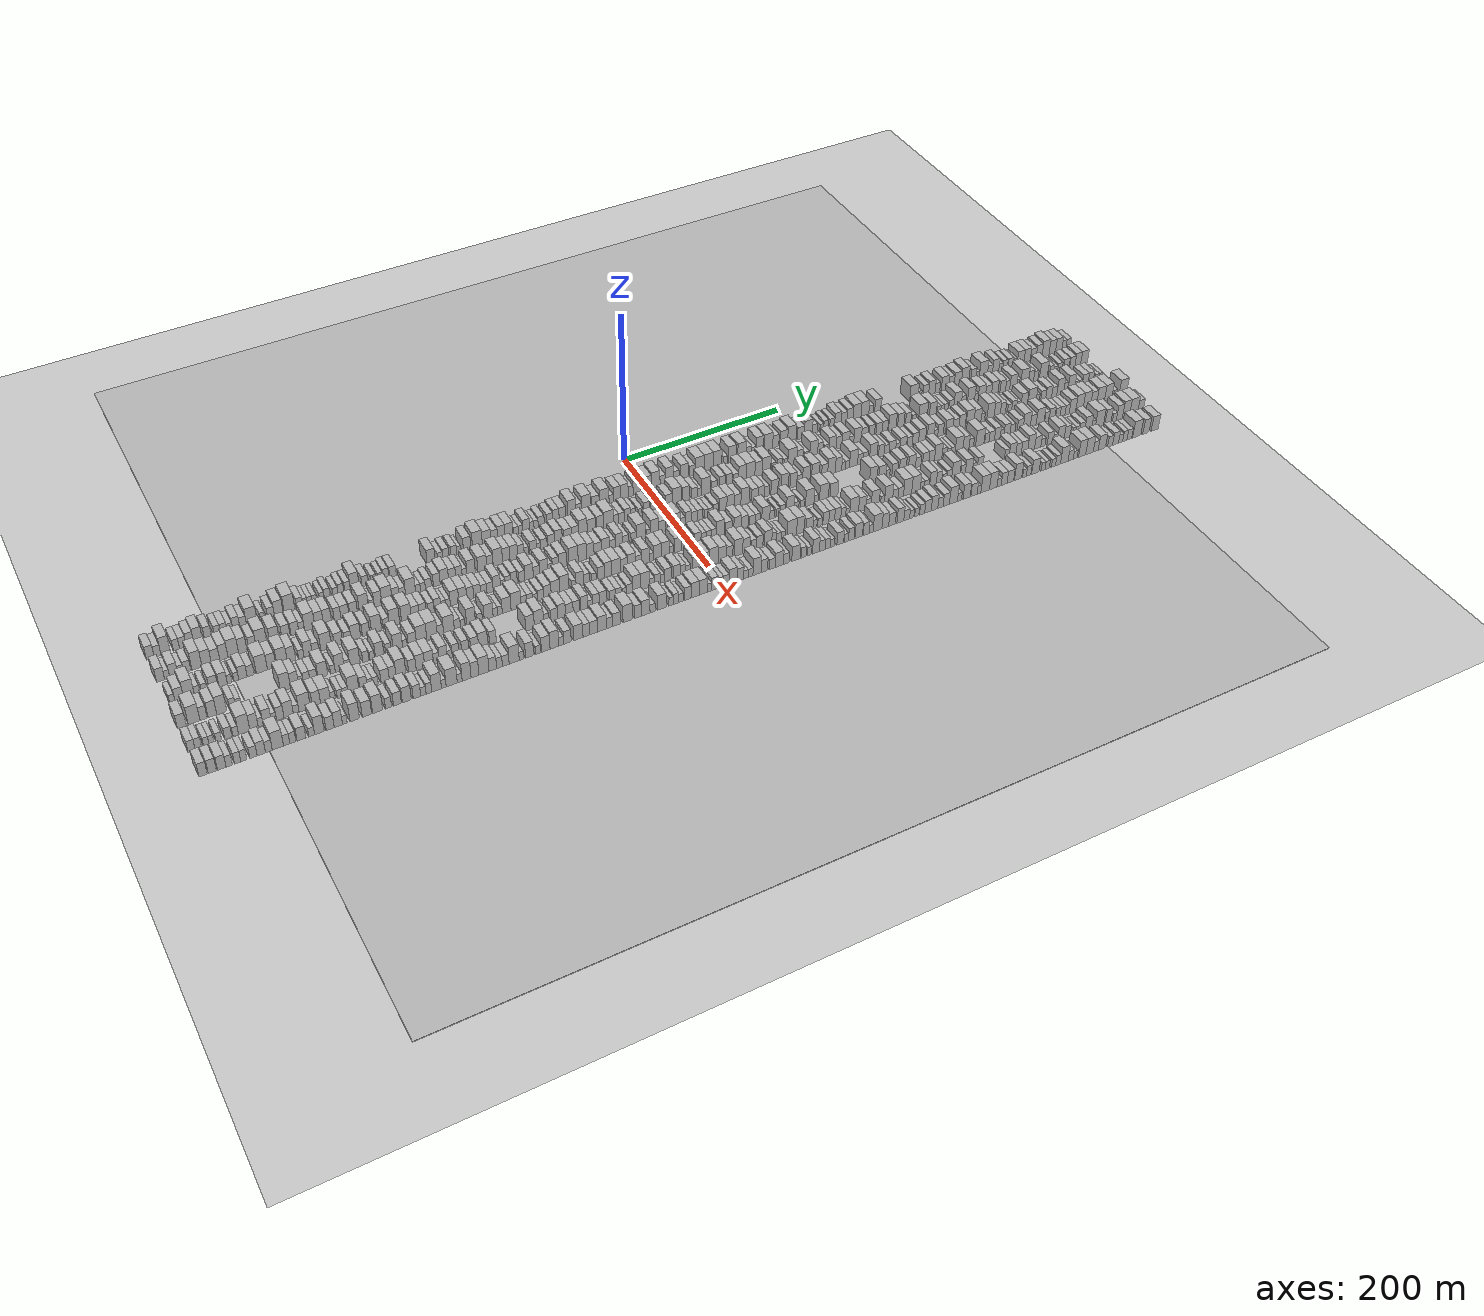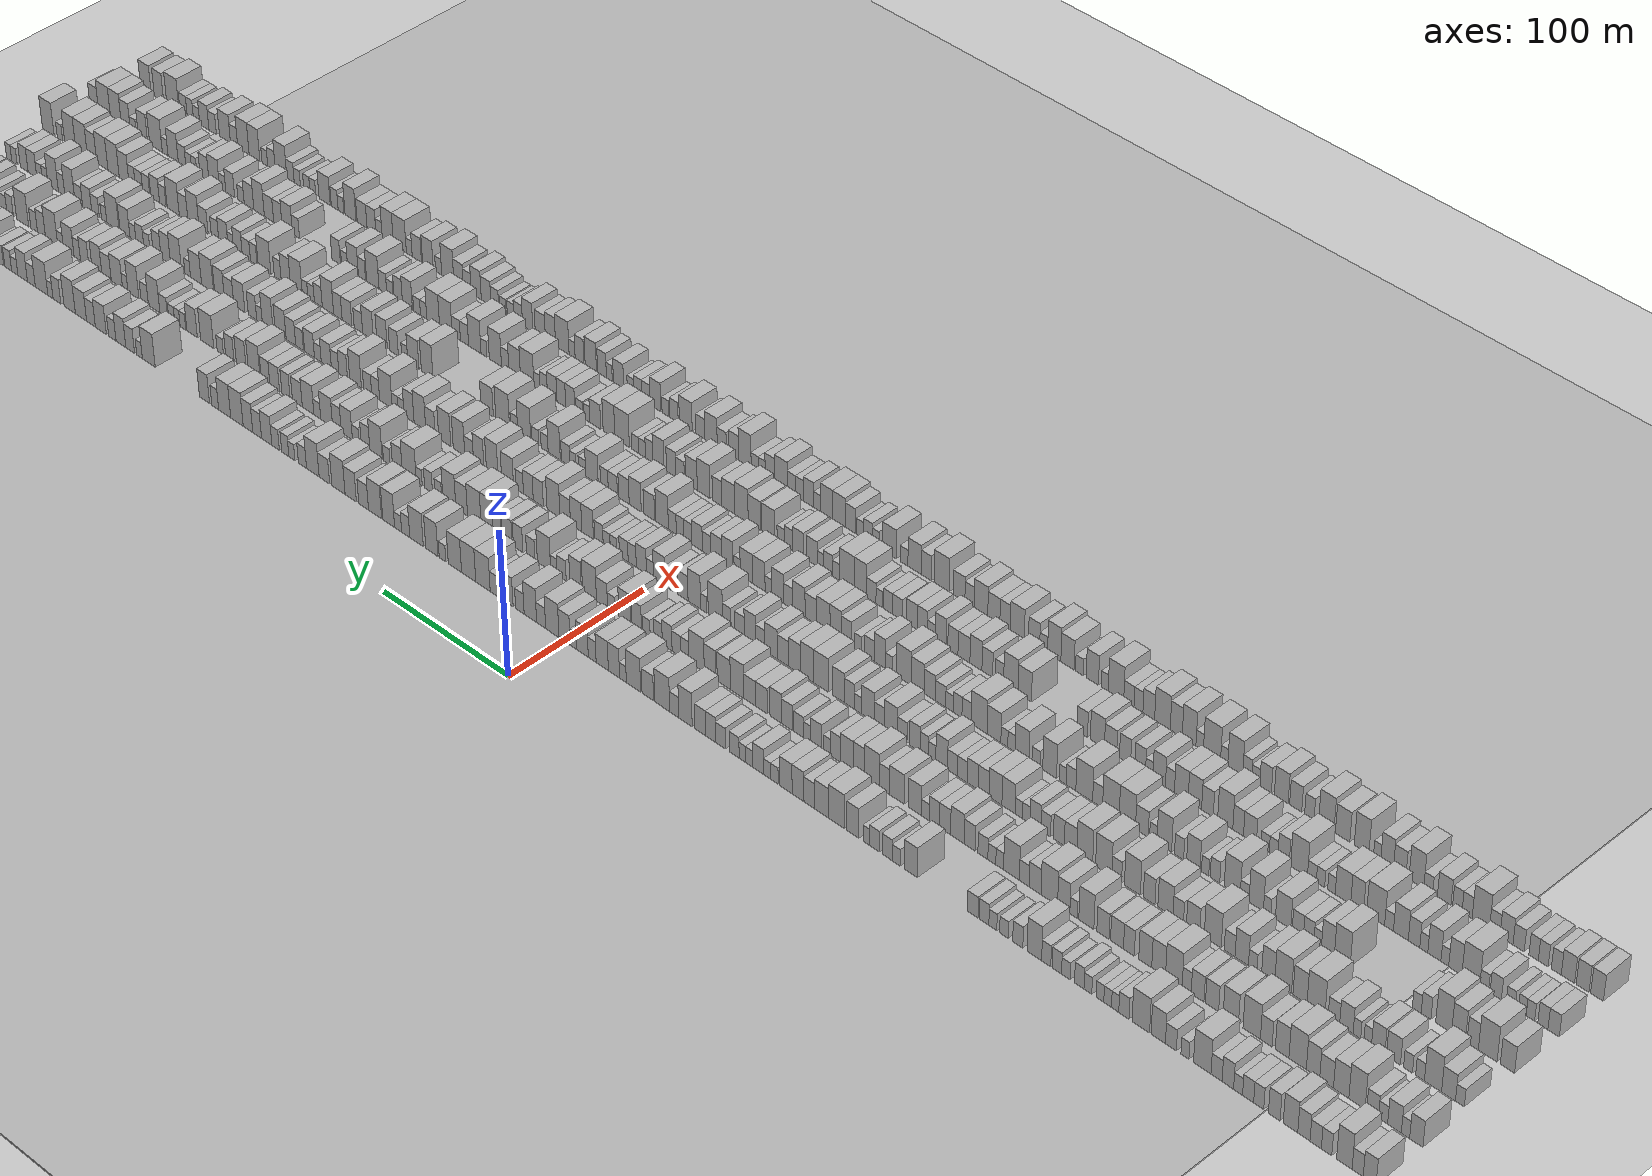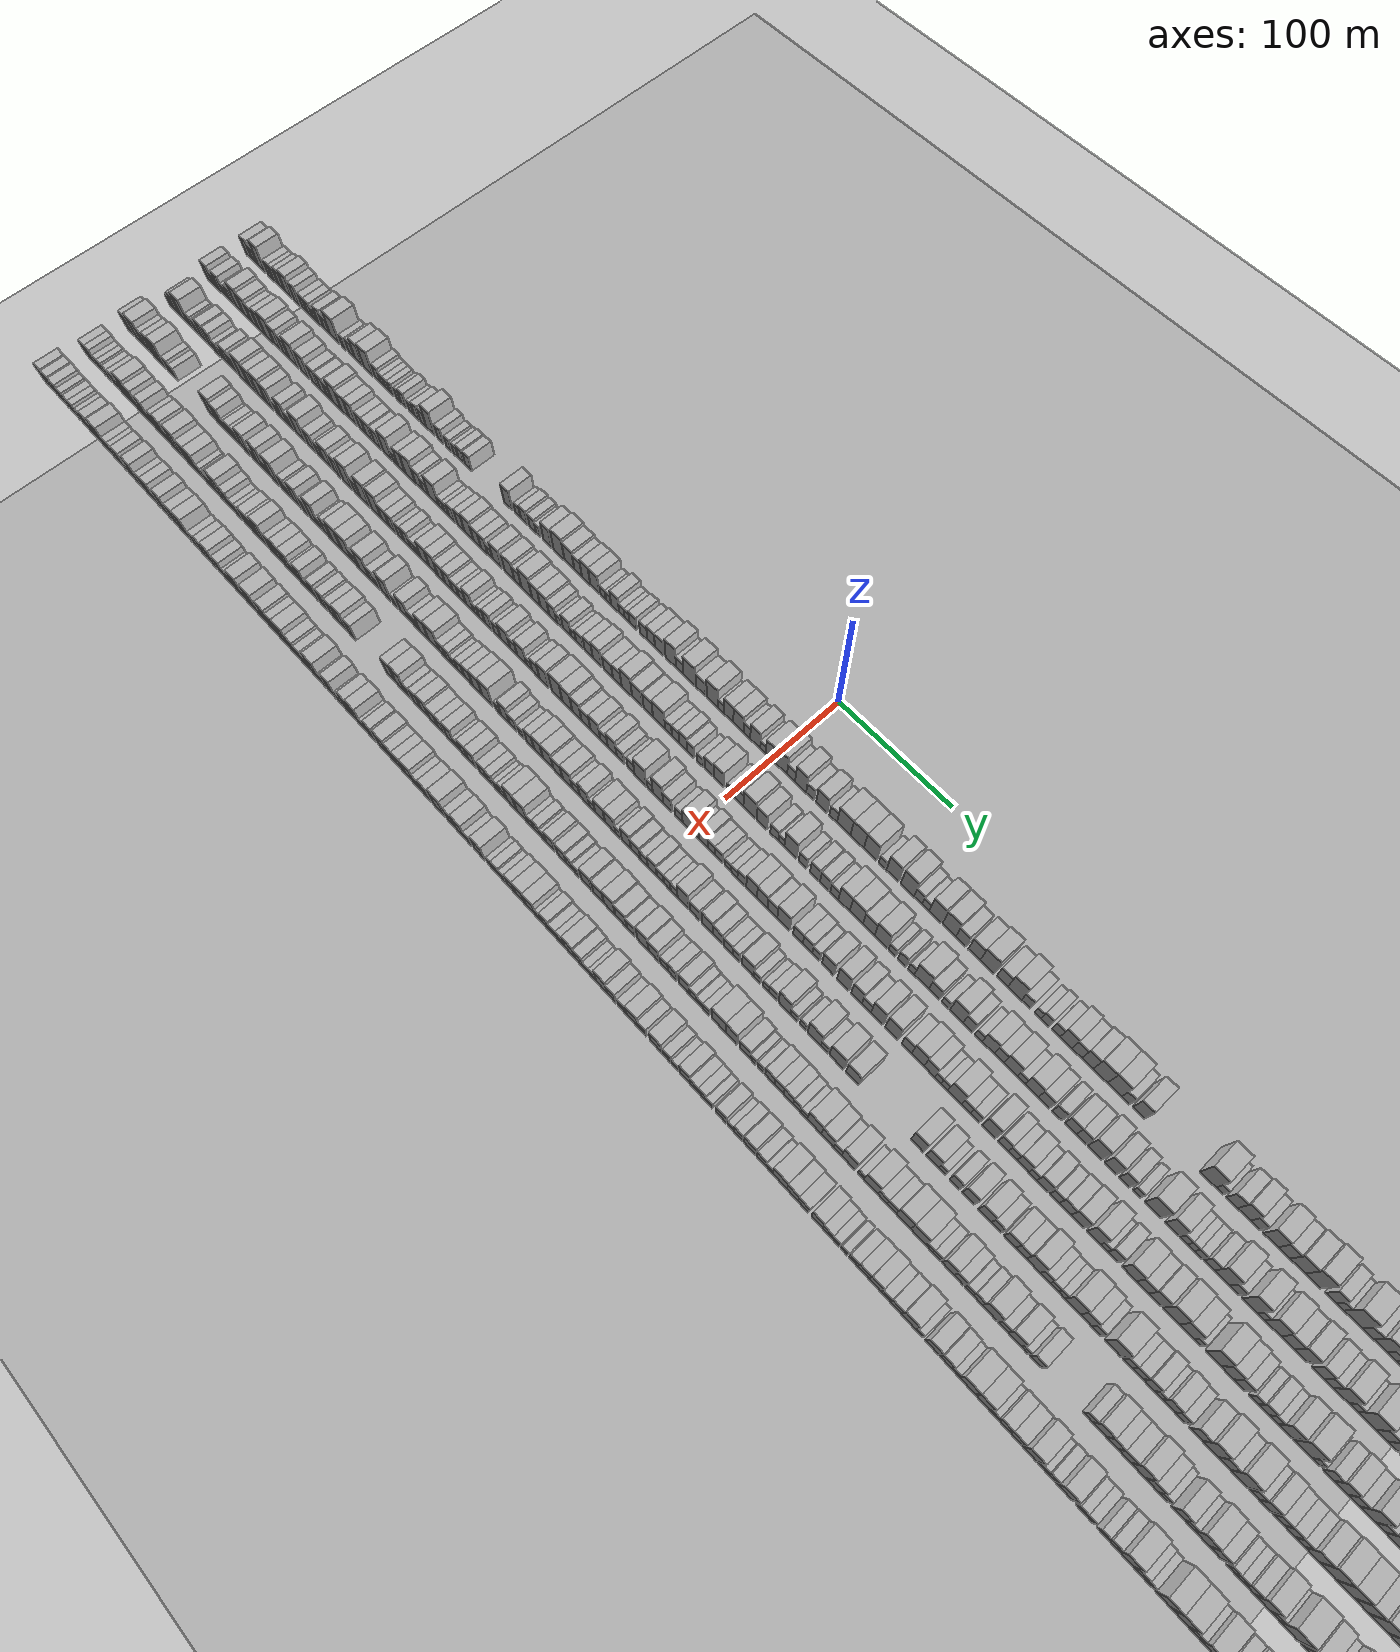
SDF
<?xml version="1.0" encoding="utf-8"?>

<sdf version="1.6">

   <world name="default">

      <gui fullscreen="0">

         <camera name="user_camera">

            <pose>-15 0 4.57585 0 0 0</pose>

            <view_controller>orbit</view_controller>

         </camera>

      </gui>

      <scene>

         <sky>

           <clouds>

             <speed>12</speed>

           </clouds>

         </sky>

         <ambient>0.4 0.4 0.4 1</ambient>

         <background>0.7 0.7 0.7 1</background>

         <shadows>1</shadows>

      </scene>

      <gravity>0 0 -9.8066</gravity>

      <magnetic_field>6e-06 2.3e-05 -4.2e-05</magnetic_field>

      <physics default="0" name="default_physics" type="ode">

         <ode>

            <solver>

               <type>quick</type>

               <iters>10</iters>

               <sor>1.0</sor>

               <use_dynamic_moi_rescaling>0</use_dynamic_moi_rescaling>

            </solver>

            <constraints>

               <cfm>0</cfm>

               <erp>0.2</erp>

               <contact_max_correcting_vel>100</contact_max_correcting_vel>

               <contact_surface_layer>0.001</contact_surface_layer>

            </constraints>

         </ode>

         <max_step_size>0.004</max_step_size>

         <real_time_factor>1</real_time_factor>

         <real_time_update_rate>250</real_time_update_rate>

      </physics>

      <light name="sun" type="directional">

         <cast_shadows>1</cast_shadows>

         <pose>0 0 10 0 0 0</pose>

         <diffuse>0.8 0.8 0.8 1</diffuse>

         <specular>0.2 0.2 0.2 1</specular>

         <attenuation>

            <range>1000</range>

            <constant>0.9</constant>

            <linear>0.01</linear>

            <quadratic>0.001</quadratic>

         </attenuation>

         <direction>-0.5 0.1 -0.9</direction>

      </light>

      <include>

         <name>ground_plane_1</name>

         <uri>model://HANNAS_ground_plane</uri>

         <pose>0 0 0  0 0 0</pose>

      </include>

      <include>

         <name>ground_plane_2</name>

         <uri>model://HANNAS_ground_plane</uri>

         <pose>100 0 0  0 0 0</pose>

      </include>

      <model name="building_1">

         <static>1</static>

         <pose frame="">50.0000 -565.9921 0 0.000000 0.000000 0.000000</pose>

         <link name="link">

            <pose frame="">0 0 9.00 0 0 0</pose>

            <collision name="collision">

               <geometry>

                  <box>

                     <size>20.0000 8.0158 18.0000</size>

                  </box>

               </geometry>

               <max_contacts>10</max_contacts>

               <surface>

                  <contact>

                     <ode/>

                  </contact>

                  <bounce/>

                  <friction>

                     <torsional>

                        <ode/>

                     </torsional>

                     <ode/>

                  </friction>

               </surface>

            </collision>

            <visual name="visual">

               <cast_shadows>0</cast_shadows>

               <geometry>

                  <box>

                     <size>20.0000 8.0158 18.0000</size>

                  </box>

               </geometry>

               <material>

                  <script>

                     <uri>model://HANNAS_wall/materials/scripts</uri>

                     <uri>model://HANNAS_wall/materials/textures</uri>

                     <name>vrc/HANNAS_wall</name>

                  </script>

               </material>

            </visual>

            <self_collide>0</self_collide>

            <enable_wind>0</enable_wind>

            <kinematic>0</kinematic>

         </link>

      </model>

      <model name="building_2">

         <static>1</static>

         <pose frame="">50.0000 -558.4893 0 0.000000 0.000000 0.000000</pose>

         <link name="link">

            <pose frame="">0 0 7.50 0 0 0</pose>

            <collision name="collision">

               <geometry>

                  <box>

                     <size>20.0000 6.9898 15.0000</size>

                  </box>

               </geometry>

               <max_contacts>10</max_contacts>

               <surface>

                  <contact>

                     <ode/>

                  </contact>

                  <bounce/>

                  <friction>

                     <torsional>

                        <ode/>

                     </torsional>

                     <ode/>

                  </friction>

               </surface>

            </collision>

            <visual name="visual">

               <cast_shadows>0</cast_shadows>

               <geometry>

                  <box>

                     <size>20.0000 6.9898 15.0000</size>

                  </box>

               </geometry>

               <material>

                  <script>

                     <uri>model://HANNAS_wall/materials/scripts</uri>

                     <uri>model://HANNAS_wall/materials/textures</uri>

                     <name>vrc/HANNAS_wall</name>

                  </script>

               </material>

            </visual>

            <self_collide>0</self_collide>

            <enable_wind>0</enable_wind>

            <kinematic>0</kinematic>

         </link>

      </model>

      <model name="building_3">

         <static>1</static>

         <pose frame="">50.0000 -550.1296 0 0.000000 0.000000 0.000000</pose>

         <link name="link">

            <pose frame="">0 0 12.00 0 0 0</pose>

            <collision name="collision">

               <geometry>

                  <box>

                     <size>20.0000 9.7296 24.0000</size>

                  </box>

               </geometry>

               <max_contacts>10</max_contacts>

               <surface>

                  <contact>

                     <ode/>

                  </contact>

                  <bounce/>

                  <friction>

                     <torsional>

                        <ode/>

                     </torsional>

                     <ode/>

                  </friction>

               </surface>

            </collision>

            <visual name="visual">

               <cast_shadows>0</cast_shadows>

               <geometry>

                  <box>

                     <size>20.0000 9.7296 24.0000</size>

                  </box>

               </geometry>

               <material>

                  <script>

                     <uri>model://HANNAS_wall/materials/scripts</uri>

                     <uri>model://HANNAS_wall/materials/textures</uri>

                     <name>vrc/HANNAS_wall</name>

                  </script>

               </material>

            </visual>

            <self_collide>0</self_collide>

            <enable_wind>0</enable_wind>

            <kinematic>0</kinematic>

         </link>

      </model>

      <model name="building_4">

         <static>1</static>

         <pose frame="">50.0000 -538.9763 0 0.000000 0.000000 0.000000</pose>

         <link name="link">

            <pose frame="">0 0 7.50 0 0 0</pose>

            <collision name="collision">

               <geometry>

                  <box>

                     <size>20.0000 6.5770 15.0000</size>

                  </box>

               </geometry>

               <max_contacts>10</max_contacts>

               <surface>

                  <contact>

                     <ode/>

                  </contact>

                  <bounce/>

                  <friction>

                     <torsional>

                        <ode/>

                     </torsional>

                     <ode/>

                  </friction>

               </surface>

            </collision>

            <visual name="visual">

               <cast_shadows>0</cast_shadows>

               <geometry>

                  <box>

                     <size>20.0000 6.5770 15.0000</size>

                  </box>

               </geometry>

               <material>

                  <script>

                     <uri>model://HANNAS_wall/materials/scripts</uri>

                     <uri>model://HANNAS_wall/materials/textures</uri>

                     <name>vrc/HANNAS_wall</name>

                  </script>

               </material>

            </visual>

            <self_collide>0</self_collide>

            <enable_wind>0</enable_wind>

            <kinematic>0</kinematic>

         </link>

      </model>

      <model name="building_5">

         <static>1</static>

         <pose frame="">50.0000 -532.0828 0 0.000000 0.000000 0.000000</pose>

         <link name="link">

            <pose frame="">0 0 7.50 0 0 0</pose>

            <collision name="collision">

               <geometry>

                  <box>

                     <size>20.0000 7.2101 15.0000</size>

                  </box>

               </geometry>

               <max_contacts>10</max_contacts>

               <surface>

                  <contact>

                     <ode/>

                  </contact>

                  <bounce/>

                  <friction>

                     <torsional>

                        <ode/>

                     </torsional>

                     <ode/>

                  </friction>

               </surface>

            </collision>

            <visual name="visual">

               <cast_shadows>0</cast_shadows>

               <geometry>

                  <box>

                     <size>20.0000 7.2101 15.0000</size>

                  </box>

               </geometry>

               <material>

                  <script>

                     <uri>model://HANNAS_wall/materials/scripts</uri>

                     <uri>model://HANNAS_wall/materials/textures</uri>

                     <name>vrc/HANNAS_wall</name>

                  </script>

               </material>

            </visual>

            <self_collide>0</self_collide>

            <enable_wind>0</enable_wind>

            <kinematic>0</kinematic>

         </link>

      </model>

      <model name="building_6">

         <static>1</static>

         <pose frame="">50.0000 -524.5822 0 0.000000 0.000000 0.000000</pose>

         <link name="link">

            <pose frame="">0 0 9.00 0 0 0</pose>

            <collision name="collision">

               <geometry>

                  <box>

                     <size>20.0000 7.7910 18.0000</size>

                  </box>

               </geometry>

               <max_contacts>10</max_contacts>

               <surface>

                  <contact>

                     <ode/>

                  </contact>

                  <bounce/>

                  <friction>

                     <torsional>

                        <ode/>

                     </torsional>

                     <ode/>

                  </friction>

               </surface>

            </collision>

            <visual name="visual">

               <cast_shadows>0</cast_shadows>

               <geometry>

                  <box>

                     <size>20.0000 7.7910 18.0000</size>

                  </box>

               </geometry>

               <material>

                  <script>

                     <uri>model://HANNAS_wall/materials/scripts</uri>

                     <uri>model://HANNAS_wall/materials/textures</uri>

                     <name>vrc/HANNAS_wall</name>

                  </script>

               </material>

            </visual>

            <self_collide>0</self_collide>

            <enable_wind>0</enable_wind>

            <kinematic>0</kinematic>

         </link>

      </model>

      <model name="building_7">

         <static>1</static>

         <pose frame="">50.0000 -516.0581 0 0.000000 0.000000 0.000000</pose>

         <link name="link">

            <pose frame="">0 0 10.50 0 0 0</pose>

            <collision name="collision">

               <geometry>

                  <box>

                     <size>20.0000 9.2572 21.0000</size>

                  </box>

               </geometry>

               <max_contacts>10</max_contacts>

               <surface>

                  <contact>

                     <ode/>

                  </contact>

                  <bounce/>

                  <friction>

                     <torsional>

                        <ode/>

                     </torsional>

                     <ode/>

                  </friction>

               </surface>

            </collision>

            <visual name="visual">

               <cast_shadows>0</cast_shadows>

               <geometry>

                  <box>

                     <size>20.0000 9.2572 21.0000</size>

                  </box>

               </geometry>

               <material>

                  <script>

                     <uri>model://HANNAS_wall/materials/scripts</uri>

                     <uri>model://HANNAS_wall/materials/textures</uri>

                     <name>vrc/HANNAS_wall</name>

                  </script>

               </material>

            </visual>

            <self_collide>0</self_collide>

            <enable_wind>0</enable_wind>

            <kinematic>0</kinematic>

         </link>

      </model>

      <model name="building_8">

         <static>1</static>

         <pose frame="">50.0000 -505.6838 0 0.000000 0.000000 0.000000</pose>

         <link name="link">

            <pose frame="">0 0 9.00 0 0 0</pose>

            <collision name="collision">

               <geometry>

                  <box>

                     <size>20.0000 7.4913 18.0000</size>

                  </box>

               </geometry>

               <max_contacts>10</max_contacts>

               <surface>

                  <contact>

                     <ode/>

                  </contact>

                  <bounce/>

                  <friction>

                     <torsional>

                        <ode/>

                     </torsional>

                     <ode/>

                  </friction>

               </surface>

            </collision>

            <visual name="visual">

               <cast_shadows>0</cast_shadows>

               <geometry>

                  <box>

                     <size>20.0000 7.4913 18.0000</size>

                  </box>

               </geometry>

               <material>

                  <script>

                     <uri>model://HANNAS_wall/materials/scripts</uri>

                     <uri>model://HANNAS_wall/materials/textures</uri>

                     <name>vrc/HANNAS_wall</name>

                  </script>

               </material>

            </visual>

            <self_collide>0</self_collide>

            <enable_wind>0</enable_wind>

            <kinematic>0</kinematic>

         </link>

      </model>

      <model name="building_9">

         <static>1</static>

         <pose frame="">50.0000 -495.6850 0 0.000000 0.000000 0.000000</pose>

         <link name="link">

            <pose frame="">0 0 7.50 0 0 0</pose>

            <collision name="collision">

               <geometry>

                  <box>

                     <size>20.0000 6.5063 15.0000</size>

                  </box>

               </geometry>

               <max_contacts>10</max_contacts>

               <surface>

                  <contact>

                     <ode/>

                  </contact>

                  <bounce/>

                  <friction>

                     <torsional>

                        <ode/>

                     </torsional>

                     <ode/>

                  </friction>

               </surface>

            </collision>

            <visual name="visual">

               <cast_shadows>0</cast_shadows>

               <geometry>

                  <box>

                     <size>20.0000 6.5063 15.0000</size>

                  </box>

               </geometry>

               <material>

                  <script>

                     <uri>model://HANNAS_wall/materials/scripts</uri>

                     <uri>model://HANNAS_wall/materials/textures</uri>

                     <name>vrc/HANNAS_wall</name>

                  </script>

               </material>

            </visual>

            <self_collide>0</self_collide>

            <enable_wind>0</enable_wind>

            <kinematic>0</kinematic>

         </link>

      </model>

      <model name="building_10">

         <static>1</static>

         <pose frame="">50.0000 -488.8466 0 0.000000 0.000000 0.000000</pose>

         <link name="link">

            <pose frame="">0 0 7.50 0 0 0</pose>

            <collision name="collision">

               <geometry>

                  <box>

                     <size>20.0000 7.1706 15.0000</size>

                  </box>

               </geometry>

               <max_contacts>10</max_contacts>

               <surface>

                  <contact>

                     <ode/>

                  </contact>

                  <bounce/>

                  <friction>

                     <torsional>

                        <ode/>

                     </torsional>

                     <ode/>

                  </friction>

               </surface>

            </collision>

            <visual name="visual">

               <cast_shadows>0</cast_shadows>

               <geometry>

                  <box>

                     <size>20.0000 7.1706 15.0000</size>

                  </box>

               </geometry>

               <material>

                  <script>

                     <uri>model://HANNAS_wall/materials/scripts</uri>

                     <uri>model://HANNAS_wall/materials/textures</uri>

                     <name>vrc/HANNAS_wall</name>

                  </script>

               </material>

            </visual>

            <self_collide>0</self_collide>

            <enable_wind>0</enable_wind>

            <kinematic>0</kinematic>

         </link>

      </model>

      <model name="building_11">

         <static>1</static>

         <pose frame="">50.0000 -482.3560 0 0.000000 0.000000 0.000000</pose>

         <link name="link">

            <pose frame="">0 0 6.00 0 0 0</pose>

            <collision name="collision">

               <geometry>

                  <box>

                     <size>20.0000 5.8106 12.0000</size>

                  </box>

               </geometry>

               <max_contacts>10</max_contacts>

               <surface>

                  <contact>

                     <ode/>

                  </contact>

                  <bounce/>

                  <friction>

                     <torsional>

                        <ode/>

                     </torsional>

                     <ode/>

                  </friction>

               </surface>

            </collision>

            <visual name="visual">

               <cast_shadows>0</cast_shadows>

               <geometry>

                  <box>

                     <size>20.0000 5.8106 12.0000</size>

                  </box>

               </geometry>

               <material>

                  <script>

                     <uri>model://HANNAS_wall/materials/scripts</uri>

                     <uri>model://HANNAS_wall/materials/textures</uri>

                     <name>vrc/HANNAS_wall</name>

                  </script>

               </material>

            </visual>

            <self_collide>0</self_collide>

            <enable_wind>0</enable_wind>

            <kinematic>0</kinematic>

         </link>

      </model>

      <model name="building_12">

         <static>1</static>

         <pose frame="">50.0000 -475.7150 0 0.000000 0.000000 0.000000</pose>

         <link name="link">

            <pose frame="">0 0 9.00 0 0 0</pose>

            <collision name="collision">

               <geometry>

                  <box>

                     <size>20.0000 7.4714 18.0000</size>

                  </box>

               </geometry>

               <max_contacts>10</max_contacts>

               <surface>

                  <contact>

                     <ode/>

                  </contact>

                  <bounce/>

                  <friction>

                     <torsional>

                        <ode/>

                     </torsional>

                     <ode/>

                  </friction>

               </surface>

            </collision>

            <visual name="visual">

               <cast_shadows>0</cast_shadows>

               <geometry>

                  <box>

                     <size>20.0000 7.4714 18.0000</size>

                  </box>

               </geometry>

               <material>

                  <script>

                     <uri>model://HANNAS_wall/materials/scripts</uri>

                     <uri>model://HANNAS_wall/materials/textures</uri>

                     <name>vrc/HANNAS_wall</name>

                  </script>

               </material>

            </visual>

            <self_collide>0</self_collide>

            <enable_wind>0</enable_wind>

            <kinematic>0</kinematic>

         </link>

      </model>

      <model name="building_13">

         <static>1</static>

         <pose frame="">50.0000 -468.3772 0 0.000000 0.000000 0.000000</pose>

         <link name="link">

            <pose frame="">0 0 7.50 0 0 0</pose>

            <collision name="collision">

               <geometry>

                  <box>

                     <size>20.0000 7.2043 15.0000</size>

                  </box>

               </geometry>

               <max_contacts>10</max_contacts>

               <surface>

                  <contact>

                     <ode/>

                  </contact>

                  <bounce/>

                  <friction>

                     <torsional>

                        <ode/>

                     </torsional>

                     <ode/>

                  </friction>

               </surface>

            </collision>

            <visual name="visual">

               <cast_shadows>0</cast_shadows>

               <geometry>

                  <box>

                     <size>20.0000 7.2043 15.0000</size>

                  </box>

               </geometry>

               <material>

                  <script>

                     <uri>model://HANNAS_wall/materials/scripts</uri>

                     <uri>model://HANNAS_wall/materials/textures</uri>

                     <name>vrc/HANNAS_wall</name>

                  </script>

               </material>

            </visual>

            <self_collide>0</self_collide>

            <enable_wind>0</enable_wind>

            <kinematic>0</kinematic>

         </link>

      </model>

      <model name="building_14">

         <static>1</static>

         <pose frame="">50.0000 -459.0556 0 0.000000 0.000000 0.000000</pose>

         <link name="link">

            <pose frame="">0 0 12.00 0 0 0</pose>

            <collision name="collision">

               <geometry>

                  <box>

                     <size>20.0000 11.4390 24.0000</size>

                  </box>

               </geometry>

               <max_contacts>10</max_contacts>

               <surface>

                  <contact>

                     <ode/>

                  </contact>

                  <bounce/>

                  <friction>

                     <torsional>

                        <ode/>

                     </torsional>

                     <ode/>

                  </friction>

               </surface>

            </collision>

            <visual name="visual">

               <cast_shadows>0</cast_shadows>

               <geometry>

                  <box>

                     <size>20.0000 11.4390 24.0000</size>

                  </box>

               </geometry>

               <material>

                  <script>

                     <uri>model://HANNAS_wall/materials/scripts</uri>

                     <uri>model://HANNAS_wall/materials/textures</uri>

                     <name>vrc/HANNAS_wall</name>

                  </script>

               </material>

            </visual>

            <self_collide>0</self_collide>

            <enable_wind>0</enable_wind>

            <kinematic>0</kinematic>

         </link>

      </model>

      <model name="building_15">

         <static>1</static>

         <pose frame="">50.0000 -447.7191 0 0.000000 0.000000 0.000000</pose>

         <link name="link">

            <pose frame="">0 0 6.00 0 0 0</pose>

            <collision name="collision">

               <geometry>

                  <box>

                     <size>20.0000 5.2340 12.0000</size>

                  </box>

               </geometry>

               <max_contacts>10</max_contacts>

               <surface>

                  <contact>

                     <ode/>

                  </contact>

                  <bounce/>

                  <friction>

                     <torsional>

                        <ode/>

                     </torsional>

                     <ode/>

                  </friction>

               </surface>

            </collision>

            <visual name="visual">

               <cast_shadows>0</cast_shadows>

               <geometry>

                  <box>

                     <size>20.0000 5.2340 12.0000</size>

                  </box>

               </geometry>

               <material>

                  <script>

                     <uri>model://HANNAS_wall/materials/scripts</uri>

                     <uri>model://HANNAS_wall/materials/textures</uri>

                     <name>vrc/HANNAS_wall</name>

                  </script>

               </material>

            </visual>

            <self_collide>0</self_collide>

            <enable_wind>0</enable_wind>

            <kinematic>0</kinematic>

         </link>

      </model>

      <model name="building_16">

         <static>1</static>

         <pose frame="">50.0000 -438.4945 0 0.000000 0.000000 0.000000</pose>

         <link name="link">

            <pose frame="">0 0 7.50 0 0 0</pose>

            <collision name="collision">

               <geometry>

                  <box>

                     <size>20.0000 7.2152 15.0000</size>

                  </box>

               </geometry>

               <max_contacts>10</max_contacts>

               <surface>

                  <contact>

                     <ode/>

                  </contact>

                  <bounce/>

                  <friction>

                     <torsional>

                        <ode/>

                     </torsional>

                     <ode/>

                  </friction>

               </surface>

            </collision>

            <visual name="visual">

               <cast_shadows>0</cast_shadows>

               <geometry>

                  <box>

                     <size>20.0000 7.2152 15.0000</size>

                  </box>

               </geometry>

               <material>

                  <script>

                     <uri>model://HANNAS_wall/materials/scripts</uri>

                     <uri>model://HANNAS_wall/materials/textures</uri>

                     <name>vrc/HANNAS_wall</name>

                  </script>

               </material>

            </visual>

            <self_collide>0</self_collide>

            <enable_wind>0</enable_wind>

            <kinematic>0</kinematic>

         </link>

      </model>

      <model name="building_17">

         <static>1</static>

         <pose frame="">50.0000 -430.1381 0 0.000000 0.000000 0.000000</pose>

         <link name="link">

            <pose frame="">0 0 10.50 0 0 0</pose>

            <collision name="collision">

               <geometry>

                  <box>

                     <size>20.0000 9.4976 21.0000</size>

                  </box>

               </geometry>

               <max_contacts>10</max_contacts>

               <surface>

                  <contact>

                     <ode/>

                  </contact>

                  <bounce/>

                  <friction>

                     <torsional>

                        <ode/>

                     </torsional>

                     <ode/>

                  </friction>

               </surface>

            </collision>

            <visual name="visual">

               <cast_shadows>0</cast_shadows>

               <geometry>

                  <box>

                     <size>20.0000 9.4976 21.0000</size>

                  </box>

               </geometry>

               <material>

                  <script>

                     <uri>model://HANNAS_wall/materials/scripts</uri>

                     <uri>model://HANNAS_wall/materials/textures</uri>

                     <name>vrc/HANNAS_wall</name>

                  </script>

               </material>

            </visual>

            <self_collide>0</self_collide>

            <enable_wind>0</enable_wind>

            <kinematic>0</kinematic>

         </link>

      </model>

      <model name="building_18">

         <static>1</static>

         <pose frame="">50.0000 -418.5668 0 0.000000 0.000000 0.000000</pose>

         <link name="link">

            <pose frame="">0 0 12.00 0 0 0</pose>

            <collision name="collision">

               <geometry>

                  <box>

                     <size>20.0000 11.6448 24.0000</size>

                  </box>

               </geometry>

               <max_contacts>10</max_contacts>

               <surface>

                  <contact>

                     <ode/>

                  </contact>

                  <bounce/>

                  <friction>

                     <torsional>

                        <ode/>

                     </torsional>

                     <ode/>

                  </friction>

               </surface>

            </collision>

            <visual name="visual">

               <cast_shadows>0</cast_shadows>

               <geometry>

                  <box>

                     <size>20.0000 11.6448 24.0000</size>

                  </box>

               </geometry>

               <material>

                  <script>

                     <uri>model://HANNAS_wall/materials/scripts</uri>

                     <uri>model://HANNAS_wall/materials/textures</uri>

                     <name>vrc/HANNAS_wall</name>

                  </script>

               </material>

            </visual>

            <self_collide>0</self_collide>

            <enable_wind>0</enable_wind>

            <kinematic>0</kinematic>

         </link>

      </model>

      <model name="building_19">

         <static>1</static>

         <pose frame="">50.0000 -407.2916 0 0.000000 0.000000 0.000000</pose>

         <link name="link">

            <pose frame="">0 0 7.50 0 0 0</pose>

            <collision name="collision">

               <geometry>

                  <box>

                     <size>20.0000 6.9057 15.0000</size>

                  </box>

               </geometry>

               <max_contacts>10</max_contacts>

               <surface>

                  <contact>

                     <ode/>

                  </contact>

                  <bounce/>

                  <friction>

                     <torsional>

                        <ode/>

                     </torsional>

                     <ode/>

                  </friction>

               </surface>

            </collision>

            <visual name="visual">

               <cast_shadows>0</cast_shadows>

               <geometry>

                  <box>

                     <size>20.0000 6.9057 15.0000</size>

                  </box>

               </geometry>

               <material>

                  <script>

                     <uri>model://HANNAS_wall/materials/scripts</uri>

                     <uri>model://HANNAS_wall/materials/textures</uri>

                     <name>vrc/HANNAS_wall</name>

                  </script>

               </material>

            </visual>

            <self_collide>0</self_collide>

            <enable_wind>0</enable_wind>

            <kinematic>0</kinematic>

         </link>

      </model>

      <model name="building_20">

         <static>1</static>

         <pose frame="">50.0000 -401.4126 0 0.000000 0.000000 0.000000</pose>

         <link name="link">

            <pose frame="">0 0 6.00 0 0 0</pose>

            <collision name="collision">

               <geometry>

                  <box>

                     <size>20.0000 4.8524 12.0000</size>

                  </box>

               </geometry>

               <max_contacts>10</max_contacts>

               <surface>

                  <contact>

                     <ode/>

                  </contact>

                  <bounce/>

                  <friction>

                     <torsional>

                        <ode/>

                     </torsional>

                     <ode/>

                  </friction>

               </surface>

            </collision>

            <visual name="visual">

               <cast_shadows>0</cast_shadows>

               <geometry>

                  <box>

                     <size>20.0000 4.8524 12.0000</size>

                  </box>

               </geometry>

               <material>

                  <script>

                     <uri>model://HANNAS_wall/materials/scripts</uri>

                     <uri>model://HANNAS_wall/materials/textures</uri>

                     <name>vrc/HANNAS_wall</name>

                  </script>

               </material>

            </visual>

            <self_collide>0</self_collide>

            <enable_wind>0</enable_wind>

            <kinematic>0</kinematic>

         </link>

      </model>

      <model name="building_21">

         <static>1</static>

         <pose frame="">50.0000 -396.3918 0 0.000000 0.000000 0.000000</pose>

         <link name="link">

            <pose frame="">0 0 6.00 0 0 0</pose>

            <collision name="collision">

               <geometry>

                  <box>

                     <size>20.0000 5.1893 12.0000</size>

                  </box>

               </geometry>

               <max_contacts>10</max_contacts>

               <surface>

                  <contact>

                     <ode/>

                  </contact>

                  <bounce/>

                  <friction>

                     <torsional>

                        <ode/>

                     </torsional>

                     <ode/>

                  </friction>

               </surface>

            </collision>

            <visual name="visual">

               <cast_shadows>0</cast_shadows>

               <geometry>

                  <box>

                     <size>20.0000 5.1893 12.0000</size>

                  </box>

               </geometry>

               <material>

                  <script>

                     <uri>model://HANNAS_wall/materials/scripts</uri>

                     <uri>model://HANNAS_wall/materials/textures</uri>

                     <name>vrc/HANNAS_wall</name>

                  </script>

               </material>

            </visual>

            <self_collide>0</self_collide>

            <enable_wind>0</enable_wind>

            <kinematic>0</kinematic>

         </link>

      </model>

      <model name="building_22">

         <static>1</static>

         <pose frame="">50.0000 -391.2561 0 0.000000 0.000000 0.000000</pose>

         <link name="link">

            <pose frame="">0 0 6.00 0 0 0</pose>

            <collision name="collision">

               <geometry>

                  <box>

                     <size>20.0000 5.0821 12.0000</size>

                  </box>

               </geometry>

               <max_contacts>10</max_contacts>

               <surface>

                  <contact>

                     <ode/>

                  </contact>

                  <bounce/>

                  <friction>

                     <torsional>

                        <ode/>

                     </torsional>

                     <ode/>

                  </friction>

               </surface>

            </collision>

            <visual name="visual">

               <cast_shadows>0</cast_shadows>

               <geometry>

                  <box>

                     <size>20.0000 5.0821 12.0000</size>

                  </box>

               </geometry>

               <material>

                  <script>

                     <uri>model://HANNAS_wall/materials/scripts</uri>

                     <uri>model://HANNAS_wall/materials/textures</uri>

                     <name>vrc/HANNAS_wall</name>

                  </script>

               </material>

            </visual>

            <self_collide>0</self_collide>

            <enable_wind>0</enable_wind>

            <kinematic>0</kinematic>

         </link>

      </model>

      <model name="building_23">

         <static>1</static>

         <pose frame="">50.0000 -383.0944 0 0.000000 0.000000 0.000000</pose>

         <link name="link">

            <pose frame="">0 0 6.00 0 0 0</pose>

            <collision name="collision">

               <geometry>

                  <box>

                     <size>20.0000 5.2412 12.0000</size>

                  </box>

               </geometry>

               <max_contacts>10</max_contacts>

               <surface>

                  <contact>

                     <ode/>

                  </contact>

                  <bounce/>

                  <friction>

                     <torsional>

                        <ode/>

                     </torsional>

                     <ode/>

                  </friction>

               </surface>

            </collision>

            <visual name="visual">

               <cast_shadows>0</cast_shadows>

               <geometry>

                  <box>

                     <size>20.0000 5.2412 12.0000</size>

                  </box>

               </geometry>

               <material>

                  <script>

                     <uri>model://HANNAS_wall/materials/scripts</uri>

                     <uri>model://HANNAS_wall/materials/textures</uri>

                     <name>vrc/HANNAS_wall</name>

                  </script>

               </material>

            </visual>

            <self_collide>0</self_collide>

            <enable_wind>0</enable_wind>

            <kinematic>0</kinematic>

         </link>

      </model>

      <model name="building_24">

         <static>1</static>

         <pose frame="">50.0000 -377.2749 0 0.000000 0.000000 0.000000</pose>

         <link name="link">

            <pose frame="">0 0 7.50 0 0 0</pose>

            <collision name="collision">

               <geometry>

                  <box>

                     <size>20.0000 6.3980 15.0000</size>

                  </box>

               </geometry>

               <max_contacts>10</max_contacts>

               <surface>

                  <contact>

                     <ode/>

                  </contact>

                  <bounce/>

                  <friction>

                     <torsional>

                        <ode/>

                     </torsional>

                     <ode/>

                  </friction>

               </surface>

            </collision>

            <visual name="visual">

               <cast_shadows>0</cast_shadows>

               <geometry>

                  <box>

                     <size>20.0000 6.3980 15.0000</size>

                  </box>

               </geometry>

               <material>

                  <script>

                     <uri>model://HANNAS_wall/materials/scripts</uri>

                     <uri>model://HANNAS_wall/materials/textures</uri>

                     <name>vrc/HANNAS_wall</name>

                  </script>

               </material>

            </visual>

            <self_collide>0</self_collide>

            <enable_wind>0</enable_wind>

            <kinematic>0</kinematic>

         </link>

      </model>

      <model name="building_25">

         <static>1</static>

         <pose frame="">50.0000 -368.1648 0 0.000000 0.000000 0.000000</pose>

         <link name="link">

            <pose frame="">0 0 6.00 0 0 0</pose>

            <collision name="collision">

               <geometry>

                  <box>

                     <size>20.0000 5.8223 12.0000</size>

                  </box>

               </geometry>

               <max_contacts>10</max_contacts>

               <surface>

                  <contact>

                     <ode/>

                  </contact>

                  <bounce/>

                  <friction>

                     <torsional>

                        <ode/>

                     </torsional>

                     <ode/>

                  </friction>

               </surface>

            </collision>

            <visual name="visual">

               <cast_shadows>0</cast_shadows>

               <geometry>

                  <box>

                     <size>20.0000 5.8223 12.0000</size>

                  </box>

               </geometry>

               <material>

                  <script>

                     <uri>model://HANNAS_wall/materials/scripts</uri>

                     <uri>model://HANNAS_wall/materials/textures</uri>

                     <name>vrc/HANNAS_wall</name>

                  </script>

               </material>

            </visual>

            <self_collide>0</self_collide>

            <enable_wind>0</enable_wind>

            <kinematic>0</kinematic>

         </link>

      </model>

      <model name="building_26">

         <static>1</static>

         <pose frame="">50.0000 -362.0765 0 0.000000 0.000000 0.000000</pose>

         <link name="link">

            <pose frame="">0 0 7.50 0 0 0</pose>

            <collision name="collision">

               <geometry>

                  <box>

                     <size>20.0000 6.3543 15.0000</size>

                  </box>

               </geometry>

               <max_contacts>10</max_contacts>

               <surface>

                  <contact>

                     <ode/>

                  </contact>

                  <bounce/>

                  <friction>

                     <torsional>

                        <ode/>

                     </torsional>

                     <ode/>

                  </friction>

               </surface>

            </collision>

            <visual name="visual">

               <cast_shadows>0</cast_shadows>

               <geometry>

                  <box>

                     <size>20.0000 6.3543 15.0000</size>

                  </box>

               </geometry>

               <material>

                  <script>

                     <uri>model://HANNAS_wall/materials/scripts</uri>

                     <uri>model://HANNAS_wall/materials/textures</uri>

                     <name>vrc/HANNAS_wall</name>

                  </script>

               </material>

            </visual>

            <self_collide>0</self_collide>

            <enable_wind>0</enable_wind>

            <kinematic>0</kinematic>

         </link>

      </model>

      <model name="building_27">

         <static>1</static>

         <pose frame="">50.0000 -354.7856 0 0.000000 0.000000 0.000000</pose>

         <link name="link">

            <pose frame="">0 0 7.50 0 0 0</pose>

            <collision name="collision">

               <geometry>

                  <box>

                     <size>20.0000 6.2274 15.0000</size>

                  </box>

               </geometry>

               <max_contacts>10</max_contacts>

               <surface>

                  <contact>

                     <ode/>

                  </contact>

                  <bounce/>

                  <friction>

                     <torsional>

                        <ode/>

                     </torsional>

                     <ode/>

                  </friction>

               </surface>

            </collision>

            <visual name="visual">

               <cast_shadows>0</cast_shadows>

               <geometry>

                  <box>

                     <size>20.0000 6.2274 15.0000</size>

                  </box>

               </geometry>

               <material>

                  <script>

                     <uri>model://HANNAS_wall/materials/scripts</uri>

                     <uri>model://HANNAS_wall/materials/textures</uri>

                     <name>vrc/HANNAS_wall</name>

                  </script>

               </material>

            </visual>

            <self_collide>0</self_collide>

            <enable_wind>0</enable_wind>

            <kinematic>0</kinematic>

         </link>

      </model>

      <model name="building_28">

         <static>1</static>

         <pose frame="">50.0000 -346.7114 0 0.000000 0.000000 0.000000</pose>

         <link name="link">

            <pose frame="">0 0 12.00 0 0 0</pose>

            <collision name="collision">

               <geometry>

                  <box>

                     <size>20.0000 9.9210 24.0000</size>

                  </box>

               </geometry>

               <max_contacts>10</max_contacts>

               <surface>

                  <contact>

                     <ode/>

                  </contact>

                  <bounce/>

                  <friction>

                     <torsional>

                        <ode/>

                     </torsional>

                     <ode/>

                  </friction>

               </surface>

            </collision>

            <visual name="visual">

               <cast_shadows>0</cast_shadows>

               <geometry>

                  <box>

                     <size>20.0000 9.9210 24.0000</size>

                  </box>

               </geometry>

               <material>

                  <script>

                     <uri>model://HANNAS_wall/materials/scripts</uri>

                     <uri>model://HANNAS_wall/materials/textures</uri>

                     <name>vrc/HANNAS_wall</name>

                  </script>

               </material>

            </visual>

            <self_collide>0</self_collide>

            <enable_wind>0</enable_wind>

            <kinematic>0</kinematic>

         </link>

      </model>

      <model name="building_29">

         <static>1</static>

         <pose frame="">50.0000 -335.2698 0 0.000000 0.000000 0.000000</pose>

         <link name="link">

            <pose frame="">0 0 7.50 0 0 0</pose>

            <collision name="collision">

               <geometry>

                  <box>

                     <size>20.0000 6.9622 15.0000</size>

                  </box>

               </geometry>

               <max_contacts>10</max_contacts>

               <surface>

                  <contact>

                     <ode/>

                  </contact>

                  <bounce/>

                  <friction>

                     <torsional>

                        <ode/>

                     </torsional>

                     <ode/>

                  </friction>

               </surface>

            </collision>

            <visual name="visual">

               <cast_shadows>0</cast_shadows>

               <geometry>

                  <box>

                     <size>20.0000 6.9622 15.0000</size>

                  </box>

               </geometry>

               <material>

                  <script>

                     <uri>model://HANNAS_wall/materials/scripts</uri>

                     <uri>model://HANNAS_wall/materials/textures</uri>

                     <name>vrc/HANNAS_wall</name>

                  </script>

               </material>

            </visual>

            <self_collide>0</self_collide>

            <enable_wind>0</enable_wind>

            <kinematic>0</kinematic>

         </link>

      </model>

      <model name="building_30">

         <static>1</static>

         <pose frame="">50.0000 -325.7899 0 0.000000 0.000000 0.000000</pose>

         <link name="link">

            <pose frame="">0 0 6.00 0 0 0</pose>

            <collision name="collision">

               <geometry>

                  <box>

                     <size>20.0000 5.9975 12.0000</size>

                  </box>

               </geometry>

               <max_contacts>10</max_contacts>

               <surface>

                  <contact>

                     <ode/>

                  </contact>

                  <bounce/>

                  <friction>

                     <torsional>

                        <ode/>

                     </torsional>

                     <ode/>

                  </friction>

               </surface>

            </collision>

            <visual name="visual">

               <cast_shadows>0</cast_shadows>

               <geometry>

                  <box>

                     <size>20.0000 5.9975 12.0000</size>

                  </box>

               </geometry>

               <material>

                  <script>

                     <uri>model://HANNAS_wall/materials/scripts</uri>

                     <uri>model://HANNAS_wall/materials/textures</uri>

                     <name>vrc/HANNAS_wall</name>

                  </script>

               </material>

            </visual>

            <self_collide>0</self_collide>

            <enable_wind>0</enable_wind>

            <kinematic>0</kinematic>

         </link>

      </model>

      <model name="building_31">

         <static>1</static>

         <pose frame="">50.0000 -318.0262 0 0.000000 0.000000 0.000000</pose>

         <link name="link">

            <pose frame="">0 0 6.00 0 0 0</pose>

            <collision name="collision">

               <geometry>

                  <box>

                     <size>20.0000 5.5300 12.0000</size>

                  </box>

               </geometry>

               <max_contacts>10</max_contacts>

               <surface>

                  <contact>

                     <ode/>

                  </contact>

                  <bounce/>

                  <friction>

                     <torsional>

                        <ode/>

                     </torsional>

                     <ode/>

                  </friction>

               </surface>

            </collision>

            <visual name="visual">

               <cast_shadows>0</cast_shadows>

               <geometry>

                  <box>

                     <size>20.0000 5.5300 12.0000</size>

                  </box>

               </geometry>

               <material>

                  <script>

                     <uri>model://HANNAS_wall/materials/scripts</uri>

                     <uri>model://HANNAS_wall/materials/textures</uri>

                     <name>vrc/HANNAS_wall</name>

                  </script>

               </material>

            </visual>

            <self_collide>0</self_collide>

            <enable_wind>0</enable_wind>

            <kinematic>0</kinematic>

         </link>

      </model>

      <model name="building_32">

         <static>1</static>

         <pose frame="">50.0000 -311.9786 0 0.000000 0.000000 0.000000</pose>

         <link name="link">

            <pose frame="">0 0 7.50 0 0 0</pose>

            <collision name="collision">

               <geometry>

                  <box>

                     <size>20.0000 6.5651 15.0000</size>

                  </box>

               </geometry>

               <max_contacts>10</max_contacts>

               <surface>

                  <contact>

                     <ode/>

                  </contact>

                  <bounce/>

                  <friction>

                     <torsional>

                        <ode/>

                     </torsional>

                     <ode/>

                  </friction>

               </surface>

            </collision>

            <visual name="visual">

               <cast_shadows>0</cast_shadows>

               <geometry>

                  <box>

                     <size>20.0000 6.5651 15.0000</size>

                  </box>

               </geometry>

               <material>

                  <script>

                     <uri>model://HANNAS_wall/materials/scripts</uri>

                     <uri>model://HANNAS_wall/materials/textures</uri>

                     <name>vrc/HANNAS_wall</name>

                  </script>

               </material>

            </visual>

            <self_collide>0</self_collide>

            <enable_wind>0</enable_wind>

            <kinematic>0</kinematic>

         </link>

      </model>

      <model name="building_33">

         <static>1</static>

         <pose frame="">50.0000 -304.0128 0 0.000000 0.000000 0.000000</pose>

         <link name="link">

            <pose frame="">0 0 7.50 0 0 0</pose>

            <collision name="collision">

               <geometry>

                  <box>

                     <size>20.0000 7.3666 15.0000</size>

                  </box>

               </geometry>

               <max_contacts>10</max_contacts>

               <surface>

                  <contact>

                     <ode/>

                  </contact>

                  <bounce/>

                  <friction>

                     <torsional>

                        <ode/>

                     </torsional>

                     <ode/>

                  </friction>

               </surface>

            </collision>

            <visual name="visual">

               <cast_shadows>0</cast_shadows>

               <geometry>

                  <box>

                     <size>20.0000 7.3666 15.0000</size>

                  </box>

               </geometry>

               <material>

                  <script>

                     <uri>model://HANNAS_wall/materials/scripts</uri>

                     <uri>model://HANNAS_wall/materials/textures</uri>

                     <name>vrc/HANNAS_wall</name>

                  </script>

               </material>

            </visual>

            <self_collide>0</self_collide>

            <enable_wind>0</enable_wind>

            <kinematic>0</kinematic>

         </link>

      </model>

      <model name="building_34">

         <static>1</static>

         <pose frame="">50.0000 -260.5769 0 0.000000 0.000000 0.000000</pose>

         <link name="link">

            <pose frame="">0 0 10.50 0 0 0</pose>

            <collision name="collision">

               <geometry>

                  <box>

                     <size>20.0000 9.1684 21.0000</size>

                  </box>

               </geometry>

               <max_contacts>10</max_contacts>

               <surface>

                  <contact>

                     <ode/>

                  </contact>

                  <bounce/>

                  <friction>

                     <torsional>

                        <ode/>

                     </torsional>

                     <ode/>

                  </friction>

               </surface>

            </collision>

            <visual name="visual">

               <cast_shadows>0</cast_shadows>

               <geometry>

                  <box>

                     <size>20.0000 9.1684 21.0000</size>

                  </box>

               </geometry>

               <material>

                  <script>

                     <uri>model://HANNAS_wall/materials/scripts</uri>

                     <uri>model://HANNAS_wall/materials/textures</uri>

                     <name>vrc/HANNAS_wall</name>

                  </script>

               </material>

            </visual>

            <self_collide>0</self_collide>

            <enable_wind>0</enable_wind>

            <kinematic>0</kinematic>

         </link>

      </model>

      <model name="building_35">

         <static>1</static>

         <pose frame="">50.0000 -250.0778 0 0.000000 0.000000 0.000000</pose>

         <link name="link">

            <pose frame="">0 0 6.00 0 0 0</pose>

            <collision name="collision">

               <geometry>

                  <box>

                     <size>20.0000 5.8298 12.0000</size>

                  </box>

               </geometry>

               <max_contacts>10</max_contacts>

               <surface>

                  <contact>

                     <ode/>

                  </contact>

                  <bounce/>

                  <friction>

                     <torsional>

                        <ode/>

                     </torsional>

                     <ode/>

                  </friction>

               </surface>

            </collision>

            <visual name="visual">

               <cast_shadows>0</cast_shadows>

               <geometry>

                  <box>

                     <size>20.0000 5.8298 12.0000</size>

                  </box>

               </geometry>

               <material>

                  <script>

                     <uri>model://HANNAS_wall/materials/scripts</uri>

                     <uri>model://HANNAS_wall/materials/textures</uri>

                     <name>vrc/HANNAS_wall</name>

                  </script>

               </material>

            </visual>

            <self_collide>0</self_collide>

            <enable_wind>0</enable_wind>

            <kinematic>0</kinematic>

         </link>

      </model>

      <model name="building_36">

         <static>1</static>

         <pose frame="">50.0000 -243.5441 0 0.000000 0.000000 0.000000</pose>

         <link name="link">

            <pose frame="">0 0 7.50 0 0 0</pose>

            <collision name="collision">

               <geometry>

                  <box>

                     <size>20.0000 7.2376 15.0000</size>

                  </box>

               </geometry>

               <max_contacts>10</max_contacts>

               <surface>

                  <contact>

                     <ode/>

                  </contact>

                  <bounce/>

                  <friction>

                     <torsional>

                        <ode/>

                     </torsional>

                     <ode/>

                  </friction>

               </surface>

            </collision>

            <visual name="visual">

               <cast_shadows>0</cast_shadows>

               <geometry>

                  <box>

                     <size>20.0000 7.2376 15.0000</size>

                  </box>

               </geometry>

               <material>

                  <script>

                     <uri>model://HANNAS_wall/materials/scripts</uri>

                     <uri>model://HANNAS_wall/materials/textures</uri>

                     <name>vrc/HANNAS_wall</name>

                  </script>

               </material>

            </visual>

            <self_collide>0</self_collide>

            <enable_wind>0</enable_wind>

            <kinematic>0</kinematic>

         </link>

      </model>

      <model name="building_37">

         <static>1</static>

         <pose frame="">50.0000 -234.4957 0 0.000000 0.000000 0.000000</pose>

         <link name="link">

            <pose frame="">0 0 7.50 0 0 0</pose>

            <collision name="collision">

               <geometry>

                  <box>

                     <size>20.0000 6.8593 15.0000</size>

                  </box>

               </geometry>

               <max_contacts>10</max_contacts>

               <surface>

                  <contact>

                     <ode/>

                  </contact>

                  <bounce/>

                  <friction>

                     <torsional>

                        <ode/>

                     </torsional>

                     <ode/>

                  </friction>

               </surface>

            </collision>

            <visual name="visual">

               <cast_shadows>0</cast_shadows>

               <geometry>

                  <box>

                     <size>20.0000 6.8593 15.0000</size>

                  </box>

               </geometry>

               <material>

                  <script>

                     <uri>model://HANNAS_wall/materials/scripts</uri>

                     <uri>model://HANNAS_wall/materials/textures</uri>

                     <name>vrc/HANNAS_wall</name>

                  </script>

               </material>

            </visual>

            <self_collide>0</self_collide>

            <enable_wind>0</enable_wind>

            <kinematic>0</kinematic>

         </link>

      </model>

      <model name="building_38">

         <static>1</static>

         <pose frame="">50.0000 -228.6237 0 0.000000 0.000000 0.000000</pose>

         <link name="link">

            <pose frame="">0 0 6.00 0 0 0</pose>

            <collision name="collision">

               <geometry>

                  <box>

                     <size>20.0000 4.8848 12.0000</size>

                  </box>

               </geometry>

               <max_contacts>10</max_contacts>

               <surface>

                  <contact>

                     <ode/>

                  </contact>

                  <bounce/>

                  <friction>

                     <torsional>

                        <ode/>

                     </torsional>

                     <ode/>

                  </friction>

               </surface>

            </collision>

            <visual name="visual">

               <cast_shadows>0</cast_shadows>

               <geometry>

                  <box>

                     <size>20.0000 4.8848 12.0000</size>

                  </box>

               </geometry>

               <material>

                  <script>

                     <uri>model://HANNAS_wall/materials/scripts</uri>

                     <uri>model://HANNAS_wall/materials/textures</uri>

                     <name>vrc/HANNAS_wall</name>

                  </script>

               </material>

            </visual>

            <self_collide>0</self_collide>

            <enable_wind>0</enable_wind>

            <kinematic>0</kinematic>

         </link>

      </model>

      <model name="building_39">

         <static>1</static>

         <pose frame="">50.0000 -218.8807 0 0.000000 0.000000 0.000000</pose>

         <link name="link">

            <pose frame="">0 0 10.50 0 0 0</pose>

            <collision name="collision">

               <geometry>

                  <box>

                     <size>20.0000 8.6011 21.0000</size>

                  </box>

               </geometry>

               <max_contacts>10</max_contacts>

               <surface>

                  <contact>

                     <ode/>

                  </contact>

                  <bounce/>

                  <friction>

                     <torsional>

                        <ode/>

                     </torsional>

                     <ode/>

                  </friction>

               </surface>

            </collision>

            <visual name="visual">

               <cast_shadows>0</cast_shadows>

               <geometry>

                  <box>

                     <size>20.0000 8.6011 21.0000</size>

                  </box>

               </geometry>

               <material>

                  <script>

                     <uri>model://HANNAS_wall/materials/scripts</uri>

                     <uri>model://HANNAS_wall/materials/textures</uri>

                     <name>vrc/HANNAS_wall</name>

                  </script>

               </material>

            </visual>

            <self_collide>0</self_collide>

            <enable_wind>0</enable_wind>

            <kinematic>0</kinematic>

         </link>

      </model>

      <model name="building_40">

         <static>1</static>

         <pose frame="">50.0000 -206.8810 0 0.000000 0.000000 0.000000</pose>

         <link name="link">

            <pose frame="">0 0 12.00 0 0 0</pose>

            <collision name="collision">

               <geometry>

                  <box>

                     <size>20.0000 11.3985 24.0000</size>

                  </box>

               </geometry>

               <max_contacts>10</max_contacts>

               <surface>

                  <contact>

                     <ode/>

                  </contact>

                  <bounce/>

                  <friction>

                     <torsional>

                        <ode/>

                     </torsional>

                     <ode/>

                  </friction>

               </surface>

            </collision>

            <visual name="visual">

               <cast_shadows>0</cast_shadows>

               <geometry>

                  <box>

                     <size>20.0000 11.3985 24.0000</size>

                  </box>

               </geometry>

               <material>

                  <script>

                     <uri>model://HANNAS_wall/materials/scripts</uri>

                     <uri>model://HANNAS_wall/materials/textures</uri>

                     <name>vrc/HANNAS_wall</name>

                  </script>

               </material>

            </visual>

            <self_collide>0</self_collide>

            <enable_wind>0</enable_wind>

            <kinematic>0</kinematic>

         </link>

      </model>

      <model name="building_41">

         <static>1</static>

         <pose frame="">50.0000 -196.0865 0 0.000000 0.000000 0.000000</pose>

         <link name="link">

            <pose frame="">0 0 10.50 0 0 0</pose>

            <collision name="collision">

               <geometry>

                  <box>

                     <size>20.0000 10.1903 21.0000</size>

                  </box>

               </geometry>

               <max_contacts>10</max_contacts>

               <surface>

                  <contact>

                     <ode/>

                  </contact>

                  <bounce/>

                  <friction>

                     <torsional>

                        <ode/>

                     </torsional>

                     <ode/>

                  </friction>

               </surface>

            </collision>

            <visual name="visual">

               <cast_shadows>0</cast_shadows>

               <geometry>

                  <box>

                     <size>20.0000 10.1903 21.0000</size>

                  </box>

               </geometry>

               <material>

                  <script>

                     <uri>model://HANNAS_wall/materials/scripts</uri>

                     <uri>model://HANNAS_wall/materials/textures</uri>

                     <name>vrc/HANNAS_wall</name>

                  </script>

               </material>

            </visual>

            <self_collide>0</self_collide>

            <enable_wind>0</enable_wind>

            <kinematic>0</kinematic>

         </link>

      </model>

      <model name="building_42">

         <static>1</static>

         <pose frame="">50.0000 -187.1090 0 0.000000 0.000000 0.000000</pose>

         <link name="link">

            <pose frame="">0 0 9.00 0 0 0</pose>

            <collision name="collision">

               <geometry>

                  <box>

                     <size>20.0000 7.7648 18.0000</size>

                  </box>

               </geometry>

               <max_contacts>10</max_contacts>

               <surface>

                  <contact>

                     <ode/>

                  </contact>

                  <bounce/>

                  <friction>

                     <torsional>

                        <ode/>

                     </torsional>

                     <ode/>

                  </friction>

               </surface>

            </collision>

            <visual name="visual">

               <cast_shadows>0</cast_shadows>

               <geometry>

                  <box>

                     <size>20.0000 7.7648 18.0000</size>

                  </box>

               </geometry>

               <material>

                  <script>

                     <uri>model://HANNAS_wall/materials/scripts</uri>

                     <uri>model://HANNAS_wall/materials/textures</uri>

                     <name>vrc/HANNAS_wall</name>

                  </script>

               </material>

            </visual>

            <self_collide>0</self_collide>

            <enable_wind>0</enable_wind>

            <kinematic>0</kinematic>

         </link>

      </model>

      <model name="building_43">

         <static>1</static>

         <pose frame="">50.0000 -178.8734 0 0.000000 0.000000 0.000000</pose>

         <link name="link">

            <pose frame="">0 0 10.50 0 0 0</pose>

            <collision name="collision">

               <geometry>

                  <box>

                     <size>20.0000 8.7064 21.0000</size>

                  </box>

               </geometry>

               <max_contacts>10</max_contacts>

               <surface>

                  <contact>

                     <ode/>

                  </contact>

                  <bounce/>

                  <friction>

                     <torsional>

                        <ode/>

                     </torsional>

                     <ode/>

                  </friction>

               </surface>

            </collision>

            <visual name="visual">

               <cast_shadows>0</cast_shadows>

               <geometry>

                  <box>

                     <size>20.0000 8.7064 21.0000</size>

                  </box>

               </geometry>

               <material>

                  <script>

                     <uri>model://HANNAS_wall/materials/scripts</uri>

                     <uri>model://HANNAS_wall/materials/textures</uri>

                     <name>vrc/HANNAS_wall</name>

                  </script>

               </material>

            </visual>

            <self_collide>0</self_collide>

            <enable_wind>0</enable_wind>

            <kinematic>0</kinematic>

         </link>

      </model>

      <model name="building_44">

         <static>1</static>

         <pose frame="">50.0000 -169.8590 0 0.000000 0.000000 0.000000</pose>

         <link name="link">

            <pose frame="">0 0 10.50 0 0 0</pose>

            <collision name="collision">

               <geometry>

                  <box>

                     <size>20.0000 9.3222 21.0000</size>

                  </box>

               </geometry>

               <max_contacts>10</max_contacts>

               <surface>

                  <contact>

                     <ode/>

                  </contact>

                  <bounce/>

                  <friction>

                     <torsional>

                        <ode/>

                     </torsional>

                     <ode/>

                  </friction>

               </surface>

            </collision>

            <visual name="visual">

               <cast_shadows>0</cast_shadows>

               <geometry>

                  <box>

                     <size>20.0000 9.3222 21.0000</size>

                  </box>

               </geometry>

               <material>

                  <script>

                     <uri>model://HANNAS_wall/materials/scripts</uri>

                     <uri>model://HANNAS_wall/materials/textures</uri>

                     <name>vrc/HANNAS_wall</name>

                  </script>

               </material>

            </visual>

            <self_collide>0</self_collide>

            <enable_wind>0</enable_wind>

            <kinematic>0</kinematic>

         </link>

      </model>

      <model name="building_45">

         <static>1</static>

         <pose frame="">50.0000 -161.4854 0 0.000000 0.000000 0.000000</pose>

         <link name="link">

            <pose frame="">0 0 6.00 0 0 0</pose>

            <collision name="collision">

               <geometry>

                  <box>

                     <size>20.0000 5.4250 12.0000</size>

                  </box>

               </geometry>

               <max_contacts>10</max_contacts>

               <surface>

                  <contact>

                     <ode/>

                  </contact>

                  <bounce/>

                  <friction>

                     <torsional>

                        <ode/>

                     </torsional>

                     <ode/>

                  </friction>

               </surface>

            </collision>

            <visual name="visual">

               <cast_shadows>0</cast_shadows>

               <geometry>

                  <box>

                     <size>20.0000 5.4250 12.0000</size>

                  </box>

               </geometry>

               <material>

                  <script>

                     <uri>model://HANNAS_wall/materials/scripts</uri>

                     <uri>model://HANNAS_wall/materials/textures</uri>

                     <name>vrc/HANNAS_wall</name>

                  </script>

               </material>

            </visual>

            <self_collide>0</self_collide>

            <enable_wind>0</enable_wind>

            <kinematic>0</kinematic>

         </link>

      </model>

      <model name="building_46">

         <static>1</static>

         <pose frame="">50.0000 -156.1896 0 0.000000 0.000000 0.000000</pose>

         <link name="link">

            <pose frame="">0 0 6.00 0 0 0</pose>

            <collision name="collision">

               <geometry>

                  <box>

                     <size>20.0000 5.1666 12.0000</size>

                  </box>

               </geometry>

               <max_contacts>10</max_contacts>

               <surface>

                  <contact>

                     <ode/>

                  </contact>

                  <bounce/>

                  <friction>

                     <torsional>

                        <ode/>

                     </torsional>

                     <ode/>

                  </friction>

               </surface>

            </collision>

            <visual name="visual">

               <cast_shadows>0</cast_shadows>

               <geometry>

                  <box>

                     <size>20.0000 5.1666 12.0000</size>

                  </box>

               </geometry>

               <material>

                  <script>

                     <uri>model://HANNAS_wall/materials/scripts</uri>

                     <uri>model://HANNAS_wall/materials/textures</uri>

                     <name>vrc/HANNAS_wall</name>

                  </script>

               </material>

            </visual>

            <self_collide>0</self_collide>

            <enable_wind>0</enable_wind>

            <kinematic>0</kinematic>

         </link>

      </model>

      <model name="building_47">

         <static>1</static>

         <pose frame="">50.0000 -149.4764 0 0.000000 0.000000 0.000000</pose>

         <link name="link">

            <pose frame="">0 0 9.00 0 0 0</pose>

            <collision name="collision">

               <geometry>

                  <box>

                     <size>20.0000 8.2598 18.0000</size>

                  </box>

               </geometry>

               <max_contacts>10</max_contacts>

               <surface>

                  <contact>

                     <ode/>

                  </contact>

                  <bounce/>

                  <friction>

                     <torsional>

                        <ode/>

                     </torsional>

                     <ode/>

                  </friction>

               </surface>

            </collision>

            <visual name="visual">

               <cast_shadows>0</cast_shadows>

               <geometry>

                  <box>

                     <size>20.0000 8.2598 18.0000</size>

                  </box>

               </geometry>

               <material>

                  <script>

                     <uri>model://HANNAS_wall/materials/scripts</uri>

                     <uri>model://HANNAS_wall/materials/textures</uri>

                     <name>vrc/HANNAS_wall</name>

                  </script>

               </material>

            </visual>

            <self_collide>0</self_collide>

            <enable_wind>0</enable_wind>

            <kinematic>0</kinematic>

         </link>

      </model>

      <model name="building_48">

         <static>1</static>

         <pose frame="">50.0000 -142.7697 0 0.000000 0.000000 0.000000</pose>

         <link name="link">

            <pose frame="">0 0 6.00 0 0 0</pose>

            <collision name="collision">

               <geometry>

                  <box>

                     <size>20.0000 5.1535 12.0000</size>

                  </box>

               </geometry>

               <max_contacts>10</max_contacts>

               <surface>

                  <contact>

                     <ode/>

                  </contact>

                  <bounce/>

                  <friction>

                     <torsional>

                        <ode/>

                     </torsional>

                     <ode/>

                  </friction>

               </surface>

            </collision>

            <visual name="visual">

               <cast_shadows>0</cast_shadows>

               <geometry>

                  <box>

                     <size>20.0000 5.1535 12.0000</size>

                  </box>

               </geometry>

               <material>

                  <script>

                     <uri>model://HANNAS_wall/materials/scripts</uri>

                     <uri>model://HANNAS_wall/materials/textures</uri>

                     <name>vrc/HANNAS_wall</name>

                  </script>

               </material>

            </visual>

            <self_collide>0</self_collide>

            <enable_wind>0</enable_wind>

            <kinematic>0</kinematic>

         </link>

      </model>

      <model name="building_49">

         <static>1</static>

         <pose frame="">50.0000 -137.7007 0 0.000000 0.000000 0.000000</pose>

         <link name="link">

            <pose frame="">0 0 6.00 0 0 0</pose>

            <collision name="collision">

               <geometry>

                  <box>

                     <size>20.0000 4.9846 12.0000</size>

                  </box>

               </geometry>

               <max_contacts>10</max_contacts>

               <surface>

                  <contact>

                     <ode/>

                  </contact>

                  <bounce/>

                  <friction>

                     <torsional>

                        <ode/>

                     </torsional>

                     <ode/>

                  </friction>

               </surface>

            </collision>

            <visual name="visual">

               <cast_shadows>0</cast_shadows>

               <geometry>

                  <box>

                     <size>20.0000 4.9846 12.0000</size>

                  </box>

               </geometry>

               <material>

                  <script>

                     <uri>model://HANNAS_wall/materials/scripts</uri>

                     <uri>model://HANNAS_wall/materials/textures</uri>

                     <name>vrc/HANNAS_wall</name>

                  </script>

               </material>

            </visual>

            <self_collide>0</self_collide>

            <enable_wind>0</enable_wind>

            <kinematic>0</kinematic>

         </link>

      </model>

      <model name="building_50">

         <static>1</static>

         <pose frame="">50.0000 -131.5507 0 0.000000 0.000000 0.000000</pose>

         <link name="link">

            <pose frame="">0 0 7.50 0 0 0</pose>

            <collision name="collision">

               <geometry>

                  <box>

                     <size>20.0000 7.3153 15.0000</size>

                  </box>

               </geometry>

               <max_contacts>10</max_contacts>

               <surface>

                  <contact>

                     <ode/>

                  </contact>

                  <bounce/>

                  <friction>

                     <torsional>

                        <ode/>

                     </torsional>

                     <ode/>

                  </friction>

               </surface>

            </collision>

            <visual name="visual">

               <cast_shadows>0</cast_shadows>

               <geometry>

                  <box>

                     <size>20.0000 7.3153 15.0000</size>

                  </box>

               </geometry>

               <material>

                  <script>

                     <uri>model://HANNAS_wall/materials/scripts</uri>

                     <uri>model://HANNAS_wall/materials/textures</uri>

                     <name>vrc/HANNAS_wall</name>

                  </script>

               </material>

            </visual>

            <self_collide>0</self_collide>

            <enable_wind>0</enable_wind>

            <kinematic>0</kinematic>

         </link>

      </model>

      <model name="building_51">

         <static>1</static>

         <pose frame="">50.0000 -121.2100 0 0.000000 0.000000 0.000000</pose>

         <link name="link">

            <pose frame="">0 0 7.50 0 0 0</pose>

            <collision name="collision">

               <geometry>

                  <box>

                     <size>20.0000 7.3661 15.0000</size>

                  </box>

               </geometry>

               <max_contacts>10</max_contacts>

               <surface>

                  <contact>

                     <ode/>

                  </contact>

                  <bounce/>

                  <friction>

                     <torsional>

                        <ode/>

                     </torsional>

                     <ode/>

                  </friction>

               </surface>

            </collision>

            <visual name="visual">

               <cast_shadows>0</cast_shadows>

               <geometry>

                  <box>

                     <size>20.0000 7.3661 15.0000</size>

                  </box>

               </geometry>

               <material>

                  <script>

                     <uri>model://HANNAS_wall/materials/scripts</uri>

                     <uri>model://HANNAS_wall/materials/textures</uri>

                     <name>vrc/HANNAS_wall</name>

                  </script>

               </material>

            </visual>

            <self_collide>0</self_collide>

            <enable_wind>0</enable_wind>

            <kinematic>0</kinematic>

         </link>

      </model>

      <model name="building_52">

         <static>1</static>

         <pose frame="">50.0000 -113.7746 0 0.000000 0.000000 0.000000</pose>

         <link name="link">

            <pose frame="">0 0 9.00 0 0 0</pose>

            <collision name="collision">

               <geometry>

                  <box>

                     <size>20.0000 7.5047 18.0000</size>

                  </box>

               </geometry>

               <max_contacts>10</max_contacts>

               <surface>

                  <contact>

                     <ode/>

                  </contact>

                  <bounce/>

                  <friction>

                     <torsional>

                        <ode/>

                     </torsional>

                     <ode/>

                  </friction>

               </surface>

            </collision>

            <visual name="visual">

               <cast_shadows>0</cast_shadows>

               <geometry>

                  <box>

                     <size>20.0000 7.5047 18.0000</size>

                  </box>

               </geometry>

               <material>

                  <script>

                     <uri>model://HANNAS_wall/materials/scripts</uri>

                     <uri>model://HANNAS_wall/materials/textures</uri>

                     <name>vrc/HANNAS_wall</name>

                  </script>

               </material>

            </visual>

            <self_collide>0</self_collide>

            <enable_wind>0</enable_wind>

            <kinematic>0</kinematic>

         </link>

      </model>

      <model name="building_53">

         <static>1</static>

         <pose frame="">50.0000 -105.8973 0 0.000000 0.000000 0.000000</pose>

         <link name="link">

            <pose frame="">0 0 9.00 0 0 0</pose>

            <collision name="collision">

               <geometry>

                  <box>

                     <size>20.0000 8.2499 18.0000</size>

                  </box>

               </geometry>

               <max_contacts>10</max_contacts>

               <surface>

                  <contact>

                     <ode/>

                  </contact>

                  <bounce/>

                  <friction>

                     <torsional>

                        <ode/>

                     </torsional>

                     <ode/>

                  </friction>

               </surface>

            </collision>

            <visual name="visual">

               <cast_shadows>0</cast_shadows>

               <geometry>

                  <box>

                     <size>20.0000 8.2499 18.0000</size>

                  </box>

               </geometry>

               <material>

                  <script>

                     <uri>model://HANNAS_wall/materials/scripts</uri>

                     <uri>model://HANNAS_wall/materials/textures</uri>

                     <name>vrc/HANNAS_wall</name>

                  </script>

               </material>

            </visual>

            <self_collide>0</self_collide>

            <enable_wind>0</enable_wind>

            <kinematic>0</kinematic>

         </link>

      </model>

      <model name="building_54">

         <static>1</static>

         <pose frame="">50.0000 -94.7042 0 0.000000 0.000000 0.000000</pose>

         <link name="link">

            <pose frame="">0 0 12.00 0 0 0</pose>

            <collision name="collision">

               <geometry>

                  <box>

                     <size>20.0000 10.1364 24.0000</size>

                  </box>

               </geometry>

               <max_contacts>10</max_contacts>

               <surface>

                  <contact>

                     <ode/>

                  </contact>

                  <bounce/>

                  <friction>

                     <torsional>

                        <ode/>

                     </torsional>

                     <ode/>

                  </friction>

               </surface>

            </collision>

            <visual name="visual">

               <cast_shadows>0</cast_shadows>

               <geometry>

                  <box>

                     <size>20.0000 10.1364 24.0000</size>

                  </box>

               </geometry>

               <material>

                  <script>

                     <uri>model://HANNAS_wall/materials/scripts</uri>

                     <uri>model://HANNAS_wall/materials/textures</uri>

                     <name>vrc/HANNAS_wall</name>

                  </script>

               </material>

            </visual>

            <self_collide>0</self_collide>

            <enable_wind>0</enable_wind>

            <kinematic>0</kinematic>

         </link>

      </model>

      <model name="building_55">

         <static>1</static>

         <pose frame="">50.0000 -86.1576 0 0.000000 0.000000 0.000000</pose>

         <link name="link">

            <pose frame="">0 0 7.50 0 0 0</pose>

            <collision name="collision">

               <geometry>

                  <box>

                     <size>20.0000 6.9567 15.0000</size>

                  </box>

               </geometry>

               <max_contacts>10</max_contacts>

               <surface>

                  <contact>

                     <ode/>

                  </contact>

                  <bounce/>

                  <friction>

                     <torsional>

                        <ode/>

                     </torsional>

                     <ode/>

                  </friction>

               </surface>

            </collision>

            <visual name="visual">

               <cast_shadows>0</cast_shadows>

               <geometry>

                  <box>

                     <size>20.0000 6.9567 15.0000</size>

                  </box>

               </geometry>

               <material>

                  <script>

                     <uri>model://HANNAS_wall/materials/scripts</uri>

                     <uri>model://HANNAS_wall/materials/textures</uri>

                     <name>vrc/HANNAS_wall</name>

                  </script>

               </material>

            </visual>

            <self_collide>0</self_collide>

            <enable_wind>0</enable_wind>

            <kinematic>0</kinematic>

         </link>

      </model>

      <model name="building_56">

         <static>1</static>

         <pose frame="">50.0000 -76.9901 0 0.000000 0.000000 0.000000</pose>

         <link name="link">

            <pose frame="">0 0 12.00 0 0 0</pose>

            <collision name="collision">

               <geometry>

                  <box>

                     <size>20.0000 11.3783 24.0000</size>

                  </box>

               </geometry>

               <max_contacts>10</max_contacts>

               <surface>

                  <contact>

                     <ode/>

                  </contact>

                  <bounce/>

                  <friction>

                     <torsional>

                        <ode/>

                     </torsional>

                     <ode/>

                  </friction>

               </surface>

            </collision>

            <visual name="visual">

               <cast_shadows>0</cast_shadows>

               <geometry>

                  <box>

                     <size>20.0000 11.3783 24.0000</size>

                  </box>

               </geometry>

               <material>

                  <script>

                     <uri>model://HANNAS_wall/materials/scripts</uri>

                     <uri>model://HANNAS_wall/materials/textures</uri>

                     <name>vrc/HANNAS_wall</name>

                  </script>

               </material>

            </visual>

            <self_collide>0</self_collide>

            <enable_wind>0</enable_wind>

            <kinematic>0</kinematic>

         </link>

      </model>

      <model name="building_57">

         <static>1</static>

         <pose frame="">50.0000 -65.8389 0 0.000000 0.000000 0.000000</pose>

         <link name="link">

            <pose frame="">0 0 9.00 0 0 0</pose>

            <collision name="collision">

               <geometry>

                  <box>

                     <size>20.0000 8.9240 18.0000</size>

                  </box>

               </geometry>

               <max_contacts>10</max_contacts>

               <surface>

                  <contact>

                     <ode/>

                  </contact>

                  <bounce/>

                  <friction>

                     <torsional>

                        <ode/>

                     </torsional>

                     <ode/>

                  </friction>

               </surface>

            </collision>

            <visual name="visual">

               <cast_shadows>0</cast_shadows>

               <geometry>

                  <box>

                     <size>20.0000 8.9240 18.0000</size>

                  </box>

               </geometry>

               <material>

                  <script>

                     <uri>model://HANNAS_wall/materials/scripts</uri>

                     <uri>model://HANNAS_wall/materials/textures</uri>

                     <name>vrc/HANNAS_wall</name>

                  </script>

               </material>

            </visual>

            <self_collide>0</self_collide>

            <enable_wind>0</enable_wind>

            <kinematic>0</kinematic>

         </link>

      </model>

      <model name="building_58">

         <static>1</static>

         <pose frame="">50.0000 -54.8356 0 0.000000 0.000000 0.000000</pose>

         <link name="link">

            <pose frame="">0 0 12.00 0 0 0</pose>

            <collision name="collision">

               <geometry>

                  <box>

                     <size>20.0000 11.0826 24.0000</size>

                  </box>

               </geometry>

               <max_contacts>10</max_contacts>

               <surface>

                  <contact>

                     <ode/>

                  </contact>

                  <bounce/>

                  <friction>

                     <torsional>

                        <ode/>

                     </torsional>

                     <ode/>

                  </friction>

               </surface>

            </collision>

            <visual name="visual">

               <cast_shadows>0</cast_shadows>

               <geometry>

                  <box>

                     <size>20.0000 11.0826 24.0000</size>

                  </box>

               </geometry>

               <material>

                  <script>

                     <uri>model://HANNAS_wall/materials/scripts</uri>

                     <uri>model://HANNAS_wall/materials/textures</uri>

                     <name>vrc/HANNAS_wall</name>

                  </script>

               </material>

            </visual>

            <self_collide>0</self_collide>

            <enable_wind>0</enable_wind>

            <kinematic>0</kinematic>

         </link>

      </model>

      <model name="building_59">

         <static>1</static>

         <pose frame="">50.0000 -46.6786 0 0.000000 0.000000 0.000000</pose>

         <link name="link">

            <pose frame="">0 0 6.00 0 0 0</pose>

            <collision name="collision">

               <geometry>

                  <box>

                     <size>20.0000 5.2315 12.0000</size>

                  </box>

               </geometry>

               <max_contacts>10</max_contacts>

               <surface>

                  <contact>

                     <ode/>

                  </contact>

                  <bounce/>

                  <friction>

                     <torsional>

                        <ode/>

                     </torsional>

                     <ode/>

                  </friction>

               </surface>

            </collision>

            <visual name="visual">

               <cast_shadows>0</cast_shadows>

               <geometry>

                  <box>

                     <size>20.0000 5.2315 12.0000</size>

                  </box>

               </geometry>

               <material>

                  <script>

                     <uri>model://HANNAS_wall/materials/scripts</uri>

                     <uri>model://HANNAS_wall/materials/textures</uri>

                     <name>vrc/HANNAS_wall</name>

                  </script>

               </material>

            </visual>

            <self_collide>0</self_collide>

            <enable_wind>0</enable_wind>

            <kinematic>0</kinematic>

         </link>

      </model>

      <model name="building_60">

         <static>1</static>

         <pose frame="">50.0000 -39.6943 0 0.000000 0.000000 0.000000</pose>

         <link name="link">

            <pose frame="">0 0 10.50 0 0 0</pose>

            <collision name="collision">

               <geometry>

                  <box>

                     <size>20.0000 8.7371 21.0000</size>

                  </box>

               </geometry>

               <max_contacts>10</max_contacts>

               <surface>

                  <contact>

                     <ode/>

                  </contact>

                  <bounce/>

                  <friction>

                     <torsional>

                        <ode/>

                     </torsional>

                     <ode/>

                  </friction>

               </surface>

            </collision>

            <visual name="visual">

               <cast_shadows>0</cast_shadows>

               <geometry>

                  <box>

                     <size>20.0000 8.7371 21.0000</size>

                  </box>

               </geometry>

               <material>

                  <script>

                     <uri>model://HANNAS_wall/materials/scripts</uri>

                     <uri>model://HANNAS_wall/materials/textures</uri>

                     <name>vrc/HANNAS_wall</name>

                  </script>

               </material>

            </visual>

            <self_collide>0</self_collide>

            <enable_wind>0</enable_wind>

            <kinematic>0</kinematic>

         </link>

      </model>

      <model name="building_61">

         <static>1</static>

         <pose frame="">50.0000 -30.5409 0 0.000000 0.000000 0.000000</pose>

         <link name="link">

            <pose frame="">0 0 10.50 0 0 0</pose>

            <collision name="collision">

               <geometry>

                  <box>

                     <size>20.0000 9.5696 21.0000</size>

                  </box>

               </geometry>

               <max_contacts>10</max_contacts>

               <surface>

                  <contact>

                     <ode/>

                  </contact>

                  <bounce/>

                  <friction>

                     <torsional>

                        <ode/>

                     </torsional>

                     <ode/>

                  </friction>

               </surface>

            </collision>

            <visual name="visual">

               <cast_shadows>0</cast_shadows>

               <geometry>

                  <box>

                     <size>20.0000 9.5696 21.0000</size>

                  </box>

               </geometry>

               <material>

                  <script>

                     <uri>model://HANNAS_wall/materials/scripts</uri>

                     <uri>model://HANNAS_wall/materials/textures</uri>

                     <name>vrc/HANNAS_wall</name>

                  </script>

               </material>

            </visual>

            <self_collide>0</self_collide>

            <enable_wind>0</enable_wind>

            <kinematic>0</kinematic>

         </link>

      </model>

      <model name="building_62">

         <static>1</static>

         <pose frame="">50.0000 -22.6932 0 0.000000 0.000000 0.000000</pose>

         <link name="link">

            <pose frame="">0 0 7.50 0 0 0</pose>

            <collision name="collision">

               <geometry>

                  <box>

                     <size>20.0000 6.1259 15.0000</size>

                  </box>

               </geometry>

               <max_contacts>10</max_contacts>

               <surface>

                  <contact>

                     <ode/>

                  </contact>

                  <bounce/>

                  <friction>

                     <torsional>

                        <ode/>

                     </torsional>

                     <ode/>

                  </friction>

               </surface>

            </collision>

            <visual name="visual">

               <cast_shadows>0</cast_shadows>

               <geometry>

                  <box>

                     <size>20.0000 6.1259 15.0000</size>

                  </box>

               </geometry>

               <material>

                  <script>

                     <uri>model://HANNAS_wall/materials/scripts</uri>

                     <uri>model://HANNAS_wall/materials/textures</uri>

                     <name>vrc/HANNAS_wall</name>

                  </script>

               </material>

            </visual>

            <self_collide>0</self_collide>

            <enable_wind>0</enable_wind>

            <kinematic>0</kinematic>

         </link>

      </model>

      <model name="building_63">

         <static>1</static>

         <pose frame="">50.0000 -14.9903 0 0.000000 0.000000 0.000000</pose>

         <link name="link">

            <pose frame="">0 0 10.50 0 0 0</pose>

            <collision name="collision">

               <geometry>

                  <box>

                     <size>20.0000 9.2798 21.0000</size>

                  </box>

               </geometry>

               <max_contacts>10</max_contacts>

               <surface>

                  <contact>

                     <ode/>

                  </contact>

                  <bounce/>

                  <friction>

                     <torsional>

                        <ode/>

                     </torsional>

                     <ode/>

                  </friction>

               </surface>

            </collision>

            <visual name="visual">

               <cast_shadows>0</cast_shadows>

               <geometry>

                  <box>

                     <size>20.0000 9.2798 21.0000</size>

                  </box>

               </geometry>

               <material>

                  <script>

                     <uri>model://HANNAS_wall/materials/scripts</uri>

                     <uri>model://HANNAS_wall/materials/textures</uri>

                     <name>vrc/HANNAS_wall</name>

                  </script>

               </material>

            </visual>

            <self_collide>0</self_collide>

            <enable_wind>0</enable_wind>

            <kinematic>0</kinematic>

         </link>

      </model>

      <model name="building_64">

         <static>1</static>

         <pose frame="">50.0000 -7.8875 0 0.000000 0.000000 0.000000</pose>

         <link name="link">

            <pose frame="">0 0 6.00 0 0 0</pose>

            <collision name="collision">

               <geometry>

                  <box>

                     <size>20.0000 4.9258 12.0000</size>

                  </box>

               </geometry>

               <max_contacts>10</max_contacts>

               <surface>

                  <contact>

                     <ode/>

                  </contact>

                  <bounce/>

                  <friction>

                     <torsional>

                        <ode/>

                     </torsional>

                     <ode/>

                  </friction>

               </surface>

            </collision>

            <visual name="visual">

               <cast_shadows>0</cast_shadows>

               <geometry>

                  <box>

                     <size>20.0000 4.9258 12.0000</size>

                  </box>

               </geometry>

               <material>

                  <script>

                     <uri>model://HANNAS_wall/materials/scripts</uri>

                     <uri>model://HANNAS_wall/materials/textures</uri>

                     <name>vrc/HANNAS_wall</name>

                  </script>

               </material>

            </visual>

            <self_collide>0</self_collide>

            <enable_wind>0</enable_wind>

            <kinematic>0</kinematic>

         </link>

      </model>

      <model name="building_65">

         <static>1</static>

         <pose frame="">50.0000 -1.0022 0 0.000000 0.000000 0.000000</pose>

         <link name="link">

            <pose frame="">0 0 10.50 0 0 0</pose>

            <collision name="collision">

               <geometry>

                  <box>

                     <size>20.0000 8.8447 21.0000</size>

                  </box>

               </geometry>

               <max_contacts>10</max_contacts>

               <surface>

                  <contact>

                     <ode/>

                  </contact>

                  <bounce/>

                  <friction>

                     <torsional>

                        <ode/>

                     </torsional>

                     <ode/>

                  </friction>

               </surface>

            </collision>

            <visual name="visual">

               <cast_shadows>0</cast_shadows>

               <geometry>

                  <box>

                     <size>20.0000 8.8447 21.0000</size>

                  </box>

               </geometry>

               <material>

                  <script>

                     <uri>model://HANNAS_wall/materials/scripts</uri>

                     <uri>model://HANNAS_wall/materials/textures</uri>

                     <name>vrc/HANNAS_wall</name>

                  </script>

               </material>

            </visual>

            <self_collide>0</self_collide>

            <enable_wind>0</enable_wind>

            <kinematic>0</kinematic>

         </link>

      </model>

      <model name="building_66">

         <static>1</static>

         <pose frame="">50.0000 8.7031 0 0.000000 0.000000 0.000000</pose>

         <link name="link">

            <pose frame="">0 0 12.00 0 0 0</pose>

            <collision name="collision">

               <geometry>

                  <box>

                     <size>20.0000 10.5658 24.0000</size>

                  </box>

               </geometry>

               <max_contacts>10</max_contacts>

               <surface>

                  <contact>

                     <ode/>

                  </contact>

                  <bounce/>

                  <friction>

                     <torsional>

                        <ode/>

                     </torsional>

                     <ode/>

                  </friction>

               </surface>

            </collision>

            <visual name="visual">

               <cast_shadows>0</cast_shadows>

               <geometry>

                  <box>

                     <size>20.0000 10.5658 24.0000</size>

                  </box>

               </geometry>

               <material>

                  <script>

                     <uri>model://HANNAS_wall/materials/scripts</uri>

                     <uri>model://HANNAS_wall/materials/textures</uri>

                     <name>vrc/HANNAS_wall</name>

                  </script>

               </material>

            </visual>

            <self_collide>0</self_collide>

            <enable_wind>0</enable_wind>

            <kinematic>0</kinematic>

         </link>

      </model>

      <model name="building_67">

         <static>1</static>

         <pose frame="">50.0000 17.5891 0 0.000000 0.000000 0.000000</pose>

         <link name="link">

            <pose frame="">0 0 7.50 0 0 0</pose>

            <collision name="collision">

               <geometry>

                  <box>

                     <size>20.0000 7.2062 15.0000</size>

                  </box>

               </geometry>

               <max_contacts>10</max_contacts>

               <surface>

                  <contact>

                     <ode/>

                  </contact>

                  <bounce/>

                  <friction>

                     <torsional>

                        <ode/>

                     </torsional>

                     <ode/>

                  </friction>

               </surface>

            </collision>

            <visual name="visual">

               <cast_shadows>0</cast_shadows>

               <geometry>

                  <box>

                     <size>20.0000 7.2062 15.0000</size>

                  </box>

               </geometry>

               <material>

                  <script>

                     <uri>model://HANNAS_wall/materials/scripts</uri>

                     <uri>model://HANNAS_wall/materials/textures</uri>

                     <name>vrc/HANNAS_wall</name>

                  </script>

               </material>

            </visual>

            <self_collide>0</self_collide>

            <enable_wind>0</enable_wind>

            <kinematic>0</kinematic>

         </link>

      </model>

      <model name="building_68">

         <static>1</static>

         <pose frame="">50.0000 26.1667 0 0.000000 0.000000 0.000000</pose>

         <link name="link">

            <pose frame="">0 0 12.00 0 0 0</pose>

            <collision name="collision">

               <geometry>

                  <box>

                     <size>20.0000 9.9490 24.0000</size>

                  </box>

               </geometry>

               <max_contacts>10</max_contacts>

               <surface>

                  <contact>

                     <ode/>

                  </contact>

                  <bounce/>

                  <friction>

                     <torsional>

                        <ode/>

                     </torsional>

                     <ode/>

                  </friction>

               </surface>

            </collision>

            <visual name="visual">

               <cast_shadows>0</cast_shadows>

               <geometry>

                  <box>

                     <size>20.0000 9.9490 24.0000</size>

                  </box>

               </geometry>

               <material>

                  <script>

                     <uri>model://HANNAS_wall/materials/scripts</uri>

                     <uri>model://HANNAS_wall/materials/textures</uri>

                     <name>vrc/HANNAS_wall</name>

                  </script>

               </material>

            </visual>

            <self_collide>0</self_collide>

            <enable_wind>0</enable_wind>

            <kinematic>0</kinematic>

         </link>

      </model>

      <model name="building_69">

         <static>1</static>

         <pose frame="">50.0000 34.5663 0 0.000000 0.000000 0.000000</pose>

         <link name="link">

            <pose frame="">0 0 7.50 0 0 0</pose>

            <collision name="collision">

               <geometry>

                  <box>

                     <size>20.0000 6.8502 15.0000</size>

                  </box>

               </geometry>

               <max_contacts>10</max_contacts>

               <surface>

                  <contact>

                     <ode/>

                  </contact>

                  <bounce/>

                  <friction>

                     <torsional>

                        <ode/>

                     </torsional>

                     <ode/>

                  </friction>

               </surface>

            </collision>

            <visual name="visual">

               <cast_shadows>0</cast_shadows>

               <geometry>

                  <box>

                     <size>20.0000 6.8502 15.0000</size>

                  </box>

               </geometry>

               <material>

                  <script>

                     <uri>model://HANNAS_wall/materials/scripts</uri>

                     <uri>model://HANNAS_wall/materials/textures</uri>

                     <name>vrc/HANNAS_wall</name>

                  </script>

               </material>

            </visual>

            <self_collide>0</self_collide>

            <enable_wind>0</enable_wind>

            <kinematic>0</kinematic>

         </link>

      </model>

      <model name="building_70">

         <static>1</static>

         <pose frame="">50.0000 44.8403 0 0.000000 0.000000 0.000000</pose>

         <link name="link">

            <pose frame="">0 0 10.50 0 0 0</pose>

            <collision name="collision">

               <geometry>

                  <box>

                     <size>20.0000 9.6978 21.0000</size>

                  </box>

               </geometry>

               <max_contacts>10</max_contacts>

               <surface>

                  <contact>

                     <ode/>

                  </contact>

                  <bounce/>

                  <friction>

                     <torsional>

                        <ode/>

                     </torsional>

                     <ode/>

                  </friction>

               </surface>

            </collision>

            <visual name="visual">

               <cast_shadows>0</cast_shadows>

               <geometry>

                  <box>

                     <size>20.0000 9.6978 21.0000</size>

                  </box>

               </geometry>

               <material>

                  <script>

                     <uri>model://HANNAS_wall/materials/scripts</uri>

                     <uri>model://HANNAS_wall/materials/textures</uri>

                     <name>vrc/HANNAS_wall</name>

                  </script>

               </material>

            </visual>

            <self_collide>0</self_collide>

            <enable_wind>0</enable_wind>

            <kinematic>0</kinematic>

         </link>

      </model>

      <model name="building_71">

         <static>1</static>

         <pose frame="">50.0000 55.0653 0 0.000000 0.000000 0.000000</pose>

         <link name="link">

            <pose frame="">0 0 7.50 0 0 0</pose>

            <collision name="collision">

               <geometry>

                  <box>

                     <size>20.0000 6.7522 15.0000</size>

                  </box>

               </geometry>

               <max_contacts>10</max_contacts>

               <surface>

                  <contact>

                     <ode/>

                  </contact>

                  <bounce/>

                  <friction>

                     <torsional>

                        <ode/>

                     </torsional>

                     <ode/>

                  </friction>

               </surface>

            </collision>

            <visual name="visual">

               <cast_shadows>0</cast_shadows>

               <geometry>

                  <box>

                     <size>20.0000 6.7522 15.0000</size>

                  </box>

               </geometry>

               <material>

                  <script>

                     <uri>model://HANNAS_wall/materials/scripts</uri>

                     <uri>model://HANNAS_wall/materials/textures</uri>

                     <name>vrc/HANNAS_wall</name>

                  </script>

               </material>

            </visual>

            <self_collide>0</self_collide>

            <enable_wind>0</enable_wind>

            <kinematic>0</kinematic>

         </link>

      </model>

      <model name="building_72">

         <static>1</static>

         <pose frame="">50.0000 64.2797 0 0.000000 0.000000 0.000000</pose>

         <link name="link">

            <pose frame="">0 0 12.00 0 0 0</pose>

            <collision name="collision">

               <geometry>

                  <box>

                     <size>20.0000 11.6767 24.0000</size>

                  </box>

               </geometry>

               <max_contacts>10</max_contacts>

               <surface>

                  <contact>

                     <ode/>

                  </contact>

                  <bounce/>

                  <friction>

                     <torsional>

                        <ode/>

                     </torsional>

                     <ode/>

                  </friction>

               </surface>

            </collision>

            <visual name="visual">

               <cast_shadows>0</cast_shadows>

               <geometry>

                  <box>

                     <size>20.0000 11.6767 24.0000</size>

                  </box>

               </geometry>

               <material>

                  <script>

                     <uri>model://HANNAS_wall/materials/scripts</uri>

                     <uri>model://HANNAS_wall/materials/textures</uri>

                     <name>vrc/HANNAS_wall</name>

                  </script>

               </material>

            </visual>

            <self_collide>0</self_collide>

            <enable_wind>0</enable_wind>

            <kinematic>0</kinematic>

         </link>

      </model>

      <model name="building_73">

         <static>1</static>

         <pose frame="">50.0000 75.9049 0 0.000000 0.000000 0.000000</pose>

         <link name="link">

            <pose frame="">0 0 12.00 0 0 0</pose>

            <collision name="collision">

               <geometry>

                  <box>

                     <size>20.0000 11.5737 24.0000</size>

                  </box>

               </geometry>

               <max_contacts>10</max_contacts>

               <surface>

                  <contact>

                     <ode/>

                  </contact>

                  <bounce/>

                  <friction>

                     <torsional>

                        <ode/>

                     </torsional>

                     <ode/>

                  </friction>

               </surface>

            </collision>

            <visual name="visual">

               <cast_shadows>0</cast_shadows>

               <geometry>

                  <box>

                     <size>20.0000 11.5737 24.0000</size>

                  </box>

               </geometry>

               <material>

                  <script>

                     <uri>model://HANNAS_wall/materials/scripts</uri>

                     <uri>model://HANNAS_wall/materials/textures</uri>

                     <name>vrc/HANNAS_wall</name>

                  </script>

               </material>

            </visual>

            <self_collide>0</self_collide>

            <enable_wind>0</enable_wind>

            <kinematic>0</kinematic>

         </link>

      </model>

      <model name="building_74">

         <static>1</static>

         <pose frame="">50.0000 87.1181 0 0.000000 0.000000 0.000000</pose>

         <link name="link">

            <pose frame="">0 0 12.00 0 0 0</pose>

            <collision name="collision">

               <geometry>

                  <box>

                     <size>20.0000 10.8529 24.0000</size>

                  </box>

               </geometry>

               <max_contacts>10</max_contacts>

               <surface>

                  <contact>

                     <ode/>

                  </contact>

                  <bounce/>

                  <friction>

                     <torsional>

                        <ode/>

                     </torsional>

                     <ode/>

                  </friction>

               </surface>

            </collision>

            <visual name="visual">

               <cast_shadows>0</cast_shadows>

               <geometry>

                  <box>

                     <size>20.0000 10.8529 24.0000</size>

                  </box>

               </geometry>

               <material>

                  <script>

                     <uri>model://HANNAS_wall/materials/scripts</uri>

                     <uri>model://HANNAS_wall/materials/textures</uri>

                     <name>vrc/HANNAS_wall</name>

                  </script>

               </material>

            </visual>

            <self_collide>0</self_collide>

            <enable_wind>0</enable_wind>

            <kinematic>0</kinematic>

         </link>

      </model>

      <model name="building_75">

         <static>1</static>

         <pose frame="">50.0000 97.2593 0 0.000000 0.000000 0.000000</pose>

         <link name="link">

            <pose frame="">0 0 6.00 0 0 0</pose>

            <collision name="collision">

               <geometry>

                  <box>

                     <size>20.0000 5.4295 12.0000</size>

                  </box>

               </geometry>

               <max_contacts>10</max_contacts>

               <surface>

                  <contact>

                     <ode/>

                  </contact>

                  <bounce/>

                  <friction>

                     <torsional>

                        <ode/>

                     </torsional>

                     <ode/>

                  </friction>

               </surface>

            </collision>

            <visual name="visual">

               <cast_shadows>0</cast_shadows>

               <geometry>

                  <box>

                     <size>20.0000 5.4295 12.0000</size>

                  </box>

               </geometry>

               <material>

                  <script>

                     <uri>model://HANNAS_wall/materials/scripts</uri>

                     <uri>model://HANNAS_wall/materials/textures</uri>

                     <name>vrc/HANNAS_wall</name>

                  </script>

               </material>

            </visual>

            <self_collide>0</self_collide>

            <enable_wind>0</enable_wind>

            <kinematic>0</kinematic>

         </link>

      </model>

      <model name="building_76">

         <static>1</static>

         <pose frame="">50.0000 106.0243 0 0.000000 0.000000 0.000000</pose>

         <link name="link">

            <pose frame="">0 0 12.00 0 0 0</pose>

            <collision name="collision">

               <geometry>

                  <box>

                     <size>20.0000 10.1006 24.0000</size>

                  </box>

               </geometry>

               <max_contacts>10</max_contacts>

               <surface>

                  <contact>

                     <ode/>

                  </contact>

                  <bounce/>

                  <friction>

                     <torsional>

                        <ode/>

                     </torsional>

                     <ode/>

                  </friction>

               </surface>

            </collision>

            <visual name="visual">

               <cast_shadows>0</cast_shadows>

               <geometry>

                  <box>

                     <size>20.0000 10.1006 24.0000</size>

                  </box>

               </geometry>

               <material>

                  <script>

                     <uri>model://HANNAS_wall/materials/scripts</uri>

                     <uri>model://HANNAS_wall/materials/textures</uri>

                     <name>vrc/HANNAS_wall</name>

                  </script>

               </material>

            </visual>

            <self_collide>0</self_collide>

            <enable_wind>0</enable_wind>

            <kinematic>0</kinematic>

         </link>

      </model>

      <model name="building_77">

         <static>1</static>

         <pose frame="">50.0000 118.6699 0 0.000000 0.000000 0.000000</pose>

         <link name="link">

            <pose frame="">0 0 12.00 0 0 0</pose>

            <collision name="collision">

               <geometry>

                  <box>

                     <size>20.0000 11.1905 24.0000</size>

                  </box>

               </geometry>

               <max_contacts>10</max_contacts>

               <surface>

                  <contact>

                     <ode/>

                  </contact>

                  <bounce/>

                  <friction>

                     <torsional>

                        <ode/>

                     </torsional>

                     <ode/>

                  </friction>

               </surface>

            </collision>

            <visual name="visual">

               <cast_shadows>0</cast_shadows>

               <geometry>

                  <box>

                     <size>20.0000 11.1905 24.0000</size>

                  </box>

               </geometry>

               <material>

                  <script>

                     <uri>model://HANNAS_wall/materials/scripts</uri>

                     <uri>model://HANNAS_wall/materials/textures</uri>

                     <name>vrc/HANNAS_wall</name>

                  </script>

               </material>

            </visual>

            <self_collide>0</self_collide>

            <enable_wind>0</enable_wind>

            <kinematic>0</kinematic>

         </link>

      </model>

      <model name="building_78">

         <static>1</static>

         <pose frame="">50.0000 127.6306 0 0.000000 0.000000 0.000000</pose>

         <link name="link">

            <pose frame="">0 0 7.50 0 0 0</pose>

            <collision name="collision">

               <geometry>

                  <box>

                     <size>20.0000 6.7309 15.0000</size>

                  </box>

               </geometry>

               <max_contacts>10</max_contacts>

               <surface>

                  <contact>

                     <ode/>

                  </contact>

                  <bounce/>

                  <friction>

                     <torsional>

                        <ode/>

                     </torsional>

                     <ode/>

                  </friction>

               </surface>

            </collision>

            <visual name="visual">

               <cast_shadows>0</cast_shadows>

               <geometry>

                  <box>

                     <size>20.0000 6.7309 15.0000</size>

                  </box>

               </geometry>

               <material>

                  <script>

                     <uri>model://HANNAS_wall/materials/scripts</uri>

                     <uri>model://HANNAS_wall/materials/textures</uri>

                     <name>vrc/HANNAS_wall</name>

                  </script>

               </material>

            </visual>

            <self_collide>0</self_collide>

            <enable_wind>0</enable_wind>

            <kinematic>0</kinematic>

         </link>

      </model>

      <model name="building_79">

         <static>1</static>

         <pose frame="">50.0000 133.9296 0 0.000000 0.000000 0.000000</pose>

         <link name="link">

            <pose frame="">0 0 6.00 0 0 0</pose>

            <collision name="collision">

               <geometry>

                  <box>

                     <size>20.0000 5.8671 12.0000</size>

                  </box>

               </geometry>

               <max_contacts>10</max_contacts>

               <surface>

                  <contact>

                     <ode/>

                  </contact>

                  <bounce/>

                  <friction>

                     <torsional>

                        <ode/>

                     </torsional>

                     <ode/>

                  </friction>

               </surface>

            </collision>

            <visual name="visual">

               <cast_shadows>0</cast_shadows>

               <geometry>

                  <box>

                     <size>20.0000 5.8671 12.0000</size>

                  </box>

               </geometry>

               <material>

                  <script>

                     <uri>model://HANNAS_wall/materials/scripts</uri>

                     <uri>model://HANNAS_wall/materials/textures</uri>

                     <name>vrc/HANNAS_wall</name>

                  </script>

               </material>

            </visual>

            <self_collide>0</self_collide>

            <enable_wind>0</enable_wind>

            <kinematic>0</kinematic>

         </link>

      </model>

      <model name="building_80">

         <static>1</static>

         <pose frame="">50.0000 141.7955 0 0.000000 0.000000 0.000000</pose>

         <link name="link">

            <pose frame="">0 0 12.00 0 0 0</pose>

            <collision name="collision">

               <geometry>

                  <box>

                     <size>20.0000 9.8647 24.0000</size>

                  </box>

               </geometry>

               <max_contacts>10</max_contacts>

               <surface>

                  <contact>

                     <ode/>

                  </contact>

                  <bounce/>

                  <friction>

                     <torsional>

                        <ode/>

                     </torsional>

                     <ode/>

                  </friction>

               </surface>

            </collision>

            <visual name="visual">

               <cast_shadows>0</cast_shadows>

               <geometry>

                  <box>

                     <size>20.0000 9.8647 24.0000</size>

                  </box>

               </geometry>

               <material>

                  <script>

                     <uri>model://HANNAS_wall/materials/scripts</uri>

                     <uri>model://HANNAS_wall/materials/textures</uri>

                     <name>vrc/HANNAS_wall</name>

                  </script>

               </material>

            </visual>

            <self_collide>0</self_collide>

            <enable_wind>0</enable_wind>

            <kinematic>0</kinematic>

         </link>

      </model>

      <model name="building_81">

         <static>1</static>

         <pose frame="">50.0000 153.2220 0 0.000000 0.000000 0.000000</pose>

         <link name="link">

            <pose frame="">0 0 12.00 0 0 0</pose>

            <collision name="collision">

               <geometry>

                  <box>

                     <size>20.0000 10.9884 24.0000</size>

                  </box>

               </geometry>

               <max_contacts>10</max_contacts>

               <surface>

                  <contact>

                     <ode/>

                  </contact>

                  <bounce/>

                  <friction>

                     <torsional>

                        <ode/>

                     </torsional>

                     <ode/>

                  </friction>

               </surface>

            </collision>

            <visual name="visual">

               <cast_shadows>0</cast_shadows>

               <geometry>

                  <box>

                     <size>20.0000 10.9884 24.0000</size>

                  </box>

               </geometry>

               <material>

                  <script>

                     <uri>model://HANNAS_wall/materials/scripts</uri>

                     <uri>model://HANNAS_wall/materials/textures</uri>

                     <name>vrc/HANNAS_wall</name>

                  </script>

               </material>

            </visual>

            <self_collide>0</self_collide>

            <enable_wind>0</enable_wind>

            <kinematic>0</kinematic>

         </link>

      </model>

      <model name="building_82">

         <static>1</static>

         <pose frame="">50.0000 162.8130 0 0.000000 0.000000 0.000000</pose>

         <link name="link">

            <pose frame="">0 0 9.00 0 0 0</pose>

            <collision name="collision">

               <geometry>

                  <box>

                     <size>20.0000 8.1934 18.0000</size>

                  </box>

               </geometry>

               <max_contacts>10</max_contacts>

               <surface>

                  <contact>

                     <ode/>

                  </contact>

                  <bounce/>

                  <friction>

                     <torsional>

                        <ode/>

                     </torsional>

                     <ode/>

                  </friction>

               </surface>

            </collision>

            <visual name="visual">

               <cast_shadows>0</cast_shadows>

               <geometry>

                  <box>

                     <size>20.0000 8.1934 18.0000</size>

                  </box>

               </geometry>

               <material>

                  <script>

                     <uri>model://HANNAS_wall/materials/scripts</uri>

                     <uri>model://HANNAS_wall/materials/textures</uri>

                     <name>vrc/HANNAS_wall</name>

                  </script>

               </material>

            </visual>

            <self_collide>0</self_collide>

            <enable_wind>0</enable_wind>

            <kinematic>0</kinematic>

         </link>

      </model>

      <model name="building_83">

         <static>1</static>

         <pose frame="">50.0000 173.6807 0 0.000000 0.000000 0.000000</pose>

         <link name="link">

            <pose frame="">0 0 10.50 0 0 0</pose>

            <collision name="collision">

               <geometry>

                  <box>

                     <size>20.0000 9.5420 21.0000</size>

                  </box>

               </geometry>

               <max_contacts>10</max_contacts>

               <surface>

                  <contact>

                     <ode/>

                  </contact>

                  <bounce/>

                  <friction>

                     <torsional>

                        <ode/>

                     </torsional>

                     <ode/>

                  </friction>

               </surface>

            </collision>

            <visual name="visual">

               <cast_shadows>0</cast_shadows>

               <geometry>

                  <box>

                     <size>20.0000 9.5420 21.0000</size>

                  </box>

               </geometry>

               <material>

                  <script>

                     <uri>model://HANNAS_wall/materials/scripts</uri>

                     <uri>model://HANNAS_wall/materials/textures</uri>

                     <name>vrc/HANNAS_wall</name>

                  </script>

               </material>

            </visual>

            <self_collide>0</self_collide>

            <enable_wind>0</enable_wind>

            <kinematic>0</kinematic>

         </link>

      </model>

      <model name="building_84">

         <static>1</static>

         <pose frame="">50.0000 184.0219 0 0.000000 0.000000 0.000000</pose>

         <link name="link">

            <pose frame="">0 0 12.00 0 0 0</pose>

            <collision name="collision">

               <geometry>

                  <box>

                     <size>20.0000 11.1404 24.0000</size>

                  </box>

               </geometry>

               <max_contacts>10</max_contacts>

               <surface>

                  <contact>

                     <ode/>

                  </contact>

                  <bounce/>

                  <friction>

                     <torsional>

                        <ode/>

                     </torsional>

                     <ode/>

                  </friction>

               </surface>

            </collision>

            <visual name="visual">

               <cast_shadows>0</cast_shadows>

               <geometry>

                  <box>

                     <size>20.0000 11.1404 24.0000</size>

                  </box>

               </geometry>

               <material>

                  <script>

                     <uri>model://HANNAS_wall/materials/scripts</uri>

                     <uri>model://HANNAS_wall/materials/textures</uri>

                     <name>vrc/HANNAS_wall</name>

                  </script>

               </material>

            </visual>

            <self_collide>0</self_collide>

            <enable_wind>0</enable_wind>

            <kinematic>0</kinematic>

         </link>

      </model>

      <model name="building_85">

         <static>1</static>

         <pose frame="">50.0000 196.0605 0 0.000000 0.000000 0.000000</pose>

         <link name="link">

            <pose frame="">0 0 9.00 0 0 0</pose>

            <collision name="collision">

               <geometry>

                  <box>

                     <size>20.0000 8.9368 18.0000</size>

                  </box>

               </geometry>

               <max_contacts>10</max_contacts>

               <surface>

                  <contact>

                     <ode/>

                  </contact>

                  <bounce/>

                  <friction>

                     <torsional>

                        <ode/>

                     </torsional>

                     <ode/>

                  </friction>

               </surface>

            </collision>

            <visual name="visual">

               <cast_shadows>0</cast_shadows>

               <geometry>

                  <box>

                     <size>20.0000 8.9368 18.0000</size>

                  </box>

               </geometry>

               <material>

                  <script>

                     <uri>model://HANNAS_wall/materials/scripts</uri>

                     <uri>model://HANNAS_wall/materials/textures</uri>

                     <name>vrc/HANNAS_wall</name>

                  </script>

               </material>

            </visual>

            <self_collide>0</self_collide>

            <enable_wind>0</enable_wind>

            <kinematic>0</kinematic>

         </link>

      </model>

      <model name="building_86">

         <static>1</static>

         <pose frame="">50.0000 205.9209 0 0.000000 0.000000 0.000000</pose>

         <link name="link">

            <pose frame="">0 0 12.00 0 0 0</pose>

            <collision name="collision">

               <geometry>

                  <box>

                     <size>20.0000 10.7838 24.0000</size>

                  </box>

               </geometry>

               <max_contacts>10</max_contacts>

               <surface>

                  <contact>

                     <ode/>

                  </contact>

                  <bounce/>

                  <friction>

                     <torsional>

                        <ode/>

                     </torsional>

                     <ode/>

                  </friction>

               </surface>

            </collision>

            <visual name="visual">

               <cast_shadows>0</cast_shadows>

               <geometry>

                  <box>

                     <size>20.0000 10.7838 24.0000</size>

                  </box>

               </geometry>

               <material>

                  <script>

                     <uri>model://HANNAS_wall/materials/scripts</uri>

                     <uri>model://HANNAS_wall/materials/textures</uri>

                     <name>vrc/HANNAS_wall</name>

                  </script>

               </material>

            </visual>

            <self_collide>0</self_collide>

            <enable_wind>0</enable_wind>

            <kinematic>0</kinematic>

         </link>

      </model>

      <model name="building_87">

         <static>1</static>

         <pose frame="">50.0000 214.8019 0 0.000000 0.000000 0.000000</pose>

         <link name="link">

            <pose frame="">0 0 7.50 0 0 0</pose>

            <collision name="collision">

               <geometry>

                  <box>

                     <size>20.0000 6.9783 15.0000</size>

                  </box>

               </geometry>

               <max_contacts>10</max_contacts>

               <surface>

                  <contact>

                     <ode/>

                  </contact>

                  <bounce/>

                  <friction>

                     <torsional>

                        <ode/>

                     </torsional>

                     <ode/>

                  </friction>

               </surface>

            </collision>

            <visual name="visual">

               <cast_shadows>0</cast_shadows>

               <geometry>

                  <box>

                     <size>20.0000 6.9783 15.0000</size>

                  </box>

               </geometry>

               <material>

                  <script>

                     <uri>model://HANNAS_wall/materials/scripts</uri>

                     <uri>model://HANNAS_wall/materials/textures</uri>

                     <name>vrc/HANNAS_wall</name>

                  </script>

               </material>

            </visual>

            <self_collide>0</self_collide>

            <enable_wind>0</enable_wind>

            <kinematic>0</kinematic>

         </link>

      </model>

      <model name="building_88">

         <static>1</static>

         <pose frame="">50.0000 223.9112 0 0.000000 0.000000 0.000000</pose>

         <link name="link">

            <pose frame="">0 0 6.00 0 0 0</pose>

            <collision name="collision">

               <geometry>

                  <box>

                     <size>20.0000 5.2402 12.0000</size>

                  </box>

               </geometry>

               <max_contacts>10</max_contacts>

               <surface>

                  <contact>

                     <ode/>

                  </contact>

                  <bounce/>

                  <friction>

                     <torsional>

                        <ode/>

                     </torsional>

                     <ode/>

                  </friction>

               </surface>

            </collision>

            <visual name="visual">

               <cast_shadows>0</cast_shadows>

               <geometry>

                  <box>

                     <size>20.0000 5.2402 12.0000</size>

                  </box>

               </geometry>

               <material>

                  <script>

                     <uri>model://HANNAS_wall/materials/scripts</uri>

                     <uri>model://HANNAS_wall/materials/textures</uri>

                     <name>vrc/HANNAS_wall</name>

                  </script>

               </material>

            </visual>

            <self_collide>0</self_collide>

            <enable_wind>0</enable_wind>

            <kinematic>0</kinematic>

         </link>

      </model>

      <model name="building_89">

         <static>1</static>

         <pose frame="">50.0000 229.5889 0 0.000000 0.000000 0.000000</pose>

         <link name="link">

            <pose frame="">0 0 7.50 0 0 0</pose>

            <collision name="collision">

               <geometry>

                  <box>

                     <size>20.0000 6.1152 15.0000</size>

                  </box>

               </geometry>

               <max_contacts>10</max_contacts>

               <surface>

                  <contact>

                     <ode/>

                  </contact>

                  <bounce/>

                  <friction>

                     <torsional>

                        <ode/>

                     </torsional>

                     <ode/>

                  </friction>

               </surface>

            </collision>

            <visual name="visual">

               <cast_shadows>0</cast_shadows>

               <geometry>

                  <box>

                     <size>20.0000 6.1152 15.0000</size>

                  </box>

               </geometry>

               <material>

                  <script>

                     <uri>model://HANNAS_wall/materials/scripts</uri>

                     <uri>model://HANNAS_wall/materials/textures</uri>

                     <name>vrc/HANNAS_wall</name>

                  </script>

               </material>

            </visual>

            <self_collide>0</self_collide>

            <enable_wind>0</enable_wind>

            <kinematic>0</kinematic>

         </link>

      </model>

      <model name="building_90">

         <static>1</static>

         <pose frame="">50.0000 237.8945 0 0.000000 0.000000 0.000000</pose>

         <link name="link">

            <pose frame="">0 0 7.50 0 0 0</pose>

            <collision name="collision">

               <geometry>

                  <box>

                     <size>20.0000 6.4959 15.0000</size>

                  </box>

               </geometry>

               <max_contacts>10</max_contacts>

               <surface>

                  <contact>

                     <ode/>

                  </contact>

                  <bounce/>

                  <friction>

                     <torsional>

                        <ode/>

                     </torsional>

                     <ode/>

                  </friction>

               </surface>

            </collision>

            <visual name="visual">

               <cast_shadows>0</cast_shadows>

               <geometry>

                  <box>

                     <size>20.0000 6.4959 15.0000</size>

                  </box>

               </geometry>

               <material>

                  <script>

                     <uri>model://HANNAS_wall/materials/scripts</uri>

                     <uri>model://HANNAS_wall/materials/textures</uri>

                     <name>vrc/HANNAS_wall</name>

                  </script>

               </material>

            </visual>

            <self_collide>0</self_collide>

            <enable_wind>0</enable_wind>

            <kinematic>0</kinematic>

         </link>

      </model>

      <model name="building_91">

         <static>1</static>

         <pose frame="">50.0000 245.6373 0 0.000000 0.000000 0.000000</pose>

         <link name="link">

            <pose frame="">0 0 10.50 0 0 0</pose>

            <collision name="collision">

               <geometry>

                  <box>

                     <size>20.0000 8.9898 21.0000</size>

                  </box>

               </geometry>

               <max_contacts>10</max_contacts>

               <surface>

                  <contact>

                     <ode/>

                  </contact>

                  <bounce/>

                  <friction>

                     <torsional>

                        <ode/>

                     </torsional>

                     <ode/>

                  </friction>

               </surface>

            </collision>

            <visual name="visual">

               <cast_shadows>0</cast_shadows>

               <geometry>

                  <box>

                     <size>20.0000 8.9898 21.0000</size>

                  </box>

               </geometry>

               <material>

                  <script>

                     <uri>model://HANNAS_wall/materials/scripts</uri>

                     <uri>model://HANNAS_wall/materials/textures</uri>

                     <name>vrc/HANNAS_wall</name>

                  </script>

               </material>

            </visual>

            <self_collide>0</self_collide>

            <enable_wind>0</enable_wind>

            <kinematic>0</kinematic>

         </link>

      </model>

      <model name="building_92">

         <static>1</static>

         <pose frame="">50.0000 253.9546 0 0.000000 0.000000 0.000000</pose>

         <link name="link">

            <pose frame="">0 0 9.00 0 0 0</pose>

            <collision name="collision">

               <geometry>

                  <box>

                     <size>20.0000 7.6448 18.0000</size>

                  </box>

               </geometry>

               <max_contacts>10</max_contacts>

               <surface>

                  <contact>

                     <ode/>

                  </contact>

                  <bounce/>

                  <friction>

                     <torsional>

                        <ode/>

                     </torsional>

                     <ode/>

                  </friction>

               </surface>

            </collision>

            <visual name="visual">

               <cast_shadows>0</cast_shadows>

               <geometry>

                  <box>

                     <size>20.0000 7.6448 18.0000</size>

                  </box>

               </geometry>

               <material>

                  <script>

                     <uri>model://HANNAS_wall/materials/scripts</uri>

                     <uri>model://HANNAS_wall/materials/textures</uri>

                     <name>vrc/HANNAS_wall</name>

                  </script>

               </material>

            </visual>

            <self_collide>0</self_collide>

            <enable_wind>0</enable_wind>

            <kinematic>0</kinematic>

         </link>

      </model>

      <model name="building_93">

         <static>1</static>

         <pose frame="">50.0000 261.9925 0 0.000000 0.000000 0.000000</pose>

         <link name="link">

            <pose frame="">0 0 10.50 0 0 0</pose>

            <collision name="collision">

               <geometry>

                  <box>

                     <size>20.0000 8.4311 21.0000</size>

                  </box>

               </geometry>

               <max_contacts>10</max_contacts>

               <surface>

                  <contact>

                     <ode/>

                  </contact>

                  <bounce/>

                  <friction>

                     <torsional>

                        <ode/>

                     </torsional>

                     <ode/>

                  </friction>

               </surface>

            </collision>

            <visual name="visual">

               <cast_shadows>0</cast_shadows>

               <geometry>

                  <box>

                     <size>20.0000 8.4311 21.0000</size>

                  </box>

               </geometry>

               <material>

                  <script>

                     <uri>model://HANNAS_wall/materials/scripts</uri>

                     <uri>model://HANNAS_wall/materials/textures</uri>

                     <name>vrc/HANNAS_wall</name>

                  </script>

               </material>

            </visual>

            <self_collide>0</self_collide>

            <enable_wind>0</enable_wind>

            <kinematic>0</kinematic>

         </link>

      </model>

      <model name="building_94">

         <static>1</static>

         <pose frame="">50.0000 271.6200 0 0.000000 0.000000 0.000000</pose>

         <link name="link">

            <pose frame="">0 0 12.00 0 0 0</pose>

            <collision name="collision">

               <geometry>

                  <box>

                     <size>20.0000 10.8237 24.0000</size>

                  </box>

               </geometry>

               <max_contacts>10</max_contacts>

               <surface>

                  <contact>

                     <ode/>

                  </contact>

                  <bounce/>

                  <friction>

                     <torsional>

                        <ode/>

                     </torsional>

                     <ode/>

                  </friction>

               </surface>

            </collision>

            <visual name="visual">

               <cast_shadows>0</cast_shadows>

               <geometry>

                  <box>

                     <size>20.0000 10.8237 24.0000</size>

                  </box>

               </geometry>

               <material>

                  <script>

                     <uri>model://HANNAS_wall/materials/scripts</uri>

                     <uri>model://HANNAS_wall/materials/textures</uri>

                     <name>vrc/HANNAS_wall</name>

                  </script>

               </material>

            </visual>

            <self_collide>0</self_collide>

            <enable_wind>0</enable_wind>

            <kinematic>0</kinematic>

         </link>

      </model>

      <model name="building_95">

         <static>1</static>

         <pose frame="">50.0000 282.3498 0 0.000000 0.000000 0.000000</pose>

         <link name="link">

            <pose frame="">0 0 12.00 0 0 0</pose>

            <collision name="collision">

               <geometry>

                  <box>

                     <size>20.0000 10.6359 24.0000</size>

                  </box>

               </geometry>

               <max_contacts>10</max_contacts>

               <surface>

                  <contact>

                     <ode/>

                  </contact>

                  <bounce/>

                  <friction>

                     <torsional>

                        <ode/>

                     </torsional>

                     <ode/>

                  </friction>

               </surface>

            </collision>

            <visual name="visual">

               <cast_shadows>0</cast_shadows>

               <geometry>

                  <box>

                     <size>20.0000 10.6359 24.0000</size>

                  </box>

               </geometry>

               <material>

                  <script>

                     <uri>model://HANNAS_wall/materials/scripts</uri>

                     <uri>model://HANNAS_wall/materials/textures</uri>

                     <name>vrc/HANNAS_wall</name>

                  </script>

               </material>

            </visual>

            <self_collide>0</self_collide>

            <enable_wind>0</enable_wind>

            <kinematic>0</kinematic>

         </link>

      </model>

      <model name="building_96">

         <static>1</static>

         <pose frame="">50.0000 290.6921 0 0.000000 0.000000 0.000000</pose>

         <link name="link">

            <pose frame="">0 0 7.50 0 0 0</pose>

            <collision name="collision">

               <geometry>

                  <box>

                     <size>20.0000 6.0489 15.0000</size>

                  </box>

               </geometry>

               <max_contacts>10</max_contacts>

               <surface>

                  <contact>

                     <ode/>

                  </contact>

                  <bounce/>

                  <friction>

                     <torsional>

                        <ode/>

                     </torsional>

                     <ode/>

                  </friction>

               </surface>

            </collision>

            <visual name="visual">

               <cast_shadows>0</cast_shadows>

               <geometry>

                  <box>

                     <size>20.0000 6.0489 15.0000</size>

                  </box>

               </geometry>

               <material>

                  <script>

                     <uri>model://HANNAS_wall/materials/scripts</uri>

                     <uri>model://HANNAS_wall/materials/textures</uri>

                     <name>vrc/HANNAS_wall</name>

                  </script>

               </material>

            </visual>

            <self_collide>0</self_collide>

            <enable_wind>0</enable_wind>

            <kinematic>0</kinematic>

         </link>

      </model>

      <model name="building_97">

         <static>1</static>

         <pose frame="">50.0000 300.1921 0 0.000000 0.000000 0.000000</pose>

         <link name="link">

            <pose frame="">0 0 10.50 0 0 0</pose>

            <collision name="collision">

               <geometry>

                  <box>

                     <size>20.0000 8.9510 21.0000</size>

                  </box>

               </geometry>

               <max_contacts>10</max_contacts>

               <surface>

                  <contact>

                     <ode/>

                  </contact>

                  <bounce/>

                  <friction>

                     <torsional>

                        <ode/>

                     </torsional>

                     <ode/>

                  </friction>

               </surface>

            </collision>

            <visual name="visual">

               <cast_shadows>0</cast_shadows>

               <geometry>

                  <box>

                     <size>20.0000 8.9510 21.0000</size>

                  </box>

               </geometry>

               <material>

                  <script>

                     <uri>model://HANNAS_wall/materials/scripts</uri>

                     <uri>model://HANNAS_wall/materials/textures</uri>

                     <name>vrc/HANNAS_wall</name>

                  </script>

               </material>

            </visual>

            <self_collide>0</self_collide>

            <enable_wind>0</enable_wind>

            <kinematic>0</kinematic>

         </link>

      </model>

      <model name="building_98">

         <static>1</static>

         <pose frame="">50.0000 350.0113 0 0.000000 0.000000 0.000000</pose>

         <link name="link">

            <pose frame="">0 0 12.00 0 0 0</pose>

            <collision name="collision">

               <geometry>

                  <box>

                     <size>20.0000 11.5624 24.0000</size>

                  </box>

               </geometry>

               <max_contacts>10</max_contacts>

               <surface>

                  <contact>

                     <ode/>

                  </contact>

                  <bounce/>

                  <friction>

                     <torsional>

                        <ode/>

                     </torsional>

                     <ode/>

                  </friction>

               </surface>

            </collision>

            <visual name="visual">

               <cast_shadows>0</cast_shadows>

               <geometry>

                  <box>

                     <size>20.0000 11.5624 24.0000</size>

                  </box>

               </geometry>

               <material>

                  <script>

                     <uri>model://HANNAS_wall/materials/scripts</uri>

                     <uri>model://HANNAS_wall/materials/textures</uri>

                     <name>vrc/HANNAS_wall</name>

                  </script>

               </material>

            </visual>

            <self_collide>0</self_collide>

            <enable_wind>0</enable_wind>

            <kinematic>0</kinematic>

         </link>

      </model>

      <model name="building_99">

         <static>1</static>

         <pose frame="">50.0000 358.3322 0 0.000000 0.000000 0.000000</pose>

         <link name="link">

            <pose frame="">0 0 6.00 0 0 0</pose>

            <collision name="collision">

               <geometry>

                  <box>

                     <size>20.0000 5.0795 12.0000</size>

                  </box>

               </geometry>

               <max_contacts>10</max_contacts>

               <surface>

                  <contact>

                     <ode/>

                  </contact>

                  <bounce/>

                  <friction>

                     <torsional>

                        <ode/>

                     </torsional>

                     <ode/>

                  </friction>

               </surface>

            </collision>

            <visual name="visual">

               <cast_shadows>0</cast_shadows>

               <geometry>

                  <box>

                     <size>20.0000 5.0795 12.0000</size>

                  </box>

               </geometry>

               <material>

                  <script>

                     <uri>model://HANNAS_wall/materials/scripts</uri>

                     <uri>model://HANNAS_wall/materials/textures</uri>

                     <name>vrc/HANNAS_wall</name>

                  </script>

               </material>

            </visual>

            <self_collide>0</self_collide>

            <enable_wind>0</enable_wind>

            <kinematic>0</kinematic>

         </link>

      </model>

      <model name="building_100">

         <static>1</static>

         <pose frame="">50.0000 366.8281 0 0.000000 0.000000 0.000000</pose>

         <link name="link">

            <pose frame="">0 0 9.00 0 0 0</pose>

            <collision name="collision">

               <geometry>

                  <box>

                     <size>20.0000 7.9122 18.0000</size>

                  </box>

               </geometry>

               <max_contacts>10</max_contacts>

               <surface>

                  <contact>

                     <ode/>

                  </contact>

                  <bounce/>

                  <friction>

                     <torsional>

                        <ode/>

                     </torsional>

                     <ode/>

                  </friction>

               </surface>

            </collision>

            <visual name="visual">

               <cast_shadows>0</cast_shadows>

               <geometry>

                  <box>

                     <size>20.0000 7.9122 18.0000</size>

                  </box>

               </geometry>

               <material>

                  <script>

                     <uri>model://HANNAS_wall/materials/scripts</uri>

                     <uri>model://HANNAS_wall/materials/textures</uri>

                     <name>vrc/HANNAS_wall</name>

                  </script>

               </material>

            </visual>

            <self_collide>0</self_collide>

            <enable_wind>0</enable_wind>

            <kinematic>0</kinematic>

         </link>

      </model>

      <model name="building_101">

         <static>1</static>

         <pose frame="">50.0000 375.2770 0 0.000000 0.000000 0.000000</pose>

         <link name="link">

            <pose frame="">0 0 10.50 0 0 0</pose>

            <collision name="collision">

               <geometry>

                  <box>

                     <size>20.0000 8.9855 21.0000</size>

                  </box>

               </geometry>

               <max_contacts>10</max_contacts>

               <surface>

                  <contact>

                     <ode/>

                  </contact>

                  <bounce/>

                  <friction>

                     <torsional>

                        <ode/>

                     </torsional>

                     <ode/>

                  </friction>

               </surface>

            </collision>

            <visual name="visual">

               <cast_shadows>0</cast_shadows>

               <geometry>

                  <box>

                     <size>20.0000 8.9855 21.0000</size>

                  </box>

               </geometry>

               <material>

                  <script>

                     <uri>model://HANNAS_wall/materials/scripts</uri>

                     <uri>model://HANNAS_wall/materials/textures</uri>

                     <name>vrc/HANNAS_wall</name>

                  </script>

               </material>

            </visual>

            <self_collide>0</self_collide>

            <enable_wind>0</enable_wind>

            <kinematic>0</kinematic>

         </link>

      </model>

      <model name="building_102">

         <static>1</static>

         <pose frame="">50.0000 383.1485 0 0.000000 0.000000 0.000000</pose>

         <link name="link">

            <pose frame="">0 0 7.50 0 0 0</pose>

            <collision name="collision">

               <geometry>

                  <box>

                     <size>20.0000 6.7575 15.0000</size>

                  </box>

               </geometry>

               <max_contacts>10</max_contacts>

               <surface>

                  <contact>

                     <ode/>

                  </contact>

                  <bounce/>

                  <friction>

                     <torsional>

                        <ode/>

                     </torsional>

                     <ode/>

                  </friction>

               </surface>

            </collision>

            <visual name="visual">

               <cast_shadows>0</cast_shadows>

               <geometry>

                  <box>

                     <size>20.0000 6.7575 15.0000</size>

                  </box>

               </geometry>

               <material>

                  <script>

                     <uri>model://HANNAS_wall/materials/scripts</uri>

                     <uri>model://HANNAS_wall/materials/textures</uri>

                     <name>vrc/HANNAS_wall</name>

                  </script>

               </material>

            </visual>

            <self_collide>0</self_collide>

            <enable_wind>0</enable_wind>

            <kinematic>0</kinematic>

         </link>

      </model>

      <model name="building_103">

         <static>1</static>

         <pose frame="">50.0000 393.5942 0 0.000000 0.000000 0.000000</pose>

         <link name="link">

            <pose frame="">0 0 10.50 0 0 0</pose>

            <collision name="collision">

               <geometry>

                  <box>

                     <size>20.0000 10.1339 21.0000</size>

                  </box>

               </geometry>

               <max_contacts>10</max_contacts>

               <surface>

                  <contact>

                     <ode/>

                  </contact>

                  <bounce/>

                  <friction>

                     <torsional>

                        <ode/>

                     </torsional>

                     <ode/>

                  </friction>

               </surface>

            </collision>

            <visual name="visual">

               <cast_shadows>0</cast_shadows>

               <geometry>

                  <box>

                     <size>20.0000 10.1339 21.0000</size>

                  </box>

               </geometry>

               <material>

                  <script>

                     <uri>model://HANNAS_wall/materials/scripts</uri>

                     <uri>model://HANNAS_wall/materials/textures</uri>

                     <name>vrc/HANNAS_wall</name>

                  </script>

               </material>

            </visual>

            <self_collide>0</self_collide>

            <enable_wind>0</enable_wind>

            <kinematic>0</kinematic>

         </link>

      </model>

      <model name="building_104">

         <static>1</static>

         <pose frame="">50.0000 402.6759 0 0.000000 0.000000 0.000000</pose>

         <link name="link">

            <pose frame="">0 0 9.00 0 0 0</pose>

            <collision name="collision">

               <geometry>

                  <box>

                     <size>20.0000 8.0295 18.0000</size>

                  </box>

               </geometry>

               <max_contacts>10</max_contacts>

               <surface>

                  <contact>

                     <ode/>

                  </contact>

                  <bounce/>

                  <friction>

                     <torsional>

                        <ode/>

                     </torsional>

                     <ode/>

                  </friction>

               </surface>

            </collision>

            <visual name="visual">

               <cast_shadows>0</cast_shadows>

               <geometry>

                  <box>

                     <size>20.0000 8.0295 18.0000</size>

                  </box>

               </geometry>

               <material>

                  <script>

                     <uri>model://HANNAS_wall/materials/scripts</uri>

                     <uri>model://HANNAS_wall/materials/textures</uri>

                     <name>vrc/HANNAS_wall</name>

                  </script>

               </material>

            </visual>

            <self_collide>0</self_collide>

            <enable_wind>0</enable_wind>

            <kinematic>0</kinematic>

         </link>

      </model>

      <model name="building_105">

         <static>1</static>

         <pose frame="">50.0000 411.8850 0 0.000000 0.000000 0.000000</pose>

         <link name="link">

            <pose frame="">0 0 10.50 0 0 0</pose>

            <collision name="collision">

               <geometry>

                  <box>

                     <size>20.0000 10.3888 21.0000</size>

                  </box>

               </geometry>

               <max_contacts>10</max_contacts>

               <surface>

                  <contact>

                     <ode/>

                  </contact>

                  <bounce/>

                  <friction>

                     <torsional>

                        <ode/>

                     </torsional>

                     <ode/>

                  </friction>

               </surface>

            </collision>

            <visual name="visual">

               <cast_shadows>0</cast_shadows>

               <geometry>

                  <box>

                     <size>20.0000 10.3888 21.0000</size>

                  </box>

               </geometry>

               <material>

                  <script>

                     <uri>model://HANNAS_wall/materials/scripts</uri>

                     <uri>model://HANNAS_wall/materials/textures</uri>

                     <name>vrc/HANNAS_wall</name>

                  </script>

               </material>

            </visual>

            <self_collide>0</self_collide>

            <enable_wind>0</enable_wind>

            <kinematic>0</kinematic>

         </link>

      </model>

      <model name="building_106">

         <static>1</static>

         <pose frame="">50.0000 422.3034 0 0.000000 0.000000 0.000000</pose>

         <link name="link">

            <pose frame="">0 0 12.00 0 0 0</pose>

            <collision name="collision">

               <geometry>

                  <box>

                     <size>20.0000 10.4482 24.0000</size>

                  </box>

               </geometry>

               <max_contacts>10</max_contacts>

               <surface>

                  <contact>

                     <ode/>

                  </contact>

                  <bounce/>

                  <friction>

                     <torsional>

                        <ode/>

                     </torsional>

                     <ode/>

                  </friction>

               </surface>

            </collision>

            <visual name="visual">

               <cast_shadows>0</cast_shadows>

               <geometry>

                  <box>

                     <size>20.0000 10.4482 24.0000</size>

                  </box>

               </geometry>

               <material>

                  <script>

                     <uri>model://HANNAS_wall/materials/scripts</uri>

                     <uri>model://HANNAS_wall/materials/textures</uri>

                     <name>vrc/HANNAS_wall</name>

                  </script>

               </material>

            </visual>

            <self_collide>0</self_collide>

            <enable_wind>0</enable_wind>

            <kinematic>0</kinematic>

         </link>

      </model>

      <model name="building_107">

         <static>1</static>

         <pose frame="">50.0000 434.1725 0 0.000000 0.000000 0.000000</pose>

         <link name="link">

            <pose frame="">0 0 9.00 0 0 0</pose>

            <collision name="collision">

               <geometry>

                  <box>

                     <size>20.0000 7.2899 18.0000</size>

                  </box>

               </geometry>

               <max_contacts>10</max_contacts>

               <surface>

                  <contact>

                     <ode/>

                  </contact>

                  <bounce/>

                  <friction>

                     <torsional>

                        <ode/>

                     </torsional>

                     <ode/>

                  </friction>

               </surface>

            </collision>

            <visual name="visual">

               <cast_shadows>0</cast_shadows>

               <geometry>

                  <box>

                     <size>20.0000 7.2899 18.0000</size>

                  </box>

               </geometry>

               <material>

                  <script>

                     <uri>model://HANNAS_wall/materials/scripts</uri>

                     <uri>model://HANNAS_wall/materials/textures</uri>

                     <name>vrc/HANNAS_wall</name>

                  </script>

               </material>

            </visual>

            <self_collide>0</self_collide>

            <enable_wind>0</enable_wind>

            <kinematic>0</kinematic>

         </link>

      </model>

      <model name="building_108">

         <static>1</static>

         <pose frame="">50.0000 440.2453 0 0.000000 0.000000 0.000000</pose>

         <link name="link">

            <pose frame="">0 0 6.00 0 0 0</pose>

            <collision name="collision">

               <geometry>

                  <box>

                     <size>20.0000 4.8557 12.0000</size>

                  </box>

               </geometry>

               <max_contacts>10</max_contacts>

               <surface>

                  <contact>

                     <ode/>

                  </contact>

                  <bounce/>

                  <friction>

                     <torsional>

                        <ode/>

                     </torsional>

                     <ode/>

                  </friction>

               </surface>

            </collision>

            <visual name="visual">

               <cast_shadows>0</cast_shadows>

               <geometry>

                  <box>

                     <size>20.0000 4.8557 12.0000</size>

                  </box>

               </geometry>

               <material>

                  <script>

                     <uri>model://HANNAS_wall/materials/scripts</uri>

                     <uri>model://HANNAS_wall/materials/textures</uri>

                     <name>vrc/HANNAS_wall</name>

                  </script>

               </material>

            </visual>

            <self_collide>0</self_collide>

            <enable_wind>0</enable_wind>

            <kinematic>0</kinematic>

         </link>

      </model>

      <model name="building_109">

         <static>1</static>

         <pose frame="">50.0000 448.5437 0 0.000000 0.000000 0.000000</pose>

         <link name="link">

            <pose frame="">0 0 12.00 0 0 0</pose>

            <collision name="collision">

               <geometry>

                  <box>

                     <size>20.0000 11.7410 24.0000</size>

                  </box>

               </geometry>

               <max_contacts>10</max_contacts>

               <surface>

                  <contact>

                     <ode/>

                  </contact>

                  <bounce/>

                  <friction>

                     <torsional>

                        <ode/>

                     </torsional>

                     <ode/>

                  </friction>

               </surface>

            </collision>

            <visual name="visual">

               <cast_shadows>0</cast_shadows>

               <geometry>

                  <box>

                     <size>20.0000 11.7410 24.0000</size>

                  </box>

               </geometry>

               <material>

                  <script>

                     <uri>model://HANNAS_wall/materials/scripts</uri>

                     <uri>model://HANNAS_wall/materials/textures</uri>

                     <name>vrc/HANNAS_wall</name>

                  </script>

               </material>

            </visual>

            <self_collide>0</self_collide>

            <enable_wind>0</enable_wind>

            <kinematic>0</kinematic>

         </link>

      </model>

      <model name="building_110">

         <static>1</static>

         <pose frame="">50.0000 458.0843 0 0.000000 0.000000 0.000000</pose>

         <link name="link">

            <pose frame="">0 0 7.50 0 0 0</pose>

            <collision name="collision">

               <geometry>

                  <box>

                     <size>20.0000 7.3402 15.0000</size>

                  </box>

               </geometry>

               <max_contacts>10</max_contacts>

               <surface>

                  <contact>

                     <ode/>

                  </contact>

                  <bounce/>

                  <friction>

                     <torsional>

                        <ode/>

                     </torsional>

                     <ode/>

                  </friction>

               </surface>

            </collision>

            <visual name="visual">

               <cast_shadows>0</cast_shadows>

               <geometry>

                  <box>

                     <size>20.0000 7.3402 15.0000</size>

                  </box>

               </geometry>

               <material>

                  <script>

                     <uri>model://HANNAS_wall/materials/scripts</uri>

                     <uri>model://HANNAS_wall/materials/textures</uri>

                     <name>vrc/HANNAS_wall</name>

                  </script>

               </material>

            </visual>

            <self_collide>0</self_collide>

            <enable_wind>0</enable_wind>

            <kinematic>0</kinematic>

         </link>

      </model>

      <model name="building_111">

         <static>1</static>

         <pose frame="">50.0000 466.2588 0 0.000000 0.000000 0.000000</pose>

         <link name="link">

            <pose frame="">0 0 10.50 0 0 0</pose>

            <collision name="collision">

               <geometry>

                  <box>

                     <size>20.0000 9.0088 21.0000</size>

                  </box>

               </geometry>

               <max_contacts>10</max_contacts>

               <surface>

                  <contact>

                     <ode/>

                  </contact>

                  <bounce/>

                  <friction>

                     <torsional>

                        <ode/>

                     </torsional>

                     <ode/>

                  </friction>

               </surface>

            </collision>

            <visual name="visual">

               <cast_shadows>0</cast_shadows>

               <geometry>

                  <box>

                     <size>20.0000 9.0088 21.0000</size>

                  </box>

               </geometry>

               <material>

                  <script>

                     <uri>model://HANNAS_wall/materials/scripts</uri>

                     <uri>model://HANNAS_wall/materials/textures</uri>

                     <name>vrc/HANNAS_wall</name>

                  </script>

               </material>

            </visual>

            <self_collide>0</self_collide>

            <enable_wind>0</enable_wind>

            <kinematic>0</kinematic>

         </link>

      </model>

      <model name="building_112">

         <static>1</static>

         <pose frame="">50.0000 473.7360 0 0.000000 0.000000 0.000000</pose>

         <link name="link">

            <pose frame="">0 0 6.00 0 0 0</pose>

            <collision name="collision">

               <geometry>

                  <box>

                     <size>20.0000 5.9455 12.0000</size>

                  </box>

               </geometry>

               <max_contacts>10</max_contacts>

               <surface>

                  <contact>

                     <ode/>

                  </contact>

                  <bounce/>

                  <friction>

                     <torsional>

                        <ode/>

                     </torsional>

                     <ode/>

                  </friction>

               </surface>

            </collision>

            <visual name="visual">

               <cast_shadows>0</cast_shadows>

               <geometry>

                  <box>

                     <size>20.0000 5.9455 12.0000</size>

                  </box>

               </geometry>

               <material>

                  <script>

                     <uri>model://HANNAS_wall/materials/scripts</uri>

                     <uri>model://HANNAS_wall/materials/textures</uri>

                     <name>vrc/HANNAS_wall</name>

                  </script>

               </material>

            </visual>

            <self_collide>0</self_collide>

            <enable_wind>0</enable_wind>

            <kinematic>0</kinematic>

         </link>

      </model>

      <model name="building_113">

         <static>1</static>

         <pose frame="">50.0000 479.9496 0 0.000000 0.000000 0.000000</pose>

         <link name="link">

            <pose frame="">0 0 7.50 0 0 0</pose>

            <collision name="collision">

               <geometry>

                  <box>

                     <size>20.0000 6.4817 15.0000</size>

                  </box>

               </geometry>

               <max_contacts>10</max_contacts>

               <surface>

                  <contact>

                     <ode/>

                  </contact>

                  <bounce/>

                  <friction>

                     <torsional>

                        <ode/>

                     </torsional>

                     <ode/>

                  </friction>

               </surface>

            </collision>

            <visual name="visual">

               <cast_shadows>0</cast_shadows>

               <geometry>

                  <box>

                     <size>20.0000 6.4817 15.0000</size>

                  </box>

               </geometry>

               <material>

                  <script>

                     <uri>model://HANNAS_wall/materials/scripts</uri>

                     <uri>model://HANNAS_wall/materials/textures</uri>

                     <name>vrc/HANNAS_wall</name>

                  </script>

               </material>

            </visual>

            <self_collide>0</self_collide>

            <enable_wind>0</enable_wind>

            <kinematic>0</kinematic>

         </link>

      </model>

      <model name="building_114">

         <static>1</static>

         <pose frame="">50.0000 487.9353 0 0.000000 0.000000 0.000000</pose>

         <link name="link">

            <pose frame="">0 0 7.50 0 0 0</pose>

            <collision name="collision">

               <geometry>

                  <box>

                     <size>20.0000 7.4897 15.0000</size>

                  </box>

               </geometry>

               <max_contacts>10</max_contacts>

               <surface>

                  <contact>

                     <ode/>

                  </contact>

                  <bounce/>

                  <friction>

                     <torsional>

                        <ode/>

                     </torsional>

                     <ode/>

                  </friction>

               </surface>

            </collision>

            <visual name="visual">

               <cast_shadows>0</cast_shadows>

               <geometry>

                  <box>

                     <size>20.0000 7.4897 15.0000</size>

                  </box>

               </geometry>

               <material>

                  <script>

                     <uri>model://HANNAS_wall/materials/scripts</uri>

                     <uri>model://HANNAS_wall/materials/textures</uri>

                     <name>vrc/HANNAS_wall</name>

                  </script>

               </material>

            </visual>

            <self_collide>0</self_collide>

            <enable_wind>0</enable_wind>

            <kinematic>0</kinematic>

         </link>

      </model>

      <model name="building_115">

         <static>1</static>

         <pose frame="">50.0000 494.4677 0 0.000000 0.000000 0.000000</pose>

         <link name="link">

            <pose frame="">0 0 6.00 0 0 0</pose>

            <collision name="collision">

               <geometry>

                  <box>

                     <size>20.0000 5.5752 12.0000</size>

                  </box>

               </geometry>

               <max_contacts>10</max_contacts>

               <surface>

                  <contact>

                     <ode/>

                  </contact>

                  <bounce/>

                  <friction>

                     <torsional>

                        <ode/>

                     </torsional>

                     <ode/>

                  </friction>

               </surface>

            </collision>

            <visual name="visual">

               <cast_shadows>0</cast_shadows>

               <geometry>

                  <box>

                     <size>20.0000 5.5752 12.0000</size>

                  </box>

               </geometry>

               <material>

                  <script>

                     <uri>model://HANNAS_wall/materials/scripts</uri>

                     <uri>model://HANNAS_wall/materials/textures</uri>

                     <name>vrc/HANNAS_wall</name>

                  </script>

               </material>

            </visual>

            <self_collide>0</self_collide>

            <enable_wind>0</enable_wind>

            <kinematic>0</kinematic>

         </link>

      </model>

      <model name="building_116">

         <static>1</static>

         <pose frame="">50.0000 502.3619 0 0.000000 0.000000 0.000000</pose>

         <link name="link">

            <pose frame="">0 0 10.50 0 0 0</pose>

            <collision name="collision">

               <geometry>

                  <box>

                     <size>20.0000 10.2132 21.0000</size>

                  </box>

               </geometry>

               <max_contacts>10</max_contacts>

               <surface>

                  <contact>

                     <ode/>

                  </contact>

                  <bounce/>

                  <friction>

                     <torsional>

                        <ode/>

                     </torsional>

                     <ode/>

                  </friction>

               </surface>

            </collision>

            <visual name="visual">

               <cast_shadows>0</cast_shadows>

               <geometry>

                  <box>

                     <size>20.0000 10.2132 21.0000</size>

                  </box>

               </geometry>

               <material>

                  <script>

                     <uri>model://HANNAS_wall/materials/scripts</uri>

                     <uri>model://HANNAS_wall/materials/textures</uri>

                     <name>vrc/HANNAS_wall</name>

                  </script>

               </material>

            </visual>

            <self_collide>0</self_collide>

            <enable_wind>0</enable_wind>

            <kinematic>0</kinematic>

         </link>

      </model>

      <model name="building_117">

         <static>1</static>

         <pose frame="">50.0000 512.0486 0 0.000000 0.000000 0.000000</pose>

         <link name="link">

            <pose frame="">0 0 10.50 0 0 0</pose>

            <collision name="collision">

               <geometry>

                  <box>

                     <size>20.0000 9.1602 21.0000</size>

                  </box>

               </geometry>

               <max_contacts>10</max_contacts>

               <surface>

                  <contact>

                     <ode/>

                  </contact>

                  <bounce/>

                  <friction>

                     <torsional>

                        <ode/>

                     </torsional>

                     <ode/>

                  </friction>

               </surface>

            </collision>

            <visual name="visual">

               <cast_shadows>0</cast_shadows>

               <geometry>

                  <box>

                     <size>20.0000 9.1602 21.0000</size>

                  </box>

               </geometry>

               <material>

                  <script>

                     <uri>model://HANNAS_wall/materials/scripts</uri>

                     <uri>model://HANNAS_wall/materials/textures</uri>

                     <name>vrc/HANNAS_wall</name>

                  </script>

               </material>

            </visual>

            <self_collide>0</self_collide>

            <enable_wind>0</enable_wind>

            <kinematic>0</kinematic>

         </link>

      </model>

      <model name="building_118">

         <static>1</static>

         <pose frame="">50.0000 520.9578 0 0.000000 0.000000 0.000000</pose>

         <link name="link">

            <pose frame="">0 0 9.00 0 0 0</pose>

            <collision name="collision">

               <geometry>

                  <box>

                     <size>20.0000 8.6583 18.0000</size>

                  </box>

               </geometry>

               <max_contacts>10</max_contacts>

               <surface>

                  <contact>

                     <ode/>

                  </contact>

                  <bounce/>

                  <friction>

                     <torsional>

                        <ode/>

                     </torsional>

                     <ode/>

                  </friction>

               </surface>

            </collision>

            <visual name="visual">

               <cast_shadows>0</cast_shadows>

               <geometry>

                  <box>

                     <size>20.0000 8.6583 18.0000</size>

                  </box>

               </geometry>

               <material>

                  <script>

                     <uri>model://HANNAS_wall/materials/scripts</uri>

                     <uri>model://HANNAS_wall/materials/textures</uri>

                     <name>vrc/HANNAS_wall</name>

                  </script>

               </material>

            </visual>

            <self_collide>0</self_collide>

            <enable_wind>0</enable_wind>

            <kinematic>0</kinematic>

         </link>

      </model>

      <model name="building_119">

         <static>1</static>

         <pose frame="">50.0000 529.6133 0 0.000000 0.000000 0.000000</pose>

         <link name="link">

            <pose frame="">0 0 10.50 0 0 0</pose>

            <collision name="collision">

               <geometry>

                  <box>

                     <size>20.0000 8.6525 21.0000</size>

                  </box>

               </geometry>

               <max_contacts>10</max_contacts>

               <surface>

                  <contact>

                     <ode/>

                  </contact>

                  <bounce/>

                  <friction>

                     <torsional>

                        <ode/>

                     </torsional>

                     <ode/>

                  </friction>

               </surface>

            </collision>

            <visual name="visual">

               <cast_shadows>0</cast_shadows>

               <geometry>

                  <box>

                     <size>20.0000 8.6525 21.0000</size>

                  </box>

               </geometry>

               <material>

                  <script>

                     <uri>model://HANNAS_wall/materials/scripts</uri>

                     <uri>model://HANNAS_wall/materials/textures</uri>

                     <name>vrc/HANNAS_wall</name>

                  </script>

               </material>

            </visual>

            <self_collide>0</self_collide>

            <enable_wind>0</enable_wind>

            <kinematic>0</kinematic>

         </link>

      </model>

      <model name="building_120">

         <static>1</static>

         <pose frame="">50.0000 539.2486 0 0.000000 0.000000 0.000000</pose>

         <link name="link">

            <pose frame="">0 0 12.00 0 0 0</pose>

            <collision name="collision">

               <geometry>

                  <box>

                     <size>20.0000 10.6181 24.0000</size>

                  </box>

               </geometry>

               <max_contacts>10</max_contacts>

               <surface>

                  <contact>

                     <ode/>

                  </contact>

                  <bounce/>

                  <friction>

                     <torsional>

                        <ode/>

                     </torsional>

                     <ode/>

                  </friction>

               </surface>

            </collision>

            <visual name="visual">

               <cast_shadows>0</cast_shadows>

               <geometry>

                  <box>

                     <size>20.0000 10.6181 24.0000</size>

                  </box>

               </geometry>

               <material>

                  <script>

                     <uri>model://HANNAS_wall/materials/scripts</uri>

                     <uri>model://HANNAS_wall/materials/textures</uri>

                     <name>vrc/HANNAS_wall</name>

                  </script>

               </material>

            </visual>

            <self_collide>0</self_collide>

            <enable_wind>0</enable_wind>

            <kinematic>0</kinematic>

         </link>

      </model>

      <model name="building_121">

         <static>1</static>

         <pose frame="">50.0000 549.3420 0 0.000000 0.000000 0.000000</pose>

         <link name="link">

            <pose frame="">0 0 10.50 0 0 0</pose>

            <collision name="collision">

               <geometry>

                  <box>

                     <size>20.0000 9.5687 21.0000</size>

                  </box>

               </geometry>

               <max_contacts>10</max_contacts>

               <surface>

                  <contact>

                     <ode/>

                  </contact>

                  <bounce/>

                  <friction>

                     <torsional>

                        <ode/>

                     </torsional>

                     <ode/>

                  </friction>

               </surface>

            </collision>

            <visual name="visual">

               <cast_shadows>0</cast_shadows>

               <geometry>

                  <box>

                     <size>20.0000 9.5687 21.0000</size>

                  </box>

               </geometry>

               <material>

                  <script>

                     <uri>model://HANNAS_wall/materials/scripts</uri>

                     <uri>model://HANNAS_wall/materials/textures</uri>

                     <name>vrc/HANNAS_wall</name>

                  </script>

               </material>

            </visual>

            <self_collide>0</self_collide>

            <enable_wind>0</enable_wind>

            <kinematic>0</kinematic>

         </link>

      </model>

      <model name="building_122">

         <static>1</static>

         <pose frame="">50.0000 558.8602 0 0.000000 0.000000 0.000000</pose>

         <link name="link">

            <pose frame="">0 0 10.50 0 0 0</pose>

            <collision name="collision">

               <geometry>

                  <box>

                     <size>20.0000 9.4676 21.0000</size>

                  </box>

               </geometry>

               <max_contacts>10</max_contacts>

               <surface>

                  <contact>

                     <ode/>

                  </contact>

                  <bounce/>

                  <friction>

                     <torsional>

                        <ode/>

                     </torsional>

                     <ode/>

                  </friction>

               </surface>

            </collision>

            <visual name="visual">

               <cast_shadows>0</cast_shadows>

               <geometry>

                  <box>

                     <size>20.0000 9.4676 21.0000</size>

                  </box>

               </geometry>

               <material>

                  <script>

                     <uri>model://HANNAS_wall/materials/scripts</uri>

                     <uri>model://HANNAS_wall/materials/textures</uri>

                     <name>vrc/HANNAS_wall</name>

                  </script>

               </material>

            </visual>

            <self_collide>0</self_collide>

            <enable_wind>0</enable_wind>

            <kinematic>0</kinematic>

         </link>

      </model>

      <model name="building_123">

         <static>1</static>

         <pose frame="">50.0000 566.5960 0 0.000000 0.000000 0.000000</pose>

         <link name="link">

            <pose frame="">0 0 7.50 0 0 0</pose>

            <collision name="collision">

               <geometry>

                  <box>

                     <size>20.0000 6.0040 15.0000</size>

                  </box>

               </geometry>

               <max_contacts>10</max_contacts>

               <surface>

                  <contact>

                     <ode/>

                  </contact>

                  <bounce/>

                  <friction>

                     <torsional>

                        <ode/>

                     </torsional>

                     <ode/>

                  </friction>

               </surface>

            </collision>

            <visual name="visual">

               <cast_shadows>0</cast_shadows>

               <geometry>

                  <box>

                     <size>20.0000 6.0040 15.0000</size>

                  </box>

               </geometry>

               <material>

                  <script>

                     <uri>model://HANNAS_wall/materials/scripts</uri>

                     <uri>model://HANNAS_wall/materials/textures</uri>

                     <name>vrc/HANNAS_wall</name>

                  </script>

               </material>

            </visual>

            <self_collide>0</self_collide>

            <enable_wind>0</enable_wind>

            <kinematic>0</kinematic>

         </link>

      </model>

      <model name="building_124">

         <static>1</static>

         <pose frame="">50.0000 573.0127 0 0.000000 0.000000 0.000000</pose>

         <link name="link">

            <pose frame="">0 0 7.50 0 0 0</pose>

            <collision name="collision">

               <geometry>

                  <box>

                     <size>20.0000 6.8294 15.0000</size>

                  </box>

               </geometry>

               <max_contacts>10</max_contacts>

               <surface>

                  <contact>

                     <ode/>

                  </contact>

                  <bounce/>

                  <friction>

                     <torsional>

                        <ode/>

                     </torsional>

                     <ode/>

                  </friction>

               </surface>

            </collision>

            <visual name="visual">

               <cast_shadows>0</cast_shadows>

               <geometry>

                  <box>

                     <size>20.0000 6.8294 15.0000</size>

                  </box>

               </geometry>

               <material>

                  <script>

                     <uri>model://HANNAS_wall/materials/scripts</uri>

                     <uri>model://HANNAS_wall/materials/textures</uri>

                     <name>vrc/HANNAS_wall</name>

                  </script>

               </material>

            </visual>

            <self_collide>0</self_collide>

            <enable_wind>0</enable_wind>

            <kinematic>0</kinematic>

         </link>

      </model>

      <model name="building_125">

         <static>1</static>

         <pose frame="">85.0000 -565.8292 0 0.000000 0.000000 0.000000</pose>

         <link name="link">

            <pose frame="">0 0 9.00 0 0 0</pose>

            <collision name="collision">

               <geometry>

                  <box>

                     <size>20.0000 8.3416 18.0000</size>

                  </box>

               </geometry>

               <max_contacts>10</max_contacts>

               <surface>

                  <contact>

                     <ode/>

                  </contact>

                  <bounce/>

                  <friction>

                     <torsional>

                        <ode/>

                     </torsional>

                     <ode/>

                  </friction>

               </surface>

            </collision>

            <visual name="visual">

               <cast_shadows>0</cast_shadows>

               <geometry>

                  <box>

                     <size>20.0000 8.3416 18.0000</size>

                  </box>

               </geometry>

               <material>

                  <script>

                     <uri>model://HANNAS_wall/materials/scripts</uri>

                     <uri>model://HANNAS_wall/materials/textures</uri>

                     <name>vrc/HANNAS_wall</name>

                  </script>

               </material>

            </visual>

            <self_collide>0</self_collide>

            <enable_wind>0</enable_wind>

            <kinematic>0</kinematic>

         </link>

      </model>

      <model name="building_126">

         <static>1</static>

         <pose frame="">85.0000 -559.0594 0 0.000000 0.000000 0.000000</pose>

         <link name="link">

            <pose frame="">0 0 6.00 0 0 0</pose>

            <collision name="collision">

               <geometry>

                  <box>

                     <size>20.0000 5.1981 12.0000</size>

                  </box>

               </geometry>

               <max_contacts>10</max_contacts>

               <surface>

                  <contact>

                     <ode/>

                  </contact>

                  <bounce/>

                  <friction>

                     <torsional>

                        <ode/>

                     </torsional>

                     <ode/>

                  </friction>

               </surface>

            </collision>

            <visual name="visual">

               <cast_shadows>0</cast_shadows>

               <geometry>

                  <box>

                     <size>20.0000 5.1981 12.0000</size>

                  </box>

               </geometry>

               <material>

                  <script>

                     <uri>model://HANNAS_wall/materials/scripts</uri>

                     <uri>model://HANNAS_wall/materials/textures</uri>

                     <name>vrc/HANNAS_wall</name>

                  </script>

               </material>

            </visual>

            <self_collide>0</self_collide>

            <enable_wind>0</enable_wind>

            <kinematic>0</kinematic>

         </link>

      </model>

      <model name="building_127">

         <static>1</static>

         <pose frame="">85.0000 -552.1614 0 0.000000 0.000000 0.000000</pose>

         <link name="link">

            <pose frame="">0 0 9.00 0 0 0</pose>

            <collision name="collision">

               <geometry>

                  <box>

                     <size>20.0000 8.5979 18.0000</size>

                  </box>

               </geometry>

               <max_contacts>10</max_contacts>

               <surface>

                  <contact>

                     <ode/>

                  </contact>

                  <bounce/>

                  <friction>

                     <torsional>

                        <ode/>

                     </torsional>

                     <ode/>

                  </friction>

               </surface>

            </collision>

            <visual name="visual">

               <cast_shadows>0</cast_shadows>

               <geometry>

                  <box>

                     <size>20.0000 8.5979 18.0000</size>

                  </box>

               </geometry>

               <material>

                  <script>

                     <uri>model://HANNAS_wall/materials/scripts</uri>

                     <uri>model://HANNAS_wall/materials/textures</uri>

                     <name>vrc/HANNAS_wall</name>

                  </script>

               </material>

            </visual>

            <self_collide>0</self_collide>

            <enable_wind>0</enable_wind>

            <kinematic>0</kinematic>

         </link>

      </model>

      <model name="building_128">

         <static>1</static>

         <pose frame="">85.0000 -544.9417 0 0.000000 0.000000 0.000000</pose>

         <link name="link">

            <pose frame="">0 0 6.00 0 0 0</pose>

            <collision name="collision">

               <geometry>

                  <box>

                     <size>20.0000 5.8415 12.0000</size>

                  </box>

               </geometry>

               <max_contacts>10</max_contacts>

               <surface>

                  <contact>

                     <ode/>

                  </contact>

                  <bounce/>

                  <friction>

                     <torsional>

                        <ode/>

                     </torsional>

                     <ode/>

                  </friction>

               </surface>

            </collision>

            <visual name="visual">

               <cast_shadows>0</cast_shadows>

               <geometry>

                  <box>

                     <size>20.0000 5.8415 12.0000</size>

                  </box>

               </geometry>

               <material>

                  <script>

                     <uri>model://HANNAS_wall/materials/scripts</uri>

                     <uri>model://HANNAS_wall/materials/textures</uri>

                     <name>vrc/HANNAS_wall</name>

                  </script>

               </material>

            </visual>

            <self_collide>0</self_collide>

            <enable_wind>0</enable_wind>

            <kinematic>0</kinematic>

         </link>

      </model>

      <model name="building_129">

         <static>1</static>

         <pose frame="">85.0000 -538.3204 0 0.000000 0.000000 0.000000</pose>

         <link name="link">

            <pose frame="">0 0 7.50 0 0 0</pose>

            <collision name="collision">

               <geometry>

                  <box>

                     <size>20.0000 7.4013 15.0000</size>

                  </box>

               </geometry>

               <max_contacts>10</max_contacts>

               <surface>

                  <contact>

                     <ode/>

                  </contact>

                  <bounce/>

                  <friction>

                     <torsional>

                        <ode/>

                     </torsional>

                     <ode/>

                  </friction>

               </surface>

            </collision>

            <visual name="visual">

               <cast_shadows>0</cast_shadows>

               <geometry>

                  <box>

                     <size>20.0000 7.4013 15.0000</size>

                  </box>

               </geometry>

               <material>

                  <script>

                     <uri>model://HANNAS_wall/materials/scripts</uri>

                     <uri>model://HANNAS_wall/materials/textures</uri>

                     <name>vrc/HANNAS_wall</name>

                  </script>

               </material>

            </visual>

            <self_collide>0</self_collide>

            <enable_wind>0</enable_wind>

            <kinematic>0</kinematic>

         </link>

      </model>

      <model name="building_130">

         <static>1</static>

         <pose frame="">85.0000 -528.4591 0 0.000000 0.000000 0.000000</pose>

         <link name="link">

            <pose frame="">0 0 12.00 0 0 0</pose>

            <collision name="collision">

               <geometry>

                  <box>

                     <size>20.0000 10.3213 24.0000</size>

                  </box>

               </geometry>

               <max_contacts>10</max_contacts>

               <surface>

                  <contact>

                     <ode/>

                  </contact>

                  <bounce/>

                  <friction>

                     <torsional>

                        <ode/>

                     </torsional>

                     <ode/>

                  </friction>

               </surface>

            </collision>

            <visual name="visual">

               <cast_shadows>0</cast_shadows>

               <geometry>

                  <box>

                     <size>20.0000 10.3213 24.0000</size>

                  </box>

               </geometry>

               <material>

                  <script>

                     <uri>model://HANNAS_wall/materials/scripts</uri>

                     <uri>model://HANNAS_wall/materials/textures</uri>

                     <name>vrc/HANNAS_wall</name>

                  </script>

               </material>

            </visual>

            <self_collide>0</self_collide>

            <enable_wind>0</enable_wind>

            <kinematic>0</kinematic>

         </link>

      </model>

      <model name="building_131">

         <static>1</static>

         <pose frame="">85.0000 -518.3940 0 0.000000 0.000000 0.000000</pose>

         <link name="link">

            <pose frame="">0 0 10.50 0 0 0</pose>

            <collision name="collision">

               <geometry>

                  <box>

                     <size>20.0000 9.8088 21.0000</size>

                  </box>

               </geometry>

               <max_contacts>10</max_contacts>

               <surface>

                  <contact>

                     <ode/>

                  </contact>

                  <bounce/>

                  <friction>

                     <torsional>

                        <ode/>

                     </torsional>

                     <ode/>

                  </friction>

               </surface>

            </collision>

            <visual name="visual">

               <cast_shadows>0</cast_shadows>

               <geometry>

                  <box>

                     <size>20.0000 9.8088 21.0000</size>

                  </box>

               </geometry>

               <material>

                  <script>

                     <uri>model://HANNAS_wall/materials/scripts</uri>

                     <uri>model://HANNAS_wall/materials/textures</uri>

                     <name>vrc/HANNAS_wall</name>

                  </script>

               </material>

            </visual>

            <self_collide>0</self_collide>

            <enable_wind>0</enable_wind>

            <kinematic>0</kinematic>

         </link>

      </model>

      <model name="building_132">

         <static>1</static>

         <pose frame="">85.0000 -509.0591 0 0.000000 0.000000 0.000000</pose>

         <link name="link">

            <pose frame="">0 0 9.00 0 0 0</pose>

            <collision name="collision">

               <geometry>

                  <box>

                     <size>20.0000 8.8610 18.0000</size>

                  </box>

               </geometry>

               <max_contacts>10</max_contacts>

               <surface>

                  <contact>

                     <ode/>

                  </contact>

                  <bounce/>

                  <friction>

                     <torsional>

                        <ode/>

                     </torsional>

                     <ode/>

                  </friction>

               </surface>

            </collision>

            <visual name="visual">

               <cast_shadows>0</cast_shadows>

               <geometry>

                  <box>

                     <size>20.0000 8.8610 18.0000</size>

                  </box>

               </geometry>

               <material>

                  <script>

                     <uri>model://HANNAS_wall/materials/scripts</uri>

                     <uri>model://HANNAS_wall/materials/textures</uri>

                     <name>vrc/HANNAS_wall</name>

                  </script>

               </material>

            </visual>

            <self_collide>0</self_collide>

            <enable_wind>0</enable_wind>

            <kinematic>0</kinematic>

         </link>

      </model>

      <model name="building_133">

         <static>1</static>

         <pose frame="">85.0000 -500.3334 0 0.000000 0.000000 0.000000</pose>

         <link name="link">

            <pose frame="">0 0 10.50 0 0 0</pose>

            <collision name="collision">

               <geometry>

                  <box>

                     <size>20.0000 8.5903 21.0000</size>

                  </box>

               </geometry>

               <max_contacts>10</max_contacts>

               <surface>

                  <contact>

                     <ode/>

                  </contact>

                  <bounce/>

                  <friction>

                     <torsional>

                        <ode/>

                     </torsional>

                     <ode/>

                  </friction>

               </surface>

            </collision>

            <visual name="visual">

               <cast_shadows>0</cast_shadows>

               <geometry>

                  <box>

                     <size>20.0000 8.5903 21.0000</size>

                  </box>

               </geometry>

               <material>

                  <script>

                     <uri>model://HANNAS_wall/materials/scripts</uri>

                     <uri>model://HANNAS_wall/materials/textures</uri>

                     <name>vrc/HANNAS_wall</name>

                  </script>

               </material>

            </visual>

            <self_collide>0</self_collide>

            <enable_wind>0</enable_wind>

            <kinematic>0</kinematic>

         </link>

      </model>

      <model name="building_134">

         <static>1</static>

         <pose frame="">85.0000 -490.4166 0 0.000000 0.000000 0.000000</pose>

         <link name="link">

            <pose frame="">0 0 12.00 0 0 0</pose>

            <collision name="collision">

               <geometry>

                  <box>

                     <size>20.0000 11.2434 24.0000</size>

                  </box>

               </geometry>

               <max_contacts>10</max_contacts>

               <surface>

                  <contact>

                     <ode/>

                  </contact>

                  <bounce/>

                  <friction>

                     <torsional>

                        <ode/>

                     </torsional>

                     <ode/>

                  </friction>

               </surface>

            </collision>

            <visual name="visual">

               <cast_shadows>0</cast_shadows>

               <geometry>

                  <box>

                     <size>20.0000 11.2434 24.0000</size>

                  </box>

               </geometry>

               <material>

                  <script>

                     <uri>model://HANNAS_wall/materials/scripts</uri>

                     <uri>model://HANNAS_wall/materials/textures</uri>

                     <name>vrc/HANNAS_wall</name>

                  </script>

               </material>

            </visual>

            <self_collide>0</self_collide>

            <enable_wind>0</enable_wind>

            <kinematic>0</kinematic>

         </link>

      </model>

      <model name="building_135">

         <static>1</static>

         <pose frame="">85.0000 -480.3607 0 0.000000 0.000000 0.000000</pose>

         <link name="link">

            <pose frame="">0 0 10.50 0 0 0</pose>

            <collision name="collision">

               <geometry>

                  <box>

                     <size>20.0000 8.8685 21.0000</size>

                  </box>

               </geometry>

               <max_contacts>10</max_contacts>

               <surface>

                  <contact>

                     <ode/>

                  </contact>

                  <bounce/>

                  <friction>

                     <torsional>

                        <ode/>

                     </torsional>

                     <ode/>

                  </friction>

               </surface>

            </collision>

            <visual name="visual">

               <cast_shadows>0</cast_shadows>

               <geometry>

                  <box>

                     <size>20.0000 8.8685 21.0000</size>

                  </box>

               </geometry>

               <material>

                  <script>

                     <uri>model://HANNAS_wall/materials/scripts</uri>

                     <uri>model://HANNAS_wall/materials/textures</uri>

                     <name>vrc/HANNAS_wall</name>

                  </script>

               </material>

            </visual>

            <self_collide>0</self_collide>

            <enable_wind>0</enable_wind>

            <kinematic>0</kinematic>

         </link>

      </model>

      <model name="building_136">

         <static>1</static>

         <pose frame="">85.0000 -470.0958 0 0.000000 0.000000 0.000000</pose>

         <link name="link">

            <pose frame="">0 0 9.00 0 0 0</pose>

            <collision name="collision">

               <geometry>

                  <box>

                     <size>20.0000 7.6611 18.0000</size>

                  </box>

               </geometry>

               <max_contacts>10</max_contacts>

               <surface>

                  <contact>

                     <ode/>

                  </contact>

                  <bounce/>

                  <friction>

                     <torsional>

                        <ode/>

                     </torsional>

                     <ode/>

                  </friction>

               </surface>

            </collision>

            <visual name="visual">

               <cast_shadows>0</cast_shadows>

               <geometry>

                  <box>

                     <size>20.0000 7.6611 18.0000</size>

                  </box>

               </geometry>

               <material>

                  <script>

                     <uri>model://HANNAS_wall/materials/scripts</uri>

                     <uri>model://HANNAS_wall/materials/textures</uri>

                     <name>vrc/HANNAS_wall</name>

                  </script>

               </material>

            </visual>

            <self_collide>0</self_collide>

            <enable_wind>0</enable_wind>

            <kinematic>0</kinematic>

         </link>

      </model>

      <model name="building_137">

         <static>1</static>

         <pose frame="">85.0000 -460.5840 0 0.000000 0.000000 0.000000</pose>

         <link name="link">

            <pose frame="">0 0 12.00 0 0 0</pose>

            <collision name="collision">

               <geometry>

                  <box>

                     <size>20.0000 11.3625 24.0000</size>

                  </box>

               </geometry>

               <max_contacts>10</max_contacts>

               <surface>

                  <contact>

                     <ode/>

                  </contact>

                  <bounce/>

                  <friction>

                     <torsional>

                        <ode/>

                     </torsional>

                     <ode/>

                  </friction>

               </surface>

            </collision>

            <visual name="visual">

               <cast_shadows>0</cast_shadows>

               <geometry>

                  <box>

                     <size>20.0000 11.3625 24.0000</size>

                  </box>

               </geometry>

               <material>

                  <script>

                     <uri>model://HANNAS_wall/materials/scripts</uri>

                     <uri>model://HANNAS_wall/materials/textures</uri>

                     <name>vrc/HANNAS_wall</name>

                  </script>

               </material>

            </visual>

            <self_collide>0</self_collide>

            <enable_wind>0</enable_wind>

            <kinematic>0</kinematic>

         </link>

      </model>

      <model name="building_138">

         <static>1</static>

         <pose frame="">85.0000 -446.8792 0 0.000000 0.000000 0.000000</pose>

         <link name="link">

            <pose frame="">0 0 10.50 0 0 0</pose>

            <collision name="collision">

               <geometry>

                  <box>

                     <size>20.0000 10.0472 21.0000</size>

                  </box>

               </geometry>

               <max_contacts>10</max_contacts>

               <surface>

                  <contact>

                     <ode/>

                  </contact>

                  <bounce/>

                  <friction>

                     <torsional>

                        <ode/>

                     </torsional>

                     <ode/>

                  </friction>

               </surface>

            </collision>

            <visual name="visual">

               <cast_shadows>0</cast_shadows>

               <geometry>

                  <box>

                     <size>20.0000 10.0472 21.0000</size>

                  </box>

               </geometry>

               <material>

                  <script>

                     <uri>model://HANNAS_wall/materials/scripts</uri>

                     <uri>model://HANNAS_wall/materials/textures</uri>

                     <name>vrc/HANNAS_wall</name>

                  </script>

               </material>

            </visual>

            <self_collide>0</self_collide>

            <enable_wind>0</enable_wind>

            <kinematic>0</kinematic>

         </link>

      </model>

      <model name="building_139">

         <static>1</static>

         <pose frame="">85.0000 -434.5070 0 0.000000 0.000000 0.000000</pose>

         <link name="link">

            <pose frame="">0 0 9.00 0 0 0</pose>

            <collision name="collision">

               <geometry>

                  <box>

                     <size>20.0000 8.6971 18.0000</size>

                  </box>

               </geometry>

               <max_contacts>10</max_contacts>

               <surface>

                  <contact>

                     <ode/>

                  </contact>

                  <bounce/>

                  <friction>

                     <torsional>

                        <ode/>

                     </torsional>

                     <ode/>

                  </friction>

               </surface>

            </collision>

            <visual name="visual">

               <cast_shadows>0</cast_shadows>

               <geometry>

                  <box>

                     <size>20.0000 8.6971 18.0000</size>

                  </box>

               </geometry>

               <material>

                  <script>

                     <uri>model://HANNAS_wall/materials/scripts</uri>

                     <uri>model://HANNAS_wall/materials/textures</uri>

                     <name>vrc/HANNAS_wall</name>

                  </script>

               </material>

            </visual>

            <self_collide>0</self_collide>

            <enable_wind>0</enable_wind>

            <kinematic>0</kinematic>

         </link>

      </model>

      <model name="building_140">

         <static>1</static>

         <pose frame="">85.0000 -424.9160 0 0.000000 0.000000 0.000000</pose>

         <link name="link">

            <pose frame="">0 0 9.00 0 0 0</pose>

            <collision name="collision">

               <geometry>

                  <box>

                     <size>20.0000 8.4850 18.0000</size>

                  </box>

               </geometry>

               <max_contacts>10</max_contacts>

               <surface>

                  <contact>

                     <ode/>

                  </contact>

                  <bounce/>

                  <friction>

                     <torsional>

                        <ode/>

                     </torsional>

                     <ode/>

                  </friction>

               </surface>

            </collision>

            <visual name="visual">

               <cast_shadows>0</cast_shadows>

               <geometry>

                  <box>

                     <size>20.0000 8.4850 18.0000</size>

                  </box>

               </geometry>

               <material>

                  <script>

                     <uri>model://HANNAS_wall/materials/scripts</uri>

                     <uri>model://HANNAS_wall/materials/textures</uri>

                     <name>vrc/HANNAS_wall</name>

                  </script>

               </material>

            </visual>

            <self_collide>0</self_collide>

            <enable_wind>0</enable_wind>

            <kinematic>0</kinematic>

         </link>

      </model>

      <model name="building_141">

         <static>1</static>

         <pose frame="">85.0000 -417.6620 0 0.000000 0.000000 0.000000</pose>

         <link name="link">

            <pose frame="">0 0 7.50 0 0 0</pose>

            <collision name="collision">

               <geometry>

                  <box>

                     <size>20.0000 6.0230 15.0000</size>

                  </box>

               </geometry>

               <max_contacts>10</max_contacts>

               <surface>

                  <contact>

                     <ode/>

                  </contact>

                  <bounce/>

                  <friction>

                     <torsional>

                        <ode/>

                     </torsional>

                     <ode/>

                  </friction>

               </surface>

            </collision>

            <visual name="visual">

               <cast_shadows>0</cast_shadows>

               <geometry>

                  <box>

                     <size>20.0000 6.0230 15.0000</size>

                  </box>

               </geometry>

               <material>

                  <script>

                     <uri>model://HANNAS_wall/materials/scripts</uri>

                     <uri>model://HANNAS_wall/materials/textures</uri>

                     <name>vrc/HANNAS_wall</name>

                  </script>

               </material>

            </visual>

            <self_collide>0</self_collide>

            <enable_wind>0</enable_wind>

            <kinematic>0</kinematic>

         </link>

      </model>

      <model name="building_142">

         <static>1</static>

         <pose frame="">85.0000 -409.0831 0 0.000000 0.000000 0.000000</pose>

         <link name="link">

            <pose frame="">0 0 12.00 0 0 0</pose>

            <collision name="collision">

               <geometry>

                  <box>

                     <size>20.0000 11.1348 24.0000</size>

                  </box>

               </geometry>

               <max_contacts>10</max_contacts>

               <surface>

                  <contact>

                     <ode/>

                  </contact>

                  <bounce/>

                  <friction>

                     <torsional>

                        <ode/>

                     </torsional>

                     <ode/>

                  </friction>

               </surface>

            </collision>

            <visual name="visual">

               <cast_shadows>0</cast_shadows>

               <geometry>

                  <box>

                     <size>20.0000 11.1348 24.0000</size>

                  </box>

               </geometry>

               <material>

                  <script>

                     <uri>model://HANNAS_wall/materials/scripts</uri>

                     <uri>model://HANNAS_wall/materials/textures</uri>

                     <name>vrc/HANNAS_wall</name>

                  </script>

               </material>

            </visual>

            <self_collide>0</self_collide>

            <enable_wind>0</enable_wind>

            <kinematic>0</kinematic>

         </link>

      </model>

      <model name="building_143">

         <static>1</static>

         <pose frame="">85.0000 -398.9095 0 0.000000 0.000000 0.000000</pose>

         <link name="link">

            <pose frame="">0 0 10.50 0 0 0</pose>

            <collision name="collision">

               <geometry>

                  <box>

                     <size>20.0000 9.2125 21.0000</size>

                  </box>

               </geometry>

               <max_contacts>10</max_contacts>

               <surface>

                  <contact>

                     <ode/>

                  </contact>

                  <bounce/>

                  <friction>

                     <torsional>

                        <ode/>

                     </torsional>

                     <ode/>

                  </friction>

               </surface>

            </collision>

            <visual name="visual">

               <cast_shadows>0</cast_shadows>

               <geometry>

                  <box>

                     <size>20.0000 9.2125 21.0000</size>

                  </box>

               </geometry>

               <material>

                  <script>

                     <uri>model://HANNAS_wall/materials/scripts</uri>

                     <uri>model://HANNAS_wall/materials/textures</uri>

                     <name>vrc/HANNAS_wall</name>

                  </script>

               </material>

            </visual>

            <self_collide>0</self_collide>

            <enable_wind>0</enable_wind>

            <kinematic>0</kinematic>

         </link>

      </model>

      <model name="building_144">

         <static>1</static>

         <pose frame="">85.0000 -389.9271 0 0.000000 0.000000 0.000000</pose>

         <link name="link">

            <pose frame="">0 0 10.50 0 0 0</pose>

            <collision name="collision">

               <geometry>

                  <box>

                     <size>20.0000 8.7524 21.0000</size>

                  </box>

               </geometry>

               <max_contacts>10</max_contacts>

               <surface>

                  <contact>

                     <ode/>

                  </contact>

                  <bounce/>

                  <friction>

                     <torsional>

                        <ode/>

                     </torsional>

                     <ode/>

                  </friction>

               </surface>

            </collision>

            <visual name="visual">

               <cast_shadows>0</cast_shadows>

               <geometry>

                  <box>

                     <size>20.0000 8.7524 21.0000</size>

                  </box>

               </geometry>

               <material>

                  <script>

                     <uri>model://HANNAS_wall/materials/scripts</uri>

                     <uri>model://HANNAS_wall/materials/textures</uri>

                     <name>vrc/HANNAS_wall</name>

                  </script>

               </material>

            </visual>

            <self_collide>0</self_collide>

            <enable_wind>0</enable_wind>

            <kinematic>0</kinematic>

         </link>

      </model>

      <model name="building_145">

         <static>1</static>

         <pose frame="">85.0000 -378.8955 0 0.000000 0.000000 0.000000</pose>

         <link name="link">

            <pose frame="">0 0 9.00 0 0 0</pose>

            <collision name="collision">

               <geometry>

                  <box>

                     <size>20.0000 7.3107 18.0000</size>

                  </box>

               </geometry>

               <max_contacts>10</max_contacts>

               <surface>

                  <contact>

                     <ode/>

                  </contact>

                  <bounce/>

                  <friction>

                     <torsional>

                        <ode/>

                     </torsional>

                     <ode/>

                  </friction>

               </surface>

            </collision>

            <visual name="visual">

               <cast_shadows>0</cast_shadows>

               <geometry>

                  <box>

                     <size>20.0000 7.3107 18.0000</size>

                  </box>

               </geometry>

               <material>

                  <script>

                     <uri>model://HANNAS_wall/materials/scripts</uri>

                     <uri>model://HANNAS_wall/materials/textures</uri>

                     <name>vrc/HANNAS_wall</name>

                  </script>

               </material>

            </visual>

            <self_collide>0</self_collide>

            <enable_wind>0</enable_wind>

            <kinematic>0</kinematic>

         </link>

      </model>

      <model name="building_146">

         <static>1</static>

         <pose frame="">85.0000 -370.8297 0 0.000000 0.000000 0.000000</pose>

         <link name="link">

            <pose frame="">0 0 9.00 0 0 0</pose>

            <collision name="collision">

               <geometry>

                  <box>

                     <size>20.0000 8.8209 18.0000</size>

                  </box>

               </geometry>

               <max_contacts>10</max_contacts>

               <surface>

                  <contact>

                     <ode/>

                  </contact>

                  <bounce/>

                  <friction>

                     <torsional>

                        <ode/>

                     </torsional>

                     <ode/>

                  </friction>

               </surface>

            </collision>

            <visual name="visual">

               <cast_shadows>0</cast_shadows>

               <geometry>

                  <box>

                     <size>20.0000 8.8209 18.0000</size>

                  </box>

               </geometry>

               <material>

                  <script>

                     <uri>model://HANNAS_wall/materials/scripts</uri>

                     <uri>model://HANNAS_wall/materials/textures</uri>

                     <name>vrc/HANNAS_wall</name>

                  </script>

               </material>

            </visual>

            <self_collide>0</self_collide>

            <enable_wind>0</enable_wind>

            <kinematic>0</kinematic>

         </link>

      </model>

      <model name="building_147">

         <static>1</static>

         <pose frame="">85.0000 -361.2389 0 0.000000 0.000000 0.000000</pose>

         <link name="link">

            <pose frame="">0 0 9.00 0 0 0</pose>

            <collision name="collision">

               <geometry>

                  <box>

                     <size>20.0000 8.3607 18.0000</size>

                  </box>

               </geometry>

               <max_contacts>10</max_contacts>

               <surface>

                  <contact>

                     <ode/>

                  </contact>

                  <bounce/>

                  <friction>

                     <torsional>

                        <ode/>

                     </torsional>

                     <ode/>

                  </friction>

               </surface>

            </collision>

            <visual name="visual">

               <cast_shadows>0</cast_shadows>

               <geometry>

                  <box>

                     <size>20.0000 8.3607 18.0000</size>

                  </box>

               </geometry>

               <material>

                  <script>

                     <uri>model://HANNAS_wall/materials/scripts</uri>

                     <uri>model://HANNAS_wall/materials/textures</uri>

                     <name>vrc/HANNAS_wall</name>

                  </script>

               </material>

            </visual>

            <self_collide>0</self_collide>

            <enable_wind>0</enable_wind>

            <kinematic>0</kinematic>

         </link>

      </model>

      <model name="building_148">

         <static>1</static>

         <pose frame="">85.0000 -349.8934 0 0.000000 0.000000 0.000000</pose>

         <link name="link">

            <pose frame="">0 0 12.00 0 0 0</pose>

            <collision name="collision">

               <geometry>

                  <box>

                     <size>20.0000 10.3303 24.0000</size>

                  </box>

               </geometry>

               <max_contacts>10</max_contacts>

               <surface>

                  <contact>

                     <ode/>

                  </contact>

                  <bounce/>

                  <friction>

                     <torsional>

                        <ode/>

                     </torsional>

                     <ode/>

                  </friction>

               </surface>

            </collision>

            <visual name="visual">

               <cast_shadows>0</cast_shadows>

               <geometry>

                  <box>

                     <size>20.0000 10.3303 24.0000</size>

                  </box>

               </geometry>

               <material>

                  <script>

                     <uri>model://HANNAS_wall/materials/scripts</uri>

                     <uri>model://HANNAS_wall/materials/textures</uri>

                     <name>vrc/HANNAS_wall</name>

                  </script>

               </material>

            </visual>

            <self_collide>0</self_collide>

            <enable_wind>0</enable_wind>

            <kinematic>0</kinematic>

         </link>

      </model>

      <model name="building_149">

         <static>1</static>

         <pose frame="">85.0000 -341.1460 0 0.000000 0.000000 0.000000</pose>

         <link name="link">

            <pose frame="">0 0 6.00 0 0 0</pose>

            <collision name="collision">

               <geometry>

                  <box>

                     <size>20.0000 5.1645 12.0000</size>

                  </box>

               </geometry>

               <max_contacts>10</max_contacts>

               <surface>

                  <contact>

                     <ode/>

                  </contact>

                  <bounce/>

                  <friction>

                     <torsional>

                        <ode/>

                     </torsional>

                     <ode/>

                  </friction>

               </surface>

            </collision>

            <visual name="visual">

               <cast_shadows>0</cast_shadows>

               <geometry>

                  <box>

                     <size>20.0000 5.1645 12.0000</size>

                  </box>

               </geometry>

               <material>

                  <script>

                     <uri>model://HANNAS_wall/materials/scripts</uri>

                     <uri>model://HANNAS_wall/materials/textures</uri>

                     <name>vrc/HANNAS_wall</name>

                  </script>

               </material>

            </visual>

            <self_collide>0</self_collide>

            <enable_wind>0</enable_wind>

            <kinematic>0</kinematic>

         </link>

      </model>

      <model name="building_150">

         <static>1</static>

         <pose frame="">85.0000 -334.3285 0 0.000000 0.000000 0.000000</pose>

         <link name="link">

            <pose frame="">0 0 10.50 0 0 0</pose>

            <collision name="collision">

               <geometry>

                  <box>

                     <size>20.0000 8.4703 21.0000</size>

                  </box>

               </geometry>

               <max_contacts>10</max_contacts>

               <surface>

                  <contact>

                     <ode/>

                  </contact>

                  <bounce/>

                  <friction>

                     <torsional>

                        <ode/>

                     </torsional>

                     <ode/>

                  </friction>

               </surface>

            </collision>

            <visual name="visual">

               <cast_shadows>0</cast_shadows>

               <geometry>

                  <box>

                     <size>20.0000 8.4703 21.0000</size>

                  </box>

               </geometry>

               <material>

                  <script>

                     <uri>model://HANNAS_wall/materials/scripts</uri>

                     <uri>model://HANNAS_wall/materials/textures</uri>

                     <name>vrc/HANNAS_wall</name>

                  </script>

               </material>

            </visual>

            <self_collide>0</self_collide>

            <enable_wind>0</enable_wind>

            <kinematic>0</kinematic>

         </link>

      </model>

      <model name="building_151">

         <static>1</static>

         <pose frame="">85.0000 -324.3884 0 0.000000 0.000000 0.000000</pose>

         <link name="link">

            <pose frame="">0 0 12.00 0 0 0</pose>

            <collision name="collision">

               <geometry>

                  <box>

                     <size>20.0000 11.4100 24.0000</size>

                  </box>

               </geometry>

               <max_contacts>10</max_contacts>

               <surface>

                  <contact>

                     <ode/>

                  </contact>

                  <bounce/>

                  <friction>

                     <torsional>

                        <ode/>

                     </torsional>

                     <ode/>

                  </friction>

               </surface>

            </collision>

            <visual name="visual">

               <cast_shadows>0</cast_shadows>

               <geometry>

                  <box>

                     <size>20.0000 11.4100 24.0000</size>

                  </box>

               </geometry>

               <material>

                  <script>

                     <uri>model://HANNAS_wall/materials/scripts</uri>

                     <uri>model://HANNAS_wall/materials/textures</uri>

                     <name>vrc/HANNAS_wall</name>

                  </script>

               </material>

            </visual>

            <self_collide>0</self_collide>

            <enable_wind>0</enable_wind>

            <kinematic>0</kinematic>

         </link>

      </model>

      <model name="building_152">

         <static>1</static>

         <pose frame="">85.0000 -314.5510 0 0.000000 0.000000 0.000000</pose>

         <link name="link">

            <pose frame="">0 0 9.00 0 0 0</pose>

            <collision name="collision">

               <geometry>

                  <box>

                     <size>20.0000 8.2647 18.0000</size>

                  </box>

               </geometry>

               <max_contacts>10</max_contacts>

               <surface>

                  <contact>

                     <ode/>

                  </contact>

                  <bounce/>

                  <friction>

                     <torsional>

                        <ode/>

                     </torsional>

                     <ode/>

                  </friction>

               </surface>

            </collision>

            <visual name="visual">

               <cast_shadows>0</cast_shadows>

               <geometry>

                  <box>

                     <size>20.0000 8.2647 18.0000</size>

                  </box>

               </geometry>

               <material>

                  <script>

                     <uri>model://HANNAS_wall/materials/scripts</uri>

                     <uri>model://HANNAS_wall/materials/textures</uri>

                     <name>vrc/HANNAS_wall</name>

                  </script>

               </material>

            </visual>

            <self_collide>0</self_collide>

            <enable_wind>0</enable_wind>

            <kinematic>0</kinematic>

         </link>

      </model>

      <model name="building_153">

         <static>1</static>

         <pose frame="">85.0000 -307.0141 0 0.000000 0.000000 0.000000</pose>

         <link name="link">

            <pose frame="">0 0 7.50 0 0 0</pose>

            <collision name="collision">

               <geometry>

                  <box>

                     <size>20.0000 6.8091 15.0000</size>

                  </box>

               </geometry>

               <max_contacts>10</max_contacts>

               <surface>

                  <contact>

                     <ode/>

                  </contact>

                  <bounce/>

                  <friction>

                     <torsional>

                        <ode/>

                     </torsional>

                     <ode/>

                  </friction>

               </surface>

            </collision>

            <visual name="visual">

               <cast_shadows>0</cast_shadows>

               <geometry>

                  <box>

                     <size>20.0000 6.8091 15.0000</size>

                  </box>

               </geometry>

               <material>

                  <script>

                     <uri>model://HANNAS_wall/materials/scripts</uri>

                     <uri>model://HANNAS_wall/materials/textures</uri>

                     <name>vrc/HANNAS_wall</name>

                  </script>

               </material>

            </visual>

            <self_collide>0</self_collide>

            <enable_wind>0</enable_wind>

            <kinematic>0</kinematic>

         </link>

      </model>

      <model name="building_154">

         <static>1</static>

         <pose frame="">85.0000 -298.0739 0 0.000000 0.000000 0.000000</pose>

         <link name="link">

            <pose frame="">0 0 12.00 0 0 0</pose>

            <collision name="collision">

               <geometry>

                  <box>

                     <size>20.0000 11.0714 24.0000</size>

                  </box>

               </geometry>

               <max_contacts>10</max_contacts>

               <surface>

                  <contact>

                     <ode/>

                  </contact>

                  <bounce/>

                  <friction>

                     <torsional>

                        <ode/>

                     </torsional>

                     <ode/>

                  </friction>

               </surface>

            </collision>

            <visual name="visual">

               <cast_shadows>0</cast_shadows>

               <geometry>

                  <box>

                     <size>20.0000 11.0714 24.0000</size>

                  </box>

               </geometry>

               <material>

                  <script>

                     <uri>model://HANNAS_wall/materials/scripts</uri>

                     <uri>model://HANNAS_wall/materials/textures</uri>

                     <name>vrc/HANNAS_wall</name>

                  </script>

               </material>

            </visual>

            <self_collide>0</self_collide>

            <enable_wind>0</enable_wind>

            <kinematic>0</kinematic>

         </link>

      </model>

      <model name="building_155">

         <static>1</static>

         <pose frame="">85.0000 -289.7898 0 0.000000 0.000000 0.000000</pose>

         <link name="link">

            <pose frame="">0 0 6.00 0 0 0</pose>

            <collision name="collision">

               <geometry>

                  <box>

                     <size>20.0000 5.4967 12.0000</size>

                  </box>

               </geometry>

               <max_contacts>10</max_contacts>

               <surface>

                  <contact>

                     <ode/>

                  </contact>

                  <bounce/>

                  <friction>

                     <torsional>

                        <ode/>

                     </torsional>

                     <ode/>

                  </friction>

               </surface>

            </collision>

            <visual name="visual">

               <cast_shadows>0</cast_shadows>

               <geometry>

                  <box>

                     <size>20.0000 5.4967 12.0000</size>

                  </box>

               </geometry>

               <material>

                  <script>

                     <uri>model://HANNAS_wall/materials/scripts</uri>

                     <uri>model://HANNAS_wall/materials/textures</uri>

                     <name>vrc/HANNAS_wall</name>

                  </script>

               </material>

            </visual>

            <self_collide>0</self_collide>

            <enable_wind>0</enable_wind>

            <kinematic>0</kinematic>

         </link>

      </model>

      <model name="building_156">

         <static>1</static>

         <pose frame="">85.0000 -284.2433 0 0.000000 0.000000 0.000000</pose>

         <link name="link">

            <pose frame="">0 0 6.00 0 0 0</pose>

            <collision name="collision">

               <geometry>

                  <box>

                     <size>20.0000 5.5965 12.0000</size>

                  </box>

               </geometry>

               <max_contacts>10</max_contacts>

               <surface>

                  <contact>

                     <ode/>

                  </contact>

                  <bounce/>

                  <friction>

                     <torsional>

                        <ode/>

                     </torsional>

                     <ode/>

                  </friction>

               </surface>

            </collision>

            <visual name="visual">

               <cast_shadows>0</cast_shadows>

               <geometry>

                  <box>

                     <size>20.0000 5.5965 12.0000</size>

                  </box>

               </geometry>

               <material>

                  <script>

                     <uri>model://HANNAS_wall/materials/scripts</uri>

                     <uri>model://HANNAS_wall/materials/textures</uri>

                     <name>vrc/HANNAS_wall</name>

                  </script>

               </material>

            </visual>

            <self_collide>0</self_collide>

            <enable_wind>0</enable_wind>

            <kinematic>0</kinematic>

         </link>

      </model>

      <model name="building_157">

         <static>1</static>

         <pose frame="">85.0000 -277.9265 0 0.000000 0.000000 0.000000</pose>

         <link name="link">

            <pose frame="">0 0 7.50 0 0 0</pose>

            <collision name="collision">

               <geometry>

                  <box>

                     <size>20.0000 7.0369 15.0000</size>

                  </box>

               </geometry>

               <max_contacts>10</max_contacts>

               <surface>

                  <contact>

                     <ode/>

                  </contact>

                  <bounce/>

                  <friction>

                     <torsional>

                        <ode/>

                     </torsional>

                     <ode/>

                  </friction>

               </surface>

            </collision>

            <visual name="visual">

               <cast_shadows>0</cast_shadows>

               <geometry>

                  <box>

                     <size>20.0000 7.0369 15.0000</size>

                  </box>

               </geometry>

               <material>

                  <script>

                     <uri>model://HANNAS_wall/materials/scripts</uri>

                     <uri>model://HANNAS_wall/materials/textures</uri>

                     <name>vrc/HANNAS_wall</name>

                  </script>

               </material>

            </visual>

            <self_collide>0</self_collide>

            <enable_wind>0</enable_wind>

            <kinematic>0</kinematic>

         </link>

      </model>

      <model name="building_158">

         <static>1</static>

         <pose frame="">85.0000 -268.5743 0 0.000000 0.000000 0.000000</pose>

         <link name="link">

            <pose frame="">0 0 9.00 0 0 0</pose>

            <collision name="collision">

               <geometry>

                  <box>

                     <size>20.0000 7.6675 18.0000</size>

                  </box>

               </geometry>

               <max_contacts>10</max_contacts>

               <surface>

                  <contact>

                     <ode/>

                  </contact>

                  <bounce/>

                  <friction>

                     <torsional>

                        <ode/>

                     </torsional>

                     <ode/>

                  </friction>

               </surface>

            </collision>

            <visual name="visual">

               <cast_shadows>0</cast_shadows>

               <geometry>

                  <box>

                     <size>20.0000 7.6675 18.0000</size>

                  </box>

               </geometry>

               <material>

                  <script>

                     <uri>model://HANNAS_wall/materials/scripts</uri>

                     <uri>model://HANNAS_wall/materials/textures</uri>

                     <name>vrc/HANNAS_wall</name>

                  </script>

               </material>

            </visual>

            <self_collide>0</self_collide>

            <enable_wind>0</enable_wind>

            <kinematic>0</kinematic>

         </link>

      </model>

      <model name="building_159">

         <static>1</static>

         <pose frame="">85.0000 -259.9058 0 0.000000 0.000000 0.000000</pose>

         <link name="link">

            <pose frame="">0 0 10.50 0 0 0</pose>

            <collision name="collision">

               <geometry>

                  <box>

                     <size>20.0000 9.6696 21.0000</size>

                  </box>

               </geometry>

               <max_contacts>10</max_contacts>

               <surface>

                  <contact>

                     <ode/>

                  </contact>

                  <bounce/>

                  <friction>

                     <torsional>

                        <ode/>

                     </torsional>

                     <ode/>

                  </friction>

               </surface>

            </collision>

            <visual name="visual">

               <cast_shadows>0</cast_shadows>

               <geometry>

                  <box>

                     <size>20.0000 9.6696 21.0000</size>

                  </box>

               </geometry>

               <material>

                  <script>

                     <uri>model://HANNAS_wall/materials/scripts</uri>

                     <uri>model://HANNAS_wall/materials/textures</uri>

                     <name>vrc/HANNAS_wall</name>

                  </script>

               </material>

            </visual>

            <self_collide>0</self_collide>

            <enable_wind>0</enable_wind>

            <kinematic>0</kinematic>

         </link>

      </model>

      <model name="building_160">

         <static>1</static>

         <pose frame="">85.0000 -251.0333 0 0.000000 0.000000 0.000000</pose>

         <link name="link">

            <pose frame="">0 0 9.00 0 0 0</pose>

            <collision name="collision">

               <geometry>

                  <box>

                     <size>20.0000 8.0752 18.0000</size>

                  </box>

               </geometry>

               <max_contacts>10</max_contacts>

               <surface>

                  <contact>

                     <ode/>

                  </contact>

                  <bounce/>

                  <friction>

                     <torsional>

                        <ode/>

                     </torsional>

                     <ode/>

                  </friction>

               </surface>

            </collision>

            <visual name="visual">

               <cast_shadows>0</cast_shadows>

               <geometry>

                  <box>

                     <size>20.0000 8.0752 18.0000</size>

                  </box>

               </geometry>

               <material>

                  <script>

                     <uri>model://HANNAS_wall/materials/scripts</uri>

                     <uri>model://HANNAS_wall/materials/textures</uri>

                     <name>vrc/HANNAS_wall</name>

                  </script>

               </material>

            </visual>

            <self_collide>0</self_collide>

            <enable_wind>0</enable_wind>

            <kinematic>0</kinematic>

         </link>

      </model>

      <model name="building_161">

         <static>1</static>

         <pose frame="">85.0000 -243.3451 0 0.000000 0.000000 0.000000</pose>

         <link name="link">

            <pose frame="">0 0 9.00 0 0 0</pose>

            <collision name="collision">

               <geometry>

                  <box>

                     <size>20.0000 7.3012 18.0000</size>

                  </box>

               </geometry>

               <max_contacts>10</max_contacts>

               <surface>

                  <contact>

                     <ode/>

                  </contact>

                  <bounce/>

                  <friction>

                     <torsional>

                        <ode/>

                     </torsional>

                     <ode/>

                  </friction>

               </surface>

            </collision>

            <visual name="visual">

               <cast_shadows>0</cast_shadows>

               <geometry>

                  <box>

                     <size>20.0000 7.3012 18.0000</size>

                  </box>

               </geometry>

               <material>

                  <script>

                     <uri>model://HANNAS_wall/materials/scripts</uri>

                     <uri>model://HANNAS_wall/materials/textures</uri>

                     <name>vrc/HANNAS_wall</name>

                  </script>

               </material>

            </visual>

            <self_collide>0</self_collide>

            <enable_wind>0</enable_wind>

            <kinematic>0</kinematic>

         </link>

      </model>

      <model name="building_162">

         <static>1</static>

         <pose frame="">85.0000 -236.9647 0 0.000000 0.000000 0.000000</pose>

         <link name="link">

            <pose frame="">0 0 6.00 0 0 0</pose>

            <collision name="collision">

               <geometry>

                  <box>

                     <size>20.0000 5.4596 12.0000</size>

                  </box>

               </geometry>

               <max_contacts>10</max_contacts>

               <surface>

                  <contact>

                     <ode/>

                  </contact>

                  <bounce/>

                  <friction>

                     <torsional>

                        <ode/>

                     </torsional>

                     <ode/>

                  </friction>

               </surface>

            </collision>

            <visual name="visual">

               <cast_shadows>0</cast_shadows>

               <geometry>

                  <box>

                     <size>20.0000 5.4596 12.0000</size>

                  </box>

               </geometry>

               <material>

                  <script>

                     <uri>model://HANNAS_wall/materials/scripts</uri>

                     <uri>model://HANNAS_wall/materials/textures</uri>

                     <name>vrc/HANNAS_wall</name>

                  </script>

               </material>

            </visual>

            <self_collide>0</self_collide>

            <enable_wind>0</enable_wind>

            <kinematic>0</kinematic>

         </link>

      </model>

      <model name="building_163">

         <static>1</static>

         <pose frame="">85.0000 -229.4641 0 0.000000 0.000000 0.000000</pose>

         <link name="link">

            <pose frame="">0 0 10.50 0 0 0</pose>

            <collision name="collision">

               <geometry>

                  <box>

                     <size>20.0000 9.5417 21.0000</size>

                  </box>

               </geometry>

               <max_contacts>10</max_contacts>

               <surface>

                  <contact>

                     <ode/>

                  </contact>

                  <bounce/>

                  <friction>

                     <torsional>

                        <ode/>

                     </torsional>

                     <ode/>

                  </friction>

               </surface>

            </collision>

            <visual name="visual">

               <cast_shadows>0</cast_shadows>

               <geometry>

                  <box>

                     <size>20.0000 9.5417 21.0000</size>

                  </box>

               </geometry>

               <material>

                  <script>

                     <uri>model://HANNAS_wall/materials/scripts</uri>

                     <uri>model://HANNAS_wall/materials/textures</uri>

                     <name>vrc/HANNAS_wall</name>

                  </script>

               </material>

            </visual>

            <self_collide>0</self_collide>

            <enable_wind>0</enable_wind>

            <kinematic>0</kinematic>

         </link>

      </model>

      <model name="building_164">

         <static>1</static>

         <pose frame="">85.0000 -216.5025 0 0.000000 0.000000 0.000000</pose>

         <link name="link">

            <pose frame="">0 0 10.50 0 0 0</pose>

            <collision name="collision">

               <geometry>

                  <box>

                     <size>20.0000 10.3813 21.0000</size>

                  </box>

               </geometry>

               <max_contacts>10</max_contacts>

               <surface>

                  <contact>

                     <ode/>

                  </contact>

                  <bounce/>

                  <friction>

                     <torsional>

                        <ode/>

                     </torsional>

                     <ode/>

                  </friction>

               </surface>

            </collision>

            <visual name="visual">

               <cast_shadows>0</cast_shadows>

               <geometry>

                  <box>

                     <size>20.0000 10.3813 21.0000</size>

                  </box>

               </geometry>

               <material>

                  <script>

                     <uri>model://HANNAS_wall/materials/scripts</uri>

                     <uri>model://HANNAS_wall/materials/textures</uri>

                     <name>vrc/HANNAS_wall</name>

                  </script>

               </material>

            </visual>

            <self_collide>0</self_collide>

            <enable_wind>0</enable_wind>

            <kinematic>0</kinematic>

         </link>

      </model>

      <model name="building_165">

         <static>1</static>

         <pose frame="">85.0000 -207.6466 0 0.000000 0.000000 0.000000</pose>

         <link name="link">

            <pose frame="">0 0 9.00 0 0 0</pose>

            <collision name="collision">

               <geometry>

                  <box>

                     <size>20.0000 7.3305 18.0000</size>

                  </box>

               </geometry>

               <max_contacts>10</max_contacts>

               <surface>

                  <contact>

                     <ode/>

                  </contact>

                  <bounce/>

                  <friction>

                     <torsional>

                        <ode/>

                     </torsional>

                     <ode/>

                  </friction>

               </surface>

            </collision>

            <visual name="visual">

               <cast_shadows>0</cast_shadows>

               <geometry>

                  <box>

                     <size>20.0000 7.3305 18.0000</size>

                  </box>

               </geometry>

               <material>

                  <script>

                     <uri>model://HANNAS_wall/materials/scripts</uri>

                     <uri>model://HANNAS_wall/materials/textures</uri>

                     <name>vrc/HANNAS_wall</name>

                  </script>

               </material>

            </visual>

            <self_collide>0</self_collide>

            <enable_wind>0</enable_wind>

            <kinematic>0</kinematic>

         </link>

      </model>

      <model name="building_166">

         <static>1</static>

         <pose frame="">85.0000 -198.5180 0 0.000000 0.000000 0.000000</pose>

         <link name="link">

            <pose frame="">0 0 12.00 0 0 0</pose>

            <collision name="collision">

               <geometry>

                  <box>

                     <size>20.0000 10.9268 24.0000</size>

                  </box>

               </geometry>

               <max_contacts>10</max_contacts>

               <surface>

                  <contact>

                     <ode/>

                  </contact>

                  <bounce/>

                  <friction>

                     <torsional>

                        <ode/>

                     </torsional>

                     <ode/>

                  </friction>

               </surface>

            </collision>

            <visual name="visual">

               <cast_shadows>0</cast_shadows>

               <geometry>

                  <box>

                     <size>20.0000 10.9268 24.0000</size>

                  </box>

               </geometry>

               <material>

                  <script>

                     <uri>model://HANNAS_wall/materials/scripts</uri>

                     <uri>model://HANNAS_wall/materials/textures</uri>

                     <name>vrc/HANNAS_wall</name>

                  </script>

               </material>

            </visual>

            <self_collide>0</self_collide>

            <enable_wind>0</enable_wind>

            <kinematic>0</kinematic>

         </link>

      </model>

      <model name="building_167">

         <static>1</static>

         <pose frame="">85.0000 -188.7637 0 0.000000 0.000000 0.000000</pose>

         <link name="link">

            <pose frame="">0 0 10.50 0 0 0</pose>

            <collision name="collision">

               <geometry>

                  <box>

                     <size>20.0000 8.5818 21.0000</size>

                  </box>

               </geometry>

               <max_contacts>10</max_contacts>

               <surface>

                  <contact>

                     <ode/>

                  </contact>

                  <bounce/>

                  <friction>

                     <torsional>

                        <ode/>

                     </torsional>

                     <ode/>

                  </friction>

               </surface>

            </collision>

            <visual name="visual">

               <cast_shadows>0</cast_shadows>

               <geometry>

                  <box>

                     <size>20.0000 8.5818 21.0000</size>

                  </box>

               </geometry>

               <material>

                  <script>

                     <uri>model://HANNAS_wall/materials/scripts</uri>

                     <uri>model://HANNAS_wall/materials/textures</uri>

                     <name>vrc/HANNAS_wall</name>

                  </script>

               </material>

            </visual>

            <self_collide>0</self_collide>

            <enable_wind>0</enable_wind>

            <kinematic>0</kinematic>

         </link>

      </model>

      <model name="building_168">

         <static>1</static>

         <pose frame="">85.0000 -179.9224 0 0.000000 0.000000 0.000000</pose>

         <link name="link">

            <pose frame="">0 0 10.50 0 0 0</pose>

            <collision name="collision">

               <geometry>

                  <box>

                     <size>20.0000 9.1008 21.0000</size>

                  </box>

               </geometry>

               <max_contacts>10</max_contacts>

               <surface>

                  <contact>

                     <ode/>

                  </contact>

                  <bounce/>

                  <friction>

                     <torsional>

                        <ode/>

                     </torsional>

                     <ode/>

                  </friction>

               </surface>

            </collision>

            <visual name="visual">

               <cast_shadows>0</cast_shadows>

               <geometry>

                  <box>

                     <size>20.0000 9.1008 21.0000</size>

                  </box>

               </geometry>

               <material>

                  <script>

                     <uri>model://HANNAS_wall/materials/scripts</uri>

                     <uri>model://HANNAS_wall/materials/textures</uri>

                     <name>vrc/HANNAS_wall</name>

                  </script>

               </material>

            </visual>

            <self_collide>0</self_collide>

            <enable_wind>0</enable_wind>

            <kinematic>0</kinematic>

         </link>

      </model>

      <model name="building_169">

         <static>1</static>

         <pose frame="">85.0000 -171.5720 0 0.000000 0.000000 0.000000</pose>

         <link name="link">

            <pose frame="">0 0 9.00 0 0 0</pose>

            <collision name="collision">

               <geometry>

                  <box>

                     <size>20.0000 7.6000 18.0000</size>

                  </box>

               </geometry>

               <max_contacts>10</max_contacts>

               <surface>

                  <contact>

                     <ode/>

                  </contact>

                  <bounce/>

                  <friction>

                     <torsional>

                        <ode/>

                     </torsional>

                     <ode/>

                  </friction>

               </surface>

            </collision>

            <visual name="visual">

               <cast_shadows>0</cast_shadows>

               <geometry>

                  <box>

                     <size>20.0000 7.6000 18.0000</size>

                  </box>

               </geometry>

               <material>

                  <script>

                     <uri>model://HANNAS_wall/materials/scripts</uri>

                     <uri>model://HANNAS_wall/materials/textures</uri>

                     <name>vrc/HANNAS_wall</name>

                  </script>

               </material>

            </visual>

            <self_collide>0</self_collide>

            <enable_wind>0</enable_wind>

            <kinematic>0</kinematic>

         </link>

      </model>

      <model name="building_170">

         <static>1</static>

         <pose frame="">85.0000 -165.1580 0 0.000000 0.000000 0.000000</pose>

         <link name="link">

            <pose frame="">0 0 6.00 0 0 0</pose>

            <collision name="collision">

               <geometry>

                  <box>

                     <size>20.0000 5.2280 12.0000</size>

                  </box>

               </geometry>

               <max_contacts>10</max_contacts>

               <surface>

                  <contact>

                     <ode/>

                  </contact>

                  <bounce/>

                  <friction>

                     <torsional>

                        <ode/>

                     </torsional>

                     <ode/>

                  </friction>

               </surface>

            </collision>

            <visual name="visual">

               <cast_shadows>0</cast_shadows>

               <geometry>

                  <box>

                     <size>20.0000 5.2280 12.0000</size>

                  </box>

               </geometry>

               <material>

                  <script>

                     <uri>model://HANNAS_wall/materials/scripts</uri>

                     <uri>model://HANNAS_wall/materials/textures</uri>

                     <name>vrc/HANNAS_wall</name>

                  </script>

               </material>

            </visual>

            <self_collide>0</self_collide>

            <enable_wind>0</enable_wind>

            <kinematic>0</kinematic>

         </link>

      </model>

      <model name="building_171">

         <static>1</static>

         <pose frame="">85.0000 -157.2514 0 0.000000 0.000000 0.000000</pose>

         <link name="link">

            <pose frame="">0 0 9.00 0 0 0</pose>

            <collision name="collision">

               <geometry>

                  <box>

                     <size>20.0000 8.5853 18.0000</size>

                  </box>

               </geometry>

               <max_contacts>10</max_contacts>

               <surface>

                  <contact>

                     <ode/>

                  </contact>

                  <bounce/>

                  <friction>

                     <torsional>

                        <ode/>

                     </torsional>

                     <ode/>

                  </friction>

               </surface>

            </collision>

            <visual name="visual">

               <cast_shadows>0</cast_shadows>

               <geometry>

                  <box>

                     <size>20.0000 8.5853 18.0000</size>

                  </box>

               </geometry>

               <material>

                  <script>

                     <uri>model://HANNAS_wall/materials/scripts</uri>

                     <uri>model://HANNAS_wall/materials/textures</uri>

                     <name>vrc/HANNAS_wall</name>

                  </script>

               </material>

            </visual>

            <self_collide>0</self_collide>

            <enable_wind>0</enable_wind>

            <kinematic>0</kinematic>

         </link>

      </model>

      <model name="building_172">

         <static>1</static>

         <pose frame="">85.0000 -150.5540 0 0.000000 0.000000 0.000000</pose>

         <link name="link">

            <pose frame="">0 0 6.00 0 0 0</pose>

            <collision name="collision">

               <geometry>

                  <box>

                     <size>20.0000 4.8095 12.0000</size>

                  </box>

               </geometry>

               <max_contacts>10</max_contacts>

               <surface>

                  <contact>

                     <ode/>

                  </contact>

                  <bounce/>

                  <friction>

                     <torsional>

                        <ode/>

                     </torsional>

                     <ode/>

                  </friction>

               </surface>

            </collision>

            <visual name="visual">

               <cast_shadows>0</cast_shadows>

               <geometry>

                  <box>

                     <size>20.0000 4.8095 12.0000</size>

                  </box>

               </geometry>

               <material>

                  <script>

                     <uri>model://HANNAS_wall/materials/scripts</uri>

                     <uri>model://HANNAS_wall/materials/textures</uri>

                     <name>vrc/HANNAS_wall</name>

                  </script>

               </material>

            </visual>

            <self_collide>0</self_collide>

            <enable_wind>0</enable_wind>

            <kinematic>0</kinematic>

         </link>

      </model>

      <model name="building_173">

         <static>1</static>

         <pose frame="">85.0000 -144.4203 0 0.000000 0.000000 0.000000</pose>

         <link name="link">

            <pose frame="">0 0 7.50 0 0 0</pose>

            <collision name="collision">

               <geometry>

                  <box>

                     <size>20.0000 7.4579 15.0000</size>

                  </box>

               </geometry>

               <max_contacts>10</max_contacts>

               <surface>

                  <contact>

                     <ode/>

                  </contact>

                  <bounce/>

                  <friction>

                     <torsional>

                        <ode/>

                     </torsional>

                     <ode/>

                  </friction>

               </surface>

            </collision>

            <visual name="visual">

               <cast_shadows>0</cast_shadows>

               <geometry>

                  <box>

                     <size>20.0000 7.4579 15.0000</size>

                  </box>

               </geometry>

               <material>

                  <script>

                     <uri>model://HANNAS_wall/materials/scripts</uri>

                     <uri>model://HANNAS_wall/materials/textures</uri>

                     <name>vrc/HANNAS_wall</name>

                  </script>

               </material>

            </visual>

            <self_collide>0</self_collide>

            <enable_wind>0</enable_wind>

            <kinematic>0</kinematic>

         </link>

      </model>

      <model name="building_174">

         <static>1</static>

         <pose frame="">85.0000 -135.6040 0 0.000000 0.000000 0.000000</pose>

         <link name="link">

            <pose frame="">0 0 9.00 0 0 0</pose>

            <collision name="collision">

               <geometry>

                  <box>

                     <size>20.0000 8.1747 18.0000</size>

                  </box>

               </geometry>

               <max_contacts>10</max_contacts>

               <surface>

                  <contact>

                     <ode/>

                  </contact>

                  <bounce/>

                  <friction>

                     <torsional>

                        <ode/>

                     </torsional>

                     <ode/>

                  </friction>

               </surface>

            </collision>

            <visual name="visual">

               <cast_shadows>0</cast_shadows>

               <geometry>

                  <box>

                     <size>20.0000 8.1747 18.0000</size>

                  </box>

               </geometry>

               <material>

                  <script>

                     <uri>model://HANNAS_wall/materials/scripts</uri>

                     <uri>model://HANNAS_wall/materials/textures</uri>

                     <name>vrc/HANNAS_wall</name>

                  </script>

               </material>

            </visual>

            <self_collide>0</self_collide>

            <enable_wind>0</enable_wind>

            <kinematic>0</kinematic>

         </link>

      </model>

      <model name="building_175">

         <static>1</static>

         <pose frame="">85.0000 -127.1466 0 0.000000 0.000000 0.000000</pose>

         <link name="link">

            <pose frame="">0 0 10.50 0 0 0</pose>

            <collision name="collision">

               <geometry>

                  <box>

                     <size>20.0000 8.7400 21.0000</size>

                  </box>

               </geometry>

               <max_contacts>10</max_contacts>

               <surface>

                  <contact>

                     <ode/>

                  </contact>

                  <bounce/>

                  <friction>

                     <torsional>

                        <ode/>

                     </torsional>

                     <ode/>

                  </friction>

               </surface>

            </collision>

            <visual name="visual">

               <cast_shadows>0</cast_shadows>

               <geometry>

                  <box>

                     <size>20.0000 8.7400 21.0000</size>

                  </box>

               </geometry>

               <material>

                  <script>

                     <uri>model://HANNAS_wall/materials/scripts</uri>

                     <uri>model://HANNAS_wall/materials/textures</uri>

                     <name>vrc/HANNAS_wall</name>

                  </script>

               </material>

            </visual>

            <self_collide>0</self_collide>

            <enable_wind>0</enable_wind>

            <kinematic>0</kinematic>

         </link>

      </model>

      <model name="building_176">

         <static>1</static>

         <pose frame="">85.0000 -116.3020 0 0.000000 0.000000 0.000000</pose>

         <link name="link">

            <pose frame="">0 0 9.00 0 0 0</pose>

            <collision name="collision">

               <geometry>

                  <box>

                     <size>20.0000 8.9493 18.0000</size>

                  </box>

               </geometry>

               <max_contacts>10</max_contacts>

               <surface>

                  <contact>

                     <ode/>

                  </contact>

                  <bounce/>

                  <friction>

                     <torsional>

                        <ode/>

                     </torsional>

                     <ode/>

                  </friction>

               </surface>

            </collision>

            <visual name="visual">

               <cast_shadows>0</cast_shadows>

               <geometry>

                  <box>

                     <size>20.0000 8.9493 18.0000</size>

                  </box>

               </geometry>

               <material>

                  <script>

                     <uri>model://HANNAS_wall/materials/scripts</uri>

                     <uri>model://HANNAS_wall/materials/textures</uri>

                     <name>vrc/HANNAS_wall</name>

                  </script>

               </material>

            </visual>

            <self_collide>0</self_collide>

            <enable_wind>0</enable_wind>

            <kinematic>0</kinematic>

         </link>

      </model>

      <model name="building_177">

         <static>1</static>

         <pose frame="">85.0000 -107.4802 0 0.000000 0.000000 0.000000</pose>

         <link name="link">

            <pose frame="">0 0 9.00 0 0 0</pose>

            <collision name="collision">

               <geometry>

                  <box>

                     <size>20.0000 8.6943 18.0000</size>

                  </box>

               </geometry>

               <max_contacts>10</max_contacts>

               <surface>

                  <contact>

                     <ode/>

                  </contact>

                  <bounce/>

                  <friction>

                     <torsional>

                        <ode/>

                     </torsional>

                     <ode/>

                  </friction>

               </surface>

            </collision>

            <visual name="visual">

               <cast_shadows>0</cast_shadows>

               <geometry>

                  <box>

                     <size>20.0000 8.6943 18.0000</size>

                  </box>

               </geometry>

               <material>

                  <script>

                     <uri>model://HANNAS_wall/materials/scripts</uri>

                     <uri>model://HANNAS_wall/materials/textures</uri>

                     <name>vrc/HANNAS_wall</name>

                  </script>

               </material>

            </visual>

            <self_collide>0</self_collide>

            <enable_wind>0</enable_wind>

            <kinematic>0</kinematic>

         </link>

      </model>

      <model name="building_178">

         <static>1</static>

         <pose frame="">85.0000 -98.0141 0 0.000000 0.000000 0.000000</pose>

         <link name="link">

            <pose frame="">0 0 12.00 0 0 0</pose>

            <collision name="collision">

               <geometry>

                  <box>

                     <size>20.0000 10.2380 24.0000</size>

                  </box>

               </geometry>

               <max_contacts>10</max_contacts>

               <surface>

                  <contact>

                     <ode/>

                  </contact>

                  <bounce/>

                  <friction>

                     <torsional>

                        <ode/>

                     </torsional>

                     <ode/>

                  </friction>

               </surface>

            </collision>

            <visual name="visual">

               <cast_shadows>0</cast_shadows>

               <geometry>

                  <box>

                     <size>20.0000 10.2380 24.0000</size>

                  </box>

               </geometry>

               <material>

                  <script>

                     <uri>model://HANNAS_wall/materials/scripts</uri>

                     <uri>model://HANNAS_wall/materials/textures</uri>

                     <name>vrc/HANNAS_wall</name>

                  </script>

               </material>

            </visual>

            <self_collide>0</self_collide>

            <enable_wind>0</enable_wind>

            <kinematic>0</kinematic>

         </link>

      </model>

      <model name="building_179">

         <static>1</static>

         <pose frame="">85.0000 -87.8474 0 0.000000 0.000000 0.000000</pose>

         <link name="link">

            <pose frame="">0 0 10.50 0 0 0</pose>

            <collision name="collision">

               <geometry>

                  <box>

                     <size>20.0000 10.0954 21.0000</size>

                  </box>

               </geometry>

               <max_contacts>10</max_contacts>

               <surface>

                  <contact>

                     <ode/>

                  </contact>

                  <bounce/>

                  <friction>

                     <torsional>

                        <ode/>

                     </torsional>

                     <ode/>

                  </friction>

               </surface>

            </collision>

            <visual name="visual">

               <cast_shadows>0</cast_shadows>

               <geometry>

                  <box>

                     <size>20.0000 10.0954 21.0000</size>

                  </box>

               </geometry>

               <material>

                  <script>

                     <uri>model://HANNAS_wall/materials/scripts</uri>

                     <uri>model://HANNAS_wall/materials/textures</uri>

                     <name>vrc/HANNAS_wall</name>

                  </script>

               </material>

            </visual>

            <self_collide>0</self_collide>

            <enable_wind>0</enable_wind>

            <kinematic>0</kinematic>

         </link>

      </model>

      <model name="building_180">

         <static>1</static>

         <pose frame="">85.0000 -77.3420 0 0.000000 0.000000 0.000000</pose>

         <link name="link">

            <pose frame="">0 0 10.50 0 0 0</pose>

            <collision name="collision">

               <geometry>

                  <box>

                     <size>20.0000 8.9152 21.0000</size>

                  </box>

               </geometry>

               <max_contacts>10</max_contacts>

               <surface>

                  <contact>

                     <ode/>

                  </contact>

                  <bounce/>

                  <friction>

                     <torsional>

                        <ode/>

                     </torsional>

                     <ode/>

                  </friction>

               </surface>

            </collision>

            <visual name="visual">

               <cast_shadows>0</cast_shadows>

               <geometry>

                  <box>

                     <size>20.0000 8.9152 21.0000</size>

                  </box>

               </geometry>

               <material>

                  <script>

                     <uri>model://HANNAS_wall/materials/scripts</uri>

                     <uri>model://HANNAS_wall/materials/textures</uri>

                     <name>vrc/HANNAS_wall</name>

                  </script>

               </material>

            </visual>

            <self_collide>0</self_collide>

            <enable_wind>0</enable_wind>

            <kinematic>0</kinematic>

         </link>

      </model>

      <model name="building_181">

         <static>1</static>

         <pose frame="">85.0000 -67.0347 0 0.000000 0.000000 0.000000</pose>

         <link name="link">

            <pose frame="">0 0 12.00 0 0 0</pose>

            <collision name="collision">

               <geometry>

                  <box>

                     <size>20.0000 11.6995 24.0000</size>

                  </box>

               </geometry>

               <max_contacts>10</max_contacts>

               <surface>

                  <contact>

                     <ode/>

                  </contact>

                  <bounce/>

                  <friction>

                     <torsional>

                        <ode/>

                     </torsional>

                     <ode/>

                  </friction>

               </surface>

            </collision>

            <visual name="visual">

               <cast_shadows>0</cast_shadows>

               <geometry>

                  <box>

                     <size>20.0000 11.6995 24.0000</size>

                  </box>

               </geometry>

               <material>

                  <script>

                     <uri>model://HANNAS_wall/materials/scripts</uri>

                     <uri>model://HANNAS_wall/materials/textures</uri>

                     <name>vrc/HANNAS_wall</name>

                  </script>

               </material>

            </visual>

            <self_collide>0</self_collide>

            <enable_wind>0</enable_wind>

            <kinematic>0</kinematic>

         </link>

      </model>

      <model name="building_182">

         <static>1</static>

         <pose frame="">85.0000 -58.0269 0 0.000000 0.000000 0.000000</pose>

         <link name="link">

            <pose frame="">0 0 7.50 0 0 0</pose>

            <collision name="collision">

               <geometry>

                  <box>

                     <size>20.0000 6.3160 15.0000</size>

                  </box>

               </geometry>

               <max_contacts>10</max_contacts>

               <surface>

                  <contact>

                     <ode/>

                  </contact>

                  <bounce/>

                  <friction>

                     <torsional>

                        <ode/>

                     </torsional>

                     <ode/>

                  </friction>

               </surface>

            </collision>

            <visual name="visual">

               <cast_shadows>0</cast_shadows>

               <geometry>

                  <box>

                     <size>20.0000 6.3160 15.0000</size>

                  </box>

               </geometry>

               <material>

                  <script>

                     <uri>model://HANNAS_wall/materials/scripts</uri>

                     <uri>model://HANNAS_wall/materials/textures</uri>

                     <name>vrc/HANNAS_wall</name>

                  </script>

               </material>

            </visual>

            <self_collide>0</self_collide>

            <enable_wind>0</enable_wind>

            <kinematic>0</kinematic>

         </link>

      </model>

      <model name="building_183">

         <static>1</static>

         <pose frame="">85.0000 -51.4575 0 0.000000 0.000000 0.000000</pose>

         <link name="link">

            <pose frame="">0 0 7.50 0 0 0</pose>

            <collision name="collision">

               <geometry>

                  <box>

                     <size>20.0000 6.8229 15.0000</size>

                  </box>

               </geometry>

               <max_contacts>10</max_contacts>

               <surface>

                  <contact>

                     <ode/>

                  </contact>

                  <bounce/>

                  <friction>

                     <torsional>

                        <ode/>

                     </torsional>

                     <ode/>

                  </friction>

               </surface>

            </collision>

            <visual name="visual">

               <cast_shadows>0</cast_shadows>

               <geometry>

                  <box>

                     <size>20.0000 6.8229 15.0000</size>

                  </box>

               </geometry>

               <material>

                  <script>

                     <uri>model://HANNAS_wall/materials/scripts</uri>

                     <uri>model://HANNAS_wall/materials/textures</uri>

                     <name>vrc/HANNAS_wall</name>

                  </script>

               </material>

            </visual>

            <self_collide>0</self_collide>

            <enable_wind>0</enable_wind>

            <kinematic>0</kinematic>

         </link>

      </model>

      <model name="building_184">

         <static>1</static>

         <pose frame="">85.0000 -44.2652 0 0.000000 0.000000 0.000000</pose>

         <link name="link">

            <pose frame="">0 0 9.00 0 0 0</pose>

            <collision name="collision">

               <geometry>

                  <box>

                     <size>20.0000 7.5618 18.0000</size>

                  </box>

               </geometry>

               <max_contacts>10</max_contacts>

               <surface>

                  <contact>

                     <ode/>

                  </contact>

                  <bounce/>

                  <friction>

                     <torsional>

                        <ode/>

                     </torsional>

                     <ode/>

                  </friction>

               </surface>

            </collision>

            <visual name="visual">

               <cast_shadows>0</cast_shadows>

               <geometry>

                  <box>

                     <size>20.0000 7.5618 18.0000</size>

                  </box>

               </geometry>

               <material>

                  <script>

                     <uri>model://HANNAS_wall/materials/scripts</uri>

                     <uri>model://HANNAS_wall/materials/textures</uri>

                     <name>vrc/HANNAS_wall</name>

                  </script>

               </material>

            </visual>

            <self_collide>0</self_collide>

            <enable_wind>0</enable_wind>

            <kinematic>0</kinematic>

         </link>

      </model>

      <model name="building_185">

         <static>1</static>

         <pose frame="">85.0000 -37.2414 0 0.000000 0.000000 0.000000</pose>

         <link name="link">

            <pose frame="">0 0 7.50 0 0 0</pose>

            <collision name="collision">

               <geometry>

                  <box>

                     <size>20.0000 6.4857 15.0000</size>

                  </box>

               </geometry>

               <max_contacts>10</max_contacts>

               <surface>

                  <contact>

                     <ode/>

                  </contact>

                  <bounce/>

                  <friction>

                     <torsional>

                        <ode/>

                     </torsional>

                     <ode/>

                  </friction>

               </surface>

            </collision>

            <visual name="visual">

               <cast_shadows>0</cast_shadows>

               <geometry>

                  <box>

                     <size>20.0000 6.4857 15.0000</size>

                  </box>

               </geometry>

               <material>

                  <script>

                     <uri>model://HANNAS_wall/materials/scripts</uri>

                     <uri>model://HANNAS_wall/materials/textures</uri>

                     <name>vrc/HANNAS_wall</name>

                  </script>

               </material>

            </visual>

            <self_collide>0</self_collide>

            <enable_wind>0</enable_wind>

            <kinematic>0</kinematic>

         </link>

      </model>

      <model name="building_186">

         <static>1</static>

         <pose frame="">85.0000 -28.1268 0 0.000000 0.000000 0.000000</pose>

         <link name="link">

            <pose frame="">0 0 6.00 0 0 0</pose>

            <collision name="collision">

               <geometry>

                  <box>

                     <size>20.0000 5.7434 12.0000</size>

                  </box>

               </geometry>

               <max_contacts>10</max_contacts>

               <surface>

                  <contact>

                     <ode/>

                  </contact>

                  <bounce/>

                  <friction>

                     <torsional>

                        <ode/>

                     </torsional>

                     <ode/>

                  </friction>

               </surface>

            </collision>

            <visual name="visual">

               <cast_shadows>0</cast_shadows>

               <geometry>

                  <box>

                     <size>20.0000 5.7434 12.0000</size>

                  </box>

               </geometry>

               <material>

                  <script>

                     <uri>model://HANNAS_wall/materials/scripts</uri>

                     <uri>model://HANNAS_wall/materials/textures</uri>

                     <name>vrc/HANNAS_wall</name>

                  </script>

               </material>

            </visual>

            <self_collide>0</self_collide>

            <enable_wind>0</enable_wind>

            <kinematic>0</kinematic>

         </link>

      </model>

      <model name="building_187">

         <static>1</static>

         <pose frame="">85.0000 -20.4954 0 0.000000 0.000000 0.000000</pose>

         <link name="link">

            <pose frame="">0 0 9.00 0 0 0</pose>

            <collision name="collision">

               <geometry>

                  <box>

                     <size>20.0000 7.5195 18.0000</size>

                  </box>

               </geometry>

               <max_contacts>10</max_contacts>

               <surface>

                  <contact>

                     <ode/>

                  </contact>

                  <bounce/>

                  <friction>

                     <torsional>

                        <ode/>

                     </torsional>

                     <ode/>

                  </friction>

               </surface>

            </collision>

            <visual name="visual">

               <cast_shadows>0</cast_shadows>

               <geometry>

                  <box>

                     <size>20.0000 7.5195 18.0000</size>

                  </box>

               </geometry>

               <material>

                  <script>

                     <uri>model://HANNAS_wall/materials/scripts</uri>

                     <uri>model://HANNAS_wall/materials/textures</uri>

                     <name>vrc/HANNAS_wall</name>

                  </script>

               </material>

            </visual>

            <self_collide>0</self_collide>

            <enable_wind>0</enable_wind>

            <kinematic>0</kinematic>

         </link>

      </model>

      <model name="building_188">

         <static>1</static>

         <pose frame="">85.0000 -11.0959 0 0.000000 0.000000 0.000000</pose>

         <link name="link">

            <pose frame="">0 0 10.50 0 0 0</pose>

            <collision name="collision">

               <geometry>

                  <box>

                     <size>20.0000 9.2794 21.0000</size>

                  </box>

               </geometry>

               <max_contacts>10</max_contacts>

               <surface>

                  <contact>

                     <ode/>

                  </contact>

                  <bounce/>

                  <friction>

                     <torsional>

                        <ode/>

                     </torsional>

                     <ode/>

                  </friction>

               </surface>

            </collision>

            <visual name="visual">

               <cast_shadows>0</cast_shadows>

               <geometry>

                  <box>

                     <size>20.0000 9.2794 21.0000</size>

                  </box>

               </geometry>

               <material>

                  <script>

                     <uri>model://HANNAS_wall/materials/scripts</uri>

                     <uri>model://HANNAS_wall/materials/textures</uri>

                     <name>vrc/HANNAS_wall</name>

                  </script>

               </material>

            </visual>

            <self_collide>0</self_collide>

            <enable_wind>0</enable_wind>

            <kinematic>0</kinematic>

         </link>

      </model>

      <model name="building_189">

         <static>1</static>

         <pose frame="">85.0000 -0.5008 0 0.000000 0.000000 0.000000</pose>

         <link name="link">

            <pose frame="">0 0 6.00 0 0 0</pose>

            <collision name="collision">

               <geometry>

                  <box>

                     <size>20.0000 5.9108 12.0000</size>

                  </box>

               </geometry>

               <max_contacts>10</max_contacts>

               <surface>

                  <contact>

                     <ode/>

                  </contact>

                  <bounce/>

                  <friction>

                     <torsional>

                        <ode/>

                     </torsional>

                     <ode/>

                  </friction>

               </surface>

            </collision>

            <visual name="visual">

               <cast_shadows>0</cast_shadows>

               <geometry>

                  <box>

                     <size>20.0000 5.9108 12.0000</size>

                  </box>

               </geometry>

               <material>

                  <script>

                     <uri>model://HANNAS_wall/materials/scripts</uri>

                     <uri>model://HANNAS_wall/materials/textures</uri>

                     <name>vrc/HANNAS_wall</name>

                  </script>

               </material>

            </visual>

            <self_collide>0</self_collide>

            <enable_wind>0</enable_wind>

            <kinematic>0</kinematic>

         </link>

      </model>

      <model name="building_190">

         <static>1</static>

         <pose frame="">85.0000 6.8413 0 0.000000 0.000000 0.000000</pose>

         <link name="link">

            <pose frame="">0 0 9.00 0 0 0</pose>

            <collision name="collision">

               <geometry>

                  <box>

                     <size>20.0000 8.7735 18.0000</size>

                  </box>

               </geometry>

               <max_contacts>10</max_contacts>

               <surface>

                  <contact>

                     <ode/>

                  </contact>

                  <bounce/>

                  <friction>

                     <torsional>

                        <ode/>

                     </torsional>

                     <ode/>

                  </friction>

               </surface>

            </collision>

            <visual name="visual">

               <cast_shadows>0</cast_shadows>

               <geometry>

                  <box>

                     <size>20.0000 8.7735 18.0000</size>

                  </box>

               </geometry>

               <material>

                  <script>

                     <uri>model://HANNAS_wall/materials/scripts</uri>

                     <uri>model://HANNAS_wall/materials/textures</uri>

                     <name>vrc/HANNAS_wall</name>

                  </script>

               </material>

            </visual>

            <self_collide>0</self_collide>

            <enable_wind>0</enable_wind>

            <kinematic>0</kinematic>

         </link>

      </model>

      <model name="building_191">

         <static>1</static>

         <pose frame="">85.0000 16.7221 0 0.000000 0.000000 0.000000</pose>

         <link name="link">

            <pose frame="">0 0 12.00 0 0 0</pose>

            <collision name="collision">

               <geometry>

                  <box>

                     <size>20.0000 10.9882 24.0000</size>

                  </box>

               </geometry>

               <max_contacts>10</max_contacts>

               <surface>

                  <contact>

                     <ode/>

                  </contact>

                  <bounce/>

                  <friction>

                     <torsional>

                        <ode/>

                     </torsional>

                     <ode/>

                  </friction>

               </surface>

            </collision>

            <visual name="visual">

               <cast_shadows>0</cast_shadows>

               <geometry>

                  <box>

                     <size>20.0000 10.9882 24.0000</size>

                  </box>

               </geometry>

               <material>

                  <script>

                     <uri>model://HANNAS_wall/materials/scripts</uri>

                     <uri>model://HANNAS_wall/materials/textures</uri>

                     <name>vrc/HANNAS_wall</name>

                  </script>

               </material>

            </visual>

            <self_collide>0</self_collide>

            <enable_wind>0</enable_wind>

            <kinematic>0</kinematic>

         </link>

      </model>

      <model name="building_192">

         <static>1</static>

         <pose frame="">85.0000 27.7824 0 0.000000 0.000000 0.000000</pose>

         <link name="link">

            <pose frame="">0 0 10.50 0 0 0</pose>

            <collision name="collision">

               <geometry>

                  <box>

                     <size>20.0000 9.1324 21.0000</size>

                  </box>

               </geometry>

               <max_contacts>10</max_contacts>

               <surface>

                  <contact>

                     <ode/>

                  </contact>

                  <bounce/>

                  <friction>

                     <torsional>

                        <ode/>

                     </torsional>

                     <ode/>

                  </friction>

               </surface>

            </collision>

            <visual name="visual">

               <cast_shadows>0</cast_shadows>

               <geometry>

                  <box>

                     <size>20.0000 9.1324 21.0000</size>

                  </box>

               </geometry>

               <material>

                  <script>

                     <uri>model://HANNAS_wall/materials/scripts</uri>

                     <uri>model://HANNAS_wall/materials/textures</uri>

                     <name>vrc/HANNAS_wall</name>

                  </script>

               </material>

            </visual>

            <self_collide>0</self_collide>

            <enable_wind>0</enable_wind>

            <kinematic>0</kinematic>

         </link>

      </model>

      <model name="building_193">

         <static>1</static>

         <pose frame="">85.0000 39.0666 0 0.000000 0.000000 0.000000</pose>

         <link name="link">

            <pose frame="">0 0 7.50 0 0 0</pose>

            <collision name="collision">

               <geometry>

                  <box>

                     <size>20.0000 7.4360 15.0000</size>

                  </box>

               </geometry>

               <max_contacts>10</max_contacts>

               <surface>

                  <contact>

                     <ode/>

                  </contact>

                  <bounce/>

                  <friction>

                     <torsional>

                        <ode/>

                     </torsional>

                     <ode/>

                  </friction>

               </surface>

            </collision>

            <visual name="visual">

               <cast_shadows>0</cast_shadows>

               <geometry>

                  <box>

                     <size>20.0000 7.4360 15.0000</size>

                  </box>

               </geometry>

               <material>

                  <script>

                     <uri>model://HANNAS_wall/materials/scripts</uri>

                     <uri>model://HANNAS_wall/materials/textures</uri>

                     <name>vrc/HANNAS_wall</name>

                  </script>

               </material>

            </visual>

            <self_collide>0</self_collide>

            <enable_wind>0</enable_wind>

            <kinematic>0</kinematic>

         </link>

      </model>

      <model name="building_194">

         <static>1</static>

         <pose frame="">85.0000 45.2965 0 0.000000 0.000000 0.000000</pose>

         <link name="link">

            <pose frame="">0 0 6.00 0 0 0</pose>

            <collision name="collision">

               <geometry>

                  <box>

                     <size>20.0000 5.0240 12.0000</size>

                  </box>

               </geometry>

               <max_contacts>10</max_contacts>

               <surface>

                  <contact>

                     <ode/>

                  </contact>

                  <bounce/>

                  <friction>

                     <torsional>

                        <ode/>

                     </torsional>

                     <ode/>

                  </friction>

               </surface>

            </collision>

            <visual name="visual">

               <cast_shadows>0</cast_shadows>

               <geometry>

                  <box>

                     <size>20.0000 5.0240 12.0000</size>

                  </box>

               </geometry>

               <material>

                  <script>

                     <uri>model://HANNAS_wall/materials/scripts</uri>

                     <uri>model://HANNAS_wall/materials/textures</uri>

                     <name>vrc/HANNAS_wall</name>

                  </script>

               </material>

            </visual>

            <self_collide>0</self_collide>

            <enable_wind>0</enable_wind>

            <kinematic>0</kinematic>

         </link>

      </model>

      <model name="building_195">

         <static>1</static>

         <pose frame="">85.0000 53.1620 0 0.000000 0.000000 0.000000</pose>

         <link name="link">

            <pose frame="">0 0 12.00 0 0 0</pose>

            <collision name="collision">

               <geometry>

                  <box>

                     <size>20.0000 10.7070 24.0000</size>

                  </box>

               </geometry>

               <max_contacts>10</max_contacts>

               <surface>

                  <contact>

                     <ode/>

                  </contact>

                  <bounce/>

                  <friction>

                     <torsional>

                        <ode/>

                     </torsional>

                     <ode/>

                  </friction>

               </surface>

            </collision>

            <visual name="visual">

               <cast_shadows>0</cast_shadows>

               <geometry>

                  <box>

                     <size>20.0000 10.7070 24.0000</size>

                  </box>

               </geometry>

               <material>

                  <script>

                     <uri>model://HANNAS_wall/materials/scripts</uri>

                     <uri>model://HANNAS_wall/materials/textures</uri>

                     <name>vrc/HANNAS_wall</name>

                  </script>

               </material>

            </visual>

            <self_collide>0</self_collide>

            <enable_wind>0</enable_wind>

            <kinematic>0</kinematic>

         </link>

      </model>

      <model name="building_196">

         <static>1</static>

         <pose frame="">85.0000 63.8725 0 0.000000 0.000000 0.000000</pose>

         <link name="link">

            <pose frame="">0 0 7.50 0 0 0</pose>

            <collision name="collision">

               <geometry>

                  <box>

                     <size>20.0000 6.7138 15.0000</size>

                  </box>

               </geometry>

               <max_contacts>10</max_contacts>

               <surface>

                  <contact>

                     <ode/>

                  </contact>

                  <bounce/>

                  <friction>

                     <torsional>

                        <ode/>

                     </torsional>

                     <ode/>

                  </friction>

               </surface>

            </collision>

            <visual name="visual">

               <cast_shadows>0</cast_shadows>

               <geometry>

                  <box>

                     <size>20.0000 6.7138 15.0000</size>

                  </box>

               </geometry>

               <material>

                  <script>

                     <uri>model://HANNAS_wall/materials/scripts</uri>

                     <uri>model://HANNAS_wall/materials/textures</uri>

                     <name>vrc/HANNAS_wall</name>

                  </script>

               </material>

            </visual>

            <self_collide>0</self_collide>

            <enable_wind>0</enable_wind>

            <kinematic>0</kinematic>

         </link>

      </model>

      <model name="building_197">

         <static>1</static>

         <pose frame="">85.0000 74.0879 0 0.000000 0.000000 0.000000</pose>

         <link name="link">

            <pose frame="">0 0 9.00 0 0 0</pose>

            <collision name="collision">

               <geometry>

                  <box>

                     <size>20.0000 7.7171 18.0000</size>

                  </box>

               </geometry>

               <max_contacts>10</max_contacts>

               <surface>

                  <contact>

                     <ode/>

                  </contact>

                  <bounce/>

                  <friction>

                     <torsional>

                        <ode/>

                     </torsional>

                     <ode/>

                  </friction>

               </surface>

            </collision>

            <visual name="visual">

               <cast_shadows>0</cast_shadows>

               <geometry>

                  <box>

                     <size>20.0000 7.7171 18.0000</size>

                  </box>

               </geometry>

               <material>

                  <script>

                     <uri>model://HANNAS_wall/materials/scripts</uri>

                     <uri>model://HANNAS_wall/materials/textures</uri>

                     <name>vrc/HANNAS_wall</name>

                  </script>

               </material>

            </visual>

            <self_collide>0</self_collide>

            <enable_wind>0</enable_wind>

            <kinematic>0</kinematic>

         </link>

      </model>

      <model name="building_198">

         <static>1</static>

         <pose frame="">85.0000 82.8557 0 0.000000 0.000000 0.000000</pose>

         <link name="link">

            <pose frame="">0 0 9.00 0 0 0</pose>

            <collision name="collision">

               <geometry>

                  <box>

                     <size>20.0000 7.8184 18.0000</size>

                  </box>

               </geometry>

               <max_contacts>10</max_contacts>

               <surface>

                  <contact>

                     <ode/>

                  </contact>

                  <bounce/>

                  <friction>

                     <torsional>

                        <ode/>

                     </torsional>

                     <ode/>

                  </friction>

               </surface>

            </collision>

            <visual name="visual">

               <cast_shadows>0</cast_shadows>

               <geometry>

                  <box>

                     <size>20.0000 7.8184 18.0000</size>

                  </box>

               </geometry>

               <material>

                  <script>

                     <uri>model://HANNAS_wall/materials/scripts</uri>

                     <uri>model://HANNAS_wall/materials/textures</uri>

                     <name>vrc/HANNAS_wall</name>

                  </script>

               </material>

            </visual>

            <self_collide>0</self_collide>

            <enable_wind>0</enable_wind>

            <kinematic>0</kinematic>

         </link>

      </model>

      <model name="building_199">

         <static>1</static>

         <pose frame="">85.0000 91.2381 0 0.000000 0.000000 0.000000</pose>

         <link name="link">

            <pose frame="">0 0 7.50 0 0 0</pose>

            <collision name="collision">

               <geometry>

                  <box>

                     <size>20.0000 6.9465 15.0000</size>

                  </box>

               </geometry>

               <max_contacts>10</max_contacts>

               <surface>

                  <contact>

                     <ode/>

                  </contact>

                  <bounce/>

                  <friction>

                     <torsional>

                        <ode/>

                     </torsional>

                     <ode/>

                  </friction>

               </surface>

            </collision>

            <visual name="visual">

               <cast_shadows>0</cast_shadows>

               <geometry>

                  <box>

                     <size>20.0000 6.9465 15.0000</size>

                  </box>

               </geometry>

               <material>

                  <script>

                     <uri>model://HANNAS_wall/materials/scripts</uri>

                     <uri>model://HANNAS_wall/materials/textures</uri>

                     <name>vrc/HANNAS_wall</name>

                  </script>

               </material>

            </visual>

            <self_collide>0</self_collide>

            <enable_wind>0</enable_wind>

            <kinematic>0</kinematic>

         </link>

      </model>

      <model name="building_200">

         <static>1</static>

         <pose frame="">85.0000 99.5404 0 0.000000 0.000000 0.000000</pose>

         <link name="link">

            <pose frame="">0 0 12.00 0 0 0</pose>

            <collision name="collision">

               <geometry>

                  <box>

                     <size>20.0000 9.6580 24.0000</size>

                  </box>

               </geometry>

               <max_contacts>10</max_contacts>

               <surface>

                  <contact>

                     <ode/>

                  </contact>

                  <bounce/>

                  <friction>

                     <torsional>

                        <ode/>

                     </torsional>

                     <ode/>

                  </friction>

               </surface>

            </collision>

            <visual name="visual">

               <cast_shadows>0</cast_shadows>

               <geometry>

                  <box>

                     <size>20.0000 9.6580 24.0000</size>

                  </box>

               </geometry>

               <material>

                  <script>

                     <uri>model://HANNAS_wall/materials/scripts</uri>

                     <uri>model://HANNAS_wall/materials/textures</uri>

                     <name>vrc/HANNAS_wall</name>

                  </script>

               </material>

            </visual>

            <self_collide>0</self_collide>

            <enable_wind>0</enable_wind>

            <kinematic>0</kinematic>

         </link>

      </model>

      <model name="building_201">

         <static>1</static>

         <pose frame="">85.0000 109.9378 0 0.000000 0.000000 0.000000</pose>

         <link name="link">

            <pose frame="">0 0 12.00 0 0 0</pose>

            <collision name="collision">

               <geometry>

                  <box>

                     <size>20.0000 11.1368 24.0000</size>

                  </box>

               </geometry>

               <max_contacts>10</max_contacts>

               <surface>

                  <contact>

                     <ode/>

                  </contact>

                  <bounce/>

                  <friction>

                     <torsional>

                        <ode/>

                     </torsional>

                     <ode/>

                  </friction>

               </surface>

            </collision>

            <visual name="visual">

               <cast_shadows>0</cast_shadows>

               <geometry>

                  <box>

                     <size>20.0000 11.1368 24.0000</size>

                  </box>

               </geometry>

               <material>

                  <script>

                     <uri>model://HANNAS_wall/materials/scripts</uri>

                     <uri>model://HANNAS_wall/materials/textures</uri>

                     <name>vrc/HANNAS_wall</name>

                  </script>

               </material>

            </visual>

            <self_collide>0</self_collide>

            <enable_wind>0</enable_wind>

            <kinematic>0</kinematic>

         </link>

      </model>

      <model name="building_202">

         <static>1</static>

         <pose frame="">85.0000 120.3617 0 0.000000 0.000000 0.000000</pose>

         <link name="link">

            <pose frame="">0 0 10.50 0 0 0</pose>

            <collision name="collision">

               <geometry>

                  <box>

                     <size>20.0000 9.7110 21.0000</size>

                  </box>

               </geometry>

               <max_contacts>10</max_contacts>

               <surface>

                  <contact>

                     <ode/>

                  </contact>

                  <bounce/>

                  <friction>

                     <torsional>

                        <ode/>

                     </torsional>

                     <ode/>

                  </friction>

               </surface>

            </collision>

            <visual name="visual">

               <cast_shadows>0</cast_shadows>

               <geometry>

                  <box>

                     <size>20.0000 9.7110 21.0000</size>

                  </box>

               </geometry>

               <material>

                  <script>

                     <uri>model://HANNAS_wall/materials/scripts</uri>

                     <uri>model://HANNAS_wall/materials/textures</uri>

                     <name>vrc/HANNAS_wall</name>

                  </script>

               </material>

            </visual>

            <self_collide>0</self_collide>

            <enable_wind>0</enable_wind>

            <kinematic>0</kinematic>

         </link>

      </model>

      <model name="building_203">

         <static>1</static>

         <pose frame="">85.0000 130.5909 0 0.000000 0.000000 0.000000</pose>

         <link name="link">

            <pose frame="">0 0 12.00 0 0 0</pose>

            <collision name="collision">

               <geometry>

                  <box>

                     <size>20.0000 10.7473 24.0000</size>

                  </box>

               </geometry>

               <max_contacts>10</max_contacts>

               <surface>

                  <contact>

                     <ode/>

                  </contact>

                  <bounce/>

                  <friction>

                     <torsional>

                        <ode/>

                     </torsional>

                     <ode/>

                  </friction>

               </surface>

            </collision>

            <visual name="visual">

               <cast_shadows>0</cast_shadows>

               <geometry>

                  <box>

                     <size>20.0000 10.7473 24.0000</size>

                  </box>

               </geometry>

               <material>

                  <script>

                     <uri>model://HANNAS_wall/materials/scripts</uri>

                     <uri>model://HANNAS_wall/materials/textures</uri>

                     <name>vrc/HANNAS_wall</name>

                  </script>

               </material>

            </visual>

            <self_collide>0</self_collide>

            <enable_wind>0</enable_wind>

            <kinematic>0</kinematic>

         </link>

      </model>

      <model name="building_204">

         <static>1</static>

         <pose frame="">85.0000 139.8037 0 0.000000 0.000000 0.000000</pose>

         <link name="link">

            <pose frame="">0 0 6.00 0 0 0</pose>

            <collision name="collision">

               <geometry>

                  <box>

                     <size>20.0000 5.6783 12.0000</size>

                  </box>

               </geometry>

               <max_contacts>10</max_contacts>

               <surface>

                  <contact>

                     <ode/>

                  </contact>

                  <bounce/>

                  <friction>

                     <torsional>

                        <ode/>

                     </torsional>

                     <ode/>

                  </friction>

               </surface>

            </collision>

            <visual name="visual">

               <cast_shadows>0</cast_shadows>

               <geometry>

                  <box>

                     <size>20.0000 5.6783 12.0000</size>

                  </box>

               </geometry>

               <material>

                  <script>

                     <uri>model://HANNAS_wall/materials/scripts</uri>

                     <uri>model://HANNAS_wall/materials/textures</uri>

                     <name>vrc/HANNAS_wall</name>

                  </script>

               </material>

            </visual>

            <self_collide>0</self_collide>

            <enable_wind>0</enable_wind>

            <kinematic>0</kinematic>

         </link>

      </model>

      <model name="building_205">

         <static>1</static>

         <pose frame="">85.0000 147.9279 0 0.000000 0.000000 0.000000</pose>

         <link name="link">

            <pose frame="">0 0 7.50 0 0 0</pose>

            <collision name="collision">

               <geometry>

                  <box>

                     <size>20.0000 6.5701 15.0000</size>

                  </box>

               </geometry>

               <max_contacts>10</max_contacts>

               <surface>

                  <contact>

                     <ode/>

                  </contact>

                  <bounce/>

                  <friction>

                     <torsional>

                        <ode/>

                     </torsional>

                     <ode/>

                  </friction>

               </surface>

            </collision>

            <visual name="visual">

               <cast_shadows>0</cast_shadows>

               <geometry>

                  <box>

                     <size>20.0000 6.5701 15.0000</size>

                  </box>

               </geometry>

               <material>

                  <script>

                     <uri>model://HANNAS_wall/materials/scripts</uri>

                     <uri>model://HANNAS_wall/materials/textures</uri>

                     <name>vrc/HANNAS_wall</name>

                  </script>

               </material>

            </visual>

            <self_collide>0</self_collide>

            <enable_wind>0</enable_wind>

            <kinematic>0</kinematic>

         </link>

      </model>

      <model name="building_206">

         <static>1</static>

         <pose frame="">85.0000 155.6818 0 0.000000 0.000000 0.000000</pose>

         <link name="link">

            <pose frame="">0 0 6.00 0 0 0</pose>

            <collision name="collision">

               <geometry>

                  <box>

                     <size>20.0000 4.9377 12.0000</size>

                  </box>

               </geometry>

               <max_contacts>10</max_contacts>

               <surface>

                  <contact>

                     <ode/>

                  </contact>

                  <bounce/>

                  <friction>

                     <torsional>

                        <ode/>

                     </torsional>

                     <ode/>

                  </friction>

               </surface>

            </collision>

            <visual name="visual">

               <cast_shadows>0</cast_shadows>

               <geometry>

                  <box>

                     <size>20.0000 4.9377 12.0000</size>

                  </box>

               </geometry>

               <material>

                  <script>

                     <uri>model://HANNAS_wall/materials/scripts</uri>

                     <uri>model://HANNAS_wall/materials/textures</uri>

                     <name>vrc/HANNAS_wall</name>

                  </script>

               </material>

            </visual>

            <self_collide>0</self_collide>

            <enable_wind>0</enable_wind>

            <kinematic>0</kinematic>

         </link>

      </model>

      <model name="building_207">

         <static>1</static>

         <pose frame="">85.0000 164.0444 0 0.000000 0.000000 0.000000</pose>

         <link name="link">

            <pose frame="">0 0 12.00 0 0 0</pose>

            <collision name="collision">

               <geometry>

                  <box>

                     <size>20.0000 11.7876 24.0000</size>

                  </box>

               </geometry>

               <max_contacts>10</max_contacts>

               <surface>

                  <contact>

                     <ode/>

                  </contact>

                  <bounce/>

                  <friction>

                     <torsional>

                        <ode/>

                     </torsional>

                     <ode/>

                  </friction>

               </surface>

            </collision>

            <visual name="visual">

               <cast_shadows>0</cast_shadows>

               <geometry>

                  <box>

                     <size>20.0000 11.7876 24.0000</size>

                  </box>

               </geometry>

               <material>

                  <script>

                     <uri>model://HANNAS_wall/materials/scripts</uri>

                     <uri>model://HANNAS_wall/materials/textures</uri>

                     <name>vrc/HANNAS_wall</name>

                  </script>

               </material>

            </visual>

            <self_collide>0</self_collide>

            <enable_wind>0</enable_wind>

            <kinematic>0</kinematic>

         </link>

      </model>

      <model name="building_208">

         <static>1</static>

         <pose frame="">85.0000 174.1142 0 0.000000 0.000000 0.000000</pose>

         <link name="link">

            <pose frame="">0 0 9.00 0 0 0</pose>

            <collision name="collision">

               <geometry>

                  <box>

                     <size>20.0000 8.3519 18.0000</size>

                  </box>

               </geometry>

               <max_contacts>10</max_contacts>

               <surface>

                  <contact>

                     <ode/>

                  </contact>

                  <bounce/>

                  <friction>

                     <torsional>

                        <ode/>

                     </torsional>

                     <ode/>

                  </friction>

               </surface>

            </collision>

            <visual name="visual">

               <cast_shadows>0</cast_shadows>

               <geometry>

                  <box>

                     <size>20.0000 8.3519 18.0000</size>

                  </box>

               </geometry>

               <material>

                  <script>

                     <uri>model://HANNAS_wall/materials/scripts</uri>

                     <uri>model://HANNAS_wall/materials/textures</uri>

                     <name>vrc/HANNAS_wall</name>

                  </script>

               </material>

            </visual>

            <self_collide>0</self_collide>

            <enable_wind>0</enable_wind>

            <kinematic>0</kinematic>

         </link>

      </model>

      <model name="building_209">

         <static>1</static>

         <pose frame="">85.0000 183.1046 0 0.000000 0.000000 0.000000</pose>

         <link name="link">

            <pose frame="">0 0 6.00 0 0 0</pose>

            <collision name="collision">

               <geometry>

                  <box>

                     <size>20.0000 5.6288 12.0000</size>

                  </box>

               </geometry>

               <max_contacts>10</max_contacts>

               <surface>

                  <contact>

                     <ode/>

                  </contact>

                  <bounce/>

                  <friction>

                     <torsional>

                        <ode/>

                     </torsional>

                     <ode/>

                  </friction>

               </surface>

            </collision>

            <visual name="visual">

               <cast_shadows>0</cast_shadows>

               <geometry>

                  <box>

                     <size>20.0000 5.6288 12.0000</size>

                  </box>

               </geometry>

               <material>

                  <script>

                     <uri>model://HANNAS_wall/materials/scripts</uri>

                     <uri>model://HANNAS_wall/materials/textures</uri>

                     <name>vrc/HANNAS_wall</name>

                  </script>

               </material>

            </visual>

            <self_collide>0</self_collide>

            <enable_wind>0</enable_wind>

            <kinematic>0</kinematic>

         </link>

      </model>

      <model name="building_210">

         <static>1</static>

         <pose frame="">85.0000 192.1411 0 0.000000 0.000000 0.000000</pose>

         <link name="link">

            <pose frame="">0 0 12.00 0 0 0</pose>

            <collision name="collision">

               <geometry>

                  <box>

                     <size>20.0000 10.4443 24.0000</size>

                  </box>

               </geometry>

               <max_contacts>10</max_contacts>

               <surface>

                  <contact>

                     <ode/>

                  </contact>

                  <bounce/>

                  <friction>

                     <torsional>

                        <ode/>

                     </torsional>

                     <ode/>

                  </friction>

               </surface>

            </collision>

            <visual name="visual">

               <cast_shadows>0</cast_shadows>

               <geometry>

                  <box>

                     <size>20.0000 10.4443 24.0000</size>

                  </box>

               </geometry>

               <material>

                  <script>

                     <uri>model://HANNAS_wall/materials/scripts</uri>

                     <uri>model://HANNAS_wall/materials/textures</uri>

                     <name>vrc/HANNAS_wall</name>

                  </script>

               </material>

            </visual>

            <self_collide>0</self_collide>

            <enable_wind>0</enable_wind>

            <kinematic>0</kinematic>

         </link>

      </model>

      <model name="building_211">

         <static>1</static>

         <pose frame="">85.0000 201.0254 0 0.000000 0.000000 0.000000</pose>

         <link name="link">

            <pose frame="">0 0 9.00 0 0 0</pose>

            <collision name="collision">

               <geometry>

                  <box>

                     <size>20.0000 7.3243 18.0000</size>

                  </box>

               </geometry>

               <max_contacts>10</max_contacts>

               <surface>

                  <contact>

                     <ode/>

                  </contact>

                  <bounce/>

                  <friction>

                     <torsional>

                        <ode/>

                     </torsional>

                     <ode/>

                  </friction>

               </surface>

            </collision>

            <visual name="visual">

               <cast_shadows>0</cast_shadows>

               <geometry>

                  <box>

                     <size>20.0000 7.3243 18.0000</size>

                  </box>

               </geometry>

               <material>

                  <script>

                     <uri>model://HANNAS_wall/materials/scripts</uri>

                     <uri>model://HANNAS_wall/materials/textures</uri>

                     <name>vrc/HANNAS_wall</name>

                  </script>

               </material>

            </visual>

            <self_collide>0</self_collide>

            <enable_wind>0</enable_wind>

            <kinematic>0</kinematic>

         </link>

      </model>

      <model name="building_212">

         <static>1</static>

         <pose frame="">85.0000 209.5269 0 0.000000 0.000000 0.000000</pose>

         <link name="link">

            <pose frame="">0 0 6.00 0 0 0</pose>

            <collision name="collision">

               <geometry>

                  <box>

                     <size>20.0000 5.6787 12.0000</size>

                  </box>

               </geometry>

               <max_contacts>10</max_contacts>

               <surface>

                  <contact>

                     <ode/>

                  </contact>

                  <bounce/>

                  <friction>

                     <torsional>

                        <ode/>

                     </torsional>

                     <ode/>

                  </friction>

               </surface>

            </collision>

            <visual name="visual">

               <cast_shadows>0</cast_shadows>

               <geometry>

                  <box>

                     <size>20.0000 5.6787 12.0000</size>

                  </box>

               </geometry>

               <material>

                  <script>

                     <uri>model://HANNAS_wall/materials/scripts</uri>

                     <uri>model://HANNAS_wall/materials/textures</uri>

                     <name>vrc/HANNAS_wall</name>

                  </script>

               </material>

            </visual>

            <self_collide>0</self_collide>

            <enable_wind>0</enable_wind>

            <kinematic>0</kinematic>

         </link>

      </model>

      <model name="building_213">

         <static>1</static>

         <pose frame="">85.0000 217.1181 0 0.000000 0.000000 0.000000</pose>

         <link name="link">

            <pose frame="">0 0 10.50 0 0 0</pose>

            <collision name="collision">

               <geometry>

                  <box>

                     <size>20.0000 9.5038 21.0000</size>

                  </box>

               </geometry>

               <max_contacts>10</max_contacts>

               <surface>

                  <contact>

                     <ode/>

                  </contact>

                  <bounce/>

                  <friction>

                     <torsional>

                        <ode/>

                     </torsional>

                     <ode/>

                  </friction>

               </surface>

            </collision>

            <visual name="visual">

               <cast_shadows>0</cast_shadows>

               <geometry>

                  <box>

                     <size>20.0000 9.5038 21.0000</size>

                  </box>

               </geometry>

               <material>

                  <script>

                     <uri>model://HANNAS_wall/materials/scripts</uri>

                     <uri>model://HANNAS_wall/materials/textures</uri>

                     <name>vrc/HANNAS_wall</name>

                  </script>

               </material>

            </visual>

            <self_collide>0</self_collide>

            <enable_wind>0</enable_wind>

            <kinematic>0</kinematic>

         </link>

      </model>

      <model name="building_214">

         <static>1</static>

         <pose frame="">85.0000 225.6183 0 0.000000 0.000000 0.000000</pose>

         <link name="link">

            <pose frame="">0 0 9.00 0 0 0</pose>

            <collision name="collision">

               <geometry>

                  <box>

                     <size>20.0000 7.4966 18.0000</size>

                  </box>

               </geometry>

               <max_contacts>10</max_contacts>

               <surface>

                  <contact>

                     <ode/>

                  </contact>

                  <bounce/>

                  <friction>

                     <torsional>

                        <ode/>

                     </torsional>

                     <ode/>

                  </friction>

               </surface>

            </collision>

            <visual name="visual">

               <cast_shadows>0</cast_shadows>

               <geometry>

                  <box>

                     <size>20.0000 7.4966 18.0000</size>

                  </box>

               </geometry>

               <material>

                  <script>

                     <uri>model://HANNAS_wall/materials/scripts</uri>

                     <uri>model://HANNAS_wall/materials/textures</uri>

                     <name>vrc/HANNAS_wall</name>

                  </script>

               </material>

            </visual>

            <self_collide>0</self_collide>

            <enable_wind>0</enable_wind>

            <kinematic>0</kinematic>

         </link>

      </model>

      <model name="building_215">

         <static>1</static>

         <pose frame="">85.0000 234.5331 0 0.000000 0.000000 0.000000</pose>

         <link name="link">

            <pose frame="">0 0 10.50 0 0 0</pose>

            <collision name="collision">

               <geometry>

                  <box>

                     <size>20.0000 10.3330 21.0000</size>

                  </box>

               </geometry>

               <max_contacts>10</max_contacts>

               <surface>

                  <contact>

                     <ode/>

                  </contact>

                  <bounce/>

                  <friction>

                     <torsional>

                        <ode/>

                     </torsional>

                     <ode/>

                  </friction>

               </surface>

            </collision>

            <visual name="visual">

               <cast_shadows>0</cast_shadows>

               <geometry>

                  <box>

                     <size>20.0000 10.3330 21.0000</size>

                  </box>

               </geometry>

               <material>

                  <script>

                     <uri>model://HANNAS_wall/materials/scripts</uri>

                     <uri>model://HANNAS_wall/materials/textures</uri>

                     <name>vrc/HANNAS_wall</name>

                  </script>

               </material>

            </visual>

            <self_collide>0</self_collide>

            <enable_wind>0</enable_wind>

            <kinematic>0</kinematic>

         </link>

      </model>

      <model name="building_216">

         <static>1</static>

         <pose frame="">85.0000 242.6509 0 0.000000 0.000000 0.000000</pose>

         <link name="link">

            <pose frame="">0 0 6.00 0 0 0</pose>

            <collision name="collision">

               <geometry>

                  <box>

                     <size>20.0000 5.9025 12.0000</size>

                  </box>

               </geometry>

               <max_contacts>10</max_contacts>

               <surface>

                  <contact>

                     <ode/>

                  </contact>

                  <bounce/>

                  <friction>

                     <torsional>

                        <ode/>

                     </torsional>

                     <ode/>

                  </friction>

               </surface>

            </collision>

            <visual name="visual">

               <cast_shadows>0</cast_shadows>

               <geometry>

                  <box>

                     <size>20.0000 5.9025 12.0000</size>

                  </box>

               </geometry>

               <material>

                  <script>

                     <uri>model://HANNAS_wall/materials/scripts</uri>

                     <uri>model://HANNAS_wall/materials/textures</uri>

                     <name>vrc/HANNAS_wall</name>

                  </script>

               </material>

            </visual>

            <self_collide>0</self_collide>

            <enable_wind>0</enable_wind>

            <kinematic>0</kinematic>

         </link>

      </model>

      <model name="building_217">

         <static>1</static>

         <pose frame="">85.0000 250.6484 0 0.000000 0.000000 0.000000</pose>

         <link name="link">

            <pose frame="">0 0 10.50 0 0 0</pose>

            <collision name="collision">

               <geometry>

                  <box>

                     <size>20.0000 10.0925 21.0000</size>

                  </box>

               </geometry>

               <max_contacts>10</max_contacts>

               <surface>

                  <contact>

                     <ode/>

                  </contact>

                  <bounce/>

                  <friction>

                     <torsional>

                        <ode/>

                     </torsional>

                     <ode/>

                  </friction>

               </surface>

            </collision>

            <visual name="visual">

               <cast_shadows>0</cast_shadows>

               <geometry>

                  <box>

                     <size>20.0000 10.0925 21.0000</size>

                  </box>

               </geometry>

               <material>

                  <script>

                     <uri>model://HANNAS_wall/materials/scripts</uri>

                     <uri>model://HANNAS_wall/materials/textures</uri>

                     <name>vrc/HANNAS_wall</name>

                  </script>

               </material>

            </visual>

            <self_collide>0</self_collide>

            <enable_wind>0</enable_wind>

            <kinematic>0</kinematic>

         </link>

      </model>

      <model name="building_218">

         <static>1</static>

         <pose frame="">85.0000 259.9752 0 0.000000 0.000000 0.000000</pose>

         <link name="link">

            <pose frame="">0 0 9.00 0 0 0</pose>

            <collision name="collision">

               <geometry>

                  <box>

                     <size>20.0000 8.5610 18.0000</size>

                  </box>

               </geometry>

               <max_contacts>10</max_contacts>

               <surface>

                  <contact>

                     <ode/>

                  </contact>

                  <bounce/>

                  <friction>

                     <torsional>

                        <ode/>

                     </torsional>

                     <ode/>

                  </friction>

               </surface>

            </collision>

            <visual name="visual">

               <cast_shadows>0</cast_shadows>

               <geometry>

                  <box>

                     <size>20.0000 8.5610 18.0000</size>

                  </box>

               </geometry>

               <material>

                  <script>

                     <uri>model://HANNAS_wall/materials/scripts</uri>

                     <uri>model://HANNAS_wall/materials/textures</uri>

                     <name>vrc/HANNAS_wall</name>

                  </script>

               </material>

            </visual>

            <self_collide>0</self_collide>

            <enable_wind>0</enable_wind>

            <kinematic>0</kinematic>

         </link>

      </model>

      <model name="building_219">

         <static>1</static>

         <pose frame="">85.0000 269.8615 0 0.000000 0.000000 0.000000</pose>

         <link name="link">

            <pose frame="">0 0 9.00 0 0 0</pose>

            <collision name="collision">

               <geometry>

                  <box>

                     <size>20.0000 7.2115 18.0000</size>

                  </box>

               </geometry>

               <max_contacts>10</max_contacts>

               <surface>

                  <contact>

                     <ode/>

                  </contact>

                  <bounce/>

                  <friction>

                     <torsional>

                        <ode/>

                     </torsional>

                     <ode/>

                  </friction>

               </surface>

            </collision>

            <visual name="visual">

               <cast_shadows>0</cast_shadows>

               <geometry>

                  <box>

                     <size>20.0000 7.2115 18.0000</size>

                  </box>

               </geometry>

               <material>

                  <script>

                     <uri>model://HANNAS_wall/materials/scripts</uri>

                     <uri>model://HANNAS_wall/materials/textures</uri>

                     <name>vrc/HANNAS_wall</name>

                  </script>

               </material>

            </visual>

            <self_collide>0</self_collide>

            <enable_wind>0</enable_wind>

            <kinematic>0</kinematic>

         </link>

      </model>

      <model name="building_220">

         <static>1</static>

         <pose frame="">85.0000 279.7164 0 0.000000 0.000000 0.000000</pose>

         <link name="link">

            <pose frame="">0 0 9.00 0 0 0</pose>

            <collision name="collision">

               <geometry>

                  <box>

                     <size>20.0000 8.4984 18.0000</size>

                  </box>

               </geometry>

               <max_contacts>10</max_contacts>

               <surface>

                  <contact>

                     <ode/>

                  </contact>

                  <bounce/>

                  <friction>

                     <torsional>

                        <ode/>

                     </torsional>

                     <ode/>

                  </friction>

               </surface>

            </collision>

            <visual name="visual">

               <cast_shadows>0</cast_shadows>

               <geometry>

                  <box>

                     <size>20.0000 8.4984 18.0000</size>

                  </box>

               </geometry>

               <material>

                  <script>

                     <uri>model://HANNAS_wall/materials/scripts</uri>

                     <uri>model://HANNAS_wall/materials/textures</uri>

                     <name>vrc/HANNAS_wall</name>

                  </script>

               </material>

            </visual>

            <self_collide>0</self_collide>

            <enable_wind>0</enable_wind>

            <kinematic>0</kinematic>

         </link>

      </model>

      <model name="building_221">

         <static>1</static>

         <pose frame="">85.0000 287.7463 0 0.000000 0.000000 0.000000</pose>

         <link name="link">

            <pose frame="">0 0 9.00 0 0 0</pose>

            <collision name="collision">

               <geometry>

                  <box>

                     <size>20.0000 7.5613 18.0000</size>

                  </box>

               </geometry>

               <max_contacts>10</max_contacts>

               <surface>

                  <contact>

                     <ode/>

                  </contact>

                  <bounce/>

                  <friction>

                     <torsional>

                        <ode/>

                     </torsional>

                     <ode/>

                  </friction>

               </surface>

            </collision>

            <visual name="visual">

               <cast_shadows>0</cast_shadows>

               <geometry>

                  <box>

                     <size>20.0000 7.5613 18.0000</size>

                  </box>

               </geometry>

               <material>

                  <script>

                     <uri>model://HANNAS_wall/materials/scripts</uri>

                     <uri>model://HANNAS_wall/materials/textures</uri>

                     <name>vrc/HANNAS_wall</name>

                  </script>

               </material>

            </visual>

            <self_collide>0</self_collide>

            <enable_wind>0</enable_wind>

            <kinematic>0</kinematic>

         </link>

      </model>

      <model name="building_222">

         <static>1</static>

         <pose frame="">85.0000 297.7098 0 0.000000 0.000000 0.000000</pose>

         <link name="link">

            <pose frame="">0 0 12.00 0 0 0</pose>

            <collision name="collision">

               <geometry>

                  <box>

                     <size>20.0000 10.3657 24.0000</size>

                  </box>

               </geometry>

               <max_contacts>10</max_contacts>

               <surface>

                  <contact>

                     <ode/>

                  </contact>

                  <bounce/>

                  <friction>

                     <torsional>

                        <ode/>

                     </torsional>

                     <ode/>

                  </friction>

               </surface>

            </collision>

            <visual name="visual">

               <cast_shadows>0</cast_shadows>

               <geometry>

                  <box>

                     <size>20.0000 10.3657 24.0000</size>

                  </box>

               </geometry>

               <material>

                  <script>

                     <uri>model://HANNAS_wall/materials/scripts</uri>

                     <uri>model://HANNAS_wall/materials/textures</uri>

                     <name>vrc/HANNAS_wall</name>

                  </script>

               </material>

            </visual>

            <self_collide>0</self_collide>

            <enable_wind>0</enable_wind>

            <kinematic>0</kinematic>

         </link>

      </model>

      <model name="building_223">

         <static>1</static>

         <pose frame="">85.0000 309.2843 0 0.000000 0.000000 0.000000</pose>

         <link name="link">

            <pose frame="">0 0 10.50 0 0 0</pose>

            <collision name="collision">

               <geometry>

                  <box>

                     <size>20.0000 8.7832 21.0000</size>

                  </box>

               </geometry>

               <max_contacts>10</max_contacts>

               <surface>

                  <contact>

                     <ode/>

                  </contact>

                  <bounce/>

                  <friction>

                     <torsional>

                        <ode/>

                     </torsional>

                     <ode/>

                  </friction>

               </surface>

            </collision>

            <visual name="visual">

               <cast_shadows>0</cast_shadows>

               <geometry>

                  <box>

                     <size>20.0000 8.7832 21.0000</size>

                  </box>

               </geometry>

               <material>

                  <script>

                     <uri>model://HANNAS_wall/materials/scripts</uri>

                     <uri>model://HANNAS_wall/materials/textures</uri>

                     <name>vrc/HANNAS_wall</name>

                  </script>

               </material>

            </visual>

            <self_collide>0</self_collide>

            <enable_wind>0</enable_wind>

            <kinematic>0</kinematic>

         </link>

      </model>

      <model name="building_224">

         <static>1</static>

         <pose frame="">85.0000 319.4560 0 0.000000 0.000000 0.000000</pose>

         <link name="link">

            <pose frame="">0 0 9.00 0 0 0</pose>

            <collision name="collision">

               <geometry>

                  <box>

                     <size>20.0000 7.5603 18.0000</size>

                  </box>

               </geometry>

               <max_contacts>10</max_contacts>

               <surface>

                  <contact>

                     <ode/>

                  </contact>

                  <bounce/>

                  <friction>

                     <torsional>

                        <ode/>

                     </torsional>

                     <ode/>

                  </friction>

               </surface>

            </collision>

            <visual name="visual">

               <cast_shadows>0</cast_shadows>

               <geometry>

                  <box>

                     <size>20.0000 7.5603 18.0000</size>

                  </box>

               </geometry>

               <material>

                  <script>

                     <uri>model://HANNAS_wall/materials/scripts</uri>

                     <uri>model://HANNAS_wall/materials/textures</uri>

                     <name>vrc/HANNAS_wall</name>

                  </script>

               </material>

            </visual>

            <self_collide>0</self_collide>

            <enable_wind>0</enable_wind>

            <kinematic>0</kinematic>

         </link>

      </model>

      <model name="building_225">

         <static>1</static>

         <pose frame="">85.0000 328.0286 0 0.000000 0.000000 0.000000</pose>

         <link name="link">

            <pose frame="">0 0 6.00 0 0 0</pose>

            <collision name="collision">

               <geometry>

                  <box>

                     <size>20.0000 5.5848 12.0000</size>

                  </box>

               </geometry>

               <max_contacts>10</max_contacts>

               <surface>

                  <contact>

                     <ode/>

                  </contact>

                  <bounce/>

                  <friction>

                     <torsional>

                        <ode/>

                     </torsional>

                     <ode/>

                  </friction>

               </surface>

            </collision>

            <visual name="visual">

               <cast_shadows>0</cast_shadows>

               <geometry>

                  <box>

                     <size>20.0000 5.5848 12.0000</size>

                  </box>

               </geometry>

               <material>

                  <script>

                     <uri>model://HANNAS_wall/materials/scripts</uri>

                     <uri>model://HANNAS_wall/materials/textures</uri>

                     <name>vrc/HANNAS_wall</name>

                  </script>

               </material>

            </visual>

            <self_collide>0</self_collide>

            <enable_wind>0</enable_wind>

            <kinematic>0</kinematic>

         </link>

      </model>

      <model name="building_226">

         <static>1</static>

         <pose frame="">85.0000 339.7093 0 0.000000 0.000000 0.000000</pose>

         <link name="link">

            <pose frame="">0 0 12.00 0 0 0</pose>

            <collision name="collision">

               <geometry>

                  <box>

                     <size>20.0000 11.7766 24.0000</size>

                  </box>

               </geometry>

               <max_contacts>10</max_contacts>

               <surface>

                  <contact>

                     <ode/>

                  </contact>

                  <bounce/>

                  <friction>

                     <torsional>

                        <ode/>

                     </torsional>

                     <ode/>

                  </friction>

               </surface>

            </collision>

            <visual name="visual">

               <cast_shadows>0</cast_shadows>

               <geometry>

                  <box>

                     <size>20.0000 11.7766 24.0000</size>

                  </box>

               </geometry>

               <material>

                  <script>

                     <uri>model://HANNAS_wall/materials/scripts</uri>

                     <uri>model://HANNAS_wall/materials/textures</uri>

                     <name>vrc/HANNAS_wall</name>

                  </script>

               </material>

            </visual>

            <self_collide>0</self_collide>

            <enable_wind>0</enable_wind>

            <kinematic>0</kinematic>

         </link>

      </model>

      <model name="building_227">

         <static>1</static>

         <pose frame="">85.0000 353.3235 0 0.000000 0.000000 0.000000</pose>

         <link name="link">

            <pose frame="">0 0 10.50 0 0 0</pose>

            <collision name="collision">

               <geometry>

                  <box>

                     <size>20.0000 9.4518 21.0000</size>

                  </box>

               </geometry>

               <max_contacts>10</max_contacts>

               <surface>

                  <contact>

                     <ode/>

                  </contact>

                  <bounce/>

                  <friction>

                     <torsional>

                        <ode/>

                     </torsional>

                     <ode/>

                  </friction>

               </surface>

            </collision>

            <visual name="visual">

               <cast_shadows>0</cast_shadows>

               <geometry>

                  <box>

                     <size>20.0000 9.4518 21.0000</size>

                  </box>

               </geometry>

               <material>

                  <script>

                     <uri>model://HANNAS_wall/materials/scripts</uri>

                     <uri>model://HANNAS_wall/materials/textures</uri>

                     <name>vrc/HANNAS_wall</name>

                  </script>

               </material>

            </visual>

            <self_collide>0</self_collide>

            <enable_wind>0</enable_wind>

            <kinematic>0</kinematic>

         </link>

      </model>

      <model name="building_228">

         <static>1</static>

         <pose frame="">85.0000 361.6194 0 0.000000 0.000000 0.000000</pose>

         <link name="link">

            <pose frame="">0 0 6.00 0 0 0</pose>

            <collision name="collision">

               <geometry>

                  <box>

                     <size>20.0000 5.1400 12.0000</size>

                  </box>

               </geometry>

               <max_contacts>10</max_contacts>

               <surface>

                  <contact>

                     <ode/>

                  </contact>

                  <bounce/>

                  <friction>

                     <torsional>

                        <ode/>

                     </torsional>

                     <ode/>

                  </friction>

               </surface>

            </collision>

            <visual name="visual">

               <cast_shadows>0</cast_shadows>

               <geometry>

                  <box>

                     <size>20.0000 5.1400 12.0000</size>

                  </box>

               </geometry>

               <material>

                  <script>

                     <uri>model://HANNAS_wall/materials/scripts</uri>

                     <uri>model://HANNAS_wall/materials/textures</uri>

                     <name>vrc/HANNAS_wall</name>

                  </script>

               </material>

            </visual>

            <self_collide>0</self_collide>

            <enable_wind>0</enable_wind>

            <kinematic>0</kinematic>

         </link>

      </model>

      <model name="building_229">

         <static>1</static>

         <pose frame="">85.0000 366.6081 0 0.000000 0.000000 0.000000</pose>

         <link name="link">

            <pose frame="">0 0 6.00 0 0 0</pose>

            <collision name="collision">

               <geometry>

                  <box>

                     <size>20.0000 4.8375 12.0000</size>

                  </box>

               </geometry>

               <max_contacts>10</max_contacts>

               <surface>

                  <contact>

                     <ode/>

                  </contact>

                  <bounce/>

                  <friction>

                     <torsional>

                        <ode/>

                     </torsional>

                     <ode/>

                  </friction>

               </surface>

            </collision>

            <visual name="visual">

               <cast_shadows>0</cast_shadows>

               <geometry>

                  <box>

                     <size>20.0000 4.8375 12.0000</size>

                  </box>

               </geometry>

               <material>

                  <script>

                     <uri>model://HANNAS_wall/materials/scripts</uri>

                     <uri>model://HANNAS_wall/materials/textures</uri>

                     <name>vrc/HANNAS_wall</name>

                  </script>

               </material>

            </visual>

            <self_collide>0</self_collide>

            <enable_wind>0</enable_wind>

            <kinematic>0</kinematic>

         </link>

      </model>

      <model name="building_230">

         <static>1</static>

         <pose frame="">85.0000 371.7570 0 0.000000 0.000000 0.000000</pose>

         <link name="link">

            <pose frame="">0 0 6.00 0 0 0</pose>

            <collision name="collision">

               <geometry>

                  <box>

                     <size>20.0000 5.4602 12.0000</size>

                  </box>

               </geometry>

               <max_contacts>10</max_contacts>

               <surface>

                  <contact>

                     <ode/>

                  </contact>

                  <bounce/>

                  <friction>

                     <torsional>

                        <ode/>

                     </torsional>

                     <ode/>

                  </friction>

               </surface>

            </collision>

            <visual name="visual">

               <cast_shadows>0</cast_shadows>

               <geometry>

                  <box>

                     <size>20.0000 5.4602 12.0000</size>

                  </box>

               </geometry>

               <material>

                  <script>

                     <uri>model://HANNAS_wall/materials/scripts</uri>

                     <uri>model://HANNAS_wall/materials/textures</uri>

                     <name>vrc/HANNAS_wall</name>

                  </script>

               </material>

            </visual>

            <self_collide>0</self_collide>

            <enable_wind>0</enable_wind>

            <kinematic>0</kinematic>

         </link>

      </model>

      <model name="building_231">

         <static>1</static>

         <pose frame="">85.0000 379.0140 0 0.000000 0.000000 0.000000</pose>

         <link name="link">

            <pose frame="">0 0 7.50 0 0 0</pose>

            <collision name="collision">

               <geometry>

                  <box>

                     <size>20.0000 7.0538 15.0000</size>

                  </box>

               </geometry>

               <max_contacts>10</max_contacts>

               <surface>

                  <contact>

                     <ode/>

                  </contact>

                  <bounce/>

                  <friction>

                     <torsional>

                        <ode/>

                     </torsional>

                     <ode/>

                  </friction>

               </surface>

            </collision>

            <visual name="visual">

               <cast_shadows>0</cast_shadows>

               <geometry>

                  <box>

                     <size>20.0000 7.0538 15.0000</size>

                  </box>

               </geometry>

               <material>

                  <script>

                     <uri>model://HANNAS_wall/materials/scripts</uri>

                     <uri>model://HANNAS_wall/materials/textures</uri>

                     <name>vrc/HANNAS_wall</name>

                  </script>

               </material>

            </visual>

            <self_collide>0</self_collide>

            <enable_wind>0</enable_wind>

            <kinematic>0</kinematic>

         </link>

      </model>

      <model name="building_232">

         <static>1</static>

         <pose frame="">85.0000 387.7725 0 0.000000 0.000000 0.000000</pose>

         <link name="link">

            <pose frame="">0 0 12.00 0 0 0</pose>

            <collision name="collision">

               <geometry>

                  <box>

                     <size>20.0000 10.4632 24.0000</size>

                  </box>

               </geometry>

               <max_contacts>10</max_contacts>

               <surface>

                  <contact>

                     <ode/>

                  </contact>

                  <bounce/>

                  <friction>

                     <torsional>

                        <ode/>

                     </torsional>

                     <ode/>

                  </friction>

               </surface>

            </collision>

            <visual name="visual">

               <cast_shadows>0</cast_shadows>

               <geometry>

                  <box>

                     <size>20.0000 10.4632 24.0000</size>

                  </box>

               </geometry>

               <material>

                  <script>

                     <uri>model://HANNAS_wall/materials/scripts</uri>

                     <uri>model://HANNAS_wall/materials/textures</uri>

                     <name>vrc/HANNAS_wall</name>

                  </script>

               </material>

            </visual>

            <self_collide>0</self_collide>

            <enable_wind>0</enable_wind>

            <kinematic>0</kinematic>

         </link>

      </model>

      <model name="building_233">

         <static>1</static>

         <pose frame="">85.0000 396.3673 0 0.000000 0.000000 0.000000</pose>

         <link name="link">

            <pose frame="">0 0 7.50 0 0 0</pose>

            <collision name="collision">

               <geometry>

                  <box>

                     <size>20.0000 6.7263 15.0000</size>

                  </box>

               </geometry>

               <max_contacts>10</max_contacts>

               <surface>

                  <contact>

                     <ode/>

                  </contact>

                  <bounce/>

                  <friction>

                     <torsional>

                        <ode/>

                     </torsional>

                     <ode/>

                  </friction>

               </surface>

            </collision>

            <visual name="visual">

               <cast_shadows>0</cast_shadows>

               <geometry>

                  <box>

                     <size>20.0000 6.7263 15.0000</size>

                  </box>

               </geometry>

               <material>

                  <script>

                     <uri>model://HANNAS_wall/materials/scripts</uri>

                     <uri>model://HANNAS_wall/materials/textures</uri>

                     <name>vrc/HANNAS_wall</name>

                  </script>

               </material>

            </visual>

            <self_collide>0</self_collide>

            <enable_wind>0</enable_wind>

            <kinematic>0</kinematic>

         </link>

      </model>

      <model name="building_234">

         <static>1</static>

         <pose frame="">85.0000 406.7867 0 0.000000 0.000000 0.000000</pose>

         <link name="link">

            <pose frame="">0 0 12.00 0 0 0</pose>

            <collision name="collision">

               <geometry>

                  <box>

                     <size>20.0000 10.1126 24.0000</size>

                  </box>

               </geometry>

               <max_contacts>10</max_contacts>

               <surface>

                  <contact>

                     <ode/>

                  </contact>

                  <bounce/>

                  <friction>

                     <torsional>

                        <ode/>

                     </torsional>

                     <ode/>

                  </friction>

               </surface>

            </collision>

            <visual name="visual">

               <cast_shadows>0</cast_shadows>

               <geometry>

                  <box>

                     <size>20.0000 10.1126 24.0000</size>

                  </box>

               </geometry>

               <material>

                  <script>

                     <uri>model://HANNAS_wall/materials/scripts</uri>

                     <uri>model://HANNAS_wall/materials/textures</uri>

                     <name>vrc/HANNAS_wall</name>

                  </script>

               </material>

            </visual>

            <self_collide>0</self_collide>

            <enable_wind>0</enable_wind>

            <kinematic>0</kinematic>

         </link>

      </model>

      <model name="building_235">

         <static>1</static>

         <pose frame="">85.0000 414.3198 0 0.000000 0.000000 0.000000</pose>

         <link name="link">

            <pose frame="">0 0 6.00 0 0 0</pose>

            <collision name="collision">

               <geometry>

                  <box>

                     <size>20.0000 4.9536 12.0000</size>

                  </box>

               </geometry>

               <max_contacts>10</max_contacts>

               <surface>

                  <contact>

                     <ode/>

                  </contact>

                  <bounce/>

                  <friction>

                     <torsional>

                        <ode/>

                     </torsional>

                     <ode/>

                  </friction>

               </surface>

            </collision>

            <visual name="visual">

               <cast_shadows>0</cast_shadows>

               <geometry>

                  <box>

                     <size>20.0000 4.9536 12.0000</size>

                  </box>

               </geometry>

               <material>

                  <script>

                     <uri>model://HANNAS_wall/materials/scripts</uri>

                     <uri>model://HANNAS_wall/materials/textures</uri>

                     <name>vrc/HANNAS_wall</name>

                  </script>

               </material>

            </visual>

            <self_collide>0</self_collide>

            <enable_wind>0</enable_wind>

            <kinematic>0</kinematic>

         </link>

      </model>

      <model name="building_236">

         <static>1</static>

         <pose frame="">85.0000 422.0035 0 0.000000 0.000000 0.000000</pose>

         <link name="link">

            <pose frame="">0 0 10.50 0 0 0</pose>

            <collision name="collision">

               <geometry>

                  <box>

                     <size>20.0000 10.4140 21.0000</size>

                  </box>

               </geometry>

               <max_contacts>10</max_contacts>

               <surface>

                  <contact>

                     <ode/>

                  </contact>

                  <bounce/>

                  <friction>

                     <torsional>

                        <ode/>

                     </torsional>

                     <ode/>

                  </friction>

               </surface>

            </collision>

            <visual name="visual">

               <cast_shadows>0</cast_shadows>

               <geometry>

                  <box>

                     <size>20.0000 10.4140 21.0000</size>

                  </box>

               </geometry>

               <material>

                  <script>

                     <uri>model://HANNAS_wall/materials/scripts</uri>

                     <uri>model://HANNAS_wall/materials/textures</uri>

                     <name>vrc/HANNAS_wall</name>

                  </script>

               </material>

            </visual>

            <self_collide>0</self_collide>

            <enable_wind>0</enable_wind>

            <kinematic>0</kinematic>

         </link>

      </model>

      <model name="building_237">

         <static>1</static>

         <pose frame="">85.0000 431.5766 0 0.000000 0.000000 0.000000</pose>

         <link name="link">

            <pose frame="">0 0 9.00 0 0 0</pose>

            <collision name="collision">

               <geometry>

                  <box>

                     <size>20.0000 8.7321 18.0000</size>

                  </box>

               </geometry>

               <max_contacts>10</max_contacts>

               <surface>

                  <contact>

                     <ode/>

                  </contact>

                  <bounce/>

                  <friction>

                     <torsional>

                        <ode/>

                     </torsional>

                     <ode/>

                  </friction>

               </surface>

            </collision>

            <visual name="visual">

               <cast_shadows>0</cast_shadows>

               <geometry>

                  <box>

                     <size>20.0000 8.7321 18.0000</size>

                  </box>

               </geometry>

               <material>

                  <script>

                     <uri>model://HANNAS_wall/materials/scripts</uri>

                     <uri>model://HANNAS_wall/materials/textures</uri>

                     <name>vrc/HANNAS_wall</name>

                  </script>

               </material>

            </visual>

            <self_collide>0</self_collide>

            <enable_wind>0</enable_wind>

            <kinematic>0</kinematic>

         </link>

      </model>

      <model name="building_238">

         <static>1</static>

         <pose frame="">85.0000 440.5387 0 0.000000 0.000000 0.000000</pose>

         <link name="link">

            <pose frame="">0 0 10.50 0 0 0</pose>

            <collision name="collision">

               <geometry>

                  <box>

                     <size>20.0000 9.1922 21.0000</size>

                  </box>

               </geometry>

               <max_contacts>10</max_contacts>

               <surface>

                  <contact>

                     <ode/>

                  </contact>

                  <bounce/>

                  <friction>

                     <torsional>

                        <ode/>

                     </torsional>

                     <ode/>

                  </friction>

               </surface>

            </collision>

            <visual name="visual">

               <cast_shadows>0</cast_shadows>

               <geometry>

                  <box>

                     <size>20.0000 9.1922 21.0000</size>

                  </box>

               </geometry>

               <material>

                  <script>

                     <uri>model://HANNAS_wall/materials/scripts</uri>

                     <uri>model://HANNAS_wall/materials/textures</uri>

                     <name>vrc/HANNAS_wall</name>

                  </script>

               </material>

            </visual>

            <self_collide>0</self_collide>

            <enable_wind>0</enable_wind>

            <kinematic>0</kinematic>

         </link>

      </model>

      <model name="building_239">

         <static>1</static>

         <pose frame="">85.0000 452.0698 0 0.000000 0.000000 0.000000</pose>

         <link name="link">

            <pose frame="">0 0 9.00 0 0 0</pose>

            <collision name="collision">

               <geometry>

                  <box>

                     <size>20.0000 7.8701 18.0000</size>

                  </box>

               </geometry>

               <max_contacts>10</max_contacts>

               <surface>

                  <contact>

                     <ode/>

                  </contact>

                  <bounce/>

                  <friction>

                     <torsional>

                        <ode/>

                     </torsional>

                     <ode/>

                  </friction>

               </surface>

            </collision>

            <visual name="visual">

               <cast_shadows>0</cast_shadows>

               <geometry>

                  <box>

                     <size>20.0000 7.8701 18.0000</size>

                  </box>

               </geometry>

               <material>

                  <script>

                     <uri>model://HANNAS_wall/materials/scripts</uri>

                     <uri>model://HANNAS_wall/materials/textures</uri>

                     <name>vrc/HANNAS_wall</name>

                  </script>

               </material>

            </visual>

            <self_collide>0</self_collide>

            <enable_wind>0</enable_wind>

            <kinematic>0</kinematic>

         </link>

      </model>

      <model name="building_240">

         <static>1</static>

         <pose frame="">85.0000 459.0130 0 0.000000 0.000000 0.000000</pose>

         <link name="link">

            <pose frame="">0 0 7.50 0 0 0</pose>

            <collision name="collision">

               <geometry>

                  <box>

                     <size>20.0000 6.0163 15.0000</size>

                  </box>

               </geometry>

               <max_contacts>10</max_contacts>

               <surface>

                  <contact>

                     <ode/>

                  </contact>

                  <bounce/>

                  <friction>

                     <torsional>

                        <ode/>

                     </torsional>

                     <ode/>

                  </friction>

               </surface>

            </collision>

            <visual name="visual">

               <cast_shadows>0</cast_shadows>

               <geometry>

                  <box>

                     <size>20.0000 6.0163 15.0000</size>

                  </box>

               </geometry>

               <material>

                  <script>

                     <uri>model://HANNAS_wall/materials/scripts</uri>

                     <uri>model://HANNAS_wall/materials/textures</uri>

                     <name>vrc/HANNAS_wall</name>

                  </script>

               </material>

            </visual>

            <self_collide>0</self_collide>

            <enable_wind>0</enable_wind>

            <kinematic>0</kinematic>

         </link>

      </model>

      <model name="building_241">

         <static>1</static>

         <pose frame="">85.0000 466.9435 0 0.000000 0.000000 0.000000</pose>

         <link name="link">

            <pose frame="">0 0 10.50 0 0 0</pose>

            <collision name="collision">

               <geometry>

                  <box>

                     <size>20.0000 9.8446 21.0000</size>

                  </box>

               </geometry>

               <max_contacts>10</max_contacts>

               <surface>

                  <contact>

                     <ode/>

                  </contact>

                  <bounce/>

                  <friction>

                     <torsional>

                        <ode/>

                     </torsional>

                     <ode/>

                  </friction>

               </surface>

            </collision>

            <visual name="visual">

               <cast_shadows>0</cast_shadows>

               <geometry>

                  <box>

                     <size>20.0000 9.8446 21.0000</size>

                  </box>

               </geometry>

               <material>

                  <script>

                     <uri>model://HANNAS_wall/materials/scripts</uri>

                     <uri>model://HANNAS_wall/materials/textures</uri>

                     <name>vrc/HANNAS_wall</name>

                  </script>

               </material>

            </visual>

            <self_collide>0</self_collide>

            <enable_wind>0</enable_wind>

            <kinematic>0</kinematic>

         </link>

      </model>

      <model name="building_242">

         <static>1</static>

         <pose frame="">85.0000 474.6253 0 0.000000 0.000000 0.000000</pose>

         <link name="link">

            <pose frame="">0 0 6.00 0 0 0</pose>

            <collision name="collision">

               <geometry>

                  <box>

                     <size>20.0000 5.5191 12.0000</size>

                  </box>

               </geometry>

               <max_contacts>10</max_contacts>

               <surface>

                  <contact>

                     <ode/>

                  </contact>

                  <bounce/>

                  <friction>

                     <torsional>

                        <ode/>

                     </torsional>

                     <ode/>

                  </friction>

               </surface>

            </collision>

            <visual name="visual">

               <cast_shadows>0</cast_shadows>

               <geometry>

                  <box>

                     <size>20.0000 5.5191 12.0000</size>

                  </box>

               </geometry>

               <material>

                  <script>

                     <uri>model://HANNAS_wall/materials/scripts</uri>

                     <uri>model://HANNAS_wall/materials/textures</uri>

                     <name>vrc/HANNAS_wall</name>

                  </script>

               </material>

            </visual>

            <self_collide>0</self_collide>

            <enable_wind>0</enable_wind>

            <kinematic>0</kinematic>

         </link>

      </model>

      <model name="building_243">

         <static>1</static>

         <pose frame="">85.0000 483.1679 0 0.000000 0.000000 0.000000</pose>

         <link name="link">

            <pose frame="">0 0 12.00 0 0 0</pose>

            <collision name="collision">

               <geometry>

                  <box>

                     <size>20.0000 11.5660 24.0000</size>

                  </box>

               </geometry>

               <max_contacts>10</max_contacts>

               <surface>

                  <contact>

                     <ode/>

                  </contact>

                  <bounce/>

                  <friction>

                     <torsional>

                        <ode/>

                     </torsional>

                     <ode/>

                  </friction>

               </surface>

            </collision>

            <visual name="visual">

               <cast_shadows>0</cast_shadows>

               <geometry>

                  <box>

                     <size>20.0000 11.5660 24.0000</size>

                  </box>

               </geometry>

               <material>

                  <script>

                     <uri>model://HANNAS_wall/materials/scripts</uri>

                     <uri>model://HANNAS_wall/materials/textures</uri>

                     <name>vrc/HANNAS_wall</name>

                  </script>

               </material>

            </visual>

            <self_collide>0</self_collide>

            <enable_wind>0</enable_wind>

            <kinematic>0</kinematic>

         </link>

      </model>

      <model name="building_244">

         <static>1</static>

         <pose frame="">85.0000 492.7516 0 0.000000 0.000000 0.000000</pose>

         <link name="link">

            <pose frame="">0 0 9.00 0 0 0</pose>

            <collision name="collision">

               <geometry>

                  <box>

                     <size>20.0000 7.6013 18.0000</size>

                  </box>

               </geometry>

               <max_contacts>10</max_contacts>

               <surface>

                  <contact>

                     <ode/>

                  </contact>

                  <bounce/>

                  <friction>

                     <torsional>

                        <ode/>

                     </torsional>

                     <ode/>

                  </friction>

               </surface>

            </collision>

            <visual name="visual">

               <cast_shadows>0</cast_shadows>

               <geometry>

                  <box>

                     <size>20.0000 7.6013 18.0000</size>

                  </box>

               </geometry>

               <material>

                  <script>

                     <uri>model://HANNAS_wall/materials/scripts</uri>

                     <uri>model://HANNAS_wall/materials/textures</uri>

                     <name>vrc/HANNAS_wall</name>

                  </script>

               </material>

            </visual>

            <self_collide>0</self_collide>

            <enable_wind>0</enable_wind>

            <kinematic>0</kinematic>

         </link>

      </model>

      <model name="building_245">

         <static>1</static>

         <pose frame="">85.0000 499.7301 0 0.000000 0.000000 0.000000</pose>

         <link name="link">

            <pose frame="">0 0 7.50 0 0 0</pose>

            <collision name="collision">

               <geometry>

                  <box>

                     <size>20.0000 6.3558 15.0000</size>

                  </box>

               </geometry>

               <max_contacts>10</max_contacts>

               <surface>

                  <contact>

                     <ode/>

                  </contact>

                  <bounce/>

                  <friction>

                     <torsional>

                        <ode/>

                     </torsional>

                     <ode/>

                  </friction>

               </surface>

            </collision>

            <visual name="visual">

               <cast_shadows>0</cast_shadows>

               <geometry>

                  <box>

                     <size>20.0000 6.3558 15.0000</size>

                  </box>

               </geometry>

               <material>

                  <script>

                     <uri>model://HANNAS_wall/materials/scripts</uri>

                     <uri>model://HANNAS_wall/materials/textures</uri>

                     <name>vrc/HANNAS_wall</name>

                  </script>

               </material>

            </visual>

            <self_collide>0</self_collide>

            <enable_wind>0</enable_wind>

            <kinematic>0</kinematic>

         </link>

      </model>

      <model name="building_246">

         <static>1</static>

         <pose frame="">85.0000 510.7044 0 0.000000 0.000000 0.000000</pose>

         <link name="link">

            <pose frame="">0 0 12.00 0 0 0</pose>

            <collision name="collision">

               <geometry>

                  <box>

                     <size>20.0000 11.5927 24.0000</size>

                  </box>

               </geometry>

               <max_contacts>10</max_contacts>

               <surface>

                  <contact>

                     <ode/>

                  </contact>

                  <bounce/>

                  <friction>

                     <torsional>

                        <ode/>

                     </torsional>

                     <ode/>

                  </friction>

               </surface>

            </collision>

            <visual name="visual">

               <cast_shadows>0</cast_shadows>

               <geometry>

                  <box>

                     <size>20.0000 11.5927 24.0000</size>

                  </box>

               </geometry>

               <material>

                  <script>

                     <uri>model://HANNAS_wall/materials/scripts</uri>

                     <uri>model://HANNAS_wall/materials/textures</uri>

                     <name>vrc/HANNAS_wall</name>

                  </script>

               </material>

            </visual>

            <self_collide>0</self_collide>

            <enable_wind>0</enable_wind>

            <kinematic>0</kinematic>

         </link>

      </model>

      <model name="building_247">

         <static>1</static>

         <pose frame="">85.0000 522.6694 0 0.000000 0.000000 0.000000</pose>

         <link name="link">

            <pose frame="">0 0 7.50 0 0 0</pose>

            <collision name="collision">

               <geometry>

                  <box>

                     <size>20.0000 6.3374 15.0000</size>

                  </box>

               </geometry>

               <max_contacts>10</max_contacts>

               <surface>

                  <contact>

                     <ode/>

                  </contact>

                  <bounce/>

                  <friction>

                     <torsional>

                        <ode/>

                     </torsional>

                     <ode/>

                  </friction>

               </surface>

            </collision>

            <visual name="visual">

               <cast_shadows>0</cast_shadows>

               <geometry>

                  <box>

                     <size>20.0000 6.3374 15.0000</size>

                  </box>

               </geometry>

               <material>

                  <script>

                     <uri>model://HANNAS_wall/materials/scripts</uri>

                     <uri>model://HANNAS_wall/materials/textures</uri>

                     <name>vrc/HANNAS_wall</name>

                  </script>

               </material>

            </visual>

            <self_collide>0</self_collide>

            <enable_wind>0</enable_wind>

            <kinematic>0</kinematic>

         </link>

      </model>

      <model name="building_248">

         <static>1</static>

         <pose frame="">85.0000 528.5534 0 0.000000 0.000000 0.000000</pose>

         <link name="link">

            <pose frame="">0 0 6.00 0 0 0</pose>

            <collision name="collision">

               <geometry>

                  <box>

                     <size>20.0000 5.4305 12.0000</size>

                  </box>

               </geometry>

               <max_contacts>10</max_contacts>

               <surface>

                  <contact>

                     <ode/>

                  </contact>

                  <bounce/>

                  <friction>

                     <torsional>

                        <ode/>

                     </torsional>

                     <ode/>

                  </friction>

               </surface>

            </collision>

            <visual name="visual">

               <cast_shadows>0</cast_shadows>

               <geometry>

                  <box>

                     <size>20.0000 5.4305 12.0000</size>

                  </box>

               </geometry>

               <material>

                  <script>

                     <uri>model://HANNAS_wall/materials/scripts</uri>

                     <uri>model://HANNAS_wall/materials/textures</uri>

                     <name>vrc/HANNAS_wall</name>

                  </script>

               </material>

            </visual>

            <self_collide>0</self_collide>

            <enable_wind>0</enable_wind>

            <kinematic>0</kinematic>

         </link>

      </model>

      <model name="building_249">

         <static>1</static>

         <pose frame="">85.0000 534.5385 0 0.000000 0.000000 0.000000</pose>

         <link name="link">

            <pose frame="">0 0 7.50 0 0 0</pose>

            <collision name="collision">

               <geometry>

                  <box>

                     <size>20.0000 6.5397 15.0000</size>

                  </box>

               </geometry>

               <max_contacts>10</max_contacts>

               <surface>

                  <contact>

                     <ode/>

                  </contact>

                  <bounce/>

                  <friction>

                     <torsional>

                        <ode/>

                     </torsional>

                     <ode/>

                  </friction>

               </surface>

            </collision>

            <visual name="visual">

               <cast_shadows>0</cast_shadows>

               <geometry>

                  <box>

                     <size>20.0000 6.5397 15.0000</size>

                  </box>

               </geometry>

               <material>

                  <script>

                     <uri>model://HANNAS_wall/materials/scripts</uri>

                     <uri>model://HANNAS_wall/materials/textures</uri>

                     <name>vrc/HANNAS_wall</name>

                  </script>

               </material>

            </visual>

            <self_collide>0</self_collide>

            <enable_wind>0</enable_wind>

            <kinematic>0</kinematic>

         </link>

      </model>

      <model name="building_250">

         <static>1</static>

         <pose frame="">85.0000 543.9249 0 0.000000 0.000000 0.000000</pose>

         <link name="link">

            <pose frame="">0 0 9.00 0 0 0</pose>

            <collision name="collision">

               <geometry>

                  <box>

                     <size>20.0000 8.2331 18.0000</size>

                  </box>

               </geometry>

               <max_contacts>10</max_contacts>

               <surface>

                  <contact>

                     <ode/>

                  </contact>

                  <bounce/>

                  <friction>

                     <torsional>

                        <ode/>

                     </torsional>

                     <ode/>

                  </friction>

               </surface>

            </collision>

            <visual name="visual">

               <cast_shadows>0</cast_shadows>

               <geometry>

                  <box>

                     <size>20.0000 8.2331 18.0000</size>

                  </box>

               </geometry>

               <material>

                  <script>

                     <uri>model://HANNAS_wall/materials/scripts</uri>

                     <uri>model://HANNAS_wall/materials/textures</uri>

                     <name>vrc/HANNAS_wall</name>

                  </script>

               </material>

            </visual>

            <self_collide>0</self_collide>

            <enable_wind>0</enable_wind>

            <kinematic>0</kinematic>

         </link>

      </model>

      <model name="building_251">

         <static>1</static>

         <pose frame="">85.0000 552.9730 0 0.000000 0.000000 0.000000</pose>

         <link name="link">

            <pose frame="">0 0 9.00 0 0 0</pose>

            <collision name="collision">

               <geometry>

                  <box>

                     <size>20.0000 7.8632 18.0000</size>

                  </box>

               </geometry>

               <max_contacts>10</max_contacts>

               <surface>

                  <contact>

                     <ode/>

                  </contact>

                  <bounce/>

                  <friction>

                     <torsional>

                        <ode/>

                     </torsional>

                     <ode/>

                  </friction>

               </surface>

            </collision>

            <visual name="visual">

               <cast_shadows>0</cast_shadows>

               <geometry>

                  <box>

                     <size>20.0000 7.8632 18.0000</size>

                  </box>

               </geometry>

               <material>

                  <script>

                     <uri>model://HANNAS_wall/materials/scripts</uri>

                     <uri>model://HANNAS_wall/materials/textures</uri>

                     <name>vrc/HANNAS_wall</name>

                  </script>

               </material>

            </visual>

            <self_collide>0</self_collide>

            <enable_wind>0</enable_wind>

            <kinematic>0</kinematic>

         </link>

      </model>

      <model name="building_252">

         <static>1</static>

         <pose frame="">85.0000 561.1648 0 0.000000 0.000000 0.000000</pose>

         <link name="link">

            <pose frame="">0 0 10.50 0 0 0</pose>

            <collision name="collision">

               <geometry>

                  <box>

                     <size>20.0000 8.5204 21.0000</size>

                  </box>

               </geometry>

               <max_contacts>10</max_contacts>

               <surface>

                  <contact>

                     <ode/>

                  </contact>

                  <bounce/>

                  <friction>

                     <torsional>

                        <ode/>

                     </torsional>

                     <ode/>

                  </friction>

               </surface>

            </collision>

            <visual name="visual">

               <cast_shadows>0</cast_shadows>

               <geometry>

                  <box>

                     <size>20.0000 8.5204 21.0000</size>

                  </box>

               </geometry>

               <material>

                  <script>

                     <uri>model://HANNAS_wall/materials/scripts</uri>

                     <uri>model://HANNAS_wall/materials/textures</uri>

                     <name>vrc/HANNAS_wall</name>

                  </script>

               </material>

            </visual>

            <self_collide>0</self_collide>

            <enable_wind>0</enable_wind>

            <kinematic>0</kinematic>

         </link>

      </model>

      <model name="building_253">

         <static>1</static>

         <pose frame="">85.0000 570.4070 0 0.000000 0.000000 0.000000</pose>

         <link name="link">

            <pose frame="">0 0 10.50 0 0 0</pose>

            <collision name="collision">

               <geometry>

                  <box>

                     <size>20.0000 9.9640 21.0000</size>

                  </box>

               </geometry>

               <max_contacts>10</max_contacts>

               <surface>

                  <contact>

                     <ode/>

                  </contact>

                  <bounce/>

                  <friction>

                     <torsional>

                        <ode/>

                     </torsional>

                     <ode/>

                  </friction>

               </surface>

            </collision>

            <visual name="visual">

               <cast_shadows>0</cast_shadows>

               <geometry>

                  <box>

                     <size>20.0000 9.9640 21.0000</size>

                  </box>

               </geometry>

               <material>

                  <script>

                     <uri>model://HANNAS_wall/materials/scripts</uri>

                     <uri>model://HANNAS_wall/materials/textures</uri>

                     <name>vrc/HANNAS_wall</name>

                  </script>

               </material>

            </visual>

            <self_collide>0</self_collide>

            <enable_wind>0</enable_wind>

            <kinematic>0</kinematic>

         </link>

      </model>

      <model name="building_254">

         <static>1</static>

         <pose frame="">120.0000 -564.2297 0 0.000000 0.000000 0.000000</pose>

         <link name="link">

            <pose frame="">0 0 6.00 0 0 0</pose>

            <collision name="collision">

               <geometry>

                  <box>

                     <size>20.0000 5.5406 12.0000</size>

                  </box>

               </geometry>

               <max_contacts>10</max_contacts>

               <surface>

                  <contact>

                     <ode/>

                  </contact>

                  <bounce/>

                  <friction>

                     <torsional>

                        <ode/>

                     </torsional>

                     <ode/>

                  </friction>

               </surface>

            </collision>

            <visual name="visual">

               <cast_shadows>0</cast_shadows>

               <geometry>

                  <box>

                     <size>20.0000 5.5406 12.0000</size>

                  </box>

               </geometry>

               <material>

                  <script>

                     <uri>model://HANNAS_wall/materials/scripts</uri>

                     <uri>model://HANNAS_wall/materials/textures</uri>

                     <name>vrc/HANNAS_wall</name>

                  </script>

               </material>

            </visual>

            <self_collide>0</self_collide>

            <enable_wind>0</enable_wind>

            <kinematic>0</kinematic>

         </link>

      </model>

      <model name="building_255">

         <static>1</static>

         <pose frame="">120.0000 -557.0801 0 0.000000 0.000000 0.000000</pose>

         <link name="link">

            <pose frame="">0 0 9.00 0 0 0</pose>

            <collision name="collision">

               <geometry>

                  <box>

                     <size>20.0000 8.7586 18.0000</size>

                  </box>

               </geometry>

               <max_contacts>10</max_contacts>

               <surface>

                  <contact>

                     <ode/>

                  </contact>

                  <bounce/>

                  <friction>

                     <torsional>

                        <ode/>

                     </torsional>

                     <ode/>

                  </friction>

               </surface>

            </collision>

            <visual name="visual">

               <cast_shadows>0</cast_shadows>

               <geometry>

                  <box>

                     <size>20.0000 8.7586 18.0000</size>

                  </box>

               </geometry>

               <material>

                  <script>

                     <uri>model://HANNAS_wall/materials/scripts</uri>

                     <uri>model://HANNAS_wall/materials/textures</uri>

                     <name>vrc/HANNAS_wall</name>

                  </script>

               </material>

            </visual>

            <self_collide>0</self_collide>

            <enable_wind>0</enable_wind>

            <kinematic>0</kinematic>

         </link>

      </model>

      <model name="building_256">

         <static>1</static>

         <pose frame="">120.0000 -547.2849 0 0.000000 0.000000 0.000000</pose>

         <link name="link">

            <pose frame="">0 0 12.00 0 0 0</pose>

            <collision name="collision">

               <geometry>

                  <box>

                     <size>20.0000 10.8317 24.0000</size>

                  </box>

               </geometry>

               <max_contacts>10</max_contacts>

               <surface>

                  <contact>

                     <ode/>

                  </contact>

                  <bounce/>

                  <friction>

                     <torsional>

                        <ode/>

                     </torsional>

                     <ode/>

                  </friction>

               </surface>

            </collision>

            <visual name="visual">

               <cast_shadows>0</cast_shadows>

               <geometry>

                  <box>

                     <size>20.0000 10.8317 24.0000</size>

                  </box>

               </geometry>

               <material>

                  <script>

                     <uri>model://HANNAS_wall/materials/scripts</uri>

                     <uri>model://HANNAS_wall/materials/textures</uri>

                     <name>vrc/HANNAS_wall</name>

                  </script>

               </material>

            </visual>

            <self_collide>0</self_collide>

            <enable_wind>0</enable_wind>

            <kinematic>0</kinematic>

         </link>

      </model>

      <model name="building_257">

         <static>1</static>

         <pose frame="">120.0000 -539.1051 0 0.000000 0.000000 0.000000</pose>

         <link name="link">

            <pose frame="">0 0 6.00 0 0 0</pose>

            <collision name="collision">

               <geometry>

                  <box>

                     <size>20.0000 5.5280 12.0000</size>

                  </box>

               </geometry>

               <max_contacts>10</max_contacts>

               <surface>

                  <contact>

                     <ode/>

                  </contact>

                  <bounce/>

                  <friction>

                     <torsional>

                        <ode/>

                     </torsional>

                     <ode/>

                  </friction>

               </surface>

            </collision>

            <visual name="visual">

               <cast_shadows>0</cast_shadows>

               <geometry>

                  <box>

                     <size>20.0000 5.5280 12.0000</size>

                  </box>

               </geometry>

               <material>

                  <script>

                     <uri>model://HANNAS_wall/materials/scripts</uri>

                     <uri>model://HANNAS_wall/materials/textures</uri>

                     <name>vrc/HANNAS_wall</name>

                  </script>

               </material>

            </visual>

            <self_collide>0</self_collide>

            <enable_wind>0</enable_wind>

            <kinematic>0</kinematic>

         </link>

      </model>

      <model name="building_258">

         <static>1</static>

         <pose frame="">120.0000 -531.5029 0 0.000000 0.000000 0.000000</pose>

         <link name="link">

            <pose frame="">0 0 6.00 0 0 0</pose>

            <collision name="collision">

               <geometry>

                  <box>

                     <size>20.0000 5.6763 12.0000</size>

                  </box>

               </geometry>

               <max_contacts>10</max_contacts>

               <surface>

                  <contact>

                     <ode/>

                  </contact>

                  <bounce/>

                  <friction>

                     <torsional>

                        <ode/>

                     </torsional>

                     <ode/>

                  </friction>

               </surface>

            </collision>

            <visual name="visual">

               <cast_shadows>0</cast_shadows>

               <geometry>

                  <box>

                     <size>20.0000 5.6763 12.0000</size>

                  </box>

               </geometry>

               <material>

                  <script>

                     <uri>model://HANNAS_wall/materials/scripts</uri>

                     <uri>model://HANNAS_wall/materials/textures</uri>

                     <name>vrc/HANNAS_wall</name>

                  </script>

               </material>

            </visual>

            <self_collide>0</self_collide>

            <enable_wind>0</enable_wind>

            <kinematic>0</kinematic>

         </link>

      </model>

      <model name="building_259">

         <static>1</static>

         <pose frame="">120.0000 -522.1753 0 0.000000 0.000000 0.000000</pose>

         <link name="link">

            <pose frame="">0 0 9.00 0 0 0</pose>

            <collision name="collision">

               <geometry>

                  <box>

                     <size>20.0000 8.9789 18.0000</size>

                  </box>

               </geometry>

               <max_contacts>10</max_contacts>

               <surface>

                  <contact>

                     <ode/>

                  </contact>

                  <bounce/>

                  <friction>

                     <torsional>

                        <ode/>

                     </torsional>

                     <ode/>

                  </friction>

               </surface>

            </collision>

            <visual name="visual">

               <cast_shadows>0</cast_shadows>

               <geometry>

                  <box>

                     <size>20.0000 8.9789 18.0000</size>

                  </box>

               </geometry>

               <material>

                  <script>

                     <uri>model://HANNAS_wall/materials/scripts</uri>

                     <uri>model://HANNAS_wall/materials/textures</uri>

                     <name>vrc/HANNAS_wall</name>

                  </script>

               </material>

            </visual>

            <self_collide>0</self_collide>

            <enable_wind>0</enable_wind>

            <kinematic>0</kinematic>

         </link>

      </model>

      <model name="building_260">

         <static>1</static>

         <pose frame="">120.0000 -512.4110 0 0.000000 0.000000 0.000000</pose>

         <link name="link">

            <pose frame="">0 0 9.00 0 0 0</pose>

            <collision name="collision">

               <geometry>

                  <box>

                     <size>20.0000 8.5497 18.0000</size>

                  </box>

               </geometry>

               <max_contacts>10</max_contacts>

               <surface>

                  <contact>

                     <ode/>

                  </contact>

                  <bounce/>

                  <friction>

                     <torsional>

                        <ode/>

                     </torsional>

                     <ode/>

                  </friction>

               </surface>

            </collision>

            <visual name="visual">

               <cast_shadows>0</cast_shadows>

               <geometry>

                  <box>

                     <size>20.0000 8.5497 18.0000</size>

                  </box>

               </geometry>

               <material>

                  <script>

                     <uri>model://HANNAS_wall/materials/scripts</uri>

                     <uri>model://HANNAS_wall/materials/textures</uri>

                     <name>vrc/HANNAS_wall</name>

                  </script>

               </material>

            </visual>

            <self_collide>0</self_collide>

            <enable_wind>0</enable_wind>

            <kinematic>0</kinematic>

         </link>

      </model>

      <model name="building_261">

         <static>1</static>

         <pose frame="">120.0000 -505.6870 0 0.000000 0.000000 0.000000</pose>

         <link name="link">

            <pose frame="">0 0 6.00 0 0 0</pose>

            <collision name="collision">

               <geometry>

                  <box>

                     <size>20.0000 4.8983 12.0000</size>

                  </box>

               </geometry>

               <max_contacts>10</max_contacts>

               <surface>

                  <contact>

                     <ode/>

                  </contact>

                  <bounce/>

                  <friction>

                     <torsional>

                        <ode/>

                     </torsional>

                     <ode/>

                  </friction>

               </surface>

            </collision>

            <visual name="visual">

               <cast_shadows>0</cast_shadows>

               <geometry>

                  <box>

                     <size>20.0000 4.8983 12.0000</size>

                  </box>

               </geometry>

               <material>

                  <script>

                     <uri>model://HANNAS_wall/materials/scripts</uri>

                     <uri>model://HANNAS_wall/materials/textures</uri>

                     <name>vrc/HANNAS_wall</name>

                  </script>

               </material>

            </visual>

            <self_collide>0</self_collide>

            <enable_wind>0</enable_wind>

            <kinematic>0</kinematic>

         </link>

      </model>

      <model name="building_262">

         <static>1</static>

         <pose frame="">120.0000 -498.7695 0 0.000000 0.000000 0.000000</pose>

         <link name="link">

            <pose frame="">0 0 6.00 0 0 0</pose>

            <collision name="collision">

               <geometry>

                  <box>

                     <size>20.0000 4.9367 12.0000</size>

                  </box>

               </geometry>

               <max_contacts>10</max_contacts>

               <surface>

                  <contact>

                     <ode/>

                  </contact>

                  <bounce/>

                  <friction>

                     <torsional>

                        <ode/>

                     </torsional>

                     <ode/>

                  </friction>

               </surface>

            </collision>

            <visual name="visual">

               <cast_shadows>0</cast_shadows>

               <geometry>

                  <box>

                     <size>20.0000 4.9367 12.0000</size>

                  </box>

               </geometry>

               <material>

                  <script>

                     <uri>model://HANNAS_wall/materials/scripts</uri>

                     <uri>model://HANNAS_wall/materials/textures</uri>

                     <name>vrc/HANNAS_wall</name>

                  </script>

               </material>

            </visual>

            <self_collide>0</self_collide>

            <enable_wind>0</enable_wind>

            <kinematic>0</kinematic>

         </link>

      </model>

      <model name="building_263">

         <static>1</static>

         <pose frame="">120.0000 -491.9467 0 0.000000 0.000000 0.000000</pose>

         <link name="link">

            <pose frame="">0 0 9.00 0 0 0</pose>

            <collision name="collision">

               <geometry>

                  <box>

                     <size>20.0000 8.7089 18.0000</size>

                  </box>

               </geometry>

               <max_contacts>10</max_contacts>

               <surface>

                  <contact>

                     <ode/>

                  </contact>

                  <bounce/>

                  <friction>

                     <torsional>

                        <ode/>

                     </torsional>

                     <ode/>

                  </friction>

               </surface>

            </collision>

            <visual name="visual">

               <cast_shadows>0</cast_shadows>

               <geometry>

                  <box>

                     <size>20.0000 8.7089 18.0000</size>

                  </box>

               </geometry>

               <material>

                  <script>

                     <uri>model://HANNAS_wall/materials/scripts</uri>

                     <uri>model://HANNAS_wall/materials/textures</uri>

                     <name>vrc/HANNAS_wall</name>

                  </script>

               </material>

            </visual>

            <self_collide>0</self_collide>

            <enable_wind>0</enable_wind>

            <kinematic>0</kinematic>

         </link>

      </model>

      <model name="building_264">

         <static>1</static>

         <pose frame="">120.0000 -483.8499 0 0.000000 0.000000 0.000000</pose>

         <link name="link">

            <pose frame="">0 0 7.50 0 0 0</pose>

            <collision name="collision">

               <geometry>

                  <box>

                     <size>20.0000 7.4847 15.0000</size>

                  </box>

               </geometry>

               <max_contacts>10</max_contacts>

               <surface>

                  <contact>

                     <ode/>

                  </contact>

                  <bounce/>

                  <friction>

                     <torsional>

                        <ode/>

                     </torsional>

                     <ode/>

                  </friction>

               </surface>

            </collision>

            <visual name="visual">

               <cast_shadows>0</cast_shadows>

               <geometry>

                  <box>

                     <size>20.0000 7.4847 15.0000</size>

                  </box>

               </geometry>

               <material>

                  <script>

                     <uri>model://HANNAS_wall/materials/scripts</uri>

                     <uri>model://HANNAS_wall/materials/textures</uri>

                     <name>vrc/HANNAS_wall</name>

                  </script>

               </material>

            </visual>

            <self_collide>0</self_collide>

            <enable_wind>0</enable_wind>

            <kinematic>0</kinematic>

         </link>

      </model>

      <model name="building_265">

         <static>1</static>

         <pose frame="">120.0000 -472.2517 0 0.000000 0.000000 0.000000</pose>

         <link name="link">

            <pose frame="">0 0 12.00 0 0 0</pose>

            <collision name="collision">

               <geometry>

                  <box>

                     <size>20.0000 11.7115 24.0000</size>

                  </box>

               </geometry>

               <max_contacts>10</max_contacts>

               <surface>

                  <contact>

                     <ode/>

                  </contact>

                  <bounce/>

                  <friction>

                     <torsional>

                        <ode/>

                     </torsional>

                     <ode/>

                  </friction>

               </surface>

            </collision>

            <visual name="visual">

               <cast_shadows>0</cast_shadows>

               <geometry>

                  <box>

                     <size>20.0000 11.7115 24.0000</size>

                  </box>

               </geometry>

               <material>

                  <script>

                     <uri>model://HANNAS_wall/materials/scripts</uri>

                     <uri>model://HANNAS_wall/materials/textures</uri>

                     <name>vrc/HANNAS_wall</name>

                  </script>

               </material>

            </visual>

            <self_collide>0</self_collide>

            <enable_wind>0</enable_wind>

            <kinematic>0</kinematic>

         </link>

      </model>

      <model name="building_266">

         <static>1</static>

         <pose frame="">120.0000 -461.8025 0 0.000000 0.000000 0.000000</pose>

         <link name="link">

            <pose frame="">0 0 10.50 0 0 0</pose>

            <collision name="collision">

               <geometry>

                  <box>

                     <size>20.0000 9.1870 21.0000</size>

                  </box>

               </geometry>

               <max_contacts>10</max_contacts>

               <surface>

                  <contact>

                     <ode/>

                  </contact>

                  <bounce/>

                  <friction>

                     <torsional>

                        <ode/>

                     </torsional>

                     <ode/>

                  </friction>

               </surface>

            </collision>

            <visual name="visual">

               <cast_shadows>0</cast_shadows>

               <geometry>

                  <box>

                     <size>20.0000 9.1870 21.0000</size>

                  </box>

               </geometry>

               <material>

                  <script>

                     <uri>model://HANNAS_wall/materials/scripts</uri>

                     <uri>model://HANNAS_wall/materials/textures</uri>

                     <name>vrc/HANNAS_wall</name>

                  </script>

               </material>

            </visual>

            <self_collide>0</self_collide>

            <enable_wind>0</enable_wind>

            <kinematic>0</kinematic>

         </link>

      </model>

      <model name="building_267">

         <static>1</static>

         <pose frame="">120.0000 -450.7279 0 0.000000 0.000000 0.000000</pose>

         <link name="link">

            <pose frame="">0 0 12.00 0 0 0</pose>

            <collision name="collision">

               <geometry>

                  <box>

                     <size>20.0000 10.9621 24.0000</size>

                  </box>

               </geometry>

               <max_contacts>10</max_contacts>

               <surface>

                  <contact>

                     <ode/>

                  </contact>

                  <bounce/>

                  <friction>

                     <torsional>

                        <ode/>

                     </torsional>

                     <ode/>

                  </friction>

               </surface>

            </collision>

            <visual name="visual">

               <cast_shadows>0</cast_shadows>

               <geometry>

                  <box>

                     <size>20.0000 10.9621 24.0000</size>

                  </box>

               </geometry>

               <material>

                  <script>

                     <uri>model://HANNAS_wall/materials/scripts</uri>

                     <uri>model://HANNAS_wall/materials/textures</uri>

                     <name>vrc/HANNAS_wall</name>

                  </script>

               </material>

            </visual>

            <self_collide>0</self_collide>

            <enable_wind>0</enable_wind>

            <kinematic>0</kinematic>

         </link>

      </model>

      <model name="building_268">

         <static>1</static>

         <pose frame="">120.0000 -440.9028 0 0.000000 0.000000 0.000000</pose>

         <link name="link">

            <pose frame="">0 0 10.50 0 0 0</pose>

            <collision name="collision">

               <geometry>

                  <box>

                     <size>20.0000 8.6882 21.0000</size>

                  </box>

               </geometry>

               <max_contacts>10</max_contacts>

               <surface>

                  <contact>

                     <ode/>

                  </contact>

                  <bounce/>

                  <friction>

                     <torsional>

                        <ode/>

                     </torsional>

                     <ode/>

                  </friction>

               </surface>

            </collision>

            <visual name="visual">

               <cast_shadows>0</cast_shadows>

               <geometry>

                  <box>

                     <size>20.0000 8.6882 21.0000</size>

                  </box>

               </geometry>

               <material>

                  <script>

                     <uri>model://HANNAS_wall/materials/scripts</uri>

                     <uri>model://HANNAS_wall/materials/textures</uri>

                     <name>vrc/HANNAS_wall</name>

                  </script>

               </material>

            </visual>

            <self_collide>0</self_collide>

            <enable_wind>0</enable_wind>

            <kinematic>0</kinematic>

         </link>

      </model>

      <model name="building_269">

         <static>1</static>

         <pose frame="">120.0000 -430.7121 0 0.000000 0.000000 0.000000</pose>

         <link name="link">

            <pose frame="">0 0 6.00 0 0 0</pose>

            <collision name="collision">

               <geometry>

                  <box>

                     <size>20.0000 5.6932 12.0000</size>

                  </box>

               </geometry>

               <max_contacts>10</max_contacts>

               <surface>

                  <contact>

                     <ode/>

                  </contact>

                  <bounce/>

                  <friction>

                     <torsional>

                        <ode/>

                     </torsional>

                     <ode/>

                  </friction>

               </surface>

            </collision>

            <visual name="visual">

               <cast_shadows>0</cast_shadows>

               <geometry>

                  <box>

                     <size>20.0000 5.6932 12.0000</size>

                  </box>

               </geometry>

               <material>

                  <script>

                     <uri>model://HANNAS_wall/materials/scripts</uri>

                     <uri>model://HANNAS_wall/materials/textures</uri>

                     <name>vrc/HANNAS_wall</name>

                  </script>

               </material>

            </visual>

            <self_collide>0</self_collide>

            <enable_wind>0</enable_wind>

            <kinematic>0</kinematic>

         </link>

      </model>

      <model name="building_270">

         <static>1</static>

         <pose frame="">120.0000 -423.3952 0 0.000000 0.000000 0.000000</pose>

         <link name="link">

            <pose frame="">0 0 10.50 0 0 0</pose>

            <collision name="collision">

               <geometry>

                  <box>

                     <size>20.0000 8.9406 21.0000</size>

                  </box>

               </geometry>

               <max_contacts>10</max_contacts>

               <surface>

                  <contact>

                     <ode/>

                  </contact>

                  <bounce/>

                  <friction>

                     <torsional>

                        <ode/>

                     </torsional>

                     <ode/>

                  </friction>

               </surface>

            </collision>

            <visual name="visual">

               <cast_shadows>0</cast_shadows>

               <geometry>

                  <box>

                     <size>20.0000 8.9406 21.0000</size>

                  </box>

               </geometry>

               <material>

                  <script>

                     <uri>model://HANNAS_wall/materials/scripts</uri>

                     <uri>model://HANNAS_wall/materials/textures</uri>

                     <name>vrc/HANNAS_wall</name>

                  </script>

               </material>

            </visual>

            <self_collide>0</self_collide>

            <enable_wind>0</enable_wind>

            <kinematic>0</kinematic>

         </link>

      </model>

      <model name="building_271">

         <static>1</static>

         <pose frame="">120.0000 -415.3201 0 0.000000 0.000000 0.000000</pose>

         <link name="link">

            <pose frame="">0 0 7.50 0 0 0</pose>

            <collision name="collision">

               <geometry>

                  <box>

                     <size>20.0000 7.2098 15.0000</size>

                  </box>

               </geometry>

               <max_contacts>10</max_contacts>

               <surface>

                  <contact>

                     <ode/>

                  </contact>

                  <bounce/>

                  <friction>

                     <torsional>

                        <ode/>

                     </torsional>

                     <ode/>

                  </friction>

               </surface>

            </collision>

            <visual name="visual">

               <cast_shadows>0</cast_shadows>

               <geometry>

                  <box>

                     <size>20.0000 7.2098 15.0000</size>

                  </box>

               </geometry>

               <material>

                  <script>

                     <uri>model://HANNAS_wall/materials/scripts</uri>

                     <uri>model://HANNAS_wall/materials/textures</uri>

                     <name>vrc/HANNAS_wall</name>

                  </script>

               </material>

            </visual>

            <self_collide>0</self_collide>

            <enable_wind>0</enable_wind>

            <kinematic>0</kinematic>

         </link>

      </model>

      <model name="building_272">

         <static>1</static>

         <pose frame="">120.0000 -403.9993 0 0.000000 0.000000 0.000000</pose>

         <link name="link">

            <pose frame="">0 0 12.00 0 0 0</pose>

            <collision name="collision">

               <geometry>

                  <box>

                     <size>20.0000 11.4317 24.0000</size>

                  </box>

               </geometry>

               <max_contacts>10</max_contacts>

               <surface>

                  <contact>

                     <ode/>

                  </contact>

                  <bounce/>

                  <friction>

                     <torsional>

                        <ode/>

                     </torsional>

                     <ode/>

                  </friction>

               </surface>

            </collision>

            <visual name="visual">

               <cast_shadows>0</cast_shadows>

               <geometry>

                  <box>

                     <size>20.0000 11.4317 24.0000</size>

                  </box>

               </geometry>

               <material>

                  <script>

                     <uri>model://HANNAS_wall/materials/scripts</uri>

                     <uri>model://HANNAS_wall/materials/textures</uri>

                     <name>vrc/HANNAS_wall</name>

                  </script>

               </material>

            </visual>

            <self_collide>0</self_collide>

            <enable_wind>0</enable_wind>

            <kinematic>0</kinematic>

         </link>

      </model>

      <model name="building_273">

         <static>1</static>

         <pose frame="">120.0000 -390.8075 0 0.000000 0.000000 0.000000</pose>

         <link name="link">

            <pose frame="">0 0 9.00 0 0 0</pose>

            <collision name="collision">

               <geometry>

                  <box>

                     <size>20.0000 8.9520 18.0000</size>

                  </box>

               </geometry>

               <max_contacts>10</max_contacts>

               <surface>

                  <contact>

                     <ode/>

                  </contact>

                  <bounce/>

                  <friction>

                     <torsional>

                        <ode/>

                     </torsional>

                     <ode/>

                  </friction>

               </surface>

            </collision>

            <visual name="visual">

               <cast_shadows>0</cast_shadows>

               <geometry>

                  <box>

                     <size>20.0000 8.9520 18.0000</size>

                  </box>

               </geometry>

               <material>

                  <script>

                     <uri>model://HANNAS_wall/materials/scripts</uri>

                     <uri>model://HANNAS_wall/materials/textures</uri>

                     <name>vrc/HANNAS_wall</name>

                  </script>

               </material>

            </visual>

            <self_collide>0</self_collide>

            <enable_wind>0</enable_wind>

            <kinematic>0</kinematic>

         </link>

      </model>

      <model name="building_274">

         <static>1</static>

         <pose frame="">120.0000 -380.7781 0 0.000000 0.000000 0.000000</pose>

         <link name="link">

            <pose frame="">0 0 7.50 0 0 0</pose>

            <collision name="collision">

               <geometry>

                  <box>

                     <size>20.0000 7.1067 15.0000</size>

                  </box>

               </geometry>

               <max_contacts>10</max_contacts>

               <surface>

                  <contact>

                     <ode/>

                  </contact>

                  <bounce/>

                  <friction>

                     <torsional>

                        <ode/>

                     </torsional>

                     <ode/>

                  </friction>

               </surface>

            </collision>

            <visual name="visual">

               <cast_shadows>0</cast_shadows>

               <geometry>

                  <box>

                     <size>20.0000 7.1067 15.0000</size>

                  </box>

               </geometry>

               <material>

                  <script>

                     <uri>model://HANNAS_wall/materials/scripts</uri>

                     <uri>model://HANNAS_wall/materials/textures</uri>

                     <name>vrc/HANNAS_wall</name>

                  </script>

               </material>

            </visual>

            <self_collide>0</self_collide>

            <enable_wind>0</enable_wind>

            <kinematic>0</kinematic>

         </link>

      </model>

      <model name="building_275">

         <static>1</static>

         <pose frame="">120.0000 -372.1007 0 0.000000 0.000000 0.000000</pose>

         <link name="link">

            <pose frame="">0 0 10.50 0 0 0</pose>

            <collision name="collision">

               <geometry>

                  <box>

                     <size>20.0000 10.2482 21.0000</size>

                  </box>

               </geometry>

               <max_contacts>10</max_contacts>

               <surface>

                  <contact>

                     <ode/>

                  </contact>

                  <bounce/>

                  <friction>

                     <torsional>

                        <ode/>

                     </torsional>

                     <ode/>

                  </friction>

               </surface>

            </collision>

            <visual name="visual">

               <cast_shadows>0</cast_shadows>

               <geometry>

                  <box>

                     <size>20.0000 10.2482 21.0000</size>

                  </box>

               </geometry>

               <material>

                  <script>

                     <uri>model://HANNAS_wall/materials/scripts</uri>

                     <uri>model://HANNAS_wall/materials/textures</uri>

                     <name>vrc/HANNAS_wall</name>

                  </script>

               </material>

            </visual>

            <self_collide>0</self_collide>

            <enable_wind>0</enable_wind>

            <kinematic>0</kinematic>

         </link>

      </model>

      <model name="building_276">

         <static>1</static>

         <pose frame="">120.0000 -361.0010 0 0.000000 0.000000 0.000000</pose>

         <link name="link">

            <pose frame="">0 0 9.00 0 0 0</pose>

            <collision name="collision">

               <geometry>

                  <box>

                     <size>20.0000 7.9511 18.0000</size>

                  </box>

               </geometry>

               <max_contacts>10</max_contacts>

               <surface>

                  <contact>

                     <ode/>

                  </contact>

                  <bounce/>

                  <friction>

                     <torsional>

                        <ode/>

                     </torsional>

                     <ode/>

                  </friction>

               </surface>

            </collision>

            <visual name="visual">

               <cast_shadows>0</cast_shadows>

               <geometry>

                  <box>

                     <size>20.0000 7.9511 18.0000</size>

                  </box>

               </geometry>

               <material>

                  <script>

                     <uri>model://HANNAS_wall/materials/scripts</uri>

                     <uri>model://HANNAS_wall/materials/textures</uri>

                     <name>vrc/HANNAS_wall</name>

                  </script>

               </material>

            </visual>

            <self_collide>0</self_collide>

            <enable_wind>0</enable_wind>

            <kinematic>0</kinematic>

         </link>

      </model>

      <model name="building_277">

         <static>1</static>

         <pose frame="">120.0000 -349.5481 0 0.000000 0.000000 0.000000</pose>

         <link name="link">

            <pose frame="">0 0 12.00 0 0 0</pose>

            <collision name="collision">

               <geometry>

                  <box>

                     <size>20.0000 10.9549 24.0000</size>

                  </box>

               </geometry>

               <max_contacts>10</max_contacts>

               <surface>

                  <contact>

                     <ode/>

                  </contact>

                  <bounce/>

                  <friction>

                     <torsional>

                        <ode/>

                     </torsional>

                     <ode/>

                  </friction>

               </surface>

            </collision>

            <visual name="visual">

               <cast_shadows>0</cast_shadows>

               <geometry>

                  <box>

                     <size>20.0000 10.9549 24.0000</size>

                  </box>

               </geometry>

               <material>

                  <script>

                     <uri>model://HANNAS_wall/materials/scripts</uri>

                     <uri>model://HANNAS_wall/materials/textures</uri>

                     <name>vrc/HANNAS_wall</name>

                  </script>

               </material>

            </visual>

            <self_collide>0</self_collide>

            <enable_wind>0</enable_wind>

            <kinematic>0</kinematic>

         </link>

      </model>

      <model name="building_278">

         <static>1</static>

         <pose frame="">120.0000 -338.6995 0 0.000000 0.000000 0.000000</pose>

         <link name="link">

            <pose frame="">0 0 7.50 0 0 0</pose>

            <collision name="collision">

               <geometry>

                  <box>

                     <size>20.0000 6.7422 15.0000</size>

                  </box>

               </geometry>

               <max_contacts>10</max_contacts>

               <surface>

                  <contact>

                     <ode/>

                  </contact>

                  <bounce/>

                  <friction>

                     <torsional>

                        <ode/>

                     </torsional>

                     <ode/>

                  </friction>

               </surface>

            </collision>

            <visual name="visual">

               <cast_shadows>0</cast_shadows>

               <geometry>

                  <box>

                     <size>20.0000 6.7422 15.0000</size>

                  </box>

               </geometry>

               <material>

                  <script>

                     <uri>model://HANNAS_wall/materials/scripts</uri>

                     <uri>model://HANNAS_wall/materials/textures</uri>

                     <name>vrc/HANNAS_wall</name>

                  </script>

               </material>

            </visual>

            <self_collide>0</self_collide>

            <enable_wind>0</enable_wind>

            <kinematic>0</kinematic>

         </link>

      </model>

      <model name="building_279">

         <static>1</static>

         <pose frame="">120.0000 -329.7407 0 0.000000 0.000000 0.000000</pose>

         <link name="link">

            <pose frame="">0 0 12.00 0 0 0</pose>

            <collision name="collision">

               <geometry>

                  <box>

                     <size>20.0000 11.1754 24.0000</size>

                  </box>

               </geometry>

               <max_contacts>10</max_contacts>

               <surface>

                  <contact>

                     <ode/>

                  </contact>

                  <bounce/>

                  <friction>

                     <torsional>

                        <ode/>

                     </torsional>

                     <ode/>

                  </friction>

               </surface>

            </collision>

            <visual name="visual">

               <cast_shadows>0</cast_shadows>

               <geometry>

                  <box>

                     <size>20.0000 11.1754 24.0000</size>

                  </box>

               </geometry>

               <material>

                  <script>

                     <uri>model://HANNAS_wall/materials/scripts</uri>

                     <uri>model://HANNAS_wall/materials/textures</uri>

                     <name>vrc/HANNAS_wall</name>

                  </script>

               </material>

            </visual>

            <self_collide>0</self_collide>

            <enable_wind>0</enable_wind>

            <kinematic>0</kinematic>

         </link>

      </model>

      <model name="building_280">

         <static>1</static>

         <pose frame="">120.0000 -316.6470 0 0.000000 0.000000 0.000000</pose>

         <link name="link">

            <pose frame="">0 0 12.00 0 0 0</pose>

            <collision name="collision">

               <geometry>

                  <box>

                     <size>20.0000 11.0120 24.0000</size>

                  </box>

               </geometry>

               <max_contacts>10</max_contacts>

               <surface>

                  <contact>

                     <ode/>

                  </contact>

                  <bounce/>

                  <friction>

                     <torsional>

                        <ode/>

                     </torsional>

                     <ode/>

                  </friction>

               </surface>

            </collision>

            <visual name="visual">

               <cast_shadows>0</cast_shadows>

               <geometry>

                  <box>

                     <size>20.0000 11.0120 24.0000</size>

                  </box>

               </geometry>

               <material>

                  <script>

                     <uri>model://HANNAS_wall/materials/scripts</uri>

                     <uri>model://HANNAS_wall/materials/textures</uri>

                     <name>vrc/HANNAS_wall</name>

                  </script>

               </material>

            </visual>

            <self_collide>0</self_collide>

            <enable_wind>0</enable_wind>

            <kinematic>0</kinematic>

         </link>

      </model>

      <model name="building_281">

         <static>1</static>

         <pose frame="">120.0000 -306.7622 0 0.000000 0.000000 0.000000</pose>

         <link name="link">

            <pose frame="">0 0 9.00 0 0 0</pose>

            <collision name="collision">

               <geometry>

                  <box>

                     <size>20.0000 8.7577 18.0000</size>

                  </box>

               </geometry>

               <max_contacts>10</max_contacts>

               <surface>

                  <contact>

                     <ode/>

                  </contact>

                  <bounce/>

                  <friction>

                     <torsional>

                        <ode/>

                     </torsional>

                     <ode/>

                  </friction>

               </surface>

            </collision>

            <visual name="visual">

               <cast_shadows>0</cast_shadows>

               <geometry>

                  <box>

                     <size>20.0000 8.7577 18.0000</size>

                  </box>

               </geometry>

               <material>

                  <script>

                     <uri>model://HANNAS_wall/materials/scripts</uri>

                     <uri>model://HANNAS_wall/materials/textures</uri>

                     <name>vrc/HANNAS_wall</name>

                  </script>

               </material>

            </visual>

            <self_collide>0</self_collide>

            <enable_wind>0</enable_wind>

            <kinematic>0</kinematic>

         </link>

      </model>

      <model name="building_282">

         <static>1</static>

         <pose frame="">120.0000 -298.5610 0 0.000000 0.000000 0.000000</pose>

         <link name="link">

            <pose frame="">0 0 9.00 0 0 0</pose>

            <collision name="collision">

               <geometry>

                  <box>

                     <size>20.0000 7.6446 18.0000</size>

                  </box>

               </geometry>

               <max_contacts>10</max_contacts>

               <surface>

                  <contact>

                     <ode/>

                  </contact>

                  <bounce/>

                  <friction>

                     <torsional>

                        <ode/>

                     </torsional>

                     <ode/>

                  </friction>

               </surface>

            </collision>

            <visual name="visual">

               <cast_shadows>0</cast_shadows>

               <geometry>

                  <box>

                     <size>20.0000 7.6446 18.0000</size>

                  </box>

               </geometry>

               <material>

                  <script>

                     <uri>model://HANNAS_wall/materials/scripts</uri>

                     <uri>model://HANNAS_wall/materials/textures</uri>

                     <name>vrc/HANNAS_wall</name>

                  </script>

               </material>

            </visual>

            <self_collide>0</self_collide>

            <enable_wind>0</enable_wind>

            <kinematic>0</kinematic>

         </link>

      </model>

      <model name="building_283">

         <static>1</static>

         <pose frame="">120.0000 -289.3799 0 0.000000 0.000000 0.000000</pose>

         <link name="link">

            <pose frame="">0 0 7.50 0 0 0</pose>

            <collision name="collision">

               <geometry>

                  <box>

                     <size>20.0000 6.7175 15.0000</size>

                  </box>

               </geometry>

               <max_contacts>10</max_contacts>

               <surface>

                  <contact>

                     <ode/>

                  </contact>

                  <bounce/>

                  <friction>

                     <torsional>

                        <ode/>

                     </torsional>

                     <ode/>

                  </friction>

               </surface>

            </collision>

            <visual name="visual">

               <cast_shadows>0</cast_shadows>

               <geometry>

                  <box>

                     <size>20.0000 6.7175 15.0000</size>

                  </box>

               </geometry>

               <material>

                  <script>

                     <uri>model://HANNAS_wall/materials/scripts</uri>

                     <uri>model://HANNAS_wall/materials/textures</uri>

                     <name>vrc/HANNAS_wall</name>

                  </script>

               </material>

            </visual>

            <self_collide>0</self_collide>

            <enable_wind>0</enable_wind>

            <kinematic>0</kinematic>

         </link>

      </model>

      <model name="building_284">

         <static>1</static>

         <pose frame="">120.0000 -282.2383 0 0.000000 0.000000 0.000000</pose>

         <link name="link">

            <pose frame="">0 0 9.00 0 0 0</pose>

            <collision name="collision">

               <geometry>

                  <box>

                     <size>20.0000 7.5658 18.0000</size>

                  </box>

               </geometry>

               <max_contacts>10</max_contacts>

               <surface>

                  <contact>

                     <ode/>

                  </contact>

                  <bounce/>

                  <friction>

                     <torsional>

                        <ode/>

                     </torsional>

                     <ode/>

                  </friction>

               </surface>

            </collision>

            <visual name="visual">

               <cast_shadows>0</cast_shadows>

               <geometry>

                  <box>

                     <size>20.0000 7.5658 18.0000</size>

                  </box>

               </geometry>

               <material>

                  <script>

                     <uri>model://HANNAS_wall/materials/scripts</uri>

                     <uri>model://HANNAS_wall/materials/textures</uri>

                     <name>vrc/HANNAS_wall</name>

                  </script>

               </material>

            </visual>

            <self_collide>0</self_collide>

            <enable_wind>0</enable_wind>

            <kinematic>0</kinematic>

         </link>

      </model>

      <model name="building_285">

         <static>1</static>

         <pose frame="">120.0000 -275.6614 0 0.000000 0.000000 0.000000</pose>

         <link name="link">

            <pose frame="">0 0 6.00 0 0 0</pose>

            <collision name="collision">

               <geometry>

                  <box>

                     <size>20.0000 5.5881 12.0000</size>

                  </box>

               </geometry>

               <max_contacts>10</max_contacts>

               <surface>

                  <contact>

                     <ode/>

                  </contact>

                  <bounce/>

                  <friction>

                     <torsional>

                        <ode/>

                     </torsional>

                     <ode/>

                  </friction>

               </surface>

            </collision>

            <visual name="visual">

               <cast_shadows>0</cast_shadows>

               <geometry>

                  <box>

                     <size>20.0000 5.5881 12.0000</size>

                  </box>

               </geometry>

               <material>

                  <script>

                     <uri>model://HANNAS_wall/materials/scripts</uri>

                     <uri>model://HANNAS_wall/materials/textures</uri>

                     <name>vrc/HANNAS_wall</name>

                  </script>

               </material>

            </visual>

            <self_collide>0</self_collide>

            <enable_wind>0</enable_wind>

            <kinematic>0</kinematic>

         </link>

      </model>

      <model name="building_286">

         <static>1</static>

         <pose frame="">120.0000 -270.3306 0 0.000000 0.000000 0.000000</pose>

         <link name="link">

            <pose frame="">0 0 6.00 0 0 0</pose>

            <collision name="collision">

               <geometry>

                  <box>

                     <size>20.0000 5.0734 12.0000</size>

                  </box>

               </geometry>

               <max_contacts>10</max_contacts>

               <surface>

                  <contact>

                     <ode/>

                  </contact>

                  <bounce/>

                  <friction>

                     <torsional>

                        <ode/>

                     </torsional>

                     <ode/>

                  </friction>

               </surface>

            </collision>

            <visual name="visual">

               <cast_shadows>0</cast_shadows>

               <geometry>

                  <box>

                     <size>20.0000 5.0734 12.0000</size>

                  </box>

               </geometry>

               <material>

                  <script>

                     <uri>model://HANNAS_wall/materials/scripts</uri>

                     <uri>model://HANNAS_wall/materials/textures</uri>

                     <name>vrc/HANNAS_wall</name>

                  </script>

               </material>

            </visual>

            <self_collide>0</self_collide>

            <enable_wind>0</enable_wind>

            <kinematic>0</kinematic>

         </link>

      </model>

      <model name="building_287">

         <static>1</static>

         <pose frame="">120.0000 -263.0649 0 0.000000 0.000000 0.000000</pose>

         <link name="link">

            <pose frame="">0 0 10.50 0 0 0</pose>

            <collision name="collision">

               <geometry>

                  <box>

                     <size>20.0000 9.4582 21.0000</size>

                  </box>

               </geometry>

               <max_contacts>10</max_contacts>

               <surface>

                  <contact>

                     <ode/>

                  </contact>

                  <bounce/>

                  <friction>

                     <torsional>

                        <ode/>

                     </torsional>

                     <ode/>

                  </friction>

               </surface>

            </collision>

            <visual name="visual">

               <cast_shadows>0</cast_shadows>

               <geometry>

                  <box>

                     <size>20.0000 9.4582 21.0000</size>

                  </box>

               </geometry>

               <material>

                  <script>

                     <uri>model://HANNAS_wall/materials/scripts</uri>

                     <uri>model://HANNAS_wall/materials/textures</uri>

                     <name>vrc/HANNAS_wall</name>

                  </script>

               </material>

            </visual>

            <self_collide>0</self_collide>

            <enable_wind>0</enable_wind>

            <kinematic>0</kinematic>

         </link>

      </model>

      <model name="building_288">

         <static>1</static>

         <pose frame="">120.0000 -253.8404 0 0.000000 0.000000 0.000000</pose>

         <link name="link">

            <pose frame="">0 0 10.50 0 0 0</pose>

            <collision name="collision">

               <geometry>

                  <box>

                     <size>20.0000 8.9907 21.0000</size>

                  </box>

               </geometry>

               <max_contacts>10</max_contacts>

               <surface>

                  <contact>

                     <ode/>

                  </contact>

                  <bounce/>

                  <friction>

                     <torsional>

                        <ode/>

                     </torsional>

                     <ode/>

                  </friction>

               </surface>

            </collision>

            <visual name="visual">

               <cast_shadows>0</cast_shadows>

               <geometry>

                  <box>

                     <size>20.0000 8.9907 21.0000</size>

                  </box>

               </geometry>

               <material>

                  <script>

                     <uri>model://HANNAS_wall/materials/scripts</uri>

                     <uri>model://HANNAS_wall/materials/textures</uri>

                     <name>vrc/HANNAS_wall</name>

                  </script>

               </material>

            </visual>

            <self_collide>0</self_collide>

            <enable_wind>0</enable_wind>

            <kinematic>0</kinematic>

         </link>

      </model>

      <model name="building_289">

         <static>1</static>

         <pose frame="">120.0000 -245.4531 0 0.000000 0.000000 0.000000</pose>

         <link name="link">

            <pose frame="">0 0 9.00 0 0 0</pose>

            <collision name="collision">

               <geometry>

                  <box>

                     <size>20.0000 7.7839 18.0000</size>

                  </box>

               </geometry>

               <max_contacts>10</max_contacts>

               <surface>

                  <contact>

                     <ode/>

                  </contact>

                  <bounce/>

                  <friction>

                     <torsional>

                        <ode/>

                     </torsional>

                     <ode/>

                  </friction>

               </surface>

            </collision>

            <visual name="visual">

               <cast_shadows>0</cast_shadows>

               <geometry>

                  <box>

                     <size>20.0000 7.7839 18.0000</size>

                  </box>

               </geometry>

               <material>

                  <script>

                     <uri>model://HANNAS_wall/materials/scripts</uri>

                     <uri>model://HANNAS_wall/materials/textures</uri>

                     <name>vrc/HANNAS_wall</name>

                  </script>

               </material>

            </visual>

            <self_collide>0</self_collide>

            <enable_wind>0</enable_wind>

            <kinematic>0</kinematic>

         </link>

      </model>

      <model name="building_290">

         <static>1</static>

         <pose frame="">120.0000 -237.5534 0 0.000000 0.000000 0.000000</pose>

         <link name="link">

            <pose frame="">0 0 9.00 0 0 0</pose>

            <collision name="collision">

               <geometry>

                  <box>

                     <size>20.0000 8.0156 18.0000</size>

                  </box>

               </geometry>

               <max_contacts>10</max_contacts>

               <surface>

                  <contact>

                     <ode/>

                  </contact>

                  <bounce/>

                  <friction>

                     <torsional>

                        <ode/>

                     </torsional>

                     <ode/>

                  </friction>

               </surface>

            </collision>

            <visual name="visual">

               <cast_shadows>0</cast_shadows>

               <geometry>

                  <box>

                     <size>20.0000 8.0156 18.0000</size>

                  </box>

               </geometry>

               <material>

                  <script>

                     <uri>model://HANNAS_wall/materials/scripts</uri>

                     <uri>model://HANNAS_wall/materials/textures</uri>

                     <name>vrc/HANNAS_wall</name>

                  </script>

               </material>

            </visual>

            <self_collide>0</self_collide>

            <enable_wind>0</enable_wind>

            <kinematic>0</kinematic>

         </link>

      </model>

      <model name="building_291">

         <static>1</static>

         <pose frame="">120.0000 -230.0237 0 0.000000 0.000000 0.000000</pose>

         <link name="link">

            <pose frame="">0 0 7.50 0 0 0</pose>

            <collision name="collision">

               <geometry>

                  <box>

                     <size>20.0000 7.0438 15.0000</size>

                  </box>

               </geometry>

               <max_contacts>10</max_contacts>

               <surface>

                  <contact>

                     <ode/>

                  </contact>

                  <bounce/>

                  <friction>

                     <torsional>

                        <ode/>

                     </torsional>

                     <ode/>

                  </friction>

               </surface>

            </collision>

            <visual name="visual">

               <cast_shadows>0</cast_shadows>

               <geometry>

                  <box>

                     <size>20.0000 7.0438 15.0000</size>

                  </box>

               </geometry>

               <material>

                  <script>

                     <uri>model://HANNAS_wall/materials/scripts</uri>

                     <uri>model://HANNAS_wall/materials/textures</uri>

                     <name>vrc/HANNAS_wall</name>

                  </script>

               </material>

            </visual>

            <self_collide>0</self_collide>

            <enable_wind>0</enable_wind>

            <kinematic>0</kinematic>

         </link>

      </model>

      <model name="building_292">

         <static>1</static>

         <pose frame="">120.0000 -222.9508 0 0.000000 0.000000 0.000000</pose>

         <link name="link">

            <pose frame="">0 0 7.50 0 0 0</pose>

            <collision name="collision">

               <geometry>

                  <box>

                     <size>20.0000 7.1021 15.0000</size>

                  </box>

               </geometry>

               <max_contacts>10</max_contacts>

               <surface>

                  <contact>

                     <ode/>

                  </contact>

                  <bounce/>

                  <friction>

                     <torsional>

                        <ode/>

                     </torsional>

                     <ode/>

                  </friction>

               </surface>

            </collision>

            <visual name="visual">

               <cast_shadows>0</cast_shadows>

               <geometry>

                  <box>

                     <size>20.0000 7.1021 15.0000</size>

                  </box>

               </geometry>

               <material>

                  <script>

                     <uri>model://HANNAS_wall/materials/scripts</uri>

                     <uri>model://HANNAS_wall/materials/textures</uri>

                     <name>vrc/HANNAS_wall</name>

                  </script>

               </material>

            </visual>

            <self_collide>0</self_collide>

            <enable_wind>0</enable_wind>

            <kinematic>0</kinematic>

         </link>

      </model>

      <model name="building_293">

         <static>1</static>

         <pose frame="">120.0000 -215.1078 0 0.000000 0.000000 0.000000</pose>

         <link name="link">

            <pose frame="">0 0 10.50 0 0 0</pose>

            <collision name="collision">

               <geometry>

                  <box>

                     <size>20.0000 8.5838 21.0000</size>

                  </box>

               </geometry>

               <max_contacts>10</max_contacts>

               <surface>

                  <contact>

                     <ode/>

                  </contact>

                  <bounce/>

                  <friction>

                     <torsional>

                        <ode/>

                     </torsional>

                     <ode/>

                  </friction>

               </surface>

            </collision>

            <visual name="visual">

               <cast_shadows>0</cast_shadows>

               <geometry>

                  <box>

                     <size>20.0000 8.5838 21.0000</size>

                  </box>

               </geometry>

               <material>

                  <script>

                     <uri>model://HANNAS_wall/materials/scripts</uri>

                     <uri>model://HANNAS_wall/materials/textures</uri>

                     <name>vrc/HANNAS_wall</name>

                  </script>

               </material>

            </visual>

            <self_collide>0</self_collide>

            <enable_wind>0</enable_wind>

            <kinematic>0</kinematic>

         </link>

      </model>

      <model name="building_294">

         <static>1</static>

         <pose frame="">120.0000 -208.1303 0 0.000000 0.000000 0.000000</pose>

         <link name="link">

            <pose frame="">0 0 6.00 0 0 0</pose>

            <collision name="collision">

               <geometry>

                  <box>

                     <size>20.0000 5.3713 12.0000</size>

                  </box>

               </geometry>

               <max_contacts>10</max_contacts>

               <surface>

                  <contact>

                     <ode/>

                  </contact>

                  <bounce/>

                  <friction>

                     <torsional>

                        <ode/>

                     </torsional>

                     <ode/>

                  </friction>

               </surface>

            </collision>

            <visual name="visual">

               <cast_shadows>0</cast_shadows>

               <geometry>

                  <box>

                     <size>20.0000 5.3713 12.0000</size>

                  </box>

               </geometry>

               <material>

                  <script>

                     <uri>model://HANNAS_wall/materials/scripts</uri>

                     <uri>model://HANNAS_wall/materials/textures</uri>

                     <name>vrc/HANNAS_wall</name>

                  </script>

               </material>

            </visual>

            <self_collide>0</self_collide>

            <enable_wind>0</enable_wind>

            <kinematic>0</kinematic>

         </link>

      </model>

      <model name="building_295">

         <static>1</static>

         <pose frame="">120.0000 -202.3879 0 0.000000 0.000000 0.000000</pose>

         <link name="link">

            <pose frame="">0 0 7.50 0 0 0</pose>

            <collision name="collision">

               <geometry>

                  <box>

                     <size>20.0000 6.1134 15.0000</size>

                  </box>

               </geometry>

               <max_contacts>10</max_contacts>

               <surface>

                  <contact>

                     <ode/>

                  </contact>

                  <bounce/>

                  <friction>

                     <torsional>

                        <ode/>

                     </torsional>

                     <ode/>

                  </friction>

               </surface>

            </collision>

            <visual name="visual">

               <cast_shadows>0</cast_shadows>

               <geometry>

                  <box>

                     <size>20.0000 6.1134 15.0000</size>

                  </box>

               </geometry>

               <material>

                  <script>

                     <uri>model://HANNAS_wall/materials/scripts</uri>

                     <uri>model://HANNAS_wall/materials/textures</uri>

                     <name>vrc/HANNAS_wall</name>

                  </script>

               </material>

            </visual>

            <self_collide>0</self_collide>

            <enable_wind>0</enable_wind>

            <kinematic>0</kinematic>

         </link>

      </model>

      <model name="building_296">

         <static>1</static>

         <pose frame="">120.0000 -195.5599 0 0.000000 0.000000 0.000000</pose>

         <link name="link">

            <pose frame="">0 0 9.00 0 0 0</pose>

            <collision name="collision">

               <geometry>

                  <box>

                     <size>20.0000 7.5426 18.0000</size>

                  </box>

               </geometry>

               <max_contacts>10</max_contacts>

               <surface>

                  <contact>

                     <ode/>

                  </contact>

                  <bounce/>

                  <friction>

                     <torsional>

                        <ode/>

                     </torsional>

                     <ode/>

                  </friction>

               </surface>

            </collision>

            <visual name="visual">

               <cast_shadows>0</cast_shadows>

               <geometry>

                  <box>

                     <size>20.0000 7.5426 18.0000</size>

                  </box>

               </geometry>

               <material>

                  <script>

                     <uri>model://HANNAS_wall/materials/scripts</uri>

                     <uri>model://HANNAS_wall/materials/textures</uri>

                     <name>vrc/HANNAS_wall</name>

                  </script>

               </material>

            </visual>

            <self_collide>0</self_collide>

            <enable_wind>0</enable_wind>

            <kinematic>0</kinematic>

         </link>

      </model>

      <model name="building_297">

         <static>1</static>

         <pose frame="">120.0000 -186.3955 0 0.000000 0.000000 0.000000</pose>

         <link name="link">

            <pose frame="">0 0 7.50 0 0 0</pose>

            <collision name="collision">

               <geometry>

                  <box>

                     <size>20.0000 6.7862 15.0000</size>

                  </box>

               </geometry>

               <max_contacts>10</max_contacts>

               <surface>

                  <contact>

                     <ode/>

                  </contact>

                  <bounce/>

                  <friction>

                     <torsional>

                        <ode/>

                     </torsional>

                     <ode/>

                  </friction>

               </surface>

            </collision>

            <visual name="visual">

               <cast_shadows>0</cast_shadows>

               <geometry>

                  <box>

                     <size>20.0000 6.7862 15.0000</size>

                  </box>

               </geometry>

               <material>

                  <script>

                     <uri>model://HANNAS_wall/materials/scripts</uri>

                     <uri>model://HANNAS_wall/materials/textures</uri>

                     <name>vrc/HANNAS_wall</name>

                  </script>

               </material>

            </visual>

            <self_collide>0</self_collide>

            <enable_wind>0</enable_wind>

            <kinematic>0</kinematic>

         </link>

      </model>

      <model name="building_298">

         <static>1</static>

         <pose frame="">120.0000 -178.1068 0 0.000000 0.000000 0.000000</pose>

         <link name="link">

            <pose frame="">0 0 10.50 0 0 0</pose>

            <collision name="collision">

               <geometry>

                  <box>

                     <size>20.0000 9.7913 21.0000</size>

                  </box>

               </geometry>

               <max_contacts>10</max_contacts>

               <surface>

                  <contact>

                     <ode/>

                  </contact>

                  <bounce/>

                  <friction>

                     <torsional>

                        <ode/>

                     </torsional>

                     <ode/>

                  </friction>

               </surface>

            </collision>

            <visual name="visual">

               <cast_shadows>0</cast_shadows>

               <geometry>

                  <box>

                     <size>20.0000 9.7913 21.0000</size>

                  </box>

               </geometry>

               <material>

                  <script>

                     <uri>model://HANNAS_wall/materials/scripts</uri>

                     <uri>model://HANNAS_wall/materials/textures</uri>

                     <name>vrc/HANNAS_wall</name>

                  </script>

               </material>

            </visual>

            <self_collide>0</self_collide>

            <enable_wind>0</enable_wind>

            <kinematic>0</kinematic>

         </link>

      </model>

      <model name="building_299">

         <static>1</static>

         <pose frame="">120.0000 -169.5387 0 0.000000 0.000000 0.000000</pose>

         <link name="link">

            <pose frame="">0 0 7.50 0 0 0</pose>

            <collision name="collision">

               <geometry>

                  <box>

                     <size>20.0000 7.3449 15.0000</size>

                  </box>

               </geometry>

               <max_contacts>10</max_contacts>

               <surface>

                  <contact>

                     <ode/>

                  </contact>

                  <bounce/>

                  <friction>

                     <torsional>

                        <ode/>

                     </torsional>

                     <ode/>

                  </friction>

               </surface>

            </collision>

            <visual name="visual">

               <cast_shadows>0</cast_shadows>

               <geometry>

                  <box>

                     <size>20.0000 7.3449 15.0000</size>

                  </box>

               </geometry>

               <material>

                  <script>

                     <uri>model://HANNAS_wall/materials/scripts</uri>

                     <uri>model://HANNAS_wall/materials/textures</uri>

                     <name>vrc/HANNAS_wall</name>

                  </script>

               </material>

            </visual>

            <self_collide>0</self_collide>

            <enable_wind>0</enable_wind>

            <kinematic>0</kinematic>

         </link>

      </model>

      <model name="building_300">

         <static>1</static>

         <pose frame="">120.0000 -161.1154 0 0.000000 0.000000 0.000000</pose>

         <link name="link">

            <pose frame="">0 0 10.50 0 0 0</pose>

            <collision name="collision">

               <geometry>

                  <box>

                     <size>20.0000 9.5017 21.0000</size>

                  </box>

               </geometry>

               <max_contacts>10</max_contacts>

               <surface>

                  <contact>

                     <ode/>

                  </contact>

                  <bounce/>

                  <friction>

                     <torsional>

                        <ode/>

                     </torsional>

                     <ode/>

                  </friction>

               </surface>

            </collision>

            <visual name="visual">

               <cast_shadows>0</cast_shadows>

               <geometry>

                  <box>

                     <size>20.0000 9.5017 21.0000</size>

                  </box>

               </geometry>

               <material>

                  <script>

                     <uri>model://HANNAS_wall/materials/scripts</uri>

                     <uri>model://HANNAS_wall/materials/textures</uri>

                     <name>vrc/HANNAS_wall</name>

                  </script>

               </material>

            </visual>

            <self_collide>0</self_collide>

            <enable_wind>0</enable_wind>

            <kinematic>0</kinematic>

         </link>

      </model>

      <model name="building_301">

         <static>1</static>

         <pose frame="">120.0000 -153.6652 0 0.000000 0.000000 0.000000</pose>

         <link name="link">

            <pose frame="">0 0 6.00 0 0 0</pose>

            <collision name="collision">

               <geometry>

                  <box>

                     <size>20.0000 5.3988 12.0000</size>

                  </box>

               </geometry>

               <max_contacts>10</max_contacts>

               <surface>

                  <contact>

                     <ode/>

                  </contact>

                  <bounce/>

                  <friction>

                     <torsional>

                        <ode/>

                     </torsional>

                     <ode/>

                  </friction>

               </surface>

            </collision>

            <visual name="visual">

               <cast_shadows>0</cast_shadows>

               <geometry>

                  <box>

                     <size>20.0000 5.3988 12.0000</size>

                  </box>

               </geometry>

               <material>

                  <script>

                     <uri>model://HANNAS_wall/materials/scripts</uri>

                     <uri>model://HANNAS_wall/materials/textures</uri>

                     <name>vrc/HANNAS_wall</name>

                  </script>

               </material>

            </visual>

            <self_collide>0</self_collide>

            <enable_wind>0</enable_wind>

            <kinematic>0</kinematic>

         </link>

      </model>

      <model name="building_302">

         <static>1</static>

         <pose frame="">120.0000 -147.3199 0 0.000000 0.000000 0.000000</pose>

         <link name="link">

            <pose frame="">0 0 9.00 0 0 0</pose>

            <collision name="collision">

               <geometry>

                  <box>

                     <size>20.0000 7.2919 18.0000</size>

                  </box>

               </geometry>

               <max_contacts>10</max_contacts>

               <surface>

                  <contact>

                     <ode/>

                  </contact>

                  <bounce/>

                  <friction>

                     <torsional>

                        <ode/>

                     </torsional>

                     <ode/>

                  </friction>

               </surface>

            </collision>

            <visual name="visual">

               <cast_shadows>0</cast_shadows>

               <geometry>

                  <box>

                     <size>20.0000 7.2919 18.0000</size>

                  </box>

               </geometry>

               <material>

                  <script>

                     <uri>model://HANNAS_wall/materials/scripts</uri>

                     <uri>model://HANNAS_wall/materials/textures</uri>

                     <name>vrc/HANNAS_wall</name>

                  </script>

               </material>

            </visual>

            <self_collide>0</self_collide>

            <enable_wind>0</enable_wind>

            <kinematic>0</kinematic>

         </link>

      </model>

      <model name="building_303">

         <static>1</static>

         <pose frame="">120.0000 -139.0397 0 0.000000 0.000000 0.000000</pose>

         <link name="link">

            <pose frame="">0 0 10.50 0 0 0</pose>

            <collision name="collision">

               <geometry>

                  <box>

                     <size>20.0000 9.2684 21.0000</size>

                  </box>

               </geometry>

               <max_contacts>10</max_contacts>

               <surface>

                  <contact>

                     <ode/>

                  </contact>

                  <bounce/>

                  <friction>

                     <torsional>

                        <ode/>

                     </torsional>

                     <ode/>

                  </friction>

               </surface>

            </collision>

            <visual name="visual">

               <cast_shadows>0</cast_shadows>

               <geometry>

                  <box>

                     <size>20.0000 9.2684 21.0000</size>

                  </box>

               </geometry>

               <material>

                  <script>

                     <uri>model://HANNAS_wall/materials/scripts</uri>

                     <uri>model://HANNAS_wall/materials/textures</uri>

                     <name>vrc/HANNAS_wall</name>

                  </script>

               </material>

            </visual>

            <self_collide>0</self_collide>

            <enable_wind>0</enable_wind>

            <kinematic>0</kinematic>

         </link>

      </model>

      <model name="building_304">

         <static>1</static>

         <pose frame="">120.0000 -126.0417 0 0.000000 0.000000 0.000000</pose>

         <link name="link">

            <pose frame="">0 0 12.00 0 0 0</pose>

            <collision name="collision">

               <geometry>

                  <box>

                     <size>20.0000 10.7276 24.0000</size>

                  </box>

               </geometry>

               <max_contacts>10</max_contacts>

               <surface>

                  <contact>

                     <ode/>

                  </contact>

                  <bounce/>

                  <friction>

                     <torsional>

                        <ode/>

                     </torsional>

                     <ode/>

                  </friction>

               </surface>

            </collision>

            <visual name="visual">

               <cast_shadows>0</cast_shadows>

               <geometry>

                  <box>

                     <size>20.0000 10.7276 24.0000</size>

                  </box>

               </geometry>

               <material>

                  <script>

                     <uri>model://HANNAS_wall/materials/scripts</uri>

                     <uri>model://HANNAS_wall/materials/textures</uri>

                     <name>vrc/HANNAS_wall</name>

                  </script>

               </material>

            </visual>

            <self_collide>0</self_collide>

            <enable_wind>0</enable_wind>

            <kinematic>0</kinematic>

         </link>

      </model>

      <model name="building_305">

         <static>1</static>

         <pose frame="">120.0000 -115.7528 0 0.000000 0.000000 0.000000</pose>

         <link name="link">

            <pose frame="">0 0 12.00 0 0 0</pose>

            <collision name="collision">

               <geometry>

                  <box>

                     <size>20.0000 9.8501 24.0000</size>

                  </box>

               </geometry>

               <max_contacts>10</max_contacts>

               <surface>

                  <contact>

                     <ode/>

                  </contact>

                  <bounce/>

                  <friction>

                     <torsional>

                        <ode/>

                     </torsional>

                     <ode/>

                  </friction>

               </surface>

            </collision>

            <visual name="visual">

               <cast_shadows>0</cast_shadows>

               <geometry>

                  <box>

                     <size>20.0000 9.8501 24.0000</size>

                  </box>

               </geometry>

               <material>

                  <script>

                     <uri>model://HANNAS_wall/materials/scripts</uri>

                     <uri>model://HANNAS_wall/materials/textures</uri>

                     <name>vrc/HANNAS_wall</name>

                  </script>

               </material>

            </visual>

            <self_collide>0</self_collide>

            <enable_wind>0</enable_wind>

            <kinematic>0</kinematic>

         </link>

      </model>

      <model name="building_306">

         <static>1</static>

         <pose frame="">120.0000 -106.3296 0 0.000000 0.000000 0.000000</pose>

         <link name="link">

            <pose frame="">0 0 10.50 0 0 0</pose>

            <collision name="collision">

               <geometry>

                  <box>

                     <size>20.0000 8.9964 21.0000</size>

                  </box>

               </geometry>

               <max_contacts>10</max_contacts>

               <surface>

                  <contact>

                     <ode/>

                  </contact>

                  <bounce/>

                  <friction>

                     <torsional>

                        <ode/>

                     </torsional>

                     <ode/>

                  </friction>

               </surface>

            </collision>

            <visual name="visual">

               <cast_shadows>0</cast_shadows>

               <geometry>

                  <box>

                     <size>20.0000 8.9964 21.0000</size>

                  </box>

               </geometry>

               <material>

                  <script>

                     <uri>model://HANNAS_wall/materials/scripts</uri>

                     <uri>model://HANNAS_wall/materials/textures</uri>

                     <name>vrc/HANNAS_wall</name>

                  </script>

               </material>

            </visual>

            <self_collide>0</self_collide>

            <enable_wind>0</enable_wind>

            <kinematic>0</kinematic>

         </link>

      </model>

      <model name="building_307">

         <static>1</static>

         <pose frame="">120.0000 -97.4225 0 0.000000 0.000000 0.000000</pose>

         <link name="link">

            <pose frame="">0 0 9.00 0 0 0</pose>

            <collision name="collision">

               <geometry>

                  <box>

                     <size>20.0000 8.8177 18.0000</size>

                  </box>

               </geometry>

               <max_contacts>10</max_contacts>

               <surface>

                  <contact>

                     <ode/>

                  </contact>

                  <bounce/>

                  <friction>

                     <torsional>

                        <ode/>

                     </torsional>

                     <ode/>

                  </friction>

               </surface>

            </collision>

            <visual name="visual">

               <cast_shadows>0</cast_shadows>

               <geometry>

                  <box>

                     <size>20.0000 8.8177 18.0000</size>

                  </box>

               </geometry>

               <material>

                  <script>

                     <uri>model://HANNAS_wall/materials/scripts</uri>

                     <uri>model://HANNAS_wall/materials/textures</uri>

                     <name>vrc/HANNAS_wall</name>

                  </script>

               </material>

            </visual>

            <self_collide>0</self_collide>

            <enable_wind>0</enable_wind>

            <kinematic>0</kinematic>

         </link>

      </model>

      <model name="building_308">

         <static>1</static>

         <pose frame="">120.0000 -88.2946 0 0.000000 0.000000 0.000000</pose>

         <link name="link">

            <pose frame="">0 0 10.50 0 0 0</pose>

            <collision name="collision">

               <geometry>

                  <box>

                     <size>20.0000 9.4382 21.0000</size>

                  </box>

               </geometry>

               <max_contacts>10</max_contacts>

               <surface>

                  <contact>

                     <ode/>

                  </contact>

                  <bounce/>

                  <friction>

                     <torsional>

                        <ode/>

                     </torsional>

                     <ode/>

                  </friction>

               </surface>

            </collision>

            <visual name="visual">

               <cast_shadows>0</cast_shadows>

               <geometry>

                  <box>

                     <size>20.0000 9.4382 21.0000</size>

                  </box>

               </geometry>

               <material>

                  <script>

                     <uri>model://HANNAS_wall/materials/scripts</uri>

                     <uri>model://HANNAS_wall/materials/textures</uri>

                     <name>vrc/HANNAS_wall</name>

                  </script>

               </material>

            </visual>

            <self_collide>0</self_collide>

            <enable_wind>0</enable_wind>

            <kinematic>0</kinematic>

         </link>

      </model>

      <model name="building_309">

         <static>1</static>

         <pose frame="">120.0000 -80.0231 0 0.000000 0.000000 0.000000</pose>

         <link name="link">

            <pose frame="">0 0 7.50 0 0 0</pose>

            <collision name="collision">

               <geometry>

                  <box>

                     <size>20.0000 7.1047 15.0000</size>

                  </box>

               </geometry>

               <max_contacts>10</max_contacts>

               <surface>

                  <contact>

                     <ode/>

                  </contact>

                  <bounce/>

                  <friction>

                     <torsional>

                        <ode/>

                     </torsional>

                     <ode/>

                  </friction>

               </surface>

            </collision>

            <visual name="visual">

               <cast_shadows>0</cast_shadows>

               <geometry>

                  <box>

                     <size>20.0000 7.1047 15.0000</size>

                  </box>

               </geometry>

               <material>

                  <script>

                     <uri>model://HANNAS_wall/materials/scripts</uri>

                     <uri>model://HANNAS_wall/materials/textures</uri>

                     <name>vrc/HANNAS_wall</name>

                  </script>

               </material>

            </visual>

            <self_collide>0</self_collide>

            <enable_wind>0</enable_wind>

            <kinematic>0</kinematic>

         </link>

      </model>

      <model name="building_310">

         <static>1</static>

         <pose frame="">120.0000 -72.1476 0 0.000000 0.000000 0.000000</pose>

         <link name="link">

            <pose frame="">0 0 10.50 0 0 0</pose>

            <collision name="collision">

               <geometry>

                  <box>

                     <size>20.0000 8.6463 21.0000</size>

                  </box>

               </geometry>

               <max_contacts>10</max_contacts>

               <surface>

                  <contact>

                     <ode/>

                  </contact>

                  <bounce/>

                  <friction>

                     <torsional>

                        <ode/>

                     </torsional>

                     <ode/>

                  </friction>

               </surface>

            </collision>

            <visual name="visual">

               <cast_shadows>0</cast_shadows>

               <geometry>

                  <box>

                     <size>20.0000 8.6463 21.0000</size>

                  </box>

               </geometry>

               <material>

                  <script>

                     <uri>model://HANNAS_wall/materials/scripts</uri>

                     <uri>model://HANNAS_wall/materials/textures</uri>

                     <name>vrc/HANNAS_wall</name>

                  </script>

               </material>

            </visual>

            <self_collide>0</self_collide>

            <enable_wind>0</enable_wind>

            <kinematic>0</kinematic>

         </link>

      </model>

      <model name="building_311">

         <static>1</static>

         <pose frame="">120.0000 -64.1911 0 0.000000 0.000000 0.000000</pose>

         <link name="link">

            <pose frame="">0 0 7.50 0 0 0</pose>

            <collision name="collision">

               <geometry>

                  <box>

                     <size>20.0000 7.2667 15.0000</size>

                  </box>

               </geometry>

               <max_contacts>10</max_contacts>

               <surface>

                  <contact>

                     <ode/>

                  </contact>

                  <bounce/>

                  <friction>

                     <torsional>

                        <ode/>

                     </torsional>

                     <ode/>

                  </friction>

               </surface>

            </collision>

            <visual name="visual">

               <cast_shadows>0</cast_shadows>

               <geometry>

                  <box>

                     <size>20.0000 7.2667 15.0000</size>

                  </box>

               </geometry>

               <material>

                  <script>

                     <uri>model://HANNAS_wall/materials/scripts</uri>

                     <uri>model://HANNAS_wall/materials/textures</uri>

                     <name>vrc/HANNAS_wall</name>

                  </script>

               </material>

            </visual>

            <self_collide>0</self_collide>

            <enable_wind>0</enable_wind>

            <kinematic>0</kinematic>

         </link>

      </model>

      <model name="building_312">

         <static>1</static>

         <pose frame="">120.0000 -54.2862 0 0.000000 0.000000 0.000000</pose>

         <link name="link">

            <pose frame="">0 0 7.50 0 0 0</pose>

            <collision name="collision">

               <geometry>

                  <box>

                     <size>20.0000 6.5431 15.0000</size>

                  </box>

               </geometry>

               <max_contacts>10</max_contacts>

               <surface>

                  <contact>

                     <ode/>

                  </contact>

                  <bounce/>

                  <friction>

                     <torsional>

                        <ode/>

                     </torsional>

                     <ode/>

                  </friction>

               </surface>

            </collision>

            <visual name="visual">

               <cast_shadows>0</cast_shadows>

               <geometry>

                  <box>

                     <size>20.0000 6.5431 15.0000</size>

                  </box>

               </geometry>

               <material>

                  <script>

                     <uri>model://HANNAS_wall/materials/scripts</uri>

                     <uri>model://HANNAS_wall/materials/textures</uri>

                     <name>vrc/HANNAS_wall</name>

                  </script>

               </material>

            </visual>

            <self_collide>0</self_collide>

            <enable_wind>0</enable_wind>

            <kinematic>0</kinematic>

         </link>

      </model>

      <model name="building_313">

         <static>1</static>

         <pose frame="">120.0000 -45.4482 0 0.000000 0.000000 0.000000</pose>

         <link name="link">

            <pose frame="">0 0 12.00 0 0 0</pose>

            <collision name="collision">

               <geometry>

                  <box>

                     <size>20.0000 11.1331 24.0000</size>

                  </box>

               </geometry>

               <max_contacts>10</max_contacts>

               <surface>

                  <contact>

                     <ode/>

                  </contact>

                  <bounce/>

                  <friction>

                     <torsional>

                        <ode/>

                     </torsional>

                     <ode/>

                  </friction>

               </surface>

            </collision>

            <visual name="visual">

               <cast_shadows>0</cast_shadows>

               <geometry>

                  <box>

                     <size>20.0000 11.1331 24.0000</size>

                  </box>

               </geometry>

               <material>

                  <script>

                     <uri>model://HANNAS_wall/materials/scripts</uri>

                     <uri>model://HANNAS_wall/materials/textures</uri>

                     <name>vrc/HANNAS_wall</name>

                  </script>

               </material>

            </visual>

            <self_collide>0</self_collide>

            <enable_wind>0</enable_wind>

            <kinematic>0</kinematic>

         </link>

      </model>

      <model name="building_314">

         <static>1</static>

         <pose frame="">120.0000 -36.4214 0 0.000000 0.000000 0.000000</pose>

         <link name="link">

            <pose frame="">0 0 6.00 0 0 0</pose>

            <collision name="collision">

               <geometry>

                  <box>

                     <size>20.0000 4.9204 12.0000</size>

                  </box>

               </geometry>

               <max_contacts>10</max_contacts>

               <surface>

                  <contact>

                     <ode/>

                  </contact>

                  <bounce/>

                  <friction>

                     <torsional>

                        <ode/>

                     </torsional>

                     <ode/>

                  </friction>

               </surface>

            </collision>

            <visual name="visual">

               <cast_shadows>0</cast_shadows>

               <geometry>

                  <box>

                     <size>20.0000 4.9204 12.0000</size>

                  </box>

               </geometry>

               <material>

                  <script>

                     <uri>model://HANNAS_wall/materials/scripts</uri>

                     <uri>model://HANNAS_wall/materials/textures</uri>

                     <name>vrc/HANNAS_wall</name>

                  </script>

               </material>

            </visual>

            <self_collide>0</self_collide>

            <enable_wind>0</enable_wind>

            <kinematic>0</kinematic>

         </link>

      </model>

      <model name="building_315">

         <static>1</static>

         <pose frame="">120.0000 -29.0437 0 0.000000 0.000000 0.000000</pose>

         <link name="link">

            <pose frame="">0 0 12.00 0 0 0</pose>

            <collision name="collision">

               <geometry>

                  <box>

                     <size>20.0000 9.8351 24.0000</size>

                  </box>

               </geometry>

               <max_contacts>10</max_contacts>

               <surface>

                  <contact>

                     <ode/>

                  </contact>

                  <bounce/>

                  <friction>

                     <torsional>

                        <ode/>

                     </torsional>

                     <ode/>

                  </friction>

               </surface>

            </collision>

            <visual name="visual">

               <cast_shadows>0</cast_shadows>

               <geometry>

                  <box>

                     <size>20.0000 9.8351 24.0000</size>

                  </box>

               </geometry>

               <material>

                  <script>

                     <uri>model://HANNAS_wall/materials/scripts</uri>

                     <uri>model://HANNAS_wall/materials/textures</uri>

                     <name>vrc/HANNAS_wall</name>

                  </script>

               </material>

            </visual>

            <self_collide>0</self_collide>

            <enable_wind>0</enable_wind>

            <kinematic>0</kinematic>

         </link>

      </model>

      <model name="building_316">

         <static>1</static>

         <pose frame="">120.0000 -20.0605 0 0.000000 0.000000 0.000000</pose>

         <link name="link">

            <pose frame="">0 0 9.00 0 0 0</pose>

            <collision name="collision">

               <geometry>

                  <box>

                     <size>20.0000 8.1313 18.0000</size>

                  </box>

               </geometry>

               <max_contacts>10</max_contacts>

               <surface>

                  <contact>

                     <ode/>

                  </contact>

                  <bounce/>

                  <friction>

                     <torsional>

                        <ode/>

                     </torsional>

                     <ode/>

                  </friction>

               </surface>

            </collision>

            <visual name="visual">

               <cast_shadows>0</cast_shadows>

               <geometry>

                  <box>

                     <size>20.0000 8.1313 18.0000</size>

                  </box>

               </geometry>

               <material>

                  <script>

                     <uri>model://HANNAS_wall/materials/scripts</uri>

                     <uri>model://HANNAS_wall/materials/textures</uri>

                     <name>vrc/HANNAS_wall</name>

                  </script>

               </material>

            </visual>

            <self_collide>0</self_collide>

            <enable_wind>0</enable_wind>

            <kinematic>0</kinematic>

         </link>

      </model>

      <model name="building_317">

         <static>1</static>

         <pose frame="">120.0000 -9.6430 0 0.000000 0.000000 0.000000</pose>

         <link name="link">

            <pose frame="">0 0 7.50 0 0 0</pose>

            <collision name="collision">

               <geometry>

                  <box>

                     <size>20.0000 6.7036 15.0000</size>

                  </box>

               </geometry>

               <max_contacts>10</max_contacts>

               <surface>

                  <contact>

                     <ode/>

                  </contact>

                  <bounce/>

                  <friction>

                     <torsional>

                        <ode/>

                     </torsional>

                     <ode/>

                  </friction>

               </surface>

            </collision>

            <visual name="visual">

               <cast_shadows>0</cast_shadows>

               <geometry>

                  <box>

                     <size>20.0000 6.7036 15.0000</size>

                  </box>

               </geometry>

               <material>

                  <script>

                     <uri>model://HANNAS_wall/materials/scripts</uri>

                     <uri>model://HANNAS_wall/materials/textures</uri>

                     <name>vrc/HANNAS_wall</name>

                  </script>

               </material>

            </visual>

            <self_collide>0</self_collide>

            <enable_wind>0</enable_wind>

            <kinematic>0</kinematic>

         </link>

      </model>

      <model name="building_318">

         <static>1</static>

         <pose frame="">120.0000 -1.6216 0 0.000000 0.000000 0.000000</pose>

         <link name="link">

            <pose frame="">0 0 10.50 0 0 0</pose>

            <collision name="collision">

               <geometry>

                  <box>

                     <size>20.0000 9.3391 21.0000</size>

                  </box>

               </geometry>

               <max_contacts>10</max_contacts>

               <surface>

                  <contact>

                     <ode/>

                  </contact>

                  <bounce/>

                  <friction>

                     <torsional>

                        <ode/>

                     </torsional>

                     <ode/>

                  </friction>

               </surface>

            </collision>

            <visual name="visual">

               <cast_shadows>0</cast_shadows>

               <geometry>

                  <box>

                     <size>20.0000 9.3391 21.0000</size>

                  </box>

               </geometry>

               <material>

                  <script>

                     <uri>model://HANNAS_wall/materials/scripts</uri>

                     <uri>model://HANNAS_wall/materials/textures</uri>

                     <name>vrc/HANNAS_wall</name>

                  </script>

               </material>

            </visual>

            <self_collide>0</self_collide>

            <enable_wind>0</enable_wind>

            <kinematic>0</kinematic>

         </link>

      </model>

      <model name="building_319">

         <static>1</static>

         <pose frame="">120.0000 5.8176 0 0.000000 0.000000 0.000000</pose>

         <link name="link">

            <pose frame="">0 0 6.00 0 0 0</pose>

            <collision name="collision">

               <geometry>

                  <box>

                     <size>20.0000 5.5393 12.0000</size>

                  </box>

               </geometry>

               <max_contacts>10</max_contacts>

               <surface>

                  <contact>

                     <ode/>

                  </contact>

                  <bounce/>

                  <friction>

                     <torsional>

                        <ode/>

                     </torsional>

                     <ode/>

                  </friction>

               </surface>

            </collision>

            <visual name="visual">

               <cast_shadows>0</cast_shadows>

               <geometry>

                  <box>

                     <size>20.0000 5.5393 12.0000</size>

                  </box>

               </geometry>

               <material>

                  <script>

                     <uri>model://HANNAS_wall/materials/scripts</uri>

                     <uri>model://HANNAS_wall/materials/textures</uri>

                     <name>vrc/HANNAS_wall</name>

                  </script>

               </material>

            </visual>

            <self_collide>0</self_collide>

            <enable_wind>0</enable_wind>

            <kinematic>0</kinematic>

         </link>

      </model>

      <model name="building_320">

         <static>1</static>

         <pose frame="">120.0000 12.6253 0 0.000000 0.000000 0.000000</pose>

         <link name="link">

            <pose frame="">0 0 9.00 0 0 0</pose>

            <collision name="collision">

               <geometry>

                  <box>

                     <size>20.0000 8.0760 18.0000</size>

                  </box>

               </geometry>

               <max_contacts>10</max_contacts>

               <surface>

                  <contact>

                     <ode/>

                  </contact>

                  <bounce/>

                  <friction>

                     <torsional>

                        <ode/>

                     </torsional>

                     <ode/>

                  </friction>

               </surface>

            </collision>

            <visual name="visual">

               <cast_shadows>0</cast_shadows>

               <geometry>

                  <box>

                     <size>20.0000 8.0760 18.0000</size>

                  </box>

               </geometry>

               <material>

                  <script>

                     <uri>model://HANNAS_wall/materials/scripts</uri>

                     <uri>model://HANNAS_wall/materials/textures</uri>

                     <name>vrc/HANNAS_wall</name>

                  </script>

               </material>

            </visual>

            <self_collide>0</self_collide>

            <enable_wind>0</enable_wind>

            <kinematic>0</kinematic>

         </link>

      </model>

      <model name="building_321">

         <static>1</static>

         <pose frame="">120.0000 19.8973 0 0.000000 0.000000 0.000000</pose>

         <link name="link">

            <pose frame="">0 0 7.50 0 0 0</pose>

            <collision name="collision">

               <geometry>

                  <box>

                     <size>20.0000 6.4679 15.0000</size>

                  </box>

               </geometry>

               <max_contacts>10</max_contacts>

               <surface>

                  <contact>

                     <ode/>

                  </contact>

                  <bounce/>

                  <friction>

                     <torsional>

                        <ode/>

                     </torsional>

                     <ode/>

                  </friction>

               </surface>

            </collision>

            <visual name="visual">

               <cast_shadows>0</cast_shadows>

               <geometry>

                  <box>

                     <size>20.0000 6.4679 15.0000</size>

                  </box>

               </geometry>

               <material>

                  <script>

                     <uri>model://HANNAS_wall/materials/scripts</uri>

                     <uri>model://HANNAS_wall/materials/textures</uri>

                     <name>vrc/HANNAS_wall</name>

                  </script>

               </material>

            </visual>

            <self_collide>0</self_collide>

            <enable_wind>0</enable_wind>

            <kinematic>0</kinematic>

         </link>

      </model>

      <model name="building_322">

         <static>1</static>

         <pose frame="">120.0000 26.5924 0 0.000000 0.000000 0.000000</pose>

         <link name="link">

            <pose frame="">0 0 7.50 0 0 0</pose>

            <collision name="collision">

               <geometry>

                  <box>

                     <size>20.0000 6.9224 15.0000</size>

                  </box>

               </geometry>

               <max_contacts>10</max_contacts>

               <surface>

                  <contact>

                     <ode/>

                  </contact>

                  <bounce/>

                  <friction>

                     <torsional>

                        <ode/>

                     </torsional>

                     <ode/>

                  </friction>

               </surface>

            </collision>

            <visual name="visual">

               <cast_shadows>0</cast_shadows>

               <geometry>

                  <box>

                     <size>20.0000 6.9224 15.0000</size>

                  </box>

               </geometry>

               <material>

                  <script>

                     <uri>model://HANNAS_wall/materials/scripts</uri>

                     <uri>model://HANNAS_wall/materials/textures</uri>

                     <name>vrc/HANNAS_wall</name>

                  </script>

               </material>

            </visual>

            <self_collide>0</self_collide>

            <enable_wind>0</enable_wind>

            <kinematic>0</kinematic>

         </link>

      </model>

      <model name="building_323">

         <static>1</static>

         <pose frame="">120.0000 34.7251 0 0.000000 0.000000 0.000000</pose>

         <link name="link">

            <pose frame="">0 0 6.00 0 0 0</pose>

            <collision name="collision">

               <geometry>

                  <box>

                     <size>20.0000 5.3429 12.0000</size>

                  </box>

               </geometry>

               <max_contacts>10</max_contacts>

               <surface>

                  <contact>

                     <ode/>

                  </contact>

                  <bounce/>

                  <friction>

                     <torsional>

                        <ode/>

                     </torsional>

                     <ode/>

                  </friction>

               </surface>

            </collision>

            <visual name="visual">

               <cast_shadows>0</cast_shadows>

               <geometry>

                  <box>

                     <size>20.0000 5.3429 12.0000</size>

                  </box>

               </geometry>

               <material>

                  <script>

                     <uri>model://HANNAS_wall/materials/scripts</uri>

                     <uri>model://HANNAS_wall/materials/textures</uri>

                     <name>vrc/HANNAS_wall</name>

                  </script>

               </material>

            </visual>

            <self_collide>0</self_collide>

            <enable_wind>0</enable_wind>

            <kinematic>0</kinematic>

         </link>

      </model>

      <model name="building_324">

         <static>1</static>

         <pose frame="">120.0000 40.2525 0 0.000000 0.000000 0.000000</pose>

         <link name="link">

            <pose frame="">0 0 6.00 0 0 0</pose>

            <collision name="collision">

               <geometry>

                  <box>

                     <size>20.0000 5.7120 12.0000</size>

                  </box>

               </geometry>

               <max_contacts>10</max_contacts>

               <surface>

                  <contact>

                     <ode/>

                  </contact>

                  <bounce/>

                  <friction>

                     <torsional>

                        <ode/>

                     </torsional>

                     <ode/>

                  </friction>

               </surface>

            </collision>

            <visual name="visual">

               <cast_shadows>0</cast_shadows>

               <geometry>

                  <box>

                     <size>20.0000 5.7120 12.0000</size>

                  </box>

               </geometry>

               <material>

                  <script>

                     <uri>model://HANNAS_wall/materials/scripts</uri>

                     <uri>model://HANNAS_wall/materials/textures</uri>

                     <name>vrc/HANNAS_wall</name>

                  </script>

               </material>

            </visual>

            <self_collide>0</self_collide>

            <enable_wind>0</enable_wind>

            <kinematic>0</kinematic>

         </link>

      </model>

      <model name="building_325">

         <static>1</static>

         <pose frame="">120.0000 46.5221 0 0.000000 0.000000 0.000000</pose>

         <link name="link">

            <pose frame="">0 0 7.50 0 0 0</pose>

            <collision name="collision">

               <geometry>

                  <box>

                     <size>20.0000 6.8273 15.0000</size>

                  </box>

               </geometry>

               <max_contacts>10</max_contacts>

               <surface>

                  <contact>

                     <ode/>

                  </contact>

                  <bounce/>

                  <friction>

                     <torsional>

                        <ode/>

                     </torsional>

                     <ode/>

                  </friction>

               </surface>

            </collision>

            <visual name="visual">

               <cast_shadows>0</cast_shadows>

               <geometry>

                  <box>

                     <size>20.0000 6.8273 15.0000</size>

                  </box>

               </geometry>

               <material>

                  <script>

                     <uri>model://HANNAS_wall/materials/scripts</uri>

                     <uri>model://HANNAS_wall/materials/textures</uri>

                     <name>vrc/HANNAS_wall</name>

                  </script>

               </material>

            </visual>

            <self_collide>0</self_collide>

            <enable_wind>0</enable_wind>

            <kinematic>0</kinematic>

         </link>

      </model>

      <model name="building_326">

         <static>1</static>

         <pose frame="">120.0000 55.6046 0 0.000000 0.000000 0.000000</pose>

         <link name="link">

            <pose frame="">0 0 10.50 0 0 0</pose>

            <collision name="collision">

               <geometry>

                  <box>

                     <size>20.0000 9.3377 21.0000</size>

                  </box>

               </geometry>

               <max_contacts>10</max_contacts>

               <surface>

                  <contact>

                     <ode/>

                  </contact>

                  <bounce/>

                  <friction>

                     <torsional>

                        <ode/>

                     </torsional>

                     <ode/>

                  </friction>

               </surface>

            </collision>

            <visual name="visual">

               <cast_shadows>0</cast_shadows>

               <geometry>

                  <box>

                     <size>20.0000 9.3377 21.0000</size>

                  </box>

               </geometry>

               <material>

                  <script>

                     <uri>model://HANNAS_wall/materials/scripts</uri>

                     <uri>model://HANNAS_wall/materials/textures</uri>

                     <name>vrc/HANNAS_wall</name>

                  </script>

               </material>

            </visual>

            <self_collide>0</self_collide>

            <enable_wind>0</enable_wind>

            <kinematic>0</kinematic>

         </link>

      </model>

      <model name="building_327">

         <static>1</static>

         <pose frame="">120.0000 64.8813 0 0.000000 0.000000 0.000000</pose>

         <link name="link">

            <pose frame="">0 0 10.50 0 0 0</pose>

            <collision name="collision">

               <geometry>

                  <box>

                     <size>20.0000 9.2157 21.0000</size>

                  </box>

               </geometry>

               <max_contacts>10</max_contacts>

               <surface>

                  <contact>

                     <ode/>

                  </contact>

                  <bounce/>

                  <friction>

                     <torsional>

                        <ode/>

                     </torsional>

                     <ode/>

                  </friction>

               </surface>

            </collision>

            <visual name="visual">

               <cast_shadows>0</cast_shadows>

               <geometry>

                  <box>

                     <size>20.0000 9.2157 21.0000</size>

                  </box>

               </geometry>

               <material>

                  <script>

                     <uri>model://HANNAS_wall/materials/scripts</uri>

                     <uri>model://HANNAS_wall/materials/textures</uri>

                     <name>vrc/HANNAS_wall</name>

                  </script>

               </material>

            </visual>

            <self_collide>0</self_collide>

            <enable_wind>0</enable_wind>

            <kinematic>0</kinematic>

         </link>

      </model>

      <model name="building_328">

         <static>1</static>

         <pose frame="">120.0000 73.7412 0 0.000000 0.000000 0.000000</pose>

         <link name="link">

            <pose frame="">0 0 9.00 0 0 0</pose>

            <collision name="collision">

               <geometry>

                  <box>

                     <size>20.0000 8.5041 18.0000</size>

                  </box>

               </geometry>

               <max_contacts>10</max_contacts>

               <surface>

                  <contact>

                     <ode/>

                  </contact>

                  <bounce/>

                  <friction>

                     <torsional>

                        <ode/>

                     </torsional>

                     <ode/>

                  </friction>

               </surface>

            </collision>

            <visual name="visual">

               <cast_shadows>0</cast_shadows>

               <geometry>

                  <box>

                     <size>20.0000 8.5041 18.0000</size>

                  </box>

               </geometry>

               <material>

                  <script>

                     <uri>model://HANNAS_wall/materials/scripts</uri>

                     <uri>model://HANNAS_wall/materials/textures</uri>

                     <name>vrc/HANNAS_wall</name>

                  </script>

               </material>

            </visual>

            <self_collide>0</self_collide>

            <enable_wind>0</enable_wind>

            <kinematic>0</kinematic>

         </link>

      </model>

      <model name="building_329">

         <static>1</static>

         <pose frame="">120.0000 83.2931 0 0.000000 0.000000 0.000000</pose>

         <link name="link">

            <pose frame="">0 0 12.00 0 0 0</pose>

            <collision name="collision">

               <geometry>

                  <box>

                     <size>20.0000 10.5996 24.0000</size>

                  </box>

               </geometry>

               <max_contacts>10</max_contacts>

               <surface>

                  <contact>

                     <ode/>

                  </contact>

                  <bounce/>

                  <friction>

                     <torsional>

                        <ode/>

                     </torsional>

                     <ode/>

                  </friction>

               </surface>

            </collision>

            <visual name="visual">

               <cast_shadows>0</cast_shadows>

               <geometry>

                  <box>

                     <size>20.0000 10.5996 24.0000</size>

                  </box>

               </geometry>

               <material>

                  <script>

                     <uri>model://HANNAS_wall/materials/scripts</uri>

                     <uri>model://HANNAS_wall/materials/textures</uri>

                     <name>vrc/HANNAS_wall</name>

                  </script>

               </material>

            </visual>

            <self_collide>0</self_collide>

            <enable_wind>0</enable_wind>

            <kinematic>0</kinematic>

         </link>

      </model>

      <model name="building_330">

         <static>1</static>

         <pose frame="">120.0000 95.7283 0 0.000000 0.000000 0.000000</pose>

         <link name="link">

            <pose frame="">0 0 9.00 0 0 0</pose>

            <collision name="collision">

               <geometry>

                  <box>

                     <size>20.0000 8.2708 18.0000</size>

                  </box>

               </geometry>

               <max_contacts>10</max_contacts>

               <surface>

                  <contact>

                     <ode/>

                  </contact>

                  <bounce/>

                  <friction>

                     <torsional>

                        <ode/>

                     </torsional>

                     <ode/>

                  </friction>

               </surface>

            </collision>

            <visual name="visual">

               <cast_shadows>0</cast_shadows>

               <geometry>

                  <box>

                     <size>20.0000 8.2708 18.0000</size>

                  </box>

               </geometry>

               <material>

                  <script>

                     <uri>model://HANNAS_wall/materials/scripts</uri>

                     <uri>model://HANNAS_wall/materials/textures</uri>

                     <name>vrc/HANNAS_wall</name>

                  </script>

               </material>

            </visual>

            <self_collide>0</self_collide>

            <enable_wind>0</enable_wind>

            <kinematic>0</kinematic>

         </link>

      </model>

      <model name="building_331">

         <static>1</static>

         <pose frame="">120.0000 103.8749 0 0.000000 0.000000 0.000000</pose>

         <link name="link">

            <pose frame="">0 0 9.00 0 0 0</pose>

            <collision name="collision">

               <geometry>

                  <box>

                     <size>20.0000 8.0223 18.0000</size>

                  </box>

               </geometry>

               <max_contacts>10</max_contacts>

               <surface>

                  <contact>

                     <ode/>

                  </contact>

                  <bounce/>

                  <friction>

                     <torsional>

                        <ode/>

                     </torsional>

                     <ode/>

                  </friction>

               </surface>

            </collision>

            <visual name="visual">

               <cast_shadows>0</cast_shadows>

               <geometry>

                  <box>

                     <size>20.0000 8.0223 18.0000</size>

                  </box>

               </geometry>

               <material>

                  <script>

                     <uri>model://HANNAS_wall/materials/scripts</uri>

                     <uri>model://HANNAS_wall/materials/textures</uri>

                     <name>vrc/HANNAS_wall</name>

                  </script>

               </material>

            </visual>

            <self_collide>0</self_collide>

            <enable_wind>0</enable_wind>

            <kinematic>0</kinematic>

         </link>

      </model>

      <model name="building_332">

         <static>1</static>

         <pose frame="">120.0000 110.9622 0 0.000000 0.000000 0.000000</pose>

         <link name="link">

            <pose frame="">0 0 7.50 0 0 0</pose>

            <collision name="collision">

               <geometry>

                  <box>

                     <size>20.0000 6.1524 15.0000</size>

                  </box>

               </geometry>

               <max_contacts>10</max_contacts>

               <surface>

                  <contact>

                     <ode/>

                  </contact>

                  <bounce/>

                  <friction>

                     <torsional>

                        <ode/>

                     </torsional>

                     <ode/>

                  </friction>

               </surface>

            </collision>

            <visual name="visual">

               <cast_shadows>0</cast_shadows>

               <geometry>

                  <box>

                     <size>20.0000 6.1524 15.0000</size>

                  </box>

               </geometry>

               <material>

                  <script>

                     <uri>model://HANNAS_wall/materials/scripts</uri>

                     <uri>model://HANNAS_wall/materials/textures</uri>

                     <name>vrc/HANNAS_wall</name>

                  </script>

               </material>

            </visual>

            <self_collide>0</self_collide>

            <enable_wind>0</enable_wind>

            <kinematic>0</kinematic>

         </link>

      </model>

      <model name="building_333">

         <static>1</static>

         <pose frame="">120.0000 120.9530 0 0.000000 0.000000 0.000000</pose>

         <link name="link">

            <pose frame="">0 0 10.50 0 0 0</pose>

            <collision name="collision">

               <geometry>

                  <box>

                     <size>20.0000 9.8291 21.0000</size>

                  </box>

               </geometry>

               <max_contacts>10</max_contacts>

               <surface>

                  <contact>

                     <ode/>

                  </contact>

                  <bounce/>

                  <friction>

                     <torsional>

                        <ode/>

                     </torsional>

                     <ode/>

                  </friction>

               </surface>

            </collision>

            <visual name="visual">

               <cast_shadows>0</cast_shadows>

               <geometry>

                  <box>

                     <size>20.0000 9.8291 21.0000</size>

                  </box>

               </geometry>

               <material>

                  <script>

                     <uri>model://HANNAS_wall/materials/scripts</uri>

                     <uri>model://HANNAS_wall/materials/textures</uri>

                     <name>vrc/HANNAS_wall</name>

                  </script>

               </material>

            </visual>

            <self_collide>0</self_collide>

            <enable_wind>0</enable_wind>

            <kinematic>0</kinematic>

         </link>

      </model>

      <model name="building_334">

         <static>1</static>

         <pose frame="">120.0000 133.7231 0 0.000000 0.000000 0.000000</pose>

         <link name="link">

            <pose frame="">0 0 12.00 0 0 0</pose>

            <collision name="collision">

               <geometry>

                  <box>

                     <size>20.0000 9.7110 24.0000</size>

                  </box>

               </geometry>

               <max_contacts>10</max_contacts>

               <surface>

                  <contact>

                     <ode/>

                  </contact>

                  <bounce/>

                  <friction>

                     <torsional>

                        <ode/>

                     </torsional>

                     <ode/>

                  </friction>

               </surface>

            </collision>

            <visual name="visual">

               <cast_shadows>0</cast_shadows>

               <geometry>

                  <box>

                     <size>20.0000 9.7110 24.0000</size>

                  </box>

               </geometry>

               <material>

                  <script>

                     <uri>model://HANNAS_wall/materials/scripts</uri>

                     <uri>model://HANNAS_wall/materials/textures</uri>

                     <name>vrc/HANNAS_wall</name>

                  </script>

               </material>

            </visual>

            <self_collide>0</self_collide>

            <enable_wind>0</enable_wind>

            <kinematic>0</kinematic>

         </link>

      </model>

      <model name="building_335">

         <static>1</static>

         <pose frame="">120.0000 144.9361 0 0.000000 0.000000 0.000000</pose>

         <link name="link">

            <pose frame="">0 0 10.50 0 0 0</pose>

            <collision name="collision">

               <geometry>

                  <box>

                     <size>20.0000 8.7150 21.0000</size>

                  </box>

               </geometry>

               <max_contacts>10</max_contacts>

               <surface>

                  <contact>

                     <ode/>

                  </contact>

                  <bounce/>

                  <friction>

                     <torsional>

                        <ode/>

                     </torsional>

                     <ode/>

                  </friction>

               </surface>

            </collision>

            <visual name="visual">

               <cast_shadows>0</cast_shadows>

               <geometry>

                  <box>

                     <size>20.0000 8.7150 21.0000</size>

                  </box>

               </geometry>

               <material>

                  <script>

                     <uri>model://HANNAS_wall/materials/scripts</uri>

                     <uri>model://HANNAS_wall/materials/textures</uri>

                     <name>vrc/HANNAS_wall</name>

                  </script>

               </material>

            </visual>

            <self_collide>0</self_collide>

            <enable_wind>0</enable_wind>

            <kinematic>0</kinematic>

         </link>

      </model>

      <model name="building_336">

         <static>1</static>

         <pose frame="">120.0000 152.9623 0 0.000000 0.000000 0.000000</pose>

         <link name="link">

            <pose frame="">0 0 7.50 0 0 0</pose>

            <collision name="collision">

               <geometry>

                  <box>

                     <size>20.0000 7.3372 15.0000</size>

                  </box>

               </geometry>

               <max_contacts>10</max_contacts>

               <surface>

                  <contact>

                     <ode/>

                  </contact>

                  <bounce/>

                  <friction>

                     <torsional>

                        <ode/>

                     </torsional>

                     <ode/>

                  </friction>

               </surface>

            </collision>

            <visual name="visual">

               <cast_shadows>0</cast_shadows>

               <geometry>

                  <box>

                     <size>20.0000 7.3372 15.0000</size>

                  </box>

               </geometry>

               <material>

                  <script>

                     <uri>model://HANNAS_wall/materials/scripts</uri>

                     <uri>model://HANNAS_wall/materials/textures</uri>

                     <name>vrc/HANNAS_wall</name>

                  </script>

               </material>

            </visual>

            <self_collide>0</self_collide>

            <enable_wind>0</enable_wind>

            <kinematic>0</kinematic>

         </link>

      </model>

      <model name="building_337">

         <static>1</static>

         <pose frame="">120.0000 161.4760 0 0.000000 0.000000 0.000000</pose>

         <link name="link">

            <pose frame="">0 0 12.00 0 0 0</pose>

            <collision name="collision">

               <geometry>

                  <box>

                     <size>20.0000 9.6903 24.0000</size>

                  </box>

               </geometry>

               <max_contacts>10</max_contacts>

               <surface>

                  <contact>

                     <ode/>

                  </contact>

                  <bounce/>

                  <friction>

                     <torsional>

                        <ode/>

                     </torsional>

                     <ode/>

                  </friction>

               </surface>

            </collision>

            <visual name="visual">

               <cast_shadows>0</cast_shadows>

               <geometry>

                  <box>

                     <size>20.0000 9.6903 24.0000</size>

                  </box>

               </geometry>

               <material>

                  <script>

                     <uri>model://HANNAS_wall/materials/scripts</uri>

                     <uri>model://HANNAS_wall/materials/textures</uri>

                     <name>vrc/HANNAS_wall</name>

                  </script>

               </material>

            </visual>

            <self_collide>0</self_collide>

            <enable_wind>0</enable_wind>

            <kinematic>0</kinematic>

         </link>

      </model>

      <model name="building_338">

         <static>1</static>

         <pose frame="">120.0000 173.4076 0 0.000000 0.000000 0.000000</pose>

         <link name="link">

            <pose frame="">0 0 12.00 0 0 0</pose>

            <collision name="collision">

               <geometry>

                  <box>

                     <size>20.0000 10.1729 24.0000</size>

                  </box>

               </geometry>

               <max_contacts>10</max_contacts>

               <surface>

                  <contact>

                     <ode/>

                  </contact>

                  <bounce/>

                  <friction>

                     <torsional>

                        <ode/>

                     </torsional>

                     <ode/>

                  </friction>

               </surface>

            </collision>

            <visual name="visual">

               <cast_shadows>0</cast_shadows>

               <geometry>

                  <box>

                     <size>20.0000 10.1729 24.0000</size>

                  </box>

               </geometry>

               <material>

                  <script>

                     <uri>model://HANNAS_wall/materials/scripts</uri>

                     <uri>model://HANNAS_wall/materials/textures</uri>

                     <name>vrc/HANNAS_wall</name>

                  </script>

               </material>

            </visual>

            <self_collide>0</self_collide>

            <enable_wind>0</enable_wind>

            <kinematic>0</kinematic>

         </link>

      </model>

      <model name="building_339">

         <static>1</static>

         <pose frame="">120.0000 185.4932 0 0.000000 0.000000 0.000000</pose>

         <link name="link">

            <pose frame="">0 0 9.00 0 0 0</pose>

            <collision name="collision">

               <geometry>

                  <box>

                     <size>20.0000 7.9982 18.0000</size>

                  </box>

               </geometry>

               <max_contacts>10</max_contacts>

               <surface>

                  <contact>

                     <ode/>

                  </contact>

                  <bounce/>

                  <friction>

                     <torsional>

                        <ode/>

                     </torsional>

                     <ode/>

                  </friction>

               </surface>

            </collision>

            <visual name="visual">

               <cast_shadows>0</cast_shadows>

               <geometry>

                  <box>

                     <size>20.0000 7.9982 18.0000</size>

                  </box>

               </geometry>

               <material>

                  <script>

                     <uri>model://HANNAS_wall/materials/scripts</uri>

                     <uri>model://HANNAS_wall/materials/textures</uri>

                     <name>vrc/HANNAS_wall</name>

                  </script>

               </material>

            </visual>

            <self_collide>0</self_collide>

            <enable_wind>0</enable_wind>

            <kinematic>0</kinematic>

         </link>

      </model>

      <model name="building_340">

         <static>1</static>

         <pose frame="">120.0000 194.4789 0 0.000000 0.000000 0.000000</pose>

         <link name="link">

            <pose frame="">0 0 12.00 0 0 0</pose>

            <collision name="collision">

               <geometry>

                  <box>

                     <size>20.0000 9.9731 24.0000</size>

                  </box>

               </geometry>

               <max_contacts>10</max_contacts>

               <surface>

                  <contact>

                     <ode/>

                  </contact>

                  <bounce/>

                  <friction>

                     <torsional>

                        <ode/>

                     </torsional>

                     <ode/>

                  </friction>

               </surface>

            </collision>

            <visual name="visual">

               <cast_shadows>0</cast_shadows>

               <geometry>

                  <box>

                     <size>20.0000 9.9731 24.0000</size>

                  </box>

               </geometry>

               <material>

                  <script>

                     <uri>model://HANNAS_wall/materials/scripts</uri>

                     <uri>model://HANNAS_wall/materials/textures</uri>

                     <name>vrc/HANNAS_wall</name>

                  </script>

               </material>

            </visual>

            <self_collide>0</self_collide>

            <enable_wind>0</enable_wind>

            <kinematic>0</kinematic>

         </link>

      </model>

      <model name="building_341">

         <static>1</static>

         <pose frame="">120.0000 203.6985 0 0.000000 0.000000 0.000000</pose>

         <link name="link">

            <pose frame="">0 0 10.50 0 0 0</pose>

            <collision name="collision">

               <geometry>

                  <box>

                     <size>20.0000 8.4661 21.0000</size>

                  </box>

               </geometry>

               <max_contacts>10</max_contacts>

               <surface>

                  <contact>

                     <ode/>

                  </contact>

                  <bounce/>

                  <friction>

                     <torsional>

                        <ode/>

                     </torsional>

                     <ode/>

                  </friction>

               </surface>

            </collision>

            <visual name="visual">

               <cast_shadows>0</cast_shadows>

               <geometry>

                  <box>

                     <size>20.0000 8.4661 21.0000</size>

                  </box>

               </geometry>

               <material>

                  <script>

                     <uri>model://HANNAS_wall/materials/scripts</uri>

                     <uri>model://HANNAS_wall/materials/textures</uri>

                     <name>vrc/HANNAS_wall</name>

                  </script>

               </material>

            </visual>

            <self_collide>0</self_collide>

            <enable_wind>0</enable_wind>

            <kinematic>0</kinematic>

         </link>

      </model>

      <model name="building_342">

         <static>1</static>

         <pose frame="">120.0000 210.4045 0 0.000000 0.000000 0.000000</pose>

         <link name="link">

            <pose frame="">0 0 6.00 0 0 0</pose>

            <collision name="collision">

               <geometry>

                  <box>

                     <size>20.0000 4.9459 12.0000</size>

                  </box>

               </geometry>

               <max_contacts>10</max_contacts>

               <surface>

                  <contact>

                     <ode/>

                  </contact>

                  <bounce/>

                  <friction>

                     <torsional>

                        <ode/>

                     </torsional>

                     <ode/>

                  </friction>

               </surface>

            </collision>

            <visual name="visual">

               <cast_shadows>0</cast_shadows>

               <geometry>

                  <box>

                     <size>20.0000 4.9459 12.0000</size>

                  </box>

               </geometry>

               <material>

                  <script>

                     <uri>model://HANNAS_wall/materials/scripts</uri>

                     <uri>model://HANNAS_wall/materials/textures</uri>

                     <name>vrc/HANNAS_wall</name>

                  </script>

               </material>

            </visual>

            <self_collide>0</self_collide>

            <enable_wind>0</enable_wind>

            <kinematic>0</kinematic>

         </link>

      </model>

      <model name="building_343">

         <static>1</static>

         <pose frame="">120.0000 215.5009 0 0.000000 0.000000 0.000000</pose>

         <link name="link">

            <pose frame="">0 0 6.00 0 0 0</pose>

            <collision name="collision">

               <geometry>

                  <box>

                     <size>20.0000 5.2469 12.0000</size>

                  </box>

               </geometry>

               <max_contacts>10</max_contacts>

               <surface>

                  <contact>

                     <ode/>

                  </contact>

                  <bounce/>

                  <friction>

                     <torsional>

                        <ode/>

                     </torsional>

                     <ode/>

                  </friction>

               </surface>

            </collision>

            <visual name="visual">

               <cast_shadows>0</cast_shadows>

               <geometry>

                  <box>

                     <size>20.0000 5.2469 12.0000</size>

                  </box>

               </geometry>

               <material>

                  <script>

                     <uri>model://HANNAS_wall/materials/scripts</uri>

                     <uri>model://HANNAS_wall/materials/textures</uri>

                     <name>vrc/HANNAS_wall</name>

                  </script>

               </material>

            </visual>

            <self_collide>0</self_collide>

            <enable_wind>0</enable_wind>

            <kinematic>0</kinematic>

         </link>

      </model>

      <model name="building_344">

         <static>1</static>

         <pose frame="">120.0000 223.5381 0 0.000000 0.000000 0.000000</pose>

         <link name="link">

            <pose frame="">0 0 12.00 0 0 0</pose>

            <collision name="collision">

               <geometry>

                  <box>

                     <size>20.0000 10.8276 24.0000</size>

                  </box>

               </geometry>

               <max_contacts>10</max_contacts>

               <surface>

                  <contact>

                     <ode/>

                  </contact>

                  <bounce/>

                  <friction>

                     <torsional>

                        <ode/>

                     </torsional>

                     <ode/>

                  </friction>

               </surface>

            </collision>

            <visual name="visual">

               <cast_shadows>0</cast_shadows>

               <geometry>

                  <box>

                     <size>20.0000 10.8276 24.0000</size>

                  </box>

               </geometry>

               <material>

                  <script>

                     <uri>model://HANNAS_wall/materials/scripts</uri>

                     <uri>model://HANNAS_wall/materials/textures</uri>

                     <name>vrc/HANNAS_wall</name>

                  </script>

               </material>

            </visual>

            <self_collide>0</self_collide>

            <enable_wind>0</enable_wind>

            <kinematic>0</kinematic>

         </link>

      </model>

      <model name="building_345">

         <static>1</static>

         <pose frame="">120.0000 232.3800 0 0.000000 0.000000 0.000000</pose>

         <link name="link">

            <pose frame="">0 0 7.50 0 0 0</pose>

            <collision name="collision">

               <geometry>

                  <box>

                     <size>20.0000 6.8562 15.0000</size>

                  </box>

               </geometry>

               <max_contacts>10</max_contacts>

               <surface>

                  <contact>

                     <ode/>

                  </contact>

                  <bounce/>

                  <friction>

                     <torsional>

                        <ode/>

                     </torsional>

                     <ode/>

                  </friction>

               </surface>

            </collision>

            <visual name="visual">

               <cast_shadows>0</cast_shadows>

               <geometry>

                  <box>

                     <size>20.0000 6.8562 15.0000</size>

                  </box>

               </geometry>

               <material>

                  <script>

                     <uri>model://HANNAS_wall/materials/scripts</uri>

                     <uri>model://HANNAS_wall/materials/textures</uri>

                     <name>vrc/HANNAS_wall</name>

                  </script>

               </material>

            </visual>

            <self_collide>0</self_collide>

            <enable_wind>0</enable_wind>

            <kinematic>0</kinematic>

         </link>

      </model>

      <model name="building_346">

         <static>1</static>

         <pose frame="">120.0000 239.2468 0 0.000000 0.000000 0.000000</pose>

         <link name="link">

            <pose frame="">0 0 7.50 0 0 0</pose>

            <collision name="collision">

               <geometry>

                  <box>

                     <size>20.0000 6.8774 15.0000</size>

                  </box>

               </geometry>

               <max_contacts>10</max_contacts>

               <surface>

                  <contact>

                     <ode/>

                  </contact>

                  <bounce/>

                  <friction>

                     <torsional>

                        <ode/>

                     </torsional>

                     <ode/>

                  </friction>

               </surface>

            </collision>

            <visual name="visual">

               <cast_shadows>0</cast_shadows>

               <geometry>

                  <box>

                     <size>20.0000 6.8774 15.0000</size>

                  </box>

               </geometry>

               <material>

                  <script>

                     <uri>model://HANNAS_wall/materials/scripts</uri>

                     <uri>model://HANNAS_wall/materials/textures</uri>

                     <name>vrc/HANNAS_wall</name>

                  </script>

               </material>

            </visual>

            <self_collide>0</self_collide>

            <enable_wind>0</enable_wind>

            <kinematic>0</kinematic>

         </link>

      </model>

      <model name="building_347">

         <static>1</static>

         <pose frame="">120.0000 249.7143 0 0.000000 0.000000 0.000000</pose>

         <link name="link">

            <pose frame="">0 0 12.00 0 0 0</pose>

            <collision name="collision">

               <geometry>

                  <box>

                     <size>20.0000 10.0576 24.0000</size>

                  </box>

               </geometry>

               <max_contacts>10</max_contacts>

               <surface>

                  <contact>

                     <ode/>

                  </contact>

                  <bounce/>

                  <friction>

                     <torsional>

                        <ode/>

                     </torsional>

                     <ode/>

                  </friction>

               </surface>

            </collision>

            <visual name="visual">

               <cast_shadows>0</cast_shadows>

               <geometry>

                  <box>

                     <size>20.0000 10.0576 24.0000</size>

                  </box>

               </geometry>

               <material>

                  <script>

                     <uri>model://HANNAS_wall/materials/scripts</uri>

                     <uri>model://HANNAS_wall/materials/textures</uri>

                     <name>vrc/HANNAS_wall</name>

                  </script>

               </material>

            </visual>

            <self_collide>0</self_collide>

            <enable_wind>0</enable_wind>

            <kinematic>0</kinematic>

         </link>

      </model>

      <model name="building_348">

         <static>1</static>

         <pose frame="">120.0000 260.5204 0 0.000000 0.000000 0.000000</pose>

         <link name="link">

            <pose frame="">0 0 9.00 0 0 0</pose>

            <collision name="collision">

               <geometry>

                  <box>

                     <size>20.0000 7.5548 18.0000</size>

                  </box>

               </geometry>

               <max_contacts>10</max_contacts>

               <surface>

                  <contact>

                     <ode/>

                  </contact>

                  <bounce/>

                  <friction>

                     <torsional>

                        <ode/>

                     </torsional>

                     <ode/>

                  </friction>

               </surface>

            </collision>

            <visual name="visual">

               <cast_shadows>0</cast_shadows>

               <geometry>

                  <box>

                     <size>20.0000 7.5548 18.0000</size>

                  </box>

               </geometry>

               <material>

                  <script>

                     <uri>model://HANNAS_wall/materials/scripts</uri>

                     <uri>model://HANNAS_wall/materials/textures</uri>

                     <name>vrc/HANNAS_wall</name>

                  </script>

               </material>

            </visual>

            <self_collide>0</self_collide>

            <enable_wind>0</enable_wind>

            <kinematic>0</kinematic>

         </link>

      </model>

      <model name="building_349">

         <static>1</static>

         <pose frame="">120.0000 267.5723 0 0.000000 0.000000 0.000000</pose>

         <link name="link">

            <pose frame="">0 0 7.50 0 0 0</pose>

            <collision name="collision">

               <geometry>

                  <box>

                     <size>20.0000 6.5489 15.0000</size>

                  </box>

               </geometry>

               <max_contacts>10</max_contacts>

               <surface>

                  <contact>

                     <ode/>

                  </contact>

                  <bounce/>

                  <friction>

                     <torsional>

                        <ode/>

                     </torsional>

                     <ode/>

                  </friction>

               </surface>

            </collision>

            <visual name="visual">

               <cast_shadows>0</cast_shadows>

               <geometry>

                  <box>

                     <size>20.0000 6.5489 15.0000</size>

                  </box>

               </geometry>

               <material>

                  <script>

                     <uri>model://HANNAS_wall/materials/scripts</uri>

                     <uri>model://HANNAS_wall/materials/textures</uri>

                     <name>vrc/HANNAS_wall</name>

                  </script>

               </material>

            </visual>

            <self_collide>0</self_collide>

            <enable_wind>0</enable_wind>

            <kinematic>0</kinematic>

         </link>

      </model>

      <model name="building_350">

         <static>1</static>

         <pose frame="">120.0000 275.3120 0 0.000000 0.000000 0.000000</pose>

         <link name="link">

            <pose frame="">0 0 9.00 0 0 0</pose>

            <collision name="collision">

               <geometry>

                  <box>

                     <size>20.0000 8.9306 18.0000</size>

                  </box>

               </geometry>

               <max_contacts>10</max_contacts>

               <surface>

                  <contact>

                     <ode/>

                  </contact>

                  <bounce/>

                  <friction>

                     <torsional>

                        <ode/>

                     </torsional>

                     <ode/>

                  </friction>

               </surface>

            </collision>

            <visual name="visual">

               <cast_shadows>0</cast_shadows>

               <geometry>

                  <box>

                     <size>20.0000 8.9306 18.0000</size>

                  </box>

               </geometry>

               <material>

                  <script>

                     <uri>model://HANNAS_wall/materials/scripts</uri>

                     <uri>model://HANNAS_wall/materials/textures</uri>

                     <name>vrc/HANNAS_wall</name>

                  </script>

               </material>

            </visual>

            <self_collide>0</self_collide>

            <enable_wind>0</enable_wind>

            <kinematic>0</kinematic>

         </link>

      </model>

      <model name="building_351">

         <static>1</static>

         <pose frame="">120.0000 282.7285 0 0.000000 0.000000 0.000000</pose>

         <link name="link">

            <pose frame="">0 0 6.00 0 0 0</pose>

            <collision name="collision">

               <geometry>

                  <box>

                     <size>20.0000 5.9024 12.0000</size>

                  </box>

               </geometry>

               <max_contacts>10</max_contacts>

               <surface>

                  <contact>

                     <ode/>

                  </contact>

                  <bounce/>

                  <friction>

                     <torsional>

                        <ode/>

                     </torsional>

                     <ode/>

                  </friction>

               </surface>

            </collision>

            <visual name="visual">

               <cast_shadows>0</cast_shadows>

               <geometry>

                  <box>

                     <size>20.0000 5.9024 12.0000</size>

                  </box>

               </geometry>

               <material>

                  <script>

                     <uri>model://HANNAS_wall/materials/scripts</uri>

                     <uri>model://HANNAS_wall/materials/textures</uri>

                     <name>vrc/HANNAS_wall</name>

                  </script>

               </material>

            </visual>

            <self_collide>0</self_collide>

            <enable_wind>0</enable_wind>

            <kinematic>0</kinematic>

         </link>

      </model>

      <model name="building_352">

         <static>1</static>

         <pose frame="">120.0000 290.0316 0 0.000000 0.000000 0.000000</pose>

         <link name="link">

            <pose frame="">0 0 9.00 0 0 0</pose>

            <collision name="collision">

               <geometry>

                  <box>

                     <size>20.0000 8.7038 18.0000</size>

                  </box>

               </geometry>

               <max_contacts>10</max_contacts>

               <surface>

                  <contact>

                     <ode/>

                  </contact>

                  <bounce/>

                  <friction>

                     <torsional>

                        <ode/>

                     </torsional>

                     <ode/>

                  </friction>

               </surface>

            </collision>

            <visual name="visual">

               <cast_shadows>0</cast_shadows>

               <geometry>

                  <box>

                     <size>20.0000 8.7038 18.0000</size>

                  </box>

               </geometry>

               <material>

                  <script>

                     <uri>model://HANNAS_wall/materials/scripts</uri>

                     <uri>model://HANNAS_wall/materials/textures</uri>

                     <name>vrc/HANNAS_wall</name>

                  </script>

               </material>

            </visual>

            <self_collide>0</self_collide>

            <enable_wind>0</enable_wind>

            <kinematic>0</kinematic>

         </link>

      </model>

      <model name="building_353">

         <static>1</static>

         <pose frame="">120.0000 298.8179 0 0.000000 0.000000 0.000000</pose>

         <link name="link">

            <pose frame="">0 0 7.50 0 0 0</pose>

            <collision name="collision">

               <geometry>

                  <box>

                     <size>20.0000 6.8687 15.0000</size>

                  </box>

               </geometry>

               <max_contacts>10</max_contacts>

               <surface>

                  <contact>

                     <ode/>

                  </contact>

                  <bounce/>

                  <friction>

                     <torsional>

                        <ode/>

                     </torsional>

                     <ode/>

                  </friction>

               </surface>

            </collision>

            <visual name="visual">

               <cast_shadows>0</cast_shadows>

               <geometry>

                  <box>

                     <size>20.0000 6.8687 15.0000</size>

                  </box>

               </geometry>

               <material>

                  <script>

                     <uri>model://HANNAS_wall/materials/scripts</uri>

                     <uri>model://HANNAS_wall/materials/textures</uri>

                     <name>vrc/HANNAS_wall</name>

                  </script>

               </material>

            </visual>

            <self_collide>0</self_collide>

            <enable_wind>0</enable_wind>

            <kinematic>0</kinematic>

         </link>

      </model>

      <model name="building_354">

         <static>1</static>

         <pose frame="">120.0000 306.4790 0 0.000000 0.000000 0.000000</pose>

         <link name="link">

            <pose frame="">0 0 9.00 0 0 0</pose>

            <collision name="collision">

               <geometry>

                  <box>

                     <size>20.0000 8.4534 18.0000</size>

                  </box>

               </geometry>

               <max_contacts>10</max_contacts>

               <surface>

                  <contact>

                     <ode/>

                  </contact>

                  <bounce/>

                  <friction>

                     <torsional>

                        <ode/>

                     </torsional>

                     <ode/>

                  </friction>

               </surface>

            </collision>

            <visual name="visual">

               <cast_shadows>0</cast_shadows>

               <geometry>

                  <box>

                     <size>20.0000 8.4534 18.0000</size>

                  </box>

               </geometry>

               <material>

                  <script>

                     <uri>model://HANNAS_wall/materials/scripts</uri>

                     <uri>model://HANNAS_wall/materials/textures</uri>

                     <name>vrc/HANNAS_wall</name>

                  </script>

               </material>

            </visual>

            <self_collide>0</self_collide>

            <enable_wind>0</enable_wind>

            <kinematic>0</kinematic>

         </link>

      </model>

      <model name="building_355">

         <static>1</static>

         <pose frame="">120.0000 315.4855 0 0.000000 0.000000 0.000000</pose>

         <link name="link">

            <pose frame="">0 0 10.50 0 0 0</pose>

            <collision name="collision">

               <geometry>

                  <box>

                     <size>20.0000 9.5598 21.0000</size>

                  </box>

               </geometry>

               <max_contacts>10</max_contacts>

               <surface>

                  <contact>

                     <ode/>

                  </contact>

                  <bounce/>

                  <friction>

                     <torsional>

                        <ode/>

                     </torsional>

                     <ode/>

                  </friction>

               </surface>

            </collision>

            <visual name="visual">

               <cast_shadows>0</cast_shadows>

               <geometry>

                  <box>

                     <size>20.0000 9.5598 21.0000</size>

                  </box>

               </geometry>

               <material>

                  <script>

                     <uri>model://HANNAS_wall/materials/scripts</uri>

                     <uri>model://HANNAS_wall/materials/textures</uri>

                     <name>vrc/HANNAS_wall</name>

                  </script>

               </material>

            </visual>

            <self_collide>0</self_collide>

            <enable_wind>0</enable_wind>

            <kinematic>0</kinematic>

         </link>

      </model>

      <model name="building_356">

         <static>1</static>

         <pose frame="">120.0000 327.0725 0 0.000000 0.000000 0.000000</pose>

         <link name="link">

            <pose frame="">0 0 12.00 0 0 0</pose>

            <collision name="collision">

               <geometry>

                  <box>

                     <size>20.0000 9.6141 24.0000</size>

                  </box>

               </geometry>

               <max_contacts>10</max_contacts>

               <surface>

                  <contact>

                     <ode/>

                  </contact>

                  <bounce/>

                  <friction>

                     <torsional>

                        <ode/>

                     </torsional>

                     <ode/>

                  </friction>

               </surface>

            </collision>

            <visual name="visual">

               <cast_shadows>0</cast_shadows>

               <geometry>

                  <box>

                     <size>20.0000 9.6141 24.0000</size>

                  </box>

               </geometry>

               <material>

                  <script>

                     <uri>model://HANNAS_wall/materials/scripts</uri>

                     <uri>model://HANNAS_wall/materials/textures</uri>

                     <name>vrc/HANNAS_wall</name>

                  </script>

               </material>

            </visual>

            <self_collide>0</self_collide>

            <enable_wind>0</enable_wind>

            <kinematic>0</kinematic>

         </link>

      </model>

      <model name="building_357">

         <static>1</static>

         <pose frame="">120.0000 334.4189 0 0.000000 0.000000 0.000000</pose>

         <link name="link">

            <pose frame="">0 0 6.00 0 0 0</pose>

            <collision name="collision">

               <geometry>

                  <box>

                     <size>20.0000 5.0789 12.0000</size>

                  </box>

               </geometry>

               <max_contacts>10</max_contacts>

               <surface>

                  <contact>

                     <ode/>

                  </contact>

                  <bounce/>

                  <friction>

                     <torsional>

                        <ode/>

                     </torsional>

                     <ode/>

                  </friction>

               </surface>

            </collision>

            <visual name="visual">

               <cast_shadows>0</cast_shadows>

               <geometry>

                  <box>

                     <size>20.0000 5.0789 12.0000</size>

                  </box>

               </geometry>

               <material>

                  <script>

                     <uri>model://HANNAS_wall/materials/scripts</uri>

                     <uri>model://HANNAS_wall/materials/textures</uri>

                     <name>vrc/HANNAS_wall</name>

                  </script>

               </material>

            </visual>

            <self_collide>0</self_collide>

            <enable_wind>0</enable_wind>

            <kinematic>0</kinematic>

         </link>

      </model>

      <model name="building_358">

         <static>1</static>

         <pose frame="">120.0000 340.7542 0 0.000000 0.000000 0.000000</pose>

         <link name="link">

            <pose frame="">0 0 9.00 0 0 0</pose>

            <collision name="collision">

               <geometry>

                  <box>

                     <size>20.0000 7.5917 18.0000</size>

                  </box>

               </geometry>

               <max_contacts>10</max_contacts>

               <surface>

                  <contact>

                     <ode/>

                  </contact>

                  <bounce/>

                  <friction>

                     <torsional>

                        <ode/>

                     </torsional>

                     <ode/>

                  </friction>

               </surface>

            </collision>

            <visual name="visual">

               <cast_shadows>0</cast_shadows>

               <geometry>

                  <box>

                     <size>20.0000 7.5917 18.0000</size>

                  </box>

               </geometry>

               <material>

                  <script>

                     <uri>model://HANNAS_wall/materials/scripts</uri>

                     <uri>model://HANNAS_wall/materials/textures</uri>

                     <name>vrc/HANNAS_wall</name>

                  </script>

               </material>

            </visual>

            <self_collide>0</self_collide>

            <enable_wind>0</enable_wind>

            <kinematic>0</kinematic>

         </link>

      </model>

      <model name="building_359">

         <static>1</static>

         <pose frame="">120.0000 352.5350 0 0.000000 0.000000 0.000000</pose>

         <link name="link">

            <pose frame="">0 0 10.50 0 0 0</pose>

            <collision name="collision">

               <geometry>

                  <box>

                     <size>20.0000 9.9700 21.0000</size>

                  </box>

               </geometry>

               <max_contacts>10</max_contacts>

               <surface>

                  <contact>

                     <ode/>

                  </contact>

                  <bounce/>

                  <friction>

                     <torsional>

                        <ode/>

                     </torsional>

                     <ode/>

                  </friction>

               </surface>

            </collision>

            <visual name="visual">

               <cast_shadows>0</cast_shadows>

               <geometry>

                  <box>

                     <size>20.0000 9.9700 21.0000</size>

                  </box>

               </geometry>

               <material>

                  <script>

                     <uri>model://HANNAS_wall/materials/scripts</uri>

                     <uri>model://HANNAS_wall/materials/textures</uri>

                     <name>vrc/HANNAS_wall</name>

                  </script>

               </material>

            </visual>

            <self_collide>0</self_collide>

            <enable_wind>0</enable_wind>

            <kinematic>0</kinematic>

         </link>

      </model>

      <model name="building_360">

         <static>1</static>

         <pose frame="">120.0000 361.7542 0 0.000000 0.000000 0.000000</pose>

         <link name="link">

            <pose frame="">0 0 9.00 0 0 0</pose>

            <collision name="collision">

               <geometry>

                  <box>

                     <size>20.0000 8.4683 18.0000</size>

                  </box>

               </geometry>

               <max_contacts>10</max_contacts>

               <surface>

                  <contact>

                     <ode/>

                  </contact>

                  <bounce/>

                  <friction>

                     <torsional>

                        <ode/>

                     </torsional>

                     <ode/>

                  </friction>

               </surface>

            </collision>

            <visual name="visual">

               <cast_shadows>0</cast_shadows>

               <geometry>

                  <box>

                     <size>20.0000 8.4683 18.0000</size>

                  </box>

               </geometry>

               <material>

                  <script>

                     <uri>model://HANNAS_wall/materials/scripts</uri>

                     <uri>model://HANNAS_wall/materials/textures</uri>

                     <name>vrc/HANNAS_wall</name>

                  </script>

               </material>

            </visual>

            <self_collide>0</self_collide>

            <enable_wind>0</enable_wind>

            <kinematic>0</kinematic>

         </link>

      </model>

      <model name="building_361">

         <static>1</static>

         <pose frame="">120.0000 370.4192 0 0.000000 0.000000 0.000000</pose>

         <link name="link">

            <pose frame="">0 0 10.50 0 0 0</pose>

            <collision name="collision">

               <geometry>

                  <box>

                     <size>20.0000 8.8615 21.0000</size>

                  </box>

               </geometry>

               <max_contacts>10</max_contacts>

               <surface>

                  <contact>

                     <ode/>

                  </contact>

                  <bounce/>

                  <friction>

                     <torsional>

                        <ode/>

                     </torsional>

                     <ode/>

                  </friction>

               </surface>

            </collision>

            <visual name="visual">

               <cast_shadows>0</cast_shadows>

               <geometry>

                  <box>

                     <size>20.0000 8.8615 21.0000</size>

                  </box>

               </geometry>

               <material>

                  <script>

                     <uri>model://HANNAS_wall/materials/scripts</uri>

                     <uri>model://HANNAS_wall/materials/textures</uri>

                     <name>vrc/HANNAS_wall</name>

                  </script>

               </material>

            </visual>

            <self_collide>0</self_collide>

            <enable_wind>0</enable_wind>

            <kinematic>0</kinematic>

         </link>

      </model>

      <model name="building_362">

         <static>1</static>

         <pose frame="">120.0000 381.3465 0 0.000000 0.000000 0.000000</pose>

         <link name="link">

            <pose frame="">0 0 12.00 0 0 0</pose>

            <collision name="collision">

               <geometry>

                  <box>

                     <size>20.0000 10.9932 24.0000</size>

                  </box>

               </geometry>

               <max_contacts>10</max_contacts>

               <surface>

                  <contact>

                     <ode/>

                  </contact>

                  <bounce/>

                  <friction>

                     <torsional>

                        <ode/>

                     </torsional>

                     <ode/>

                  </friction>

               </surface>

            </collision>

            <visual name="visual">

               <cast_shadows>0</cast_shadows>

               <geometry>

                  <box>

                     <size>20.0000 10.9932 24.0000</size>

                  </box>

               </geometry>

               <material>

                  <script>

                     <uri>model://HANNAS_wall/materials/scripts</uri>

                     <uri>model://HANNAS_wall/materials/textures</uri>

                     <name>vrc/HANNAS_wall</name>

                  </script>

               </material>

            </visual>

            <self_collide>0</self_collide>

            <enable_wind>0</enable_wind>

            <kinematic>0</kinematic>

         </link>

      </model>

      <model name="building_363">

         <static>1</static>

         <pose frame="">120.0000 391.9065 0 0.000000 0.000000 0.000000</pose>

         <link name="link">

            <pose frame="">0 0 10.50 0 0 0</pose>

            <collision name="collision">

               <geometry>

                  <box>

                     <size>20.0000 10.1268 21.0000</size>

                  </box>

               </geometry>

               <max_contacts>10</max_contacts>

               <surface>

                  <contact>

                     <ode/>

                  </contact>

                  <bounce/>

                  <friction>

                     <torsional>

                        <ode/>

                     </torsional>

                     <ode/>

                  </friction>

               </surface>

            </collision>

            <visual name="visual">

               <cast_shadows>0</cast_shadows>

               <geometry>

                  <box>

                     <size>20.0000 10.1268 21.0000</size>

                  </box>

               </geometry>

               <material>

                  <script>

                     <uri>model://HANNAS_wall/materials/scripts</uri>

                     <uri>model://HANNAS_wall/materials/textures</uri>

                     <name>vrc/HANNAS_wall</name>

                  </script>

               </material>

            </visual>

            <self_collide>0</self_collide>

            <enable_wind>0</enable_wind>

            <kinematic>0</kinematic>

         </link>

      </model>

      <model name="building_364">

         <static>1</static>

         <pose frame="">120.0000 399.5094 0 0.000000 0.000000 0.000000</pose>

         <link name="link">

            <pose frame="">0 0 6.00 0 0 0</pose>

            <collision name="collision">

               <geometry>

                  <box>

                     <size>20.0000 5.0789 12.0000</size>

                  </box>

               </geometry>

               <max_contacts>10</max_contacts>

               <surface>

                  <contact>

                     <ode/>

                  </contact>

                  <bounce/>

                  <friction>

                     <torsional>

                        <ode/>

                     </torsional>

                     <ode/>

                  </friction>

               </surface>

            </collision>

            <visual name="visual">

               <cast_shadows>0</cast_shadows>

               <geometry>

                  <box>

                     <size>20.0000 5.0789 12.0000</size>

                  </box>

               </geometry>

               <material>

                  <script>

                     <uri>model://HANNAS_wall/materials/scripts</uri>

                     <uri>model://HANNAS_wall/materials/textures</uri>

                     <name>vrc/HANNAS_wall</name>

                  </script>

               </material>

            </visual>

            <self_collide>0</self_collide>

            <enable_wind>0</enable_wind>

            <kinematic>0</kinematic>

         </link>

      </model>

      <model name="building_365">

         <static>1</static>

         <pose frame="">120.0000 410.1352 0 0.000000 0.000000 0.000000</pose>

         <link name="link">

            <pose frame="">0 0 12.00 0 0 0</pose>

            <collision name="collision">

               <geometry>

                  <box>

                     <size>20.0000 10.1728 24.0000</size>

                  </box>

               </geometry>

               <max_contacts>10</max_contacts>

               <surface>

                  <contact>

                     <ode/>

                  </contact>

                  <bounce/>

                  <friction>

                     <torsional>

                        <ode/>

                     </torsional>

                     <ode/>

                  </friction>

               </surface>

            </collision>

            <visual name="visual">

               <cast_shadows>0</cast_shadows>

               <geometry>

                  <box>

                     <size>20.0000 10.1728 24.0000</size>

                  </box>

               </geometry>

               <material>

                  <script>

                     <uri>model://HANNAS_wall/materials/scripts</uri>

                     <uri>model://HANNAS_wall/materials/textures</uri>

                     <name>vrc/HANNAS_wall</name>

                  </script>

               </material>

            </visual>

            <self_collide>0</self_collide>

            <enable_wind>0</enable_wind>

            <kinematic>0</kinematic>

         </link>

      </model>

      <model name="building_366">

         <static>1</static>

         <pose frame="">120.0000 419.5690 0 0.000000 0.000000 0.000000</pose>

         <link name="link">

            <pose frame="">0 0 10.50 0 0 0</pose>

            <collision name="collision">

               <geometry>

                  <box>

                     <size>20.0000 8.6947 21.0000</size>

                  </box>

               </geometry>

               <max_contacts>10</max_contacts>

               <surface>

                  <contact>

                     <ode/>

                  </contact>

                  <bounce/>

                  <friction>

                     <torsional>

                        <ode/>

                     </torsional>

                     <ode/>

                  </friction>

               </surface>

            </collision>

            <visual name="visual">

               <cast_shadows>0</cast_shadows>

               <geometry>

                  <box>

                     <size>20.0000 8.6947 21.0000</size>

                  </box>

               </geometry>

               <material>

                  <script>

                     <uri>model://HANNAS_wall/materials/scripts</uri>

                     <uri>model://HANNAS_wall/materials/textures</uri>

                     <name>vrc/HANNAS_wall</name>

                  </script>

               </material>

            </visual>

            <self_collide>0</self_collide>

            <enable_wind>0</enable_wind>

            <kinematic>0</kinematic>

         </link>

      </model>

      <model name="building_367">

         <static>1</static>

         <pose frame="">120.0000 427.5799 0 0.000000 0.000000 0.000000</pose>

         <link name="link">

            <pose frame="">0 0 9.00 0 0 0</pose>

            <collision name="collision">

               <geometry>

                  <box>

                     <size>20.0000 7.3273 18.0000</size>

                  </box>

               </geometry>

               <max_contacts>10</max_contacts>

               <surface>

                  <contact>

                     <ode/>

                  </contact>

                  <bounce/>

                  <friction>

                     <torsional>

                        <ode/>

                     </torsional>

                     <ode/>

                  </friction>

               </surface>

            </collision>

            <visual name="visual">

               <cast_shadows>0</cast_shadows>

               <geometry>

                  <box>

                     <size>20.0000 7.3273 18.0000</size>

                  </box>

               </geometry>

               <material>

                  <script>

                     <uri>model://HANNAS_wall/materials/scripts</uri>

                     <uri>model://HANNAS_wall/materials/textures</uri>

                     <name>vrc/HANNAS_wall</name>

                  </script>

               </material>

            </visual>

            <self_collide>0</self_collide>

            <enable_wind>0</enable_wind>

            <kinematic>0</kinematic>

         </link>

      </model>

      <model name="building_368">

         <static>1</static>

         <pose frame="">120.0000 437.1459 0 0.000000 0.000000 0.000000</pose>

         <link name="link">

            <pose frame="">0 0 6.00 0 0 0</pose>

            <collision name="collision">

               <geometry>

                  <box>

                     <size>20.0000 5.8047 12.0000</size>

                  </box>

               </geometry>

               <max_contacts>10</max_contacts>

               <surface>

                  <contact>

                     <ode/>

                  </contact>

                  <bounce/>

                  <friction>

                     <torsional>

                        <ode/>

                     </torsional>

                     <ode/>

                  </friction>

               </surface>

            </collision>

            <visual name="visual">

               <cast_shadows>0</cast_shadows>

               <geometry>

                  <box>

                     <size>20.0000 5.8047 12.0000</size>

                  </box>

               </geometry>

               <material>

                  <script>

                     <uri>model://HANNAS_wall/materials/scripts</uri>

                     <uri>model://HANNAS_wall/materials/textures</uri>

                     <name>vrc/HANNAS_wall</name>

                  </script>

               </material>

            </visual>

            <self_collide>0</self_collide>

            <enable_wind>0</enable_wind>

            <kinematic>0</kinematic>

         </link>

      </model>

      <model name="building_369">

         <static>1</static>

         <pose frame="">120.0000 443.6602 0 0.000000 0.000000 0.000000</pose>

         <link name="link">

            <pose frame="">0 0 7.50 0 0 0</pose>

            <collision name="collision">

               <geometry>

                  <box>

                     <size>20.0000 7.2239 15.0000</size>

                  </box>

               </geometry>

               <max_contacts>10</max_contacts>

               <surface>

                  <contact>

                     <ode/>

                  </contact>

                  <bounce/>

                  <friction>

                     <torsional>

                        <ode/>

                     </torsional>

                     <ode/>

                  </friction>

               </surface>

            </collision>

            <visual name="visual">

               <cast_shadows>0</cast_shadows>

               <geometry>

                  <box>

                     <size>20.0000 7.2239 15.0000</size>

                  </box>

               </geometry>

               <material>

                  <script>

                     <uri>model://HANNAS_wall/materials/scripts</uri>

                     <uri>model://HANNAS_wall/materials/textures</uri>

                     <name>vrc/HANNAS_wall</name>

                  </script>

               </material>

            </visual>

            <self_collide>0</self_collide>

            <enable_wind>0</enable_wind>

            <kinematic>0</kinematic>

         </link>

      </model>

      <model name="building_370">

         <static>1</static>

         <pose frame="">120.0000 450.0879 0 0.000000 0.000000 0.000000</pose>

         <link name="link">

            <pose frame="">0 0 6.00 0 0 0</pose>

            <collision name="collision">

               <geometry>

                  <box>

                     <size>20.0000 5.6314 12.0000</size>

                  </box>

               </geometry>

               <max_contacts>10</max_contacts>

               <surface>

                  <contact>

                     <ode/>

                  </contact>

                  <bounce/>

                  <friction>

                     <torsional>

                        <ode/>

                     </torsional>

                     <ode/>

                  </friction>

               </surface>

            </collision>

            <visual name="visual">

               <cast_shadows>0</cast_shadows>

               <geometry>

                  <box>

                     <size>20.0000 5.6314 12.0000</size>

                  </box>

               </geometry>

               <material>

                  <script>

                     <uri>model://HANNAS_wall/materials/scripts</uri>

                     <uri>model://HANNAS_wall/materials/textures</uri>

                     <name>vrc/HANNAS_wall</name>

                  </script>

               </material>

            </visual>

            <self_collide>0</self_collide>

            <enable_wind>0</enable_wind>

            <kinematic>0</kinematic>

         </link>

      </model>

      <model name="building_371">

         <static>1</static>

         <pose frame="">120.0000 457.4847 0 0.000000 0.000000 0.000000</pose>

         <link name="link">

            <pose frame="">0 0 10.50 0 0 0</pose>

            <collision name="collision">

               <geometry>

                  <box>

                     <size>20.0000 9.1622 21.0000</size>

                  </box>

               </geometry>

               <max_contacts>10</max_contacts>

               <surface>

                  <contact>

                     <ode/>

                  </contact>

                  <bounce/>

                  <friction>

                     <torsional>

                        <ode/>

                     </torsional>

                     <ode/>

                  </friction>

               </surface>

            </collision>

            <visual name="visual">

               <cast_shadows>0</cast_shadows>

               <geometry>

                  <box>

                     <size>20.0000 9.1622 21.0000</size>

                  </box>

               </geometry>

               <material>

                  <script>

                     <uri>model://HANNAS_wall/materials/scripts</uri>

                     <uri>model://HANNAS_wall/materials/textures</uri>

                     <name>vrc/HANNAS_wall</name>

                  </script>

               </material>

            </visual>

            <self_collide>0</self_collide>

            <enable_wind>0</enable_wind>

            <kinematic>0</kinematic>

         </link>

      </model>

      <model name="building_372">

         <static>1</static>

         <pose frame="">120.0000 468.8580 0 0.000000 0.000000 0.000000</pose>

         <link name="link">

            <pose frame="">0 0 12.00 0 0 0</pose>

            <collision name="collision">

               <geometry>

                  <box>

                     <size>20.0000 11.5844 24.0000</size>

                  </box>

               </geometry>

               <max_contacts>10</max_contacts>

               <surface>

                  <contact>

                     <ode/>

                  </contact>

                  <bounce/>

                  <friction>

                     <torsional>

                        <ode/>

                     </torsional>

                     <ode/>

                  </friction>

               </surface>

            </collision>

            <visual name="visual">

               <cast_shadows>0</cast_shadows>

               <geometry>

                  <box>

                     <size>20.0000 11.5844 24.0000</size>

                  </box>

               </geometry>

               <material>

                  <script>

                     <uri>model://HANNAS_wall/materials/scripts</uri>

                     <uri>model://HANNAS_wall/materials/textures</uri>

                     <name>vrc/HANNAS_wall</name>

                  </script>

               </material>

            </visual>

            <self_collide>0</self_collide>

            <enable_wind>0</enable_wind>

            <kinematic>0</kinematic>

         </link>

      </model>

      <model name="building_373">

         <static>1</static>

         <pose frame="">120.0000 477.1360 0 0.000000 0.000000 0.000000</pose>

         <link name="link">

            <pose frame="">0 0 6.00 0 0 0</pose>

            <collision name="collision">

               <geometry>

                  <box>

                     <size>20.0000 4.9716 12.0000</size>

                  </box>

               </geometry>

               <max_contacts>10</max_contacts>

               <surface>

                  <contact>

                     <ode/>

                  </contact>

                  <bounce/>

                  <friction>

                     <torsional>

                        <ode/>

                     </torsional>

                     <ode/>

                  </friction>

               </surface>

            </collision>

            <visual name="visual">

               <cast_shadows>0</cast_shadows>

               <geometry>

                  <box>

                     <size>20.0000 4.9716 12.0000</size>

                  </box>

               </geometry>

               <material>

                  <script>

                     <uri>model://HANNAS_wall/materials/scripts</uri>

                     <uri>model://HANNAS_wall/materials/textures</uri>

                     <name>vrc/HANNAS_wall</name>

                  </script>

               </material>

            </visual>

            <self_collide>0</self_collide>

            <enable_wind>0</enable_wind>

            <kinematic>0</kinematic>

         </link>

      </model>

      <model name="building_374">

         <static>1</static>

         <pose frame="">120.0000 485.2087 0 0.000000 0.000000 0.000000</pose>

         <link name="link">

            <pose frame="">0 0 7.50 0 0 0</pose>

            <collision name="collision">

               <geometry>

                  <box>

                     <size>20.0000 7.1738 15.0000</size>

                  </box>

               </geometry>

               <max_contacts>10</max_contacts>

               <surface>

                  <contact>

                     <ode/>

                  </contact>

                  <bounce/>

                  <friction>

                     <torsional>

                        <ode/>

                     </torsional>

                     <ode/>

                  </friction>

               </surface>

            </collision>

            <visual name="visual">

               <cast_shadows>0</cast_shadows>

               <geometry>

                  <box>

                     <size>20.0000 7.1738 15.0000</size>

                  </box>

               </geometry>

               <material>

                  <script>

                     <uri>model://HANNAS_wall/materials/scripts</uri>

                     <uri>model://HANNAS_wall/materials/textures</uri>

                     <name>vrc/HANNAS_wall</name>

                  </script>

               </material>

            </visual>

            <self_collide>0</self_collide>

            <enable_wind>0</enable_wind>

            <kinematic>0</kinematic>

         </link>

      </model>

      <model name="building_375">

         <static>1</static>

         <pose frame="">120.0000 493.1292 0 0.000000 0.000000 0.000000</pose>

         <link name="link">

            <pose frame="">0 0 9.00 0 0 0</pose>

            <collision name="collision">

               <geometry>

                  <box>

                     <size>20.0000 8.6674 18.0000</size>

                  </box>

               </geometry>

               <max_contacts>10</max_contacts>

               <surface>

                  <contact>

                     <ode/>

                  </contact>

                  <bounce/>

                  <friction>

                     <torsional>

                        <ode/>

                     </torsional>

                     <ode/>

                  </friction>

               </surface>

            </collision>

            <visual name="visual">

               <cast_shadows>0</cast_shadows>

               <geometry>

                  <box>

                     <size>20.0000 8.6674 18.0000</size>

                  </box>

               </geometry>

               <material>

                  <script>

                     <uri>model://HANNAS_wall/materials/scripts</uri>

                     <uri>model://HANNAS_wall/materials/textures</uri>

                     <name>vrc/HANNAS_wall</name>

                  </script>

               </material>

            </visual>

            <self_collide>0</self_collide>

            <enable_wind>0</enable_wind>

            <kinematic>0</kinematic>

         </link>

      </model>

      <model name="building_376">

         <static>1</static>

         <pose frame="">120.0000 501.1300 0 0.000000 0.000000 0.000000</pose>

         <link name="link">

            <pose frame="">0 0 7.50 0 0 0</pose>

            <collision name="collision">

               <geometry>

                  <box>

                     <size>20.0000 7.3342 15.0000</size>

                  </box>

               </geometry>

               <max_contacts>10</max_contacts>

               <surface>

                  <contact>

                     <ode/>

                  </contact>

                  <bounce/>

                  <friction>

                     <torsional>

                        <ode/>

                     </torsional>

                     <ode/>

                  </friction>

               </surface>

            </collision>

            <visual name="visual">

               <cast_shadows>0</cast_shadows>

               <geometry>

                  <box>

                     <size>20.0000 7.3342 15.0000</size>

                  </box>

               </geometry>

               <material>

                  <script>

                     <uri>model://HANNAS_wall/materials/scripts</uri>

                     <uri>model://HANNAS_wall/materials/textures</uri>

                     <name>vrc/HANNAS_wall</name>

                  </script>

               </material>

            </visual>

            <self_collide>0</self_collide>

            <enable_wind>0</enable_wind>

            <kinematic>0</kinematic>

         </link>

      </model>

      <model name="building_377">

         <static>1</static>

         <pose frame="">120.0000 509.6448 0 0.000000 0.000000 0.000000</pose>

         <link name="link">

            <pose frame="">0 0 12.00 0 0 0</pose>

            <collision name="collision">

               <geometry>

                  <box>

                     <size>20.0000 9.6954 24.0000</size>

                  </box>

               </geometry>

               <max_contacts>10</max_contacts>

               <surface>

                  <contact>

                     <ode/>

                  </contact>

                  <bounce/>

                  <friction>

                     <torsional>

                        <ode/>

                     </torsional>

                     <ode/>

                  </friction>

               </surface>

            </collision>

            <visual name="visual">

               <cast_shadows>0</cast_shadows>

               <geometry>

                  <box>

                     <size>20.0000 9.6954 24.0000</size>

                  </box>

               </geometry>

               <material>

                  <script>

                     <uri>model://HANNAS_wall/materials/scripts</uri>

                     <uri>model://HANNAS_wall/materials/textures</uri>

                     <name>vrc/HANNAS_wall</name>

                  </script>

               </material>

            </visual>

            <self_collide>0</self_collide>

            <enable_wind>0</enable_wind>

            <kinematic>0</kinematic>

         </link>

      </model>

      <model name="building_378">

         <static>1</static>

         <pose frame="">120.0000 517.5686 0 0.000000 0.000000 0.000000</pose>

         <link name="link">

            <pose frame="">0 0 7.50 0 0 0</pose>

            <collision name="collision">

               <geometry>

                  <box>

                     <size>20.0000 6.1524 15.0000</size>

                  </box>

               </geometry>

               <max_contacts>10</max_contacts>

               <surface>

                  <contact>

                     <ode/>

                  </contact>

                  <bounce/>

                  <friction>

                     <torsional>

                        <ode/>

                     </torsional>

                     <ode/>

                  </friction>

               </surface>

            </collision>

            <visual name="visual">

               <cast_shadows>0</cast_shadows>

               <geometry>

                  <box>

                     <size>20.0000 6.1524 15.0000</size>

                  </box>

               </geometry>

               <material>

                  <script>

                     <uri>model://HANNAS_wall/materials/scripts</uri>

                     <uri>model://HANNAS_wall/materials/textures</uri>

                     <name>vrc/HANNAS_wall</name>

                  </script>

               </material>

            </visual>

            <self_collide>0</self_collide>

            <enable_wind>0</enable_wind>

            <kinematic>0</kinematic>

         </link>

      </model>

      <model name="building_379">

         <static>1</static>

         <pose frame="">120.0000 525.6502 0 0.000000 0.000000 0.000000</pose>

         <link name="link">

            <pose frame="">0 0 12.00 0 0 0</pose>

            <collision name="collision">

               <geometry>

                  <box>

                     <size>20.0000 10.0109 24.0000</size>

                  </box>

               </geometry>

               <max_contacts>10</max_contacts>

               <surface>

                  <contact>

                     <ode/>

                  </contact>

                  <bounce/>

                  <friction>

                     <torsional>

                        <ode/>

                     </torsional>

                     <ode/>

                  </friction>

               </surface>

            </collision>

            <visual name="visual">

               <cast_shadows>0</cast_shadows>

               <geometry>

                  <box>

                     <size>20.0000 10.0109 24.0000</size>

                  </box>

               </geometry>

               <material>

                  <script>

                     <uri>model://HANNAS_wall/materials/scripts</uri>

                     <uri>model://HANNAS_wall/materials/textures</uri>

                     <name>vrc/HANNAS_wall</name>

                  </script>

               </material>

            </visual>

            <self_collide>0</self_collide>

            <enable_wind>0</enable_wind>

            <kinematic>0</kinematic>

         </link>

      </model>

      <model name="building_380">

         <static>1</static>

         <pose frame="">120.0000 533.2943 0 0.000000 0.000000 0.000000</pose>

         <link name="link">

            <pose frame="">0 0 6.00 0 0 0</pose>

            <collision name="collision">

               <geometry>

                  <box>

                     <size>20.0000 5.2773 12.0000</size>

                  </box>

               </geometry>

               <max_contacts>10</max_contacts>

               <surface>

                  <contact>

                     <ode/>

                  </contact>

                  <bounce/>

                  <friction>

                     <torsional>

                        <ode/>

                     </torsional>

                     <ode/>

                  </friction>

               </surface>

            </collision>

            <visual name="visual">

               <cast_shadows>0</cast_shadows>

               <geometry>

                  <box>

                     <size>20.0000 5.2773 12.0000</size>

                  </box>

               </geometry>

               <material>

                  <script>

                     <uri>model://HANNAS_wall/materials/scripts</uri>

                     <uri>model://HANNAS_wall/materials/textures</uri>

                     <name>vrc/HANNAS_wall</name>

                  </script>

               </material>

            </visual>

            <self_collide>0</self_collide>

            <enable_wind>0</enable_wind>

            <kinematic>0</kinematic>

         </link>

      </model>

      <model name="building_381">

         <static>1</static>

         <pose frame="">120.0000 538.6650 0 0.000000 0.000000 0.000000</pose>

         <link name="link">

            <pose frame="">0 0 6.00 0 0 0</pose>

            <collision name="collision">

               <geometry>

                  <box>

                     <size>20.0000 5.4642 12.0000</size>

                  </box>

               </geometry>

               <max_contacts>10</max_contacts>

               <surface>

                  <contact>

                     <ode/>

                  </contact>

                  <bounce/>

                  <friction>

                     <torsional>

                        <ode/>

                     </torsional>

                     <ode/>

                  </friction>

               </surface>

            </collision>

            <visual name="visual">

               <cast_shadows>0</cast_shadows>

               <geometry>

                  <box>

                     <size>20.0000 5.4642 12.0000</size>

                  </box>

               </geometry>

               <material>

                  <script>

                     <uri>model://HANNAS_wall/materials/scripts</uri>

                     <uri>model://HANNAS_wall/materials/textures</uri>

                     <name>vrc/HANNAS_wall</name>

                  </script>

               </material>

            </visual>

            <self_collide>0</self_collide>

            <enable_wind>0</enable_wind>

            <kinematic>0</kinematic>

         </link>

      </model>

      <model name="building_382">

         <static>1</static>

         <pose frame="">120.0000 545.6459 0 0.000000 0.000000 0.000000</pose>

         <link name="link">

            <pose frame="">0 0 9.00 0 0 0</pose>

            <collision name="collision">

               <geometry>

                  <box>

                     <size>20.0000 8.4975 18.0000</size>

                  </box>

               </geometry>

               <max_contacts>10</max_contacts>

               <surface>

                  <contact>

                     <ode/>

                  </contact>

                  <bounce/>

                  <friction>

                     <torsional>

                        <ode/>

                     </torsional>

                     <ode/>

                  </friction>

               </surface>

            </collision>

            <visual name="visual">

               <cast_shadows>0</cast_shadows>

               <geometry>

                  <box>

                     <size>20.0000 8.4975 18.0000</size>

                  </box>

               </geometry>

               <material>

                  <script>

                     <uri>model://HANNAS_wall/materials/scripts</uri>

                     <uri>model://HANNAS_wall/materials/textures</uri>

                     <name>vrc/HANNAS_wall</name>

                  </script>

               </material>

            </visual>

            <self_collide>0</self_collide>

            <enable_wind>0</enable_wind>

            <kinematic>0</kinematic>

         </link>

      </model>

      <model name="building_383">

         <static>1</static>

         <pose frame="">120.0000 553.6365 0 0.000000 0.000000 0.000000</pose>

         <link name="link">

            <pose frame="">0 0 9.00 0 0 0</pose>

            <collision name="collision">

               <geometry>

                  <box>

                     <size>20.0000 7.4837 18.0000</size>

                  </box>

               </geometry>

               <max_contacts>10</max_contacts>

               <surface>

                  <contact>

                     <ode/>

                  </contact>

                  <bounce/>

                  <friction>

                     <torsional>

                        <ode/>

                     </torsional>

                     <ode/>

                  </friction>

               </surface>

            </collision>

            <visual name="visual">

               <cast_shadows>0</cast_shadows>

               <geometry>

                  <box>

                     <size>20.0000 7.4837 18.0000</size>

                  </box>

               </geometry>

               <material>

                  <script>

                     <uri>model://HANNAS_wall/materials/scripts</uri>

                     <uri>model://HANNAS_wall/materials/textures</uri>

                     <name>vrc/HANNAS_wall</name>

                  </script>

               </material>

            </visual>

            <self_collide>0</self_collide>

            <enable_wind>0</enable_wind>

            <kinematic>0</kinematic>

         </link>

      </model>

      <model name="building_384">

         <static>1</static>

         <pose frame="">120.0000 563.0164 0 0.000000 0.000000 0.000000</pose>

         <link name="link">

            <pose frame="">0 0 6.00 0 0 0</pose>

            <collision name="collision">

               <geometry>

                  <box>

                     <size>20.0000 5.2760 12.0000</size>

                  </box>

               </geometry>

               <max_contacts>10</max_contacts>

               <surface>

                  <contact>

                     <ode/>

                  </contact>

                  <bounce/>

                  <friction>

                     <torsional>

                        <ode/>

                     </torsional>

                     <ode/>

                  </friction>

               </surface>

            </collision>

            <visual name="visual">

               <cast_shadows>0</cast_shadows>

               <geometry>

                  <box>

                     <size>20.0000 5.2760 12.0000</size>

                  </box>

               </geometry>

               <material>

                  <script>

                     <uri>model://HANNAS_wall/materials/scripts</uri>

                     <uri>model://HANNAS_wall/materials/textures</uri>

                     <name>vrc/HANNAS_wall</name>

                  </script>

               </material>

            </visual>

            <self_collide>0</self_collide>

            <enable_wind>0</enable_wind>

            <kinematic>0</kinematic>

         </link>

      </model>

      <model name="building_385">

         <static>1</static>

         <pose frame="">120.0000 568.2100 0 0.000000 0.000000 0.000000</pose>

         <link name="link">

            <pose frame="">0 0 6.00 0 0 0</pose>

            <collision name="collision">

               <geometry>

                  <box>

                     <size>20.0000 5.1112 12.0000</size>

                  </box>

               </geometry>

               <max_contacts>10</max_contacts>

               <surface>

                  <contact>

                     <ode/>

                  </contact>

                  <bounce/>

                  <friction>

                     <torsional>

                        <ode/>

                     </torsional>

                     <ode/>

                  </friction>

               </surface>

            </collision>

            <visual name="visual">

               <cast_shadows>0</cast_shadows>

               <geometry>

                  <box>

                     <size>20.0000 5.1112 12.0000</size>

                  </box>

               </geometry>

               <material>

                  <script>

                     <uri>model://HANNAS_wall/materials/scripts</uri>

                     <uri>model://HANNAS_wall/materials/textures</uri>

                     <name>vrc/HANNAS_wall</name>

                  </script>

               </material>

            </visual>

            <self_collide>0</self_collide>

            <enable_wind>0</enable_wind>

            <kinematic>0</kinematic>

         </link>

      </model>

      <model name="building_386">

         <static>1</static>

         <pose frame="">155.0000 -565.5117 0 0.000000 0.000000 0.000000</pose>

         <link name="link">

            <pose frame="">0 0 9.00 0 0 0</pose>

            <collision name="collision">

               <geometry>

                  <box>

                     <size>20.0000 8.9766 18.0000</size>

                  </box>

               </geometry>

               <max_contacts>10</max_contacts>

               <surface>

                  <contact>

                     <ode/>

                  </contact>

                  <bounce/>

                  <friction>

                     <torsional>

                        <ode/>

                     </torsional>

                     <ode/>

                  </friction>

               </surface>

            </collision>

            <visual name="visual">

               <cast_shadows>0</cast_shadows>

               <geometry>

                  <box>

                     <size>20.0000 8.9766 18.0000</size>

                  </box>

               </geometry>

               <material>

                  <script>

                     <uri>model://HANNAS_wall/materials/scripts</uri>

                     <uri>model://HANNAS_wall/materials/textures</uri>

                     <name>vrc/HANNAS_wall</name>

                  </script>

               </material>

            </visual>

            <self_collide>0</self_collide>

            <enable_wind>0</enable_wind>

            <kinematic>0</kinematic>

         </link>

      </model>

      <model name="building_387">

         <static>1</static>

         <pose frame="">155.0000 -553.1045 0 0.000000 0.000000 0.000000</pose>

         <link name="link">

            <pose frame="">0 0 12.00 0 0 0</pose>

            <collision name="collision">

               <geometry>

                  <box>

                     <size>20.0000 11.8378 24.0000</size>

                  </box>

               </geometry>

               <max_contacts>10</max_contacts>

               <surface>

                  <contact>

                     <ode/>

                  </contact>

                  <bounce/>

                  <friction>

                     <torsional>

                        <ode/>

                     </torsional>

                     <ode/>

                  </friction>

               </surface>

            </collision>

            <visual name="visual">

               <cast_shadows>0</cast_shadows>

               <geometry>

                  <box>

                     <size>20.0000 11.8378 24.0000</size>

                  </box>

               </geometry>

               <material>

                  <script>

                     <uri>model://HANNAS_wall/materials/scripts</uri>

                     <uri>model://HANNAS_wall/materials/textures</uri>

                     <name>vrc/HANNAS_wall</name>

                  </script>

               </material>

            </visual>

            <self_collide>0</self_collide>

            <enable_wind>0</enable_wind>

            <kinematic>0</kinematic>

         </link>

      </model>

      <model name="building_388">

         <static>1</static>

         <pose frame="">155.0000 -543.5742 0 0.000000 0.000000 0.000000</pose>

         <link name="link">

            <pose frame="">0 0 9.00 0 0 0</pose>

            <collision name="collision">

               <geometry>

                  <box>

                     <size>20.0000 7.2228 18.0000</size>

                  </box>

               </geometry>

               <max_contacts>10</max_contacts>

               <surface>

                  <contact>

                     <ode/>

                  </contact>

                  <bounce/>

                  <friction>

                     <torsional>

                        <ode/>

                     </torsional>

                     <ode/>

                  </friction>

               </surface>

            </collision>

            <visual name="visual">

               <cast_shadows>0</cast_shadows>

               <geometry>

                  <box>

                     <size>20.0000 7.2228 18.0000</size>

                  </box>

               </geometry>

               <material>

                  <script>

                     <uri>model://HANNAS_wall/materials/scripts</uri>

                     <uri>model://HANNAS_wall/materials/textures</uri>

                     <name>vrc/HANNAS_wall</name>

                  </script>

               </material>

            </visual>

            <self_collide>0</self_collide>

            <enable_wind>0</enable_wind>

            <kinematic>0</kinematic>

         </link>

      </model>

      <model name="building_389">

         <static>1</static>

         <pose frame="">155.0000 -534.6074 0 0.000000 0.000000 0.000000</pose>

         <link name="link">

            <pose frame="">0 0 10.50 0 0 0</pose>

            <collision name="collision">

               <geometry>

                  <box>

                     <size>20.0000 8.7108 21.0000</size>

                  </box>

               </geometry>

               <max_contacts>10</max_contacts>

               <surface>

                  <contact>

                     <ode/>

                  </contact>

                  <bounce/>

                  <friction>

                     <torsional>

                        <ode/>

                     </torsional>

                     <ode/>

                  </friction>

               </surface>

            </collision>

            <visual name="visual">

               <cast_shadows>0</cast_shadows>

               <geometry>

                  <box>

                     <size>20.0000 8.7108 21.0000</size>

                  </box>

               </geometry>

               <material>

                  <script>

                     <uri>model://HANNAS_wall/materials/scripts</uri>

                     <uri>model://HANNAS_wall/materials/textures</uri>

                     <name>vrc/HANNAS_wall</name>

                  </script>

               </material>

            </visual>

            <self_collide>0</self_collide>

            <enable_wind>0</enable_wind>

            <kinematic>0</kinematic>

         </link>

      </model>

      <model name="building_390">

         <static>1</static>

         <pose frame="">155.0000 -525.1703 0 0.000000 0.000000 0.000000</pose>

         <link name="link">

            <pose frame="">0 0 12.00 0 0 0</pose>

            <collision name="collision">

               <geometry>

                  <box>

                     <size>20.0000 10.1635 24.0000</size>

                  </box>

               </geometry>

               <max_contacts>10</max_contacts>

               <surface>

                  <contact>

                     <ode/>

                  </contact>

                  <bounce/>

                  <friction>

                     <torsional>

                        <ode/>

                     </torsional>

                     <ode/>

                  </friction>

               </surface>

            </collision>

            <visual name="visual">

               <cast_shadows>0</cast_shadows>

               <geometry>

                  <box>

                     <size>20.0000 10.1635 24.0000</size>

                  </box>

               </geometry>

               <material>

                  <script>

                     <uri>model://HANNAS_wall/materials/scripts</uri>

                     <uri>model://HANNAS_wall/materials/textures</uri>

                     <name>vrc/HANNAS_wall</name>

                  </script>

               </material>

            </visual>

            <self_collide>0</self_collide>

            <enable_wind>0</enable_wind>

            <kinematic>0</kinematic>

         </link>

      </model>

      <model name="building_391">

         <static>1</static>

         <pose frame="">155.0000 -513.9568 0 0.000000 0.000000 0.000000</pose>

         <link name="link">

            <pose frame="">0 0 7.50 0 0 0</pose>

            <collision name="collision">

               <geometry>

                  <box>

                     <size>20.0000 6.2633 15.0000</size>

                  </box>

               </geometry>

               <max_contacts>10</max_contacts>

               <surface>

                  <contact>

                     <ode/>

                  </contact>

                  <bounce/>

                  <friction>

                     <torsional>

                        <ode/>

                     </torsional>

                     <ode/>

                  </friction>

               </surface>

            </collision>

            <visual name="visual">

               <cast_shadows>0</cast_shadows>

               <geometry>

                  <box>

                     <size>20.0000 6.2633 15.0000</size>

                  </box>

               </geometry>

               <material>

                  <script>

                     <uri>model://HANNAS_wall/materials/scripts</uri>

                     <uri>model://HANNAS_wall/materials/textures</uri>

                     <name>vrc/HANNAS_wall</name>

                  </script>

               </material>

            </visual>

            <self_collide>0</self_collide>

            <enable_wind>0</enable_wind>

            <kinematic>0</kinematic>

         </link>

      </model>

      <model name="building_392">

         <static>1</static>

         <pose frame="">155.0000 -507.9828 0 0.000000 0.000000 0.000000</pose>

         <link name="link">

            <pose frame="">0 0 6.00 0 0 0</pose>

            <collision name="collision">

               <geometry>

                  <box>

                     <size>20.0000 5.6847 12.0000</size>

                  </box>

               </geometry>

               <max_contacts>10</max_contacts>

               <surface>

                  <contact>

                     <ode/>

                  </contact>

                  <bounce/>

                  <friction>

                     <torsional>

                        <ode/>

                     </torsional>

                     <ode/>

                  </friction>

               </surface>

            </collision>

            <visual name="visual">

               <cast_shadows>0</cast_shadows>

               <geometry>

                  <box>

                     <size>20.0000 5.6847 12.0000</size>

                  </box>

               </geometry>

               <material>

                  <script>

                     <uri>model://HANNAS_wall/materials/scripts</uri>

                     <uri>model://HANNAS_wall/materials/textures</uri>

                     <name>vrc/HANNAS_wall</name>

                  </script>

               </material>

            </visual>

            <self_collide>0</self_collide>

            <enable_wind>0</enable_wind>

            <kinematic>0</kinematic>

         </link>

      </model>

      <model name="building_393">

         <static>1</static>

         <pose frame="">155.0000 -459.5271 0 0.000000 0.000000 0.000000</pose>

         <link name="link">

            <pose frame="">0 0 12.00 0 0 0</pose>

            <collision name="collision">

               <geometry>

                  <box>

                     <size>20.0000 10.4089 24.0000</size>

                  </box>

               </geometry>

               <max_contacts>10</max_contacts>

               <surface>

                  <contact>

                     <ode/>

                  </contact>

                  <bounce/>

                  <friction>

                     <torsional>

                        <ode/>

                     </torsional>

                     <ode/>

                  </friction>

               </surface>

            </collision>

            <visual name="visual">

               <cast_shadows>0</cast_shadows>

               <geometry>

                  <box>

                     <size>20.0000 10.4089 24.0000</size>

                  </box>

               </geometry>

               <material>

                  <script>

                     <uri>model://HANNAS_wall/materials/scripts</uri>

                     <uri>model://HANNAS_wall/materials/textures</uri>

                     <name>vrc/HANNAS_wall</name>

                  </script>

               </material>

            </visual>

            <self_collide>0</self_collide>

            <enable_wind>0</enable_wind>

            <kinematic>0</kinematic>

         </link>

      </model>

      <model name="building_394">

         <static>1</static>

         <pose frame="">155.0000 -450.0661 0 0.000000 0.000000 0.000000</pose>

         <link name="link">

            <pose frame="">0 0 10.50 0 0 0</pose>

            <collision name="collision">

               <geometry>

                  <box>

                     <size>20.0000 8.5130 21.0000</size>

                  </box>

               </geometry>

               <max_contacts>10</max_contacts>

               <surface>

                  <contact>

                     <ode/>

                  </contact>

                  <bounce/>

                  <friction>

                     <torsional>

                        <ode/>

                     </torsional>

                     <ode/>

                  </friction>

               </surface>

            </collision>

            <visual name="visual">

               <cast_shadows>0</cast_shadows>

               <geometry>

                  <box>

                     <size>20.0000 8.5130 21.0000</size>

                  </box>

               </geometry>

               <material>

                  <script>

                     <uri>model://HANNAS_wall/materials/scripts</uri>

                     <uri>model://HANNAS_wall/materials/textures</uri>

                     <name>vrc/HANNAS_wall</name>

                  </script>

               </material>

            </visual>

            <self_collide>0</self_collide>

            <enable_wind>0</enable_wind>

            <kinematic>0</kinematic>

         </link>

      </model>

      <model name="building_395">

         <static>1</static>

         <pose frame="">155.0000 -443.3125 0 0.000000 0.000000 0.000000</pose>

         <link name="link">

            <pose frame="">0 0 6.00 0 0 0</pose>

            <collision name="collision">

               <geometry>

                  <box>

                     <size>20.0000 4.9943 12.0000</size>

                  </box>

               </geometry>

               <max_contacts>10</max_contacts>

               <surface>

                  <contact>

                     <ode/>

                  </contact>

                  <bounce/>

                  <friction>

                     <torsional>

                        <ode/>

                     </torsional>

                     <ode/>

                  </friction>

               </surface>

            </collision>

            <visual name="visual">

               <cast_shadows>0</cast_shadows>

               <geometry>

                  <box>

                     <size>20.0000 4.9943 12.0000</size>

                  </box>

               </geometry>

               <material>

                  <script>

                     <uri>model://HANNAS_wall/materials/scripts</uri>

                     <uri>model://HANNAS_wall/materials/textures</uri>

                     <name>vrc/HANNAS_wall</name>

                  </script>

               </material>

            </visual>

            <self_collide>0</self_collide>

            <enable_wind>0</enable_wind>

            <kinematic>0</kinematic>

         </link>

      </model>

      <model name="building_396">

         <static>1</static>

         <pose frame="">155.0000 -437.3774 0 0.000000 0.000000 0.000000</pose>

         <link name="link">

            <pose frame="">0 0 7.50 0 0 0</pose>

            <collision name="collision">

               <geometry>

                  <box>

                     <size>20.0000 6.8758 15.0000</size>

                  </box>

               </geometry>

               <max_contacts>10</max_contacts>

               <surface>

                  <contact>

                     <ode/>

                  </contact>

                  <bounce/>

                  <friction>

                     <torsional>

                        <ode/>

                     </torsional>

                     <ode/>

                  </friction>

               </surface>

            </collision>

            <visual name="visual">

               <cast_shadows>0</cast_shadows>

               <geometry>

                  <box>

                     <size>20.0000 6.8758 15.0000</size>

                  </box>

               </geometry>

               <material>

                  <script>

                     <uri>model://HANNAS_wall/materials/scripts</uri>

                     <uri>model://HANNAS_wall/materials/textures</uri>

                     <name>vrc/HANNAS_wall</name>

                  </script>

               </material>

            </visual>

            <self_collide>0</self_collide>

            <enable_wind>0</enable_wind>

            <kinematic>0</kinematic>

         </link>

      </model>

      <model name="building_397">

         <static>1</static>

         <pose frame="">155.0000 -430.2400 0 0.000000 0.000000 0.000000</pose>

         <link name="link">

            <pose frame="">0 0 7.50 0 0 0</pose>

            <collision name="collision">

               <geometry>

                  <box>

                     <size>20.0000 7.3989 15.0000</size>

                  </box>

               </geometry>

               <max_contacts>10</max_contacts>

               <surface>

                  <contact>

                     <ode/>

                  </contact>

                  <bounce/>

                  <friction>

                     <torsional>

                        <ode/>

                     </torsional>

                     <ode/>

                  </friction>

               </surface>

            </collision>

            <visual name="visual">

               <cast_shadows>0</cast_shadows>

               <geometry>

                  <box>

                     <size>20.0000 7.3989 15.0000</size>

                  </box>

               </geometry>

               <material>

                  <script>

                     <uri>model://HANNAS_wall/materials/scripts</uri>

                     <uri>model://HANNAS_wall/materials/textures</uri>

                     <name>vrc/HANNAS_wall</name>

                  </script>

               </material>

            </visual>

            <self_collide>0</self_collide>

            <enable_wind>0</enable_wind>

            <kinematic>0</kinematic>

         </link>

      </model>

      <model name="building_398">

         <static>1</static>

         <pose frame="">155.0000 -420.4184 0 0.000000 0.000000 0.000000</pose>

         <link name="link">

            <pose frame="">0 0 10.50 0 0 0</pose>

            <collision name="collision">

               <geometry>

                  <box>

                     <size>20.0000 10.2443 21.0000</size>

                  </box>

               </geometry>

               <max_contacts>10</max_contacts>

               <surface>

                  <contact>

                     <ode/>

                  </contact>

                  <bounce/>

                  <friction>

                     <torsional>

                        <ode/>

                     </torsional>

                     <ode/>

                  </friction>

               </surface>

            </collision>

            <visual name="visual">

               <cast_shadows>0</cast_shadows>

               <geometry>

                  <box>

                     <size>20.0000 10.2443 21.0000</size>

                  </box>

               </geometry>

               <material>

                  <script>

                     <uri>model://HANNAS_wall/materials/scripts</uri>

                     <uri>model://HANNAS_wall/materials/textures</uri>

                     <name>vrc/HANNAS_wall</name>

                  </script>

               </material>

            </visual>

            <self_collide>0</self_collide>

            <enable_wind>0</enable_wind>

            <kinematic>0</kinematic>

         </link>

      </model>

      <model name="building_399">

         <static>1</static>

         <pose frame="">155.0000 -409.7811 0 0.000000 0.000000 0.000000</pose>

         <link name="link">

            <pose frame="">0 0 6.00 0 0 0</pose>

            <collision name="collision">

               <geometry>

                  <box>

                     <size>20.0000 5.0304 12.0000</size>

                  </box>

               </geometry>

               <max_contacts>10</max_contacts>

               <surface>

                  <contact>

                     <ode/>

                  </contact>

                  <bounce/>

                  <friction>

                     <torsional>

                        <ode/>

                     </torsional>

                     <ode/>

                  </friction>

               </surface>

            </collision>

            <visual name="visual">

               <cast_shadows>0</cast_shadows>

               <geometry>

                  <box>

                     <size>20.0000 5.0304 12.0000</size>

                  </box>

               </geometry>

               <material>

                  <script>

                     <uri>model://HANNAS_wall/materials/scripts</uri>

                     <uri>model://HANNAS_wall/materials/textures</uri>

                     <name>vrc/HANNAS_wall</name>

                  </script>

               </material>

            </visual>

            <self_collide>0</self_collide>

            <enable_wind>0</enable_wind>

            <kinematic>0</kinematic>

         </link>

      </model>

      <model name="building_400">

         <static>1</static>

         <pose frame="">155.0000 -402.4257 0 0.000000 0.000000 0.000000</pose>

         <link name="link">

            <pose frame="">0 0 12.00 0 0 0</pose>

            <collision name="collision">

               <geometry>

                  <box>

                     <size>20.0000 9.6803 24.0000</size>

                  </box>

               </geometry>

               <max_contacts>10</max_contacts>

               <surface>

                  <contact>

                     <ode/>

                  </contact>

                  <bounce/>

                  <friction>

                     <torsional>

                        <ode/>

                     </torsional>

                     <ode/>

                  </friction>

               </surface>

            </collision>

            <visual name="visual">

               <cast_shadows>0</cast_shadows>

               <geometry>

                  <box>

                     <size>20.0000 9.6803 24.0000</size>

                  </box>

               </geometry>

               <material>

                  <script>

                     <uri>model://HANNAS_wall/materials/scripts</uri>

                     <uri>model://HANNAS_wall/materials/textures</uri>

                     <name>vrc/HANNAS_wall</name>

                  </script>

               </material>

            </visual>

            <self_collide>0</self_collide>

            <enable_wind>0</enable_wind>

            <kinematic>0</kinematic>

         </link>

      </model>

      <model name="building_401">

         <static>1</static>

         <pose frame="">155.0000 -394.6263 0 0.000000 0.000000 0.000000</pose>

         <link name="link">

            <pose frame="">0 0 6.00 0 0 0</pose>

            <collision name="collision">

               <geometry>

                  <box>

                     <size>20.0000 5.9185 12.0000</size>

                  </box>

               </geometry>

               <max_contacts>10</max_contacts>

               <surface>

                  <contact>

                     <ode/>

                  </contact>

                  <bounce/>

                  <friction>

                     <torsional>

                        <ode/>

                     </torsional>

                     <ode/>

                  </friction>

               </surface>

            </collision>

            <visual name="visual">

               <cast_shadows>0</cast_shadows>

               <geometry>

                  <box>

                     <size>20.0000 5.9185 12.0000</size>

                  </box>

               </geometry>

               <material>

                  <script>

                     <uri>model://HANNAS_wall/materials/scripts</uri>

                     <uri>model://HANNAS_wall/materials/textures</uri>

                     <name>vrc/HANNAS_wall</name>

                  </script>

               </material>

            </visual>

            <self_collide>0</self_collide>

            <enable_wind>0</enable_wind>

            <kinematic>0</kinematic>

         </link>

      </model>

      <model name="building_402">

         <static>1</static>

         <pose frame="">155.0000 -386.2705 0 0.000000 0.000000 0.000000</pose>

         <link name="link">

            <pose frame="">0 0 12.00 0 0 0</pose>

            <collision name="collision">

               <geometry>

                  <box>

                     <size>20.0000 10.7932 24.0000</size>

                  </box>

               </geometry>

               <max_contacts>10</max_contacts>

               <surface>

                  <contact>

                     <ode/>

                  </contact>

                  <bounce/>

                  <friction>

                     <torsional>

                        <ode/>

                     </torsional>

                     <ode/>

                  </friction>

               </surface>

            </collision>

            <visual name="visual">

               <cast_shadows>0</cast_shadows>

               <geometry>

                  <box>

                     <size>20.0000 10.7932 24.0000</size>

                  </box>

               </geometry>

               <material>

                  <script>

                     <uri>model://HANNAS_wall/materials/scripts</uri>

                     <uri>model://HANNAS_wall/materials/textures</uri>

                     <name>vrc/HANNAS_wall</name>

                  </script>

               </material>

            </visual>

            <self_collide>0</self_collide>

            <enable_wind>0</enable_wind>

            <kinematic>0</kinematic>

         </link>

      </model>

      <model name="building_403">

         <static>1</static>

         <pose frame="">155.0000 -374.6212 0 0.000000 0.000000 0.000000</pose>

         <link name="link">

            <pose frame="">0 0 7.50 0 0 0</pose>

            <collision name="collision">

               <geometry>

                  <box>

                     <size>20.0000 6.5054 15.0000</size>

                  </box>

               </geometry>

               <max_contacts>10</max_contacts>

               <surface>

                  <contact>

                     <ode/>

                  </contact>

                  <bounce/>

                  <friction>

                     <torsional>

                        <ode/>

                     </torsional>

                     <ode/>

                  </friction>

               </surface>

            </collision>

            <visual name="visual">

               <cast_shadows>0</cast_shadows>

               <geometry>

                  <box>

                     <size>20.0000 6.5054 15.0000</size>

                  </box>

               </geometry>

               <material>

                  <script>

                     <uri>model://HANNAS_wall/materials/scripts</uri>

                     <uri>model://HANNAS_wall/materials/textures</uri>

                     <name>vrc/HANNAS_wall</name>

                  </script>

               </material>

            </visual>

            <self_collide>0</self_collide>

            <enable_wind>0</enable_wind>

            <kinematic>0</kinematic>

         </link>

      </model>

      <model name="building_404">

         <static>1</static>

         <pose frame="">155.0000 -367.8966 0 0.000000 0.000000 0.000000</pose>

         <link name="link">

            <pose frame="">0 0 6.00 0 0 0</pose>

            <collision name="collision">

               <geometry>

                  <box>

                     <size>20.0000 4.9437 12.0000</size>

                  </box>

               </geometry>

               <max_contacts>10</max_contacts>

               <surface>

                  <contact>

                     <ode/>

                  </contact>

                  <bounce/>

                  <friction>

                     <torsional>

                        <ode/>

                     </torsional>

                     <ode/>

                  </friction>

               </surface>

            </collision>

            <visual name="visual">

               <cast_shadows>0</cast_shadows>

               <geometry>

                  <box>

                     <size>20.0000 4.9437 12.0000</size>

                  </box>

               </geometry>

               <material>

                  <script>

                     <uri>model://HANNAS_wall/materials/scripts</uri>

                     <uri>model://HANNAS_wall/materials/textures</uri>

                     <name>vrc/HANNAS_wall</name>

                  </script>

               </material>

            </visual>

            <self_collide>0</self_collide>

            <enable_wind>0</enable_wind>

            <kinematic>0</kinematic>

         </link>

      </model>

      <model name="building_405">

         <static>1</static>

         <pose frame="">155.0000 -359.8244 0 0.000000 0.000000 0.000000</pose>

         <link name="link">

            <pose frame="">0 0 10.50 0 0 0</pose>

            <collision name="collision">

               <geometry>

                  <box>

                     <size>20.0000 9.2007 21.0000</size>

                  </box>

               </geometry>

               <max_contacts>10</max_contacts>

               <surface>

                  <contact>

                     <ode/>

                  </contact>

                  <bounce/>

                  <friction>

                     <torsional>

                        <ode/>

                     </torsional>

                     <ode/>

                  </friction>

               </surface>

            </collision>

            <visual name="visual">

               <cast_shadows>0</cast_shadows>

               <geometry>

                  <box>

                     <size>20.0000 9.2007 21.0000</size>

                  </box>

               </geometry>

               <material>

                  <script>

                     <uri>model://HANNAS_wall/materials/scripts</uri>

                     <uri>model://HANNAS_wall/materials/textures</uri>

                     <name>vrc/HANNAS_wall</name>

                  </script>

               </material>

            </visual>

            <self_collide>0</self_collide>

            <enable_wind>0</enable_wind>

            <kinematic>0</kinematic>

         </link>

      </model>

      <model name="building_406">

         <static>1</static>

         <pose frame="">155.0000 -350.0815 0 0.000000 0.000000 0.000000</pose>

         <link name="link">

            <pose frame="">0 0 7.50 0 0 0</pose>

            <collision name="collision">

               <geometry>

                  <box>

                     <size>20.0000 6.2849 15.0000</size>

                  </box>

               </geometry>

               <max_contacts>10</max_contacts>

               <surface>

                  <contact>

                     <ode/>

                  </contact>

                  <bounce/>

                  <friction>

                     <torsional>

                        <ode/>

                     </torsional>

                     <ode/>

                  </friction>

               </surface>

            </collision>

            <visual name="visual">

               <cast_shadows>0</cast_shadows>

               <geometry>

                  <box>

                     <size>20.0000 6.2849 15.0000</size>

                  </box>

               </geometry>

               <material>

                  <script>

                     <uri>model://HANNAS_wall/materials/scripts</uri>

                     <uri>model://HANNAS_wall/materials/textures</uri>

                     <name>vrc/HANNAS_wall</name>

                  </script>

               </material>

            </visual>

            <self_collide>0</self_collide>

            <enable_wind>0</enable_wind>

            <kinematic>0</kinematic>

         </link>

      </model>

      <model name="building_407">

         <static>1</static>

         <pose frame="">155.0000 -339.8868 0 0.000000 0.000000 0.000000</pose>

         <link name="link">

            <pose frame="">0 0 12.00 0 0 0</pose>

            <collision name="collision">

               <geometry>

                  <box>

                     <size>20.0000 10.1045 24.0000</size>

                  </box>

               </geometry>

               <max_contacts>10</max_contacts>

               <surface>

                  <contact>

                     <ode/>

                  </contact>

                  <bounce/>

                  <friction>

                     <torsional>

                        <ode/>

                     </torsional>

                     <ode/>

                  </friction>

               </surface>

            </collision>

            <visual name="visual">

               <cast_shadows>0</cast_shadows>

               <geometry>

                  <box>

                     <size>20.0000 10.1045 24.0000</size>

                  </box>

               </geometry>

               <material>

                  <script>

                     <uri>model://HANNAS_wall/materials/scripts</uri>

                     <uri>model://HANNAS_wall/materials/textures</uri>

                     <name>vrc/HANNAS_wall</name>

                  </script>

               </material>

            </visual>

            <self_collide>0</self_collide>

            <enable_wind>0</enable_wind>

            <kinematic>0</kinematic>

         </link>

      </model>

      <model name="building_408">

         <static>1</static>

         <pose frame="">155.0000 -332.2996 0 0.000000 0.000000 0.000000</pose>

         <link name="link">

            <pose frame="">0 0 6.00 0 0 0</pose>

            <collision name="collision">

               <geometry>

                  <box>

                     <size>20.0000 5.0700 12.0000</size>

                  </box>

               </geometry>

               <max_contacts>10</max_contacts>

               <surface>

                  <contact>

                     <ode/>

                  </contact>

                  <bounce/>

                  <friction>

                     <torsional>

                        <ode/>

                     </torsional>

                     <ode/>

                  </friction>

               </surface>

            </collision>

            <visual name="visual">

               <cast_shadows>0</cast_shadows>

               <geometry>

                  <box>

                     <size>20.0000 5.0700 12.0000</size>

                  </box>

               </geometry>

               <material>

                  <script>

                     <uri>model://HANNAS_wall/materials/scripts</uri>

                     <uri>model://HANNAS_wall/materials/textures</uri>

                     <name>vrc/HANNAS_wall</name>

                  </script>

               </material>

            </visual>

            <self_collide>0</self_collide>

            <enable_wind>0</enable_wind>

            <kinematic>0</kinematic>

         </link>

      </model>

      <model name="building_409">

         <static>1</static>

         <pose frame="">155.0000 -324.3641 0 0.000000 0.000000 0.000000</pose>

         <link name="link">

            <pose frame="">0 0 9.00 0 0 0</pose>

            <collision name="collision">

               <geometry>

                  <box>

                     <size>20.0000 8.8010 18.0000</size>

                  </box>

               </geometry>

               <max_contacts>10</max_contacts>

               <surface>

                  <contact>

                     <ode/>

                  </contact>

                  <bounce/>

                  <friction>

                     <torsional>

                        <ode/>

                     </torsional>

                     <ode/>

                  </friction>

               </surface>

            </collision>

            <visual name="visual">

               <cast_shadows>0</cast_shadows>

               <geometry>

                  <box>

                     <size>20.0000 8.8010 18.0000</size>

                  </box>

               </geometry>

               <material>

                  <script>

                     <uri>model://HANNAS_wall/materials/scripts</uri>

                     <uri>model://HANNAS_wall/materials/textures</uri>

                     <name>vrc/HANNAS_wall</name>

                  </script>

               </material>

            </visual>

            <self_collide>0</self_collide>

            <enable_wind>0</enable_wind>

            <kinematic>0</kinematic>

         </link>

      </model>

      <model name="building_410">

         <static>1</static>

         <pose frame="">155.0000 -314.2777 0 0.000000 0.000000 0.000000</pose>

         <link name="link">

            <pose frame="">0 0 12.00 0 0 0</pose>

            <collision name="collision">

               <geometry>

                  <box>

                     <size>20.0000 11.3717 24.0000</size>

                  </box>

               </geometry>

               <max_contacts>10</max_contacts>

               <surface>

                  <contact>

                     <ode/>

                  </contact>

                  <bounce/>

                  <friction>

                     <torsional>

                        <ode/>

                     </torsional>

                     <ode/>

                  </friction>

               </surface>

            </collision>

            <visual name="visual">

               <cast_shadows>0</cast_shadows>

               <geometry>

                  <box>

                     <size>20.0000 11.3717 24.0000</size>

                  </box>

               </geometry>

               <material>

                  <script>

                     <uri>model://HANNAS_wall/materials/scripts</uri>

                     <uri>model://HANNAS_wall/materials/textures</uri>

                     <name>vrc/HANNAS_wall</name>

                  </script>

               </material>

            </visual>

            <self_collide>0</self_collide>

            <enable_wind>0</enable_wind>

            <kinematic>0</kinematic>

         </link>

      </model>

      <model name="building_411">

         <static>1</static>

         <pose frame="">155.0000 -302.8029 0 0.000000 0.000000 0.000000</pose>

         <link name="link">

            <pose frame="">0 0 12.00 0 0 0</pose>

            <collision name="collision">

               <geometry>

                  <box>

                     <size>20.0000 11.5780 24.0000</size>

                  </box>

               </geometry>

               <max_contacts>10</max_contacts>

               <surface>

                  <contact>

                     <ode/>

                  </contact>

                  <bounce/>

                  <friction>

                     <torsional>

                        <ode/>

                     </torsional>

                     <ode/>

                  </friction>

               </surface>

            </collision>

            <visual name="visual">

               <cast_shadows>0</cast_shadows>

               <geometry>

                  <box>

                     <size>20.0000 11.5780 24.0000</size>

                  </box>

               </geometry>

               <material>

                  <script>

                     <uri>model://HANNAS_wall/materials/scripts</uri>

                     <uri>model://HANNAS_wall/materials/textures</uri>

                     <name>vrc/HANNAS_wall</name>

                  </script>

               </material>

            </visual>

            <self_collide>0</self_collide>

            <enable_wind>0</enable_wind>

            <kinematic>0</kinematic>

         </link>

      </model>

      <model name="building_412">

         <static>1</static>

         <pose frame="">155.0000 -293.5215 0 0.000000 0.000000 0.000000</pose>

         <link name="link">

            <pose frame="">0 0 7.50 0 0 0</pose>

            <collision name="collision">

               <geometry>

                  <box>

                     <size>20.0000 6.9847 15.0000</size>

                  </box>

               </geometry>

               <max_contacts>10</max_contacts>

               <surface>

                  <contact>

                     <ode/>

                  </contact>

                  <bounce/>

                  <friction>

                     <torsional>

                        <ode/>

                     </torsional>

                     <ode/>

                  </friction>

               </surface>

            </collision>

            <visual name="visual">

               <cast_shadows>0</cast_shadows>

               <geometry>

                  <box>

                     <size>20.0000 6.9847 15.0000</size>

                  </box>

               </geometry>

               <material>

                  <script>

                     <uri>model://HANNAS_wall/materials/scripts</uri>

                     <uri>model://HANNAS_wall/materials/textures</uri>

                     <name>vrc/HANNAS_wall</name>

                  </script>

               </material>

            </visual>

            <self_collide>0</self_collide>

            <enable_wind>0</enable_wind>

            <kinematic>0</kinematic>

         </link>

      </model>

      <model name="building_413">

         <static>1</static>

         <pose frame="">155.0000 -284.1101 0 0.000000 0.000000 0.000000</pose>

         <link name="link">

            <pose frame="">0 0 12.00 0 0 0</pose>

            <collision name="collision">

               <geometry>

                  <box>

                     <size>20.0000 11.8381 24.0000</size>

                  </box>

               </geometry>

               <max_contacts>10</max_contacts>

               <surface>

                  <contact>

                     <ode/>

                  </contact>

                  <bounce/>

                  <friction>

                     <torsional>

                        <ode/>

                     </torsional>

                     <ode/>

                  </friction>

               </surface>

            </collision>

            <visual name="visual">

               <cast_shadows>0</cast_shadows>

               <geometry>

                  <box>

                     <size>20.0000 11.8381 24.0000</size>

                  </box>

               </geometry>

               <material>

                  <script>

                     <uri>model://HANNAS_wall/materials/scripts</uri>

                     <uri>model://HANNAS_wall/materials/textures</uri>

                     <name>vrc/HANNAS_wall</name>

                  </script>

               </material>

            </visual>

            <self_collide>0</self_collide>

            <enable_wind>0</enable_wind>

            <kinematic>0</kinematic>

         </link>

      </model>

      <model name="building_414">

         <static>1</static>

         <pose frame="">155.0000 -274.8036 0 0.000000 0.000000 0.000000</pose>

         <link name="link">

            <pose frame="">0 0 7.50 0 0 0</pose>

            <collision name="collision">

               <geometry>

                  <box>

                     <size>20.0000 6.7748 15.0000</size>

                  </box>

               </geometry>

               <max_contacts>10</max_contacts>

               <surface>

                  <contact>

                     <ode/>

                  </contact>

                  <bounce/>

                  <friction>

                     <torsional>

                        <ode/>

                     </torsional>

                     <ode/>

                  </friction>

               </surface>

            </collision>

            <visual name="visual">

               <cast_shadows>0</cast_shadows>

               <geometry>

                  <box>

                     <size>20.0000 6.7748 15.0000</size>

                  </box>

               </geometry>

               <material>

                  <script>

                     <uri>model://HANNAS_wall/materials/scripts</uri>

                     <uri>model://HANNAS_wall/materials/textures</uri>

                     <name>vrc/HANNAS_wall</name>

                  </script>

               </material>

            </visual>

            <self_collide>0</self_collide>

            <enable_wind>0</enable_wind>

            <kinematic>0</kinematic>

         </link>

      </model>

      <model name="building_415">

         <static>1</static>

         <pose frame="">155.0000 -268.9752 0 0.000000 0.000000 0.000000</pose>

         <link name="link">

            <pose frame="">0 0 6.00 0 0 0</pose>

            <collision name="collision">

               <geometry>

                  <box>

                     <size>20.0000 4.8821 12.0000</size>

                  </box>

               </geometry>

               <max_contacts>10</max_contacts>

               <surface>

                  <contact>

                     <ode/>

                  </contact>

                  <bounce/>

                  <friction>

                     <torsional>

                        <ode/>

                     </torsional>

                     <ode/>

                  </friction>

               </surface>

            </collision>

            <visual name="visual">

               <cast_shadows>0</cast_shadows>

               <geometry>

                  <box>

                     <size>20.0000 4.8821 12.0000</size>

                  </box>

               </geometry>

               <material>

                  <script>

                     <uri>model://HANNAS_wall/materials/scripts</uri>

                     <uri>model://HANNAS_wall/materials/textures</uri>

                     <name>vrc/HANNAS_wall</name>

                  </script>

               </material>

            </visual>

            <self_collide>0</self_collide>

            <enable_wind>0</enable_wind>

            <kinematic>0</kinematic>

         </link>

      </model>

      <model name="building_416">

         <static>1</static>

         <pose frame="">155.0000 -259.6018 0 0.000000 0.000000 0.000000</pose>

         <link name="link">

            <pose frame="">0 0 12.00 0 0 0</pose>

            <collision name="collision">

               <geometry>

                  <box>

                     <size>20.0000 9.8646 24.0000</size>

                  </box>

               </geometry>

               <max_contacts>10</max_contacts>

               <surface>

                  <contact>

                     <ode/>

                  </contact>

                  <bounce/>

                  <friction>

                     <torsional>

                        <ode/>

                     </torsional>

                     <ode/>

                  </friction>

               </surface>

            </collision>

            <visual name="visual">

               <cast_shadows>0</cast_shadows>

               <geometry>

                  <box>

                     <size>20.0000 9.8646 24.0000</size>

                  </box>

               </geometry>

               <material>

                  <script>

                     <uri>model://HANNAS_wall/materials/scripts</uri>

                     <uri>model://HANNAS_wall/materials/textures</uri>

                     <name>vrc/HANNAS_wall</name>

                  </script>

               </material>

            </visual>

            <self_collide>0</self_collide>

            <enable_wind>0</enable_wind>

            <kinematic>0</kinematic>

         </link>

      </model>

      <model name="building_417">

         <static>1</static>

         <pose frame="">155.0000 -249.8020 0 0.000000 0.000000 0.000000</pose>

         <link name="link">

            <pose frame="">0 0 6.00 0 0 0</pose>

            <collision name="collision">

               <geometry>

                  <box>

                     <size>20.0000 5.7351 12.0000</size>

                  </box>

               </geometry>

               <max_contacts>10</max_contacts>

               <surface>

                  <contact>

                     <ode/>

                  </contact>

                  <bounce/>

                  <friction>

                     <torsional>

                        <ode/>

                     </torsional>

                     <ode/>

                  </friction>

               </surface>

            </collision>

            <visual name="visual">

               <cast_shadows>0</cast_shadows>

               <geometry>

                  <box>

                     <size>20.0000 5.7351 12.0000</size>

                  </box>

               </geometry>

               <material>

                  <script>

                     <uri>model://HANNAS_wall/materials/scripts</uri>

                     <uri>model://HANNAS_wall/materials/textures</uri>

                     <name>vrc/HANNAS_wall</name>

                  </script>

               </material>

            </visual>

            <self_collide>0</self_collide>

            <enable_wind>0</enable_wind>

            <kinematic>0</kinematic>

         </link>

      </model>

      <model name="building_418">

         <static>1</static>

         <pose frame="">155.0000 -239.9533 0 0.000000 0.000000 0.000000</pose>

         <link name="link">

            <pose frame="">0 0 10.50 0 0 0</pose>

            <collision name="collision">

               <geometry>

                  <box>

                     <size>20.0000 9.9623 21.0000</size>

                  </box>

               </geometry>

               <max_contacts>10</max_contacts>

               <surface>

                  <contact>

                     <ode/>

                  </contact>

                  <bounce/>

                  <friction>

                     <torsional>

                        <ode/>

                     </torsional>

                     <ode/>

                  </friction>

               </surface>

            </collision>

            <visual name="visual">

               <cast_shadows>0</cast_shadows>

               <geometry>

                  <box>

                     <size>20.0000 9.9623 21.0000</size>

                  </box>

               </geometry>

               <material>

                  <script>

                     <uri>model://HANNAS_wall/materials/scripts</uri>

                     <uri>model://HANNAS_wall/materials/textures</uri>

                     <name>vrc/HANNAS_wall</name>

                  </script>

               </material>

            </visual>

            <self_collide>0</self_collide>

            <enable_wind>0</enable_wind>

            <kinematic>0</kinematic>

         </link>

      </model>

      <model name="building_419">

         <static>1</static>

         <pose frame="">155.0000 -232.2847 0 0.000000 0.000000 0.000000</pose>

         <link name="link">

            <pose frame="">0 0 6.00 0 0 0</pose>

            <collision name="collision">

               <geometry>

                  <box>

                     <size>20.0000 5.3750 12.0000</size>

                  </box>

               </geometry>

               <max_contacts>10</max_contacts>

               <surface>

                  <contact>

                     <ode/>

                  </contact>

                  <bounce/>

                  <friction>

                     <torsional>

                        <ode/>

                     </torsional>

                     <ode/>

                  </friction>

               </surface>

            </collision>

            <visual name="visual">

               <cast_shadows>0</cast_shadows>

               <geometry>

                  <box>

                     <size>20.0000 5.3750 12.0000</size>

                  </box>

               </geometry>

               <material>

                  <script>

                     <uri>model://HANNAS_wall/materials/scripts</uri>

                     <uri>model://HANNAS_wall/materials/textures</uri>

                     <name>vrc/HANNAS_wall</name>

                  </script>

               </material>

            </visual>

            <self_collide>0</self_collide>

            <enable_wind>0</enable_wind>

            <kinematic>0</kinematic>

         </link>

      </model>

      <model name="building_420">

         <static>1</static>

         <pose frame="">155.0000 -227.1031 0 0.000000 0.000000 0.000000</pose>

         <link name="link">

            <pose frame="">0 0 6.00 0 0 0</pose>

            <collision name="collision">

               <geometry>

                  <box>

                     <size>20.0000 4.9882 12.0000</size>

                  </box>

               </geometry>

               <max_contacts>10</max_contacts>

               <surface>

                  <contact>

                     <ode/>

                  </contact>

                  <bounce/>

                  <friction>

                     <torsional>

                        <ode/>

                     </torsional>

                     <ode/>

                  </friction>

               </surface>

            </collision>

            <visual name="visual">

               <cast_shadows>0</cast_shadows>

               <geometry>

                  <box>

                     <size>20.0000 4.9882 12.0000</size>

                  </box>

               </geometry>

               <material>

                  <script>

                     <uri>model://HANNAS_wall/materials/scripts</uri>

                     <uri>model://HANNAS_wall/materials/textures</uri>

                     <name>vrc/HANNAS_wall</name>

                  </script>

               </material>

            </visual>

            <self_collide>0</self_collide>

            <enable_wind>0</enable_wind>

            <kinematic>0</kinematic>

         </link>

      </model>

      <model name="building_421">

         <static>1</static>

         <pose frame="">155.0000 -219.6140 0 0.000000 0.000000 0.000000</pose>

         <link name="link">

            <pose frame="">0 0 10.50 0 0 0</pose>

            <collision name="collision">

               <geometry>

                  <box>

                     <size>20.0000 9.9899 21.0000</size>

                  </box>

               </geometry>

               <max_contacts>10</max_contacts>

               <surface>

                  <contact>

                     <ode/>

                  </contact>

                  <bounce/>

                  <friction>

                     <torsional>

                        <ode/>

                     </torsional>

                     <ode/>

                  </friction>

               </surface>

            </collision>

            <visual name="visual">

               <cast_shadows>0</cast_shadows>

               <geometry>

                  <box>

                     <size>20.0000 9.9899 21.0000</size>

                  </box>

               </geometry>

               <material>

                  <script>

                     <uri>model://HANNAS_wall/materials/scripts</uri>

                     <uri>model://HANNAS_wall/materials/textures</uri>

                     <name>vrc/HANNAS_wall</name>

                  </script>

               </material>

            </visual>

            <self_collide>0</self_collide>

            <enable_wind>0</enable_wind>

            <kinematic>0</kinematic>

         </link>

      </model>

      <model name="building_422">

         <static>1</static>

         <pose frame="">155.0000 -208.8524 0 0.000000 0.000000 0.000000</pose>

         <link name="link">

            <pose frame="">0 0 12.00 0 0 0</pose>

            <collision name="collision">

               <geometry>

                  <box>

                     <size>20.0000 11.5332 24.0000</size>

                  </box>

               </geometry>

               <max_contacts>10</max_contacts>

               <surface>

                  <contact>

                     <ode/>

                  </contact>

                  <bounce/>

                  <friction>

                     <torsional>

                        <ode/>

                     </torsional>

                     <ode/>

                  </friction>

               </surface>

            </collision>

            <visual name="visual">

               <cast_shadows>0</cast_shadows>

               <geometry>

                  <box>

                     <size>20.0000 11.5332 24.0000</size>

                  </box>

               </geometry>

               <material>

                  <script>

                     <uri>model://HANNAS_wall/materials/scripts</uri>

                     <uri>model://HANNAS_wall/materials/textures</uri>

                     <name>vrc/HANNAS_wall</name>

                  </script>

               </material>

            </visual>

            <self_collide>0</self_collide>

            <enable_wind>0</enable_wind>

            <kinematic>0</kinematic>

         </link>

      </model>

      <model name="building_423">

         <static>1</static>

         <pose frame="">155.0000 -199.7000 0 0.000000 0.000000 0.000000</pose>

         <link name="link">

            <pose frame="">0 0 7.50 0 0 0</pose>

            <collision name="collision">

               <geometry>

                  <box>

                     <size>20.0000 6.7715 15.0000</size>

                  </box>

               </geometry>

               <max_contacts>10</max_contacts>

               <surface>

                  <contact>

                     <ode/>

                  </contact>

                  <bounce/>

                  <friction>

                     <torsional>

                        <ode/>

                     </torsional>

                     <ode/>

                  </friction>

               </surface>

            </collision>

            <visual name="visual">

               <cast_shadows>0</cast_shadows>

               <geometry>

                  <box>

                     <size>20.0000 6.7715 15.0000</size>

                  </box>

               </geometry>

               <material>

                  <script>

                     <uri>model://HANNAS_wall/materials/scripts</uri>

                     <uri>model://HANNAS_wall/materials/textures</uri>

                     <name>vrc/HANNAS_wall</name>

                  </script>

               </material>

            </visual>

            <self_collide>0</self_collide>

            <enable_wind>0</enable_wind>

            <kinematic>0</kinematic>

         </link>

      </model>

      <model name="building_424">

         <static>1</static>

         <pose frame="">155.0000 -193.2313 0 0.000000 0.000000 0.000000</pose>

         <link name="link">

            <pose frame="">0 0 7.50 0 0 0</pose>

            <collision name="collision">

               <geometry>

                  <box>

                     <size>20.0000 6.1660 15.0000</size>

                  </box>

               </geometry>

               <max_contacts>10</max_contacts>

               <surface>

                  <contact>

                     <ode/>

                  </contact>

                  <bounce/>

                  <friction>

                     <torsional>

                        <ode/>

                     </torsional>

                     <ode/>

                  </friction>

               </surface>

            </collision>

            <visual name="visual">

               <cast_shadows>0</cast_shadows>

               <geometry>

                  <box>

                     <size>20.0000 6.1660 15.0000</size>

                  </box>

               </geometry>

               <material>

                  <script>

                     <uri>model://HANNAS_wall/materials/scripts</uri>

                     <uri>model://HANNAS_wall/materials/textures</uri>

                     <name>vrc/HANNAS_wall</name>

                  </script>

               </material>

            </visual>

            <self_collide>0</self_collide>

            <enable_wind>0</enable_wind>

            <kinematic>0</kinematic>

         </link>

      </model>

      <model name="building_425">

         <static>1</static>

         <pose frame="">155.0000 -187.3224 0 0.000000 0.000000 0.000000</pose>

         <link name="link">

            <pose frame="">0 0 6.00 0 0 0</pose>

            <collision name="collision">

               <geometry>

                  <box>

                     <size>20.0000 5.6519 12.0000</size>

                  </box>

               </geometry>

               <max_contacts>10</max_contacts>

               <surface>

                  <contact>

                     <ode/>

                  </contact>

                  <bounce/>

                  <friction>

                     <torsional>

                        <ode/>

                     </torsional>

                     <ode/>

                  </friction>

               </surface>

            </collision>

            <visual name="visual">

               <cast_shadows>0</cast_shadows>

               <geometry>

                  <box>

                     <size>20.0000 5.6519 12.0000</size>

                  </box>

               </geometry>

               <material>

                  <script>

                     <uri>model://HANNAS_wall/materials/scripts</uri>

                     <uri>model://HANNAS_wall/materials/textures</uri>

                     <name>vrc/HANNAS_wall</name>

                  </script>

               </material>

            </visual>

            <self_collide>0</self_collide>

            <enable_wind>0</enable_wind>

            <kinematic>0</kinematic>

         </link>

      </model>

      <model name="building_426">

         <static>1</static>

         <pose frame="">155.0000 -180.7750 0 0.000000 0.000000 0.000000</pose>

         <link name="link">

            <pose frame="">0 0 7.50 0 0 0</pose>

            <collision name="collision">

               <geometry>

                  <box>

                     <size>20.0000 7.4429 15.0000</size>

                  </box>

               </geometry>

               <max_contacts>10</max_contacts>

               <surface>

                  <contact>

                     <ode/>

                  </contact>

                  <bounce/>

                  <friction>

                     <torsional>

                        <ode/>

                     </torsional>

                     <ode/>

                  </friction>

               </surface>

            </collision>

            <visual name="visual">

               <cast_shadows>0</cast_shadows>

               <geometry>

                  <box>

                     <size>20.0000 7.4429 15.0000</size>

                  </box>

               </geometry>

               <material>

                  <script>

                     <uri>model://HANNAS_wall/materials/scripts</uri>

                     <uri>model://HANNAS_wall/materials/textures</uri>

                     <name>vrc/HANNAS_wall</name>

                  </script>

               </material>

            </visual>

            <self_collide>0</self_collide>

            <enable_wind>0</enable_wind>

            <kinematic>0</kinematic>

         </link>

      </model>

      <model name="building_427">

         <static>1</static>

         <pose frame="">155.0000 -172.8755 0 0.000000 0.000000 0.000000</pose>

         <link name="link">

            <pose frame="">0 0 9.00 0 0 0</pose>

            <collision name="collision">

               <geometry>

                  <box>

                     <size>20.0000 8.3561 18.0000</size>

                  </box>

               </geometry>

               <max_contacts>10</max_contacts>

               <surface>

                  <contact>

                     <ode/>

                  </contact>

                  <bounce/>

                  <friction>

                     <torsional>

                        <ode/>

                     </torsional>

                     <ode/>

                  </friction>

               </surface>

            </collision>

            <visual name="visual">

               <cast_shadows>0</cast_shadows>

               <geometry>

                  <box>

                     <size>20.0000 8.3561 18.0000</size>

                  </box>

               </geometry>

               <material>

                  <script>

                     <uri>model://HANNAS_wall/materials/scripts</uri>

                     <uri>model://HANNAS_wall/materials/textures</uri>

                     <name>vrc/HANNAS_wall</name>

                  </script>

               </material>

            </visual>

            <self_collide>0</self_collide>

            <enable_wind>0</enable_wind>

            <kinematic>0</kinematic>

         </link>

      </model>

      <model name="building_428">

         <static>1</static>

         <pose frame="">155.0000 -163.8067 0 0.000000 0.000000 0.000000</pose>

         <link name="link">

            <pose frame="">0 0 10.50 0 0 0</pose>

            <collision name="collision">

               <geometry>

                  <box>

                     <size>20.0000 9.7814 21.0000</size>

                  </box>

               </geometry>

               <max_contacts>10</max_contacts>

               <surface>

                  <contact>

                     <ode/>

                  </contact>

                  <bounce/>

                  <friction>

                     <torsional>

                        <ode/>

                     </torsional>

                     <ode/>

                  </friction>

               </surface>

            </collision>

            <visual name="visual">

               <cast_shadows>0</cast_shadows>

               <geometry>

                  <box>

                     <size>20.0000 9.7814 21.0000</size>

                  </box>

               </geometry>

               <material>

                  <script>

                     <uri>model://HANNAS_wall/materials/scripts</uri>

                     <uri>model://HANNAS_wall/materials/textures</uri>

                     <name>vrc/HANNAS_wall</name>

                  </script>

               </material>

            </visual>

            <self_collide>0</self_collide>

            <enable_wind>0</enable_wind>

            <kinematic>0</kinematic>

         </link>

      </model>

      <model name="building_429">

         <static>1</static>

         <pose frame="">155.0000 -153.5170 0 0.000000 0.000000 0.000000</pose>

         <link name="link">

            <pose frame="">0 0 12.00 0 0 0</pose>

            <collision name="collision">

               <geometry>

                  <box>

                     <size>20.0000 10.7980 24.0000</size>

                  </box>

               </geometry>

               <max_contacts>10</max_contacts>

               <surface>

                  <contact>

                     <ode/>

                  </contact>

                  <bounce/>

                  <friction>

                     <torsional>

                        <ode/>

                     </torsional>

                     <ode/>

                  </friction>

               </surface>

            </collision>

            <visual name="visual">

               <cast_shadows>0</cast_shadows>

               <geometry>

                  <box>

                     <size>20.0000 10.7980 24.0000</size>

                  </box>

               </geometry>

               <material>

                  <script>

                     <uri>model://HANNAS_wall/materials/scripts</uri>

                     <uri>model://HANNAS_wall/materials/textures</uri>

                     <name>vrc/HANNAS_wall</name>

                  </script>

               </material>

            </visual>

            <self_collide>0</self_collide>

            <enable_wind>0</enable_wind>

            <kinematic>0</kinematic>

         </link>

      </model>

      <model name="building_430">

         <static>1</static>

         <pose frame="">155.0000 -142.4920 0 0.000000 0.000000 0.000000</pose>

         <link name="link">

            <pose frame="">0 0 6.00 0 0 0</pose>

            <collision name="collision">

               <geometry>

                  <box>

                     <size>20.0000 5.2520 12.0000</size>

                  </box>

               </geometry>

               <max_contacts>10</max_contacts>

               <surface>

                  <contact>

                     <ode/>

                  </contact>

                  <bounce/>

                  <friction>

                     <torsional>

                        <ode/>

                     </torsional>

                     <ode/>

                  </friction>

               </surface>

            </collision>

            <visual name="visual">

               <cast_shadows>0</cast_shadows>

               <geometry>

                  <box>

                     <size>20.0000 5.2520 12.0000</size>

                  </box>

               </geometry>

               <material>

                  <script>

                     <uri>model://HANNAS_wall/materials/scripts</uri>

                     <uri>model://HANNAS_wall/materials/textures</uri>

                     <name>vrc/HANNAS_wall</name>

                  </script>

               </material>

            </visual>

            <self_collide>0</self_collide>

            <enable_wind>0</enable_wind>

            <kinematic>0</kinematic>

         </link>

      </model>

      <model name="building_431">

         <static>1</static>

         <pose frame="">155.0000 -135.5985 0 0.000000 0.000000 0.000000</pose>

         <link name="link">

            <pose frame="">0 0 10.50 0 0 0</pose>

            <collision name="collision">

               <geometry>

                  <box>

                     <size>20.0000 8.5351 21.0000</size>

                  </box>

               </geometry>

               <max_contacts>10</max_contacts>

               <surface>

                  <contact>

                     <ode/>

                  </contact>

                  <bounce/>

                  <friction>

                     <torsional>

                        <ode/>

                     </torsional>

                     <ode/>

                  </friction>

               </surface>

            </collision>

            <visual name="visual">

               <cast_shadows>0</cast_shadows>

               <geometry>

                  <box>

                     <size>20.0000 8.5351 21.0000</size>

                  </box>

               </geometry>

               <material>

                  <script>

                     <uri>model://HANNAS_wall/materials/scripts</uri>

                     <uri>model://HANNAS_wall/materials/textures</uri>

                     <name>vrc/HANNAS_wall</name>

                  </script>

               </material>

            </visual>

            <self_collide>0</self_collide>

            <enable_wind>0</enable_wind>

            <kinematic>0</kinematic>

         </link>

      </model>

      <model name="building_432">

         <static>1</static>

         <pose frame="">155.0000 -127.6368 0 0.000000 0.000000 0.000000</pose>

         <link name="link">

            <pose frame="">0 0 7.50 0 0 0</pose>

            <collision name="collision">

               <geometry>

                  <box>

                     <size>20.0000 7.3883 15.0000</size>

                  </box>

               </geometry>

               <max_contacts>10</max_contacts>

               <surface>

                  <contact>

                     <ode/>

                  </contact>

                  <bounce/>

                  <friction>

                     <torsional>

                        <ode/>

                     </torsional>

                     <ode/>

                  </friction>

               </surface>

            </collision>

            <visual name="visual">

               <cast_shadows>0</cast_shadows>

               <geometry>

                  <box>

                     <size>20.0000 7.3883 15.0000</size>

                  </box>

               </geometry>

               <material>

                  <script>

                     <uri>model://HANNAS_wall/materials/scripts</uri>

                     <uri>model://HANNAS_wall/materials/textures</uri>

                     <name>vrc/HANNAS_wall</name>

                  </script>

               </material>

            </visual>

            <self_collide>0</self_collide>

            <enable_wind>0</enable_wind>

            <kinematic>0</kinematic>

         </link>

      </model>

      <model name="building_433">

         <static>1</static>

         <pose frame="">155.0000 -119.2042 0 0.000000 0.000000 0.000000</pose>

         <link name="link">

            <pose frame="">0 0 6.00 0 0 0</pose>

            <collision name="collision">

               <geometry>

                  <box>

                     <size>20.0000 5.4768 12.0000</size>

                  </box>

               </geometry>

               <max_contacts>10</max_contacts>

               <surface>

                  <contact>

                     <ode/>

                  </contact>

                  <bounce/>

                  <friction>

                     <torsional>

                        <ode/>

                     </torsional>

                     <ode/>

                  </friction>

               </surface>

            </collision>

            <visual name="visual">

               <cast_shadows>0</cast_shadows>

               <geometry>

                  <box>

                     <size>20.0000 5.4768 12.0000</size>

                  </box>

               </geometry>

               <material>

                  <script>

                     <uri>model://HANNAS_wall/materials/scripts</uri>

                     <uri>model://HANNAS_wall/materials/textures</uri>

                     <name>vrc/HANNAS_wall</name>

                  </script>

               </material>

            </visual>

            <self_collide>0</self_collide>

            <enable_wind>0</enable_wind>

            <kinematic>0</kinematic>

         </link>

      </model>

      <model name="building_434">

         <static>1</static>

         <pose frame="">155.0000 -110.6411 0 0.000000 0.000000 0.000000</pose>

         <link name="link">

            <pose frame="">0 0 9.00 0 0 0</pose>

            <collision name="collision">

               <geometry>

                  <box>

                     <size>20.0000 7.6495 18.0000</size>

                  </box>

               </geometry>

               <max_contacts>10</max_contacts>

               <surface>

                  <contact>

                     <ode/>

                  </contact>

                  <bounce/>

                  <friction>

                     <torsional>

                        <ode/>

                     </torsional>

                     <ode/>

                  </friction>

               </surface>

            </collision>

            <visual name="visual">

               <cast_shadows>0</cast_shadows>

               <geometry>

                  <box>

                     <size>20.0000 7.6495 18.0000</size>

                  </box>

               </geometry>

               <material>

                  <script>

                     <uri>model://HANNAS_wall/materials/scripts</uri>

                     <uri>model://HANNAS_wall/materials/textures</uri>

                     <name>vrc/HANNAS_wall</name>

                  </script>

               </material>

            </visual>

            <self_collide>0</self_collide>

            <enable_wind>0</enable_wind>

            <kinematic>0</kinematic>

         </link>

      </model>

      <model name="building_435">

         <static>1</static>

         <pose frame="">155.0000 -102.4542 0 0.000000 0.000000 0.000000</pose>

         <link name="link">

            <pose frame="">0 0 10.50 0 0 0</pose>

            <collision name="collision">

               <geometry>

                  <box>

                     <size>20.0000 8.7243 21.0000</size>

                  </box>

               </geometry>

               <max_contacts>10</max_contacts>

               <surface>

                  <contact>

                     <ode/>

                  </contact>

                  <bounce/>

                  <friction>

                     <torsional>

                        <ode/>

                     </torsional>

                     <ode/>

                  </friction>

               </surface>

            </collision>

            <visual name="visual">

               <cast_shadows>0</cast_shadows>

               <geometry>

                  <box>

                     <size>20.0000 8.7243 21.0000</size>

                  </box>

               </geometry>

               <material>

                  <script>

                     <uri>model://HANNAS_wall/materials/scripts</uri>

                     <uri>model://HANNAS_wall/materials/textures</uri>

                     <name>vrc/HANNAS_wall</name>

                  </script>

               </material>

            </visual>

            <self_collide>0</self_collide>

            <enable_wind>0</enable_wind>

            <kinematic>0</kinematic>

         </link>

      </model>

      <model name="building_436">

         <static>1</static>

         <pose frame="">155.0000 -93.0493 0 0.000000 0.000000 0.000000</pose>

         <link name="link">

            <pose frame="">0 0 10.50 0 0 0</pose>

            <collision name="collision">

               <geometry>

                  <box>

                     <size>20.0000 10.0856 21.0000</size>

                  </box>

               </geometry>

               <max_contacts>10</max_contacts>

               <surface>

                  <contact>

                     <ode/>

                  </contact>

                  <bounce/>

                  <friction>

                     <torsional>

                        <ode/>

                     </torsional>

                     <ode/>

                  </friction>

               </surface>

            </collision>

            <visual name="visual">

               <cast_shadows>0</cast_shadows>

               <geometry>

                  <box>

                     <size>20.0000 10.0856 21.0000</size>

                  </box>

               </geometry>

               <material>

                  <script>

                     <uri>model://HANNAS_wall/materials/scripts</uri>

                     <uri>model://HANNAS_wall/materials/textures</uri>

                     <name>vrc/HANNAS_wall</name>

                  </script>

               </material>

            </visual>

            <self_collide>0</self_collide>

            <enable_wind>0</enable_wind>

            <kinematic>0</kinematic>

         </link>

      </model>

      <model name="building_437">

         <static>1</static>

         <pose frame="">155.0000 -83.5415 0 0.000000 0.000000 0.000000</pose>

         <link name="link">

            <pose frame="">0 0 9.00 0 0 0</pose>

            <collision name="collision">

               <geometry>

                  <box>

                     <size>20.0000 8.9300 18.0000</size>

                  </box>

               </geometry>

               <max_contacts>10</max_contacts>

               <surface>

                  <contact>

                     <ode/>

                  </contact>

                  <bounce/>

                  <friction>

                     <torsional>

                        <ode/>

                     </torsional>

                     <ode/>

                  </friction>

               </surface>

            </collision>

            <visual name="visual">

               <cast_shadows>0</cast_shadows>

               <geometry>

                  <box>

                     <size>20.0000 8.9300 18.0000</size>

                  </box>

               </geometry>

               <material>

                  <script>

                     <uri>model://HANNAS_wall/materials/scripts</uri>

                     <uri>model://HANNAS_wall/materials/textures</uri>

                     <name>vrc/HANNAS_wall</name>

                  </script>

               </material>

            </visual>

            <self_collide>0</self_collide>

            <enable_wind>0</enable_wind>

            <kinematic>0</kinematic>

         </link>

      </model>

      <model name="building_438">

         <static>1</static>

         <pose frame="">155.0000 -74.2567 0 0.000000 0.000000 0.000000</pose>

         <link name="link">

            <pose frame="">0 0 10.50 0 0 0</pose>

            <collision name="collision">

               <geometry>

                  <box>

                     <size>20.0000 9.6395 21.0000</size>

                  </box>

               </geometry>

               <max_contacts>10</max_contacts>

               <surface>

                  <contact>

                     <ode/>

                  </contact>

                  <bounce/>

                  <friction>

                     <torsional>

                        <ode/>

                     </torsional>

                     <ode/>

                  </friction>

               </surface>

            </collision>

            <visual name="visual">

               <cast_shadows>0</cast_shadows>

               <geometry>

                  <box>

                     <size>20.0000 9.6395 21.0000</size>

                  </box>

               </geometry>

               <material>

                  <script>

                     <uri>model://HANNAS_wall/materials/scripts</uri>

                     <uri>model://HANNAS_wall/materials/textures</uri>

                     <name>vrc/HANNAS_wall</name>

                  </script>

               </material>

            </visual>

            <self_collide>0</self_collide>

            <enable_wind>0</enable_wind>

            <kinematic>0</kinematic>

         </link>

      </model>

      <model name="building_439">

         <static>1</static>

         <pose frame="">155.0000 -66.0427 0 0.000000 0.000000 0.000000</pose>

         <link name="link">

            <pose frame="">0 0 7.50 0 0 0</pose>

            <collision name="collision">

               <geometry>

                  <box>

                     <size>20.0000 6.7883 15.0000</size>

                  </box>

               </geometry>

               <max_contacts>10</max_contacts>

               <surface>

                  <contact>

                     <ode/>

                  </contact>

                  <bounce/>

                  <friction>

                     <torsional>

                        <ode/>

                     </torsional>

                     <ode/>

                  </friction>

               </surface>

            </collision>

            <visual name="visual">

               <cast_shadows>0</cast_shadows>

               <geometry>

                  <box>

                     <size>20.0000 6.7883 15.0000</size>

                  </box>

               </geometry>

               <material>

                  <script>

                     <uri>model://HANNAS_wall/materials/scripts</uri>

                     <uri>model://HANNAS_wall/materials/textures</uri>

                     <name>vrc/HANNAS_wall</name>

                  </script>

               </material>

            </visual>

            <self_collide>0</self_collide>

            <enable_wind>0</enable_wind>

            <kinematic>0</kinematic>

         </link>

      </model>

      <model name="building_440">

         <static>1</static>

         <pose frame="">155.0000 -58.0343 0 0.000000 0.000000 0.000000</pose>

         <link name="link">

            <pose frame="">0 0 10.50 0 0 0</pose>

            <collision name="collision">

               <geometry>

                  <box>

                     <size>20.0000 9.2285 21.0000</size>

                  </box>

               </geometry>

               <max_contacts>10</max_contacts>

               <surface>

                  <contact>

                     <ode/>

                  </contact>

                  <bounce/>

                  <friction>

                     <torsional>

                        <ode/>

                     </torsional>

                     <ode/>

                  </friction>

               </surface>

            </collision>

            <visual name="visual">

               <cast_shadows>0</cast_shadows>

               <geometry>

                  <box>

                     <size>20.0000 9.2285 21.0000</size>

                  </box>

               </geometry>

               <material>

                  <script>

                     <uri>model://HANNAS_wall/materials/scripts</uri>

                     <uri>model://HANNAS_wall/materials/textures</uri>

                     <name>vrc/HANNAS_wall</name>

                  </script>

               </material>

            </visual>

            <self_collide>0</self_collide>

            <enable_wind>0</enable_wind>

            <kinematic>0</kinematic>

         </link>

      </model>

      <model name="building_441">

         <static>1</static>

         <pose frame="">155.0000 -50.8350 0 0.000000 0.000000 0.000000</pose>

         <link name="link">

            <pose frame="">0 0 6.00 0 0 0</pose>

            <collision name="collision">

               <geometry>

                  <box>

                     <size>20.0000 5.1701 12.0000</size>

                  </box>

               </geometry>

               <max_contacts>10</max_contacts>

               <surface>

                  <contact>

                     <ode/>

                  </contact>

                  <bounce/>

                  <friction>

                     <torsional>

                        <ode/>

                     </torsional>

                     <ode/>

                  </friction>

               </surface>

            </collision>

            <visual name="visual">

               <cast_shadows>0</cast_shadows>

               <geometry>

                  <box>

                     <size>20.0000 5.1701 12.0000</size>

                  </box>

               </geometry>

               <material>

                  <script>

                     <uri>model://HANNAS_wall/materials/scripts</uri>

                     <uri>model://HANNAS_wall/materials/textures</uri>

                     <name>vrc/HANNAS_wall</name>

                  </script>

               </material>

            </visual>

            <self_collide>0</self_collide>

            <enable_wind>0</enable_wind>

            <kinematic>0</kinematic>

         </link>

      </model>

      <model name="building_442">

         <static>1</static>

         <pose frame="">155.0000 -43.5372 0 0.000000 0.000000 0.000000</pose>

         <link name="link">

            <pose frame="">0 0 10.50 0 0 0</pose>

            <collision name="collision">

               <geometry>

                  <box>

                     <size>20.0000 9.4256 21.0000</size>

                  </box>

               </geometry>

               <max_contacts>10</max_contacts>

               <surface>

                  <contact>

                     <ode/>

                  </contact>

                  <bounce/>

                  <friction>

                     <torsional>

                        <ode/>

                     </torsional>

                     <ode/>

                  </friction>

               </surface>

            </collision>

            <visual name="visual">

               <cast_shadows>0</cast_shadows>

               <geometry>

                  <box>

                     <size>20.0000 9.4256 21.0000</size>

                  </box>

               </geometry>

               <material>

                  <script>

                     <uri>model://HANNAS_wall/materials/scripts</uri>

                     <uri>model://HANNAS_wall/materials/textures</uri>

                     <name>vrc/HANNAS_wall</name>

                  </script>

               </material>

            </visual>

            <self_collide>0</self_collide>

            <enable_wind>0</enable_wind>

            <kinematic>0</kinematic>

         </link>

      </model>

      <model name="building_443">

         <static>1</static>

         <pose frame="">155.0000 -33.8937 0 0.000000 0.000000 0.000000</pose>

         <link name="link">

            <pose frame="">0 0 10.50 0 0 0</pose>

            <collision name="collision">

               <geometry>

                  <box>

                     <size>20.0000 9.8612 21.0000</size>

                  </box>

               </geometry>

               <max_contacts>10</max_contacts>

               <surface>

                  <contact>

                     <ode/>

                  </contact>

                  <bounce/>

                  <friction>

                     <torsional>

                        <ode/>

                     </torsional>

                     <ode/>

                  </friction>

               </surface>

            </collision>

            <visual name="visual">

               <cast_shadows>0</cast_shadows>

               <geometry>

                  <box>

                     <size>20.0000 9.8612 21.0000</size>

                  </box>

               </geometry>

               <material>

                  <script>

                     <uri>model://HANNAS_wall/materials/scripts</uri>

                     <uri>model://HANNAS_wall/materials/textures</uri>

                     <name>vrc/HANNAS_wall</name>

                  </script>

               </material>

            </visual>

            <self_collide>0</self_collide>

            <enable_wind>0</enable_wind>

            <kinematic>0</kinematic>

         </link>

      </model>

      <model name="building_444">

         <static>1</static>

         <pose frame="">155.0000 -26.5592 0 0.000000 0.000000 0.000000</pose>

         <link name="link">

            <pose frame="">0 0 6.00 0 0 0</pose>

            <collision name="collision">

               <geometry>

                  <box>

                     <size>20.0000 4.8079 12.0000</size>

                  </box>

               </geometry>

               <max_contacts>10</max_contacts>

               <surface>

                  <contact>

                     <ode/>

                  </contact>

                  <bounce/>

                  <friction>

                     <torsional>

                        <ode/>

                     </torsional>

                     <ode/>

                  </friction>

               </surface>

            </collision>

            <visual name="visual">

               <cast_shadows>0</cast_shadows>

               <geometry>

                  <box>

                     <size>20.0000 4.8079 12.0000</size>

                  </box>

               </geometry>

               <material>

                  <script>

                     <uri>model://HANNAS_wall/materials/scripts</uri>

                     <uri>model://HANNAS_wall/materials/textures</uri>

                     <name>vrc/HANNAS_wall</name>

                  </script>

               </material>

            </visual>

            <self_collide>0</self_collide>

            <enable_wind>0</enable_wind>

            <kinematic>0</kinematic>

         </link>

      </model>

      <model name="building_445">

         <static>1</static>

         <pose frame="">155.0000 -18.9123 0 0.000000 0.000000 0.000000</pose>

         <link name="link">

            <pose frame="">0 0 10.50 0 0 0</pose>

            <collision name="collision">

               <geometry>

                  <box>

                     <size>20.0000 8.4860 21.0000</size>

                  </box>

               </geometry>

               <max_contacts>10</max_contacts>

               <surface>

                  <contact>

                     <ode/>

                  </contact>

                  <bounce/>

                  <friction>

                     <torsional>

                        <ode/>

                     </torsional>

                     <ode/>

                  </friction>

               </surface>

            </collision>

            <visual name="visual">

               <cast_shadows>0</cast_shadows>

               <geometry>

                  <box>

                     <size>20.0000 8.4860 21.0000</size>

                  </box>

               </geometry>

               <material>

                  <script>

                     <uri>model://HANNAS_wall/materials/scripts</uri>

                     <uri>model://HANNAS_wall/materials/textures</uri>

                     <name>vrc/HANNAS_wall</name>

                  </script>

               </material>

            </visual>

            <self_collide>0</self_collide>

            <enable_wind>0</enable_wind>

            <kinematic>0</kinematic>

         </link>

      </model>

      <model name="building_446">

         <static>1</static>

         <pose frame="">155.0000 -10.3566 0 0.000000 0.000000 0.000000</pose>

         <link name="link">

            <pose frame="">0 0 9.00 0 0 0</pose>

            <collision name="collision">

               <geometry>

                  <box>

                     <size>20.0000 8.6253 18.0000</size>

                  </box>

               </geometry>

               <max_contacts>10</max_contacts>

               <surface>

                  <contact>

                     <ode/>

                  </contact>

                  <bounce/>

                  <friction>

                     <torsional>

                        <ode/>

                     </torsional>

                     <ode/>

                  </friction>

               </surface>

            </collision>

            <visual name="visual">

               <cast_shadows>0</cast_shadows>

               <geometry>

                  <box>

                     <size>20.0000 8.6253 18.0000</size>

                  </box>

               </geometry>

               <material>

                  <script>

                     <uri>model://HANNAS_wall/materials/scripts</uri>

                     <uri>model://HANNAS_wall/materials/textures</uri>

                     <name>vrc/HANNAS_wall</name>

                  </script>

               </material>

            </visual>

            <self_collide>0</self_collide>

            <enable_wind>0</enable_wind>

            <kinematic>0</kinematic>

         </link>

      </model>

      <model name="building_447">

         <static>1</static>

         <pose frame="">155.0000 -2.6508 0 0.000000 0.000000 0.000000</pose>

         <link name="link">

            <pose frame="">0 0 7.50 0 0 0</pose>

            <collision name="collision">

               <geometry>

                  <box>

                     <size>20.0000 6.7862 15.0000</size>

                  </box>

               </geometry>

               <max_contacts>10</max_contacts>

               <surface>

                  <contact>

                     <ode/>

                  </contact>

                  <bounce/>

                  <friction>

                     <torsional>

                        <ode/>

                     </torsional>

                     <ode/>

                  </friction>

               </surface>

            </collision>

            <visual name="visual">

               <cast_shadows>0</cast_shadows>

               <geometry>

                  <box>

                     <size>20.0000 6.7862 15.0000</size>

                  </box>

               </geometry>

               <material>

                  <script>

                     <uri>model://HANNAS_wall/materials/scripts</uri>

                     <uri>model://HANNAS_wall/materials/textures</uri>

                     <name>vrc/HANNAS_wall</name>

                  </script>

               </material>

            </visual>

            <self_collide>0</self_collide>

            <enable_wind>0</enable_wind>

            <kinematic>0</kinematic>

         </link>

      </model>

      <model name="building_448">

         <static>1</static>

         <pose frame="">155.0000 4.8916 0 0.000000 0.000000 0.000000</pose>

         <link name="link">

            <pose frame="">0 0 9.00 0 0 0</pose>

            <collision name="collision">

               <geometry>

                  <box>

                     <size>20.0000 8.2987 18.0000</size>

                  </box>

               </geometry>

               <max_contacts>10</max_contacts>

               <surface>

                  <contact>

                     <ode/>

                  </contact>

                  <bounce/>

                  <friction>

                     <torsional>

                        <ode/>

                     </torsional>

                     <ode/>

                  </friction>

               </surface>

            </collision>

            <visual name="visual">

               <cast_shadows>0</cast_shadows>

               <geometry>

                  <box>

                     <size>20.0000 8.2987 18.0000</size>

                  </box>

               </geometry>

               <material>

                  <script>

                     <uri>model://HANNAS_wall/materials/scripts</uri>

                     <uri>model://HANNAS_wall/materials/textures</uri>

                     <name>vrc/HANNAS_wall</name>

                  </script>

               </material>

            </visual>

            <self_collide>0</self_collide>

            <enable_wind>0</enable_wind>

            <kinematic>0</kinematic>

         </link>

      </model>

      <model name="building_449">

         <static>1</static>

         <pose frame="">155.0000 12.2258 0 0.000000 0.000000 0.000000</pose>

         <link name="link">

            <pose frame="">0 0 7.50 0 0 0</pose>

            <collision name="collision">

               <geometry>

                  <box>

                     <size>20.0000 6.3696 15.0000</size>

                  </box>

               </geometry>

               <max_contacts>10</max_contacts>

               <surface>

                  <contact>

                     <ode/>

                  </contact>

                  <bounce/>

                  <friction>

                     <torsional>

                        <ode/>

                     </torsional>

                     <ode/>

                  </friction>

               </surface>

            </collision>

            <visual name="visual">

               <cast_shadows>0</cast_shadows>

               <geometry>

                  <box>

                     <size>20.0000 6.3696 15.0000</size>

                  </box>

               </geometry>

               <material>

                  <script>

                     <uri>model://HANNAS_wall/materials/scripts</uri>

                     <uri>model://HANNAS_wall/materials/textures</uri>

                     <name>vrc/HANNAS_wall</name>

                  </script>

               </material>

            </visual>

            <self_collide>0</self_collide>

            <enable_wind>0</enable_wind>

            <kinematic>0</kinematic>

         </link>

      </model>

      <model name="building_450">

         <static>1</static>

         <pose frame="">155.0000 18.4243 0 0.000000 0.000000 0.000000</pose>

         <link name="link">

            <pose frame="">0 0 7.50 0 0 0</pose>

            <collision name="collision">

               <geometry>

                  <box>

                     <size>20.0000 6.0272 15.0000</size>

                  </box>

               </geometry>

               <max_contacts>10</max_contacts>

               <surface>

                  <contact>

                     <ode/>

                  </contact>

                  <bounce/>

                  <friction>

                     <torsional>

                        <ode/>

                     </torsional>

                     <ode/>

                  </friction>

               </surface>

            </collision>

            <visual name="visual">

               <cast_shadows>0</cast_shadows>

               <geometry>

                  <box>

                     <size>20.0000 6.0272 15.0000</size>

                  </box>

               </geometry>

               <material>

                  <script>

                     <uri>model://HANNAS_wall/materials/scripts</uri>

                     <uri>model://HANNAS_wall/materials/textures</uri>

                     <name>vrc/HANNAS_wall</name>

                  </script>

               </material>

            </visual>

            <self_collide>0</self_collide>

            <enable_wind>0</enable_wind>

            <kinematic>0</kinematic>

         </link>

      </model>

      <model name="building_451">

         <static>1</static>

         <pose frame="">155.0000 24.5985 0 0.000000 0.000000 0.000000</pose>

         <link name="link">

            <pose frame="">0 0 7.50 0 0 0</pose>

            <collision name="collision">

               <geometry>

                  <box>

                     <size>20.0000 6.3213 15.0000</size>

                  </box>

               </geometry>

               <max_contacts>10</max_contacts>

               <surface>

                  <contact>

                     <ode/>

                  </contact>

                  <bounce/>

                  <friction>

                     <torsional>

                        <ode/>

                     </torsional>

                     <ode/>

                  </friction>

               </surface>

            </collision>

            <visual name="visual">

               <cast_shadows>0</cast_shadows>

               <geometry>

                  <box>

                     <size>20.0000 6.3213 15.0000</size>

                  </box>

               </geometry>

               <material>

                  <script>

                     <uri>model://HANNAS_wall/materials/scripts</uri>

                     <uri>model://HANNAS_wall/materials/textures</uri>

                     <name>vrc/HANNAS_wall</name>

                  </script>

               </material>

            </visual>

            <self_collide>0</self_collide>

            <enable_wind>0</enable_wind>

            <kinematic>0</kinematic>

         </link>

      </model>

      <model name="building_452">

         <static>1</static>

         <pose frame="">155.0000 32.7641 0 0.000000 0.000000 0.000000</pose>

         <link name="link">

            <pose frame="">0 0 12.00 0 0 0</pose>

            <collision name="collision">

               <geometry>

                  <box>

                     <size>20.0000 10.0099 24.0000</size>

                  </box>

               </geometry>

               <max_contacts>10</max_contacts>

               <surface>

                  <contact>

                     <ode/>

                  </contact>

                  <bounce/>

                  <friction>

                     <torsional>

                        <ode/>

                     </torsional>

                     <ode/>

                  </friction>

               </surface>

            </collision>

            <visual name="visual">

               <cast_shadows>0</cast_shadows>

               <geometry>

                  <box>

                     <size>20.0000 10.0099 24.0000</size>

                  </box>

               </geometry>

               <material>

                  <script>

                     <uri>model://HANNAS_wall/materials/scripts</uri>

                     <uri>model://HANNAS_wall/materials/textures</uri>

                     <name>vrc/HANNAS_wall</name>

                  </script>

               </material>

            </visual>

            <self_collide>0</self_collide>

            <enable_wind>0</enable_wind>

            <kinematic>0</kinematic>

         </link>

      </model>

      <model name="building_453">

         <static>1</static>

         <pose frame="">155.0000 43.1392 0 0.000000 0.000000 0.000000</pose>

         <link name="link">

            <pose frame="">0 0 9.00 0 0 0</pose>

            <collision name="collision">

               <geometry>

                  <box>

                     <size>20.0000 8.7403 18.0000</size>

                  </box>

               </geometry>

               <max_contacts>10</max_contacts>

               <surface>

                  <contact>

                     <ode/>

                  </contact>

                  <bounce/>

                  <friction>

                     <torsional>

                        <ode/>

                     </torsional>

                     <ode/>

                  </friction>

               </surface>

            </collision>

            <visual name="visual">

               <cast_shadows>0</cast_shadows>

               <geometry>

                  <box>

                     <size>20.0000 8.7403 18.0000</size>

                  </box>

               </geometry>

               <material>

                  <script>

                     <uri>model://HANNAS_wall/materials/scripts</uri>

                     <uri>model://HANNAS_wall/materials/textures</uri>

                     <name>vrc/HANNAS_wall</name>

                  </script>

               </material>

            </visual>

            <self_collide>0</self_collide>

            <enable_wind>0</enable_wind>

            <kinematic>0</kinematic>

         </link>

      </model>

      <model name="building_454">

         <static>1</static>

         <pose frame="">155.0000 54.3653 0 0.000000 0.000000 0.000000</pose>

         <link name="link">

            <pose frame="">0 0 10.50 0 0 0</pose>

            <collision name="collision">

               <geometry>

                  <box>

                     <size>20.0000 9.7118 21.0000</size>

                  </box>

               </geometry>

               <max_contacts>10</max_contacts>

               <surface>

                  <contact>

                     <ode/>

                  </contact>

                  <bounce/>

                  <friction>

                     <torsional>

                        <ode/>

                     </torsional>

                     <ode/>

                  </friction>

               </surface>

            </collision>

            <visual name="visual">

               <cast_shadows>0</cast_shadows>

               <geometry>

                  <box>

                     <size>20.0000 9.7118 21.0000</size>

                  </box>

               </geometry>

               <material>

                  <script>

                     <uri>model://HANNAS_wall/materials/scripts</uri>

                     <uri>model://HANNAS_wall/materials/textures</uri>

                     <name>vrc/HANNAS_wall</name>

                  </script>

               </material>

            </visual>

            <self_collide>0</self_collide>

            <enable_wind>0</enable_wind>

            <kinematic>0</kinematic>

         </link>

      </model>

      <model name="building_455">

         <static>1</static>

         <pose frame="">155.0000 63.4675 0 0.000000 0.000000 0.000000</pose>

         <link name="link">

            <pose frame="">0 0 9.00 0 0 0</pose>

            <collision name="collision">

               <geometry>

                  <box>

                     <size>20.0000 8.4926 18.0000</size>

                  </box>

               </geometry>

               <max_contacts>10</max_contacts>

               <surface>

                  <contact>

                     <ode/>

                  </contact>

                  <bounce/>

                  <friction>

                     <torsional>

                        <ode/>

                     </torsional>

                     <ode/>

                  </friction>

               </surface>

            </collision>

            <visual name="visual">

               <cast_shadows>0</cast_shadows>

               <geometry>

                  <box>

                     <size>20.0000 8.4926 18.0000</size>

                  </box>

               </geometry>

               <material>

                  <script>

                     <uri>model://HANNAS_wall/materials/scripts</uri>

                     <uri>model://HANNAS_wall/materials/textures</uri>

                     <name>vrc/HANNAS_wall</name>

                  </script>

               </material>

            </visual>

            <self_collide>0</self_collide>

            <enable_wind>0</enable_wind>

            <kinematic>0</kinematic>

         </link>

      </model>

      <model name="building_456">

         <static>1</static>

         <pose frame="">155.0000 72.4491 0 0.000000 0.000000 0.000000</pose>

         <link name="link">

            <pose frame="">0 0 7.50 0 0 0</pose>

            <collision name="collision">

               <geometry>

                  <box>

                     <size>20.0000 7.4707 15.0000</size>

                  </box>

               </geometry>

               <max_contacts>10</max_contacts>

               <surface>

                  <contact>

                     <ode/>

                  </contact>

                  <bounce/>

                  <friction>

                     <torsional>

                        <ode/>

                     </torsional>

                     <ode/>

                  </friction>

               </surface>

            </collision>

            <visual name="visual">

               <cast_shadows>0</cast_shadows>

               <geometry>

                  <box>

                     <size>20.0000 7.4707 15.0000</size>

                  </box>

               </geometry>

               <material>

                  <script>

                     <uri>model://HANNAS_wall/materials/scripts</uri>

                     <uri>model://HANNAS_wall/materials/textures</uri>

                     <name>vrc/HANNAS_wall</name>

                  </script>

               </material>

            </visual>

            <self_collide>0</self_collide>

            <enable_wind>0</enable_wind>

            <kinematic>0</kinematic>

         </link>

      </model>

      <model name="building_457">

         <static>1</static>

         <pose frame="">155.0000 79.2889 0 0.000000 0.000000 0.000000</pose>

         <link name="link">

            <pose frame="">0 0 7.50 0 0 0</pose>

            <collision name="collision">

               <geometry>

                  <box>

                     <size>20.0000 6.2090 15.0000</size>

                  </box>

               </geometry>

               <max_contacts>10</max_contacts>

               <surface>

                  <contact>

                     <ode/>

                  </contact>

                  <bounce/>

                  <friction>

                     <torsional>

                        <ode/>

                     </torsional>

                     <ode/>

                  </friction>

               </surface>

            </collision>

            <visual name="visual">

               <cast_shadows>0</cast_shadows>

               <geometry>

                  <box>

                     <size>20.0000 6.2090 15.0000</size>

                  </box>

               </geometry>

               <material>

                  <script>

                     <uri>model://HANNAS_wall/materials/scripts</uri>

                     <uri>model://HANNAS_wall/materials/textures</uri>

                     <name>vrc/HANNAS_wall</name>

                  </script>

               </material>

            </visual>

            <self_collide>0</self_collide>

            <enable_wind>0</enable_wind>

            <kinematic>0</kinematic>

         </link>

      </model>

      <model name="building_458">

         <static>1</static>

         <pose frame="">155.0000 89.4584 0 0.000000 0.000000 0.000000</pose>

         <link name="link">

            <pose frame="">0 0 10.50 0 0 0</pose>

            <collision name="collision">

               <geometry>

                  <box>

                     <size>20.0000 10.1300 21.0000</size>

                  </box>

               </geometry>

               <max_contacts>10</max_contacts>

               <surface>

                  <contact>

                     <ode/>

                  </contact>

                  <bounce/>

                  <friction>

                     <torsional>

                        <ode/>

                     </torsional>

                     <ode/>

                  </friction>

               </surface>

            </collision>

            <visual name="visual">

               <cast_shadows>0</cast_shadows>

               <geometry>

                  <box>

                     <size>20.0000 10.1300 21.0000</size>

                  </box>

               </geometry>

               <material>

                  <script>

                     <uri>model://HANNAS_wall/materials/scripts</uri>

                     <uri>model://HANNAS_wall/materials/textures</uri>

                     <name>vrc/HANNAS_wall</name>

                  </script>

               </material>

            </visual>

            <self_collide>0</self_collide>

            <enable_wind>0</enable_wind>

            <kinematic>0</kinematic>

         </link>

      </model>

      <model name="building_459">

         <static>1</static>

         <pose frame="">155.0000 97.4571 0 0.000000 0.000000 0.000000</pose>

         <link name="link">

            <pose frame="">0 0 6.00 0 0 0</pose>

            <collision name="collision">

               <geometry>

                  <box>

                     <size>20.0000 5.8675 12.0000</size>

                  </box>

               </geometry>

               <max_contacts>10</max_contacts>

               <surface>

                  <contact>

                     <ode/>

                  </contact>

                  <bounce/>

                  <friction>

                     <torsional>

                        <ode/>

                     </torsional>

                     <ode/>

                  </friction>

               </surface>

            </collision>

            <visual name="visual">

               <cast_shadows>0</cast_shadows>

               <geometry>

                  <box>

                     <size>20.0000 5.8675 12.0000</size>

                  </box>

               </geometry>

               <material>

                  <script>

                     <uri>model://HANNAS_wall/materials/scripts</uri>

                     <uri>model://HANNAS_wall/materials/textures</uri>

                     <name>vrc/HANNAS_wall</name>

                  </script>

               </material>

            </visual>

            <self_collide>0</self_collide>

            <enable_wind>0</enable_wind>

            <kinematic>0</kinematic>

         </link>

      </model>

      <model name="building_460">

         <static>1</static>

         <pose frame="">155.0000 104.9617 0 0.000000 0.000000 0.000000</pose>

         <link name="link">

            <pose frame="">0 0 6.00 0 0 0</pose>

            <collision name="collision">

               <geometry>

                  <box>

                     <size>20.0000 5.1418 12.0000</size>

                  </box>

               </geometry>

               <max_contacts>10</max_contacts>

               <surface>

                  <contact>

                     <ode/>

                  </contact>

                  <bounce/>

                  <friction>

                     <torsional>

                        <ode/>

                     </torsional>

                     <ode/>

                  </friction>

               </surface>

            </collision>

            <visual name="visual">

               <cast_shadows>0</cast_shadows>

               <geometry>

                  <box>

                     <size>20.0000 5.1418 12.0000</size>

                  </box>

               </geometry>

               <material>

                  <script>

                     <uri>model://HANNAS_wall/materials/scripts</uri>

                     <uri>model://HANNAS_wall/materials/textures</uri>

                     <name>vrc/HANNAS_wall</name>

                  </script>

               </material>

            </visual>

            <self_collide>0</self_collide>

            <enable_wind>0</enable_wind>

            <kinematic>0</kinematic>

         </link>

      </model>

      <model name="building_461">

         <static>1</static>

         <pose frame="">155.0000 111.0043 0 0.000000 0.000000 0.000000</pose>

         <link name="link">

            <pose frame="">0 0 7.50 0 0 0</pose>

            <collision name="collision">

               <geometry>

                  <box>

                     <size>20.0000 6.9434 15.0000</size>

                  </box>

               </geometry>

               <max_contacts>10</max_contacts>

               <surface>

                  <contact>

                     <ode/>

                  </contact>

                  <bounce/>

                  <friction>

                     <torsional>

                        <ode/>

                     </torsional>

                     <ode/>

                  </friction>

               </surface>

            </collision>

            <visual name="visual">

               <cast_shadows>0</cast_shadows>

               <geometry>

                  <box>

                     <size>20.0000 6.9434 15.0000</size>

                  </box>

               </geometry>

               <material>

                  <script>

                     <uri>model://HANNAS_wall/materials/scripts</uri>

                     <uri>model://HANNAS_wall/materials/textures</uri>

                     <name>vrc/HANNAS_wall</name>

                  </script>

               </material>

            </visual>

            <self_collide>0</self_collide>

            <enable_wind>0</enable_wind>

            <kinematic>0</kinematic>

         </link>

      </model>

      <model name="building_462">

         <static>1</static>

         <pose frame="">155.0000 120.4931 0 0.000000 0.000000 0.000000</pose>

         <link name="link">

            <pose frame="">0 0 12.00 0 0 0</pose>

            <collision name="collision">

               <geometry>

                  <box>

                     <size>20.0000 10.0341 24.0000</size>

                  </box>

               </geometry>

               <max_contacts>10</max_contacts>

               <surface>

                  <contact>

                     <ode/>

                  </contact>

                  <bounce/>

                  <friction>

                     <torsional>

                        <ode/>

                     </torsional>

                     <ode/>

                  </friction>

               </surface>

            </collision>

            <visual name="visual">

               <cast_shadows>0</cast_shadows>

               <geometry>

                  <box>

                     <size>20.0000 10.0341 24.0000</size>

                  </box>

               </geometry>

               <material>

                  <script>

                     <uri>model://HANNAS_wall/materials/scripts</uri>

                     <uri>model://HANNAS_wall/materials/textures</uri>

                     <name>vrc/HANNAS_wall</name>

                  </script>

               </material>

            </visual>

            <self_collide>0</self_collide>

            <enable_wind>0</enable_wind>

            <kinematic>0</kinematic>

         </link>

      </model>

      <model name="building_463">

         <static>1</static>

         <pose frame="">155.0000 128.4087 0 0.000000 0.000000 0.000000</pose>

         <link name="link">

            <pose frame="">0 0 6.00 0 0 0</pose>

            <collision name="collision">

               <geometry>

                  <box>

                     <size>20.0000 5.7973 12.0000</size>

                  </box>

               </geometry>

               <max_contacts>10</max_contacts>

               <surface>

                  <contact>

                     <ode/>

                  </contact>

                  <bounce/>

                  <friction>

                     <torsional>

                        <ode/>

                     </torsional>

                     <ode/>

                  </friction>

               </surface>

            </collision>

            <visual name="visual">

               <cast_shadows>0</cast_shadows>

               <geometry>

                  <box>

                     <size>20.0000 5.7973 12.0000</size>

                  </box>

               </geometry>

               <material>

                  <script>

                     <uri>model://HANNAS_wall/materials/scripts</uri>

                     <uri>model://HANNAS_wall/materials/textures</uri>

                     <name>vrc/HANNAS_wall</name>

                  </script>

               </material>

            </visual>

            <self_collide>0</self_collide>

            <enable_wind>0</enable_wind>

            <kinematic>0</kinematic>

         </link>

      </model>

      <model name="building_464">

         <static>1</static>

         <pose frame="">155.0000 136.0799 0 0.000000 0.000000 0.000000</pose>

         <link name="link">

            <pose frame="">0 0 6.00 0 0 0</pose>

            <collision name="collision">

               <geometry>

                  <box>

                     <size>20.0000 5.5450 12.0000</size>

                  </box>

               </geometry>

               <max_contacts>10</max_contacts>

               <surface>

                  <contact>

                     <ode/>

                  </contact>

                  <bounce/>

                  <friction>

                     <torsional>

                        <ode/>

                     </torsional>

                     <ode/>

                  </friction>

               </surface>

            </collision>

            <visual name="visual">

               <cast_shadows>0</cast_shadows>

               <geometry>

                  <box>

                     <size>20.0000 5.5450 12.0000</size>

                  </box>

               </geometry>

               <material>

                  <script>

                     <uri>model://HANNAS_wall/materials/scripts</uri>

                     <uri>model://HANNAS_wall/materials/textures</uri>

                     <name>vrc/HANNAS_wall</name>

                  </script>

               </material>

            </visual>

            <self_collide>0</self_collide>

            <enable_wind>0</enable_wind>

            <kinematic>0</kinematic>

         </link>

      </model>

      <model name="building_465">

         <static>1</static>

         <pose frame="">155.0000 145.3098 0 0.000000 0.000000 0.000000</pose>

         <link name="link">

            <pose frame="">0 0 12.00 0 0 0</pose>

            <collision name="collision">

               <geometry>

                  <box>

                     <size>20.0000 10.9148 24.0000</size>

                  </box>

               </geometry>

               <max_contacts>10</max_contacts>

               <surface>

                  <contact>

                     <ode/>

                  </contact>

                  <bounce/>

                  <friction>

                     <torsional>

                        <ode/>

                     </torsional>

                     <ode/>

                  </friction>

               </surface>

            </collision>

            <visual name="visual">

               <cast_shadows>0</cast_shadows>

               <geometry>

                  <box>

                     <size>20.0000 10.9148 24.0000</size>

                  </box>

               </geometry>

               <material>

                  <script>

                     <uri>model://HANNAS_wall/materials/scripts</uri>

                     <uri>model://HANNAS_wall/materials/textures</uri>

                     <name>vrc/HANNAS_wall</name>

                  </script>

               </material>

            </visual>

            <self_collide>0</self_collide>

            <enable_wind>0</enable_wind>

            <kinematic>0</kinematic>

         </link>

      </model>

      <model name="building_466">

         <static>1</static>

         <pose frame="">155.0000 153.7375 0 0.000000 0.000000 0.000000</pose>

         <link name="link">

            <pose frame="">0 0 6.00 0 0 0</pose>

            <collision name="collision">

               <geometry>

                  <box>

                     <size>20.0000 5.9404 12.0000</size>

                  </box>

               </geometry>

               <max_contacts>10</max_contacts>

               <surface>

                  <contact>

                     <ode/>

                  </contact>

                  <bounce/>

                  <friction>

                     <torsional>

                        <ode/>

                     </torsional>

                     <ode/>

                  </friction>

               </surface>

            </collision>

            <visual name="visual">

               <cast_shadows>0</cast_shadows>

               <geometry>

                  <box>

                     <size>20.0000 5.9404 12.0000</size>

                  </box>

               </geometry>

               <material>

                  <script>

                     <uri>model://HANNAS_wall/materials/scripts</uri>

                     <uri>model://HANNAS_wall/materials/textures</uri>

                     <name>vrc/HANNAS_wall</name>

                  </script>

               </material>

            </visual>

            <self_collide>0</self_collide>

            <enable_wind>0</enable_wind>

            <kinematic>0</kinematic>

         </link>

      </model>

      <model name="building_467">

         <static>1</static>

         <pose frame="">155.0000 163.4805 0 0.000000 0.000000 0.000000</pose>

         <link name="link">

            <pose frame="">0 0 12.00 0 0 0</pose>

            <collision name="collision">

               <geometry>

                  <box>

                     <size>20.0000 11.5457 24.0000</size>

                  </box>

               </geometry>

               <max_contacts>10</max_contacts>

               <surface>

                  <contact>

                     <ode/>

                  </contact>

                  <bounce/>

                  <friction>

                     <torsional>

                        <ode/>

                     </torsional>

                     <ode/>

                  </friction>

               </surface>

            </collision>

            <visual name="visual">

               <cast_shadows>0</cast_shadows>

               <geometry>

                  <box>

                     <size>20.0000 11.5457 24.0000</size>

                  </box>

               </geometry>

               <material>

                  <script>

                     <uri>model://HANNAS_wall/materials/scripts</uri>

                     <uri>model://HANNAS_wall/materials/textures</uri>

                     <name>vrc/HANNAS_wall</name>

                  </script>

               </material>

            </visual>

            <self_collide>0</self_collide>

            <enable_wind>0</enable_wind>

            <kinematic>0</kinematic>

         </link>

      </model>

      <model name="building_468">

         <static>1</static>

         <pose frame="">155.0000 176.4269 0 0.000000 0.000000 0.000000</pose>

         <link name="link">

            <pose frame="">0 0 10.50 0 0 0</pose>

            <collision name="collision">

               <geometry>

                  <box>

                     <size>20.0000 10.3470 21.0000</size>

                  </box>

               </geometry>

               <max_contacts>10</max_contacts>

               <surface>

                  <contact>

                     <ode/>

                  </contact>

                  <bounce/>

                  <friction>

                     <torsional>

                        <ode/>

                     </torsional>

                     <ode/>

                  </friction>

               </surface>

            </collision>

            <visual name="visual">

               <cast_shadows>0</cast_shadows>

               <geometry>

                  <box>

                     <size>20.0000 10.3470 21.0000</size>

                  </box>

               </geometry>

               <material>

                  <script>

                     <uri>model://HANNAS_wall/materials/scripts</uri>

                     <uri>model://HANNAS_wall/materials/textures</uri>

                     <name>vrc/HANNAS_wall</name>

                  </script>

               </material>

            </visual>

            <self_collide>0</self_collide>

            <enable_wind>0</enable_wind>

            <kinematic>0</kinematic>

         </link>

      </model>

      <model name="building_469">

         <static>1</static>

         <pose frame="">155.0000 227.6093 0 0.000000 0.000000 0.000000</pose>

         <link name="link">

            <pose frame="">0 0 12.00 0 0 0</pose>

            <collision name="collision">

               <geometry>

                  <box>

                     <size>20.0000 10.0060 24.0000</size>

                  </box>

               </geometry>

               <max_contacts>10</max_contacts>

               <surface>

                  <contact>

                     <ode/>

                  </contact>

                  <bounce/>

                  <friction>

                     <torsional>

                        <ode/>

                     </torsional>

                     <ode/>

                  </friction>

               </surface>

            </collision>

            <visual name="visual">

               <cast_shadows>0</cast_shadows>

               <geometry>

                  <box>

                     <size>20.0000 10.0060 24.0000</size>

                  </box>

               </geometry>

               <material>

                  <script>

                     <uri>model://HANNAS_wall/materials/scripts</uri>

                     <uri>model://HANNAS_wall/materials/textures</uri>

                     <name>vrc/HANNAS_wall</name>

                  </script>

               </material>

            </visual>

            <self_collide>0</self_collide>

            <enable_wind>0</enable_wind>

            <kinematic>0</kinematic>

         </link>

      </model>

      <model name="building_470">

         <static>1</static>

         <pose frame="">155.0000 239.4523 0 0.000000 0.000000 0.000000</pose>

         <link name="link">

            <pose frame="">0 0 10.50 0 0 0</pose>

            <collision name="collision">

               <geometry>

                  <box>

                     <size>20.0000 9.6800 21.0000</size>

                  </box>

               </geometry>

               <max_contacts>10</max_contacts>

               <surface>

                  <contact>

                     <ode/>

                  </contact>

                  <bounce/>

                  <friction>

                     <torsional>

                        <ode/>

                     </torsional>

                     <ode/>

                  </friction>

               </surface>

            </collision>

            <visual name="visual">

               <cast_shadows>0</cast_shadows>

               <geometry>

                  <box>

                     <size>20.0000 9.6800 21.0000</size>

                  </box>

               </geometry>

               <material>

                  <script>

                     <uri>model://HANNAS_wall/materials/scripts</uri>

                     <uri>model://HANNAS_wall/materials/textures</uri>

                     <name>vrc/HANNAS_wall</name>

                  </script>

               </material>

            </visual>

            <self_collide>0</self_collide>

            <enable_wind>0</enable_wind>

            <kinematic>0</kinematic>

         </link>

      </model>

      <model name="building_471">

         <static>1</static>

         <pose frame="">155.0000 246.8673 0 0.000000 0.000000 0.000000</pose>

         <link name="link">

            <pose frame="">0 0 6.00 0 0 0</pose>

            <collision name="collision">

               <geometry>

                  <box>

                     <size>20.0000 5.1501 12.0000</size>

                  </box>

               </geometry>

               <max_contacts>10</max_contacts>

               <surface>

                  <contact>

                     <ode/>

                  </contact>

                  <bounce/>

                  <friction>

                     <torsional>

                        <ode/>

                     </torsional>

                     <ode/>

                  </friction>

               </surface>

            </collision>

            <visual name="visual">

               <cast_shadows>0</cast_shadows>

               <geometry>

                  <box>

                     <size>20.0000 5.1501 12.0000</size>

                  </box>

               </geometry>

               <material>

                  <script>

                     <uri>model://HANNAS_wall/materials/scripts</uri>

                     <uri>model://HANNAS_wall/materials/textures</uri>

                     <name>vrc/HANNAS_wall</name>

                  </script>

               </material>

            </visual>

            <self_collide>0</self_collide>

            <enable_wind>0</enable_wind>

            <kinematic>0</kinematic>

         </link>

      </model>

      <model name="building_472">

         <static>1</static>

         <pose frame="">155.0000 256.2350 0 0.000000 0.000000 0.000000</pose>

         <link name="link">

            <pose frame="">0 0 9.00 0 0 0</pose>

            <collision name="collision">

               <geometry>

                  <box>

                     <size>20.0000 7.5853 18.0000</size>

                  </box>

               </geometry>

               <max_contacts>10</max_contacts>

               <surface>

                  <contact>

                     <ode/>

                  </contact>

                  <bounce/>

                  <friction>

                     <torsional>

                        <ode/>

                     </torsional>

                     <ode/>

                  </friction>

               </surface>

            </collision>

            <visual name="visual">

               <cast_shadows>0</cast_shadows>

               <geometry>

                  <box>

                     <size>20.0000 7.5853 18.0000</size>

                  </box>

               </geometry>

               <material>

                  <script>

                     <uri>model://HANNAS_wall/materials/scripts</uri>

                     <uri>model://HANNAS_wall/materials/textures</uri>

                     <name>vrc/HANNAS_wall</name>

                  </script>

               </material>

            </visual>

            <self_collide>0</self_collide>

            <enable_wind>0</enable_wind>

            <kinematic>0</kinematic>

         </link>

      </model>

      <model name="building_473">

         <static>1</static>

         <pose frame="">155.0000 266.5804 0 0.000000 0.000000 0.000000</pose>

         <link name="link">

            <pose frame="">0 0 10.50 0 0 0</pose>

            <collision name="collision">

               <geometry>

                  <box>

                     <size>20.0000 9.1056 21.0000</size>

                  </box>

               </geometry>

               <max_contacts>10</max_contacts>

               <surface>

                  <contact>

                     <ode/>

                  </contact>

                  <bounce/>

                  <friction>

                     <torsional>

                        <ode/>

                     </torsional>

                     <ode/>

                  </friction>

               </surface>

            </collision>

            <visual name="visual">

               <cast_shadows>0</cast_shadows>

               <geometry>

                  <box>

                     <size>20.0000 9.1056 21.0000</size>

                  </box>

               </geometry>

               <material>

                  <script>

                     <uri>model://HANNAS_wall/materials/scripts</uri>

                     <uri>model://HANNAS_wall/materials/textures</uri>

                     <name>vrc/HANNAS_wall</name>

                  </script>

               </material>

            </visual>

            <self_collide>0</self_collide>

            <enable_wind>0</enable_wind>

            <kinematic>0</kinematic>

         </link>

      </model>

      <model name="building_474">

         <static>1</static>

         <pose frame="">155.0000 278.9057 0 0.000000 0.000000 0.000000</pose>

         <link name="link">

            <pose frame="">0 0 10.50 0 0 0</pose>

            <collision name="collision">

               <geometry>

                  <box>

                     <size>20.0000 9.5451 21.0000</size>

                  </box>

               </geometry>

               <max_contacts>10</max_contacts>

               <surface>

                  <contact>

                     <ode/>

                  </contact>

                  <bounce/>

                  <friction>

                     <torsional>

                        <ode/>

                     </torsional>

                     <ode/>

                  </friction>

               </surface>

            </collision>

            <visual name="visual">

               <cast_shadows>0</cast_shadows>

               <geometry>

                  <box>

                     <size>20.0000 9.5451 21.0000</size>

                  </box>

               </geometry>

               <material>

                  <script>

                     <uri>model://HANNAS_wall/materials/scripts</uri>

                     <uri>model://HANNAS_wall/materials/textures</uri>

                     <name>vrc/HANNAS_wall</name>

                  </script>

               </material>

            </visual>

            <self_collide>0</self_collide>

            <enable_wind>0</enable_wind>

            <kinematic>0</kinematic>

         </link>

      </model>

      <model name="building_475">

         <static>1</static>

         <pose frame="">155.0000 287.3865 0 0.000000 0.000000 0.000000</pose>

         <link name="link">

            <pose frame="">0 0 7.50 0 0 0</pose>

            <collision name="collision">

               <geometry>

                  <box>

                     <size>20.0000 7.4165 15.0000</size>

                  </box>

               </geometry>

               <max_contacts>10</max_contacts>

               <surface>

                  <contact>

                     <ode/>

                  </contact>

                  <bounce/>

                  <friction>

                     <torsional>

                        <ode/>

                     </torsional>

                     <ode/>

                  </friction>

               </surface>

            </collision>

            <visual name="visual">

               <cast_shadows>0</cast_shadows>

               <geometry>

                  <box>

                     <size>20.0000 7.4165 15.0000</size>

                  </box>

               </geometry>

               <material>

                  <script>

                     <uri>model://HANNAS_wall/materials/scripts</uri>

                     <uri>model://HANNAS_wall/materials/textures</uri>

                     <name>vrc/HANNAS_wall</name>

                  </script>

               </material>

            </visual>

            <self_collide>0</self_collide>

            <enable_wind>0</enable_wind>

            <kinematic>0</kinematic>

         </link>

      </model>

      <model name="building_476">

         <static>1</static>

         <pose frame="">155.0000 297.4333 0 0.000000 0.000000 0.000000</pose>

         <link name="link">

            <pose frame="">0 0 9.00 0 0 0</pose>

            <collision name="collision">

               <geometry>

                  <box>

                     <size>20.0000 8.6769 18.0000</size>

                  </box>

               </geometry>

               <max_contacts>10</max_contacts>

               <surface>

                  <contact>

                     <ode/>

                  </contact>

                  <bounce/>

                  <friction>

                     <torsional>

                        <ode/>

                     </torsional>

                     <ode/>

                  </friction>

               </surface>

            </collision>

            <visual name="visual">

               <cast_shadows>0</cast_shadows>

               <geometry>

                  <box>

                     <size>20.0000 8.6769 18.0000</size>

                  </box>

               </geometry>

               <material>

                  <script>

                     <uri>model://HANNAS_wall/materials/scripts</uri>

                     <uri>model://HANNAS_wall/materials/textures</uri>

                     <name>vrc/HANNAS_wall</name>

                  </script>

               </material>

            </visual>

            <self_collide>0</self_collide>

            <enable_wind>0</enable_wind>

            <kinematic>0</kinematic>

         </link>

      </model>

      <model name="building_477">

         <static>1</static>

         <pose frame="">155.0000 305.5240 0 0.000000 0.000000 0.000000</pose>

         <link name="link">

            <pose frame="">0 0 9.00 0 0 0</pose>

            <collision name="collision">

               <geometry>

                  <box>

                     <size>20.0000 7.5045 18.0000</size>

                  </box>

               </geometry>

               <max_contacts>10</max_contacts>

               <surface>

                  <contact>

                     <ode/>

                  </contact>

                  <bounce/>

                  <friction>

                     <torsional>

                        <ode/>

                     </torsional>

                     <ode/>

                  </friction>

               </surface>

            </collision>

            <visual name="visual">

               <cast_shadows>0</cast_shadows>

               <geometry>

                  <box>

                     <size>20.0000 7.5045 18.0000</size>

                  </box>

               </geometry>

               <material>

                  <script>

                     <uri>model://HANNAS_wall/materials/scripts</uri>

                     <uri>model://HANNAS_wall/materials/textures</uri>

                     <name>vrc/HANNAS_wall</name>

                  </script>

               </material>

            </visual>

            <self_collide>0</self_collide>

            <enable_wind>0</enable_wind>

            <kinematic>0</kinematic>

         </link>

      </model>

      <model name="building_478">

         <static>1</static>

         <pose frame="">155.0000 314.2986 0 0.000000 0.000000 0.000000</pose>

         <link name="link">

            <pose frame="">0 0 12.00 0 0 0</pose>

            <collision name="collision">

               <geometry>

                  <box>

                     <size>20.0000 10.0447 24.0000</size>

                  </box>

               </geometry>

               <max_contacts>10</max_contacts>

               <surface>

                  <contact>

                     <ode/>

                  </contact>

                  <bounce/>

                  <friction>

                     <torsional>

                        <ode/>

                     </torsional>

                     <ode/>

                  </friction>

               </surface>

            </collision>

            <visual name="visual">

               <cast_shadows>0</cast_shadows>

               <geometry>

                  <box>

                     <size>20.0000 10.0447 24.0000</size>

                  </box>

               </geometry>

               <material>

                  <script>

                     <uri>model://HANNAS_wall/materials/scripts</uri>

                     <uri>model://HANNAS_wall/materials/textures</uri>

                     <name>vrc/HANNAS_wall</name>

                  </script>

               </material>

            </visual>

            <self_collide>0</self_collide>

            <enable_wind>0</enable_wind>

            <kinematic>0</kinematic>

         </link>

      </model>

      <model name="building_479">

         <static>1</static>

         <pose frame="">155.0000 322.8557 0 0.000000 0.000000 0.000000</pose>

         <link name="link">

            <pose frame="">0 0 7.50 0 0 0</pose>

            <collision name="collision">

               <geometry>

                  <box>

                     <size>20.0000 7.0695 15.0000</size>

                  </box>

               </geometry>

               <max_contacts>10</max_contacts>

               <surface>

                  <contact>

                     <ode/>

                  </contact>

                  <bounce/>

                  <friction>

                     <torsional>

                        <ode/>

                     </torsional>

                     <ode/>

                  </friction>

               </surface>

            </collision>

            <visual name="visual">

               <cast_shadows>0</cast_shadows>

               <geometry>

                  <box>

                     <size>20.0000 7.0695 15.0000</size>

                  </box>

               </geometry>

               <material>

                  <script>

                     <uri>model://HANNAS_wall/materials/scripts</uri>

                     <uri>model://HANNAS_wall/materials/textures</uri>

                     <name>vrc/HANNAS_wall</name>

                  </script>

               </material>

            </visual>

            <self_collide>0</self_collide>

            <enable_wind>0</enable_wind>

            <kinematic>0</kinematic>

         </link>

      </model>

      <model name="building_480">

         <static>1</static>

         <pose frame="">155.0000 329.2763 0 0.000000 0.000000 0.000000</pose>

         <link name="link">

            <pose frame="">0 0 6.00 0 0 0</pose>

            <collision name="collision">

               <geometry>

                  <box>

                     <size>20.0000 5.7718 12.0000</size>

                  </box>

               </geometry>

               <max_contacts>10</max_contacts>

               <surface>

                  <contact>

                     <ode/>

                  </contact>

                  <bounce/>

                  <friction>

                     <torsional>

                        <ode/>

                     </torsional>

                     <ode/>

                  </friction>

               </surface>

            </collision>

            <visual name="visual">

               <cast_shadows>0</cast_shadows>

               <geometry>

                  <box>

                     <size>20.0000 5.7718 12.0000</size>

                  </box>

               </geometry>

               <material>

                  <script>

                     <uri>model://HANNAS_wall/materials/scripts</uri>

                     <uri>model://HANNAS_wall/materials/textures</uri>

                     <name>vrc/HANNAS_wall</name>

                  </script>

               </material>

            </visual>

            <self_collide>0</self_collide>

            <enable_wind>0</enable_wind>

            <kinematic>0</kinematic>

         </link>

      </model>

      <model name="building_481">

         <static>1</static>

         <pose frame="">155.0000 334.6573 0 0.000000 0.000000 0.000000</pose>

         <link name="link">

            <pose frame="">0 0 6.00 0 0 0</pose>

            <collision name="collision">

               <geometry>

                  <box>

                     <size>20.0000 4.9902 12.0000</size>

                  </box>

               </geometry>

               <max_contacts>10</max_contacts>

               <surface>

                  <contact>

                     <ode/>

                  </contact>

                  <bounce/>

                  <friction>

                     <torsional>

                        <ode/>

                     </torsional>

                     <ode/>

                  </friction>

               </surface>

            </collision>

            <visual name="visual">

               <cast_shadows>0</cast_shadows>

               <geometry>

                  <box>

                     <size>20.0000 4.9902 12.0000</size>

                  </box>

               </geometry>

               <material>

                  <script>

                     <uri>model://HANNAS_wall/materials/scripts</uri>

                     <uri>model://HANNAS_wall/materials/textures</uri>

                     <name>vrc/HANNAS_wall</name>

                  </script>

               </material>

            </visual>

            <self_collide>0</self_collide>

            <enable_wind>0</enable_wind>

            <kinematic>0</kinematic>

         </link>

      </model>

      <model name="building_482">

         <static>1</static>

         <pose frame="">155.0000 342.4120 0 0.000000 0.000000 0.000000</pose>

         <link name="link">

            <pose frame="">0 0 12.00 0 0 0</pose>

            <collision name="collision">

               <geometry>

                  <box>

                     <size>20.0000 10.5192 24.0000</size>

                  </box>

               </geometry>

               <max_contacts>10</max_contacts>

               <surface>

                  <contact>

                     <ode/>

                  </contact>

                  <bounce/>

                  <friction>

                     <torsional>

                        <ode/>

                     </torsional>

                     <ode/>

                  </friction>

               </surface>

            </collision>

            <visual name="visual">

               <cast_shadows>0</cast_shadows>

               <geometry>

                  <box>

                     <size>20.0000 10.5192 24.0000</size>

                  </box>

               </geometry>

               <material>

                  <script>

                     <uri>model://HANNAS_wall/materials/scripts</uri>

                     <uri>model://HANNAS_wall/materials/textures</uri>

                     <name>vrc/HANNAS_wall</name>

                  </script>

               </material>

            </visual>

            <self_collide>0</self_collide>

            <enable_wind>0</enable_wind>

            <kinematic>0</kinematic>

         </link>

      </model>

      <model name="building_483">

         <static>1</static>

         <pose frame="">155.0000 351.9006 0 0.000000 0.000000 0.000000</pose>

         <link name="link">

            <pose frame="">0 0 10.50 0 0 0</pose>

            <collision name="collision">

               <geometry>

                  <box>

                     <size>20.0000 8.4579 21.0000</size>

                  </box>

               </geometry>

               <max_contacts>10</max_contacts>

               <surface>

                  <contact>

                     <ode/>

                  </contact>

                  <bounce/>

                  <friction>

                     <torsional>

                        <ode/>

                     </torsional>

                     <ode/>

                  </friction>

               </surface>

            </collision>

            <visual name="visual">

               <cast_shadows>0</cast_shadows>

               <geometry>

                  <box>

                     <size>20.0000 8.4579 21.0000</size>

                  </box>

               </geometry>

               <material>

                  <script>

                     <uri>model://HANNAS_wall/materials/scripts</uri>

                     <uri>model://HANNAS_wall/materials/textures</uri>

                     <name>vrc/HANNAS_wall</name>

                  </script>

               </material>

            </visual>

            <self_collide>0</self_collide>

            <enable_wind>0</enable_wind>

            <kinematic>0</kinematic>

         </link>

      </model>

      <model name="building_484">

         <static>1</static>

         <pose frame="">155.0000 359.2466 0 0.000000 0.000000 0.000000</pose>

         <link name="link">

            <pose frame="">0 0 7.50 0 0 0</pose>

            <collision name="collision">

               <geometry>

                  <box>

                     <size>20.0000 6.2342 15.0000</size>

                  </box>

               </geometry>

               <max_contacts>10</max_contacts>

               <surface>

                  <contact>

                     <ode/>

                  </contact>

                  <bounce/>

                  <friction>

                     <torsional>

                        <ode/>

                     </torsional>

                     <ode/>

                  </friction>

               </surface>

            </collision>

            <visual name="visual">

               <cast_shadows>0</cast_shadows>

               <geometry>

                  <box>

                     <size>20.0000 6.2342 15.0000</size>

                  </box>

               </geometry>

               <material>

                  <script>

                     <uri>model://HANNAS_wall/materials/scripts</uri>

                     <uri>model://HANNAS_wall/materials/textures</uri>

                     <name>vrc/HANNAS_wall</name>

                  </script>

               </material>

            </visual>

            <self_collide>0</self_collide>

            <enable_wind>0</enable_wind>

            <kinematic>0</kinematic>

         </link>

      </model>

      <model name="building_485">

         <static>1</static>

         <pose frame="">155.0000 371.1327 0 0.000000 0.000000 0.000000</pose>

         <link name="link">

            <pose frame="">0 0 12.00 0 0 0</pose>

            <collision name="collision">

               <geometry>

                  <box>

                     <size>20.0000 11.5379 24.0000</size>

                  </box>

               </geometry>

               <max_contacts>10</max_contacts>

               <surface>

                  <contact>

                     <ode/>

                  </contact>

                  <bounce/>

                  <friction>

                     <torsional>

                        <ode/>

                     </torsional>

                     <ode/>

                  </friction>

               </surface>

            </collision>

            <visual name="visual">

               <cast_shadows>0</cast_shadows>

               <geometry>

                  <box>

                     <size>20.0000 11.5379 24.0000</size>

                  </box>

               </geometry>

               <material>

                  <script>

                     <uri>model://HANNAS_wall/materials/scripts</uri>

                     <uri>model://HANNAS_wall/materials/textures</uri>

                     <name>vrc/HANNAS_wall</name>

                  </script>

               </material>

            </visual>

            <self_collide>0</self_collide>

            <enable_wind>0</enable_wind>

            <kinematic>0</kinematic>

         </link>

      </model>

      <model name="building_486">

         <static>1</static>

         <pose frame="">155.0000 380.9170 0 0.000000 0.000000 0.000000</pose>

         <link name="link">

            <pose frame="">0 0 7.50 0 0 0</pose>

            <collision name="collision">

               <geometry>

                  <box>

                     <size>20.0000 6.0307 15.0000</size>

                  </box>

               </geometry>

               <max_contacts>10</max_contacts>

               <surface>

                  <contact>

                     <ode/>

                  </contact>

                  <bounce/>

                  <friction>

                     <torsional>

                        <ode/>

                     </torsional>

                     <ode/>

                  </friction>

               </surface>

            </collision>

            <visual name="visual">

               <cast_shadows>0</cast_shadows>

               <geometry>

                  <box>

                     <size>20.0000 6.0307 15.0000</size>

                  </box>

               </geometry>

               <material>

                  <script>

                     <uri>model://HANNAS_wall/materials/scripts</uri>

                     <uri>model://HANNAS_wall/materials/textures</uri>

                     <name>vrc/HANNAS_wall</name>

                  </script>

               </material>

            </visual>

            <self_collide>0</self_collide>

            <enable_wind>0</enable_wind>

            <kinematic>0</kinematic>

         </link>

      </model>

      <model name="building_487">

         <static>1</static>

         <pose frame="">155.0000 387.6429 0 0.000000 0.000000 0.000000</pose>

         <link name="link">

            <pose frame="">0 0 7.50 0 0 0</pose>

            <collision name="collision">

               <geometry>

                  <box>

                     <size>20.0000 7.4211 15.0000</size>

                  </box>

               </geometry>

               <max_contacts>10</max_contacts>

               <surface>

                  <contact>

                     <ode/>

                  </contact>

                  <bounce/>

                  <friction>

                     <torsional>

                        <ode/>

                     </torsional>

                     <ode/>

                  </friction>

               </surface>

            </collision>

            <visual name="visual">

               <cast_shadows>0</cast_shadows>

               <geometry>

                  <box>

                     <size>20.0000 7.4211 15.0000</size>

                  </box>

               </geometry>

               <material>

                  <script>

                     <uri>model://HANNAS_wall/materials/scripts</uri>

                     <uri>model://HANNAS_wall/materials/textures</uri>

                     <name>vrc/HANNAS_wall</name>

                  </script>

               </material>

            </visual>

            <self_collide>0</self_collide>

            <enable_wind>0</enable_wind>

            <kinematic>0</kinematic>

         </link>

      </model>

      <model name="building_488">

         <static>1</static>

         <pose frame="">155.0000 395.3073 0 0.000000 0.000000 0.000000</pose>

         <link name="link">

            <pose frame="">0 0 9.00 0 0 0</pose>

            <collision name="collision">

               <geometry>

                  <box>

                     <size>20.0000 7.9077 18.0000</size>

                  </box>

               </geometry>

               <max_contacts>10</max_contacts>

               <surface>

                  <contact>

                     <ode/>

                  </contact>

                  <bounce/>

                  <friction>

                     <torsional>

                        <ode/>

                     </torsional>

                     <ode/>

                  </friction>

               </surface>

            </collision>

            <visual name="visual">

               <cast_shadows>0</cast_shadows>

               <geometry>

                  <box>

                     <size>20.0000 7.9077 18.0000</size>

                  </box>

               </geometry>

               <material>

                  <script>

                     <uri>model://HANNAS_wall/materials/scripts</uri>

                     <uri>model://HANNAS_wall/materials/textures</uri>

                     <name>vrc/HANNAS_wall</name>

                  </script>

               </material>

            </visual>

            <self_collide>0</self_collide>

            <enable_wind>0</enable_wind>

            <kinematic>0</kinematic>

         </link>

      </model>

      <model name="building_489">

         <static>1</static>

         <pose frame="">155.0000 401.8407 0 0.000000 0.000000 0.000000</pose>

         <link name="link">

            <pose frame="">0 0 6.00 0 0 0</pose>

            <collision name="collision">

               <geometry>

                  <box>

                     <size>20.0000 5.1591 12.0000</size>

                  </box>

               </geometry>

               <max_contacts>10</max_contacts>

               <surface>

                  <contact>

                     <ode/>

                  </contact>

                  <bounce/>

                  <friction>

                     <torsional>

                        <ode/>

                     </torsional>

                     <ode/>

                  </friction>

               </surface>

            </collision>

            <visual name="visual">

               <cast_shadows>0</cast_shadows>

               <geometry>

                  <box>

                     <size>20.0000 5.1591 12.0000</size>

                  </box>

               </geometry>

               <material>

                  <script>

                     <uri>model://HANNAS_wall/materials/scripts</uri>

                     <uri>model://HANNAS_wall/materials/textures</uri>

                     <name>vrc/HANNAS_wall</name>

                  </script>

               </material>

            </visual>

            <self_collide>0</self_collide>

            <enable_wind>0</enable_wind>

            <kinematic>0</kinematic>

         </link>

      </model>

      <model name="building_490">

         <static>1</static>

         <pose frame="">155.0000 408.6831 0 0.000000 0.000000 0.000000</pose>

         <link name="link">

            <pose frame="">0 0 9.00 0 0 0</pose>

            <collision name="collision">

               <geometry>

                  <box>

                     <size>20.0000 8.5256 18.0000</size>

                  </box>

               </geometry>

               <max_contacts>10</max_contacts>

               <surface>

                  <contact>

                     <ode/>

                  </contact>

                  <bounce/>

                  <friction>

                     <torsional>

                        <ode/>

                     </torsional>

                     <ode/>

                  </friction>

               </surface>

            </collision>

            <visual name="visual">

               <cast_shadows>0</cast_shadows>

               <geometry>

                  <box>

                     <size>20.0000 8.5256 18.0000</size>

                  </box>

               </geometry>

               <material>

                  <script>

                     <uri>model://HANNAS_wall/materials/scripts</uri>

                     <uri>model://HANNAS_wall/materials/textures</uri>

                     <name>vrc/HANNAS_wall</name>

                  </script>

               </material>

            </visual>

            <self_collide>0</self_collide>

            <enable_wind>0</enable_wind>

            <kinematic>0</kinematic>

         </link>

      </model>

      <model name="building_491">

         <static>1</static>

         <pose frame="">155.0000 416.3753 0 0.000000 0.000000 0.000000</pose>

         <link name="link">

            <pose frame="">0 0 7.50 0 0 0</pose>

            <collision name="collision">

               <geometry>

                  <box>

                     <size>20.0000 6.8588 15.0000</size>

                  </box>

               </geometry>

               <max_contacts>10</max_contacts>

               <surface>

                  <contact>

                     <ode/>

                  </contact>

                  <bounce/>

                  <friction>

                     <torsional>

                        <ode/>

                     </torsional>

                     <ode/>

                  </friction>

               </surface>

            </collision>

            <visual name="visual">

               <cast_shadows>0</cast_shadows>

               <geometry>

                  <box>

                     <size>20.0000 6.8588 15.0000</size>

                  </box>

               </geometry>

               <material>

                  <script>

                     <uri>model://HANNAS_wall/materials/scripts</uri>

                     <uri>model://HANNAS_wall/materials/textures</uri>

                     <name>vrc/HANNAS_wall</name>

                  </script>

               </material>

            </visual>

            <self_collide>0</self_collide>

            <enable_wind>0</enable_wind>

            <kinematic>0</kinematic>

         </link>

      </model>

      <model name="building_492">

         <static>1</static>

         <pose frame="">155.0000 426.9784 0 0.000000 0.000000 0.000000</pose>

         <link name="link">

            <pose frame="">0 0 9.00 0 0 0</pose>

            <collision name="collision">

               <geometry>

                  <box>

                     <size>20.0000 8.3475 18.0000</size>

                  </box>

               </geometry>

               <max_contacts>10</max_contacts>

               <surface>

                  <contact>

                     <ode/>

                  </contact>

                  <bounce/>

                  <friction>

                     <torsional>

                        <ode/>

                     </torsional>

                     <ode/>

                  </friction>

               </surface>

            </collision>

            <visual name="visual">

               <cast_shadows>0</cast_shadows>

               <geometry>

                  <box>

                     <size>20.0000 8.3475 18.0000</size>

                  </box>

               </geometry>

               <material>

                  <script>

                     <uri>model://HANNAS_wall/materials/scripts</uri>

                     <uri>model://HANNAS_wall/materials/textures</uri>

                     <name>vrc/HANNAS_wall</name>

                  </script>

               </material>

            </visual>

            <self_collide>0</self_collide>

            <enable_wind>0</enable_wind>

            <kinematic>0</kinematic>

         </link>

      </model>

      <model name="building_493">

         <static>1</static>

         <pose frame="">155.0000 436.3048 0 0.000000 0.000000 0.000000</pose>

         <link name="link">

            <pose frame="">0 0 12.00 0 0 0</pose>

            <collision name="collision">

               <geometry>

                  <box>

                     <size>20.0000 10.3053 24.0000</size>

                  </box>

               </geometry>

               <max_contacts>10</max_contacts>

               <surface>

                  <contact>

                     <ode/>

                  </contact>

                  <bounce/>

                  <friction>

                     <torsional>

                        <ode/>

                     </torsional>

                     <ode/>

                  </friction>

               </surface>

            </collision>

            <visual name="visual">

               <cast_shadows>0</cast_shadows>

               <geometry>

                  <box>

                     <size>20.0000 10.3053 24.0000</size>

                  </box>

               </geometry>

               <material>

                  <script>

                     <uri>model://HANNAS_wall/materials/scripts</uri>

                     <uri>model://HANNAS_wall/materials/textures</uri>

                     <name>vrc/HANNAS_wall</name>

                  </script>

               </material>

            </visual>

            <self_collide>0</self_collide>

            <enable_wind>0</enable_wind>

            <kinematic>0</kinematic>

         </link>

      </model>

      <model name="building_494">

         <static>1</static>

         <pose frame="">155.0000 445.5079 0 0.000000 0.000000 0.000000</pose>

         <link name="link">

            <pose frame="">0 0 9.00 0 0 0</pose>

            <collision name="collision">

               <geometry>

                  <box>

                     <size>20.0000 8.1010 18.0000</size>

                  </box>

               </geometry>

               <max_contacts>10</max_contacts>

               <surface>

                  <contact>

                     <ode/>

                  </contact>

                  <bounce/>

                  <friction>

                     <torsional>

                        <ode/>

                     </torsional>

                     <ode/>

                  </friction>

               </surface>

            </collision>

            <visual name="visual">

               <cast_shadows>0</cast_shadows>

               <geometry>

                  <box>

                     <size>20.0000 8.1010 18.0000</size>

                  </box>

               </geometry>

               <material>

                  <script>

                     <uri>model://HANNAS_wall/materials/scripts</uri>

                     <uri>model://HANNAS_wall/materials/textures</uri>

                     <name>vrc/HANNAS_wall</name>

                  </script>

               </material>

            </visual>

            <self_collide>0</self_collide>

            <enable_wind>0</enable_wind>

            <kinematic>0</kinematic>

         </link>

      </model>

      <model name="building_495">

         <static>1</static>

         <pose frame="">155.0000 455.1946 0 0.000000 0.000000 0.000000</pose>

         <link name="link">

            <pose frame="">0 0 12.00 0 0 0</pose>

            <collision name="collision">

               <geometry>

                  <box>

                     <size>20.0000 11.2723 24.0000</size>

                  </box>

               </geometry>

               <max_contacts>10</max_contacts>

               <surface>

                  <contact>

                     <ode/>

                  </contact>

                  <bounce/>

                  <friction>

                     <torsional>

                        <ode/>

                     </torsional>

                     <ode/>

                  </friction>

               </surface>

            </collision>

            <visual name="visual">

               <cast_shadows>0</cast_shadows>

               <geometry>

                  <box>

                     <size>20.0000 11.2723 24.0000</size>

                  </box>

               </geometry>

               <material>

                  <script>

                     <uri>model://HANNAS_wall/materials/scripts</uri>

                     <uri>model://HANNAS_wall/materials/textures</uri>

                     <name>vrc/HANNAS_wall</name>

                  </script>

               </material>

            </visual>

            <self_collide>0</self_collide>

            <enable_wind>0</enable_wind>

            <kinematic>0</kinematic>

         </link>

      </model>

      <model name="building_496">

         <static>1</static>

         <pose frame="">155.0000 464.9022 0 0.000000 0.000000 0.000000</pose>

         <link name="link">

            <pose frame="">0 0 7.50 0 0 0</pose>

            <collision name="collision">

               <geometry>

                  <box>

                     <size>20.0000 6.1430 15.0000</size>

                  </box>

               </geometry>

               <max_contacts>10</max_contacts>

               <surface>

                  <contact>

                     <ode/>

                  </contact>

                  <bounce/>

                  <friction>

                     <torsional>

                        <ode/>

                     </torsional>

                     <ode/>

                  </friction>

               </surface>

            </collision>

            <visual name="visual">

               <cast_shadows>0</cast_shadows>

               <geometry>

                  <box>

                     <size>20.0000 6.1430 15.0000</size>

                  </box>

               </geometry>

               <material>

                  <script>

                     <uri>model://HANNAS_wall/materials/scripts</uri>

                     <uri>model://HANNAS_wall/materials/textures</uri>

                     <name>vrc/HANNAS_wall</name>

                  </script>

               </material>

            </visual>

            <self_collide>0</self_collide>

            <enable_wind>0</enable_wind>

            <kinematic>0</kinematic>

         </link>

      </model>

      <model name="building_497">

         <static>1</static>

         <pose frame="">155.0000 472.0026 0 0.000000 0.000000 0.000000</pose>

         <link name="link">

            <pose frame="">0 0 9.00 0 0 0</pose>

            <collision name="collision">

               <geometry>

                  <box>

                     <size>20.0000 8.0578 18.0000</size>

                  </box>

               </geometry>

               <max_contacts>10</max_contacts>

               <surface>

                  <contact>

                     <ode/>

                  </contact>

                  <bounce/>

                  <friction>

                     <torsional>

                        <ode/>

                     </torsional>

                     <ode/>

                  </friction>

               </surface>

            </collision>

            <visual name="visual">

               <cast_shadows>0</cast_shadows>

               <geometry>

                  <box>

                     <size>20.0000 8.0578 18.0000</size>

                  </box>

               </geometry>

               <material>

                  <script>

                     <uri>model://HANNAS_wall/materials/scripts</uri>

                     <uri>model://HANNAS_wall/materials/textures</uri>

                     <name>vrc/HANNAS_wall</name>

                  </script>

               </material>

            </visual>

            <self_collide>0</self_collide>

            <enable_wind>0</enable_wind>

            <kinematic>0</kinematic>

         </link>

      </model>

      <model name="building_498">

         <static>1</static>

         <pose frame="">155.0000 480.3895 0 0.000000 0.000000 0.000000</pose>

         <link name="link">

            <pose frame="">0 0 7.50 0 0 0</pose>

            <collision name="collision">

               <geometry>

                  <box>

                     <size>20.0000 6.7159 15.0000</size>

                  </box>

               </geometry>

               <max_contacts>10</max_contacts>

               <surface>

                  <contact>

                     <ode/>

                  </contact>

                  <bounce/>

                  <friction>

                     <torsional>

                        <ode/>

                     </torsional>

                     <ode/>

                  </friction>

               </surface>

            </collision>

            <visual name="visual">

               <cast_shadows>0</cast_shadows>

               <geometry>

                  <box>

                     <size>20.0000 6.7159 15.0000</size>

                  </box>

               </geometry>

               <material>

                  <script>

                     <uri>model://HANNAS_wall/materials/scripts</uri>

                     <uri>model://HANNAS_wall/materials/textures</uri>

                     <name>vrc/HANNAS_wall</name>

                  </script>

               </material>

            </visual>

            <self_collide>0</self_collide>

            <enable_wind>0</enable_wind>

            <kinematic>0</kinematic>

         </link>

      </model>

      <model name="building_499">

         <static>1</static>

         <pose frame="">155.0000 487.2527 0 0.000000 0.000000 0.000000</pose>

         <link name="link">

            <pose frame="">0 0 7.50 0 0 0</pose>

            <collision name="collision">

               <geometry>

                  <box>

                     <size>20.0000 7.0105 15.0000</size>

                  </box>

               </geometry>

               <max_contacts>10</max_contacts>

               <surface>

                  <contact>

                     <ode/>

                  </contact>

                  <bounce/>

                  <friction>

                     <torsional>

                        <ode/>

                     </torsional>

                     <ode/>

                  </friction>

               </surface>

            </collision>

            <visual name="visual">

               <cast_shadows>0</cast_shadows>

               <geometry>

                  <box>

                     <size>20.0000 7.0105 15.0000</size>

                  </box>

               </geometry>

               <material>

                  <script>

                     <uri>model://HANNAS_wall/materials/scripts</uri>

                     <uri>model://HANNAS_wall/materials/textures</uri>

                     <name>vrc/HANNAS_wall</name>

                  </script>

               </material>

            </visual>

            <self_collide>0</self_collide>

            <enable_wind>0</enable_wind>

            <kinematic>0</kinematic>

         </link>

      </model>

      <model name="building_500">

         <static>1</static>

         <pose frame="">155.0000 493.7750 0 0.000000 0.000000 0.000000</pose>

         <link name="link">

            <pose frame="">0 0 7.50 0 0 0</pose>

            <collision name="collision">

               <geometry>

                  <box>

                     <size>20.0000 6.0341 15.0000</size>

                  </box>

               </geometry>

               <max_contacts>10</max_contacts>

               <surface>

                  <contact>

                     <ode/>

                  </contact>

                  <bounce/>

                  <friction>

                     <torsional>

                        <ode/>

                     </torsional>

                     <ode/>

                  </friction>

               </surface>

            </collision>

            <visual name="visual">

               <cast_shadows>0</cast_shadows>

               <geometry>

                  <box>

                     <size>20.0000 6.0341 15.0000</size>

                  </box>

               </geometry>

               <material>

                  <script>

                     <uri>model://HANNAS_wall/materials/scripts</uri>

                     <uri>model://HANNAS_wall/materials/textures</uri>

                     <name>vrc/HANNAS_wall</name>

                  </script>

               </material>

            </visual>

            <self_collide>0</self_collide>

            <enable_wind>0</enable_wind>

            <kinematic>0</kinematic>

         </link>

      </model>

      <model name="building_501">

         <static>1</static>

         <pose frame="">155.0000 501.4513 0 0.000000 0.000000 0.000000</pose>

         <link name="link">

            <pose frame="">0 0 10.50 0 0 0</pose>

            <collision name="collision">

               <geometry>

                  <box>

                     <size>20.0000 9.3184 21.0000</size>

                  </box>

               </geometry>

               <max_contacts>10</max_contacts>

               <surface>

                  <contact>

                     <ode/>

                  </contact>

                  <bounce/>

                  <friction>

                     <torsional>

                        <ode/>

                     </torsional>

                     <ode/>

                  </friction>

               </surface>

            </collision>

            <visual name="visual">

               <cast_shadows>0</cast_shadows>

               <geometry>

                  <box>

                     <size>20.0000 9.3184 21.0000</size>

                  </box>

               </geometry>

               <material>

                  <script>

                     <uri>model://HANNAS_wall/materials/scripts</uri>

                     <uri>model://HANNAS_wall/materials/textures</uri>

                     <name>vrc/HANNAS_wall</name>

                  </script>

               </material>

            </visual>

            <self_collide>0</self_collide>

            <enable_wind>0</enable_wind>

            <kinematic>0</kinematic>

         </link>

      </model>

      <model name="building_502">

         <static>1</static>

         <pose frame="">155.0000 511.4647 0 0.000000 0.000000 0.000000</pose>

         <link name="link">

            <pose frame="">0 0 12.00 0 0 0</pose>

            <collision name="collision">

               <geometry>

                  <box>

                     <size>20.0000 10.7084 24.0000</size>

                  </box>

               </geometry>

               <max_contacts>10</max_contacts>

               <surface>

                  <contact>

                     <ode/>

                  </contact>

                  <bounce/>

                  <friction>

                     <torsional>

                        <ode/>

                     </torsional>

                     <ode/>

                  </friction>

               </surface>

            </collision>

            <visual name="visual">

               <cast_shadows>0</cast_shadows>

               <geometry>

                  <box>

                     <size>20.0000 10.7084 24.0000</size>

                  </box>

               </geometry>

               <material>

                  <script>

                     <uri>model://HANNAS_wall/materials/scripts</uri>

                     <uri>model://HANNAS_wall/materials/textures</uri>

                     <name>vrc/HANNAS_wall</name>

                  </script>

               </material>

            </visual>

            <self_collide>0</self_collide>

            <enable_wind>0</enable_wind>

            <kinematic>0</kinematic>

         </link>

      </model>

      <model name="building_503">

         <static>1</static>

         <pose frame="">155.0000 522.1553 0 0.000000 0.000000 0.000000</pose>

         <link name="link">

            <pose frame="">0 0 12.00 0 0 0</pose>

            <collision name="collision">

               <geometry>

                  <box>

                     <size>20.0000 10.6728 24.0000</size>

                  </box>

               </geometry>

               <max_contacts>10</max_contacts>

               <surface>

                  <contact>

                     <ode/>

                  </contact>

                  <bounce/>

                  <friction>

                     <torsional>

                        <ode/>

                     </torsional>

                     <ode/>

                  </friction>

               </surface>

            </collision>

            <visual name="visual">

               <cast_shadows>0</cast_shadows>

               <geometry>

                  <box>

                     <size>20.0000 10.6728 24.0000</size>

                  </box>

               </geometry>

               <material>

                  <script>

                     <uri>model://HANNAS_wall/materials/scripts</uri>

                     <uri>model://HANNAS_wall/materials/textures</uri>

                     <name>vrc/HANNAS_wall</name>

                  </script>

               </material>

            </visual>

            <self_collide>0</self_collide>

            <enable_wind>0</enable_wind>

            <kinematic>0</kinematic>

         </link>

      </model>

      <model name="building_504">

         <static>1</static>

         <pose frame="">155.0000 531.9804 0 0.000000 0.000000 0.000000</pose>

         <link name="link">

            <pose frame="">0 0 10.50 0 0 0</pose>

            <collision name="collision">

               <geometry>

                  <box>

                     <size>20.0000 8.9775 21.0000</size>

                  </box>

               </geometry>

               <max_contacts>10</max_contacts>

               <surface>

                  <contact>

                     <ode/>

                  </contact>

                  <bounce/>

                  <friction>

                     <torsional>

                        <ode/>

                     </torsional>

                     <ode/>

                  </friction>

               </surface>

            </collision>

            <visual name="visual">

               <cast_shadows>0</cast_shadows>

               <geometry>

                  <box>

                     <size>20.0000 8.9775 21.0000</size>

                  </box>

               </geometry>

               <material>

                  <script>

                     <uri>model://HANNAS_wall/materials/scripts</uri>

                     <uri>model://HANNAS_wall/materials/textures</uri>

                     <name>vrc/HANNAS_wall</name>

                  </script>

               </material>

            </visual>

            <self_collide>0</self_collide>

            <enable_wind>0</enable_wind>

            <kinematic>0</kinematic>

         </link>

      </model>

      <model name="building_505">

         <static>1</static>

         <pose frame="">155.0000 542.1041 0 0.000000 0.000000 0.000000</pose>

         <link name="link">

            <pose frame="">0 0 12.00 0 0 0</pose>

            <collision name="collision">

               <geometry>

                  <box>

                     <size>20.0000 11.2697 24.0000</size>

                  </box>

               </geometry>

               <max_contacts>10</max_contacts>

               <surface>

                  <contact>

                     <ode/>

                  </contact>

                  <bounce/>

                  <friction>

                     <torsional>

                        <ode/>

                     </torsional>

                     <ode/>

                  </friction>

               </surface>

            </collision>

            <visual name="visual">

               <cast_shadows>0</cast_shadows>

               <geometry>

                  <box>

                     <size>20.0000 11.2697 24.0000</size>

                  </box>

               </geometry>

               <material>

                  <script>

                     <uri>model://HANNAS_wall/materials/scripts</uri>

                     <uri>model://HANNAS_wall/materials/textures</uri>

                     <name>vrc/HANNAS_wall</name>

                  </script>

               </material>

            </visual>

            <self_collide>0</self_collide>

            <enable_wind>0</enable_wind>

            <kinematic>0</kinematic>

         </link>

      </model>

      <model name="building_506">

         <static>1</static>

         <pose frame="">155.0000 553.1014 0 0.000000 0.000000 0.000000</pose>

         <link name="link">

            <pose frame="">0 0 12.00 0 0 0</pose>

            <collision name="collision">

               <geometry>

                  <box>

                     <size>20.0000 10.7248 24.0000</size>

                  </box>

               </geometry>

               <max_contacts>10</max_contacts>

               <surface>

                  <contact>

                     <ode/>

                  </contact>

                  <bounce/>

                  <friction>

                     <torsional>

                        <ode/>

                     </torsional>

                     <ode/>

                  </friction>

               </surface>

            </collision>

            <visual name="visual">

               <cast_shadows>0</cast_shadows>

               <geometry>

                  <box>

                     <size>20.0000 10.7248 24.0000</size>

                  </box>

               </geometry>

               <material>

                  <script>

                     <uri>model://HANNAS_wall/materials/scripts</uri>

                     <uri>model://HANNAS_wall/materials/textures</uri>

                     <name>vrc/HANNAS_wall</name>

                  </script>

               </material>

            </visual>

            <self_collide>0</self_collide>

            <enable_wind>0</enable_wind>

            <kinematic>0</kinematic>

         </link>

      </model>

      <model name="building_507">

         <static>1</static>

         <pose frame="">155.0000 563.0832 0 0.000000 0.000000 0.000000</pose>

         <link name="link">

            <pose frame="">0 0 6.00 0 0 0</pose>

            <collision name="collision">

               <geometry>

                  <box>

                     <size>20.0000 5.2388 12.0000</size>

                  </box>

               </geometry>

               <max_contacts>10</max_contacts>

               <surface>

                  <contact>

                     <ode/>

                  </contact>

                  <bounce/>

                  <friction>

                     <torsional>

                        <ode/>

                     </torsional>

                     <ode/>

                  </friction>

               </surface>

            </collision>

            <visual name="visual">

               <cast_shadows>0</cast_shadows>

               <geometry>

                  <box>

                     <size>20.0000 5.2388 12.0000</size>

                  </box>

               </geometry>

               <material>

                  <script>

                     <uri>model://HANNAS_wall/materials/scripts</uri>

                     <uri>model://HANNAS_wall/materials/textures</uri>

                     <name>vrc/HANNAS_wall</name>

                  </script>

               </material>

            </visual>

            <self_collide>0</self_collide>

            <enable_wind>0</enable_wind>

            <kinematic>0</kinematic>

         </link>

      </model>

      <model name="building_508">

         <static>1</static>

         <pose frame="">155.0000 574.3699 0 0.000000 0.000000 0.000000</pose>

         <link name="link">

            <pose frame="">0 0 12.00 0 0 0</pose>

            <collision name="collision">

               <geometry>

                  <box>

                     <size>20.0000 11.3347 24.0000</size>

                  </box>

               </geometry>

               <max_contacts>10</max_contacts>

               <surface>

                  <contact>

                     <ode/>

                  </contact>

                  <bounce/>

                  <friction>

                     <torsional>

                        <ode/>

                     </torsional>

                     <ode/>

                  </friction>

               </surface>

            </collision>

            <visual name="visual">

               <cast_shadows>0</cast_shadows>

               <geometry>

                  <box>

                     <size>20.0000 11.3347 24.0000</size>

                  </box>

               </geometry>

               <material>

                  <script>

                     <uri>model://HANNAS_wall/materials/scripts</uri>

                     <uri>model://HANNAS_wall/materials/textures</uri>

                     <name>vrc/HANNAS_wall</name>

                  </script>

               </material>

            </visual>

            <self_collide>0</self_collide>

            <enable_wind>0</enable_wind>

            <kinematic>0</kinematic>

         </link>

      </model>

      <model name="building_509">

         <static>1</static>

         <pose frame="">190.0000 -566.4035 0 0.000000 0.000000 0.000000</pose>

         <link name="link">

            <pose frame="">0 0 7.50 0 0 0</pose>

            <collision name="collision">

               <geometry>

                  <box>

                     <size>20.0000 7.1930 15.0000</size>

                  </box>

               </geometry>

               <max_contacts>10</max_contacts>

               <surface>

                  <contact>

                     <ode/>

                  </contact>

                  <bounce/>

                  <friction>

                     <torsional>

                        <ode/>

                     </torsional>

                     <ode/>

                  </friction>

               </surface>

            </collision>

            <visual name="visual">

               <cast_shadows>0</cast_shadows>

               <geometry>

                  <box>

                     <size>20.0000 7.1930 15.0000</size>

                  </box>

               </geometry>

               <material>

                  <script>

                     <uri>model://HANNAS_wall/materials/scripts</uri>

                     <uri>model://HANNAS_wall/materials/textures</uri>

                     <name>vrc/HANNAS_wall</name>

                  </script>

               </material>

            </visual>

            <self_collide>0</self_collide>

            <enable_wind>0</enable_wind>

            <kinematic>0</kinematic>

         </link>

      </model>

      <model name="building_510">

         <static>1</static>

         <pose frame="">190.0000 -559.6296 0 0.000000 0.000000 0.000000</pose>

         <link name="link">

            <pose frame="">0 0 7.50 0 0 0</pose>

            <collision name="collision">

               <geometry>

                  <box>

                     <size>20.0000 6.3548 15.0000</size>

                  </box>

               </geometry>

               <max_contacts>10</max_contacts>

               <surface>

                  <contact>

                     <ode/>

                  </contact>

                  <bounce/>

                  <friction>

                     <torsional>

                        <ode/>

                     </torsional>

                     <ode/>

                  </friction>

               </surface>

            </collision>

            <visual name="visual">

               <cast_shadows>0</cast_shadows>

               <geometry>

                  <box>

                     <size>20.0000 6.3548 15.0000</size>

                  </box>

               </geometry>

               <material>

                  <script>

                     <uri>model://HANNAS_wall/materials/scripts</uri>

                     <uri>model://HANNAS_wall/materials/textures</uri>

                     <name>vrc/HANNAS_wall</name>

                  </script>

               </material>

            </visual>

            <self_collide>0</self_collide>

            <enable_wind>0</enable_wind>

            <kinematic>0</kinematic>

         </link>

      </model>

      <model name="building_511">

         <static>1</static>

         <pose frame="">190.0000 -551.7834 0 0.000000 0.000000 0.000000</pose>

         <link name="link">

            <pose frame="">0 0 6.00 0 0 0</pose>

            <collision name="collision">

               <geometry>

                  <box>

                     <size>20.0000 5.3376 12.0000</size>

                  </box>

               </geometry>

               <max_contacts>10</max_contacts>

               <surface>

                  <contact>

                     <ode/>

                  </contact>

                  <bounce/>

                  <friction>

                     <torsional>

                        <ode/>

                     </torsional>

                     <ode/>

                  </friction>

               </surface>

            </collision>

            <visual name="visual">

               <cast_shadows>0</cast_shadows>

               <geometry>

                  <box>

                     <size>20.0000 5.3376 12.0000</size>

                  </box>

               </geometry>

               <material>

                  <script>

                     <uri>model://HANNAS_wall/materials/scripts</uri>

                     <uri>model://HANNAS_wall/materials/textures</uri>

                     <name>vrc/HANNAS_wall</name>

                  </script>

               </material>

            </visual>

            <self_collide>0</self_collide>

            <enable_wind>0</enable_wind>

            <kinematic>0</kinematic>

         </link>

      </model>

      <model name="building_512">

         <static>1</static>

         <pose frame="">190.0000 -546.5651 0 0.000000 0.000000 0.000000</pose>

         <link name="link">

            <pose frame="">0 0 6.00 0 0 0</pose>

            <collision name="collision">

               <geometry>

                  <box>

                     <size>20.0000 5.0991 12.0000</size>

                  </box>

               </geometry>

               <max_contacts>10</max_contacts>

               <surface>

                  <contact>

                     <ode/>

                  </contact>

                  <bounce/>

                  <friction>

                     <torsional>

                        <ode/>

                     </torsional>

                     <ode/>

                  </friction>

               </surface>

            </collision>

            <visual name="visual">

               <cast_shadows>0</cast_shadows>

               <geometry>

                  <box>

                     <size>20.0000 5.0991 12.0000</size>

                  </box>

               </geometry>

               <material>

                  <script>

                     <uri>model://HANNAS_wall/materials/scripts</uri>

                     <uri>model://HANNAS_wall/materials/textures</uri>

                     <name>vrc/HANNAS_wall</name>

                  </script>

               </material>

            </visual>

            <self_collide>0</self_collide>

            <enable_wind>0</enable_wind>

            <kinematic>0</kinematic>

         </link>

      </model>

      <model name="building_513">

         <static>1</static>

         <pose frame="">190.0000 -539.1882 0 0.000000 0.000000 0.000000</pose>

         <link name="link">

            <pose frame="">0 0 6.00 0 0 0</pose>

            <collision name="collision">

               <geometry>

                  <box>

                     <size>20.0000 5.6548 12.0000</size>

                  </box>

               </geometry>

               <max_contacts>10</max_contacts>

               <surface>

                  <contact>

                     <ode/>

                  </contact>

                  <bounce/>

                  <friction>

                     <torsional>

                        <ode/>

                     </torsional>

                     <ode/>

                  </friction>

               </surface>

            </collision>

            <visual name="visual">

               <cast_shadows>0</cast_shadows>

               <geometry>

                  <box>

                     <size>20.0000 5.6548 12.0000</size>

                  </box>

               </geometry>

               <material>

                  <script>

                     <uri>model://HANNAS_wall/materials/scripts</uri>

                     <uri>model://HANNAS_wall/materials/textures</uri>

                     <name>vrc/HANNAS_wall</name>

                  </script>

               </material>

            </visual>

            <self_collide>0</self_collide>

            <enable_wind>0</enable_wind>

            <kinematic>0</kinematic>

         </link>

      </model>

      <model name="building_514">

         <static>1</static>

         <pose frame="">190.0000 -529.7560 0 0.000000 0.000000 0.000000</pose>

         <link name="link">

            <pose frame="">0 0 7.50 0 0 0</pose>

            <collision name="collision">

               <geometry>

                  <box>

                     <size>20.0000 7.2096 15.0000</size>

                  </box>

               </geometry>

               <max_contacts>10</max_contacts>

               <surface>

                  <contact>

                     <ode/>

                  </contact>

                  <bounce/>

                  <friction>

                     <torsional>

                        <ode/>

                     </torsional>

                     <ode/>

                  </friction>

               </surface>

            </collision>

            <visual name="visual">

               <cast_shadows>0</cast_shadows>

               <geometry>

                  <box>

                     <size>20.0000 7.2096 15.0000</size>

                  </box>

               </geometry>

               <material>

                  <script>

                     <uri>model://HANNAS_wall/materials/scripts</uri>

                     <uri>model://HANNAS_wall/materials/textures</uri>

                     <name>vrc/HANNAS_wall</name>

                  </script>

               </material>

            </visual>

            <self_collide>0</self_collide>

            <enable_wind>0</enable_wind>

            <kinematic>0</kinematic>

         </link>

      </model>

      <model name="building_515">

         <static>1</static>

         <pose frame="">190.0000 -522.3329 0 0.000000 0.000000 0.000000</pose>

         <link name="link">

            <pose frame="">0 0 6.00 0 0 0</pose>

            <collision name="collision">

               <geometry>

                  <box>

                     <size>20.0000 5.6365 12.0000</size>

                  </box>

               </geometry>

               <max_contacts>10</max_contacts>

               <surface>

                  <contact>

                     <ode/>

                  </contact>

                  <bounce/>

                  <friction>

                     <torsional>

                        <ode/>

                     </torsional>

                     <ode/>

                  </friction>

               </surface>

            </collision>

            <visual name="visual">

               <cast_shadows>0</cast_shadows>

               <geometry>

                  <box>

                     <size>20.0000 5.6365 12.0000</size>

                  </box>

               </geometry>

               <material>

                  <script>

                     <uri>model://HANNAS_wall/materials/scripts</uri>

                     <uri>model://HANNAS_wall/materials/textures</uri>

                     <name>vrc/HANNAS_wall</name>

                  </script>

               </material>

            </visual>

            <self_collide>0</self_collide>

            <enable_wind>0</enable_wind>

            <kinematic>0</kinematic>

         </link>

      </model>

      <model name="building_516">

         <static>1</static>

         <pose frame="">190.0000 -513.7958 0 0.000000 0.000000 0.000000</pose>

         <link name="link">

            <pose frame="">0 0 12.00 0 0 0</pose>

            <collision name="collision">

               <geometry>

                  <box>

                     <size>20.0000 11.4377 24.0000</size>

                  </box>

               </geometry>

               <max_contacts>10</max_contacts>

               <surface>

                  <contact>

                     <ode/>

                  </contact>

                  <bounce/>

                  <friction>

                     <torsional>

                        <ode/>

                     </torsional>

                     <ode/>

                  </friction>

               </surface>

            </collision>

            <visual name="visual">

               <cast_shadows>0</cast_shadows>

               <geometry>

                  <box>

                     <size>20.0000 11.4377 24.0000</size>

                  </box>

               </geometry>

               <material>

                  <script>

                     <uri>model://HANNAS_wall/materials/scripts</uri>

                     <uri>model://HANNAS_wall/materials/textures</uri>

                     <name>vrc/HANNAS_wall</name>

                  </script>

               </material>

            </visual>

            <self_collide>0</self_collide>

            <enable_wind>0</enable_wind>

            <kinematic>0</kinematic>

         </link>

      </model>

      <model name="building_517">

         <static>1</static>

         <pose frame="">190.0000 -503.8273 0 0.000000 0.000000 0.000000</pose>

         <link name="link">

            <pose frame="">0 0 10.50 0 0 0</pose>

            <collision name="collision">

               <geometry>

                  <box>

                     <size>20.0000 8.4991 21.0000</size>

                  </box>

               </geometry>

               <max_contacts>10</max_contacts>

               <surface>

                  <contact>

                     <ode/>

                  </contact>

                  <bounce/>

                  <friction>

                     <torsional>

                        <ode/>

                     </torsional>

                     <ode/>

                  </friction>

               </surface>

            </collision>

            <visual name="visual">

               <cast_shadows>0</cast_shadows>

               <geometry>

                  <box>

                     <size>20.0000 8.4991 21.0000</size>

                  </box>

               </geometry>

               <material>

                  <script>

                     <uri>model://HANNAS_wall/materials/scripts</uri>

                     <uri>model://HANNAS_wall/materials/textures</uri>

                     <name>vrc/HANNAS_wall</name>

                  </script>

               </material>

            </visual>

            <self_collide>0</self_collide>

            <enable_wind>0</enable_wind>

            <kinematic>0</kinematic>

         </link>

      </model>

      <model name="building_518">

         <static>1</static>

         <pose frame="">190.0000 -497.0584 0 0.000000 0.000000 0.000000</pose>

         <link name="link">

            <pose frame="">0 0 6.00 0 0 0</pose>

            <collision name="collision">

               <geometry>

                  <box>

                     <size>20.0000 5.0387 12.0000</size>

                  </box>

               </geometry>

               <max_contacts>10</max_contacts>

               <surface>

                  <contact>

                     <ode/>

                  </contact>

                  <bounce/>

                  <friction>

                     <torsional>

                        <ode/>

                     </torsional>

                     <ode/>

                  </friction>

               </surface>

            </collision>

            <visual name="visual">

               <cast_shadows>0</cast_shadows>

               <geometry>

                  <box>

                     <size>20.0000 5.0387 12.0000</size>

                  </box>

               </geometry>

               <material>

                  <script>

                     <uri>model://HANNAS_wall/materials/scripts</uri>

                     <uri>model://HANNAS_wall/materials/textures</uri>

                     <name>vrc/HANNAS_wall</name>

                  </script>

               </material>

            </visual>

            <self_collide>0</self_collide>

            <enable_wind>0</enable_wind>

            <kinematic>0</kinematic>

         </link>

      </model>

      <model name="building_519">

         <static>1</static>

         <pose frame="">190.0000 -490.2788 0 0.000000 0.000000 0.000000</pose>

         <link name="link">

            <pose frame="">0 0 10.50 0 0 0</pose>

            <collision name="collision">

               <geometry>

                  <box>

                     <size>20.0000 8.5206 21.0000</size>

                  </box>

               </geometry>

               <max_contacts>10</max_contacts>

               <surface>

                  <contact>

                     <ode/>

                  </contact>

                  <bounce/>

                  <friction>

                     <torsional>

                        <ode/>

                     </torsional>

                     <ode/>

                  </friction>

               </surface>

            </collision>

            <visual name="visual">

               <cast_shadows>0</cast_shadows>

               <geometry>

                  <box>

                     <size>20.0000 8.5206 21.0000</size>

                  </box>

               </geometry>

               <material>

                  <script>

                     <uri>model://HANNAS_wall/materials/scripts</uri>

                     <uri>model://HANNAS_wall/materials/textures</uri>

                     <name>vrc/HANNAS_wall</name>

                  </script>

               </material>

            </visual>

            <self_collide>0</self_collide>

            <enable_wind>0</enable_wind>

            <kinematic>0</kinematic>

         </link>

      </model>

      <model name="building_520">

         <static>1</static>

         <pose frame="">190.0000 -483.4236 0 0.000000 0.000000 0.000000</pose>

         <link name="link">

            <pose frame="">0 0 6.00 0 0 0</pose>

            <collision name="collision">

               <geometry>

                  <box>

                     <size>20.0000 5.1897 12.0000</size>

                  </box>

               </geometry>

               <max_contacts>10</max_contacts>

               <surface>

                  <contact>

                     <ode/>

                  </contact>

                  <bounce/>

                  <friction>

                     <torsional>

                        <ode/>

                     </torsional>

                     <ode/>

                  </friction>

               </surface>

            </collision>

            <visual name="visual">

               <cast_shadows>0</cast_shadows>

               <geometry>

                  <box>

                     <size>20.0000 5.1897 12.0000</size>

                  </box>

               </geometry>

               <material>

                  <script>

                     <uri>model://HANNAS_wall/materials/scripts</uri>

                     <uri>model://HANNAS_wall/materials/textures</uri>

                     <name>vrc/HANNAS_wall</name>

                  </script>

               </material>

            </visual>

            <self_collide>0</self_collide>

            <enable_wind>0</enable_wind>

            <kinematic>0</kinematic>

         </link>

      </model>

      <model name="building_521">

         <static>1</static>

         <pose frame="">190.0000 -477.0783 0 0.000000 0.000000 0.000000</pose>

         <link name="link">

            <pose frame="">0 0 9.00 0 0 0</pose>

            <collision name="collision">

               <geometry>

                  <box>

                     <size>20.0000 7.5009 18.0000</size>

                  </box>

               </geometry>

               <max_contacts>10</max_contacts>

               <surface>

                  <contact>

                     <ode/>

                  </contact>

                  <bounce/>

                  <friction>

                     <torsional>

                        <ode/>

                     </torsional>

                     <ode/>

                  </friction>

               </surface>

            </collision>

            <visual name="visual">

               <cast_shadows>0</cast_shadows>

               <geometry>

                  <box>

                     <size>20.0000 7.5009 18.0000</size>

                  </box>

               </geometry>

               <material>

                  <script>

                     <uri>model://HANNAS_wall/materials/scripts</uri>

                     <uri>model://HANNAS_wall/materials/textures</uri>

                     <name>vrc/HANNAS_wall</name>

                  </script>

               </material>

            </visual>

            <self_collide>0</self_collide>

            <enable_wind>0</enable_wind>

            <kinematic>0</kinematic>

         </link>

      </model>

      <model name="building_522">

         <static>1</static>

         <pose frame="">190.0000 -468.4686 0 0.000000 0.000000 0.000000</pose>

         <link name="link">

            <pose frame="">0 0 10.50 0 0 0</pose>

            <collision name="collision">

               <geometry>

                  <box>

                     <size>20.0000 9.7185 21.0000</size>

                  </box>

               </geometry>

               <max_contacts>10</max_contacts>

               <surface>

                  <contact>

                     <ode/>

                  </contact>

                  <bounce/>

                  <friction>

                     <torsional>

                        <ode/>

                     </torsional>

                     <ode/>

                  </friction>

               </surface>

            </collision>

            <visual name="visual">

               <cast_shadows>0</cast_shadows>

               <geometry>

                  <box>

                     <size>20.0000 9.7185 21.0000</size>

                  </box>

               </geometry>

               <material>

                  <script>

                     <uri>model://HANNAS_wall/materials/scripts</uri>

                     <uri>model://HANNAS_wall/materials/textures</uri>

                     <name>vrc/HANNAS_wall</name>

                  </script>

               </material>

            </visual>

            <self_collide>0</self_collide>

            <enable_wind>0</enable_wind>

            <kinematic>0</kinematic>

         </link>

      </model>

      <model name="building_523">

         <static>1</static>

         <pose frame="">190.0000 -460.7053 0 0.000000 0.000000 0.000000</pose>

         <link name="link">

            <pose frame="">0 0 6.00 0 0 0</pose>

            <collision name="collision">

               <geometry>

                  <box>

                     <size>20.0000 5.8080 12.0000</size>

                  </box>

               </geometry>

               <max_contacts>10</max_contacts>

               <surface>

                  <contact>

                     <ode/>

                  </contact>

                  <bounce/>

                  <friction>

                     <torsional>

                        <ode/>

                     </torsional>

                     <ode/>

                  </friction>

               </surface>

            </collision>

            <visual name="visual">

               <cast_shadows>0</cast_shadows>

               <geometry>

                  <box>

                     <size>20.0000 5.8080 12.0000</size>

                  </box>

               </geometry>

               <material>

                  <script>

                     <uri>model://HANNAS_wall/materials/scripts</uri>

                     <uri>model://HANNAS_wall/materials/textures</uri>

                     <name>vrc/HANNAS_wall</name>

                  </script>

               </material>

            </visual>

            <self_collide>0</self_collide>

            <enable_wind>0</enable_wind>

            <kinematic>0</kinematic>

         </link>

      </model>

      <model name="building_524">

         <static>1</static>

         <pose frame="">190.0000 -451.8497 0 0.000000 0.000000 0.000000</pose>

         <link name="link">

            <pose frame="">0 0 12.00 0 0 0</pose>

            <collision name="collision">

               <geometry>

                  <box>

                     <size>20.0000 11.9031 24.0000</size>

                  </box>

               </geometry>

               <max_contacts>10</max_contacts>

               <surface>

                  <contact>

                     <ode/>

                  </contact>

                  <bounce/>

                  <friction>

                     <torsional>

                        <ode/>

                     </torsional>

                     <ode/>

                  </friction>

               </surface>

            </collision>

            <visual name="visual">

               <cast_shadows>0</cast_shadows>

               <geometry>

                  <box>

                     <size>20.0000 11.9031 24.0000</size>

                  </box>

               </geometry>

               <material>

                  <script>

                     <uri>model://HANNAS_wall/materials/scripts</uri>

                     <uri>model://HANNAS_wall/materials/textures</uri>

                     <name>vrc/HANNAS_wall</name>

                  </script>

               </material>

            </visual>

            <self_collide>0</self_collide>

            <enable_wind>0</enable_wind>

            <kinematic>0</kinematic>

         </link>

      </model>

      <model name="building_525">

         <static>1</static>

         <pose frame="">190.0000 -439.6551 0 0.000000 0.000000 0.000000</pose>

         <link name="link">

            <pose frame="">0 0 10.50 0 0 0</pose>

            <collision name="collision">

               <geometry>

                  <box>

                     <size>20.0000 8.4861 21.0000</size>

                  </box>

               </geometry>

               <max_contacts>10</max_contacts>

               <surface>

                  <contact>

                     <ode/>

                  </contact>

                  <bounce/>

                  <friction>

                     <torsional>

                        <ode/>

                     </torsional>

                     <ode/>

                  </friction>

               </surface>

            </collision>

            <visual name="visual">

               <cast_shadows>0</cast_shadows>

               <geometry>

                  <box>

                     <size>20.0000 8.4861 21.0000</size>

                  </box>

               </geometry>

               <material>

                  <script>

                     <uri>model://HANNAS_wall/materials/scripts</uri>

                     <uri>model://HANNAS_wall/materials/textures</uri>

                     <name>vrc/HANNAS_wall</name>

                  </script>

               </material>

            </visual>

            <self_collide>0</self_collide>

            <enable_wind>0</enable_wind>

            <kinematic>0</kinematic>

         </link>

      </model>

      <model name="building_526">

         <static>1</static>

         <pose frame="">190.0000 -430.2674 0 0.000000 0.000000 0.000000</pose>

         <link name="link">

            <pose frame="">0 0 10.50 0 0 0</pose>

            <collision name="collision">

               <geometry>

                  <box>

                     <size>20.0000 10.2894 21.0000</size>

                  </box>

               </geometry>

               <max_contacts>10</max_contacts>

               <surface>

                  <contact>

                     <ode/>

                  </contact>

                  <bounce/>

                  <friction>

                     <torsional>

                        <ode/>

                     </torsional>

                     <ode/>

                  </friction>

               </surface>

            </collision>

            <visual name="visual">

               <cast_shadows>0</cast_shadows>

               <geometry>

                  <box>

                     <size>20.0000 10.2894 21.0000</size>

                  </box>

               </geometry>

               <material>

                  <script>

                     <uri>model://HANNAS_wall/materials/scripts</uri>

                     <uri>model://HANNAS_wall/materials/textures</uri>

                     <name>vrc/HANNAS_wall</name>

                  </script>

               </material>

            </visual>

            <self_collide>0</self_collide>

            <enable_wind>0</enable_wind>

            <kinematic>0</kinematic>

         </link>

      </model>

      <model name="building_527">

         <static>1</static>

         <pose frame="">190.0000 -422.6036 0 0.000000 0.000000 0.000000</pose>

         <link name="link">

            <pose frame="">0 0 6.00 0 0 0</pose>

            <collision name="collision">

               <geometry>

                  <box>

                     <size>20.0000 5.0382 12.0000</size>

                  </box>

               </geometry>

               <max_contacts>10</max_contacts>

               <surface>

                  <contact>

                     <ode/>

                  </contact>

                  <bounce/>

                  <friction>

                     <torsional>

                        <ode/>

                     </torsional>

                     <ode/>

                  </friction>

               </surface>

            </collision>

            <visual name="visual">

               <cast_shadows>0</cast_shadows>

               <geometry>

                  <box>

                     <size>20.0000 5.0382 12.0000</size>

                  </box>

               </geometry>

               <material>

                  <script>

                     <uri>model://HANNAS_wall/materials/scripts</uri>

                     <uri>model://HANNAS_wall/materials/textures</uri>

                     <name>vrc/HANNAS_wall</name>

                  </script>

               </material>

            </visual>

            <self_collide>0</self_collide>

            <enable_wind>0</enable_wind>

            <kinematic>0</kinematic>

         </link>

      </model>

      <model name="building_528">

         <static>1</static>

         <pose frame="">190.0000 -415.2976 0 0.000000 0.000000 0.000000</pose>

         <link name="link">

            <pose frame="">0 0 6.00 0 0 0</pose>

            <collision name="collision">

               <geometry>

                  <box>

                     <size>20.0000 5.5739 12.0000</size>

                  </box>

               </geometry>

               <max_contacts>10</max_contacts>

               <surface>

                  <contact>

                     <ode/>

                  </contact>

                  <bounce/>

                  <friction>

                     <torsional>

                        <ode/>

                     </torsional>

                     <ode/>

                  </friction>

               </surface>

            </collision>

            <visual name="visual">

               <cast_shadows>0</cast_shadows>

               <geometry>

                  <box>

                     <size>20.0000 5.5739 12.0000</size>

                  </box>

               </geometry>

               <material>

                  <script>

                     <uri>model://HANNAS_wall/materials/scripts</uri>

                     <uri>model://HANNAS_wall/materials/textures</uri>

                     <name>vrc/HANNAS_wall</name>

                  </script>

               </material>

            </visual>

            <self_collide>0</self_collide>

            <enable_wind>0</enable_wind>

            <kinematic>0</kinematic>

         </link>

      </model>

      <model name="building_529">

         <static>1</static>

         <pose frame="">190.0000 -409.5398 0 0.000000 0.000000 0.000000</pose>

         <link name="link">

            <pose frame="">0 0 6.00 0 0 0</pose>

            <collision name="collision">

               <geometry>

                  <box>

                     <size>20.0000 5.9418 12.0000</size>

                  </box>

               </geometry>

               <max_contacts>10</max_contacts>

               <surface>

                  <contact>

                     <ode/>

                  </contact>

                  <bounce/>

                  <friction>

                     <torsional>

                        <ode/>

                     </torsional>

                     <ode/>

                  </friction>

               </surface>

            </collision>

            <visual name="visual">

               <cast_shadows>0</cast_shadows>

               <geometry>

                  <box>

                     <size>20.0000 5.9418 12.0000</size>

                  </box>

               </geometry>

               <material>

                  <script>

                     <uri>model://HANNAS_wall/materials/scripts</uri>

                     <uri>model://HANNAS_wall/materials/textures</uri>

                     <name>vrc/HANNAS_wall</name>

                  </script>

               </material>

            </visual>

            <self_collide>0</self_collide>

            <enable_wind>0</enable_wind>

            <kinematic>0</kinematic>

         </link>

      </model>

      <model name="building_530">

         <static>1</static>

         <pose frame="">190.0000 -400.9038 0 0.000000 0.000000 0.000000</pose>

         <link name="link">

            <pose frame="">0 0 12.00 0 0 0</pose>

            <collision name="collision">

               <geometry>

                  <box>

                     <size>20.0000 11.3301 24.0000</size>

                  </box>

               </geometry>

               <max_contacts>10</max_contacts>

               <surface>

                  <contact>

                     <ode/>

                  </contact>

                  <bounce/>

                  <friction>

                     <torsional>

                        <ode/>

                     </torsional>

                     <ode/>

                  </friction>

               </surface>

            </collision>

            <visual name="visual">

               <cast_shadows>0</cast_shadows>

               <geometry>

                  <box>

                     <size>20.0000 11.3301 24.0000</size>

                  </box>

               </geometry>

               <material>

                  <script>

                     <uri>model://HANNAS_wall/materials/scripts</uri>

                     <uri>model://HANNAS_wall/materials/textures</uri>

                     <name>vrc/HANNAS_wall</name>

                  </script>

               </material>

            </visual>

            <self_collide>0</self_collide>

            <enable_wind>0</enable_wind>

            <kinematic>0</kinematic>

         </link>

      </model>

      <model name="building_531">

         <static>1</static>

         <pose frame="">190.0000 -390.3892 0 0.000000 0.000000 0.000000</pose>

         <link name="link">

            <pose frame="">0 0 9.00 0 0 0</pose>

            <collision name="collision">

               <geometry>

                  <box>

                     <size>20.0000 7.6990 18.0000</size>

                  </box>

               </geometry>

               <max_contacts>10</max_contacts>

               <surface>

                  <contact>

                     <ode/>

                  </contact>

                  <bounce/>

                  <friction>

                     <torsional>

                        <ode/>

                     </torsional>

                     <ode/>

                  </friction>

               </surface>

            </collision>

            <visual name="visual">

               <cast_shadows>0</cast_shadows>

               <geometry>

                  <box>

                     <size>20.0000 7.6990 18.0000</size>

                  </box>

               </geometry>

               <material>

                  <script>

                     <uri>model://HANNAS_wall/materials/scripts</uri>

                     <uri>model://HANNAS_wall/materials/textures</uri>

                     <name>vrc/HANNAS_wall</name>

                  </script>

               </material>

            </visual>

            <self_collide>0</self_collide>

            <enable_wind>0</enable_wind>

            <kinematic>0</kinematic>

         </link>

      </model>

      <model name="building_532">

         <static>1</static>

         <pose frame="">190.0000 -383.6674 0 0.000000 0.000000 0.000000</pose>

         <link name="link">

            <pose frame="">0 0 6.00 0 0 0</pose>

            <collision name="collision">

               <geometry>

                  <box>

                     <size>20.0000 5.7447 12.0000</size>

                  </box>

               </geometry>

               <max_contacts>10</max_contacts>

               <surface>

                  <contact>

                     <ode/>

                  </contact>

                  <bounce/>

                  <friction>

                     <torsional>

                        <ode/>

                     </torsional>

                     <ode/>

                  </friction>

               </surface>

            </collision>

            <visual name="visual">

               <cast_shadows>0</cast_shadows>

               <geometry>

                  <box>

                     <size>20.0000 5.7447 12.0000</size>

                  </box>

               </geometry>

               <material>

                  <script>

                     <uri>model://HANNAS_wall/materials/scripts</uri>

                     <uri>model://HANNAS_wall/materials/textures</uri>

                     <name>vrc/HANNAS_wall</name>

                  </script>

               </material>

            </visual>

            <self_collide>0</self_collide>

            <enable_wind>0</enable_wind>

            <kinematic>0</kinematic>

         </link>

      </model>

      <model name="building_533">

         <static>1</static>

         <pose frame="">190.0000 -377.9127 0 0.000000 0.000000 0.000000</pose>

         <link name="link">

            <pose frame="">0 0 6.00 0 0 0</pose>

            <collision name="collision">

               <geometry>

                  <box>

                     <size>20.0000 5.7647 12.0000</size>

                  </box>

               </geometry>

               <max_contacts>10</max_contacts>

               <surface>

                  <contact>

                     <ode/>

                  </contact>

                  <bounce/>

                  <friction>

                     <torsional>

                        <ode/>

                     </torsional>

                     <ode/>

                  </friction>

               </surface>

            </collision>

            <visual name="visual">

               <cast_shadows>0</cast_shadows>

               <geometry>

                  <box>

                     <size>20.0000 5.7647 12.0000</size>

                  </box>

               </geometry>

               <material>

                  <script>

                     <uri>model://HANNAS_wall/materials/scripts</uri>

                     <uri>model://HANNAS_wall/materials/textures</uri>

                     <name>vrc/HANNAS_wall</name>

                  </script>

               </material>

            </visual>

            <self_collide>0</self_collide>

            <enable_wind>0</enable_wind>

            <kinematic>0</kinematic>

         </link>

      </model>

      <model name="building_534">

         <static>1</static>

         <pose frame="">190.0000 -367.6350 0 0.000000 0.000000 0.000000</pose>

         <link name="link">

            <pose frame="">0 0 9.00 0 0 0</pose>

            <collision name="collision">

               <geometry>

                  <box>

                     <size>20.0000 8.7908 18.0000</size>

                  </box>

               </geometry>

               <max_contacts>10</max_contacts>

               <surface>

                  <contact>

                     <ode/>

                  </contact>

                  <bounce/>

                  <friction>

                     <torsional>

                        <ode/>

                     </torsional>

                     <ode/>

                  </friction>

               </surface>

            </collision>

            <visual name="visual">

               <cast_shadows>0</cast_shadows>

               <geometry>

                  <box>

                     <size>20.0000 8.7908 18.0000</size>

                  </box>

               </geometry>

               <material>

                  <script>

                     <uri>model://HANNAS_wall/materials/scripts</uri>

                     <uri>model://HANNAS_wall/materials/textures</uri>

                     <name>vrc/HANNAS_wall</name>

                  </script>

               </material>

            </visual>

            <self_collide>0</self_collide>

            <enable_wind>0</enable_wind>

            <kinematic>0</kinematic>

         </link>

      </model>

      <model name="building_535">

         <static>1</static>

         <pose frame="">190.0000 -359.5932 0 0.000000 0.000000 0.000000</pose>

         <link name="link">

            <pose frame="">0 0 9.00 0 0 0</pose>

            <collision name="collision">

               <geometry>

                  <box>

                     <size>20.0000 7.2928 18.0000</size>

                  </box>

               </geometry>

               <max_contacts>10</max_contacts>

               <surface>

                  <contact>

                     <ode/>

                  </contact>

                  <bounce/>

                  <friction>

                     <torsional>

                        <ode/>

                     </torsional>

                     <ode/>

                  </friction>

               </surface>

            </collision>

            <visual name="visual">

               <cast_shadows>0</cast_shadows>

               <geometry>

                  <box>

                     <size>20.0000 7.2928 18.0000</size>

                  </box>

               </geometry>

               <material>

                  <script>

                     <uri>model://HANNAS_wall/materials/scripts</uri>

                     <uri>model://HANNAS_wall/materials/textures</uri>

                     <name>vrc/HANNAS_wall</name>

                  </script>

               </material>

            </visual>

            <self_collide>0</self_collide>

            <enable_wind>0</enable_wind>

            <kinematic>0</kinematic>

         </link>

      </model>

      <model name="building_536">

         <static>1</static>

         <pose frame="">190.0000 -350.7249 0 0.000000 0.000000 0.000000</pose>

         <link name="link">

            <pose frame="">0 0 12.00 0 0 0</pose>

            <collision name="collision">

               <geometry>

                  <box>

                     <size>20.0000 10.4437 24.0000</size>

                  </box>

               </geometry>

               <max_contacts>10</max_contacts>

               <surface>

                  <contact>

                     <ode/>

                  </contact>

                  <bounce/>

                  <friction>

                     <torsional>

                        <ode/>

                     </torsional>

                     <ode/>

                  </friction>

               </surface>

            </collision>

            <visual name="visual">

               <cast_shadows>0</cast_shadows>

               <geometry>

                  <box>

                     <size>20.0000 10.4437 24.0000</size>

                  </box>

               </geometry>

               <material>

                  <script>

                     <uri>model://HANNAS_wall/materials/scripts</uri>

                     <uri>model://HANNAS_wall/materials/textures</uri>

                     <name>vrc/HANNAS_wall</name>

                  </script>

               </material>

            </visual>

            <self_collide>0</self_collide>

            <enable_wind>0</enable_wind>

            <kinematic>0</kinematic>

         </link>

      </model>

      <model name="building_537">

         <static>1</static>

         <pose frame="">190.0000 -338.4826 0 0.000000 0.000000 0.000000</pose>

         <link name="link">

            <pose frame="">0 0 9.00 0 0 0</pose>

            <collision name="collision">

               <geometry>

                  <box>

                     <size>20.0000 8.0410 18.0000</size>

                  </box>

               </geometry>

               <max_contacts>10</max_contacts>

               <surface>

                  <contact>

                     <ode/>

                  </contact>

                  <bounce/>

                  <friction>

                     <torsional>

                        <ode/>

                     </torsional>

                     <ode/>

                  </friction>

               </surface>

            </collision>

            <visual name="visual">

               <cast_shadows>0</cast_shadows>

               <geometry>

                  <box>

                     <size>20.0000 8.0410 18.0000</size>

                  </box>

               </geometry>

               <material>

                  <script>

                     <uri>model://HANNAS_wall/materials/scripts</uri>

                     <uri>model://HANNAS_wall/materials/textures</uri>

                     <name>vrc/HANNAS_wall</name>

                  </script>

               </material>

            </visual>

            <self_collide>0</self_collide>

            <enable_wind>0</enable_wind>

            <kinematic>0</kinematic>

         </link>

      </model>

      <model name="building_538">

         <static>1</static>

         <pose frame="">190.0000 -329.7825 0 0.000000 0.000000 0.000000</pose>

         <link name="link">

            <pose frame="">0 0 10.50 0 0 0</pose>

            <collision name="collision">

               <geometry>

                  <box>

                     <size>20.0000 9.3591 21.0000</size>

                  </box>

               </geometry>

               <max_contacts>10</max_contacts>

               <surface>

                  <contact>

                     <ode/>

                  </contact>

                  <bounce/>

                  <friction>

                     <torsional>

                        <ode/>

                     </torsional>

                     <ode/>

                  </friction>

               </surface>

            </collision>

            <visual name="visual">

               <cast_shadows>0</cast_shadows>

               <geometry>

                  <box>

                     <size>20.0000 9.3591 21.0000</size>

                  </box>

               </geometry>

               <material>

                  <script>

                     <uri>model://HANNAS_wall/materials/scripts</uri>

                     <uri>model://HANNAS_wall/materials/textures</uri>

                     <name>vrc/HANNAS_wall</name>

                  </script>

               </material>

            </visual>

            <self_collide>0</self_collide>

            <enable_wind>0</enable_wind>

            <kinematic>0</kinematic>

         </link>

      </model>

      <model name="building_539">

         <static>1</static>

         <pose frame="">190.0000 -320.3431 0 0.000000 0.000000 0.000000</pose>

         <link name="link">

            <pose frame="">0 0 10.50 0 0 0</pose>

            <collision name="collision">

               <geometry>

                  <box>

                     <size>20.0000 9.5197 21.0000</size>

                  </box>

               </geometry>

               <max_contacts>10</max_contacts>

               <surface>

                  <contact>

                     <ode/>

                  </contact>

                  <bounce/>

                  <friction>

                     <torsional>

                        <ode/>

                     </torsional>

                     <ode/>

                  </friction>

               </surface>

            </collision>

            <visual name="visual">

               <cast_shadows>0</cast_shadows>

               <geometry>

                  <box>

                     <size>20.0000 9.5197 21.0000</size>

                  </box>

               </geometry>

               <material>

                  <script>

                     <uri>model://HANNAS_wall/materials/scripts</uri>

                     <uri>model://HANNAS_wall/materials/textures</uri>

                     <name>vrc/HANNAS_wall</name>

                  </script>

               </material>

            </visual>

            <self_collide>0</self_collide>

            <enable_wind>0</enable_wind>

            <kinematic>0</kinematic>

         </link>

      </model>

      <model name="building_540">

         <static>1</static>

         <pose frame="">190.0000 -312.4329 0 0.000000 0.000000 0.000000</pose>

         <link name="link">

            <pose frame="">0 0 7.50 0 0 0</pose>

            <collision name="collision">

               <geometry>

                  <box>

                     <size>20.0000 6.3008 15.0000</size>

                  </box>

               </geometry>

               <max_contacts>10</max_contacts>

               <surface>

                  <contact>

                     <ode/>

                  </contact>

                  <bounce/>

                  <friction>

                     <torsional>

                        <ode/>

                     </torsional>

                     <ode/>

                  </friction>

               </surface>

            </collision>

            <visual name="visual">

               <cast_shadows>0</cast_shadows>

               <geometry>

                  <box>

                     <size>20.0000 6.3008 15.0000</size>

                  </box>

               </geometry>

               <material>

                  <script>

                     <uri>model://HANNAS_wall/materials/scripts</uri>

                     <uri>model://HANNAS_wall/materials/textures</uri>

                     <name>vrc/HANNAS_wall</name>

                  </script>

               </material>

            </visual>

            <self_collide>0</self_collide>

            <enable_wind>0</enable_wind>

            <kinematic>0</kinematic>

         </link>

      </model>

      <model name="building_541">

         <static>1</static>

         <pose frame="">190.0000 -304.8758 0 0.000000 0.000000 0.000000</pose>

         <link name="link">

            <pose frame="">0 0 10.50 0 0 0</pose>

            <collision name="collision">

               <geometry>

                  <box>

                     <size>20.0000 8.8132 21.0000</size>

                  </box>

               </geometry>

               <max_contacts>10</max_contacts>

               <surface>

                  <contact>

                     <ode/>

                  </contact>

                  <bounce/>

                  <friction>

                     <torsional>

                        <ode/>

                     </torsional>

                     <ode/>

                  </friction>

               </surface>

            </collision>

            <visual name="visual">

               <cast_shadows>0</cast_shadows>

               <geometry>

                  <box>

                     <size>20.0000 8.8132 21.0000</size>

                  </box>

               </geometry>

               <material>

                  <script>

                     <uri>model://HANNAS_wall/materials/scripts</uri>

                     <uri>model://HANNAS_wall/materials/textures</uri>

                     <name>vrc/HANNAS_wall</name>

                  </script>

               </material>

            </visual>

            <self_collide>0</self_collide>

            <enable_wind>0</enable_wind>

            <kinematic>0</kinematic>

         </link>

      </model>

      <model name="building_542">

         <static>1</static>

         <pose frame="">190.0000 -297.8917 0 0.000000 0.000000 0.000000</pose>

         <link name="link">

            <pose frame="">0 0 6.00 0 0 0</pose>

            <collision name="collision">

               <geometry>

                  <box>

                     <size>20.0000 5.1552 12.0000</size>

                  </box>

               </geometry>

               <max_contacts>10</max_contacts>

               <surface>

                  <contact>

                     <ode/>

                  </contact>

                  <bounce/>

                  <friction>

                     <torsional>

                        <ode/>

                     </torsional>

                     <ode/>

                  </friction>

               </surface>

            </collision>

            <visual name="visual">

               <cast_shadows>0</cast_shadows>

               <geometry>

                  <box>

                     <size>20.0000 5.1552 12.0000</size>

                  </box>

               </geometry>

               <material>

                  <script>

                     <uri>model://HANNAS_wall/materials/scripts</uri>

                     <uri>model://HANNAS_wall/materials/textures</uri>

                     <name>vrc/HANNAS_wall</name>

                  </script>

               </material>

            </visual>

            <self_collide>0</self_collide>

            <enable_wind>0</enable_wind>

            <kinematic>0</kinematic>

         </link>

      </model>

      <model name="building_543">

         <static>1</static>

         <pose frame="">190.0000 -291.5907 0 0.000000 0.000000 0.000000</pose>

         <link name="link">

            <pose frame="">0 0 9.00 0 0 0</pose>

            <collision name="collision">

               <geometry>

                  <box>

                     <size>20.0000 7.4467 18.0000</size>

                  </box>

               </geometry>

               <max_contacts>10</max_contacts>

               <surface>

                  <contact>

                     <ode/>

                  </contact>

                  <bounce/>

                  <friction>

                     <torsional>

                        <ode/>

                     </torsional>

                     <ode/>

                  </friction>

               </surface>

            </collision>

            <visual name="visual">

               <cast_shadows>0</cast_shadows>

               <geometry>

                  <box>

                     <size>20.0000 7.4467 18.0000</size>

                  </box>

               </geometry>

               <material>

                  <script>

                     <uri>model://HANNAS_wall/materials/scripts</uri>

                     <uri>model://HANNAS_wall/materials/textures</uri>

                     <name>vrc/HANNAS_wall</name>

                  </script>

               </material>

            </visual>

            <self_collide>0</self_collide>

            <enable_wind>0</enable_wind>

            <kinematic>0</kinematic>

         </link>

      </model>

      <model name="building_544">

         <static>1</static>

         <pose frame="">190.0000 -280.9281 0 0.000000 0.000000 0.000000</pose>

         <link name="link">

            <pose frame="">0 0 9.00 0 0 0</pose>

            <collision name="collision">

               <geometry>

                  <box>

                     <size>20.0000 7.8785 18.0000</size>

                  </box>

               </geometry>

               <max_contacts>10</max_contacts>

               <surface>

                  <contact>

                     <ode/>

                  </contact>

                  <bounce/>

                  <friction>

                     <torsional>

                        <ode/>

                     </torsional>

                     <ode/>

                  </friction>

               </surface>

            </collision>

            <visual name="visual">

               <cast_shadows>0</cast_shadows>

               <geometry>

                  <box>

                     <size>20.0000 7.8785 18.0000</size>

                  </box>

               </geometry>

               <material>

                  <script>

                     <uri>model://HANNAS_wall/materials/scripts</uri>

                     <uri>model://HANNAS_wall/materials/textures</uri>

                     <name>vrc/HANNAS_wall</name>

                  </script>

               </material>

            </visual>

            <self_collide>0</self_collide>

            <enable_wind>0</enable_wind>

            <kinematic>0</kinematic>

         </link>

      </model>

      <model name="building_545">

         <static>1</static>

         <pose frame="">190.0000 -270.6578 0 0.000000 0.000000 0.000000</pose>

         <link name="link">

            <pose frame="">0 0 9.00 0 0 0</pose>

            <collision name="collision">

               <geometry>

                  <box>

                     <size>20.0000 8.6621 18.0000</size>

                  </box>

               </geometry>

               <max_contacts>10</max_contacts>

               <surface>

                  <contact>

                     <ode/>

                  </contact>

                  <bounce/>

                  <friction>

                     <torsional>

                        <ode/>

                     </torsional>

                     <ode/>

                  </friction>

               </surface>

            </collision>

            <visual name="visual">

               <cast_shadows>0</cast_shadows>

               <geometry>

                  <box>

                     <size>20.0000 8.6621 18.0000</size>

                  </box>

               </geometry>

               <material>

                  <script>

                     <uri>model://HANNAS_wall/materials/scripts</uri>

                     <uri>model://HANNAS_wall/materials/textures</uri>

                     <name>vrc/HANNAS_wall</name>

                  </script>

               </material>

            </visual>

            <self_collide>0</self_collide>

            <enable_wind>0</enable_wind>

            <kinematic>0</kinematic>

         </link>

      </model>

      <model name="building_546">

         <static>1</static>

         <pose frame="">190.0000 -261.3019 0 0.000000 0.000000 0.000000</pose>

         <link name="link">

            <pose frame="">0 0 10.50 0 0 0</pose>

            <collision name="collision">

               <geometry>

                  <box>

                     <size>20.0000 10.0496 21.0000</size>

                  </box>

               </geometry>

               <max_contacts>10</max_contacts>

               <surface>

                  <contact>

                     <ode/>

                  </contact>

                  <bounce/>

                  <friction>

                     <torsional>

                        <ode/>

                     </torsional>

                     <ode/>

                  </friction>

               </surface>

            </collision>

            <visual name="visual">

               <cast_shadows>0</cast_shadows>

               <geometry>

                  <box>

                     <size>20.0000 10.0496 21.0000</size>

                  </box>

               </geometry>

               <material>

                  <script>

                     <uri>model://HANNAS_wall/materials/scripts</uri>

                     <uri>model://HANNAS_wall/materials/textures</uri>

                     <name>vrc/HANNAS_wall</name>

                  </script>

               </material>

            </visual>

            <self_collide>0</self_collide>

            <enable_wind>0</enable_wind>

            <kinematic>0</kinematic>

         </link>

      </model>

      <model name="building_547">

         <static>1</static>

         <pose frame="">190.0000 -250.5116 0 0.000000 0.000000 0.000000</pose>

         <link name="link">

            <pose frame="">0 0 9.00 0 0 0</pose>

            <collision name="collision">

               <geometry>

                  <box>

                     <size>20.0000 7.5310 18.0000</size>

                  </box>

               </geometry>

               <max_contacts>10</max_contacts>

               <surface>

                  <contact>

                     <ode/>

                  </contact>

                  <bounce/>

                  <friction>

                     <torsional>

                        <ode/>

                     </torsional>

                     <ode/>

                  </friction>

               </surface>

            </collision>

            <visual name="visual">

               <cast_shadows>0</cast_shadows>

               <geometry>

                  <box>

                     <size>20.0000 7.5310 18.0000</size>

                  </box>

               </geometry>

               <material>

                  <script>

                     <uri>model://HANNAS_wall/materials/scripts</uri>

                     <uri>model://HANNAS_wall/materials/textures</uri>

                     <name>vrc/HANNAS_wall</name>

                  </script>

               </material>

            </visual>

            <self_collide>0</self_collide>

            <enable_wind>0</enable_wind>

            <kinematic>0</kinematic>

         </link>

      </model>

      <model name="building_548">

         <static>1</static>

         <pose frame="">190.0000 -209.0622 0 0.000000 0.000000 0.000000</pose>

         <link name="link">

            <pose frame="">0 0 10.50 0 0 0</pose>

            <collision name="collision">

               <geometry>

                  <box>

                     <size>20.0000 9.7893 21.0000</size>

                  </box>

               </geometry>

               <max_contacts>10</max_contacts>

               <surface>

                  <contact>

                     <ode/>

                  </contact>

                  <bounce/>

                  <friction>

                     <torsional>

                        <ode/>

                     </torsional>

                     <ode/>

                  </friction>

               </surface>

            </collision>

            <visual name="visual">

               <cast_shadows>0</cast_shadows>

               <geometry>

                  <box>

                     <size>20.0000 9.7893 21.0000</size>

                  </box>

               </geometry>

               <material>

                  <script>

                     <uri>model://HANNAS_wall/materials/scripts</uri>

                     <uri>model://HANNAS_wall/materials/textures</uri>

                     <name>vrc/HANNAS_wall</name>

                  </script>

               </material>

            </visual>

            <self_collide>0</self_collide>

            <enable_wind>0</enable_wind>

            <kinematic>0</kinematic>

         </link>

      </model>

      <model name="building_549">

         <static>1</static>

         <pose frame="">190.0000 -198.9039 0 0.000000 0.000000 0.000000</pose>

         <link name="link">

            <pose frame="">0 0 12.00 0 0 0</pose>

            <collision name="collision">

               <geometry>

                  <box>

                     <size>20.0000 10.5274 24.0000</size>

                  </box>

               </geometry>

               <max_contacts>10</max_contacts>

               <surface>

                  <contact>

                     <ode/>

                  </contact>

                  <bounce/>

                  <friction>

                     <torsional>

                        <ode/>

                     </torsional>

                     <ode/>

                  </friction>

               </surface>

            </collision>

            <visual name="visual">

               <cast_shadows>0</cast_shadows>

               <geometry>

                  <box>

                     <size>20.0000 10.5274 24.0000</size>

                  </box>

               </geometry>

               <material>

                  <script>

                     <uri>model://HANNAS_wall/materials/scripts</uri>

                     <uri>model://HANNAS_wall/materials/textures</uri>

                     <name>vrc/HANNAS_wall</name>

                  </script>

               </material>

            </visual>

            <self_collide>0</self_collide>

            <enable_wind>0</enable_wind>

            <kinematic>0</kinematic>

         </link>

      </model>

      <model name="building_550">

         <static>1</static>

         <pose frame="">190.0000 -190.6328 0 0.000000 0.000000 0.000000</pose>

         <link name="link">

            <pose frame="">0 0 7.50 0 0 0</pose>

            <collision name="collision">

               <geometry>

                  <box>

                     <size>20.0000 6.0146 15.0000</size>

                  </box>

               </geometry>

               <max_contacts>10</max_contacts>

               <surface>

                  <contact>

                     <ode/>

                  </contact>

                  <bounce/>

                  <friction>

                     <torsional>

                        <ode/>

                     </torsional>

                     <ode/>

                  </friction>

               </surface>

            </collision>

            <visual name="visual">

               <cast_shadows>0</cast_shadows>

               <geometry>

                  <box>

                     <size>20.0000 6.0146 15.0000</size>

                  </box>

               </geometry>

               <material>

                  <script>

                     <uri>model://HANNAS_wall/materials/scripts</uri>

                     <uri>model://HANNAS_wall/materials/textures</uri>

                     <name>vrc/HANNAS_wall</name>

                  </script>

               </material>

            </visual>

            <self_collide>0</self_collide>

            <enable_wind>0</enable_wind>

            <kinematic>0</kinematic>

         </link>

      </model>

      <model name="building_551">

         <static>1</static>

         <pose frame="">190.0000 -181.6719 0 0.000000 0.000000 0.000000</pose>

         <link name="link">

            <pose frame="">0 0 9.00 0 0 0</pose>

            <collision name="collision">

               <geometry>

                  <box>

                     <size>20.0000 7.9073 18.0000</size>

                  </box>

               </geometry>

               <max_contacts>10</max_contacts>

               <surface>

                  <contact>

                     <ode/>

                  </contact>

                  <bounce/>

                  <friction>

                     <torsional>

                        <ode/>

                     </torsional>

                     <ode/>

                  </friction>

               </surface>

            </collision>

            <visual name="visual">

               <cast_shadows>0</cast_shadows>

               <geometry>

                  <box>

                     <size>20.0000 7.9073 18.0000</size>

                  </box>

               </geometry>

               <material>

                  <script>

                     <uri>model://HANNAS_wall/materials/scripts</uri>

                     <uri>model://HANNAS_wall/materials/textures</uri>

                     <name>vrc/HANNAS_wall</name>

                  </script>

               </material>

            </visual>

            <self_collide>0</self_collide>

            <enable_wind>0</enable_wind>

            <kinematic>0</kinematic>

         </link>

      </model>

      <model name="building_552">

         <static>1</static>

         <pose frame="">190.0000 -173.2849 0 0.000000 0.000000 0.000000</pose>

         <link name="link">

            <pose frame="">0 0 10.50 0 0 0</pose>

            <collision name="collision">

               <geometry>

                  <box>

                     <size>20.0000 8.8668 21.0000</size>

                  </box>

               </geometry>

               <max_contacts>10</max_contacts>

               <surface>

                  <contact>

                     <ode/>

                  </contact>

                  <bounce/>

                  <friction>

                     <torsional>

                        <ode/>

                     </torsional>

                     <ode/>

                  </friction>

               </surface>

            </collision>

            <visual name="visual">

               <cast_shadows>0</cast_shadows>

               <geometry>

                  <box>

                     <size>20.0000 8.8668 21.0000</size>

                  </box>

               </geometry>

               <material>

                  <script>

                     <uri>model://HANNAS_wall/materials/scripts</uri>

                     <uri>model://HANNAS_wall/materials/textures</uri>

                     <name>vrc/HANNAS_wall</name>

                  </script>

               </material>

            </visual>

            <self_collide>0</self_collide>

            <enable_wind>0</enable_wind>

            <kinematic>0</kinematic>

         </link>

      </model>

      <model name="building_553">

         <static>1</static>

         <pose frame="">190.0000 -164.4238 0 0.000000 0.000000 0.000000</pose>

         <link name="link">

            <pose frame="">0 0 9.00 0 0 0</pose>

            <collision name="collision">

               <geometry>

                  <box>

                     <size>20.0000 8.8554 18.0000</size>

                  </box>

               </geometry>

               <max_contacts>10</max_contacts>

               <surface>

                  <contact>

                     <ode/>

                  </contact>

                  <bounce/>

                  <friction>

                     <torsional>

                        <ode/>

                     </torsional>

                     <ode/>

                  </friction>

               </surface>

            </collision>

            <visual name="visual">

               <cast_shadows>0</cast_shadows>

               <geometry>

                  <box>

                     <size>20.0000 8.8554 18.0000</size>

                  </box>

               </geometry>

               <material>

                  <script>

                     <uri>model://HANNAS_wall/materials/scripts</uri>

                     <uri>model://HANNAS_wall/materials/textures</uri>

                     <name>vrc/HANNAS_wall</name>

                  </script>

               </material>

            </visual>

            <self_collide>0</self_collide>

            <enable_wind>0</enable_wind>

            <kinematic>0</kinematic>

         </link>

      </model>

      <model name="building_554">

         <static>1</static>

         <pose frame="">190.0000 -156.2378 0 0.000000 0.000000 0.000000</pose>

         <link name="link">

            <pose frame="">0 0 9.00 0 0 0</pose>

            <collision name="collision">

               <geometry>

                  <box>

                     <size>20.0000 7.5167 18.0000</size>

                  </box>

               </geometry>

               <max_contacts>10</max_contacts>

               <surface>

                  <contact>

                     <ode/>

                  </contact>

                  <bounce/>

                  <friction>

                     <torsional>

                        <ode/>

                     </torsional>

                     <ode/>

                  </friction>

               </surface>

            </collision>

            <visual name="visual">

               <cast_shadows>0</cast_shadows>

               <geometry>

                  <box>

                     <size>20.0000 7.5167 18.0000</size>

                  </box>

               </geometry>

               <material>

                  <script>

                     <uri>model://HANNAS_wall/materials/scripts</uri>

                     <uri>model://HANNAS_wall/materials/textures</uri>

                     <name>vrc/HANNAS_wall</name>

                  </script>

               </material>

            </visual>

            <self_collide>0</self_collide>

            <enable_wind>0</enable_wind>

            <kinematic>0</kinematic>

         </link>

      </model>

      <model name="building_555">

         <static>1</static>

         <pose frame="">190.0000 -147.2677 0 0.000000 0.000000 0.000000</pose>

         <link name="link">

            <pose frame="">0 0 10.50 0 0 0</pose>

            <collision name="collision">

               <geometry>

                  <box>

                     <size>20.0000 8.4236 21.0000</size>

                  </box>

               </geometry>

               <max_contacts>10</max_contacts>

               <surface>

                  <contact>

                     <ode/>

                  </contact>

                  <bounce/>

                  <friction>

                     <torsional>

                        <ode/>

                     </torsional>

                     <ode/>

                  </friction>

               </surface>

            </collision>

            <visual name="visual">

               <cast_shadows>0</cast_shadows>

               <geometry>

                  <box>

                     <size>20.0000 8.4236 21.0000</size>

                  </box>

               </geometry>

               <material>

                  <script>

                     <uri>model://HANNAS_wall/materials/scripts</uri>

                     <uri>model://HANNAS_wall/materials/textures</uri>

                     <name>vrc/HANNAS_wall</name>

                  </script>

               </material>

            </visual>

            <self_collide>0</self_collide>

            <enable_wind>0</enable_wind>

            <kinematic>0</kinematic>

         </link>

      </model>

      <model name="building_556">

         <static>1</static>

         <pose frame="">190.0000 -140.1987 0 0.000000 0.000000 0.000000</pose>

         <link name="link">

            <pose frame="">0 0 6.00 0 0 0</pose>

            <collision name="collision">

               <geometry>

                  <box>

                     <size>20.0000 5.7145 12.0000</size>

                  </box>

               </geometry>

               <max_contacts>10</max_contacts>

               <surface>

                  <contact>

                     <ode/>

                  </contact>

                  <bounce/>

                  <friction>

                     <torsional>

                        <ode/>

                     </torsional>

                     <ode/>

                  </friction>

               </surface>

            </collision>

            <visual name="visual">

               <cast_shadows>0</cast_shadows>

               <geometry>

                  <box>

                     <size>20.0000 5.7145 12.0000</size>

                  </box>

               </geometry>

               <material>

                  <script>

                     <uri>model://HANNAS_wall/materials/scripts</uri>

                     <uri>model://HANNAS_wall/materials/textures</uri>

                     <name>vrc/HANNAS_wall</name>

                  </script>

               </material>

            </visual>

            <self_collide>0</self_collide>

            <enable_wind>0</enable_wind>

            <kinematic>0</kinematic>

         </link>

      </model>

      <model name="building_557">

         <static>1</static>

         <pose frame="">190.0000 -133.6718 0 0.000000 0.000000 0.000000</pose>

         <link name="link">

            <pose frame="">0 0 9.00 0 0 0</pose>

            <collision name="collision">

               <geometry>

                  <box>

                     <size>20.0000 7.3392 18.0000</size>

                  </box>

               </geometry>

               <max_contacts>10</max_contacts>

               <surface>

                  <contact>

                     <ode/>

                  </contact>

                  <bounce/>

                  <friction>

                     <torsional>

                        <ode/>

                     </torsional>

                     <ode/>

                  </friction>

               </surface>

            </collision>

            <visual name="visual">

               <cast_shadows>0</cast_shadows>

               <geometry>

                  <box>

                     <size>20.0000 7.3392 18.0000</size>

                  </box>

               </geometry>

               <material>

                  <script>

                     <uri>model://HANNAS_wall/materials/scripts</uri>

                     <uri>model://HANNAS_wall/materials/textures</uri>

                     <name>vrc/HANNAS_wall</name>

                  </script>

               </material>

            </visual>

            <self_collide>0</self_collide>

            <enable_wind>0</enable_wind>

            <kinematic>0</kinematic>

         </link>

      </model>

      <model name="building_558">

         <static>1</static>

         <pose frame="">190.0000 -125.7311 0 0.000000 0.000000 0.000000</pose>

         <link name="link">

            <pose frame="">0 0 9.00 0 0 0</pose>

            <collision name="collision">

               <geometry>

                  <box>

                     <size>20.0000 8.5422 18.0000</size>

                  </box>

               </geometry>

               <max_contacts>10</max_contacts>

               <surface>

                  <contact>

                     <ode/>

                  </contact>

                  <bounce/>

                  <friction>

                     <torsional>

                        <ode/>

                     </torsional>

                     <ode/>

                  </friction>

               </surface>

            </collision>

            <visual name="visual">

               <cast_shadows>0</cast_shadows>

               <geometry>

                  <box>

                     <size>20.0000 8.5422 18.0000</size>

                  </box>

               </geometry>

               <material>

                  <script>

                     <uri>model://HANNAS_wall/materials/scripts</uri>

                     <uri>model://HANNAS_wall/materials/textures</uri>

                     <name>vrc/HANNAS_wall</name>

                  </script>

               </material>

            </visual>

            <self_collide>0</self_collide>

            <enable_wind>0</enable_wind>

            <kinematic>0</kinematic>

         </link>

      </model>

      <model name="building_559">

         <static>1</static>

         <pose frame="">190.0000 -114.7567 0 0.000000 0.000000 0.000000</pose>

         <link name="link">

            <pose frame="">0 0 7.50 0 0 0</pose>

            <collision name="collision">

               <geometry>

                  <box>

                     <size>20.0000 7.4065 15.0000</size>

                  </box>

               </geometry>

               <max_contacts>10</max_contacts>

               <surface>

                  <contact>

                     <ode/>

                  </contact>

                  <bounce/>

                  <friction>

                     <torsional>

                        <ode/>

                     </torsional>

                     <ode/>

                  </friction>

               </surface>

            </collision>

            <visual name="visual">

               <cast_shadows>0</cast_shadows>

               <geometry>

                  <box>

                     <size>20.0000 7.4065 15.0000</size>

                  </box>

               </geometry>

               <material>

                  <script>

                     <uri>model://HANNAS_wall/materials/scripts</uri>

                     <uri>model://HANNAS_wall/materials/textures</uri>

                     <name>vrc/HANNAS_wall</name>

                  </script>

               </material>

            </visual>

            <self_collide>0</self_collide>

            <enable_wind>0</enable_wind>

            <kinematic>0</kinematic>

         </link>

      </model>

      <model name="building_560">

         <static>1</static>

         <pose frame="">190.0000 -107.7345 0 0.000000 0.000000 0.000000</pose>

         <link name="link">

            <pose frame="">0 0 7.50 0 0 0</pose>

            <collision name="collision">

               <geometry>

                  <box>

                     <size>20.0000 6.6380 15.0000</size>

                  </box>

               </geometry>

               <max_contacts>10</max_contacts>

               <surface>

                  <contact>

                     <ode/>

                  </contact>

                  <bounce/>

                  <friction>

                     <torsional>

                        <ode/>

                     </torsional>

                     <ode/>

                  </friction>

               </surface>

            </collision>

            <visual name="visual">

               <cast_shadows>0</cast_shadows>

               <geometry>

                  <box>

                     <size>20.0000 6.6380 15.0000</size>

                  </box>

               </geometry>

               <material>

                  <script>

                     <uri>model://HANNAS_wall/materials/scripts</uri>

                     <uri>model://HANNAS_wall/materials/textures</uri>

                     <name>vrc/HANNAS_wall</name>

                  </script>

               </material>

            </visual>

            <self_collide>0</self_collide>

            <enable_wind>0</enable_wind>

            <kinematic>0</kinematic>

         </link>

      </model>

      <model name="building_561">

         <static>1</static>

         <pose frame="">190.0000 -100.9397 0 0.000000 0.000000 0.000000</pose>

         <link name="link">

            <pose frame="">0 0 6.00 0 0 0</pose>

            <collision name="collision">

               <geometry>

                  <box>

                     <size>20.0000 4.9517 12.0000</size>

                  </box>

               </geometry>

               <max_contacts>10</max_contacts>

               <surface>

                  <contact>

                     <ode/>

                  </contact>

                  <bounce/>

                  <friction>

                     <torsional>

                        <ode/>

                     </torsional>

                     <ode/>

                  </friction>

               </surface>

            </collision>

            <visual name="visual">

               <cast_shadows>0</cast_shadows>

               <geometry>

                  <box>

                     <size>20.0000 4.9517 12.0000</size>

                  </box>

               </geometry>

               <material>

                  <script>

                     <uri>model://HANNAS_wall/materials/scripts</uri>

                     <uri>model://HANNAS_wall/materials/textures</uri>

                     <name>vrc/HANNAS_wall</name>

                  </script>

               </material>

            </visual>

            <self_collide>0</self_collide>

            <enable_wind>0</enable_wind>

            <kinematic>0</kinematic>

         </link>

      </model>

      <model name="building_562">

         <static>1</static>

         <pose frame="">190.0000 -94.9238 0 0.000000 0.000000 0.000000</pose>

         <link name="link">

            <pose frame="">0 0 7.50 0 0 0</pose>

            <collision name="collision">

               <geometry>

                  <box>

                     <size>20.0000 7.0800 15.0000</size>

                  </box>

               </geometry>

               <max_contacts>10</max_contacts>

               <surface>

                  <contact>

                     <ode/>

                  </contact>

                  <bounce/>

                  <friction>

                     <torsional>

                        <ode/>

                     </torsional>

                     <ode/>

                  </friction>

               </surface>

            </collision>

            <visual name="visual">

               <cast_shadows>0</cast_shadows>

               <geometry>

                  <box>

                     <size>20.0000 7.0800 15.0000</size>

                  </box>

               </geometry>

               <material>

                  <script>

                     <uri>model://HANNAS_wall/materials/scripts</uri>

                     <uri>model://HANNAS_wall/materials/textures</uri>

                     <name>vrc/HANNAS_wall</name>

                  </script>

               </material>

            </visual>

            <self_collide>0</self_collide>

            <enable_wind>0</enable_wind>

            <kinematic>0</kinematic>

         </link>

      </model>

      <model name="building_563">

         <static>1</static>

         <pose frame="">190.0000 -86.5678 0 0.000000 0.000000 0.000000</pose>

         <link name="link">

            <pose frame="">0 0 12.00 0 0 0</pose>

            <collision name="collision">

               <geometry>

                  <box>

                     <size>20.0000 9.6321 24.0000</size>

                  </box>

               </geometry>

               <max_contacts>10</max_contacts>

               <surface>

                  <contact>

                     <ode/>

                  </contact>

                  <bounce/>

                  <friction>

                     <torsional>

                        <ode/>

                     </torsional>

                     <ode/>

                  </friction>

               </surface>

            </collision>

            <visual name="visual">

               <cast_shadows>0</cast_shadows>

               <geometry>

                  <box>

                     <size>20.0000 9.6321 24.0000</size>

                  </box>

               </geometry>

               <material>

                  <script>

                     <uri>model://HANNAS_wall/materials/scripts</uri>

                     <uri>model://HANNAS_wall/materials/textures</uri>

                     <name>vrc/HANNAS_wall</name>

                  </script>

               </material>

            </visual>

            <self_collide>0</self_collide>

            <enable_wind>0</enable_wind>

            <kinematic>0</kinematic>

         </link>

      </model>

      <model name="building_564">

         <static>1</static>

         <pose frame="">190.0000 -76.2899 0 0.000000 0.000000 0.000000</pose>

         <link name="link">

            <pose frame="">0 0 12.00 0 0 0</pose>

            <collision name="collision">

               <geometry>

                  <box>

                     <size>20.0000 10.9236 24.0000</size>

                  </box>

               </geometry>

               <max_contacts>10</max_contacts>

               <surface>

                  <contact>

                     <ode/>

                  </contact>

                  <bounce/>

                  <friction>

                     <torsional>

                        <ode/>

                     </torsional>

                     <ode/>

                  </friction>

               </surface>

            </collision>

            <visual name="visual">

               <cast_shadows>0</cast_shadows>

               <geometry>

                  <box>

                     <size>20.0000 10.9236 24.0000</size>

                  </box>

               </geometry>

               <material>

                  <script>

                     <uri>model://HANNAS_wall/materials/scripts</uri>

                     <uri>model://HANNAS_wall/materials/textures</uri>

                     <name>vrc/HANNAS_wall</name>

                  </script>

               </material>

            </visual>

            <self_collide>0</self_collide>

            <enable_wind>0</enable_wind>

            <kinematic>0</kinematic>

         </link>

      </model>

      <model name="building_565">

         <static>1</static>

         <pose frame="">190.0000 -68.0641 0 0.000000 0.000000 0.000000</pose>

         <link name="link">

            <pose frame="">0 0 6.00 0 0 0</pose>

            <collision name="collision">

               <geometry>

                  <box>

                     <size>20.0000 5.5279 12.0000</size>

                  </box>

               </geometry>

               <max_contacts>10</max_contacts>

               <surface>

                  <contact>

                     <ode/>

                  </contact>

                  <bounce/>

                  <friction>

                     <torsional>

                        <ode/>

                     </torsional>

                     <ode/>

                  </friction>

               </surface>

            </collision>

            <visual name="visual">

               <cast_shadows>0</cast_shadows>

               <geometry>

                  <box>

                     <size>20.0000 5.5279 12.0000</size>

                  </box>

               </geometry>

               <material>

                  <script>

                     <uri>model://HANNAS_wall/materials/scripts</uri>

                     <uri>model://HANNAS_wall/materials/textures</uri>

                     <name>vrc/HANNAS_wall</name>

                  </script>

               </material>

            </visual>

            <self_collide>0</self_collide>

            <enable_wind>0</enable_wind>

            <kinematic>0</kinematic>

         </link>

      </model>

      <model name="building_566">

         <static>1</static>

         <pose frame="">190.0000 -61.8291 0 0.000000 0.000000 0.000000</pose>

         <link name="link">

            <pose frame="">0 0 7.50 0 0 0</pose>

            <collision name="collision">

               <geometry>

                  <box>

                     <size>20.0000 6.9421 15.0000</size>

                  </box>

               </geometry>

               <max_contacts>10</max_contacts>

               <surface>

                  <contact>

                     <ode/>

                  </contact>

                  <bounce/>

                  <friction>

                     <torsional>

                        <ode/>

                     </torsional>

                     <ode/>

                  </friction>

               </surface>

            </collision>

            <visual name="visual">

               <cast_shadows>0</cast_shadows>

               <geometry>

                  <box>

                     <size>20.0000 6.9421 15.0000</size>

                  </box>

               </geometry>

               <material>

                  <script>

                     <uri>model://HANNAS_wall/materials/scripts</uri>

                     <uri>model://HANNAS_wall/materials/textures</uri>

                     <name>vrc/HANNAS_wall</name>

                  </script>

               </material>

            </visual>

            <self_collide>0</self_collide>

            <enable_wind>0</enable_wind>

            <kinematic>0</kinematic>

         </link>

      </model>

      <model name="building_567">

         <static>1</static>

         <pose frame="">190.0000 -55.9356 0 0.000000 0.000000 0.000000</pose>

         <link name="link">

            <pose frame="">0 0 6.00 0 0 0</pose>

            <collision name="collision">

               <geometry>

                  <box>

                     <size>20.0000 4.8449 12.0000</size>

                  </box>

               </geometry>

               <max_contacts>10</max_contacts>

               <surface>

                  <contact>

                     <ode/>

                  </contact>

                  <bounce/>

                  <friction>

                     <torsional>

                        <ode/>

                     </torsional>

                     <ode/>

                  </friction>

               </surface>

            </collision>

            <visual name="visual">

               <cast_shadows>0</cast_shadows>

               <geometry>

                  <box>

                     <size>20.0000 4.8449 12.0000</size>

                  </box>

               </geometry>

               <material>

                  <script>

                     <uri>model://HANNAS_wall/materials/scripts</uri>

                     <uri>model://HANNAS_wall/materials/textures</uri>

                     <name>vrc/HANNAS_wall</name>

                  </script>

               </material>

            </visual>

            <self_collide>0</self_collide>

            <enable_wind>0</enable_wind>

            <kinematic>0</kinematic>

         </link>

      </model>

      <model name="building_568">

         <static>1</static>

         <pose frame="">190.0000 -49.2844 0 0.000000 0.000000 0.000000</pose>

         <link name="link">

            <pose frame="">0 0 9.00 0 0 0</pose>

            <collision name="collision">

               <geometry>

                  <box>

                     <size>20.0000 8.4575 18.0000</size>

                  </box>

               </geometry>

               <max_contacts>10</max_contacts>

               <surface>

                  <contact>

                     <ode/>

                  </contact>

                  <bounce/>

                  <friction>

                     <torsional>

                        <ode/>

                     </torsional>

                     <ode/>

                  </friction>

               </surface>

            </collision>

            <visual name="visual">

               <cast_shadows>0</cast_shadows>

               <geometry>

                  <box>

                     <size>20.0000 8.4575 18.0000</size>

                  </box>

               </geometry>

               <material>

                  <script>

                     <uri>model://HANNAS_wall/materials/scripts</uri>

                     <uri>model://HANNAS_wall/materials/textures</uri>

                     <name>vrc/HANNAS_wall</name>

                  </script>

               </material>

            </visual>

            <self_collide>0</self_collide>

            <enable_wind>0</enable_wind>

            <kinematic>0</kinematic>

         </link>

      </model>

      <model name="building_569">

         <static>1</static>

         <pose frame="">190.0000 -38.7078 0 0.000000 0.000000 0.000000</pose>

         <link name="link">

            <pose frame="">0 0 9.00 0 0 0</pose>

            <collision name="collision">

               <geometry>

                  <box>

                     <size>20.0000 8.6957 18.0000</size>

                  </box>

               </geometry>

               <max_contacts>10</max_contacts>

               <surface>

                  <contact>

                     <ode/>

                  </contact>

                  <bounce/>

                  <friction>

                     <torsional>

                        <ode/>

                     </torsional>

                     <ode/>

                  </friction>

               </surface>

            </collision>

            <visual name="visual">

               <cast_shadows>0</cast_shadows>

               <geometry>

                  <box>

                     <size>20.0000 8.6957 18.0000</size>

                  </box>

               </geometry>

               <material>

                  <script>

                     <uri>model://HANNAS_wall/materials/scripts</uri>

                     <uri>model://HANNAS_wall/materials/textures</uri>

                     <name>vrc/HANNAS_wall</name>

                  </script>

               </material>

            </visual>

            <self_collide>0</self_collide>

            <enable_wind>0</enable_wind>

            <kinematic>0</kinematic>

         </link>

      </model>

      <model name="building_570">

         <static>1</static>

         <pose frame="">190.0000 -31.1495 0 0.000000 0.000000 0.000000</pose>

         <link name="link">

            <pose frame="">0 0 7.50 0 0 0</pose>

            <collision name="collision">

               <geometry>

                  <box>

                     <size>20.0000 6.4210 15.0000</size>

                  </box>

               </geometry>

               <max_contacts>10</max_contacts>

               <surface>

                  <contact>

                     <ode/>

                  </contact>

                  <bounce/>

                  <friction>

                     <torsional>

                        <ode/>

                     </torsional>

                     <ode/>

                  </friction>

               </surface>

            </collision>

            <visual name="visual">

               <cast_shadows>0</cast_shadows>

               <geometry>

                  <box>

                     <size>20.0000 6.4210 15.0000</size>

                  </box>

               </geometry>

               <material>

                  <script>

                     <uri>model://HANNAS_wall/materials/scripts</uri>

                     <uri>model://HANNAS_wall/materials/textures</uri>

                     <name>vrc/HANNAS_wall</name>

                  </script>

               </material>

            </visual>

            <self_collide>0</self_collide>

            <enable_wind>0</enable_wind>

            <kinematic>0</kinematic>

         </link>

      </model>

      <model name="building_571">

         <static>1</static>

         <pose frame="">190.0000 -25.0948 0 0.000000 0.000000 0.000000</pose>

         <link name="link">

            <pose frame="">0 0 6.00 0 0 0</pose>

            <collision name="collision">

               <geometry>

                  <box>

                     <size>20.0000 5.6884 12.0000</size>

                  </box>

               </geometry>

               <max_contacts>10</max_contacts>

               <surface>

                  <contact>

                     <ode/>

                  </contact>

                  <bounce/>

                  <friction>

                     <torsional>

                        <ode/>

                     </torsional>

                     <ode/>

                  </friction>

               </surface>

            </collision>

            <visual name="visual">

               <cast_shadows>0</cast_shadows>

               <geometry>

                  <box>

                     <size>20.0000 5.6884 12.0000</size>

                  </box>

               </geometry>

               <material>

                  <script>

                     <uri>model://HANNAS_wall/materials/scripts</uri>

                     <uri>model://HANNAS_wall/materials/textures</uri>

                     <name>vrc/HANNAS_wall</name>

                  </script>

               </material>

            </visual>

            <self_collide>0</self_collide>

            <enable_wind>0</enable_wind>

            <kinematic>0</kinematic>

         </link>

      </model>

      <model name="building_572">

         <static>1</static>

         <pose frame="">190.0000 -15.3124 0 0.000000 0.000000 0.000000</pose>

         <link name="link">

            <pose frame="">0 0 10.50 0 0 0</pose>

            <collision name="collision">

               <geometry>

                  <box>

                     <size>20.0000 9.8764 21.0000</size>

                  </box>

               </geometry>

               <max_contacts>10</max_contacts>

               <surface>

                  <contact>

                     <ode/>

                  </contact>

                  <bounce/>

                  <friction>

                     <torsional>

                        <ode/>

                     </torsional>

                     <ode/>

                  </friction>

               </surface>

            </collision>

            <visual name="visual">

               <cast_shadows>0</cast_shadows>

               <geometry>

                  <box>

                     <size>20.0000 9.8764 21.0000</size>

                  </box>

               </geometry>

               <material>

                  <script>

                     <uri>model://HANNAS_wall/materials/scripts</uri>

                     <uri>model://HANNAS_wall/materials/textures</uri>

                     <name>vrc/HANNAS_wall</name>

                  </script>

               </material>

            </visual>

            <self_collide>0</self_collide>

            <enable_wind>0</enable_wind>

            <kinematic>0</kinematic>

         </link>

      </model>

      <model name="building_573">

         <static>1</static>

         <pose frame="">190.0000 -4.4414 0 0.000000 0.000000 0.000000</pose>

         <link name="link">

            <pose frame="">0 0 10.50 0 0 0</pose>

            <collision name="collision">

               <geometry>

                  <box>

                     <size>20.0000 9.8654 21.0000</size>

                  </box>

               </geometry>

               <max_contacts>10</max_contacts>

               <surface>

                  <contact>

                     <ode/>

                  </contact>

                  <bounce/>

                  <friction>

                     <torsional>

                        <ode/>

                     </torsional>

                     <ode/>

                  </friction>

               </surface>

            </collision>

            <visual name="visual">

               <cast_shadows>0</cast_shadows>

               <geometry>

                  <box>

                     <size>20.0000 9.8654 21.0000</size>

                  </box>

               </geometry>

               <material>

                  <script>

                     <uri>model://HANNAS_wall/materials/scripts</uri>

                     <uri>model://HANNAS_wall/materials/textures</uri>

                     <name>vrc/HANNAS_wall</name>

                  </script>

               </material>

            </visual>

            <self_collide>0</self_collide>

            <enable_wind>0</enable_wind>

            <kinematic>0</kinematic>

         </link>

      </model>

      <model name="building_574">

         <static>1</static>

         <pose frame="">190.0000 5.7238 0 0.000000 0.000000 0.000000</pose>

         <link name="link">

            <pose frame="">0 0 12.00 0 0 0</pose>

            <collision name="collision">

               <geometry>

                  <box>

                     <size>20.0000 10.4651 24.0000</size>

                  </box>

               </geometry>

               <max_contacts>10</max_contacts>

               <surface>

                  <contact>

                     <ode/>

                  </contact>

                  <bounce/>

                  <friction>

                     <torsional>

                        <ode/>

                     </torsional>

                     <ode/>

                  </friction>

               </surface>

            </collision>

            <visual name="visual">

               <cast_shadows>0</cast_shadows>

               <geometry>

                  <box>

                     <size>20.0000 10.4651 24.0000</size>

                  </box>

               </geometry>

               <material>

                  <script>

                     <uri>model://HANNAS_wall/materials/scripts</uri>

                     <uri>model://HANNAS_wall/materials/textures</uri>

                     <name>vrc/HANNAS_wall</name>

                  </script>

               </material>

            </visual>

            <self_collide>0</self_collide>

            <enable_wind>0</enable_wind>

            <kinematic>0</kinematic>

         </link>

      </model>

      <model name="building_575">

         <static>1</static>

         <pose frame="">190.0000 16.1539 0 0.000000 0.000000 0.000000</pose>

         <link name="link">

            <pose frame="">0 0 10.50 0 0 0</pose>

            <collision name="collision">

               <geometry>

                  <box>

                     <size>20.0000 10.3950 21.0000</size>

                  </box>

               </geometry>

               <max_contacts>10</max_contacts>

               <surface>

                  <contact>

                     <ode/>

                  </contact>

                  <bounce/>

                  <friction>

                     <torsional>

                        <ode/>

                     </torsional>

                     <ode/>

                  </friction>

               </surface>

            </collision>

            <visual name="visual">

               <cast_shadows>0</cast_shadows>

               <geometry>

                  <box>

                     <size>20.0000 10.3950 21.0000</size>

                  </box>

               </geometry>

               <material>

                  <script>

                     <uri>model://HANNAS_wall/materials/scripts</uri>

                     <uri>model://HANNAS_wall/materials/textures</uri>

                     <name>vrc/HANNAS_wall</name>

                  </script>

               </material>

            </visual>

            <self_collide>0</self_collide>

            <enable_wind>0</enable_wind>

            <kinematic>0</kinematic>

         </link>

      </model>

      <model name="building_576">

         <static>1</static>

         <pose frame="">190.0000 25.0928 0 0.000000 0.000000 0.000000</pose>

         <link name="link">

            <pose frame="">0 0 9.00 0 0 0</pose>

            <collision name="collision">

               <geometry>

                  <box>

                     <size>20.0000 7.4828 18.0000</size>

                  </box>

               </geometry>

               <max_contacts>10</max_contacts>

               <surface>

                  <contact>

                     <ode/>

                  </contact>

                  <bounce/>

                  <friction>

                     <torsional>

                        <ode/>

                     </torsional>

                     <ode/>

                  </friction>

               </surface>

            </collision>

            <visual name="visual">

               <cast_shadows>0</cast_shadows>

               <geometry>

                  <box>

                     <size>20.0000 7.4828 18.0000</size>

                  </box>

               </geometry>

               <material>

                  <script>

                     <uri>model://HANNAS_wall/materials/scripts</uri>

                     <uri>model://HANNAS_wall/materials/textures</uri>

                     <name>vrc/HANNAS_wall</name>

                  </script>

               </material>

            </visual>

            <self_collide>0</self_collide>

            <enable_wind>0</enable_wind>

            <kinematic>0</kinematic>

         </link>

      </model>

      <model name="building_577">

         <static>1</static>

         <pose frame="">190.0000 35.8931 0 0.000000 0.000000 0.000000</pose>

         <link name="link">

            <pose frame="">0 0 12.00 0 0 0</pose>

            <collision name="collision">

               <geometry>

                  <box>

                     <size>20.0000 10.1177 24.0000</size>

                  </box>

               </geometry>

               <max_contacts>10</max_contacts>

               <surface>

                  <contact>

                     <ode/>

                  </contact>

                  <bounce/>

                  <friction>

                     <torsional>

                        <ode/>

                     </torsional>

                     <ode/>

                  </friction>

               </surface>

            </collision>

            <visual name="visual">

               <cast_shadows>0</cast_shadows>

               <geometry>

                  <box>

                     <size>20.0000 10.1177 24.0000</size>

                  </box>

               </geometry>

               <material>

                  <script>

                     <uri>model://HANNAS_wall/materials/scripts</uri>

                     <uri>model://HANNAS_wall/materials/textures</uri>

                     <name>vrc/HANNAS_wall</name>

                  </script>

               </material>

            </visual>

            <self_collide>0</self_collide>

            <enable_wind>0</enable_wind>

            <kinematic>0</kinematic>

         </link>

      </model>

      <model name="building_578">

         <static>1</static>

         <pose frame="">190.0000 45.6274 0 0.000000 0.000000 0.000000</pose>

         <link name="link">

            <pose frame="">0 0 10.50 0 0 0</pose>

            <collision name="collision">

               <geometry>

                  <box>

                     <size>20.0000 9.3510 21.0000</size>

                  </box>

               </geometry>

               <max_contacts>10</max_contacts>

               <surface>

                  <contact>

                     <ode/>

                  </contact>

                  <bounce/>

                  <friction>

                     <torsional>

                        <ode/>

                     </torsional>

                     <ode/>

                  </friction>

               </surface>

            </collision>

            <visual name="visual">

               <cast_shadows>0</cast_shadows>

               <geometry>

                  <box>

                     <size>20.0000 9.3510 21.0000</size>

                  </box>

               </geometry>

               <material>

                  <script>

                     <uri>model://HANNAS_wall/materials/scripts</uri>

                     <uri>model://HANNAS_wall/materials/textures</uri>

                     <name>vrc/HANNAS_wall</name>

                  </script>

               </material>

            </visual>

            <self_collide>0</self_collide>

            <enable_wind>0</enable_wind>

            <kinematic>0</kinematic>

         </link>

      </model>

      <model name="building_579">

         <static>1</static>

         <pose frame="">190.0000 54.6994 0 0.000000 0.000000 0.000000</pose>

         <link name="link">

            <pose frame="">0 0 7.50 0 0 0</pose>

            <collision name="collision">

               <geometry>

                  <box>

                     <size>20.0000 6.7930 15.0000</size>

                  </box>

               </geometry>

               <max_contacts>10</max_contacts>

               <surface>

                  <contact>

                     <ode/>

                  </contact>

                  <bounce/>

                  <friction>

                     <torsional>

                        <ode/>

                     </torsional>

                     <ode/>

                  </friction>

               </surface>

            </collision>

            <visual name="visual">

               <cast_shadows>0</cast_shadows>

               <geometry>

                  <box>

                     <size>20.0000 6.7930 15.0000</size>

                  </box>

               </geometry>

               <material>

                  <script>

                     <uri>model://HANNAS_wall/materials/scripts</uri>

                     <uri>model://HANNAS_wall/materials/textures</uri>

                     <name>vrc/HANNAS_wall</name>

                  </script>

               </material>

            </visual>

            <self_collide>0</self_collide>

            <enable_wind>0</enable_wind>

            <kinematic>0</kinematic>

         </link>

      </model>

      <model name="building_580">

         <static>1</static>

         <pose frame="">190.0000 61.9472 0 0.000000 0.000000 0.000000</pose>

         <link name="link">

            <pose frame="">0 0 9.00 0 0 0</pose>

            <collision name="collision">

               <geometry>

                  <box>

                     <size>20.0000 7.7025 18.0000</size>

                  </box>

               </geometry>

               <max_contacts>10</max_contacts>

               <surface>

                  <contact>

                     <ode/>

                  </contact>

                  <bounce/>

                  <friction>

                     <torsional>

                        <ode/>

                     </torsional>

                     <ode/>

                  </friction>

               </surface>

            </collision>

            <visual name="visual">

               <cast_shadows>0</cast_shadows>

               <geometry>

                  <box>

                     <size>20.0000 7.7025 18.0000</size>

                  </box>

               </geometry>

               <material>

                  <script>

                     <uri>model://HANNAS_wall/materials/scripts</uri>

                     <uri>model://HANNAS_wall/materials/textures</uri>

                     <name>vrc/HANNAS_wall</name>

                  </script>

               </material>

            </visual>

            <self_collide>0</self_collide>

            <enable_wind>0</enable_wind>

            <kinematic>0</kinematic>

         </link>

      </model>

      <model name="building_581">

         <static>1</static>

         <pose frame="">190.0000 72.3160 0 0.000000 0.000000 0.000000</pose>

         <link name="link">

            <pose frame="">0 0 10.50 0 0 0</pose>

            <collision name="collision">

               <geometry>

                  <box>

                     <size>20.0000 9.0351 21.0000</size>

                  </box>

               </geometry>

               <max_contacts>10</max_contacts>

               <surface>

                  <contact>

                     <ode/>

                  </contact>

                  <bounce/>

                  <friction>

                     <torsional>

                        <ode/>

                     </torsional>

                     <ode/>

                  </friction>

               </surface>

            </collision>

            <visual name="visual">

               <cast_shadows>0</cast_shadows>

               <geometry>

                  <box>

                     <size>20.0000 9.0351 21.0000</size>

                  </box>

               </geometry>

               <material>

                  <script>

                     <uri>model://HANNAS_wall/materials/scripts</uri>

                     <uri>model://HANNAS_wall/materials/textures</uri>

                     <name>vrc/HANNAS_wall</name>

                  </script>

               </material>

            </visual>

            <self_collide>0</self_collide>

            <enable_wind>0</enable_wind>

            <kinematic>0</kinematic>

         </link>

      </model>

      <model name="building_582">

         <static>1</static>

         <pose frame="">190.0000 79.8505 0 0.000000 0.000000 0.000000</pose>

         <link name="link">

            <pose frame="">0 0 7.50 0 0 0</pose>

            <collision name="collision">

               <geometry>

                  <box>

                     <size>20.0000 6.0339 15.0000</size>

                  </box>

               </geometry>

               <max_contacts>10</max_contacts>

               <surface>

                  <contact>

                     <ode/>

                  </contact>

                  <bounce/>

                  <friction>

                     <torsional>

                        <ode/>

                     </torsional>

                     <ode/>

                  </friction>

               </surface>

            </collision>

            <visual name="visual">

               <cast_shadows>0</cast_shadows>

               <geometry>

                  <box>

                     <size>20.0000 6.0339 15.0000</size>

                  </box>

               </geometry>

               <material>

                  <script>

                     <uri>model://HANNAS_wall/materials/scripts</uri>

                     <uri>model://HANNAS_wall/materials/textures</uri>

                     <name>vrc/HANNAS_wall</name>

                  </script>

               </material>

            </visual>

            <self_collide>0</self_collide>

            <enable_wind>0</enable_wind>

            <kinematic>0</kinematic>

         </link>

      </model>

      <model name="building_583">

         <static>1</static>

         <pose frame="">190.0000 85.6686 0 0.000000 0.000000 0.000000</pose>

         <link name="link">

            <pose frame="">0 0 6.00 0 0 0</pose>

            <collision name="collision">

               <geometry>

                  <box>

                     <size>20.0000 5.6023 12.0000</size>

                  </box>

               </geometry>

               <max_contacts>10</max_contacts>

               <surface>

                  <contact>

                     <ode/>

                  </contact>

                  <bounce/>

                  <friction>

                     <torsional>

                        <ode/>

                     </torsional>

                     <ode/>

                  </friction>

               </surface>

            </collision>

            <visual name="visual">

               <cast_shadows>0</cast_shadows>

               <geometry>

                  <box>

                     <size>20.0000 5.6023 12.0000</size>

                  </box>

               </geometry>

               <material>

                  <script>

                     <uri>model://HANNAS_wall/materials/scripts</uri>

                     <uri>model://HANNAS_wall/materials/textures</uri>

                     <name>vrc/HANNAS_wall</name>

                  </script>

               </material>

            </visual>

            <self_collide>0</self_collide>

            <enable_wind>0</enable_wind>

            <kinematic>0</kinematic>

         </link>

      </model>

      <model name="building_584">

         <static>1</static>

         <pose frame="">190.0000 91.2436 0 0.000000 0.000000 0.000000</pose>

         <link name="link">

            <pose frame="">0 0 6.00 0 0 0</pose>

            <collision name="collision">

               <geometry>

                  <box>

                     <size>20.0000 5.5476 12.0000</size>

                  </box>

               </geometry>

               <max_contacts>10</max_contacts>

               <surface>

                  <contact>

                     <ode/>

                  </contact>

                  <bounce/>

                  <friction>

                     <torsional>

                        <ode/>

                     </torsional>

                     <ode/>

                  </friction>

               </surface>

            </collision>

            <visual name="visual">

               <cast_shadows>0</cast_shadows>

               <geometry>

                  <box>

                     <size>20.0000 5.5476 12.0000</size>

                  </box>

               </geometry>

               <material>

                  <script>

                     <uri>model://HANNAS_wall/materials/scripts</uri>

                     <uri>model://HANNAS_wall/materials/textures</uri>

                     <name>vrc/HANNAS_wall</name>

                  </script>

               </material>

            </visual>

            <self_collide>0</self_collide>

            <enable_wind>0</enable_wind>

            <kinematic>0</kinematic>

         </link>

      </model>

      <model name="building_585">

         <static>1</static>

         <pose frame="">190.0000 101.9484 0 0.000000 0.000000 0.000000</pose>

         <link name="link">

            <pose frame="">0 0 12.00 0 0 0</pose>

            <collision name="collision">

               <geometry>

                  <box>

                     <size>20.0000 11.8621 24.0000</size>

                  </box>

               </geometry>

               <max_contacts>10</max_contacts>

               <surface>

                  <contact>

                     <ode/>

                  </contact>

                  <bounce/>

                  <friction>

                     <torsional>

                        <ode/>

                     </torsional>

                     <ode/>

                  </friction>

               </surface>

            </collision>

            <visual name="visual">

               <cast_shadows>0</cast_shadows>

               <geometry>

                  <box>

                     <size>20.0000 11.8621 24.0000</size>

                  </box>

               </geometry>

               <material>

                  <script>

                     <uri>model://HANNAS_wall/materials/scripts</uri>

                     <uri>model://HANNAS_wall/materials/textures</uri>

                     <name>vrc/HANNAS_wall</name>

                  </script>

               </material>

            </visual>

            <self_collide>0</self_collide>

            <enable_wind>0</enable_wind>

            <kinematic>0</kinematic>

         </link>

      </model>

      <model name="building_586">

         <static>1</static>

         <pose frame="">190.0000 112.7258 0 0.000000 0.000000 0.000000</pose>

         <link name="link">

            <pose frame="">0 0 12.00 0 0 0</pose>

            <collision name="collision">

               <geometry>

                  <box>

                     <size>20.0000 9.6926 24.0000</size>

                  </box>

               </geometry>

               <max_contacts>10</max_contacts>

               <surface>

                  <contact>

                     <ode/>

                  </contact>

                  <bounce/>

                  <friction>

                     <torsional>

                        <ode/>

                     </torsional>

                     <ode/>

                  </friction>

               </surface>

            </collision>

            <visual name="visual">

               <cast_shadows>0</cast_shadows>

               <geometry>

                  <box>

                     <size>20.0000 9.6926 24.0000</size>

                  </box>

               </geometry>

               <material>

                  <script>

                     <uri>model://HANNAS_wall/materials/scripts</uri>

                     <uri>model://HANNAS_wall/materials/textures</uri>

                     <name>vrc/HANNAS_wall</name>

                  </script>

               </material>

            </visual>

            <self_collide>0</self_collide>

            <enable_wind>0</enable_wind>

            <kinematic>0</kinematic>

         </link>

      </model>

      <model name="building_587">

         <static>1</static>

         <pose frame="">190.0000 124.0667 0 0.000000 0.000000 0.000000</pose>

         <link name="link">

            <pose frame="">0 0 9.00 0 0 0</pose>

            <collision name="collision">

               <geometry>

                  <box>

                     <size>20.0000 8.9891 18.0000</size>

                  </box>

               </geometry>

               <max_contacts>10</max_contacts>

               <surface>

                  <contact>

                     <ode/>

                  </contact>

                  <bounce/>

                  <friction>

                     <torsional>

                        <ode/>

                     </torsional>

                     <ode/>

                  </friction>

               </surface>

            </collision>

            <visual name="visual">

               <cast_shadows>0</cast_shadows>

               <geometry>

                  <box>

                     <size>20.0000 8.9891 18.0000</size>

                  </box>

               </geometry>

               <material>

                  <script>

                     <uri>model://HANNAS_wall/materials/scripts</uri>

                     <uri>model://HANNAS_wall/materials/textures</uri>

                     <name>vrc/HANNAS_wall</name>

                  </script>

               </material>

            </visual>

            <self_collide>0</self_collide>

            <enable_wind>0</enable_wind>

            <kinematic>0</kinematic>

         </link>

      </model>

      <model name="building_588">

         <static>1</static>

         <pose frame="">190.0000 131.0128 0 0.000000 0.000000 0.000000</pose>

         <link name="link">

            <pose frame="">0 0 6.00 0 0 0</pose>

            <collision name="collision">

               <geometry>

                  <box>

                     <size>20.0000 4.9031 12.0000</size>

                  </box>

               </geometry>

               <max_contacts>10</max_contacts>

               <surface>

                  <contact>

                     <ode/>

                  </contact>

                  <bounce/>

                  <friction>

                     <torsional>

                        <ode/>

                     </torsional>

                     <ode/>

                  </friction>

               </surface>

            </collision>

            <visual name="visual">

               <cast_shadows>0</cast_shadows>

               <geometry>

                  <box>

                     <size>20.0000 4.9031 12.0000</size>

                  </box>

               </geometry>

               <material>

                  <script>

                     <uri>model://HANNAS_wall/materials/scripts</uri>

                     <uri>model://HANNAS_wall/materials/textures</uri>

                     <name>vrc/HANNAS_wall</name>

                  </script>

               </material>

            </visual>

            <self_collide>0</self_collide>

            <enable_wind>0</enable_wind>

            <kinematic>0</kinematic>

         </link>

      </model>

      <model name="building_589">

         <static>1</static>

         <pose frame="">190.0000 137.2011 0 0.000000 0.000000 0.000000</pose>

         <link name="link">

            <pose frame="">0 0 6.00 0 0 0</pose>

            <collision name="collision">

               <geometry>

                  <box>

                     <size>20.0000 5.4736 12.0000</size>

                  </box>

               </geometry>

               <max_contacts>10</max_contacts>

               <surface>

                  <contact>

                     <ode/>

                  </contact>

                  <bounce/>

                  <friction>

                     <torsional>

                        <ode/>

                     </torsional>

                     <ode/>

                  </friction>

               </surface>

            </collision>

            <visual name="visual">

               <cast_shadows>0</cast_shadows>

               <geometry>

                  <box>

                     <size>20.0000 5.4736 12.0000</size>

                  </box>

               </geometry>

               <material>

                  <script>

                     <uri>model://HANNAS_wall/materials/scripts</uri>

                     <uri>model://HANNAS_wall/materials/textures</uri>

                     <name>vrc/HANNAS_wall</name>

                  </script>

               </material>

            </visual>

            <self_collide>0</self_collide>

            <enable_wind>0</enable_wind>

            <kinematic>0</kinematic>

         </link>

      </model>

      <model name="building_590">

         <static>1</static>

         <pose frame="">190.0000 144.7639 0 0.000000 0.000000 0.000000</pose>

         <link name="link">

            <pose frame="">0 0 9.00 0 0 0</pose>

            <collision name="collision">

               <geometry>

                  <box>

                     <size>20.0000 7.6521 18.0000</size>

                  </box>

               </geometry>

               <max_contacts>10</max_contacts>

               <surface>

                  <contact>

                     <ode/>

                  </contact>

                  <bounce/>

                  <friction>

                     <torsional>

                        <ode/>

                     </torsional>

                     <ode/>

                  </friction>

               </surface>

            </collision>

            <visual name="visual">

               <cast_shadows>0</cast_shadows>

               <geometry>

                  <box>

                     <size>20.0000 7.6521 18.0000</size>

                  </box>

               </geometry>

               <material>

                  <script>

                     <uri>model://HANNAS_wall/materials/scripts</uri>

                     <uri>model://HANNAS_wall/materials/textures</uri>

                     <name>vrc/HANNAS_wall</name>

                  </script>

               </material>

            </visual>

            <self_collide>0</self_collide>

            <enable_wind>0</enable_wind>

            <kinematic>0</kinematic>

         </link>

      </model>

      <model name="building_591">

         <static>1</static>

         <pose frame="">190.0000 152.2492 0 0.000000 0.000000 0.000000</pose>

         <link name="link">

            <pose frame="">0 0 9.00 0 0 0</pose>

            <collision name="collision">

               <geometry>

                  <box>

                     <size>20.0000 7.3184 18.0000</size>

                  </box>

               </geometry>

               <max_contacts>10</max_contacts>

               <surface>

                  <contact>

                     <ode/>

                  </contact>

                  <bounce/>

                  <friction>

                     <torsional>

                        <ode/>

                     </torsional>

                     <ode/>

                  </friction>

               </surface>

            </collision>

            <visual name="visual">

               <cast_shadows>0</cast_shadows>

               <geometry>

                  <box>

                     <size>20.0000 7.3184 18.0000</size>

                  </box>

               </geometry>

               <material>

                  <script>

                     <uri>model://HANNAS_wall/materials/scripts</uri>

                     <uri>model://HANNAS_wall/materials/textures</uri>

                     <name>vrc/HANNAS_wall</name>

                  </script>

               </material>

            </visual>

            <self_collide>0</self_collide>

            <enable_wind>0</enable_wind>

            <kinematic>0</kinematic>

         </link>

      </model>

      <model name="building_592">

         <static>1</static>

         <pose frame="">190.0000 159.9021 0 0.000000 0.000000 0.000000</pose>

         <link name="link">

            <pose frame="">0 0 9.00 0 0 0</pose>

            <collision name="collision">

               <geometry>

                  <box>

                     <size>20.0000 7.9876 18.0000</size>

                  </box>

               </geometry>

               <max_contacts>10</max_contacts>

               <surface>

                  <contact>

                     <ode/>

                  </contact>

                  <bounce/>

                  <friction>

                     <torsional>

                        <ode/>

                     </torsional>

                     <ode/>

                  </friction>

               </surface>

            </collision>

            <visual name="visual">

               <cast_shadows>0</cast_shadows>

               <geometry>

                  <box>

                     <size>20.0000 7.9876 18.0000</size>

                  </box>

               </geometry>

               <material>

                  <script>

                     <uri>model://HANNAS_wall/materials/scripts</uri>

                     <uri>model://HANNAS_wall/materials/textures</uri>

                     <name>vrc/HANNAS_wall</name>

                  </script>

               </material>

            </visual>

            <self_collide>0</self_collide>

            <enable_wind>0</enable_wind>

            <kinematic>0</kinematic>

         </link>

      </model>

      <model name="building_593">

         <static>1</static>

         <pose frame="">190.0000 167.0114 0 0.000000 0.000000 0.000000</pose>

         <link name="link">

            <pose frame="">0 0 7.50 0 0 0</pose>

            <collision name="collision">

               <geometry>

                  <box>

                     <size>20.0000 6.2309 15.0000</size>

                  </box>

               </geometry>

               <max_contacts>10</max_contacts>

               <surface>

                  <contact>

                     <ode/>

                  </contact>

                  <bounce/>

                  <friction>

                     <torsional>

                        <ode/>

                     </torsional>

                     <ode/>

                  </friction>

               </surface>

            </collision>

            <visual name="visual">

               <cast_shadows>0</cast_shadows>

               <geometry>

                  <box>

                     <size>20.0000 6.2309 15.0000</size>

                  </box>

               </geometry>

               <material>

                  <script>

                     <uri>model://HANNAS_wall/materials/scripts</uri>

                     <uri>model://HANNAS_wall/materials/textures</uri>

                     <name>vrc/HANNAS_wall</name>

                  </script>

               </material>

            </visual>

            <self_collide>0</self_collide>

            <enable_wind>0</enable_wind>

            <kinematic>0</kinematic>

         </link>

      </model>

      <model name="building_594">

         <static>1</static>

         <pose frame="">190.0000 172.6888 0 0.000000 0.000000 0.000000</pose>

         <link name="link">

            <pose frame="">0 0 6.00 0 0 0</pose>

            <collision name="collision">

               <geometry>

                  <box>

                     <size>20.0000 5.1240 12.0000</size>

                  </box>

               </geometry>

               <max_contacts>10</max_contacts>

               <surface>

                  <contact>

                     <ode/>

                  </contact>

                  <bounce/>

                  <friction>

                     <torsional>

                        <ode/>

                     </torsional>

                     <ode/>

                  </friction>

               </surface>

            </collision>

            <visual name="visual">

               <cast_shadows>0</cast_shadows>

               <geometry>

                  <box>

                     <size>20.0000 5.1240 12.0000</size>

                  </box>

               </geometry>

               <material>

                  <script>

                     <uri>model://HANNAS_wall/materials/scripts</uri>

                     <uri>model://HANNAS_wall/materials/textures</uri>

                     <name>vrc/HANNAS_wall</name>

                  </script>

               </material>

            </visual>

            <self_collide>0</self_collide>

            <enable_wind>0</enable_wind>

            <kinematic>0</kinematic>

         </link>

      </model>

      <model name="building_595">

         <static>1</static>

         <pose frame="">190.0000 180.9256 0 0.000000 0.000000 0.000000</pose>

         <link name="link">

            <pose frame="">0 0 12.00 0 0 0</pose>

            <collision name="collision">

               <geometry>

                  <box>

                     <size>20.0000 11.3497 24.0000</size>

                  </box>

               </geometry>

               <max_contacts>10</max_contacts>

               <surface>

                  <contact>

                     <ode/>

                  </contact>

                  <bounce/>

                  <friction>

                     <torsional>

                        <ode/>

                     </torsional>

                     <ode/>

                  </friction>

               </surface>

            </collision>

            <visual name="visual">

               <cast_shadows>0</cast_shadows>

               <geometry>

                  <box>

                     <size>20.0000 11.3497 24.0000</size>

                  </box>

               </geometry>

               <material>

                  <script>

                     <uri>model://HANNAS_wall/materials/scripts</uri>

                     <uri>model://HANNAS_wall/materials/textures</uri>

                     <name>vrc/HANNAS_wall</name>

                  </script>

               </material>

            </visual>

            <self_collide>0</self_collide>

            <enable_wind>0</enable_wind>

            <kinematic>0</kinematic>

         </link>

      </model>

      <model name="building_596">

         <static>1</static>

         <pose frame="">190.0000 191.5199 0 0.000000 0.000000 0.000000</pose>

         <link name="link">

            <pose frame="">0 0 10.50 0 0 0</pose>

            <collision name="collision">

               <geometry>

                  <box>

                     <size>20.0000 9.8390 21.0000</size>

                  </box>

               </geometry>

               <max_contacts>10</max_contacts>

               <surface>

                  <contact>

                     <ode/>

                  </contact>

                  <bounce/>

                  <friction>

                     <torsional>

                        <ode/>

                     </torsional>

                     <ode/>

                  </friction>

               </surface>

            </collision>

            <visual name="visual">

               <cast_shadows>0</cast_shadows>

               <geometry>

                  <box>

                     <size>20.0000 9.8390 21.0000</size>

                  </box>

               </geometry>

               <material>

                  <script>

                     <uri>model://HANNAS_wall/materials/scripts</uri>

                     <uri>model://HANNAS_wall/materials/textures</uri>

                     <name>vrc/HANNAS_wall</name>

                  </script>

               </material>

            </visual>

            <self_collide>0</self_collide>

            <enable_wind>0</enable_wind>

            <kinematic>0</kinematic>

         </link>

      </model>

      <model name="building_597">

         <static>1</static>

         <pose frame="">190.0000 199.6053 0 0.000000 0.000000 0.000000</pose>

         <link name="link">

            <pose frame="">0 0 7.50 0 0 0</pose>

            <collision name="collision">

               <geometry>

                  <box>

                     <size>20.0000 6.3318 15.0000</size>

                  </box>

               </geometry>

               <max_contacts>10</max_contacts>

               <surface>

                  <contact>

                     <ode/>

                  </contact>

                  <bounce/>

                  <friction>

                     <torsional>

                        <ode/>

                     </torsional>

                     <ode/>

                  </friction>

               </surface>

            </collision>

            <visual name="visual">

               <cast_shadows>0</cast_shadows>

               <geometry>

                  <box>

                     <size>20.0000 6.3318 15.0000</size>

                  </box>

               </geometry>

               <material>

                  <script>

                     <uri>model://HANNAS_wall/materials/scripts</uri>

                     <uri>model://HANNAS_wall/materials/textures</uri>

                     <name>vrc/HANNAS_wall</name>

                  </script>

               </material>

            </visual>

            <self_collide>0</self_collide>

            <enable_wind>0</enable_wind>

            <kinematic>0</kinematic>

         </link>

      </model>

      <model name="building_598">

         <static>1</static>

         <pose frame="">190.0000 207.9901 0 0.000000 0.000000 0.000000</pose>

         <link name="link">

            <pose frame="">0 0 12.00 0 0 0</pose>

            <collision name="collision">

               <geometry>

                  <box>

                     <size>20.0000 10.4379 24.0000</size>

                  </box>

               </geometry>

               <max_contacts>10</max_contacts>

               <surface>

                  <contact>

                     <ode/>

                  </contact>

                  <bounce/>

                  <friction>

                     <torsional>

                        <ode/>

                     </torsional>

                     <ode/>

                  </friction>

               </surface>

            </collision>

            <visual name="visual">

               <cast_shadows>0</cast_shadows>

               <geometry>

                  <box>

                     <size>20.0000 10.4379 24.0000</size>

                  </box>

               </geometry>

               <material>

                  <script>

                     <uri>model://HANNAS_wall/materials/scripts</uri>

                     <uri>model://HANNAS_wall/materials/textures</uri>

                     <name>vrc/HANNAS_wall</name>

                  </script>

               </material>

            </visual>

            <self_collide>0</self_collide>

            <enable_wind>0</enable_wind>

            <kinematic>0</kinematic>

         </link>

      </model>

      <model name="building_599">

         <static>1</static>

         <pose frame="">190.0000 217.7548 0 0.000000 0.000000 0.000000</pose>

         <link name="link">

            <pose frame="">0 0 6.00 0 0 0</pose>

            <collision name="collision">

               <geometry>

                  <box>

                     <size>20.0000 5.0915 12.0000</size>

                  </box>

               </geometry>

               <max_contacts>10</max_contacts>

               <surface>

                  <contact>

                     <ode/>

                  </contact>

                  <bounce/>

                  <friction>

                     <torsional>

                        <ode/>

                     </torsional>

                     <ode/>

                  </friction>

               </surface>

            </collision>

            <visual name="visual">

               <cast_shadows>0</cast_shadows>

               <geometry>

                  <box>

                     <size>20.0000 5.0915 12.0000</size>

                  </box>

               </geometry>

               <material>

                  <script>

                     <uri>model://HANNAS_wall/materials/scripts</uri>

                     <uri>model://HANNAS_wall/materials/textures</uri>

                     <name>vrc/HANNAS_wall</name>

                  </script>

               </material>

            </visual>

            <self_collide>0</self_collide>

            <enable_wind>0</enable_wind>

            <kinematic>0</kinematic>

         </link>

      </model>

      <model name="building_600">

         <static>1</static>

         <pose frame="">190.0000 225.6229 0 0.000000 0.000000 0.000000</pose>

         <link name="link">

            <pose frame="">0 0 12.00 0 0 0</pose>

            <collision name="collision">

               <geometry>

                  <box>

                     <size>20.0000 10.6447 24.0000</size>

                  </box>

               </geometry>

               <max_contacts>10</max_contacts>

               <surface>

                  <contact>

                     <ode/>

                  </contact>

                  <bounce/>

                  <friction>

                     <torsional>

                        <ode/>

                     </torsional>

                     <ode/>

                  </friction>

               </surface>

            </collision>

            <visual name="visual">

               <cast_shadows>0</cast_shadows>

               <geometry>

                  <box>

                     <size>20.0000 10.6447 24.0000</size>

                  </box>

               </geometry>

               <material>

                  <script>

                     <uri>model://HANNAS_wall/materials/scripts</uri>

                     <uri>model://HANNAS_wall/materials/textures</uri>

                     <name>vrc/HANNAS_wall</name>

                  </script>

               </material>

            </visual>

            <self_collide>0</self_collide>

            <enable_wind>0</enable_wind>

            <kinematic>0</kinematic>

         </link>

      </model>

      <model name="building_601">

         <static>1</static>

         <pose frame="">190.0000 234.4702 0 0.000000 0.000000 0.000000</pose>

         <link name="link">

            <pose frame="">0 0 7.50 0 0 0</pose>

            <collision name="collision">

               <geometry>

                  <box>

                     <size>20.0000 7.0500 15.0000</size>

                  </box>

               </geometry>

               <max_contacts>10</max_contacts>

               <surface>

                  <contact>

                     <ode/>

                  </contact>

                  <bounce/>

                  <friction>

                     <torsional>

                        <ode/>

                     </torsional>

                     <ode/>

                  </friction>

               </surface>

            </collision>

            <visual name="visual">

               <cast_shadows>0</cast_shadows>

               <geometry>

                  <box>

                     <size>20.0000 7.0500 15.0000</size>

                  </box>

               </geometry>

               <material>

                  <script>

                     <uri>model://HANNAS_wall/materials/scripts</uri>

                     <uri>model://HANNAS_wall/materials/textures</uri>

                     <name>vrc/HANNAS_wall</name>

                  </script>

               </material>

            </visual>

            <self_collide>0</self_collide>

            <enable_wind>0</enable_wind>

            <kinematic>0</kinematic>

         </link>

      </model>

      <model name="building_602">

         <static>1</static>

         <pose frame="">190.0000 241.5379 0 0.000000 0.000000 0.000000</pose>

         <link name="link">

            <pose frame="">0 0 7.50 0 0 0</pose>

            <collision name="collision">

               <geometry>

                  <box>

                     <size>20.0000 7.0854 15.0000</size>

                  </box>

               </geometry>

               <max_contacts>10</max_contacts>

               <surface>

                  <contact>

                     <ode/>

                  </contact>

                  <bounce/>

                  <friction>

                     <torsional>

                        <ode/>

                     </torsional>

                     <ode/>

                  </friction>

               </surface>

            </collision>

            <visual name="visual">

               <cast_shadows>0</cast_shadows>

               <geometry>

                  <box>

                     <size>20.0000 7.0854 15.0000</size>

                  </box>

               </geometry>

               <material>

                  <script>

                     <uri>model://HANNAS_wall/materials/scripts</uri>

                     <uri>model://HANNAS_wall/materials/textures</uri>

                     <name>vrc/HANNAS_wall</name>

                  </script>

               </material>

            </visual>

            <self_collide>0</self_collide>

            <enable_wind>0</enable_wind>

            <kinematic>0</kinematic>

         </link>

      </model>

      <model name="building_603">

         <static>1</static>

         <pose frame="">190.0000 250.5250 0 0.000000 0.000000 0.000000</pose>

         <link name="link">

            <pose frame="">0 0 12.00 0 0 0</pose>

            <collision name="collision">

               <geometry>

                  <box>

                     <size>20.0000 10.8888 24.0000</size>

                  </box>

               </geometry>

               <max_contacts>10</max_contacts>

               <surface>

                  <contact>

                     <ode/>

                  </contact>

                  <bounce/>

                  <friction>

                     <torsional>

                        <ode/>

                     </torsional>

                     <ode/>

                  </friction>

               </surface>

            </collision>

            <visual name="visual">

               <cast_shadows>0</cast_shadows>

               <geometry>

                  <box>

                     <size>20.0000 10.8888 24.0000</size>

                  </box>

               </geometry>

               <material>

                  <script>

                     <uri>model://HANNAS_wall/materials/scripts</uri>

                     <uri>model://HANNAS_wall/materials/textures</uri>

                     <name>vrc/HANNAS_wall</name>

                  </script>

               </material>

            </visual>

            <self_collide>0</self_collide>

            <enable_wind>0</enable_wind>

            <kinematic>0</kinematic>

         </link>

      </model>

      <model name="building_604">

         <static>1</static>

         <pose frame="">190.0000 261.5580 0 0.000000 0.000000 0.000000</pose>

         <link name="link">

            <pose frame="">0 0 12.00 0 0 0</pose>

            <collision name="collision">

               <geometry>

                  <box>

                     <size>20.0000 11.1774 24.0000</size>

                  </box>

               </geometry>

               <max_contacts>10</max_contacts>

               <surface>

                  <contact>

                     <ode/>

                  </contact>

                  <bounce/>

                  <friction>

                     <torsional>

                        <ode/>

                     </torsional>

                     <ode/>

                  </friction>

               </surface>

            </collision>

            <visual name="visual">

               <cast_shadows>0</cast_shadows>

               <geometry>

                  <box>

                     <size>20.0000 11.1774 24.0000</size>

                  </box>

               </geometry>

               <material>

                  <script>

                     <uri>model://HANNAS_wall/materials/scripts</uri>

                     <uri>model://HANNAS_wall/materials/textures</uri>

                     <name>vrc/HANNAS_wall</name>

                  </script>

               </material>

            </visual>

            <self_collide>0</self_collide>

            <enable_wind>0</enable_wind>

            <kinematic>0</kinematic>

         </link>

      </model>

      <model name="building_605">

         <static>1</static>

         <pose frame="">190.0000 269.9271 0 0.000000 0.000000 0.000000</pose>

         <link name="link">

            <pose frame="">0 0 6.00 0 0 0</pose>

            <collision name="collision">

               <geometry>

                  <box>

                     <size>20.0000 5.5608 12.0000</size>

                  </box>

               </geometry>

               <max_contacts>10</max_contacts>

               <surface>

                  <contact>

                     <ode/>

                  </contact>

                  <bounce/>

                  <friction>

                     <torsional>

                        <ode/>

                     </torsional>

                     <ode/>

                  </friction>

               </surface>

            </collision>

            <visual name="visual">

               <cast_shadows>0</cast_shadows>

               <geometry>

                  <box>

                     <size>20.0000 5.5608 12.0000</size>

                  </box>

               </geometry>

               <material>

                  <script>

                     <uri>model://HANNAS_wall/materials/scripts</uri>

                     <uri>model://HANNAS_wall/materials/textures</uri>

                     <name>vrc/HANNAS_wall</name>

                  </script>

               </material>

            </visual>

            <self_collide>0</self_collide>

            <enable_wind>0</enable_wind>

            <kinematic>0</kinematic>

         </link>

      </model>

      <model name="building_606">

         <static>1</static>

         <pose frame="">190.0000 275.6882 0 0.000000 0.000000 0.000000</pose>

         <link name="link">

            <pose frame="">0 0 6.00 0 0 0</pose>

            <collision name="collision">

               <geometry>

                  <box>

                     <size>20.0000 5.9613 12.0000</size>

                  </box>

               </geometry>

               <max_contacts>10</max_contacts>

               <surface>

                  <contact>

                     <ode/>

                  </contact>

                  <bounce/>

                  <friction>

                     <torsional>

                        <ode/>

                     </torsional>

                     <ode/>

                  </friction>

               </surface>

            </collision>

            <visual name="visual">

               <cast_shadows>0</cast_shadows>

               <geometry>

                  <box>

                     <size>20.0000 5.9613 12.0000</size>

                  </box>

               </geometry>

               <material>

                  <script>

                     <uri>model://HANNAS_wall/materials/scripts</uri>

                     <uri>model://HANNAS_wall/materials/textures</uri>

                     <name>vrc/HANNAS_wall</name>

                  </script>

               </material>

            </visual>

            <self_collide>0</self_collide>

            <enable_wind>0</enable_wind>

            <kinematic>0</kinematic>

         </link>

      </model>

      <model name="building_607">

         <static>1</static>

         <pose frame="">190.0000 284.0533 0 0.000000 0.000000 0.000000</pose>

         <link name="link">

            <pose frame="">0 0 10.50 0 0 0</pose>

            <collision name="collision">

               <geometry>

                  <box>

                     <size>20.0000 8.7688 21.0000</size>

                  </box>

               </geometry>

               <max_contacts>10</max_contacts>

               <surface>

                  <contact>

                     <ode/>

                  </contact>

                  <bounce/>

                  <friction>

                     <torsional>

                        <ode/>

                     </torsional>

                     <ode/>

                  </friction>

               </surface>

            </collision>

            <visual name="visual">

               <cast_shadows>0</cast_shadows>

               <geometry>

                  <box>

                     <size>20.0000 8.7688 21.0000</size>

                  </box>

               </geometry>

               <material>

                  <script>

                     <uri>model://HANNAS_wall/materials/scripts</uri>

                     <uri>model://HANNAS_wall/materials/textures</uri>

                     <name>vrc/HANNAS_wall</name>

                  </script>

               </material>

            </visual>

            <self_collide>0</self_collide>

            <enable_wind>0</enable_wind>

            <kinematic>0</kinematic>

         </link>

      </model>

      <model name="building_608">

         <static>1</static>

         <pose frame="">190.0000 292.0874 0 0.000000 0.000000 0.000000</pose>

         <link name="link">

            <pose frame="">0 0 9.00 0 0 0</pose>

            <collision name="collision">

               <geometry>

                  <box>

                     <size>20.0000 7.2996 18.0000</size>

                  </box>

               </geometry>

               <max_contacts>10</max_contacts>

               <surface>

                  <contact>

                     <ode/>

                  </contact>

                  <bounce/>

                  <friction>

                     <torsional>

                        <ode/>

                     </torsional>

                     <ode/>

                  </friction>

               </surface>

            </collision>

            <visual name="visual">

               <cast_shadows>0</cast_shadows>

               <geometry>

                  <box>

                     <size>20.0000 7.2996 18.0000</size>

                  </box>

               </geometry>

               <material>

                  <script>

                     <uri>model://HANNAS_wall/materials/scripts</uri>

                     <uri>model://HANNAS_wall/materials/textures</uri>

                     <name>vrc/HANNAS_wall</name>

                  </script>

               </material>

            </visual>

            <self_collide>0</self_collide>

            <enable_wind>0</enable_wind>

            <kinematic>0</kinematic>

         </link>

      </model>

      <model name="building_609">

         <static>1</static>

         <pose frame="">190.0000 299.5074 0 0.000000 0.000000 0.000000</pose>

         <link name="link">

            <pose frame="">0 0 6.00 0 0 0</pose>

            <collision name="collision">

               <geometry>

                  <box>

                     <size>20.0000 5.5404 12.0000</size>

                  </box>

               </geometry>

               <max_contacts>10</max_contacts>

               <surface>

                  <contact>

                     <ode/>

                  </contact>

                  <bounce/>

                  <friction>

                     <torsional>

                        <ode/>

                     </torsional>

                     <ode/>

                  </friction>

               </surface>

            </collision>

            <visual name="visual">

               <cast_shadows>0</cast_shadows>

               <geometry>

                  <box>

                     <size>20.0000 5.5404 12.0000</size>

                  </box>

               </geometry>

               <material>

                  <script>

                     <uri>model://HANNAS_wall/materials/scripts</uri>

                     <uri>model://HANNAS_wall/materials/textures</uri>

                     <name>vrc/HANNAS_wall</name>

                  </script>

               </material>

            </visual>

            <self_collide>0</self_collide>

            <enable_wind>0</enable_wind>

            <kinematic>0</kinematic>

         </link>

      </model>

      <model name="building_610">

         <static>1</static>

         <pose frame="">190.0000 305.6907 0 0.000000 0.000000 0.000000</pose>

         <link name="link">

            <pose frame="">0 0 7.50 0 0 0</pose>

            <collision name="collision">

               <geometry>

                  <box>

                     <size>20.0000 6.8262 15.0000</size>

                  </box>

               </geometry>

               <max_contacts>10</max_contacts>

               <surface>

                  <contact>

                     <ode/>

                  </contact>

                  <bounce/>

                  <friction>

                     <torsional>

                        <ode/>

                     </torsional>

                     <ode/>

                  </friction>

               </surface>

            </collision>

            <visual name="visual">

               <cast_shadows>0</cast_shadows>

               <geometry>

                  <box>

                     <size>20.0000 6.8262 15.0000</size>

                  </box>

               </geometry>

               <material>

                  <script>

                     <uri>model://HANNAS_wall/materials/scripts</uri>

                     <uri>model://HANNAS_wall/materials/textures</uri>

                     <name>vrc/HANNAS_wall</name>

                  </script>

               </material>

            </visual>

            <self_collide>0</self_collide>

            <enable_wind>0</enable_wind>

            <kinematic>0</kinematic>

         </link>

      </model>

      <model name="building_611">

         <static>1</static>

         <pose frame="">190.0000 314.6040 0 0.000000 0.000000 0.000000</pose>

         <link name="link">

            <pose frame="">0 0 12.00 0 0 0</pose>

            <collision name="collision">

               <geometry>

                  <box>

                     <size>20.0000 11.0004 24.0000</size>

                  </box>

               </geometry>

               <max_contacts>10</max_contacts>

               <surface>

                  <contact>

                     <ode/>

                  </contact>

                  <bounce/>

                  <friction>

                     <torsional>

                        <ode/>

                     </torsional>

                     <ode/>

                  </friction>

               </surface>

            </collision>

            <visual name="visual">

               <cast_shadows>0</cast_shadows>

               <geometry>

                  <box>

                     <size>20.0000 11.0004 24.0000</size>

                  </box>

               </geometry>

               <material>

                  <script>

                     <uri>model://HANNAS_wall/materials/scripts</uri>

                     <uri>model://HANNAS_wall/materials/textures</uri>

                     <name>vrc/HANNAS_wall</name>

                  </script>

               </material>

            </visual>

            <self_collide>0</self_collide>

            <enable_wind>0</enable_wind>

            <kinematic>0</kinematic>

         </link>

      </model>

      <model name="building_612">

         <static>1</static>

         <pose frame="">190.0000 324.2721 0 0.000000 0.000000 0.000000</pose>

         <link name="link">

            <pose frame="">0 0 7.50 0 0 0</pose>

            <collision name="collision">

               <geometry>

                  <box>

                     <size>20.0000 6.3357 15.0000</size>

                  </box>

               </geometry>

               <max_contacts>10</max_contacts>

               <surface>

                  <contact>

                     <ode/>

                  </contact>

                  <bounce/>

                  <friction>

                     <torsional>

                        <ode/>

                     </torsional>

                     <ode/>

                  </friction>

               </surface>

            </collision>

            <visual name="visual">

               <cast_shadows>0</cast_shadows>

               <geometry>

                  <box>

                     <size>20.0000 6.3357 15.0000</size>

                  </box>

               </geometry>

               <material>

                  <script>

                     <uri>model://HANNAS_wall/materials/scripts</uri>

                     <uri>model://HANNAS_wall/materials/textures</uri>

                     <name>vrc/HANNAS_wall</name>

                  </script>

               </material>

            </visual>

            <self_collide>0</self_collide>

            <enable_wind>0</enable_wind>

            <kinematic>0</kinematic>

         </link>

      </model>

      <model name="building_613">

         <static>1</static>

         <pose frame="">190.0000 332.2111 0 0.000000 0.000000 0.000000</pose>

         <link name="link">

            <pose frame="">0 0 10.50 0 0 0</pose>

            <collision name="collision">

               <geometry>

                  <box>

                     <size>20.0000 9.5423 21.0000</size>

                  </box>

               </geometry>

               <max_contacts>10</max_contacts>

               <surface>

                  <contact>

                     <ode/>

                  </contact>

                  <bounce/>

                  <friction>

                     <torsional>

                        <ode/>

                     </torsional>

                     <ode/>

                  </friction>

               </surface>

            </collision>

            <visual name="visual">

               <cast_shadows>0</cast_shadows>

               <geometry>

                  <box>

                     <size>20.0000 9.5423 21.0000</size>

                  </box>

               </geometry>

               <material>

                  <script>

                     <uri>model://HANNAS_wall/materials/scripts</uri>

                     <uri>model://HANNAS_wall/materials/textures</uri>

                     <name>vrc/HANNAS_wall</name>

                  </script>

               </material>

            </visual>

            <self_collide>0</self_collide>

            <enable_wind>0</enable_wind>

            <kinematic>0</kinematic>

         </link>

      </model>

      <model name="building_614">

         <static>1</static>

         <pose frame="">190.0000 339.7337 0 0.000000 0.000000 0.000000</pose>

         <link name="link">

            <pose frame="">0 0 6.00 0 0 0</pose>

            <collision name="collision">

               <geometry>

                  <box>

                     <size>20.0000 5.5028 12.0000</size>

                  </box>

               </geometry>

               <max_contacts>10</max_contacts>

               <surface>

                  <contact>

                     <ode/>

                  </contact>

                  <bounce/>

                  <friction>

                     <torsional>

                        <ode/>

                     </torsional>

                     <ode/>

                  </friction>

               </surface>

            </collision>

            <visual name="visual">

               <cast_shadows>0</cast_shadows>

               <geometry>

                  <box>

                     <size>20.0000 5.5028 12.0000</size>

                  </box>

               </geometry>

               <material>

                  <script>

                     <uri>model://HANNAS_wall/materials/scripts</uri>

                     <uri>model://HANNAS_wall/materials/textures</uri>

                     <name>vrc/HANNAS_wall</name>

                  </script>

               </material>

            </visual>

            <self_collide>0</self_collide>

            <enable_wind>0</enable_wind>

            <kinematic>0</kinematic>

         </link>

      </model>

      <model name="building_615">

         <static>1</static>

         <pose frame="">190.0000 347.3090 0 0.000000 0.000000 0.000000</pose>

         <link name="link">

            <pose frame="">0 0 9.00 0 0 0</pose>

            <collision name="collision">

               <geometry>

                  <box>

                     <size>20.0000 7.6479 18.0000</size>

                  </box>

               </geometry>

               <max_contacts>10</max_contacts>

               <surface>

                  <contact>

                     <ode/>

                  </contact>

                  <bounce/>

                  <friction>

                     <torsional>

                        <ode/>

                     </torsional>

                     <ode/>

                  </friction>

               </surface>

            </collision>

            <visual name="visual">

               <cast_shadows>0</cast_shadows>

               <geometry>

                  <box>

                     <size>20.0000 7.6479 18.0000</size>

                  </box>

               </geometry>

               <material>

                  <script>

                     <uri>model://HANNAS_wall/materials/scripts</uri>

                     <uri>model://HANNAS_wall/materials/textures</uri>

                     <name>vrc/HANNAS_wall</name>

                  </script>

               </material>

            </visual>

            <self_collide>0</self_collide>

            <enable_wind>0</enable_wind>

            <kinematic>0</kinematic>

         </link>

      </model>

      <model name="building_616">

         <static>1</static>

         <pose frame="">190.0000 383.6296 0 0.000000 0.000000 0.000000</pose>

         <link name="link">

            <pose frame="">0 0 7.50 0 0 0</pose>

            <collision name="collision">

               <geometry>

                  <box>

                     <size>20.0000 6.3311 15.0000</size>

                  </box>

               </geometry>

               <max_contacts>10</max_contacts>

               <surface>

                  <contact>

                     <ode/>

                  </contact>

                  <bounce/>

                  <friction>

                     <torsional>

                        <ode/>

                     </torsional>

                     <ode/>

                  </friction>

               </surface>

            </collision>

            <visual name="visual">

               <cast_shadows>0</cast_shadows>

               <geometry>

                  <box>

                     <size>20.0000 6.3311 15.0000</size>

                  </box>

               </geometry>

               <material>

                  <script>

                     <uri>model://HANNAS_wall/materials/scripts</uri>

                     <uri>model://HANNAS_wall/materials/textures</uri>

                     <name>vrc/HANNAS_wall</name>

                  </script>

               </material>

            </visual>

            <self_collide>0</self_collide>

            <enable_wind>0</enable_wind>

            <kinematic>0</kinematic>

         </link>

      </model>

      <model name="building_617">

         <static>1</static>

         <pose frame="">190.0000 391.5063 0 0.000000 0.000000 0.000000</pose>

         <link name="link">

            <pose frame="">0 0 10.50 0 0 0</pose>

            <collision name="collision">

               <geometry>

                  <box>

                     <size>20.0000 9.4223 21.0000</size>

                  </box>

               </geometry>

               <max_contacts>10</max_contacts>

               <surface>

                  <contact>

                     <ode/>

                  </contact>

                  <bounce/>

                  <friction>

                     <torsional>

                        <ode/>

                     </torsional>

                     <ode/>

                  </friction>

               </surface>

            </collision>

            <visual name="visual">

               <cast_shadows>0</cast_shadows>

               <geometry>

                  <box>

                     <size>20.0000 9.4223 21.0000</size>

                  </box>

               </geometry>

               <material>

                  <script>

                     <uri>model://HANNAS_wall/materials/scripts</uri>

                     <uri>model://HANNAS_wall/materials/textures</uri>

                     <name>vrc/HANNAS_wall</name>

                  </script>

               </material>

            </visual>

            <self_collide>0</self_collide>

            <enable_wind>0</enable_wind>

            <kinematic>0</kinematic>

         </link>

      </model>

      <model name="building_618">

         <static>1</static>

         <pose frame="">190.0000 400.0886 0 0.000000 0.000000 0.000000</pose>

         <link name="link">

            <pose frame="">0 0 9.00 0 0 0</pose>

            <collision name="collision">

               <geometry>

                  <box>

                     <size>20.0000 7.7424 18.0000</size>

                  </box>

               </geometry>

               <max_contacts>10</max_contacts>

               <surface>

                  <contact>

                     <ode/>

                  </contact>

                  <bounce/>

                  <friction>

                     <torsional>

                        <ode/>

                     </torsional>

                     <ode/>

                  </friction>

               </surface>

            </collision>

            <visual name="visual">

               <cast_shadows>0</cast_shadows>

               <geometry>

                  <box>

                     <size>20.0000 7.7424 18.0000</size>

                  </box>

               </geometry>

               <material>

                  <script>

                     <uri>model://HANNAS_wall/materials/scripts</uri>

                     <uri>model://HANNAS_wall/materials/textures</uri>

                     <name>vrc/HANNAS_wall</name>

                  </script>

               </material>

            </visual>

            <self_collide>0</self_collide>

            <enable_wind>0</enable_wind>

            <kinematic>0</kinematic>

         </link>

      </model>

      <model name="building_619">

         <static>1</static>

         <pose frame="">190.0000 408.2500 0 0.000000 0.000000 0.000000</pose>

         <link name="link">

            <pose frame="">0 0 9.00 0 0 0</pose>

            <collision name="collision">

               <geometry>

                  <box>

                     <size>20.0000 8.5803 18.0000</size>

                  </box>

               </geometry>

               <max_contacts>10</max_contacts>

               <surface>

                  <contact>

                     <ode/>

                  </contact>

                  <bounce/>

                  <friction>

                     <torsional>

                        <ode/>

                     </torsional>

                     <ode/>

                  </friction>

               </surface>

            </collision>

            <visual name="visual">

               <cast_shadows>0</cast_shadows>

               <geometry>

                  <box>

                     <size>20.0000 8.5803 18.0000</size>

                  </box>

               </geometry>

               <material>

                  <script>

                     <uri>model://HANNAS_wall/materials/scripts</uri>

                     <uri>model://HANNAS_wall/materials/textures</uri>

                     <name>vrc/HANNAS_wall</name>

                  </script>

               </material>

            </visual>

            <self_collide>0</self_collide>

            <enable_wind>0</enable_wind>

            <kinematic>0</kinematic>

         </link>

      </model>

      <model name="building_620">

         <static>1</static>

         <pose frame="">190.0000 417.3894 0 0.000000 0.000000 0.000000</pose>

         <link name="link">

            <pose frame="">0 0 12.00 0 0 0</pose>

            <collision name="collision">

               <geometry>

                  <box>

                     <size>20.0000 9.6984 24.0000</size>

                  </box>

               </geometry>

               <max_contacts>10</max_contacts>

               <surface>

                  <contact>

                     <ode/>

                  </contact>

                  <bounce/>

                  <friction>

                     <torsional>

                        <ode/>

                     </torsional>

                     <ode/>

                  </friction>

               </surface>

            </collision>

            <visual name="visual">

               <cast_shadows>0</cast_shadows>

               <geometry>

                  <box>

                     <size>20.0000 9.6984 24.0000</size>

                  </box>

               </geometry>

               <material>

                  <script>

                     <uri>model://HANNAS_wall/materials/scripts</uri>

                     <uri>model://HANNAS_wall/materials/textures</uri>

                     <name>vrc/HANNAS_wall</name>

                  </script>

               </material>

            </visual>

            <self_collide>0</self_collide>

            <enable_wind>0</enable_wind>

            <kinematic>0</kinematic>

         </link>

      </model>

      <model name="building_621">

         <static>1</static>

         <pose frame="">190.0000 426.7163 0 0.000000 0.000000 0.000000</pose>

         <link name="link">

            <pose frame="">0 0 9.00 0 0 0</pose>

            <collision name="collision">

               <geometry>

                  <box>

                     <size>20.0000 8.9554 18.0000</size>

                  </box>

               </geometry>

               <max_contacts>10</max_contacts>

               <surface>

                  <contact>

                     <ode/>

                  </contact>

                  <bounce/>

                  <friction>

                     <torsional>

                        <ode/>

                     </torsional>

                     <ode/>

                  </friction>

               </surface>

            </collision>

            <visual name="visual">

               <cast_shadows>0</cast_shadows>

               <geometry>

                  <box>

                     <size>20.0000 8.9554 18.0000</size>

                  </box>

               </geometry>

               <material>

                  <script>

                     <uri>model://HANNAS_wall/materials/scripts</uri>

                     <uri>model://HANNAS_wall/materials/textures</uri>

                     <name>vrc/HANNAS_wall</name>

                  </script>

               </material>

            </visual>

            <self_collide>0</self_collide>

            <enable_wind>0</enable_wind>

            <kinematic>0</kinematic>

         </link>

      </model>

      <model name="building_622">

         <static>1</static>

         <pose frame="">190.0000 434.0698 0 0.000000 0.000000 0.000000</pose>

         <link name="link">

            <pose frame="">0 0 6.00 0 0 0</pose>

            <collision name="collision">

               <geometry>

                  <box>

                     <size>20.0000 5.7516 12.0000</size>

                  </box>

               </geometry>

               <max_contacts>10</max_contacts>

               <surface>

                  <contact>

                     <ode/>

                  </contact>

                  <bounce/>

                  <friction>

                     <torsional>

                        <ode/>

                     </torsional>

                     <ode/>

                  </friction>

               </surface>

            </collision>

            <visual name="visual">

               <cast_shadows>0</cast_shadows>

               <geometry>

                  <box>

                     <size>20.0000 5.7516 12.0000</size>

                  </box>

               </geometry>

               <material>

                  <script>

                     <uri>model://HANNAS_wall/materials/scripts</uri>

                     <uri>model://HANNAS_wall/materials/textures</uri>

                     <name>vrc/HANNAS_wall</name>

                  </script>

               </material>

            </visual>

            <self_collide>0</self_collide>

            <enable_wind>0</enable_wind>

            <kinematic>0</kinematic>

         </link>

      </model>

      <model name="building_623">

         <static>1</static>

         <pose frame="">190.0000 444.0874 0 0.000000 0.000000 0.000000</pose>

         <link name="link">

            <pose frame="">0 0 9.00 0 0 0</pose>

            <collision name="collision">

               <geometry>

                  <box>

                     <size>20.0000 8.2837 18.0000</size>

                  </box>

               </geometry>

               <max_contacts>10</max_contacts>

               <surface>

                  <contact>

                     <ode/>

                  </contact>

                  <bounce/>

                  <friction>

                     <torsional>

                        <ode/>

                     </torsional>

                     <ode/>

                  </friction>

               </surface>

            </collision>

            <visual name="visual">

               <cast_shadows>0</cast_shadows>

               <geometry>

                  <box>

                     <size>20.0000 8.2837 18.0000</size>

                  </box>

               </geometry>

               <material>

                  <script>

                     <uri>model://HANNAS_wall/materials/scripts</uri>

                     <uri>model://HANNAS_wall/materials/textures</uri>

                     <name>vrc/HANNAS_wall</name>

                  </script>

               </material>

            </visual>

            <self_collide>0</self_collide>

            <enable_wind>0</enable_wind>

            <kinematic>0</kinematic>

         </link>

      </model>

      <model name="building_624">

         <static>1</static>

         <pose frame="">190.0000 451.1320 0 0.000000 0.000000 0.000000</pose>

         <link name="link">

            <pose frame="">0 0 6.00 0 0 0</pose>

            <collision name="collision">

               <geometry>

                  <box>

                     <size>20.0000 5.8053 12.0000</size>

                  </box>

               </geometry>

               <max_contacts>10</max_contacts>

               <surface>

                  <contact>

                     <ode/>

                  </contact>

                  <bounce/>

                  <friction>

                     <torsional>

                        <ode/>

                     </torsional>

                     <ode/>

                  </friction>

               </surface>

            </collision>

            <visual name="visual">

               <cast_shadows>0</cast_shadows>

               <geometry>

                  <box>

                     <size>20.0000 5.8053 12.0000</size>

                  </box>

               </geometry>

               <material>

                  <script>

                     <uri>model://HANNAS_wall/materials/scripts</uri>

                     <uri>model://HANNAS_wall/materials/textures</uri>

                     <name>vrc/HANNAS_wall</name>

                  </script>

               </material>

            </visual>

            <self_collide>0</self_collide>

            <enable_wind>0</enable_wind>

            <kinematic>0</kinematic>

         </link>

      </model>

      <model name="building_625">

         <static>1</static>

         <pose frame="">190.0000 458.9721 0 0.000000 0.000000 0.000000</pose>

         <link name="link">

            <pose frame="">0 0 10.50 0 0 0</pose>

            <collision name="collision">

               <geometry>

                  <box>

                     <size>20.0000 9.8749 21.0000</size>

                  </box>

               </geometry>

               <max_contacts>10</max_contacts>

               <surface>

                  <contact>

                     <ode/>

                  </contact>

                  <bounce/>

                  <friction>

                     <torsional>

                        <ode/>

                     </torsional>

                     <ode/>

                  </friction>

               </surface>

            </collision>

            <visual name="visual">

               <cast_shadows>0</cast_shadows>

               <geometry>

                  <box>

                     <size>20.0000 9.8749 21.0000</size>

                  </box>

               </geometry>

               <material>

                  <script>

                     <uri>model://HANNAS_wall/materials/scripts</uri>

                     <uri>model://HANNAS_wall/materials/textures</uri>

                     <name>vrc/HANNAS_wall</name>

                  </script>

               </material>

            </visual>

            <self_collide>0</self_collide>

            <enable_wind>0</enable_wind>

            <kinematic>0</kinematic>

         </link>

      </model>

      <model name="building_626">

         <static>1</static>

         <pose frame="">190.0000 468.0350 0 0.000000 0.000000 0.000000</pose>

         <link name="link">

            <pose frame="">0 0 9.00 0 0 0</pose>

            <collision name="collision">

               <geometry>

                  <box>

                     <size>20.0000 8.2510 18.0000</size>

                  </box>

               </geometry>

               <max_contacts>10</max_contacts>

               <surface>

                  <contact>

                     <ode/>

                  </contact>

                  <bounce/>

                  <friction>

                     <torsional>

                        <ode/>

                     </torsional>

                     <ode/>

                  </friction>

               </surface>

            </collision>

            <visual name="visual">

               <cast_shadows>0</cast_shadows>

               <geometry>

                  <box>

                     <size>20.0000 8.2510 18.0000</size>

                  </box>

               </geometry>

               <material>

                  <script>

                     <uri>model://HANNAS_wall/materials/scripts</uri>

                     <uri>model://HANNAS_wall/materials/textures</uri>

                     <name>vrc/HANNAS_wall</name>

                  </script>

               </material>

            </visual>

            <self_collide>0</self_collide>

            <enable_wind>0</enable_wind>

            <kinematic>0</kinematic>

         </link>

      </model>

      <model name="building_627">

         <static>1</static>

         <pose frame="">190.0000 477.7106 0 0.000000 0.000000 0.000000</pose>

         <link name="link">

            <pose frame="">0 0 6.00 0 0 0</pose>

            <collision name="collision">

               <geometry>

                  <box>

                     <size>20.0000 5.1003 12.0000</size>

                  </box>

               </geometry>

               <max_contacts>10</max_contacts>

               <surface>

                  <contact>

                     <ode/>

                  </contact>

                  <bounce/>

                  <friction>

                     <torsional>

                        <ode/>

                     </torsional>

                     <ode/>

                  </friction>

               </surface>

            </collision>

            <visual name="visual">

               <cast_shadows>0</cast_shadows>

               <geometry>

                  <box>

                     <size>20.0000 5.1003 12.0000</size>

                  </box>

               </geometry>

               <material>

                  <script>

                     <uri>model://HANNAS_wall/materials/scripts</uri>

                     <uri>model://HANNAS_wall/materials/textures</uri>

                     <name>vrc/HANNAS_wall</name>

                  </script>

               </material>

            </visual>

            <self_collide>0</self_collide>

            <enable_wind>0</enable_wind>

            <kinematic>0</kinematic>

         </link>

      </model>

      <model name="building_628">

         <static>1</static>

         <pose frame="">190.0000 482.9459 0 0.000000 0.000000 0.000000</pose>

         <link name="link">

            <pose frame="">0 0 6.00 0 0 0</pose>

            <collision name="collision">

               <geometry>

                  <box>

                     <size>20.0000 5.3702 12.0000</size>

                  </box>

               </geometry>

               <max_contacts>10</max_contacts>

               <surface>

                  <contact>

                     <ode/>

                  </contact>

                  <bounce/>

                  <friction>

                     <torsional>

                        <ode/>

                     </torsional>

                     <ode/>

                  </friction>

               </surface>

            </collision>

            <visual name="visual">

               <cast_shadows>0</cast_shadows>

               <geometry>

                  <box>

                     <size>20.0000 5.3702 12.0000</size>

                  </box>

               </geometry>

               <material>

                  <script>

                     <uri>model://HANNAS_wall/materials/scripts</uri>

                     <uri>model://HANNAS_wall/materials/textures</uri>

                     <name>vrc/HANNAS_wall</name>

                  </script>

               </material>

            </visual>

            <self_collide>0</self_collide>

            <enable_wind>0</enable_wind>

            <kinematic>0</kinematic>

         </link>

      </model>

      <model name="building_629">

         <static>1</static>

         <pose frame="">190.0000 489.2407 0 0.000000 0.000000 0.000000</pose>

         <link name="link">

            <pose frame="">0 0 7.50 0 0 0</pose>

            <collision name="collision">

               <geometry>

                  <box>

                     <size>20.0000 7.2194 15.0000</size>

                  </box>

               </geometry>

               <max_contacts>10</max_contacts>

               <surface>

                  <contact>

                     <ode/>

                  </contact>

                  <bounce/>

                  <friction>

                     <torsional>

                        <ode/>

                     </torsional>

                     <ode/>

                  </friction>

               </surface>

            </collision>

            <visual name="visual">

               <cast_shadows>0</cast_shadows>

               <geometry>

                  <box>

                     <size>20.0000 7.2194 15.0000</size>

                  </box>

               </geometry>

               <material>

                  <script>

                     <uri>model://HANNAS_wall/materials/scripts</uri>

                     <uri>model://HANNAS_wall/materials/textures</uri>

                     <name>vrc/HANNAS_wall</name>

                  </script>

               </material>

            </visual>

            <self_collide>0</self_collide>

            <enable_wind>0</enable_wind>

            <kinematic>0</kinematic>

         </link>

      </model>

      <model name="building_630">

         <static>1</static>

         <pose frame="">190.0000 497.7080 0 0.000000 0.000000 0.000000</pose>

         <link name="link">

            <pose frame="">0 0 10.50 0 0 0</pose>

            <collision name="collision">

               <geometry>

                  <box>

                     <size>20.0000 9.7152 21.0000</size>

                  </box>

               </geometry>

               <max_contacts>10</max_contacts>

               <surface>

                  <contact>

                     <ode/>

                  </contact>

                  <bounce/>

                  <friction>

                     <torsional>

                        <ode/>

                     </torsional>

                     <ode/>

                  </friction>

               </surface>

            </collision>

            <visual name="visual">

               <cast_shadows>0</cast_shadows>

               <geometry>

                  <box>

                     <size>20.0000 9.7152 21.0000</size>

                  </box>

               </geometry>

               <material>

                  <script>

                     <uri>model://HANNAS_wall/materials/scripts</uri>

                     <uri>model://HANNAS_wall/materials/textures</uri>

                     <name>vrc/HANNAS_wall</name>

                  </script>

               </material>

            </visual>

            <self_collide>0</self_collide>

            <enable_wind>0</enable_wind>

            <kinematic>0</kinematic>

         </link>

      </model>

      <model name="building_631">

         <static>1</static>

         <pose frame="">190.0000 505.2811 0 0.000000 0.000000 0.000000</pose>

         <link name="link">

            <pose frame="">0 0 6.00 0 0 0</pose>

            <collision name="collision">

               <geometry>

                  <box>

                     <size>20.0000 5.4310 12.0000</size>

                  </box>

               </geometry>

               <max_contacts>10</max_contacts>

               <surface>

                  <contact>

                     <ode/>

                  </contact>

                  <bounce/>

                  <friction>

                     <torsional>

                        <ode/>

                     </torsional>

                     <ode/>

                  </friction>

               </surface>

            </collision>

            <visual name="visual">

               <cast_shadows>0</cast_shadows>

               <geometry>

                  <box>

                     <size>20.0000 5.4310 12.0000</size>

                  </box>

               </geometry>

               <material>

                  <script>

                     <uri>model://HANNAS_wall/materials/scripts</uri>

                     <uri>model://HANNAS_wall/materials/textures</uri>

                     <name>vrc/HANNAS_wall</name>

                  </script>

               </material>

            </visual>

            <self_collide>0</self_collide>

            <enable_wind>0</enable_wind>

            <kinematic>0</kinematic>

         </link>

      </model>

      <model name="building_632">

         <static>1</static>

         <pose frame="">190.0000 513.9784 0 0.000000 0.000000 0.000000</pose>

         <link name="link">

            <pose frame="">0 0 12.00 0 0 0</pose>

            <collision name="collision">

               <geometry>

                  <box>

                     <size>20.0000 11.9636 24.0000</size>

                  </box>

               </geometry>

               <max_contacts>10</max_contacts>

               <surface>

                  <contact>

                     <ode/>

                  </contact>

                  <bounce/>

                  <friction>

                     <torsional>

                        <ode/>

                     </torsional>

                     <ode/>

                  </friction>

               </surface>

            </collision>

            <visual name="visual">

               <cast_shadows>0</cast_shadows>

               <geometry>

                  <box>

                     <size>20.0000 11.9636 24.0000</size>

                  </box>

               </geometry>

               <material>

                  <script>

                     <uri>model://HANNAS_wall/materials/scripts</uri>

                     <uri>model://HANNAS_wall/materials/textures</uri>

                     <name>vrc/HANNAS_wall</name>

                  </script>

               </material>

            </visual>

            <self_collide>0</self_collide>

            <enable_wind>0</enable_wind>

            <kinematic>0</kinematic>

         </link>

      </model>

      <model name="building_633">

         <static>1</static>

         <pose frame="">190.0000 526.3122 0 0.000000 0.000000 0.000000</pose>

         <link name="link">

            <pose frame="">0 0 10.50 0 0 0</pose>

            <collision name="collision">

               <geometry>

                  <box>

                     <size>20.0000 8.7040 21.0000</size>

                  </box>

               </geometry>

               <max_contacts>10</max_contacts>

               <surface>

                  <contact>

                     <ode/>

                  </contact>

                  <bounce/>

                  <friction>

                     <torsional>

                        <ode/>

                     </torsional>

                     <ode/>

                  </friction>

               </surface>

            </collision>

            <visual name="visual">

               <cast_shadows>0</cast_shadows>

               <geometry>

                  <box>

                     <size>20.0000 8.7040 21.0000</size>

                  </box>

               </geometry>

               <material>

                  <script>

                     <uri>model://HANNAS_wall/materials/scripts</uri>

                     <uri>model://HANNAS_wall/materials/textures</uri>

                     <name>vrc/HANNAS_wall</name>

                  </script>

               </material>

            </visual>

            <self_collide>0</self_collide>

            <enable_wind>0</enable_wind>

            <kinematic>0</kinematic>

         </link>

      </model>

      <model name="building_634">

         <static>1</static>

         <pose frame="">190.0000 535.4975 0 0.000000 0.000000 0.000000</pose>

         <link name="link">

            <pose frame="">0 0 6.00 0 0 0</pose>

            <collision name="collision">

               <geometry>

                  <box>

                     <size>20.0000 5.6666 12.0000</size>

                  </box>

               </geometry>

               <max_contacts>10</max_contacts>

               <surface>

                  <contact>

                     <ode/>

                  </contact>

                  <bounce/>

                  <friction>

                     <torsional>

                        <ode/>

                     </torsional>

                     <ode/>

                  </friction>

               </surface>

            </collision>

            <visual name="visual">

               <cast_shadows>0</cast_shadows>

               <geometry>

                  <box>

                     <size>20.0000 5.6666 12.0000</size>

                  </box>

               </geometry>

               <material>

                  <script>

                     <uri>model://HANNAS_wall/materials/scripts</uri>

                     <uri>model://HANNAS_wall/materials/textures</uri>

                     <name>vrc/HANNAS_wall</name>

                  </script>

               </material>

            </visual>

            <self_collide>0</self_collide>

            <enable_wind>0</enable_wind>

            <kinematic>0</kinematic>

         </link>

      </model>

      <model name="building_635">

         <static>1</static>

         <pose frame="">190.0000 542.6571 0 0.000000 0.000000 0.000000</pose>

         <link name="link">

            <pose frame="">0 0 10.50 0 0 0</pose>

            <collision name="collision">

               <geometry>

                  <box>

                     <size>20.0000 8.6526 21.0000</size>

                  </box>

               </geometry>

               <max_contacts>10</max_contacts>

               <surface>

                  <contact>

                     <ode/>

                  </contact>

                  <bounce/>

                  <friction>

                     <torsional>

                        <ode/>

                     </torsional>

                     <ode/>

                  </friction>

               </surface>

            </collision>

            <visual name="visual">

               <cast_shadows>0</cast_shadows>

               <geometry>

                  <box>

                     <size>20.0000 8.6526 21.0000</size>

                  </box>

               </geometry>

               <material>

                  <script>

                     <uri>model://HANNAS_wall/materials/scripts</uri>

                     <uri>model://HANNAS_wall/materials/textures</uri>

                     <name>vrc/HANNAS_wall</name>

                  </script>

               </material>

            </visual>

            <self_collide>0</self_collide>

            <enable_wind>0</enable_wind>

            <kinematic>0</kinematic>

         </link>

      </model>

      <model name="building_636">

         <static>1</static>

         <pose frame="">190.0000 552.1801 0 0.000000 0.000000 0.000000</pose>

         <link name="link">

            <pose frame="">0 0 12.00 0 0 0</pose>

            <collision name="collision">

               <geometry>

                  <box>

                     <size>20.0000 10.3933 24.0000</size>

                  </box>

               </geometry>

               <max_contacts>10</max_contacts>

               <surface>

                  <contact>

                     <ode/>

                  </contact>

                  <bounce/>

                  <friction>

                     <torsional>

                        <ode/>

                     </torsional>

                     <ode/>

                  </friction>

               </surface>

            </collision>

            <visual name="visual">

               <cast_shadows>0</cast_shadows>

               <geometry>

                  <box>

                     <size>20.0000 10.3933 24.0000</size>

                  </box>

               </geometry>

               <material>

                  <script>

                     <uri>model://HANNAS_wall/materials/scripts</uri>

                     <uri>model://HANNAS_wall/materials/textures</uri>

                     <name>vrc/HANNAS_wall</name>

                  </script>

               </material>

            </visual>

            <self_collide>0</self_collide>

            <enable_wind>0</enable_wind>

            <kinematic>0</kinematic>

         </link>

      </model>

      <model name="building_637">

         <static>1</static>

         <pose frame="">190.0000 563.2183 0 0.000000 0.000000 0.000000</pose>

         <link name="link">

            <pose frame="">0 0 12.00 0 0 0</pose>

            <collision name="collision">

               <geometry>

                  <box>

                     <size>20.0000 11.6831 24.0000</size>

                  </box>

               </geometry>

               <max_contacts>10</max_contacts>

               <surface>

                  <contact>

                     <ode/>

                  </contact>

                  <bounce/>

                  <friction>

                     <torsional>

                        <ode/>

                     </torsional>

                     <ode/>

                  </friction>

               </surface>

            </collision>

            <visual name="visual">

               <cast_shadows>0</cast_shadows>

               <geometry>

                  <box>

                     <size>20.0000 11.6831 24.0000</size>

                  </box>

               </geometry>

               <material>

                  <script>

                     <uri>model://HANNAS_wall/materials/scripts</uri>

                     <uri>model://HANNAS_wall/materials/textures</uri>

                     <name>vrc/HANNAS_wall</name>

                  </script>

               </material>

            </visual>

            <self_collide>0</self_collide>

            <enable_wind>0</enable_wind>

            <kinematic>0</kinematic>

         </link>

      </model>

      <model name="building_638">

         <static>1</static>

         <pose frame="">190.0000 573.2463 0 0.000000 0.000000 0.000000</pose>

         <link name="link">

            <pose frame="">0 0 9.00 0 0 0</pose>

            <collision name="collision">

               <geometry>

                  <box>

                     <size>20.0000 8.3730 18.0000</size>

                  </box>

               </geometry>

               <max_contacts>10</max_contacts>

               <surface>

                  <contact>

                     <ode/>

                  </contact>

                  <bounce/>

                  <friction>

                     <torsional>

                        <ode/>

                     </torsional>

                     <ode/>

                  </friction>

               </surface>

            </collision>

            <visual name="visual">

               <cast_shadows>0</cast_shadows>

               <geometry>

                  <box>

                     <size>20.0000 8.3730 18.0000</size>

                  </box>

               </geometry>

               <material>

                  <script>

                     <uri>model://HANNAS_wall/materials/scripts</uri>

                     <uri>model://HANNAS_wall/materials/textures</uri>

                     <name>vrc/HANNAS_wall</name>

                  </script>

               </material>

            </visual>

            <self_collide>0</self_collide>

            <enable_wind>0</enable_wind>

            <kinematic>0</kinematic>

         </link>

      </model>

      <model name="building_639">

         <static>1</static>

         <pose frame="">225.0000 -565.9661 0 0.000000 0.000000 0.000000</pose>

         <link name="link">

            <pose frame="">0 0 9.00 0 0 0</pose>

            <collision name="collision">

               <geometry>

                  <box>

                     <size>20.0000 8.0679 18.0000</size>

                  </box>

               </geometry>

               <max_contacts>10</max_contacts>

               <surface>

                  <contact>

                     <ode/>

                  </contact>

                  <bounce/>

                  <friction>

                     <torsional>

                        <ode/>

                     </torsional>

                     <ode/>

                  </friction>

               </surface>

            </collision>

            <visual name="visual">

               <cast_shadows>0</cast_shadows>

               <geometry>

                  <box>

                     <size>20.0000 8.0679 18.0000</size>

                  </box>

               </geometry>

               <material>

                  <script>

                     <uri>model://HANNAS_wall/materials/scripts</uri>

                     <uri>model://HANNAS_wall/materials/textures</uri>

                     <name>vrc/HANNAS_wall</name>

                  </script>

               </material>

            </visual>

            <self_collide>0</self_collide>

            <enable_wind>0</enable_wind>

            <kinematic>0</kinematic>

         </link>

      </model>

      <model name="building_640">

         <static>1</static>

         <pose frame="">225.0000 -556.8876 0 0.000000 0.000000 0.000000</pose>

         <link name="link">

            <pose frame="">0 0 9.00 0 0 0</pose>

            <collision name="collision">

               <geometry>

                  <box>

                     <size>20.0000 8.0890 18.0000</size>

                  </box>

               </geometry>

               <max_contacts>10</max_contacts>

               <surface>

                  <contact>

                     <ode/>

                  </contact>

                  <bounce/>

                  <friction>

                     <torsional>

                        <ode/>

                     </torsional>

                     <ode/>

                  </friction>

               </surface>

            </collision>

            <visual name="visual">

               <cast_shadows>0</cast_shadows>

               <geometry>

                  <box>

                     <size>20.0000 8.0890 18.0000</size>

                  </box>

               </geometry>

               <material>

                  <script>

                     <uri>model://HANNAS_wall/materials/scripts</uri>

                     <uri>model://HANNAS_wall/materials/textures</uri>

                     <name>vrc/HANNAS_wall</name>

                  </script>

               </material>

            </visual>

            <self_collide>0</self_collide>

            <enable_wind>0</enable_wind>

            <kinematic>0</kinematic>

         </link>

      </model>

      <model name="building_641">

         <static>1</static>

         <pose frame="">225.0000 -547.6000 0 0.000000 0.000000 0.000000</pose>

         <link name="link">

            <pose frame="">0 0 9.00 0 0 0</pose>

            <collision name="collision">

               <geometry>

                  <box>

                     <size>20.0000 8.4862 18.0000</size>

                  </box>

               </geometry>

               <max_contacts>10</max_contacts>

               <surface>

                  <contact>

                     <ode/>

                  </contact>

                  <bounce/>

                  <friction>

                     <torsional>

                        <ode/>

                     </torsional>

                     <ode/>

                  </friction>

               </surface>

            </collision>

            <visual name="visual">

               <cast_shadows>0</cast_shadows>

               <geometry>

                  <box>

                     <size>20.0000 8.4862 18.0000</size>

                  </box>

               </geometry>

               <material>

                  <script>

                     <uri>model://HANNAS_wall/materials/scripts</uri>

                     <uri>model://HANNAS_wall/materials/textures</uri>

                     <name>vrc/HANNAS_wall</name>

                  </script>

               </material>

            </visual>

            <self_collide>0</self_collide>

            <enable_wind>0</enable_wind>

            <kinematic>0</kinematic>

         </link>

      </model>

      <model name="building_642">

         <static>1</static>

         <pose frame="">225.0000 -540.2071 0 0.000000 0.000000 0.000000</pose>

         <link name="link">

            <pose frame="">0 0 7.50 0 0 0</pose>

            <collision name="collision">

               <geometry>

                  <box>

                     <size>20.0000 6.2996 15.0000</size>

                  </box>

               </geometry>

               <max_contacts>10</max_contacts>

               <surface>

                  <contact>

                     <ode/>

                  </contact>

                  <bounce/>

                  <friction>

                     <torsional>

                        <ode/>

                     </torsional>

                     <ode/>

                  </friction>

               </surface>

            </collision>

            <visual name="visual">

               <cast_shadows>0</cast_shadows>

               <geometry>

                  <box>

                     <size>20.0000 6.2996 15.0000</size>

                  </box>

               </geometry>

               <material>

                  <script>

                     <uri>model://HANNAS_wall/materials/scripts</uri>

                     <uri>model://HANNAS_wall/materials/textures</uri>

                     <name>vrc/HANNAS_wall</name>

                  </script>

               </material>

            </visual>

            <self_collide>0</self_collide>

            <enable_wind>0</enable_wind>

            <kinematic>0</kinematic>

         </link>

      </model>

      <model name="building_643">

         <static>1</static>

         <pose frame="">225.0000 -531.9124 0 0.000000 0.000000 0.000000</pose>

         <link name="link">

            <pose frame="">0 0 7.50 0 0 0</pose>

            <collision name="collision">

               <geometry>

                  <box>

                     <size>20.0000 6.2897 15.0000</size>

                  </box>

               </geometry>

               <max_contacts>10</max_contacts>

               <surface>

                  <contact>

                     <ode/>

                  </contact>

                  <bounce/>

                  <friction>

                     <torsional>

                        <ode/>

                     </torsional>

                     <ode/>

                  </friction>

               </surface>

            </collision>

            <visual name="visual">

               <cast_shadows>0</cast_shadows>

               <geometry>

                  <box>

                     <size>20.0000 6.2897 15.0000</size>

                  </box>

               </geometry>

               <material>

                  <script>

                     <uri>model://HANNAS_wall/materials/scripts</uri>

                     <uri>model://HANNAS_wall/materials/textures</uri>

                     <name>vrc/HANNAS_wall</name>

                  </script>

               </material>

            </visual>

            <self_collide>0</self_collide>

            <enable_wind>0</enable_wind>

            <kinematic>0</kinematic>

         </link>

      </model>

      <model name="building_644">

         <static>1</static>

         <pose frame="">225.0000 -525.7668 0 0.000000 0.000000 0.000000</pose>

         <link name="link">

            <pose frame="">0 0 7.50 0 0 0</pose>

            <collision name="collision">

               <geometry>

                  <box>

                     <size>20.0000 6.0015 15.0000</size>

                  </box>

               </geometry>

               <max_contacts>10</max_contacts>

               <surface>

                  <contact>

                     <ode/>

                  </contact>

                  <bounce/>

                  <friction>

                     <torsional>

                        <ode/>

                     </torsional>

                     <ode/>

                  </friction>

               </surface>

            </collision>

            <visual name="visual">

               <cast_shadows>0</cast_shadows>

               <geometry>

                  <box>

                     <size>20.0000 6.0015 15.0000</size>

                  </box>

               </geometry>

               <material>

                  <script>

                     <uri>model://HANNAS_wall/materials/scripts</uri>

                     <uri>model://HANNAS_wall/materials/textures</uri>

                     <name>vrc/HANNAS_wall</name>

                  </script>

               </material>

            </visual>

            <self_collide>0</self_collide>

            <enable_wind>0</enable_wind>

            <kinematic>0</kinematic>

         </link>

      </model>

      <model name="building_645">

         <static>1</static>

         <pose frame="">225.0000 -516.1525 0 0.000000 0.000000 0.000000</pose>

         <link name="link">

            <pose frame="">0 0 7.50 0 0 0</pose>

            <collision name="collision">

               <geometry>

                  <box>

                     <size>20.0000 7.2271 15.0000</size>

                  </box>

               </geometry>

               <max_contacts>10</max_contacts>

               <surface>

                  <contact>

                     <ode/>

                  </contact>

                  <bounce/>

                  <friction>

                     <torsional>

                        <ode/>

                     </torsional>

                     <ode/>

                  </friction>

               </surface>

            </collision>

            <visual name="visual">

               <cast_shadows>0</cast_shadows>

               <geometry>

                  <box>

                     <size>20.0000 7.2271 15.0000</size>

                  </box>

               </geometry>

               <material>

                  <script>

                     <uri>model://HANNAS_wall/materials/scripts</uri>

                     <uri>model://HANNAS_wall/materials/textures</uri>

                     <name>vrc/HANNAS_wall</name>

                  </script>

               </material>

            </visual>

            <self_collide>0</self_collide>

            <enable_wind>0</enable_wind>

            <kinematic>0</kinematic>

         </link>

      </model>

      <model name="building_646">

         <static>1</static>

         <pose frame="">225.0000 -508.3435 0 0.000000 0.000000 0.000000</pose>

         <link name="link">

            <pose frame="">0 0 9.00 0 0 0</pose>

            <collision name="collision">

               <geometry>

                  <box>

                     <size>20.0000 8.3909 18.0000</size>

                  </box>

               </geometry>

               <max_contacts>10</max_contacts>

               <surface>

                  <contact>

                     <ode/>

                  </contact>

                  <bounce/>

                  <friction>

                     <torsional>

                        <ode/>

                     </torsional>

                     <ode/>

                  </friction>

               </surface>

            </collision>

            <visual name="visual">

               <cast_shadows>0</cast_shadows>

               <geometry>

                  <box>

                     <size>20.0000 8.3909 18.0000</size>

                  </box>

               </geometry>

               <material>

                  <script>

                     <uri>model://HANNAS_wall/materials/scripts</uri>

                     <uri>model://HANNAS_wall/materials/textures</uri>

                     <name>vrc/HANNAS_wall</name>

                  </script>

               </material>

            </visual>

            <self_collide>0</self_collide>

            <enable_wind>0</enable_wind>

            <kinematic>0</kinematic>

         </link>

      </model>

      <model name="building_647">

         <static>1</static>

         <pose frame="">225.0000 -500.7127 0 0.000000 0.000000 0.000000</pose>

         <link name="link">

            <pose frame="">0 0 7.50 0 0 0</pose>

            <collision name="collision">

               <geometry>

                  <box>

                     <size>20.0000 6.8705 15.0000</size>

                  </box>

               </geometry>

               <max_contacts>10</max_contacts>

               <surface>

                  <contact>

                     <ode/>

                  </contact>

                  <bounce/>

                  <friction>

                     <torsional>

                        <ode/>

                     </torsional>

                     <ode/>

                  </friction>

               </surface>

            </collision>

            <visual name="visual">

               <cast_shadows>0</cast_shadows>

               <geometry>

                  <box>

                     <size>20.0000 6.8705 15.0000</size>

                  </box>

               </geometry>

               <material>

                  <script>

                     <uri>model://HANNAS_wall/materials/scripts</uri>

                     <uri>model://HANNAS_wall/materials/textures</uri>

                     <name>vrc/HANNAS_wall</name>

                  </script>

               </material>

            </visual>

            <self_collide>0</self_collide>

            <enable_wind>0</enable_wind>

            <kinematic>0</kinematic>

         </link>

      </model>

      <model name="building_648">

         <static>1</static>

         <pose frame="">225.0000 -491.6473 0 0.000000 0.000000 0.000000</pose>

         <link name="link">

            <pose frame="">0 0 12.00 0 0 0</pose>

            <collision name="collision">

               <geometry>

                  <box>

                     <size>20.0000 11.2602 24.0000</size>

                  </box>

               </geometry>

               <max_contacts>10</max_contacts>

               <surface>

                  <contact>

                     <ode/>

                  </contact>

                  <bounce/>

                  <friction>

                     <torsional>

                        <ode/>

                     </torsional>

                     <ode/>

                  </friction>

               </surface>

            </collision>

            <visual name="visual">

               <cast_shadows>0</cast_shadows>

               <geometry>

                  <box>

                     <size>20.0000 11.2602 24.0000</size>

                  </box>

               </geometry>

               <material>

                  <script>

                     <uri>model://HANNAS_wall/materials/scripts</uri>

                     <uri>model://HANNAS_wall/materials/textures</uri>

                     <name>vrc/HANNAS_wall</name>

                  </script>

               </material>

            </visual>

            <self_collide>0</self_collide>

            <enable_wind>0</enable_wind>

            <kinematic>0</kinematic>

         </link>

      </model>

      <model name="building_649">

         <static>1</static>

         <pose frame="">225.0000 -482.7505 0 0.000000 0.000000 0.000000</pose>

         <link name="link">

            <pose frame="">0 0 7.50 0 0 0</pose>

            <collision name="collision">

               <geometry>

                  <box>

                     <size>20.0000 6.5335 15.0000</size>

                  </box>

               </geometry>

               <max_contacts>10</max_contacts>

               <surface>

                  <contact>

                     <ode/>

                  </contact>

                  <bounce/>

                  <friction>

                     <torsional>

                        <ode/>

                     </torsional>

                     <ode/>

                  </friction>

               </surface>

            </collision>

            <visual name="visual">

               <cast_shadows>0</cast_shadows>

               <geometry>

                  <box>

                     <size>20.0000 6.5335 15.0000</size>

                  </box>

               </geometry>

               <material>

                  <script>

                     <uri>model://HANNAS_wall/materials/scripts</uri>

                     <uri>model://HANNAS_wall/materials/textures</uri>

                     <name>vrc/HANNAS_wall</name>

                  </script>

               </material>

            </visual>

            <self_collide>0</self_collide>

            <enable_wind>0</enable_wind>

            <kinematic>0</kinematic>

         </link>

      </model>

      <model name="building_650">

         <static>1</static>

         <pose frame="">225.0000 -476.3784 0 0.000000 0.000000 0.000000</pose>

         <link name="link">

            <pose frame="">0 0 7.50 0 0 0</pose>

            <collision name="collision">

               <geometry>

                  <box>

                     <size>20.0000 6.2105 15.0000</size>

                  </box>

               </geometry>

               <max_contacts>10</max_contacts>

               <surface>

                  <contact>

                     <ode/>

                  </contact>

                  <bounce/>

                  <friction>

                     <torsional>

                        <ode/>

                     </torsional>

                     <ode/>

                  </friction>

               </surface>

            </collision>

            <visual name="visual">

               <cast_shadows>0</cast_shadows>

               <geometry>

                  <box>

                     <size>20.0000 6.2105 15.0000</size>

                  </box>

               </geometry>

               <material>

                  <script>

                     <uri>model://HANNAS_wall/materials/scripts</uri>

                     <uri>model://HANNAS_wall/materials/textures</uri>

                     <name>vrc/HANNAS_wall</name>

                  </script>

               </material>

            </visual>

            <self_collide>0</self_collide>

            <enable_wind>0</enable_wind>

            <kinematic>0</kinematic>

         </link>

      </model>

      <model name="building_651">

         <static>1</static>

         <pose frame="">225.0000 -467.7871 0 0.000000 0.000000 0.000000</pose>

         <link name="link">

            <pose frame="">0 0 9.00 0 0 0</pose>

            <collision name="collision">

               <geometry>

                  <box>

                     <size>20.0000 8.9721 18.0000</size>

                  </box>

               </geometry>

               <max_contacts>10</max_contacts>

               <surface>

                  <contact>

                     <ode/>

                  </contact>

                  <bounce/>

                  <friction>

                     <torsional>

                        <ode/>

                     </torsional>

                     <ode/>

                  </friction>

               </surface>

            </collision>

            <visual name="visual">

               <cast_shadows>0</cast_shadows>

               <geometry>

                  <box>

                     <size>20.0000 8.9721 18.0000</size>

                  </box>

               </geometry>

               <material>

                  <script>

                     <uri>model://HANNAS_wall/materials/scripts</uri>

                     <uri>model://HANNAS_wall/materials/textures</uri>

                     <name>vrc/HANNAS_wall</name>

                  </script>

               </material>

            </visual>

            <self_collide>0</self_collide>

            <enable_wind>0</enable_wind>

            <kinematic>0</kinematic>

         </link>

      </model>

      <model name="building_652">

         <static>1</static>

         <pose frame="">225.0000 -457.3501 0 0.000000 0.000000 0.000000</pose>

         <link name="link">

            <pose frame="">0 0 6.00 0 0 0</pose>

            <collision name="collision">

               <geometry>

                  <box>

                     <size>20.0000 5.9020 12.0000</size>

                  </box>

               </geometry>

               <max_contacts>10</max_contacts>

               <surface>

                  <contact>

                     <ode/>

                  </contact>

                  <bounce/>

                  <friction>

                     <torsional>

                        <ode/>

                     </torsional>

                     <ode/>

                  </friction>

               </surface>

            </collision>

            <visual name="visual">

               <cast_shadows>0</cast_shadows>

               <geometry>

                  <box>

                     <size>20.0000 5.9020 12.0000</size>

                  </box>

               </geometry>

               <material>

                  <script>

                     <uri>model://HANNAS_wall/materials/scripts</uri>

                     <uri>model://HANNAS_wall/materials/textures</uri>

                     <name>vrc/HANNAS_wall</name>

                  </script>

               </material>

            </visual>

            <self_collide>0</self_collide>

            <enable_wind>0</enable_wind>

            <kinematic>0</kinematic>

         </link>

      </model>

      <model name="building_653">

         <static>1</static>

         <pose frame="">225.0000 -449.4951 0 0.000000 0.000000 0.000000</pose>

         <link name="link">

            <pose frame="">0 0 12.00 0 0 0</pose>

            <collision name="collision">

               <geometry>

                  <box>

                     <size>20.0000 9.8080 24.0000</size>

                  </box>

               </geometry>

               <max_contacts>10</max_contacts>

               <surface>

                  <contact>

                     <ode/>

                  </contact>

                  <bounce/>

                  <friction>

                     <torsional>

                        <ode/>

                     </torsional>

                     <ode/>

                  </friction>

               </surface>

            </collision>

            <visual name="visual">

               <cast_shadows>0</cast_shadows>

               <geometry>

                  <box>

                     <size>20.0000 9.8080 24.0000</size>

                  </box>

               </geometry>

               <material>

                  <script>

                     <uri>model://HANNAS_wall/materials/scripts</uri>

                     <uri>model://HANNAS_wall/materials/textures</uri>

                     <name>vrc/HANNAS_wall</name>

                  </script>

               </material>

            </visual>

            <self_collide>0</self_collide>

            <enable_wind>0</enable_wind>

            <kinematic>0</kinematic>

         </link>

      </model>

      <model name="building_654">

         <static>1</static>

         <pose frame="">225.0000 -438.4286 0 0.000000 0.000000 0.000000</pose>

         <link name="link">

            <pose frame="">0 0 9.00 0 0 0</pose>

            <collision name="collision">

               <geometry>

                  <box>

                     <size>20.0000 8.3249 18.0000</size>

                  </box>

               </geometry>

               <max_contacts>10</max_contacts>

               <surface>

                  <contact>

                     <ode/>

                  </contact>

                  <bounce/>

                  <friction>

                     <torsional>

                        <ode/>

                     </torsional>

                     <ode/>

                  </friction>

               </surface>

            </collision>

            <visual name="visual">

               <cast_shadows>0</cast_shadows>

               <geometry>

                  <box>

                     <size>20.0000 8.3249 18.0000</size>

                  </box>

               </geometry>

               <material>

                  <script>

                     <uri>model://HANNAS_wall/materials/scripts</uri>

                     <uri>model://HANNAS_wall/materials/textures</uri>

                     <name>vrc/HANNAS_wall</name>

                  </script>

               </material>

            </visual>

            <self_collide>0</self_collide>

            <enable_wind>0</enable_wind>

            <kinematic>0</kinematic>

         </link>

      </model>

      <model name="building_655">

         <static>1</static>

         <pose frame="">225.0000 -430.0287 0 0.000000 0.000000 0.000000</pose>

         <link name="link">

            <pose frame="">0 0 10.50 0 0 0</pose>

            <collision name="collision">

               <geometry>

                  <box>

                     <size>20.0000 8.4750 21.0000</size>

                  </box>

               </geometry>

               <max_contacts>10</max_contacts>

               <surface>

                  <contact>

                     <ode/>

                  </contact>

                  <bounce/>

                  <friction>

                     <torsional>

                        <ode/>

                     </torsional>

                     <ode/>

                  </friction>

               </surface>

            </collision>

            <visual name="visual">

               <cast_shadows>0</cast_shadows>

               <geometry>

                  <box>

                     <size>20.0000 8.4750 21.0000</size>

                  </box>

               </geometry>

               <material>

                  <script>

                     <uri>model://HANNAS_wall/materials/scripts</uri>

                     <uri>model://HANNAS_wall/materials/textures</uri>

                     <name>vrc/HANNAS_wall</name>

                  </script>

               </material>

            </visual>

            <self_collide>0</self_collide>

            <enable_wind>0</enable_wind>

            <kinematic>0</kinematic>

         </link>

      </model>

      <model name="building_656">

         <static>1</static>

         <pose frame="">225.0000 -423.3879 0 0.000000 0.000000 0.000000</pose>

         <link name="link">

            <pose frame="">0 0 6.00 0 0 0</pose>

            <collision name="collision">

               <geometry>

                  <box>

                     <size>20.0000 4.8066 12.0000</size>

                  </box>

               </geometry>

               <max_contacts>10</max_contacts>

               <surface>

                  <contact>

                     <ode/>

                  </contact>

                  <bounce/>

                  <friction>

                     <torsional>

                        <ode/>

                     </torsional>

                     <ode/>

                  </friction>

               </surface>

            </collision>

            <visual name="visual">

               <cast_shadows>0</cast_shadows>

               <geometry>

                  <box>

                     <size>20.0000 4.8066 12.0000</size>

                  </box>

               </geometry>

               <material>

                  <script>

                     <uri>model://HANNAS_wall/materials/scripts</uri>

                     <uri>model://HANNAS_wall/materials/textures</uri>

                     <name>vrc/HANNAS_wall</name>

                  </script>

               </material>

            </visual>

            <self_collide>0</self_collide>

            <enable_wind>0</enable_wind>

            <kinematic>0</kinematic>

         </link>

      </model>

      <model name="building_657">

         <static>1</static>

         <pose frame="">225.0000 -413.0858 0 0.000000 0.000000 0.000000</pose>

         <link name="link">

            <pose frame="">0 0 12.00 0 0 0</pose>

            <collision name="collision">

               <geometry>

                  <box>

                     <size>20.0000 9.7978 24.0000</size>

                  </box>

               </geometry>

               <max_contacts>10</max_contacts>

               <surface>

                  <contact>

                     <ode/>

                  </contact>

                  <bounce/>

                  <friction>

                     <torsional>

                        <ode/>

                     </torsional>

                     <ode/>

                  </friction>

               </surface>

            </collision>

            <visual name="visual">

               <cast_shadows>0</cast_shadows>

               <geometry>

                  <box>

                     <size>20.0000 9.7978 24.0000</size>

                  </box>

               </geometry>

               <material>

                  <script>

                     <uri>model://HANNAS_wall/materials/scripts</uri>

                     <uri>model://HANNAS_wall/materials/textures</uri>

                     <name>vrc/HANNAS_wall</name>

                  </script>

               </material>

            </visual>

            <self_collide>0</self_collide>

            <enable_wind>0</enable_wind>

            <kinematic>0</kinematic>

         </link>

      </model>

      <model name="building_658">

         <static>1</static>

         <pose frame="">225.0000 -400.3206 0 0.000000 0.000000 0.000000</pose>

         <link name="link">

            <pose frame="">0 0 10.50 0 0 0</pose>

            <collision name="collision">

               <geometry>

                  <box>

                     <size>20.0000 9.7326 21.0000</size>

                  </box>

               </geometry>

               <max_contacts>10</max_contacts>

               <surface>

                  <contact>

                     <ode/>

                  </contact>

                  <bounce/>

                  <friction>

                     <torsional>

                        <ode/>

                     </torsional>

                     <ode/>

                  </friction>

               </surface>

            </collision>

            <visual name="visual">

               <cast_shadows>0</cast_shadows>

               <geometry>

                  <box>

                     <size>20.0000 9.7326 21.0000</size>

                  </box>

               </geometry>

               <material>

                  <script>

                     <uri>model://HANNAS_wall/materials/scripts</uri>

                     <uri>model://HANNAS_wall/materials/textures</uri>

                     <name>vrc/HANNAS_wall</name>

                  </script>

               </material>

            </visual>

            <self_collide>0</self_collide>

            <enable_wind>0</enable_wind>

            <kinematic>0</kinematic>

         </link>

      </model>

      <model name="building_659">

         <static>1</static>

         <pose frame="">225.0000 -389.2557 0 0.000000 0.000000 0.000000</pose>

         <link name="link">

            <pose frame="">0 0 12.00 0 0 0</pose>

            <collision name="collision">

               <geometry>

                  <box>

                     <size>20.0000 10.3970 24.0000</size>

                  </box>

               </geometry>

               <max_contacts>10</max_contacts>

               <surface>

                  <contact>

                     <ode/>

                  </contact>

                  <bounce/>

                  <friction>

                     <torsional>

                        <ode/>

                     </torsional>

                     <ode/>

                  </friction>

               </surface>

            </collision>

            <visual name="visual">

               <cast_shadows>0</cast_shadows>

               <geometry>

                  <box>

                     <size>20.0000 10.3970 24.0000</size>

                  </box>

               </geometry>

               <material>

                  <script>

                     <uri>model://HANNAS_wall/materials/scripts</uri>

                     <uri>model://HANNAS_wall/materials/textures</uri>

                     <name>vrc/HANNAS_wall</name>

                  </script>

               </material>

            </visual>

            <self_collide>0</self_collide>

            <enable_wind>0</enable_wind>

            <kinematic>0</kinematic>

         </link>

      </model>

      <model name="building_660">

         <static>1</static>

         <pose frame="">225.0000 -377.8459 0 0.000000 0.000000 0.000000</pose>

         <link name="link">

            <pose frame="">0 0 7.50 0 0 0</pose>

            <collision name="collision">

               <geometry>

                  <box>

                     <size>20.0000 6.4227 15.0000</size>

                  </box>

               </geometry>

               <max_contacts>10</max_contacts>

               <surface>

                  <contact>

                     <ode/>

                  </contact>

                  <bounce/>

                  <friction>

                     <torsional>

                        <ode/>

                     </torsional>

                     <ode/>

                  </friction>

               </surface>

            </collision>

            <visual name="visual">

               <cast_shadows>0</cast_shadows>

               <geometry>

                  <box>

                     <size>20.0000 6.4227 15.0000</size>

                  </box>

               </geometry>

               <material>

                  <script>

                     <uri>model://HANNAS_wall/materials/scripts</uri>

                     <uri>model://HANNAS_wall/materials/textures</uri>

                     <name>vrc/HANNAS_wall</name>

                  </script>

               </material>

            </visual>

            <self_collide>0</self_collide>

            <enable_wind>0</enable_wind>

            <kinematic>0</kinematic>

         </link>

      </model>

      <model name="building_661">

         <static>1</static>

         <pose frame="">225.0000 -368.4886 0 0.000000 0.000000 0.000000</pose>

         <link name="link">

            <pose frame="">0 0 9.00 0 0 0</pose>

            <collision name="collision">

               <geometry>

                  <box>

                     <size>20.0000 8.2918 18.0000</size>

                  </box>

               </geometry>

               <max_contacts>10</max_contacts>

               <surface>

                  <contact>

                     <ode/>

                  </contact>

                  <bounce/>

                  <friction>

                     <torsional>

                        <ode/>

                     </torsional>

                     <ode/>

                  </friction>

               </surface>

            </collision>

            <visual name="visual">

               <cast_shadows>0</cast_shadows>

               <geometry>

                  <box>

                     <size>20.0000 8.2918 18.0000</size>

                  </box>

               </geometry>

               <material>

                  <script>

                     <uri>model://HANNAS_wall/materials/scripts</uri>

                     <uri>model://HANNAS_wall/materials/textures</uri>

                     <name>vrc/HANNAS_wall</name>

                  </script>

               </material>

            </visual>

            <self_collide>0</self_collide>

            <enable_wind>0</enable_wind>

            <kinematic>0</kinematic>

         </link>

      </model>

      <model name="building_662">

         <static>1</static>

         <pose frame="">225.0000 -358.6033 0 0.000000 0.000000 0.000000</pose>

         <link name="link">

            <pose frame="">0 0 10.50 0 0 0</pose>

            <collision name="collision">

               <geometry>

                  <box>

                     <size>20.0000 9.4788 21.0000</size>

                  </box>

               </geometry>

               <max_contacts>10</max_contacts>

               <surface>

                  <contact>

                     <ode/>

                  </contact>

                  <bounce/>

                  <friction>

                     <torsional>

                        <ode/>

                     </torsional>

                     <ode/>

                  </friction>

               </surface>

            </collision>

            <visual name="visual">

               <cast_shadows>0</cast_shadows>

               <geometry>

                  <box>

                     <size>20.0000 9.4788 21.0000</size>

                  </box>

               </geometry>

               <material>

                  <script>

                     <uri>model://HANNAS_wall/materials/scripts</uri>

                     <uri>model://HANNAS_wall/materials/textures</uri>

                     <name>vrc/HANNAS_wall</name>

                  </script>

               </material>

            </visual>

            <self_collide>0</self_collide>

            <enable_wind>0</enable_wind>

            <kinematic>0</kinematic>

         </link>

      </model>

      <model name="building_663">

         <static>1</static>

         <pose frame="">225.0000 -347.8324 0 0.000000 0.000000 0.000000</pose>

         <link name="link">

            <pose frame="">0 0 9.00 0 0 0</pose>

            <collision name="collision">

               <geometry>

                  <box>

                     <size>20.0000 8.0631 18.0000</size>

                  </box>

               </geometry>

               <max_contacts>10</max_contacts>

               <surface>

                  <contact>

                     <ode/>

                  </contact>

                  <bounce/>

                  <friction>

                     <torsional>

                        <ode/>

                     </torsional>

                     <ode/>

                  </friction>

               </surface>

            </collision>

            <visual name="visual">

               <cast_shadows>0</cast_shadows>

               <geometry>

                  <box>

                     <size>20.0000 8.0631 18.0000</size>

                  </box>

               </geometry>

               <material>

                  <script>

                     <uri>model://HANNAS_wall/materials/scripts</uri>

                     <uri>model://HANNAS_wall/materials/textures</uri>

                     <name>vrc/HANNAS_wall</name>

                  </script>

               </material>

            </visual>

            <self_collide>0</self_collide>

            <enable_wind>0</enable_wind>

            <kinematic>0</kinematic>

         </link>

      </model>

      <model name="building_664">

         <static>1</static>

         <pose frame="">225.0000 -340.9542 0 0.000000 0.000000 0.000000</pose>

         <link name="link">

            <pose frame="">0 0 6.00 0 0 0</pose>

            <collision name="collision">

               <geometry>

                  <box>

                     <size>20.0000 5.6932 12.0000</size>

                  </box>

               </geometry>

               <max_contacts>10</max_contacts>

               <surface>

                  <contact>

                     <ode/>

                  </contact>

                  <bounce/>

                  <friction>

                     <torsional>

                        <ode/>

                     </torsional>

                     <ode/>

                  </friction>

               </surface>

            </collision>

            <visual name="visual">

               <cast_shadows>0</cast_shadows>

               <geometry>

                  <box>

                     <size>20.0000 5.6932 12.0000</size>

                  </box>

               </geometry>

               <material>

                  <script>

                     <uri>model://HANNAS_wall/materials/scripts</uri>

                     <uri>model://HANNAS_wall/materials/textures</uri>

                     <name>vrc/HANNAS_wall</name>

                  </script>

               </material>

            </visual>

            <self_collide>0</self_collide>

            <enable_wind>0</enable_wind>

            <kinematic>0</kinematic>

         </link>

      </model>

      <model name="building_665">

         <static>1</static>

         <pose frame="">225.0000 -335.0726 0 0.000000 0.000000 0.000000</pose>

         <link name="link">

            <pose frame="">0 0 7.50 0 0 0</pose>

            <collision name="collision">

               <geometry>

                  <box>

                     <size>20.0000 6.0701 15.0000</size>

                  </box>

               </geometry>

               <max_contacts>10</max_contacts>

               <surface>

                  <contact>

                     <ode/>

                  </contact>

                  <bounce/>

                  <friction>

                     <torsional>

                        <ode/>

                     </torsional>

                     <ode/>

                  </friction>

               </surface>

            </collision>

            <visual name="visual">

               <cast_shadows>0</cast_shadows>

               <geometry>

                  <box>

                     <size>20.0000 6.0701 15.0000</size>

                  </box>

               </geometry>

               <material>

                  <script>

                     <uri>model://HANNAS_wall/materials/scripts</uri>

                     <uri>model://HANNAS_wall/materials/textures</uri>

                     <name>vrc/HANNAS_wall</name>

                  </script>

               </material>

            </visual>

            <self_collide>0</self_collide>

            <enable_wind>0</enable_wind>

            <kinematic>0</kinematic>

         </link>

      </model>

      <model name="building_666">

         <static>1</static>

         <pose frame="">225.0000 -326.8551 0 0.000000 0.000000 0.000000</pose>

         <link name="link">

            <pose frame="">0 0 12.00 0 0 0</pose>

            <collision name="collision">

               <geometry>

                  <box>

                     <size>20.0000 10.3650 24.0000</size>

                  </box>

               </geometry>

               <max_contacts>10</max_contacts>

               <surface>

                  <contact>

                     <ode/>

                  </contact>

                  <bounce/>

                  <friction>

                     <torsional>

                        <ode/>

                     </torsional>

                     <ode/>

                  </friction>

               </surface>

            </collision>

            <visual name="visual">

               <cast_shadows>0</cast_shadows>

               <geometry>

                  <box>

                     <size>20.0000 10.3650 24.0000</size>

                  </box>

               </geometry>

               <material>

                  <script>

                     <uri>model://HANNAS_wall/materials/scripts</uri>

                     <uri>model://HANNAS_wall/materials/textures</uri>

                     <name>vrc/HANNAS_wall</name>

                  </script>

               </material>

            </visual>

            <self_collide>0</self_collide>

            <enable_wind>0</enable_wind>

            <kinematic>0</kinematic>

         </link>

      </model>

      <model name="building_667">

         <static>1</static>

         <pose frame="">225.0000 -319.1674 0 0.000000 0.000000 0.000000</pose>

         <link name="link">

            <pose frame="">0 0 6.00 0 0 0</pose>

            <collision name="collision">

               <geometry>

                  <box>

                     <size>20.0000 5.0105 12.0000</size>

                  </box>

               </geometry>

               <max_contacts>10</max_contacts>

               <surface>

                  <contact>

                     <ode/>

                  </contact>

                  <bounce/>

                  <friction>

                     <torsional>

                        <ode/>

                     </torsional>

                     <ode/>

                  </friction>

               </surface>

            </collision>

            <visual name="visual">

               <cast_shadows>0</cast_shadows>

               <geometry>

                  <box>

                     <size>20.0000 5.0105 12.0000</size>

                  </box>

               </geometry>

               <material>

                  <script>

                     <uri>model://HANNAS_wall/materials/scripts</uri>

                     <uri>model://HANNAS_wall/materials/textures</uri>

                     <name>vrc/HANNAS_wall</name>

                  </script>

               </material>

            </visual>

            <self_collide>0</self_collide>

            <enable_wind>0</enable_wind>

            <kinematic>0</kinematic>

         </link>

      </model>

      <model name="building_668">

         <static>1</static>

         <pose frame="">225.0000 -310.6726 0 0.000000 0.000000 0.000000</pose>

         <link name="link">

            <pose frame="">0 0 12.00 0 0 0</pose>

            <collision name="collision">

               <geometry>

                  <box>

                     <size>20.0000 11.9792 24.0000</size>

                  </box>

               </geometry>

               <max_contacts>10</max_contacts>

               <surface>

                  <contact>

                     <ode/>

                  </contact>

                  <bounce/>

                  <friction>

                     <torsional>

                        <ode/>

                     </torsional>

                     <ode/>

                  </friction>

               </surface>

            </collision>

            <visual name="visual">

               <cast_shadows>0</cast_shadows>

               <geometry>

                  <box>

                     <size>20.0000 11.9792 24.0000</size>

                  </box>

               </geometry>

               <material>

                  <script>

                     <uri>model://HANNAS_wall/materials/scripts</uri>

                     <uri>model://HANNAS_wall/materials/textures</uri>

                     <name>vrc/HANNAS_wall</name>

                  </script>

               </material>

            </visual>

            <self_collide>0</self_collide>

            <enable_wind>0</enable_wind>

            <kinematic>0</kinematic>

         </link>

      </model>

      <model name="building_669">

         <static>1</static>

         <pose frame="">225.0000 -302.0652 0 0.000000 0.000000 0.000000</pose>

         <link name="link">

            <pose frame="">0 0 6.00 0 0 0</pose>

            <collision name="collision">

               <geometry>

                  <box>

                     <size>20.0000 5.2356 12.0000</size>

                  </box>

               </geometry>

               <max_contacts>10</max_contacts>

               <surface>

                  <contact>

                     <ode/>

                  </contact>

                  <bounce/>

                  <friction>

                     <torsional>

                        <ode/>

                     </torsional>

                     <ode/>

                  </friction>

               </surface>

            </collision>

            <visual name="visual">

               <cast_shadows>0</cast_shadows>

               <geometry>

                  <box>

                     <size>20.0000 5.2356 12.0000</size>

                  </box>

               </geometry>

               <material>

                  <script>

                     <uri>model://HANNAS_wall/materials/scripts</uri>

                     <uri>model://HANNAS_wall/materials/textures</uri>

                     <name>vrc/HANNAS_wall</name>

                  </script>

               </material>

            </visual>

            <self_collide>0</self_collide>

            <enable_wind>0</enable_wind>

            <kinematic>0</kinematic>

         </link>

      </model>

      <model name="building_670">

         <static>1</static>

         <pose frame="">225.0000 -294.6191 0 0.000000 0.000000 0.000000</pose>

         <link name="link">

            <pose frame="">0 0 12.00 0 0 0</pose>

            <collision name="collision">

               <geometry>

                  <box>

                     <size>20.0000 9.6566 24.0000</size>

                  </box>

               </geometry>

               <max_contacts>10</max_contacts>

               <surface>

                  <contact>

                     <ode/>

                  </contact>

                  <bounce/>

                  <friction>

                     <torsional>

                        <ode/>

                     </torsional>

                     <ode/>

                  </friction>

               </surface>

            </collision>

            <visual name="visual">

               <cast_shadows>0</cast_shadows>

               <geometry>

                  <box>

                     <size>20.0000 9.6566 24.0000</size>

                  </box>

               </geometry>

               <material>

                  <script>

                     <uri>model://HANNAS_wall/materials/scripts</uri>

                     <uri>model://HANNAS_wall/materials/textures</uri>

                     <name>vrc/HANNAS_wall</name>

                  </script>

               </material>

            </visual>

            <self_collide>0</self_collide>

            <enable_wind>0</enable_wind>

            <kinematic>0</kinematic>

         </link>

      </model>

      <model name="building_671">

         <static>1</static>

         <pose frame="">225.0000 -285.5587 0 0.000000 0.000000 0.000000</pose>

         <link name="link">

            <pose frame="">0 0 10.50 0 0 0</pose>

            <collision name="collision">

               <geometry>

                  <box>

                     <size>20.0000 8.4640 21.0000</size>

                  </box>

               </geometry>

               <max_contacts>10</max_contacts>

               <surface>

                  <contact>

                     <ode/>

                  </contact>

                  <bounce/>

                  <friction>

                     <torsional>

                        <ode/>

                     </torsional>

                     <ode/>

                  </friction>

               </surface>

            </collision>

            <visual name="visual">

               <cast_shadows>0</cast_shadows>

               <geometry>

                  <box>

                     <size>20.0000 8.4640 21.0000</size>

                  </box>

               </geometry>

               <material>

                  <script>

                     <uri>model://HANNAS_wall/materials/scripts</uri>

                     <uri>model://HANNAS_wall/materials/textures</uri>

                     <name>vrc/HANNAS_wall</name>

                  </script>

               </material>

            </visual>

            <self_collide>0</self_collide>

            <enable_wind>0</enable_wind>

            <kinematic>0</kinematic>

         </link>

      </model>

      <model name="building_672">

         <static>1</static>

         <pose frame="">225.0000 -275.7955 0 0.000000 0.000000 0.000000</pose>

         <link name="link">

            <pose frame="">0 0 12.00 0 0 0</pose>

            <collision name="collision">

               <geometry>

                  <box>

                     <size>20.0000 11.0623 24.0000</size>

                  </box>

               </geometry>

               <max_contacts>10</max_contacts>

               <surface>

                  <contact>

                     <ode/>

                  </contact>

                  <bounce/>

                  <friction>

                     <torsional>

                        <ode/>

                     </torsional>

                     <ode/>

                  </friction>

               </surface>

            </collision>

            <visual name="visual">

               <cast_shadows>0</cast_shadows>

               <geometry>

                  <box>

                     <size>20.0000 11.0623 24.0000</size>

                  </box>

               </geometry>

               <material>

                  <script>

                     <uri>model://HANNAS_wall/materials/scripts</uri>

                     <uri>model://HANNAS_wall/materials/textures</uri>

                     <name>vrc/HANNAS_wall</name>

                  </script>

               </material>

            </visual>

            <self_collide>0</self_collide>

            <enable_wind>0</enable_wind>

            <kinematic>0</kinematic>

         </link>

      </model>

      <model name="building_673">

         <static>1</static>

         <pose frame="">225.0000 -266.1178 0 0.000000 0.000000 0.000000</pose>

         <link name="link">

            <pose frame="">0 0 9.00 0 0 0</pose>

            <collision name="collision">

               <geometry>

                  <box>

                     <size>20.0000 8.2931 18.0000</size>

                  </box>

               </geometry>

               <max_contacts>10</max_contacts>

               <surface>

                  <contact>

                     <ode/>

                  </contact>

                  <bounce/>

                  <friction>

                     <torsional>

                        <ode/>

                     </torsional>

                     <ode/>

                  </friction>

               </surface>

            </collision>

            <visual name="visual">

               <cast_shadows>0</cast_shadows>

               <geometry>

                  <box>

                     <size>20.0000 8.2931 18.0000</size>

                  </box>

               </geometry>

               <material>

                  <script>

                     <uri>model://HANNAS_wall/materials/scripts</uri>

                     <uri>model://HANNAS_wall/materials/textures</uri>

                     <name>vrc/HANNAS_wall</name>

                  </script>

               </material>

            </visual>

            <self_collide>0</self_collide>

            <enable_wind>0</enable_wind>

            <kinematic>0</kinematic>

         </link>

      </model>

      <model name="building_674">

         <static>1</static>

         <pose frame="">225.0000 -258.7839 0 0.000000 0.000000 0.000000</pose>

         <link name="link">

            <pose frame="">0 0 7.50 0 0 0</pose>

            <collision name="collision">

               <geometry>

                  <box>

                     <size>20.0000 6.3748 15.0000</size>

                  </box>

               </geometry>

               <max_contacts>10</max_contacts>

               <surface>

                  <contact>

                     <ode/>

                  </contact>

                  <bounce/>

                  <friction>

                     <torsional>

                        <ode/>

                     </torsional>

                     <ode/>

                  </friction>

               </surface>

            </collision>

            <visual name="visual">

               <cast_shadows>0</cast_shadows>

               <geometry>

                  <box>

                     <size>20.0000 6.3748 15.0000</size>

                  </box>

               </geometry>

               <material>

                  <script>

                     <uri>model://HANNAS_wall/materials/scripts</uri>

                     <uri>model://HANNAS_wall/materials/textures</uri>

                     <name>vrc/HANNAS_wall</name>

                  </script>

               </material>

            </visual>

            <self_collide>0</self_collide>

            <enable_wind>0</enable_wind>

            <kinematic>0</kinematic>

         </link>

      </model>

      <model name="building_675">

         <static>1</static>

         <pose frame="">225.0000 -251.9109 0 0.000000 0.000000 0.000000</pose>

         <link name="link">

            <pose frame="">0 0 7.50 0 0 0</pose>

            <collision name="collision">

               <geometry>

                  <box>

                     <size>20.0000 7.3711 15.0000</size>

                  </box>

               </geometry>

               <max_contacts>10</max_contacts>

               <surface>

                  <contact>

                     <ode/>

                  </contact>

                  <bounce/>

                  <friction>

                     <torsional>

                        <ode/>

                     </torsional>

                     <ode/>

                  </friction>

               </surface>

            </collision>

            <visual name="visual">

               <cast_shadows>0</cast_shadows>

               <geometry>

                  <box>

                     <size>20.0000 7.3711 15.0000</size>

                  </box>

               </geometry>

               <material>

                  <script>

                     <uri>model://HANNAS_wall/materials/scripts</uri>

                     <uri>model://HANNAS_wall/materials/textures</uri>

                     <name>vrc/HANNAS_wall</name>

                  </script>

               </material>

            </visual>

            <self_collide>0</self_collide>

            <enable_wind>0</enable_wind>

            <kinematic>0</kinematic>

         </link>

      </model>

      <model name="building_676">

         <static>1</static>

         <pose frame="">225.0000 -242.6522 0 0.000000 0.000000 0.000000</pose>

         <link name="link">

            <pose frame="">0 0 12.00 0 0 0</pose>

            <collision name="collision">

               <geometry>

                  <box>

                     <size>20.0000 11.1464 24.0000</size>

                  </box>

               </geometry>

               <max_contacts>10</max_contacts>

               <surface>

                  <contact>

                     <ode/>

                  </contact>

                  <bounce/>

                  <friction>

                     <torsional>

                        <ode/>

                     </torsional>

                     <ode/>

                  </friction>

               </surface>

            </collision>

            <visual name="visual">

               <cast_shadows>0</cast_shadows>

               <geometry>

                  <box>

                     <size>20.0000 11.1464 24.0000</size>

                  </box>

               </geometry>

               <material>

                  <script>

                     <uri>model://HANNAS_wall/materials/scripts</uri>

                     <uri>model://HANNAS_wall/materials/textures</uri>

                     <name>vrc/HANNAS_wall</name>

                  </script>

               </material>

            </visual>

            <self_collide>0</self_collide>

            <enable_wind>0</enable_wind>

            <kinematic>0</kinematic>

         </link>

      </model>

      <model name="building_677">

         <static>1</static>

         <pose frame="">225.0000 -234.5795 0 0.000000 0.000000 0.000000</pose>

         <link name="link">

            <pose frame="">0 0 6.00 0 0 0</pose>

            <collision name="collision">

               <geometry>

                  <box>

                     <size>20.0000 4.9991 12.0000</size>

                  </box>

               </geometry>

               <max_contacts>10</max_contacts>

               <surface>

                  <contact>

                     <ode/>

                  </contact>

                  <bounce/>

                  <friction>

                     <torsional>

                        <ode/>

                     </torsional>

                     <ode/>

                  </friction>

               </surface>

            </collision>

            <visual name="visual">

               <cast_shadows>0</cast_shadows>

               <geometry>

                  <box>

                     <size>20.0000 4.9991 12.0000</size>

                  </box>

               </geometry>

               <material>

                  <script>

                     <uri>model://HANNAS_wall/materials/scripts</uri>

                     <uri>model://HANNAS_wall/materials/textures</uri>

                     <name>vrc/HANNAS_wall</name>

                  </script>

               </material>

            </visual>

            <self_collide>0</self_collide>

            <enable_wind>0</enable_wind>

            <kinematic>0</kinematic>

         </link>

      </model>

      <model name="building_678">

         <static>1</static>

         <pose frame="">225.0000 -225.6279 0 0.000000 0.000000 0.000000</pose>

         <link name="link">

            <pose frame="">0 0 10.50 0 0 0</pose>

            <collision name="collision">

               <geometry>

                  <box>

                     <size>20.0000 8.9040 21.0000</size>

                  </box>

               </geometry>

               <max_contacts>10</max_contacts>

               <surface>

                  <contact>

                     <ode/>

                  </contact>

                  <bounce/>

                  <friction>

                     <torsional>

                        <ode/>

                     </torsional>

                     <ode/>

                  </friction>

               </surface>

            </collision>

            <visual name="visual">

               <cast_shadows>0</cast_shadows>

               <geometry>

                  <box>

                     <size>20.0000 8.9040 21.0000</size>

                  </box>

               </geometry>

               <material>

                  <script>

                     <uri>model://HANNAS_wall/materials/scripts</uri>

                     <uri>model://HANNAS_wall/materials/textures</uri>

                     <name>vrc/HANNAS_wall</name>

                  </script>

               </material>

            </visual>

            <self_collide>0</self_collide>

            <enable_wind>0</enable_wind>

            <kinematic>0</kinematic>

         </link>

      </model>

      <model name="building_679">

         <static>1</static>

         <pose frame="">225.0000 -216.3123 0 0.000000 0.000000 0.000000</pose>

         <link name="link">

            <pose frame="">0 0 6.00 0 0 0</pose>

            <collision name="collision">

               <geometry>

                  <box>

                     <size>20.0000 5.7272 12.0000</size>

                  </box>

               </geometry>

               <max_contacts>10</max_contacts>

               <surface>

                  <contact>

                     <ode/>

                  </contact>

                  <bounce/>

                  <friction>

                     <torsional>

                        <ode/>

                     </torsional>

                     <ode/>

                  </friction>

               </surface>

            </collision>

            <visual name="visual">

               <cast_shadows>0</cast_shadows>

               <geometry>

                  <box>

                     <size>20.0000 5.7272 12.0000</size>

                  </box>

               </geometry>

               <material>

                  <script>

                     <uri>model://HANNAS_wall/materials/scripts</uri>

                     <uri>model://HANNAS_wall/materials/textures</uri>

                     <name>vrc/HANNAS_wall</name>

                  </script>

               </material>

            </visual>

            <self_collide>0</self_collide>

            <enable_wind>0</enable_wind>

            <kinematic>0</kinematic>

         </link>

      </model>

      <model name="building_680">

         <static>1</static>

         <pose frame="">225.0000 -207.6150 0 0.000000 0.000000 0.000000</pose>

         <link name="link">

            <pose frame="">0 0 10.50 0 0 0</pose>

            <collision name="collision">

               <geometry>

                  <box>

                     <size>20.0000 9.6675 21.0000</size>

                  </box>

               </geometry>

               <max_contacts>10</max_contacts>

               <surface>

                  <contact>

                     <ode/>

                  </contact>

                  <bounce/>

                  <friction>

                     <torsional>

                        <ode/>

                     </torsional>

                     <ode/>

                  </friction>

               </surface>

            </collision>

            <visual name="visual">

               <cast_shadows>0</cast_shadows>

               <geometry>

                  <box>

                     <size>20.0000 9.6675 21.0000</size>

                  </box>

               </geometry>

               <material>

                  <script>

                     <uri>model://HANNAS_wall/materials/scripts</uri>

                     <uri>model://HANNAS_wall/materials/textures</uri>

                     <name>vrc/HANNAS_wall</name>

                  </script>

               </material>

            </visual>

            <self_collide>0</self_collide>

            <enable_wind>0</enable_wind>

            <kinematic>0</kinematic>

         </link>

      </model>

      <model name="building_681">

         <static>1</static>

         <pose frame="">225.0000 -197.9247 0 0.000000 0.000000 0.000000</pose>

         <link name="link">

            <pose frame="">0 0 12.00 0 0 0</pose>

            <collision name="collision">

               <geometry>

                  <box>

                     <size>20.0000 9.7131 24.0000</size>

                  </box>

               </geometry>

               <max_contacts>10</max_contacts>

               <surface>

                  <contact>

                     <ode/>

                  </contact>

                  <bounce/>

                  <friction>

                     <torsional>

                        <ode/>

                     </torsional>

                     <ode/>

                  </friction>

               </surface>

            </collision>

            <visual name="visual">

               <cast_shadows>0</cast_shadows>

               <geometry>

                  <box>

                     <size>20.0000 9.7131 24.0000</size>

                  </box>

               </geometry>

               <material>

                  <script>

                     <uri>model://HANNAS_wall/materials/scripts</uri>

                     <uri>model://HANNAS_wall/materials/textures</uri>

                     <name>vrc/HANNAS_wall</name>

                  </script>

               </material>

            </visual>

            <self_collide>0</self_collide>

            <enable_wind>0</enable_wind>

            <kinematic>0</kinematic>

         </link>

      </model>

      <model name="building_682">

         <static>1</static>

         <pose frame="">225.0000 -190.1684 0 0.000000 0.000000 0.000000</pose>

         <link name="link">

            <pose frame="">0 0 6.00 0 0 0</pose>

            <collision name="collision">

               <geometry>

                  <box>

                     <size>20.0000 5.7994 12.0000</size>

                  </box>

               </geometry>

               <max_contacts>10</max_contacts>

               <surface>

                  <contact>

                     <ode/>

                  </contact>

                  <bounce/>

                  <friction>

                     <torsional>

                        <ode/>

                     </torsional>

                     <ode/>

                  </friction>

               </surface>

            </collision>

            <visual name="visual">

               <cast_shadows>0</cast_shadows>

               <geometry>

                  <box>

                     <size>20.0000 5.7994 12.0000</size>

                  </box>

               </geometry>

               <material>

                  <script>

                     <uri>model://HANNAS_wall/materials/scripts</uri>

                     <uri>model://HANNAS_wall/materials/textures</uri>

                     <name>vrc/HANNAS_wall</name>

                  </script>

               </material>

            </visual>

            <self_collide>0</self_collide>

            <enable_wind>0</enable_wind>

            <kinematic>0</kinematic>

         </link>

      </model>

      <model name="building_683">

         <static>1</static>

         <pose frame="">225.0000 -183.1571 0 0.000000 0.000000 0.000000</pose>

         <link name="link">

            <pose frame="">0 0 9.00 0 0 0</pose>

            <collision name="collision">

               <geometry>

                  <box>

                     <size>20.0000 8.2232 18.0000</size>

                  </box>

               </geometry>

               <max_contacts>10</max_contacts>

               <surface>

                  <contact>

                     <ode/>

                  </contact>

                  <bounce/>

                  <friction>

                     <torsional>

                        <ode/>

                     </torsional>

                     <ode/>

                  </friction>

               </surface>

            </collision>

            <visual name="visual">

               <cast_shadows>0</cast_shadows>

               <geometry>

                  <box>

                     <size>20.0000 8.2232 18.0000</size>

                  </box>

               </geometry>

               <material>

                  <script>

                     <uri>model://HANNAS_wall/materials/scripts</uri>

                     <uri>model://HANNAS_wall/materials/textures</uri>

                     <name>vrc/HANNAS_wall</name>

                  </script>

               </material>

            </visual>

            <self_collide>0</self_collide>

            <enable_wind>0</enable_wind>

            <kinematic>0</kinematic>

         </link>

      </model>

      <model name="building_684">

         <static>1</static>

         <pose frame="">225.0000 -170.8527 0 0.000000 0.000000 0.000000</pose>

         <link name="link">

            <pose frame="">0 0 10.50 0 0 0</pose>

            <collision name="collision">

               <geometry>

                  <box>

                     <size>20.0000 10.3855 21.0000</size>

                  </box>

               </geometry>

               <max_contacts>10</max_contacts>

               <surface>

                  <contact>

                     <ode/>

                  </contact>

                  <bounce/>

                  <friction>

                     <torsional>

                        <ode/>

                     </torsional>

                     <ode/>

                  </friction>

               </surface>

            </collision>

            <visual name="visual">

               <cast_shadows>0</cast_shadows>

               <geometry>

                  <box>

                     <size>20.0000 10.3855 21.0000</size>

                  </box>

               </geometry>

               <material>

                  <script>

                     <uri>model://HANNAS_wall/materials/scripts</uri>

                     <uri>model://HANNAS_wall/materials/textures</uri>

                     <name>vrc/HANNAS_wall</name>

                  </script>

               </material>

            </visual>

            <self_collide>0</self_collide>

            <enable_wind>0</enable_wind>

            <kinematic>0</kinematic>

         </link>

      </model>

      <model name="building_685">

         <static>1</static>

         <pose frame="">225.0000 -161.7728 0 0.000000 0.000000 0.000000</pose>

         <link name="link">

            <pose frame="">0 0 9.00 0 0 0</pose>

            <collision name="collision">

               <geometry>

                  <box>

                     <size>20.0000 7.7744 18.0000</size>

                  </box>

               </geometry>

               <max_contacts>10</max_contacts>

               <surface>

                  <contact>

                     <ode/>

                  </contact>

                  <bounce/>

                  <friction>

                     <torsional>

                        <ode/>

                     </torsional>

                     <ode/>

                  </friction>

               </surface>

            </collision>

            <visual name="visual">

               <cast_shadows>0</cast_shadows>

               <geometry>

                  <box>

                     <size>20.0000 7.7744 18.0000</size>

                  </box>

               </geometry>

               <material>

                  <script>

                     <uri>model://HANNAS_wall/materials/scripts</uri>

                     <uri>model://HANNAS_wall/materials/textures</uri>

                     <name>vrc/HANNAS_wall</name>

                  </script>

               </material>

            </visual>

            <self_collide>0</self_collide>

            <enable_wind>0</enable_wind>

            <kinematic>0</kinematic>

         </link>

      </model>

      <model name="building_686">

         <static>1</static>

         <pose frame="">225.0000 -153.3903 0 0.000000 0.000000 0.000000</pose>

         <link name="link">

            <pose frame="">0 0 9.00 0 0 0</pose>

            <collision name="collision">

               <geometry>

                  <box>

                     <size>20.0000 8.9907 18.0000</size>

                  </box>

               </geometry>

               <max_contacts>10</max_contacts>

               <surface>

                  <contact>

                     <ode/>

                  </contact>

                  <bounce/>

                  <friction>

                     <torsional>

                        <ode/>

                     </torsional>

                     <ode/>

                  </friction>

               </surface>

            </collision>

            <visual name="visual">

               <cast_shadows>0</cast_shadows>

               <geometry>

                  <box>

                     <size>20.0000 8.9907 18.0000</size>

                  </box>

               </geometry>

               <material>

                  <script>

                     <uri>model://HANNAS_wall/materials/scripts</uri>

                     <uri>model://HANNAS_wall/materials/textures</uri>

                     <name>vrc/HANNAS_wall</name>

                  </script>

               </material>

            </visual>

            <self_collide>0</self_collide>

            <enable_wind>0</enable_wind>

            <kinematic>0</kinematic>

         </link>

      </model>

      <model name="building_687">

         <static>1</static>

         <pose frame="">225.0000 -143.7771 0 0.000000 0.000000 0.000000</pose>

         <link name="link">

            <pose frame="">0 0 10.50 0 0 0</pose>

            <collision name="collision">

               <geometry>

                  <box>

                     <size>20.0000 10.2357 21.0000</size>

                  </box>

               </geometry>

               <max_contacts>10</max_contacts>

               <surface>

                  <contact>

                     <ode/>

                  </contact>

                  <bounce/>

                  <friction>

                     <torsional>

                        <ode/>

                     </torsional>

                     <ode/>

                  </friction>

               </surface>

            </collision>

            <visual name="visual">

               <cast_shadows>0</cast_shadows>

               <geometry>

                  <box>

                     <size>20.0000 10.2357 21.0000</size>

                  </box>

               </geometry>

               <material>

                  <script>

                     <uri>model://HANNAS_wall/materials/scripts</uri>

                     <uri>model://HANNAS_wall/materials/textures</uri>

                     <name>vrc/HANNAS_wall</name>

                  </script>

               </material>

            </visual>

            <self_collide>0</self_collide>

            <enable_wind>0</enable_wind>

            <kinematic>0</kinematic>

         </link>

      </model>

      <model name="building_688">

         <static>1</static>

         <pose frame="">225.0000 -135.2194 0 0.000000 0.000000 0.000000</pose>

         <link name="link">

            <pose frame="">0 0 7.50 0 0 0</pose>

            <collision name="collision">

               <geometry>

                  <box>

                     <size>20.0000 6.8797 15.0000</size>

                  </box>

               </geometry>

               <max_contacts>10</max_contacts>

               <surface>

                  <contact>

                     <ode/>

                  </contact>

                  <bounce/>

                  <friction>

                     <torsional>

                        <ode/>

                     </torsional>

                     <ode/>

                  </friction>

               </surface>

            </collision>

            <visual name="visual">

               <cast_shadows>0</cast_shadows>

               <geometry>

                  <box>

                     <size>20.0000 6.8797 15.0000</size>

                  </box>

               </geometry>

               <material>

                  <script>

                     <uri>model://HANNAS_wall/materials/scripts</uri>

                     <uri>model://HANNAS_wall/materials/textures</uri>

                     <name>vrc/HANNAS_wall</name>

                  </script>

               </material>

            </visual>

            <self_collide>0</self_collide>

            <enable_wind>0</enable_wind>

            <kinematic>0</kinematic>

         </link>

      </model>

      <model name="building_689">

         <static>1</static>

         <pose frame="">225.0000 -127.3559 0 0.000000 0.000000 0.000000</pose>

         <link name="link">

            <pose frame="">0 0 9.00 0 0 0</pose>

            <collision name="collision">

               <geometry>

                  <box>

                     <size>20.0000 8.8473 18.0000</size>

                  </box>

               </geometry>

               <max_contacts>10</max_contacts>

               <surface>

                  <contact>

                     <ode/>

                  </contact>

                  <bounce/>

                  <friction>

                     <torsional>

                        <ode/>

                     </torsional>

                     <ode/>

                  </friction>

               </surface>

            </collision>

            <visual name="visual">

               <cast_shadows>0</cast_shadows>

               <geometry>

                  <box>

                     <size>20.0000 8.8473 18.0000</size>

                  </box>

               </geometry>

               <material>

                  <script>

                     <uri>model://HANNAS_wall/materials/scripts</uri>

                     <uri>model://HANNAS_wall/materials/textures</uri>

                     <name>vrc/HANNAS_wall</name>

                  </script>

               </material>

            </visual>

            <self_collide>0</self_collide>

            <enable_wind>0</enable_wind>

            <kinematic>0</kinematic>

         </link>

      </model>

      <model name="building_690">

         <static>1</static>

         <pose frame="">225.0000 -114.2438 0 0.000000 0.000000 0.000000</pose>

         <link name="link">

            <pose frame="">0 0 12.00 0 0 0</pose>

            <collision name="collision">

               <geometry>

                  <box>

                     <size>20.0000 11.3769 24.0000</size>

                  </box>

               </geometry>

               <max_contacts>10</max_contacts>

               <surface>

                  <contact>

                     <ode/>

                  </contact>

                  <bounce/>

                  <friction>

                     <torsional>

                        <ode/>

                     </torsional>

                     <ode/>

                  </friction>

               </surface>

            </collision>

            <visual name="visual">

               <cast_shadows>0</cast_shadows>

               <geometry>

                  <box>

                     <size>20.0000 11.3769 24.0000</size>

                  </box>

               </geometry>

               <material>

                  <script>

                     <uri>model://HANNAS_wall/materials/scripts</uri>

                     <uri>model://HANNAS_wall/materials/textures</uri>

                     <name>vrc/HANNAS_wall</name>

                  </script>

               </material>

            </visual>

            <self_collide>0</self_collide>

            <enable_wind>0</enable_wind>

            <kinematic>0</kinematic>

         </link>

      </model>

      <model name="building_691">

         <static>1</static>

         <pose frame="">225.0000 -102.7457 0 0.000000 0.000000 0.000000</pose>

         <link name="link">

            <pose frame="">0 0 9.00 0 0 0</pose>

            <collision name="collision">

               <geometry>

                  <box>

                     <size>20.0000 7.6193 18.0000</size>

                  </box>

               </geometry>

               <max_contacts>10</max_contacts>

               <surface>

                  <contact>

                     <ode/>

                  </contact>

                  <bounce/>

                  <friction>

                     <torsional>

                        <ode/>

                     </torsional>

                     <ode/>

                  </friction>

               </surface>

            </collision>

            <visual name="visual">

               <cast_shadows>0</cast_shadows>

               <geometry>

                  <box>

                     <size>20.0000 7.6193 18.0000</size>

                  </box>

               </geometry>

               <material>

                  <script>

                     <uri>model://HANNAS_wall/materials/scripts</uri>

                     <uri>model://HANNAS_wall/materials/textures</uri>

                     <name>vrc/HANNAS_wall</name>

                  </script>

               </material>

            </visual>

            <self_collide>0</self_collide>

            <enable_wind>0</enable_wind>

            <kinematic>0</kinematic>

         </link>

      </model>

      <model name="building_692">

         <static>1</static>

         <pose frame="">225.0000 -93.8158 0 0.000000 0.000000 0.000000</pose>

         <link name="link">

            <pose frame="">0 0 10.50 0 0 0</pose>

            <collision name="collision">

               <geometry>

                  <box>

                     <size>20.0000 10.2404 21.0000</size>

                  </box>

               </geometry>

               <max_contacts>10</max_contacts>

               <surface>

                  <contact>

                     <ode/>

                  </contact>

                  <bounce/>

                  <friction>

                     <torsional>

                        <ode/>

                     </torsional>

                     <ode/>

                  </friction>

               </surface>

            </collision>

            <visual name="visual">

               <cast_shadows>0</cast_shadows>

               <geometry>

                  <box>

                     <size>20.0000 10.2404 21.0000</size>

                  </box>

               </geometry>

               <material>

                  <script>

                     <uri>model://HANNAS_wall/materials/scripts</uri>

                     <uri>model://HANNAS_wall/materials/textures</uri>

                     <name>vrc/HANNAS_wall</name>

                  </script>

               </material>

            </visual>

            <self_collide>0</self_collide>

            <enable_wind>0</enable_wind>

            <kinematic>0</kinematic>

         </link>

      </model>

      <model name="building_693">

         <static>1</static>

         <pose frame="">225.0000 -85.7172 0 0.000000 0.000000 0.000000</pose>

         <link name="link">

            <pose frame="">0 0 6.00 0 0 0</pose>

            <collision name="collision">

               <geometry>

                  <box>

                     <size>20.0000 5.9568 12.0000</size>

                  </box>

               </geometry>

               <max_contacts>10</max_contacts>

               <surface>

                  <contact>

                     <ode/>

                  </contact>

                  <bounce/>

                  <friction>

                     <torsional>

                        <ode/>

                     </torsional>

                     <ode/>

                  </friction>

               </surface>

            </collision>

            <visual name="visual">

               <cast_shadows>0</cast_shadows>

               <geometry>

                  <box>

                     <size>20.0000 5.9568 12.0000</size>

                  </box>

               </geometry>

               <material>

                  <script>

                     <uri>model://HANNAS_wall/materials/scripts</uri>

                     <uri>model://HANNAS_wall/materials/textures</uri>

                     <name>vrc/HANNAS_wall</name>

                  </script>

               </material>

            </visual>

            <self_collide>0</self_collide>

            <enable_wind>0</enable_wind>

            <kinematic>0</kinematic>

         </link>

      </model>

      <model name="building_694">

         <static>1</static>

         <pose frame="">225.0000 -74.6246 0 0.000000 0.000000 0.000000</pose>

         <link name="link">

            <pose frame="">0 0 10.50 0 0 0</pose>

            <collision name="collision">

               <geometry>

                  <box>

                     <size>20.0000 10.2285 21.0000</size>

                  </box>

               </geometry>

               <max_contacts>10</max_contacts>

               <surface>

                  <contact>

                     <ode/>

                  </contact>

                  <bounce/>

                  <friction>

                     <torsional>

                        <ode/>

                     </torsional>

                     <ode/>

                  </friction>

               </surface>

            </collision>

            <visual name="visual">

               <cast_shadows>0</cast_shadows>

               <geometry>

                  <box>

                     <size>20.0000 10.2285 21.0000</size>

                  </box>

               </geometry>

               <material>

                  <script>

                     <uri>model://HANNAS_wall/materials/scripts</uri>

                     <uri>model://HANNAS_wall/materials/textures</uri>

                     <name>vrc/HANNAS_wall</name>

                  </script>

               </material>

            </visual>

            <self_collide>0</self_collide>

            <enable_wind>0</enable_wind>

            <kinematic>0</kinematic>

         </link>

      </model>

      <model name="building_695">

         <static>1</static>

         <pose frame="">225.0000 -64.0054 0 0.000000 0.000000 0.000000</pose>

         <link name="link">

            <pose frame="">0 0 6.00 0 0 0</pose>

            <collision name="collision">

               <geometry>

                  <box>

                     <size>20.0000 5.0098 12.0000</size>

                  </box>

               </geometry>

               <max_contacts>10</max_contacts>

               <surface>

                  <contact>

                     <ode/>

                  </contact>

                  <bounce/>

                  <friction>

                     <torsional>

                        <ode/>

                     </torsional>

                     <ode/>

                  </friction>

               </surface>

            </collision>

            <visual name="visual">

               <cast_shadows>0</cast_shadows>

               <geometry>

                  <box>

                     <size>20.0000 5.0098 12.0000</size>

                  </box>

               </geometry>

               <material>

                  <script>

                     <uri>model://HANNAS_wall/materials/scripts</uri>

                     <uri>model://HANNAS_wall/materials/textures</uri>

                     <name>vrc/HANNAS_wall</name>

                  </script>

               </material>

            </visual>

            <self_collide>0</self_collide>

            <enable_wind>0</enable_wind>

            <kinematic>0</kinematic>

         </link>

      </model>

      <model name="building_696">

         <static>1</static>

         <pose frame="">225.0000 -58.1881 0 0.000000 0.000000 0.000000</pose>

         <link name="link">

            <pose frame="">0 0 7.50 0 0 0</pose>

            <collision name="collision">

               <geometry>

                  <box>

                     <size>20.0000 6.6249 15.0000</size>

                  </box>

               </geometry>

               <max_contacts>10</max_contacts>

               <surface>

                  <contact>

                     <ode/>

                  </contact>

                  <bounce/>

                  <friction>

                     <torsional>

                        <ode/>

                     </torsional>

                     <ode/>

                  </friction>

               </surface>

            </collision>

            <visual name="visual">

               <cast_shadows>0</cast_shadows>

               <geometry>

                  <box>

                     <size>20.0000 6.6249 15.0000</size>

                  </box>

               </geometry>

               <material>

                  <script>

                     <uri>model://HANNAS_wall/materials/scripts</uri>

                     <uri>model://HANNAS_wall/materials/textures</uri>

                     <name>vrc/HANNAS_wall</name>

                  </script>

               </material>

            </visual>

            <self_collide>0</self_collide>

            <enable_wind>0</enable_wind>

            <kinematic>0</kinematic>

         </link>

      </model>

      <model name="building_697">

         <static>1</static>

         <pose frame="">225.0000 -52.0890 0 0.000000 0.000000 0.000000</pose>

         <link name="link">

            <pose frame="">0 0 6.00 0 0 0</pose>

            <collision name="collision">

               <geometry>

                  <box>

                     <size>20.0000 5.5732 12.0000</size>

                  </box>

               </geometry>

               <max_contacts>10</max_contacts>

               <surface>

                  <contact>

                     <ode/>

                  </contact>

                  <bounce/>

                  <friction>

                     <torsional>

                        <ode/>

                     </torsional>

                     <ode/>

                  </friction>

               </surface>

            </collision>

            <visual name="visual">

               <cast_shadows>0</cast_shadows>

               <geometry>

                  <box>

                     <size>20.0000 5.5732 12.0000</size>

                  </box>

               </geometry>

               <material>

                  <script>

                     <uri>model://HANNAS_wall/materials/scripts</uri>

                     <uri>model://HANNAS_wall/materials/textures</uri>

                     <name>vrc/HANNAS_wall</name>

                  </script>

               </material>

            </visual>

            <self_collide>0</self_collide>

            <enable_wind>0</enable_wind>

            <kinematic>0</kinematic>

         </link>

      </model>

      <model name="building_698">

         <static>1</static>

         <pose frame="">225.0000 -44.4300 0 0.000000 0.000000 0.000000</pose>

         <link name="link">

            <pose frame="">0 0 9.00 0 0 0</pose>

            <collision name="collision">

               <geometry>

                  <box>

                     <size>20.0000 7.7449 18.0000</size>

                  </box>

               </geometry>

               <max_contacts>10</max_contacts>

               <surface>

                  <contact>

                     <ode/>

                  </contact>

                  <bounce/>

                  <friction>

                     <torsional>

                        <ode/>

                     </torsional>

                     <ode/>

                  </friction>

               </surface>

            </collision>

            <visual name="visual">

               <cast_shadows>0</cast_shadows>

               <geometry>

                  <box>

                     <size>20.0000 7.7449 18.0000</size>

                  </box>

               </geometry>

               <material>

                  <script>

                     <uri>model://HANNAS_wall/materials/scripts</uri>

                     <uri>model://HANNAS_wall/materials/textures</uri>

                     <name>vrc/HANNAS_wall</name>

                  </script>

               </material>

            </visual>

            <self_collide>0</self_collide>

            <enable_wind>0</enable_wind>

            <kinematic>0</kinematic>

         </link>

      </model>

      <model name="building_699">

         <static>1</static>

         <pose frame="">225.0000 -35.6726 0 0.000000 0.000000 0.000000</pose>

         <link name="link">

            <pose frame="">0 0 10.50 0 0 0</pose>

            <collision name="collision">

               <geometry>

                  <box>

                     <size>20.0000 9.7699 21.0000</size>

                  </box>

               </geometry>

               <max_contacts>10</max_contacts>

               <surface>

                  <contact>

                     <ode/>

                  </contact>

                  <bounce/>

                  <friction>

                     <torsional>

                        <ode/>

                     </torsional>

                     <ode/>

                  </friction>

               </surface>

            </collision>

            <visual name="visual">

               <cast_shadows>0</cast_shadows>

               <geometry>

                  <box>

                     <size>20.0000 9.7699 21.0000</size>

                  </box>

               </geometry>

               <material>

                  <script>

                     <uri>model://HANNAS_wall/materials/scripts</uri>

                     <uri>model://HANNAS_wall/materials/textures</uri>

                     <name>vrc/HANNAS_wall</name>

                  </script>

               </material>

            </visual>

            <self_collide>0</self_collide>

            <enable_wind>0</enable_wind>

            <kinematic>0</kinematic>

         </link>

      </model>

      <model name="building_700">

         <static>1</static>

         <pose frame="">225.0000 -25.9114 0 0.000000 0.000000 0.000000</pose>

         <link name="link">

            <pose frame="">0 0 10.50 0 0 0</pose>

            <collision name="collision">

               <geometry>

                  <box>

                     <size>20.0000 9.7526 21.0000</size>

                  </box>

               </geometry>

               <max_contacts>10</max_contacts>

               <surface>

                  <contact>

                     <ode/>

                  </contact>

                  <bounce/>

                  <friction>

                     <torsional>

                        <ode/>

                     </torsional>

                     <ode/>

                  </friction>

               </surface>

            </collision>

            <visual name="visual">

               <cast_shadows>0</cast_shadows>

               <geometry>

                  <box>

                     <size>20.0000 9.7526 21.0000</size>

                  </box>

               </geometry>

               <material>

                  <script>

                     <uri>model://HANNAS_wall/materials/scripts</uri>

                     <uri>model://HANNAS_wall/materials/textures</uri>

                     <name>vrc/HANNAS_wall</name>

                  </script>

               </material>

            </visual>

            <self_collide>0</self_collide>

            <enable_wind>0</enable_wind>

            <kinematic>0</kinematic>

         </link>

      </model>

      <model name="building_701">

         <static>1</static>

         <pose frame="">225.0000 -18.4880 0 0.000000 0.000000 0.000000</pose>

         <link name="link">

            <pose frame="">0 0 6.00 0 0 0</pose>

            <collision name="collision">

               <geometry>

                  <box>

                     <size>20.0000 5.0943 12.0000</size>

                  </box>

               </geometry>

               <max_contacts>10</max_contacts>

               <surface>

                  <contact>

                     <ode/>

                  </contact>

                  <bounce/>

                  <friction>

                     <torsional>

                        <ode/>

                     </torsional>

                     <ode/>

                  </friction>

               </surface>

            </collision>

            <visual name="visual">

               <cast_shadows>0</cast_shadows>

               <geometry>

                  <box>

                     <size>20.0000 5.0943 12.0000</size>

                  </box>

               </geometry>

               <material>

                  <script>

                     <uri>model://HANNAS_wall/materials/scripts</uri>

                     <uri>model://HANNAS_wall/materials/textures</uri>

                     <name>vrc/HANNAS_wall</name>

                  </script>

               </material>

            </visual>

            <self_collide>0</self_collide>

            <enable_wind>0</enable_wind>

            <kinematic>0</kinematic>

         </link>

      </model>

      <model name="building_702">

         <static>1</static>

         <pose frame="">225.0000 -11.9174 0 0.000000 0.000000 0.000000</pose>

         <link name="link">

            <pose frame="">0 0 9.00 0 0 0</pose>

            <collision name="collision">

               <geometry>

                  <box>

                     <size>20.0000 8.0468 18.0000</size>

                  </box>

               </geometry>

               <max_contacts>10</max_contacts>

               <surface>

                  <contact>

                     <ode/>

                  </contact>

                  <bounce/>

                  <friction>

                     <torsional>

                        <ode/>

                     </torsional>

                     <ode/>

                  </friction>

               </surface>

            </collision>

            <visual name="visual">

               <cast_shadows>0</cast_shadows>

               <geometry>

                  <box>

                     <size>20.0000 8.0468 18.0000</size>

                  </box>

               </geometry>

               <material>

                  <script>

                     <uri>model://HANNAS_wall/materials/scripts</uri>

                     <uri>model://HANNAS_wall/materials/textures</uri>

                     <name>vrc/HANNAS_wall</name>

                  </script>

               </material>

            </visual>

            <self_collide>0</self_collide>

            <enable_wind>0</enable_wind>

            <kinematic>0</kinematic>

         </link>

      </model>

      <model name="building_703">

         <static>1</static>

         <pose frame="">225.0000 -4.6981 0 0.000000 0.000000 0.000000</pose>

         <link name="link">

            <pose frame="">0 0 7.50 0 0 0</pose>

            <collision name="collision">

               <geometry>

                  <box>

                     <size>20.0000 6.3918 15.0000</size>

                  </box>

               </geometry>

               <max_contacts>10</max_contacts>

               <surface>

                  <contact>

                     <ode/>

                  </contact>

                  <bounce/>

                  <friction>

                     <torsional>

                        <ode/>

                     </torsional>

                     <ode/>

                  </friction>

               </surface>

            </collision>

            <visual name="visual">

               <cast_shadows>0</cast_shadows>

               <geometry>

                  <box>

                     <size>20.0000 6.3918 15.0000</size>

                  </box>

               </geometry>

               <material>

                  <script>

                     <uri>model://HANNAS_wall/materials/scripts</uri>

                     <uri>model://HANNAS_wall/materials/textures</uri>

                     <name>vrc/HANNAS_wall</name>

                  </script>

               </material>

            </visual>

            <self_collide>0</self_collide>

            <enable_wind>0</enable_wind>

            <kinematic>0</kinematic>

         </link>

      </model>

      <model name="building_704">

         <static>1</static>

         <pose frame="">225.0000 1.7115 0 0.000000 0.000000 0.000000</pose>

         <link name="link">

            <pose frame="">0 0 7.50 0 0 0</pose>

            <collision name="collision">

               <geometry>

                  <box>

                     <size>20.0000 6.4274 15.0000</size>

                  </box>

               </geometry>

               <max_contacts>10</max_contacts>

               <surface>

                  <contact>

                     <ode/>

                  </contact>

                  <bounce/>

                  <friction>

                     <torsional>

                        <ode/>

                     </torsional>

                     <ode/>

                  </friction>

               </surface>

            </collision>

            <visual name="visual">

               <cast_shadows>0</cast_shadows>

               <geometry>

                  <box>

                     <size>20.0000 6.4274 15.0000</size>

                  </box>

               </geometry>

               <material>

                  <script>

                     <uri>model://HANNAS_wall/materials/scripts</uri>

                     <uri>model://HANNAS_wall/materials/textures</uri>

                     <name>vrc/HANNAS_wall</name>

                  </script>

               </material>

            </visual>

            <self_collide>0</self_collide>

            <enable_wind>0</enable_wind>

            <kinematic>0</kinematic>

         </link>

      </model>

      <model name="building_705">

         <static>1</static>

         <pose frame="">225.0000 9.8509 0 0.000000 0.000000 0.000000</pose>

         <link name="link">

            <pose frame="">0 0 10.50 0 0 0</pose>

            <collision name="collision">

               <geometry>

                  <box>

                     <size>20.0000 9.8514 21.0000</size>

                  </box>

               </geometry>

               <max_contacts>10</max_contacts>

               <surface>

                  <contact>

                     <ode/>

                  </contact>

                  <bounce/>

                  <friction>

                     <torsional>

                        <ode/>

                     </torsional>

                     <ode/>

                  </friction>

               </surface>

            </collision>

            <visual name="visual">

               <cast_shadows>0</cast_shadows>

               <geometry>

                  <box>

                     <size>20.0000 9.8514 21.0000</size>

                  </box>

               </geometry>

               <material>

                  <script>

                     <uri>model://HANNAS_wall/materials/scripts</uri>

                     <uri>model://HANNAS_wall/materials/textures</uri>

                     <name>vrc/HANNAS_wall</name>

                  </script>

               </material>

            </visual>

            <self_collide>0</self_collide>

            <enable_wind>0</enable_wind>

            <kinematic>0</kinematic>

         </link>

      </model>

      <model name="building_706">

         <static>1</static>

         <pose frame="">225.0000 18.6402 0 0.000000 0.000000 0.000000</pose>

         <link name="link">

            <pose frame="">0 0 9.00 0 0 0</pose>

            <collision name="collision">

               <geometry>

                  <box>

                     <size>20.0000 7.7272 18.0000</size>

                  </box>

               </geometry>

               <max_contacts>10</max_contacts>

               <surface>

                  <contact>

                     <ode/>

                  </contact>

                  <bounce/>

                  <friction>

                     <torsional>

                        <ode/>

                     </torsional>

                     <ode/>

                  </friction>

               </surface>

            </collision>

            <visual name="visual">

               <cast_shadows>0</cast_shadows>

               <geometry>

                  <box>

                     <size>20.0000 7.7272 18.0000</size>

                  </box>

               </geometry>

               <material>

                  <script>

                     <uri>model://HANNAS_wall/materials/scripts</uri>

                     <uri>model://HANNAS_wall/materials/textures</uri>

                     <name>vrc/HANNAS_wall</name>

                  </script>

               </material>

            </visual>

            <self_collide>0</self_collide>

            <enable_wind>0</enable_wind>

            <kinematic>0</kinematic>

         </link>

      </model>

      <model name="building_707">

         <static>1</static>

         <pose frame="">225.0000 25.1918 0 0.000000 0.000000 0.000000</pose>

         <link name="link">

            <pose frame="">0 0 6.00 0 0 0</pose>

            <collision name="collision">

               <geometry>

                  <box>

                     <size>20.0000 5.3759 12.0000</size>

                  </box>

               </geometry>

               <max_contacts>10</max_contacts>

               <surface>

                  <contact>

                     <ode/>

                  </contact>

                  <bounce/>

                  <friction>

                     <torsional>

                        <ode/>

                     </torsional>

                     <ode/>

                  </friction>

               </surface>

            </collision>

            <visual name="visual">

               <cast_shadows>0</cast_shadows>

               <geometry>

                  <box>

                     <size>20.0000 5.3759 12.0000</size>

                  </box>

               </geometry>

               <material>

                  <script>

                     <uri>model://HANNAS_wall/materials/scripts</uri>

                     <uri>model://HANNAS_wall/materials/textures</uri>

                     <name>vrc/HANNAS_wall</name>

                  </script>

               </material>

            </visual>

            <self_collide>0</self_collide>

            <enable_wind>0</enable_wind>

            <kinematic>0</kinematic>

         </link>

      </model>

      <model name="building_708">

         <static>1</static>

         <pose frame="">225.0000 30.7978 0 0.000000 0.000000 0.000000</pose>

         <link name="link">

            <pose frame="">0 0 6.00 0 0 0</pose>

            <collision name="collision">

               <geometry>

                  <box>

                     <size>20.0000 5.8361 12.0000</size>

                  </box>

               </geometry>

               <max_contacts>10</max_contacts>

               <surface>

                  <contact>

                     <ode/>

                  </contact>

                  <bounce/>

                  <friction>

                     <torsional>

                        <ode/>

                     </torsional>

                     <ode/>

                  </friction>

               </surface>

            </collision>

            <visual name="visual">

               <cast_shadows>0</cast_shadows>

               <geometry>

                  <box>

                     <size>20.0000 5.8361 12.0000</size>

                  </box>

               </geometry>

               <material>

                  <script>

                     <uri>model://HANNAS_wall/materials/scripts</uri>

                     <uri>model://HANNAS_wall/materials/textures</uri>

                     <name>vrc/HANNAS_wall</name>

                  </script>

               </material>

            </visual>

            <self_collide>0</self_collide>

            <enable_wind>0</enable_wind>

            <kinematic>0</kinematic>

         </link>

      </model>

      <model name="building_709">

         <static>1</static>

         <pose frame="">225.0000 38.7586 0 0.000000 0.000000 0.000000</pose>

         <link name="link">

            <pose frame="">0 0 12.00 0 0 0</pose>

            <collision name="collision">

               <geometry>

                  <box>

                     <size>20.0000 10.0855 24.0000</size>

                  </box>

               </geometry>

               <max_contacts>10</max_contacts>

               <surface>

                  <contact>

                     <ode/>

                  </contact>

                  <bounce/>

                  <friction>

                     <torsional>

                        <ode/>

                     </torsional>

                     <ode/>

                  </friction>

               </surface>

            </collision>

            <visual name="visual">

               <cast_shadows>0</cast_shadows>

               <geometry>

                  <box>

                     <size>20.0000 10.0855 24.0000</size>

                  </box>

               </geometry>

               <material>

                  <script>

                     <uri>model://HANNAS_wall/materials/scripts</uri>

                     <uri>model://HANNAS_wall/materials/textures</uri>

                     <name>vrc/HANNAS_wall</name>

                  </script>

               </material>

            </visual>

            <self_collide>0</self_collide>

            <enable_wind>0</enable_wind>

            <kinematic>0</kinematic>

         </link>

      </model>

      <model name="building_710">

         <static>1</static>

         <pose frame="">225.0000 47.7117 0 0.000000 0.000000 0.000000</pose>

         <link name="link">

            <pose frame="">0 0 9.00 0 0 0</pose>

            <collision name="collision">

               <geometry>

                  <box>

                     <size>20.0000 7.8207 18.0000</size>

                  </box>

               </geometry>

               <max_contacts>10</max_contacts>

               <surface>

                  <contact>

                     <ode/>

                  </contact>

                  <bounce/>

                  <friction>

                     <torsional>

                        <ode/>

                     </torsional>

                     <ode/>

                  </friction>

               </surface>

            </collision>

            <visual name="visual">

               <cast_shadows>0</cast_shadows>

               <geometry>

                  <box>

                     <size>20.0000 7.8207 18.0000</size>

                  </box>

               </geometry>

               <material>

                  <script>

                     <uri>model://HANNAS_wall/materials/scripts</uri>

                     <uri>model://HANNAS_wall/materials/textures</uri>

                     <name>vrc/HANNAS_wall</name>

                  </script>

               </material>

            </visual>

            <self_collide>0</self_collide>

            <enable_wind>0</enable_wind>

            <kinematic>0</kinematic>

         </link>

      </model>

      <model name="building_711">

         <static>1</static>

         <pose frame="">225.0000 57.2948 0 0.000000 0.000000 0.000000</pose>

         <link name="link">

            <pose frame="">0 0 7.50 0 0 0</pose>

            <collision name="collision">

               <geometry>

                  <box>

                     <size>20.0000 7.3457 15.0000</size>

                  </box>

               </geometry>

               <max_contacts>10</max_contacts>

               <surface>

                  <contact>

                     <ode/>

                  </contact>

                  <bounce/>

                  <friction>

                     <torsional>

                        <ode/>

                     </torsional>

                     <ode/>

                  </friction>

               </surface>

            </collision>

            <visual name="visual">

               <cast_shadows>0</cast_shadows>

               <geometry>

                  <box>

                     <size>20.0000 7.3457 15.0000</size>

                  </box>

               </geometry>

               <material>

                  <script>

                     <uri>model://HANNAS_wall/materials/scripts</uri>

                     <uri>model://HANNAS_wall/materials/textures</uri>

                     <name>vrc/HANNAS_wall</name>

                  </script>

               </material>

            </visual>

            <self_collide>0</self_collide>

            <enable_wind>0</enable_wind>

            <kinematic>0</kinematic>

         </link>

      </model>

      <model name="building_712">

         <static>1</static>

         <pose frame="">225.0000 65.9837 0 0.000000 0.000000 0.000000</pose>

         <link name="link">

            <pose frame="">0 0 10.50 0 0 0</pose>

            <collision name="collision">

               <geometry>

                  <box>

                     <size>20.0000 10.0321 21.0000</size>

                  </box>

               </geometry>

               <max_contacts>10</max_contacts>

               <surface>

                  <contact>

                     <ode/>

                  </contact>

                  <bounce/>

                  <friction>

                     <torsional>

                        <ode/>

                     </torsional>

                     <ode/>

                  </friction>

               </surface>

            </collision>

            <visual name="visual">

               <cast_shadows>0</cast_shadows>

               <geometry>

                  <box>

                     <size>20.0000 10.0321 21.0000</size>

                  </box>

               </geometry>

               <material>

                  <script>

                     <uri>model://HANNAS_wall/materials/scripts</uri>

                     <uri>model://HANNAS_wall/materials/textures</uri>

                     <name>vrc/HANNAS_wall</name>

                  </script>

               </material>

            </visual>

            <self_collide>0</self_collide>

            <enable_wind>0</enable_wind>

            <kinematic>0</kinematic>

         </link>

      </model>

      <model name="building_713">

         <static>1</static>

         <pose frame="">225.0000 74.6476 0 0.000000 0.000000 0.000000</pose>

         <link name="link">

            <pose frame="">0 0 7.50 0 0 0</pose>

            <collision name="collision">

               <geometry>

                  <box>

                     <size>20.0000 7.2957 15.0000</size>

                  </box>

               </geometry>

               <max_contacts>10</max_contacts>

               <surface>

                  <contact>

                     <ode/>

                  </contact>

                  <bounce/>

                  <friction>

                     <torsional>

                        <ode/>

                     </torsional>

                     <ode/>

                  </friction>

               </surface>

            </collision>

            <visual name="visual">

               <cast_shadows>0</cast_shadows>

               <geometry>

                  <box>

                     <size>20.0000 7.2957 15.0000</size>

                  </box>

               </geometry>

               <material>

                  <script>

                     <uri>model://HANNAS_wall/materials/scripts</uri>

                     <uri>model://HANNAS_wall/materials/textures</uri>

                     <name>vrc/HANNAS_wall</name>

                  </script>

               </material>

            </visual>

            <self_collide>0</self_collide>

            <enable_wind>0</enable_wind>

            <kinematic>0</kinematic>

         </link>

      </model>

      <model name="building_714">

         <static>1</static>

         <pose frame="">225.0000 86.5080 0 0.000000 0.000000 0.000000</pose>

         <link name="link">

            <pose frame="">0 0 10.50 0 0 0</pose>

            <collision name="collision">

               <geometry>

                  <box>

                     <size>20.0000 10.4250 21.0000</size>

                  </box>

               </geometry>

               <max_contacts>10</max_contacts>

               <surface>

                  <contact>

                     <ode/>

                  </contact>

                  <bounce/>

                  <friction>

                     <torsional>

                        <ode/>

                     </torsional>

                     <ode/>

                  </friction>

               </surface>

            </collision>

            <visual name="visual">

               <cast_shadows>0</cast_shadows>

               <geometry>

                  <box>

                     <size>20.0000 10.4250 21.0000</size>

                  </box>

               </geometry>

               <material>

                  <script>

                     <uri>model://HANNAS_wall/materials/scripts</uri>

                     <uri>model://HANNAS_wall/materials/textures</uri>

                     <name>vrc/HANNAS_wall</name>

                  </script>

               </material>

            </visual>

            <self_collide>0</self_collide>

            <enable_wind>0</enable_wind>

            <kinematic>0</kinematic>

         </link>

      </model>

      <model name="building_715">

         <static>1</static>

         <pose frame="">225.0000 96.1049 0 0.000000 0.000000 0.000000</pose>

         <link name="link">

            <pose frame="">0 0 7.50 0 0 0</pose>

            <collision name="collision">

               <geometry>

                  <box>

                     <size>20.0000 6.7689 15.0000</size>

                  </box>

               </geometry>

               <max_contacts>10</max_contacts>

               <surface>

                  <contact>

                     <ode/>

                  </contact>

                  <bounce/>

                  <friction>

                     <torsional>

                        <ode/>

                     </torsional>

                     <ode/>

                  </friction>

               </surface>

            </collision>

            <visual name="visual">

               <cast_shadows>0</cast_shadows>

               <geometry>

                  <box>

                     <size>20.0000 6.7689 15.0000</size>

                  </box>

               </geometry>

               <material>

                  <script>

                     <uri>model://HANNAS_wall/materials/scripts</uri>

                     <uri>model://HANNAS_wall/materials/textures</uri>

                     <name>vrc/HANNAS_wall</name>

                  </script>

               </material>

            </visual>

            <self_collide>0</self_collide>

            <enable_wind>0</enable_wind>

            <kinematic>0</kinematic>

         </link>

      </model>

      <model name="building_716">

         <static>1</static>

         <pose frame="">225.0000 103.2161 0 0.000000 0.000000 0.000000</pose>

         <link name="link">

            <pose frame="">0 0 6.00 0 0 0</pose>

            <collision name="collision">

               <geometry>

                  <box>

                     <size>20.0000 5.4534 12.0000</size>

                  </box>

               </geometry>

               <max_contacts>10</max_contacts>

               <surface>

                  <contact>

                     <ode/>

                  </contact>

                  <bounce/>

                  <friction>

                     <torsional>

                        <ode/>

                     </torsional>

                     <ode/>

                  </friction>

               </surface>

            </collision>

            <visual name="visual">

               <cast_shadows>0</cast_shadows>

               <geometry>

                  <box>

                     <size>20.0000 5.4534 12.0000</size>

                  </box>

               </geometry>

               <material>

                  <script>

                     <uri>model://HANNAS_wall/materials/scripts</uri>

                     <uri>model://HANNAS_wall/materials/textures</uri>

                     <name>vrc/HANNAS_wall</name>

                  </script>

               </material>

            </visual>

            <self_collide>0</self_collide>

            <enable_wind>0</enable_wind>

            <kinematic>0</kinematic>

         </link>

      </model>

      <model name="building_717">

         <static>1</static>

         <pose frame="">225.0000 111.3020 0 0.000000 0.000000 0.000000</pose>

         <link name="link">

            <pose frame="">0 0 10.50 0 0 0</pose>

            <collision name="collision">

               <geometry>

                  <box>

                     <size>20.0000 8.7184 21.0000</size>

                  </box>

               </geometry>

               <max_contacts>10</max_contacts>

               <surface>

                  <contact>

                     <ode/>

                  </contact>

                  <bounce/>

                  <friction>

                     <torsional>

                        <ode/>

                     </torsional>

                     <ode/>

                  </friction>

               </surface>

            </collision>

            <visual name="visual">

               <cast_shadows>0</cast_shadows>

               <geometry>

                  <box>

                     <size>20.0000 8.7184 21.0000</size>

                  </box>

               </geometry>

               <material>

                  <script>

                     <uri>model://HANNAS_wall/materials/scripts</uri>

                     <uri>model://HANNAS_wall/materials/textures</uri>

                     <name>vrc/HANNAS_wall</name>

                  </script>

               </material>

            </visual>

            <self_collide>0</self_collide>

            <enable_wind>0</enable_wind>

            <kinematic>0</kinematic>

         </link>

      </model>

      <model name="building_718">

         <static>1</static>

         <pose frame="">225.0000 119.1685 0 0.000000 0.000000 0.000000</pose>

         <link name="link">

            <pose frame="">0 0 7.50 0 0 0</pose>

            <collision name="collision">

               <geometry>

                  <box>

                     <size>20.0000 7.0146 15.0000</size>

                  </box>

               </geometry>

               <max_contacts>10</max_contacts>

               <surface>

                  <contact>

                     <ode/>

                  </contact>

                  <bounce/>

                  <friction>

                     <torsional>

                        <ode/>

                     </torsional>

                     <ode/>

                  </friction>

               </surface>

            </collision>

            <visual name="visual">

               <cast_shadows>0</cast_shadows>

               <geometry>

                  <box>

                     <size>20.0000 7.0146 15.0000</size>

                  </box>

               </geometry>

               <material>

                  <script>

                     <uri>model://HANNAS_wall/materials/scripts</uri>

                     <uri>model://HANNAS_wall/materials/textures</uri>

                     <name>vrc/HANNAS_wall</name>

                  </script>

               </material>

            </visual>

            <self_collide>0</self_collide>

            <enable_wind>0</enable_wind>

            <kinematic>0</kinematic>

         </link>

      </model>

      <model name="building_719">

         <static>1</static>

         <pose frame="">225.0000 125.9725 0 0.000000 0.000000 0.000000</pose>

         <link name="link">

            <pose frame="">0 0 7.50 0 0 0</pose>

            <collision name="collision">

               <geometry>

                  <box>

                     <size>20.0000 6.5933 15.0000</size>

                  </box>

               </geometry>

               <max_contacts>10</max_contacts>

               <surface>

                  <contact>

                     <ode/>

                  </contact>

                  <bounce/>

                  <friction>

                     <torsional>

                        <ode/>

                     </torsional>

                     <ode/>

                  </friction>

               </surface>

            </collision>

            <visual name="visual">

               <cast_shadows>0</cast_shadows>

               <geometry>

                  <box>

                     <size>20.0000 6.5933 15.0000</size>

                  </box>

               </geometry>

               <material>

                  <script>

                     <uri>model://HANNAS_wall/materials/scripts</uri>

                     <uri>model://HANNAS_wall/materials/textures</uri>

                     <name>vrc/HANNAS_wall</name>

                  </script>

               </material>

            </visual>

            <self_collide>0</self_collide>

            <enable_wind>0</enable_wind>

            <kinematic>0</kinematic>

         </link>

      </model>

      <model name="building_720">

         <static>1</static>

         <pose frame="">225.0000 131.9442 0 0.000000 0.000000 0.000000</pose>

         <link name="link">

            <pose frame="">0 0 6.00 0 0 0</pose>

            <collision name="collision">

               <geometry>

                  <box>

                     <size>20.0000 5.3501 12.0000</size>

                  </box>

               </geometry>

               <max_contacts>10</max_contacts>

               <surface>

                  <contact>

                     <ode/>

                  </contact>

                  <bounce/>

                  <friction>

                     <torsional>

                        <ode/>

                     </torsional>

                     <ode/>

                  </friction>

               </surface>

            </collision>

            <visual name="visual">

               <cast_shadows>0</cast_shadows>

               <geometry>

                  <box>

                     <size>20.0000 5.3501 12.0000</size>

                  </box>

               </geometry>

               <material>

                  <script>

                     <uri>model://HANNAS_wall/materials/scripts</uri>

                     <uri>model://HANNAS_wall/materials/textures</uri>

                     <name>vrc/HANNAS_wall</name>

                  </script>

               </material>

            </visual>

            <self_collide>0</self_collide>

            <enable_wind>0</enable_wind>

            <kinematic>0</kinematic>

         </link>

      </model>

      <model name="building_721">

         <static>1</static>

         <pose frame="">225.0000 141.8834 0 0.000000 0.000000 0.000000</pose>

         <link name="link">

            <pose frame="">0 0 9.00 0 0 0</pose>

            <collision name="collision">

               <geometry>

                  <box>

                     <size>20.0000 8.5283 18.0000</size>

                  </box>

               </geometry>

               <max_contacts>10</max_contacts>

               <surface>

                  <contact>

                     <ode/>

                  </contact>

                  <bounce/>

                  <friction>

                     <torsional>

                        <ode/>

                     </torsional>

                     <ode/>

                  </friction>

               </surface>

            </collision>

            <visual name="visual">

               <cast_shadows>0</cast_shadows>

               <geometry>

                  <box>

                     <size>20.0000 8.5283 18.0000</size>

                  </box>

               </geometry>

               <material>

                  <script>

                     <uri>model://HANNAS_wall/materials/scripts</uri>

                     <uri>model://HANNAS_wall/materials/textures</uri>

                     <name>vrc/HANNAS_wall</name>

                  </script>

               </material>

            </visual>

            <self_collide>0</self_collide>

            <enable_wind>0</enable_wind>

            <kinematic>0</kinematic>

         </link>

      </model>

      <model name="building_722">

         <static>1</static>

         <pose frame="">225.0000 149.5986 0 0.000000 0.000000 0.000000</pose>

         <link name="link">

            <pose frame="">0 0 6.00 0 0 0</pose>

            <collision name="collision">

               <geometry>

                  <box>

                     <size>20.0000 4.9020 12.0000</size>

                  </box>

               </geometry>

               <max_contacts>10</max_contacts>

               <surface>

                  <contact>

                     <ode/>

                  </contact>

                  <bounce/>

                  <friction>

                     <torsional>

                        <ode/>

                     </torsional>

                     <ode/>

                  </friction>

               </surface>

            </collision>

            <visual name="visual">

               <cast_shadows>0</cast_shadows>

               <geometry>

                  <box>

                     <size>20.0000 4.9020 12.0000</size>

                  </box>

               </geometry>

               <material>

                  <script>

                     <uri>model://HANNAS_wall/materials/scripts</uri>

                     <uri>model://HANNAS_wall/materials/textures</uri>

                     <name>vrc/HANNAS_wall</name>

                  </script>

               </material>

            </visual>

            <self_collide>0</self_collide>

            <enable_wind>0</enable_wind>

            <kinematic>0</kinematic>

         </link>

      </model>

      <model name="building_723">

         <static>1</static>

         <pose frame="">225.0000 155.7139 0 0.000000 0.000000 0.000000</pose>

         <link name="link">

            <pose frame="">0 0 9.00 0 0 0</pose>

            <collision name="collision">

               <geometry>

                  <box>

                     <size>20.0000 7.3287 18.0000</size>

                  </box>

               </geometry>

               <max_contacts>10</max_contacts>

               <surface>

                  <contact>

                     <ode/>

                  </contact>

                  <bounce/>

                  <friction>

                     <torsional>

                        <ode/>

                     </torsional>

                     <ode/>

                  </friction>

               </surface>

            </collision>

            <visual name="visual">

               <cast_shadows>0</cast_shadows>

               <geometry>

                  <box>

                     <size>20.0000 7.3287 18.0000</size>

                  </box>

               </geometry>

               <material>

                  <script>

                     <uri>model://HANNAS_wall/materials/scripts</uri>

                     <uri>model://HANNAS_wall/materials/textures</uri>

                     <name>vrc/HANNAS_wall</name>

                  </script>

               </material>

            </visual>

            <self_collide>0</self_collide>

            <enable_wind>0</enable_wind>

            <kinematic>0</kinematic>

         </link>

      </model>

      <model name="building_724">

         <static>1</static>

         <pose frame="">225.0000 165.1302 0 0.000000 0.000000 0.000000</pose>

         <link name="link">

            <pose frame="">0 0 10.50 0 0 0</pose>

            <collision name="collision">

               <geometry>

                  <box>

                     <size>20.0000 9.5038 21.0000</size>

                  </box>

               </geometry>

               <max_contacts>10</max_contacts>

               <surface>

                  <contact>

                     <ode/>

                  </contact>

                  <bounce/>

                  <friction>

                     <torsional>

                        <ode/>

                     </torsional>

                     <ode/>

                  </friction>

               </surface>

            </collision>

            <visual name="visual">

               <cast_shadows>0</cast_shadows>

               <geometry>

                  <box>

                     <size>20.0000 9.5038 21.0000</size>

                  </box>

               </geometry>

               <material>

                  <script>

                     <uri>model://HANNAS_wall/materials/scripts</uri>

                     <uri>model://HANNAS_wall/materials/textures</uri>

                     <name>vrc/HANNAS_wall</name>

                  </script>

               </material>

            </visual>

            <self_collide>0</self_collide>

            <enable_wind>0</enable_wind>

            <kinematic>0</kinematic>

         </link>

      </model>

      <model name="building_725">

         <static>1</static>

         <pose frame="">225.0000 174.5985 0 0.000000 0.000000 0.000000</pose>

         <link name="link">

            <pose frame="">0 0 9.00 0 0 0</pose>

            <collision name="collision">

               <geometry>

                  <box>

                     <size>20.0000 7.4329 18.0000</size>

                  </box>

               </geometry>

               <max_contacts>10</max_contacts>

               <surface>

                  <contact>

                     <ode/>

                  </contact>

                  <bounce/>

                  <friction>

                     <torsional>

                        <ode/>

                     </torsional>

                     <ode/>

                  </friction>

               </surface>

            </collision>

            <visual name="visual">

               <cast_shadows>0</cast_shadows>

               <geometry>

                  <box>

                     <size>20.0000 7.4329 18.0000</size>

                  </box>

               </geometry>

               <material>

                  <script>

                     <uri>model://HANNAS_wall/materials/scripts</uri>

                     <uri>model://HANNAS_wall/materials/textures</uri>

                     <name>vrc/HANNAS_wall</name>

                  </script>

               </material>

            </visual>

            <self_collide>0</self_collide>

            <enable_wind>0</enable_wind>

            <kinematic>0</kinematic>

         </link>

      </model>

      <model name="building_726">

         <static>1</static>

         <pose frame="">225.0000 180.8620 0 0.000000 0.000000 0.000000</pose>

         <link name="link">

            <pose frame="">0 0 6.00 0 0 0</pose>

            <collision name="collision">

               <geometry>

                  <box>

                     <size>20.0000 5.0941 12.0000</size>

                  </box>

               </geometry>

               <max_contacts>10</max_contacts>

               <surface>

                  <contact>

                     <ode/>

                  </contact>

                  <bounce/>

                  <friction>

                     <torsional>

                        <ode/>

                     </torsional>

                     <ode/>

                  </friction>

               </surface>

            </collision>

            <visual name="visual">

               <cast_shadows>0</cast_shadows>

               <geometry>

                  <box>

                     <size>20.0000 5.0941 12.0000</size>

                  </box>

               </geometry>

               <material>

                  <script>

                     <uri>model://HANNAS_wall/materials/scripts</uri>

                     <uri>model://HANNAS_wall/materials/textures</uri>

                     <name>vrc/HANNAS_wall</name>

                  </script>

               </material>

            </visual>

            <self_collide>0</self_collide>

            <enable_wind>0</enable_wind>

            <kinematic>0</kinematic>

         </link>

      </model>

      <model name="building_727">

         <static>1</static>

         <pose frame="">225.0000 189.0896 0 0.000000 0.000000 0.000000</pose>

         <link name="link">

            <pose frame="">0 0 12.00 0 0 0</pose>

            <collision name="collision">

               <geometry>

                  <box>

                     <size>20.0000 11.3612 24.0000</size>

                  </box>

               </geometry>

               <max_contacts>10</max_contacts>

               <surface>

                  <contact>

                     <ode/>

                  </contact>

                  <bounce/>

                  <friction>

                     <torsional>

                        <ode/>

                     </torsional>

                     <ode/>

                  </friction>

               </surface>

            </collision>

            <visual name="visual">

               <cast_shadows>0</cast_shadows>

               <geometry>

                  <box>

                     <size>20.0000 11.3612 24.0000</size>

                  </box>

               </geometry>

               <material>

                  <script>

                     <uri>model://HANNAS_wall/materials/scripts</uri>

                     <uri>model://HANNAS_wall/materials/textures</uri>

                     <name>vrc/HANNAS_wall</name>

                  </script>

               </material>

            </visual>

            <self_collide>0</self_collide>

            <enable_wind>0</enable_wind>

            <kinematic>0</kinematic>

         </link>

      </model>

      <model name="building_728">

         <static>1</static>

         <pose frame="">225.0000 199.1218 0 0.000000 0.000000 0.000000</pose>

         <link name="link">

            <pose frame="">0 0 10.50 0 0 0</pose>

            <collision name="collision">

               <geometry>

                  <box>

                     <size>20.0000 8.7032 21.0000</size>

                  </box>

               </geometry>

               <max_contacts>10</max_contacts>

               <surface>

                  <contact>

                     <ode/>

                  </contact>

                  <bounce/>

                  <friction>

                     <torsional>

                        <ode/>

                     </torsional>

                     <ode/>

                  </friction>

               </surface>

            </collision>

            <visual name="visual">

               <cast_shadows>0</cast_shadows>

               <geometry>

                  <box>

                     <size>20.0000 8.7032 21.0000</size>

                  </box>

               </geometry>

               <material>

                  <script>

                     <uri>model://HANNAS_wall/materials/scripts</uri>

                     <uri>model://HANNAS_wall/materials/textures</uri>

                     <name>vrc/HANNAS_wall</name>

                  </script>

               </material>

            </visual>

            <self_collide>0</self_collide>

            <enable_wind>0</enable_wind>

            <kinematic>0</kinematic>

         </link>

      </model>

      <model name="building_729">

         <static>1</static>

         <pose frame="">225.0000 207.8026 0 0.000000 0.000000 0.000000</pose>

         <link name="link">

            <pose frame="">0 0 9.00 0 0 0</pose>

            <collision name="collision">

               <geometry>

                  <box>

                     <size>20.0000 8.6584 18.0000</size>

                  </box>

               </geometry>

               <max_contacts>10</max_contacts>

               <surface>

                  <contact>

                     <ode/>

                  </contact>

                  <bounce/>

                  <friction>

                     <torsional>

                        <ode/>

                     </torsional>

                     <ode/>

                  </friction>

               </surface>

            </collision>

            <visual name="visual">

               <cast_shadows>0</cast_shadows>

               <geometry>

                  <box>

                     <size>20.0000 8.6584 18.0000</size>

                  </box>

               </geometry>

               <material>

                  <script>

                     <uri>model://HANNAS_wall/materials/scripts</uri>

                     <uri>model://HANNAS_wall/materials/textures</uri>

                     <name>vrc/HANNAS_wall</name>

                  </script>

               </material>

            </visual>

            <self_collide>0</self_collide>

            <enable_wind>0</enable_wind>

            <kinematic>0</kinematic>

         </link>

      </model>

      <model name="building_730">

         <static>1</static>

         <pose frame="">225.0000 218.5662 0 0.000000 0.000000 0.000000</pose>

         <link name="link">

            <pose frame="">0 0 10.50 0 0 0</pose>

            <collision name="collision">

               <geometry>

                  <box>

                     <size>20.0000 8.8687 21.0000</size>

                  </box>

               </geometry>

               <max_contacts>10</max_contacts>

               <surface>

                  <contact>

                     <ode/>

                  </contact>

                  <bounce/>

                  <friction>

                     <torsional>

                        <ode/>

                     </torsional>

                     <ode/>

                  </friction>

               </surface>

            </collision>

            <visual name="visual">

               <cast_shadows>0</cast_shadows>

               <geometry>

                  <box>

                     <size>20.0000 8.8687 21.0000</size>

                  </box>

               </geometry>

               <material>

                  <script>

                     <uri>model://HANNAS_wall/materials/scripts</uri>

                     <uri>model://HANNAS_wall/materials/textures</uri>

                     <name>vrc/HANNAS_wall</name>

                  </script>

               </material>

            </visual>

            <self_collide>0</self_collide>

            <enable_wind>0</enable_wind>

            <kinematic>0</kinematic>

         </link>

      </model>

      <model name="building_731">

         <static>1</static>

         <pose frame="">225.0000 226.7043 0 0.000000 0.000000 0.000000</pose>

         <link name="link">

            <pose frame="">0 0 7.50 0 0 0</pose>

            <collision name="collision">

               <geometry>

                  <box>

                     <size>20.0000 7.4075 15.0000</size>

                  </box>

               </geometry>

               <max_contacts>10</max_contacts>

               <surface>

                  <contact>

                     <ode/>

                  </contact>

                  <bounce/>

                  <friction>

                     <torsional>

                        <ode/>

                     </torsional>

                     <ode/>

                  </friction>

               </surface>

            </collision>

            <visual name="visual">

               <cast_shadows>0</cast_shadows>

               <geometry>

                  <box>

                     <size>20.0000 7.4075 15.0000</size>

                  </box>

               </geometry>

               <material>

                  <script>

                     <uri>model://HANNAS_wall/materials/scripts</uri>

                     <uri>model://HANNAS_wall/materials/textures</uri>

                     <name>vrc/HANNAS_wall</name>

                  </script>

               </material>

            </visual>

            <self_collide>0</self_collide>

            <enable_wind>0</enable_wind>

            <kinematic>0</kinematic>

         </link>

      </model>

      <model name="building_732">

         <static>1</static>

         <pose frame="">225.0000 233.2532 0 0.000000 0.000000 0.000000</pose>

         <link name="link">

            <pose frame="">0 0 6.00 0 0 0</pose>

            <collision name="collision">

               <geometry>

                  <box>

                     <size>20.0000 5.6905 12.0000</size>

                  </box>

               </geometry>

               <max_contacts>10</max_contacts>

               <surface>

                  <contact>

                     <ode/>

                  </contact>

                  <bounce/>

                  <friction>

                     <torsional>

                        <ode/>

                     </torsional>

                     <ode/>

                  </friction>

               </surface>

            </collision>

            <visual name="visual">

               <cast_shadows>0</cast_shadows>

               <geometry>

                  <box>

                     <size>20.0000 5.6905 12.0000</size>

                  </box>

               </geometry>

               <material>

                  <script>

                     <uri>model://HANNAS_wall/materials/scripts</uri>

                     <uri>model://HANNAS_wall/materials/textures</uri>

                     <name>vrc/HANNAS_wall</name>

                  </script>

               </material>

            </visual>

            <self_collide>0</self_collide>

            <enable_wind>0</enable_wind>

            <kinematic>0</kinematic>

         </link>

      </model>

      <model name="building_733">

         <static>1</static>

         <pose frame="">225.0000 239.7649 0 0.000000 0.000000 0.000000</pose>

         <link name="link">

            <pose frame="">0 0 6.00 0 0 0</pose>

            <collision name="collision">

               <geometry>

                  <box>

                     <size>20.0000 5.3329 12.0000</size>

                  </box>

               </geometry>

               <max_contacts>10</max_contacts>

               <surface>

                  <contact>

                     <ode/>

                  </contact>

                  <bounce/>

                  <friction>

                     <torsional>

                        <ode/>

                     </torsional>

                     <ode/>

                  </friction>

               </surface>

            </collision>

            <visual name="visual">

               <cast_shadows>0</cast_shadows>

               <geometry>

                  <box>

                     <size>20.0000 5.3329 12.0000</size>

                  </box>

               </geometry>

               <material>

                  <script>

                     <uri>model://HANNAS_wall/materials/scripts</uri>

                     <uri>model://HANNAS_wall/materials/textures</uri>

                     <name>vrc/HANNAS_wall</name>

                  </script>

               </material>

            </visual>

            <self_collide>0</self_collide>

            <enable_wind>0</enable_wind>

            <kinematic>0</kinematic>

         </link>

      </model>

      <model name="building_734">

         <static>1</static>

         <pose frame="">225.0000 246.7948 0 0.000000 0.000000 0.000000</pose>

         <link name="link">

            <pose frame="">0 0 7.50 0 0 0</pose>

            <collision name="collision">

               <geometry>

                  <box>

                     <size>20.0000 6.7270 15.0000</size>

                  </box>

               </geometry>

               <max_contacts>10</max_contacts>

               <surface>

                  <contact>

                     <ode/>

                  </contact>

                  <bounce/>

                  <friction>

                     <torsional>

                        <ode/>

                     </torsional>

                     <ode/>

                  </friction>

               </surface>

            </collision>

            <visual name="visual">

               <cast_shadows>0</cast_shadows>

               <geometry>

                  <box>

                     <size>20.0000 6.7270 15.0000</size>

                  </box>

               </geometry>

               <material>

                  <script>

                     <uri>model://HANNAS_wall/materials/scripts</uri>

                     <uri>model://HANNAS_wall/materials/textures</uri>

                     <name>vrc/HANNAS_wall</name>

                  </script>

               </material>

            </visual>

            <self_collide>0</self_collide>

            <enable_wind>0</enable_wind>

            <kinematic>0</kinematic>

         </link>

      </model>

      <model name="building_735">

         <static>1</static>

         <pose frame="">225.0000 254.3852 0 0.000000 0.000000 0.000000</pose>

         <link name="link">

            <pose frame="">0 0 9.00 0 0 0</pose>

            <collision name="collision">

               <geometry>

                  <box>

                     <size>20.0000 8.4537 18.0000</size>

                  </box>

               </geometry>

               <max_contacts>10</max_contacts>

               <surface>

                  <contact>

                     <ode/>

                  </contact>

                  <bounce/>

                  <friction>

                     <torsional>

                        <ode/>

                     </torsional>

                     <ode/>

                  </friction>

               </surface>

            </collision>

            <visual name="visual">

               <cast_shadows>0</cast_shadows>

               <geometry>

                  <box>

                     <size>20.0000 8.4537 18.0000</size>

                  </box>

               </geometry>

               <material>

                  <script>

                     <uri>model://HANNAS_wall/materials/scripts</uri>

                     <uri>model://HANNAS_wall/materials/textures</uri>

                     <name>vrc/HANNAS_wall</name>

                  </script>

               </material>

            </visual>

            <self_collide>0</self_collide>

            <enable_wind>0</enable_wind>

            <kinematic>0</kinematic>

         </link>

      </model>

      <model name="building_736">

         <static>1</static>

         <pose frame="">225.0000 262.9844 0 0.000000 0.000000 0.000000</pose>

         <link name="link">

            <pose frame="">0 0 10.50 0 0 0</pose>

            <collision name="collision">

               <geometry>

                  <box>

                     <size>20.0000 8.7448 21.0000</size>

                  </box>

               </geometry>

               <max_contacts>10</max_contacts>

               <surface>

                  <contact>

                     <ode/>

                  </contact>

                  <bounce/>

                  <friction>

                     <torsional>

                        <ode/>

                     </torsional>

                     <ode/>

                  </friction>

               </surface>

            </collision>

            <visual name="visual">

               <cast_shadows>0</cast_shadows>

               <geometry>

                  <box>

                     <size>20.0000 8.7448 21.0000</size>

                  </box>

               </geometry>

               <material>

                  <script>

                     <uri>model://HANNAS_wall/materials/scripts</uri>

                     <uri>model://HANNAS_wall/materials/textures</uri>

                     <name>vrc/HANNAS_wall</name>

                  </script>

               </material>

            </visual>

            <self_collide>0</self_collide>

            <enable_wind>0</enable_wind>

            <kinematic>0</kinematic>

         </link>

      </model>

      <model name="building_737">

         <static>1</static>

         <pose frame="">225.0000 270.8231 0 0.000000 0.000000 0.000000</pose>

         <link name="link">

            <pose frame="">0 0 7.50 0 0 0</pose>

            <collision name="collision">

               <geometry>

                  <box>

                     <size>20.0000 6.9325 15.0000</size>

                  </box>

               </geometry>

               <max_contacts>10</max_contacts>

               <surface>

                  <contact>

                     <ode/>

                  </contact>

                  <bounce/>

                  <friction>

                     <torsional>

                        <ode/>

                     </torsional>

                     <ode/>

                  </friction>

               </surface>

            </collision>

            <visual name="visual">

               <cast_shadows>0</cast_shadows>

               <geometry>

                  <box>

                     <size>20.0000 6.9325 15.0000</size>

                  </box>

               </geometry>

               <material>

                  <script>

                     <uri>model://HANNAS_wall/materials/scripts</uri>

                     <uri>model://HANNAS_wall/materials/textures</uri>

                     <name>vrc/HANNAS_wall</name>

                  </script>

               </material>

            </visual>

            <self_collide>0</self_collide>

            <enable_wind>0</enable_wind>

            <kinematic>0</kinematic>

         </link>

      </model>

      <model name="building_738">

         <static>1</static>

         <pose frame="">225.0000 278.4280 0 0.000000 0.000000 0.000000</pose>

         <link name="link">

            <pose frame="">0 0 9.00 0 0 0</pose>

            <collision name="collision">

               <geometry>

                  <box>

                     <size>20.0000 8.2775 18.0000</size>

                  </box>

               </geometry>

               <max_contacts>10</max_contacts>

               <surface>

                  <contact>

                     <ode/>

                  </contact>

                  <bounce/>

                  <friction>

                     <torsional>

                        <ode/>

                     </torsional>

                     <ode/>

                  </friction>

               </surface>

            </collision>

            <visual name="visual">

               <cast_shadows>0</cast_shadows>

               <geometry>

                  <box>

                     <size>20.0000 8.2775 18.0000</size>

                  </box>

               </geometry>

               <material>

                  <script>

                     <uri>model://HANNAS_wall/materials/scripts</uri>

                     <uri>model://HANNAS_wall/materials/textures</uri>

                     <name>vrc/HANNAS_wall</name>

                  </script>

               </material>

            </visual>

            <self_collide>0</self_collide>

            <enable_wind>0</enable_wind>

            <kinematic>0</kinematic>

         </link>

      </model>

      <model name="building_739">

         <static>1</static>

         <pose frame="">225.0000 287.8837 0 0.000000 0.000000 0.000000</pose>

         <link name="link">

            <pose frame="">0 0 12.00 0 0 0</pose>

            <collision name="collision">

               <geometry>

                  <box>

                     <size>20.0000 10.6339 24.0000</size>

                  </box>

               </geometry>

               <max_contacts>10</max_contacts>

               <surface>

                  <contact>

                     <ode/>

                  </contact>

                  <bounce/>

                  <friction>

                     <torsional>

                        <ode/>

                     </torsional>

                     <ode/>

                  </friction>

               </surface>

            </collision>

            <visual name="visual">

               <cast_shadows>0</cast_shadows>

               <geometry>

                  <box>

                     <size>20.0000 10.6339 24.0000</size>

                  </box>

               </geometry>

               <material>

                  <script>

                     <uri>model://HANNAS_wall/materials/scripts</uri>

                     <uri>model://HANNAS_wall/materials/textures</uri>

                     <name>vrc/HANNAS_wall</name>

                  </script>

               </material>

            </visual>

            <self_collide>0</self_collide>

            <enable_wind>0</enable_wind>

            <kinematic>0</kinematic>

         </link>

      </model>

      <model name="building_740">

         <static>1</static>

         <pose frame="">225.0000 295.9281 0 0.000000 0.000000 0.000000</pose>

         <link name="link">

            <pose frame="">0 0 6.00 0 0 0</pose>

            <collision name="collision">

               <geometry>

                  <box>

                     <size>20.0000 5.4550 12.0000</size>

                  </box>

               </geometry>

               <max_contacts>10</max_contacts>

               <surface>

                  <contact>

                     <ode/>

                  </contact>

                  <bounce/>

                  <friction>

                     <torsional>

                        <ode/>

                     </torsional>

                     <ode/>

                  </friction>

               </surface>

            </collision>

            <visual name="visual">

               <cast_shadows>0</cast_shadows>

               <geometry>

                  <box>

                     <size>20.0000 5.4550 12.0000</size>

                  </box>

               </geometry>

               <material>

                  <script>

                     <uri>model://HANNAS_wall/materials/scripts</uri>

                     <uri>model://HANNAS_wall/materials/textures</uri>

                     <name>vrc/HANNAS_wall</name>

                  </script>

               </material>

            </visual>

            <self_collide>0</self_collide>

            <enable_wind>0</enable_wind>

            <kinematic>0</kinematic>

         </link>

      </model>

      <model name="building_741">

         <static>1</static>

         <pose frame="">225.0000 305.3880 0 0.000000 0.000000 0.000000</pose>

         <link name="link">

            <pose frame="">0 0 10.50 0 0 0</pose>

            <collision name="collision">

               <geometry>

                  <box>

                     <size>20.0000 9.4648 21.0000</size>

                  </box>

               </geometry>

               <max_contacts>10</max_contacts>

               <surface>

                  <contact>

                     <ode/>

                  </contact>

                  <bounce/>

                  <friction>

                     <torsional>

                        <ode/>

                     </torsional>

                     <ode/>

                  </friction>

               </surface>

            </collision>

            <visual name="visual">

               <cast_shadows>0</cast_shadows>

               <geometry>

                  <box>

                     <size>20.0000 9.4648 21.0000</size>

                  </box>

               </geometry>

               <material>

                  <script>

                     <uri>model://HANNAS_wall/materials/scripts</uri>

                     <uri>model://HANNAS_wall/materials/textures</uri>

                     <name>vrc/HANNAS_wall</name>

                  </script>

               </material>

            </visual>

            <self_collide>0</self_collide>

            <enable_wind>0</enable_wind>

            <kinematic>0</kinematic>

         </link>

      </model>

      <model name="building_742">

         <static>1</static>

         <pose frame="">225.0000 315.2329 0 0.000000 0.000000 0.000000</pose>

         <link name="link">

            <pose frame="">0 0 9.00 0 0 0</pose>

            <collision name="collision">

               <geometry>

                  <box>

                     <size>20.0000 8.2251 18.0000</size>

                  </box>

               </geometry>

               <max_contacts>10</max_contacts>

               <surface>

                  <contact>

                     <ode/>

                  </contact>

                  <bounce/>

                  <friction>

                     <torsional>

                        <ode/>

                     </torsional>

                     <ode/>

                  </friction>

               </surface>

            </collision>

            <visual name="visual">

               <cast_shadows>0</cast_shadows>

               <geometry>

                  <box>

                     <size>20.0000 8.2251 18.0000</size>

                  </box>

               </geometry>

               <material>

                  <script>

                     <uri>model://HANNAS_wall/materials/scripts</uri>

                     <uri>model://HANNAS_wall/materials/textures</uri>

                     <name>vrc/HANNAS_wall</name>

                  </script>

               </material>

            </visual>

            <self_collide>0</self_collide>

            <enable_wind>0</enable_wind>

            <kinematic>0</kinematic>

         </link>

      </model>

      <model name="building_743">

         <static>1</static>

         <pose frame="">225.0000 321.9297 0 0.000000 0.000000 0.000000</pose>

         <link name="link">

            <pose frame="">0 0 6.00 0 0 0</pose>

            <collision name="collision">

               <geometry>

                  <box>

                     <size>20.0000 5.1685 12.0000</size>

                  </box>

               </geometry>

               <max_contacts>10</max_contacts>

               <surface>

                  <contact>

                     <ode/>

                  </contact>

                  <bounce/>

                  <friction>

                     <torsional>

                        <ode/>

                     </torsional>

                     <ode/>

                  </friction>

               </surface>

            </collision>

            <visual name="visual">

               <cast_shadows>0</cast_shadows>

               <geometry>

                  <box>

                     <size>20.0000 5.1685 12.0000</size>

                  </box>

               </geometry>

               <material>

                  <script>

                     <uri>model://HANNAS_wall/materials/scripts</uri>

                     <uri>model://HANNAS_wall/materials/textures</uri>

                     <name>vrc/HANNAS_wall</name>

                  </script>

               </material>

            </visual>

            <self_collide>0</self_collide>

            <enable_wind>0</enable_wind>

            <kinematic>0</kinematic>

         </link>

      </model>

      <model name="building_744">

         <static>1</static>

         <pose frame="">225.0000 330.2642 0 0.000000 0.000000 0.000000</pose>

         <link name="link">

            <pose frame="">0 0 12.00 0 0 0</pose>

            <collision name="collision">

               <geometry>

                  <box>

                     <size>20.0000 11.5005 24.0000</size>

                  </box>

               </geometry>

               <max_contacts>10</max_contacts>

               <surface>

                  <contact>

                     <ode/>

                  </contact>

                  <bounce/>

                  <friction>

                     <torsional>

                        <ode/>

                     </torsional>

                     <ode/>

                  </friction>

               </surface>

            </collision>

            <visual name="visual">

               <cast_shadows>0</cast_shadows>

               <geometry>

                  <box>

                     <size>20.0000 11.5005 24.0000</size>

                  </box>

               </geometry>

               <material>

                  <script>

                     <uri>model://HANNAS_wall/materials/scripts</uri>

                     <uri>model://HANNAS_wall/materials/textures</uri>

                     <name>vrc/HANNAS_wall</name>

                  </script>

               </material>

            </visual>

            <self_collide>0</self_collide>

            <enable_wind>0</enable_wind>

            <kinematic>0</kinematic>

         </link>

      </model>

      <model name="building_745">

         <static>1</static>

         <pose frame="">225.0000 341.0729 0 0.000000 0.000000 0.000000</pose>

         <link name="link">

            <pose frame="">0 0 12.00 0 0 0</pose>

            <collision name="collision">

               <geometry>

                  <box>

                     <size>20.0000 10.1170 24.0000</size>

                  </box>

               </geometry>

               <max_contacts>10</max_contacts>

               <surface>

                  <contact>

                     <ode/>

                  </contact>

                  <bounce/>

                  <friction>

                     <torsional>

                        <ode/>

                     </torsional>

                     <ode/>

                  </friction>

               </surface>

            </collision>

            <visual name="visual">

               <cast_shadows>0</cast_shadows>

               <geometry>

                  <box>

                     <size>20.0000 10.1170 24.0000</size>

                  </box>

               </geometry>

               <material>

                  <script>

                     <uri>model://HANNAS_wall/materials/scripts</uri>

                     <uri>model://HANNAS_wall/materials/textures</uri>

                     <name>vrc/HANNAS_wall</name>

                  </script>

               </material>

            </visual>

            <self_collide>0</self_collide>

            <enable_wind>0</enable_wind>

            <kinematic>0</kinematic>

         </link>

      </model>

      <model name="building_746">

         <static>1</static>

         <pose frame="">225.0000 348.9182 0 0.000000 0.000000 0.000000</pose>

         <link name="link">

            <pose frame="">0 0 6.00 0 0 0</pose>

            <collision name="collision">

               <geometry>

                  <box>

                     <size>20.0000 5.5736 12.0000</size>

                  </box>

               </geometry>

               <max_contacts>10</max_contacts>

               <surface>

                  <contact>

                     <ode/>

                  </contact>

                  <bounce/>

                  <friction>

                     <torsional>

                        <ode/>

                     </torsional>

                     <ode/>

                  </friction>

               </surface>

            </collision>

            <visual name="visual">

               <cast_shadows>0</cast_shadows>

               <geometry>

                  <box>

                     <size>20.0000 5.5736 12.0000</size>

                  </box>

               </geometry>

               <material>

                  <script>

                     <uri>model://HANNAS_wall/materials/scripts</uri>

                     <uri>model://HANNAS_wall/materials/textures</uri>

                     <name>vrc/HANNAS_wall</name>

                  </script>

               </material>

            </visual>

            <self_collide>0</self_collide>

            <enable_wind>0</enable_wind>

            <kinematic>0</kinematic>

         </link>

      </model>

      <model name="building_747">

         <static>1</static>

         <pose frame="">225.0000 355.7234 0 0.000000 0.000000 0.000000</pose>

         <link name="link">

            <pose frame="">0 0 9.00 0 0 0</pose>

            <collision name="collision">

               <geometry>

                  <box>

                     <size>20.0000 8.0370 18.0000</size>

                  </box>

               </geometry>

               <max_contacts>10</max_contacts>

               <surface>

                  <contact>

                     <ode/>

                  </contact>

                  <bounce/>

                  <friction>

                     <torsional>

                        <ode/>

                     </torsional>

                     <ode/>

                  </friction>

               </surface>

            </collision>

            <visual name="visual">

               <cast_shadows>0</cast_shadows>

               <geometry>

                  <box>

                     <size>20.0000 8.0370 18.0000</size>

                  </box>

               </geometry>

               <material>

                  <script>

                     <uri>model://HANNAS_wall/materials/scripts</uri>

                     <uri>model://HANNAS_wall/materials/textures</uri>

                     <name>vrc/HANNAS_wall</name>

                  </script>

               </material>

            </visual>

            <self_collide>0</self_collide>

            <enable_wind>0</enable_wind>

            <kinematic>0</kinematic>

         </link>

      </model>

      <model name="building_748">

         <static>1</static>

         <pose frame="">225.0000 364.1908 0 0.000000 0.000000 0.000000</pose>

         <link name="link">

            <pose frame="">0 0 9.00 0 0 0</pose>

            <collision name="collision">

               <geometry>

                  <box>

                     <size>20.0000 8.8977 18.0000</size>

                  </box>

               </geometry>

               <max_contacts>10</max_contacts>

               <surface>

                  <contact>

                     <ode/>

                  </contact>

                  <bounce/>

                  <friction>

                     <torsional>

                        <ode/>

                     </torsional>

                     <ode/>

                  </friction>

               </surface>

            </collision>

            <visual name="visual">

               <cast_shadows>0</cast_shadows>

               <geometry>

                  <box>

                     <size>20.0000 8.8977 18.0000</size>

                  </box>

               </geometry>

               <material>

                  <script>

                     <uri>model://HANNAS_wall/materials/scripts</uri>

                     <uri>model://HANNAS_wall/materials/textures</uri>

                     <name>vrc/HANNAS_wall</name>

                  </script>

               </material>

            </visual>

            <self_collide>0</self_collide>

            <enable_wind>0</enable_wind>

            <kinematic>0</kinematic>

         </link>

      </model>

      <model name="building_749">

         <static>1</static>

         <pose frame="">225.0000 374.6484 0 0.000000 0.000000 0.000000</pose>

         <link name="link">

            <pose frame="">0 0 12.00 0 0 0</pose>

            <collision name="collision">

               <geometry>

                  <box>

                     <size>20.0000 10.0176 24.0000</size>

                  </box>

               </geometry>

               <max_contacts>10</max_contacts>

               <surface>

                  <contact>

                     <ode/>

                  </contact>

                  <bounce/>

                  <friction>

                     <torsional>

                        <ode/>

                     </torsional>

                     <ode/>

                  </friction>

               </surface>

            </collision>

            <visual name="visual">

               <cast_shadows>0</cast_shadows>

               <geometry>

                  <box>

                     <size>20.0000 10.0176 24.0000</size>

                  </box>

               </geometry>

               <material>

                  <script>

                     <uri>model://HANNAS_wall/materials/scripts</uri>

                     <uri>model://HANNAS_wall/materials/textures</uri>

                     <name>vrc/HANNAS_wall</name>

                  </script>

               </material>

            </visual>

            <self_collide>0</self_collide>

            <enable_wind>0</enable_wind>

            <kinematic>0</kinematic>

         </link>

      </model>

      <model name="building_750">

         <static>1</static>

         <pose frame="">225.0000 383.2852 0 0.000000 0.000000 0.000000</pose>

         <link name="link">

            <pose frame="">0 0 6.00 0 0 0</pose>

            <collision name="collision">

               <geometry>

                  <box>

                     <size>20.0000 5.2559 12.0000</size>

                  </box>

               </geometry>

               <max_contacts>10</max_contacts>

               <surface>

                  <contact>

                     <ode/>

                  </contact>

                  <bounce/>

                  <friction>

                     <torsional>

                        <ode/>

                     </torsional>

                     <ode/>

                  </friction>

               </surface>

            </collision>

            <visual name="visual">

               <cast_shadows>0</cast_shadows>

               <geometry>

                  <box>

                     <size>20.0000 5.2559 12.0000</size>

                  </box>

               </geometry>

               <material>

                  <script>

                     <uri>model://HANNAS_wall/materials/scripts</uri>

                     <uri>model://HANNAS_wall/materials/textures</uri>

                     <name>vrc/HANNAS_wall</name>

                  </script>

               </material>

            </visual>

            <self_collide>0</self_collide>

            <enable_wind>0</enable_wind>

            <kinematic>0</kinematic>

         </link>

      </model>

      <model name="building_751">

         <static>1</static>

         <pose frame="">225.0000 389.0161 0 0.000000 0.000000 0.000000</pose>

         <link name="link">

            <pose frame="">0 0 7.50 0 0 0</pose>

            <collision name="collision">

               <geometry>

                  <box>

                     <size>20.0000 6.2059 15.0000</size>

                  </box>

               </geometry>

               <max_contacts>10</max_contacts>

               <surface>

                  <contact>

                     <ode/>

                  </contact>

                  <bounce/>

                  <friction>

                     <torsional>

                        <ode/>

                     </torsional>

                     <ode/>

                  </friction>

               </surface>

            </collision>

            <visual name="visual">

               <cast_shadows>0</cast_shadows>

               <geometry>

                  <box>

                     <size>20.0000 6.2059 15.0000</size>

                  </box>

               </geometry>

               <material>

                  <script>

                     <uri>model://HANNAS_wall/materials/scripts</uri>

                     <uri>model://HANNAS_wall/materials/textures</uri>

                     <name>vrc/HANNAS_wall</name>

                  </script>

               </material>

            </visual>

            <self_collide>0</self_collide>

            <enable_wind>0</enable_wind>

            <kinematic>0</kinematic>

         </link>

      </model>

      <model name="building_752">

         <static>1</static>

         <pose frame="">225.0000 398.2006 0 0.000000 0.000000 0.000000</pose>

         <link name="link">

            <pose frame="">0 0 10.50 0 0 0</pose>

            <collision name="collision">

               <geometry>

                  <box>

                     <size>20.0000 10.1632 21.0000</size>

                  </box>

               </geometry>

               <max_contacts>10</max_contacts>

               <surface>

                  <contact>

                     <ode/>

                  </contact>

                  <bounce/>

                  <friction>

                     <torsional>

                        <ode/>

                     </torsional>

                     <ode/>

                  </friction>

               </surface>

            </collision>

            <visual name="visual">

               <cast_shadows>0</cast_shadows>

               <geometry>

                  <box>

                     <size>20.0000 10.1632 21.0000</size>

                  </box>

               </geometry>

               <material>

                  <script>

                     <uri>model://HANNAS_wall/materials/scripts</uri>

                     <uri>model://HANNAS_wall/materials/textures</uri>

                     <name>vrc/HANNAS_wall</name>

                  </script>

               </material>

            </visual>

            <self_collide>0</self_collide>

            <enable_wind>0</enable_wind>

            <kinematic>0</kinematic>

         </link>

      </model>

      <model name="building_753">

         <static>1</static>

         <pose frame="">225.0000 408.9795 0 0.000000 0.000000 0.000000</pose>

         <link name="link">

            <pose frame="">0 0 6.00 0 0 0</pose>

            <collision name="collision">

               <geometry>

                  <box>

                     <size>20.0000 5.3944 12.0000</size>

                  </box>

               </geometry>

               <max_contacts>10</max_contacts>

               <surface>

                  <contact>

                     <ode/>

                  </contact>

                  <bounce/>

                  <friction>

                     <torsional>

                        <ode/>

                     </torsional>

                     <ode/>

                  </friction>

               </surface>

            </collision>

            <visual name="visual">

               <cast_shadows>0</cast_shadows>

               <geometry>

                  <box>

                     <size>20.0000 5.3944 12.0000</size>

                  </box>

               </geometry>

               <material>

                  <script>

                     <uri>model://HANNAS_wall/materials/scripts</uri>

                     <uri>model://HANNAS_wall/materials/textures</uri>

                     <name>vrc/HANNAS_wall</name>

                  </script>

               </material>

            </visual>

            <self_collide>0</self_collide>

            <enable_wind>0</enable_wind>

            <kinematic>0</kinematic>

         </link>

      </model>

      <model name="building_754">

         <static>1</static>

         <pose frame="">225.0000 414.5141 0 0.000000 0.000000 0.000000</pose>

         <link name="link">

            <pose frame="">0 0 6.00 0 0 0</pose>

            <collision name="collision">

               <geometry>

                  <box>

                     <size>20.0000 5.6749 12.0000</size>

                  </box>

               </geometry>

               <max_contacts>10</max_contacts>

               <surface>

                  <contact>

                     <ode/>

                  </contact>

                  <bounce/>

                  <friction>

                     <torsional>

                        <ode/>

                     </torsional>

                     <ode/>

                  </friction>

               </surface>

            </collision>

            <visual name="visual">

               <cast_shadows>0</cast_shadows>

               <geometry>

                  <box>

                     <size>20.0000 5.6749 12.0000</size>

                  </box>

               </geometry>

               <material>

                  <script>

                     <uri>model://HANNAS_wall/materials/scripts</uri>

                     <uri>model://HANNAS_wall/materials/textures</uri>

                     <name>vrc/HANNAS_wall</name>

                  </script>

               </material>

            </visual>

            <self_collide>0</self_collide>

            <enable_wind>0</enable_wind>

            <kinematic>0</kinematic>

         </link>

      </model>

      <model name="building_755">

         <static>1</static>

         <pose frame="">225.0000 423.2373 0 0.000000 0.000000 0.000000</pose>

         <link name="link">

            <pose frame="">0 0 6.00 0 0 0</pose>

            <collision name="collision">

               <geometry>

                  <box>

                     <size>20.0000 5.7713 12.0000</size>

                  </box>

               </geometry>

               <max_contacts>10</max_contacts>

               <surface>

                  <contact>

                     <ode/>

                  </contact>

                  <bounce/>

                  <friction>

                     <torsional>

                        <ode/>

                     </torsional>

                     <ode/>

                  </friction>

               </surface>

            </collision>

            <visual name="visual">

               <cast_shadows>0</cast_shadows>

               <geometry>

                  <box>

                     <size>20.0000 5.7713 12.0000</size>

                  </box>

               </geometry>

               <material>

                  <script>

                     <uri>model://HANNAS_wall/materials/scripts</uri>

                     <uri>model://HANNAS_wall/materials/textures</uri>

                     <name>vrc/HANNAS_wall</name>

                  </script>

               </material>

            </visual>

            <self_collide>0</self_collide>

            <enable_wind>0</enable_wind>

            <kinematic>0</kinematic>

         </link>

      </model>

      <model name="building_756">

         <static>1</static>

         <pose frame="">225.0000 429.5009 0 0.000000 0.000000 0.000000</pose>

         <link name="link">

            <pose frame="">0 0 7.50 0 0 0</pose>

            <collision name="collision">

               <geometry>

                  <box>

                     <size>20.0000 6.7559 15.0000</size>

                  </box>

               </geometry>

               <max_contacts>10</max_contacts>

               <surface>

                  <contact>

                     <ode/>

                  </contact>

                  <bounce/>

                  <friction>

                     <torsional>

                        <ode/>

                     </torsional>

                     <ode/>

                  </friction>

               </surface>

            </collision>

            <visual name="visual">

               <cast_shadows>0</cast_shadows>

               <geometry>

                  <box>

                     <size>20.0000 6.7559 15.0000</size>

                  </box>

               </geometry>

               <material>

                  <script>

                     <uri>model://HANNAS_wall/materials/scripts</uri>

                     <uri>model://HANNAS_wall/materials/textures</uri>

                     <name>vrc/HANNAS_wall</name>

                  </script>

               </material>

            </visual>

            <self_collide>0</self_collide>

            <enable_wind>0</enable_wind>

            <kinematic>0</kinematic>

         </link>

      </model>

      <model name="building_757">

         <static>1</static>

         <pose frame="">225.0000 438.2122 0 0.000000 0.000000 0.000000</pose>

         <link name="link">

            <pose frame="">0 0 12.00 0 0 0</pose>

            <collision name="collision">

               <geometry>

                  <box>

                     <size>20.0000 10.6666 24.0000</size>

                  </box>

               </geometry>

               <max_contacts>10</max_contacts>

               <surface>

                  <contact>

                     <ode/>

                  </contact>

                  <bounce/>

                  <friction>

                     <torsional>

                        <ode/>

                     </torsional>

                     <ode/>

                  </friction>

               </surface>

            </collision>

            <visual name="visual">

               <cast_shadows>0</cast_shadows>

               <geometry>

                  <box>

                     <size>20.0000 10.6666 24.0000</size>

                  </box>

               </geometry>

               <material>

                  <script>

                     <uri>model://HANNAS_wall/materials/scripts</uri>

                     <uri>model://HANNAS_wall/materials/textures</uri>

                     <name>vrc/HANNAS_wall</name>

                  </script>

               </material>

            </visual>

            <self_collide>0</self_collide>

            <enable_wind>0</enable_wind>

            <kinematic>0</kinematic>

         </link>

      </model>

      <model name="building_758">

         <static>1</static>

         <pose frame="">225.0000 447.1030 0 0.000000 0.000000 0.000000</pose>

         <link name="link">

            <pose frame="">0 0 7.50 0 0 0</pose>

            <collision name="collision">

               <geometry>

                  <box>

                     <size>20.0000 7.1149 15.0000</size>

                  </box>

               </geometry>

               <max_contacts>10</max_contacts>

               <surface>

                  <contact>

                     <ode/>

                  </contact>

                  <bounce/>

                  <friction>

                     <torsional>

                        <ode/>

                     </torsional>

                     <ode/>

                  </friction>

               </surface>

            </collision>

            <visual name="visual">

               <cast_shadows>0</cast_shadows>

               <geometry>

                  <box>

                     <size>20.0000 7.1149 15.0000</size>

                  </box>

               </geometry>

               <material>

                  <script>

                     <uri>model://HANNAS_wall/materials/scripts</uri>

                     <uri>model://HANNAS_wall/materials/textures</uri>

                     <name>vrc/HANNAS_wall</name>

                  </script>

               </material>

            </visual>

            <self_collide>0</self_collide>

            <enable_wind>0</enable_wind>

            <kinematic>0</kinematic>

         </link>

      </model>

      <model name="building_759">

         <static>1</static>

         <pose frame="">225.0000 453.3116 0 0.000000 0.000000 0.000000</pose>

         <link name="link">

            <pose frame="">0 0 6.00 0 0 0</pose>

            <collision name="collision">

               <geometry>

                  <box>

                     <size>20.0000 5.3022 12.0000</size>

                  </box>

               </geometry>

               <max_contacts>10</max_contacts>

               <surface>

                  <contact>

                     <ode/>

                  </contact>

                  <bounce/>

                  <friction>

                     <torsional>

                        <ode/>

                     </torsional>

                     <ode/>

                  </friction>

               </surface>

            </collision>

            <visual name="visual">

               <cast_shadows>0</cast_shadows>

               <geometry>

                  <box>

                     <size>20.0000 5.3022 12.0000</size>

                  </box>

               </geometry>

               <material>

                  <script>

                     <uri>model://HANNAS_wall/materials/scripts</uri>

                     <uri>model://HANNAS_wall/materials/textures</uri>

                     <name>vrc/HANNAS_wall</name>

                  </script>

               </material>

            </visual>

            <self_collide>0</self_collide>

            <enable_wind>0</enable_wind>

            <kinematic>0</kinematic>

         </link>

      </model>

      <model name="building_760">

         <static>1</static>

         <pose frame="">225.0000 462.9845 0 0.000000 0.000000 0.000000</pose>

         <link name="link">

            <pose frame="">0 0 12.00 0 0 0</pose>

            <collision name="collision">

               <geometry>

                  <box>

                     <size>20.0000 10.0437 24.0000</size>

                  </box>

               </geometry>

               <max_contacts>10</max_contacts>

               <surface>

                  <contact>

                     <ode/>

                  </contact>

                  <bounce/>

                  <friction>

                     <torsional>

                        <ode/>

                     </torsional>

                     <ode/>

                  </friction>

               </surface>

            </collision>

            <visual name="visual">

               <cast_shadows>0</cast_shadows>

               <geometry>

                  <box>

                     <size>20.0000 10.0437 24.0000</size>

                  </box>

               </geometry>

               <material>

                  <script>

                     <uri>model://HANNAS_wall/materials/scripts</uri>

                     <uri>model://HANNAS_wall/materials/textures</uri>

                     <name>vrc/HANNAS_wall</name>

                  </script>

               </material>

            </visual>

            <self_collide>0</self_collide>

            <enable_wind>0</enable_wind>

            <kinematic>0</kinematic>

         </link>

      </model>

      <model name="building_761">

         <static>1</static>

         <pose frame="">225.0000 473.3495 0 0.000000 0.000000 0.000000</pose>

         <link name="link">

            <pose frame="">0 0 12.00 0 0 0</pose>

            <collision name="collision">

               <geometry>

                  <box>

                     <size>20.0000 10.6862 24.0000</size>

                  </box>

               </geometry>

               <max_contacts>10</max_contacts>

               <surface>

                  <contact>

                     <ode/>

                  </contact>

                  <bounce/>

                  <friction>

                     <torsional>

                        <ode/>

                     </torsional>

                     <ode/>

                  </friction>

               </surface>

            </collision>

            <visual name="visual">

               <cast_shadows>0</cast_shadows>

               <geometry>

                  <box>

                     <size>20.0000 10.6862 24.0000</size>

                  </box>

               </geometry>

               <material>

                  <script>

                     <uri>model://HANNAS_wall/materials/scripts</uri>

                     <uri>model://HANNAS_wall/materials/textures</uri>

                     <name>vrc/HANNAS_wall</name>

                  </script>

               </material>

            </visual>

            <self_collide>0</self_collide>

            <enable_wind>0</enable_wind>

            <kinematic>0</kinematic>

         </link>

      </model>

      <model name="building_762">

         <static>1</static>

         <pose frame="">225.0000 482.1227 0 0.000000 0.000000 0.000000</pose>

         <link name="link">

            <pose frame="">0 0 7.50 0 0 0</pose>

            <collision name="collision">

               <geometry>

                  <box>

                     <size>20.0000 6.8603 15.0000</size>

                  </box>

               </geometry>

               <max_contacts>10</max_contacts>

               <surface>

                  <contact>

                     <ode/>

                  </contact>

                  <bounce/>

                  <friction>

                     <torsional>

                        <ode/>

                     </torsional>

                     <ode/>

                  </friction>

               </surface>

            </collision>

            <visual name="visual">

               <cast_shadows>0</cast_shadows>

               <geometry>

                  <box>

                     <size>20.0000 6.8603 15.0000</size>

                  </box>

               </geometry>

               <material>

                  <script>

                     <uri>model://HANNAS_wall/materials/scripts</uri>

                     <uri>model://HANNAS_wall/materials/textures</uri>

                     <name>vrc/HANNAS_wall</name>

                  </script>

               </material>

            </visual>

            <self_collide>0</self_collide>

            <enable_wind>0</enable_wind>

            <kinematic>0</kinematic>

         </link>

      </model>

      <model name="building_763">

         <static>1</static>

         <pose frame="">225.0000 490.7100 0 0.000000 0.000000 0.000000</pose>

         <link name="link">

            <pose frame="">0 0 10.50 0 0 0</pose>

            <collision name="collision">

               <geometry>

                  <box>

                     <size>20.0000 10.3142 21.0000</size>

                  </box>

               </geometry>

               <max_contacts>10</max_contacts>

               <surface>

                  <contact>

                     <ode/>

                  </contact>

                  <bounce/>

                  <friction>

                     <torsional>

                        <ode/>

                     </torsional>

                     <ode/>

                  </friction>

               </surface>

            </collision>

            <visual name="visual">

               <cast_shadows>0</cast_shadows>

               <geometry>

                  <box>

                     <size>20.0000 10.3142 21.0000</size>

                  </box>

               </geometry>

               <material>

                  <script>

                     <uri>model://HANNAS_wall/materials/scripts</uri>

                     <uri>model://HANNAS_wall/materials/textures</uri>

                     <name>vrc/HANNAS_wall</name>

                  </script>

               </material>

            </visual>

            <self_collide>0</self_collide>

            <enable_wind>0</enable_wind>

            <kinematic>0</kinematic>

         </link>

      </model>

      <model name="building_764">

         <static>1</static>

         <pose frame="">225.0000 502.3980 0 0.000000 0.000000 0.000000</pose>

         <link name="link">

            <pose frame="">0 0 7.50 0 0 0</pose>

            <collision name="collision">

               <geometry>

                  <box>

                     <size>20.0000 7.0618 15.0000</size>

                  </box>

               </geometry>

               <max_contacts>10</max_contacts>

               <surface>

                  <contact>

                     <ode/>

                  </contact>

                  <bounce/>

                  <friction>

                     <torsional>

                        <ode/>

                     </torsional>

                     <ode/>

                  </friction>

               </surface>

            </collision>

            <visual name="visual">

               <cast_shadows>0</cast_shadows>

               <geometry>

                  <box>

                     <size>20.0000 7.0618 15.0000</size>

                  </box>

               </geometry>

               <material>

                  <script>

                     <uri>model://HANNAS_wall/materials/scripts</uri>

                     <uri>model://HANNAS_wall/materials/textures</uri>

                     <name>vrc/HANNAS_wall</name>

                  </script>

               </material>

            </visual>

            <self_collide>0</self_collide>

            <enable_wind>0</enable_wind>

            <kinematic>0</kinematic>

         </link>

      </model>

      <model name="building_765">

         <static>1</static>

         <pose frame="">225.0000 510.2595 0 0.000000 0.000000 0.000000</pose>

         <link name="link">

            <pose frame="">0 0 9.00 0 0 0</pose>

            <collision name="collision">

               <geometry>

                  <box>

                     <size>20.0000 8.6612 18.0000</size>

                  </box>

               </geometry>

               <max_contacts>10</max_contacts>

               <surface>

                  <contact>

                     <ode/>

                  </contact>

                  <bounce/>

                  <friction>

                     <torsional>

                        <ode/>

                     </torsional>

                     <ode/>

                  </friction>

               </surface>

            </collision>

            <visual name="visual">

               <cast_shadows>0</cast_shadows>

               <geometry>

                  <box>

                     <size>20.0000 8.6612 18.0000</size>

                  </box>

               </geometry>

               <material>

                  <script>

                     <uri>model://HANNAS_wall/materials/scripts</uri>

                     <uri>model://HANNAS_wall/materials/textures</uri>

                     <name>vrc/HANNAS_wall</name>

                  </script>

               </material>

            </visual>

            <self_collide>0</self_collide>

            <enable_wind>0</enable_wind>

            <kinematic>0</kinematic>

         </link>

      </model>

      <model name="building_766">

         <static>1</static>

         <pose frame="">225.0000 517.5466 0 0.000000 0.000000 0.000000</pose>

         <link name="link">

            <pose frame="">0 0 6.00 0 0 0</pose>

            <collision name="collision">

               <geometry>

                  <box>

                     <size>20.0000 5.9130 12.0000</size>

                  </box>

               </geometry>

               <max_contacts>10</max_contacts>

               <surface>

                  <contact>

                     <ode/>

                  </contact>

                  <bounce/>

                  <friction>

                     <torsional>

                        <ode/>

                     </torsional>

                     <ode/>

                  </friction>

               </surface>

            </collision>

            <visual name="visual">

               <cast_shadows>0</cast_shadows>

               <geometry>

                  <box>

                     <size>20.0000 5.9130 12.0000</size>

                  </box>

               </geometry>

               <material>

                  <script>

                     <uri>model://HANNAS_wall/materials/scripts</uri>

                     <uri>model://HANNAS_wall/materials/textures</uri>

                     <name>vrc/HANNAS_wall</name>

                  </script>

               </material>

            </visual>

            <self_collide>0</self_collide>

            <enable_wind>0</enable_wind>

            <kinematic>0</kinematic>

         </link>

      </model>

      <model name="building_767">

         <static>1</static>

         <pose frame="">225.0000 523.5549 0 0.000000 0.000000 0.000000</pose>

         <link name="link">

            <pose frame="">0 0 7.50 0 0 0</pose>

            <collision name="collision">

               <geometry>

                  <box>

                     <size>20.0000 6.1037 15.0000</size>

                  </box>

               </geometry>

               <max_contacts>10</max_contacts>

               <surface>

                  <contact>

                     <ode/>

                  </contact>

                  <bounce/>

                  <friction>

                     <torsional>

                        <ode/>

                     </torsional>

                     <ode/>

                  </friction>

               </surface>

            </collision>

            <visual name="visual">

               <cast_shadows>0</cast_shadows>

               <geometry>

                  <box>

                     <size>20.0000 6.1037 15.0000</size>

                  </box>

               </geometry>

               <material>

                  <script>

                     <uri>model://HANNAS_wall/materials/scripts</uri>

                     <uri>model://HANNAS_wall/materials/textures</uri>

                     <name>vrc/HANNAS_wall</name>

                  </script>

               </material>

            </visual>

            <self_collide>0</self_collide>

            <enable_wind>0</enable_wind>

            <kinematic>0</kinematic>

         </link>

      </model>

      <model name="building_768">

         <static>1</static>

         <pose frame="">225.0000 529.9968 0 0.000000 0.000000 0.000000</pose>

         <link name="link">

            <pose frame="">0 0 7.50 0 0 0</pose>

            <collision name="collision">

               <geometry>

                  <box>

                     <size>20.0000 6.7801 15.0000</size>

                  </box>

               </geometry>

               <max_contacts>10</max_contacts>

               <surface>

                  <contact>

                     <ode/>

                  </contact>

                  <bounce/>

                  <friction>

                     <torsional>

                        <ode/>

                     </torsional>

                     <ode/>

                  </friction>

               </surface>

            </collision>

            <visual name="visual">

               <cast_shadows>0</cast_shadows>

               <geometry>

                  <box>

                     <size>20.0000 6.7801 15.0000</size>

                  </box>

               </geometry>

               <material>

                  <script>

                     <uri>model://HANNAS_wall/materials/scripts</uri>

                     <uri>model://HANNAS_wall/materials/textures</uri>

                     <name>vrc/HANNAS_wall</name>

                  </script>

               </material>

            </visual>

            <self_collide>0</self_collide>

            <enable_wind>0</enable_wind>

            <kinematic>0</kinematic>

         </link>

      </model>

      <model name="building_769">

         <static>1</static>

         <pose frame="">225.0000 540.2922 0 0.000000 0.000000 0.000000</pose>

         <link name="link">

            <pose frame="">0 0 12.00 0 0 0</pose>

            <collision name="collision">

               <geometry>

                  <box>

                     <size>20.0000 11.8106 24.0000</size>

                  </box>

               </geometry>

               <max_contacts>10</max_contacts>

               <surface>

                  <contact>

                     <ode/>

                  </contact>

                  <bounce/>

                  <friction>

                     <torsional>

                        <ode/>

                     </torsional>

                     <ode/>

                  </friction>

               </surface>

            </collision>

            <visual name="visual">

               <cast_shadows>0</cast_shadows>

               <geometry>

                  <box>

                     <size>20.0000 11.8106 24.0000</size>

                  </box>

               </geometry>

               <material>

                  <script>

                     <uri>model://HANNAS_wall/materials/scripts</uri>

                     <uri>model://HANNAS_wall/materials/textures</uri>

                     <name>vrc/HANNAS_wall</name>

                  </script>

               </material>

            </visual>

            <self_collide>0</self_collide>

            <enable_wind>0</enable_wind>

            <kinematic>0</kinematic>

         </link>

      </model>

      <model name="building_770">

         <static>1</static>

         <pose frame="">225.0000 553.7187 0 0.000000 0.000000 0.000000</pose>

         <link name="link">

            <pose frame="">0 0 10.50 0 0 0</pose>

            <collision name="collision">

               <geometry>

                  <box>

                     <size>20.0000 9.0423 21.0000</size>

                  </box>

               </geometry>

               <max_contacts>10</max_contacts>

               <surface>

                  <contact>

                     <ode/>

                  </contact>

                  <bounce/>

                  <friction>

                     <torsional>

                        <ode/>

                     </torsional>

                     <ode/>

                  </friction>

               </surface>

            </collision>

            <visual name="visual">

               <cast_shadows>0</cast_shadows>

               <geometry>

                  <box>

                     <size>20.0000 9.0423 21.0000</size>

                  </box>

               </geometry>

               <material>

                  <script>

                     <uri>model://HANNAS_wall/materials/scripts</uri>

                     <uri>model://HANNAS_wall/materials/textures</uri>

                     <name>vrc/HANNAS_wall</name>

                  </script>

               </material>

            </visual>

            <self_collide>0</self_collide>

            <enable_wind>0</enable_wind>

            <kinematic>0</kinematic>

         </link>

      </model>

      <model name="building_771">

         <static>1</static>

         <pose frame="">225.0000 566.3624 0 0.000000 0.000000 0.000000</pose>

         <link name="link">

            <pose frame="">0 0 10.50 0 0 0</pose>

            <collision name="collision">

               <geometry>

                  <box>

                     <size>20.0000 10.2451 21.0000</size>

                  </box>

               </geometry>

               <max_contacts>10</max_contacts>

               <surface>

                  <contact>

                     <ode/>

                  </contact>

                  <bounce/>

                  <friction>

                     <torsional>

                        <ode/>

                     </torsional>

                     <ode/>

                  </friction>

               </surface>

            </collision>

            <visual name="visual">

               <cast_shadows>0</cast_shadows>

               <geometry>

                  <box>

                     <size>20.0000 10.2451 21.0000</size>

                  </box>

               </geometry>

               <material>

                  <script>

                     <uri>model://HANNAS_wall/materials/scripts</uri>

                     <uri>model://HANNAS_wall/materials/textures</uri>

                     <name>vrc/HANNAS_wall</name>

                  </script>

               </material>

            </visual>

            <self_collide>0</self_collide>

            <enable_wind>0</enable_wind>

            <kinematic>0</kinematic>

         </link>

      </model>

   </world>

</sdf>

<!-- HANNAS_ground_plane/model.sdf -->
<sdf version="1.4">
<model name="HANNAS_ground_plane">
  <static>true</static>
    <link name="link">
      <collision name="collision">
        <geometry>
          <plane>
            <normal>0 0 1</normal>
            <size>1000 1000</size>
          </plane>
        </geometry>
        <surface>
          <friction>
            <ode>
              <mu>100</mu>
              <mu2>50</mu2>
            </ode>
          </friction>
        </surface>
      </collision>
      <visual name="visual">
        <cast_shadows>false</cast_shadows>
        <geometry>
          <plane>
            <normal>0 0 1</normal>
            <size>1000 1000</size>
          </plane>
        </geometry>
        <material>
          <script>
            <uri>model://HANNAS_ground_plane/materials/scripts/HANNAS_ground_plane.material</uri>
	    <uri>model://HANNAS_ground_plane/materials/textures</uri>
            <name>HANNASGroundPlane/Image</name>
          </script>
        </material>
      </visual>
    </link>
  </model>
</sdf>
